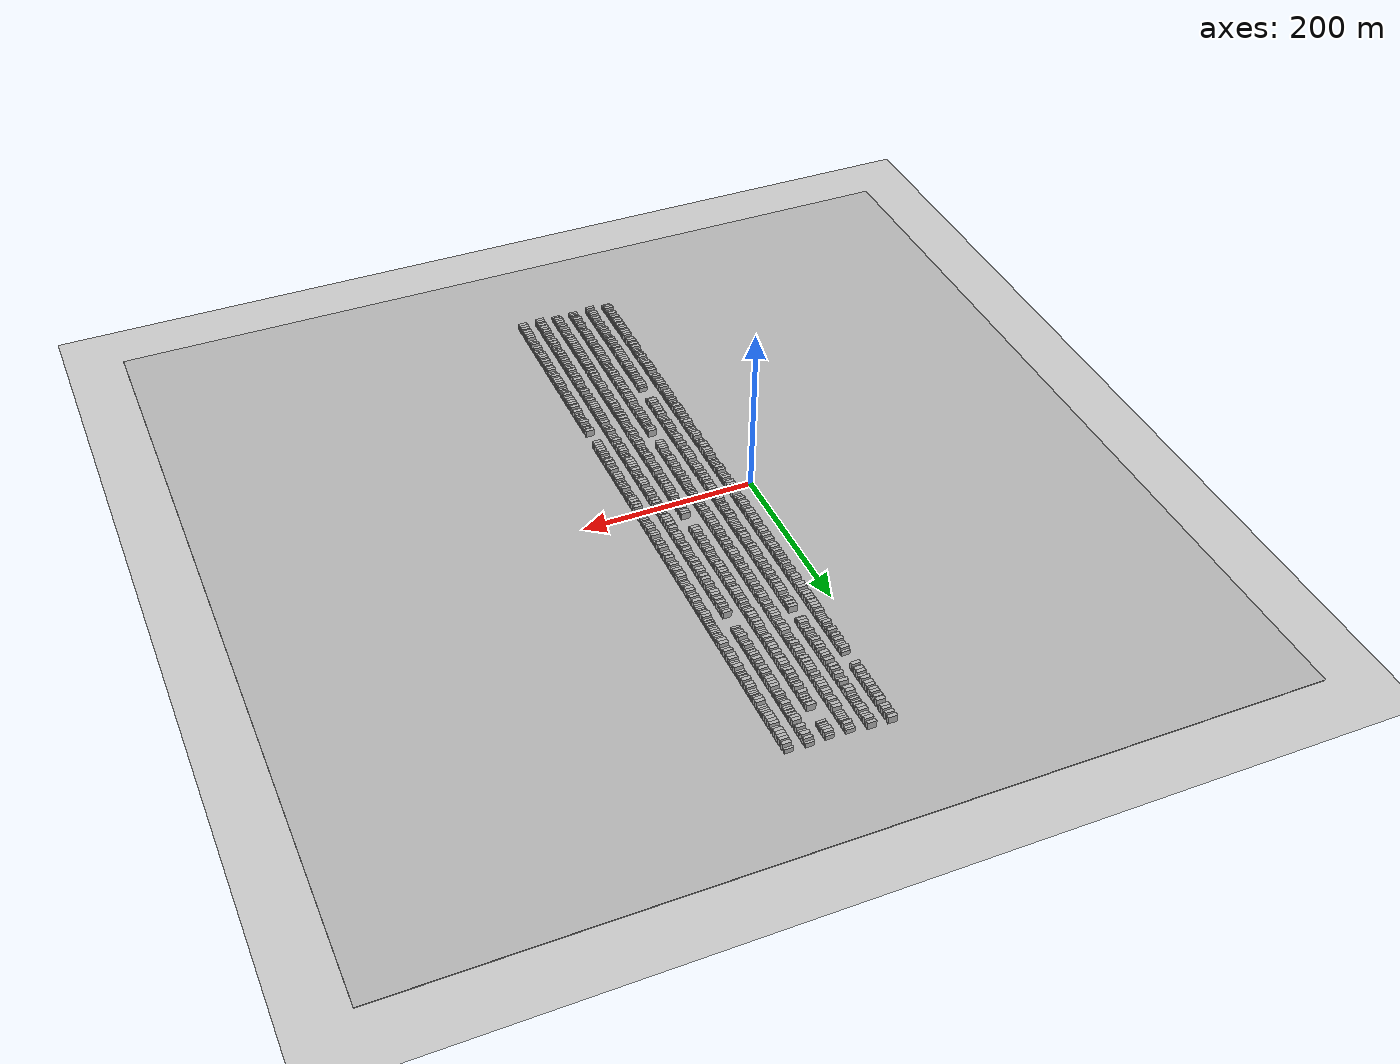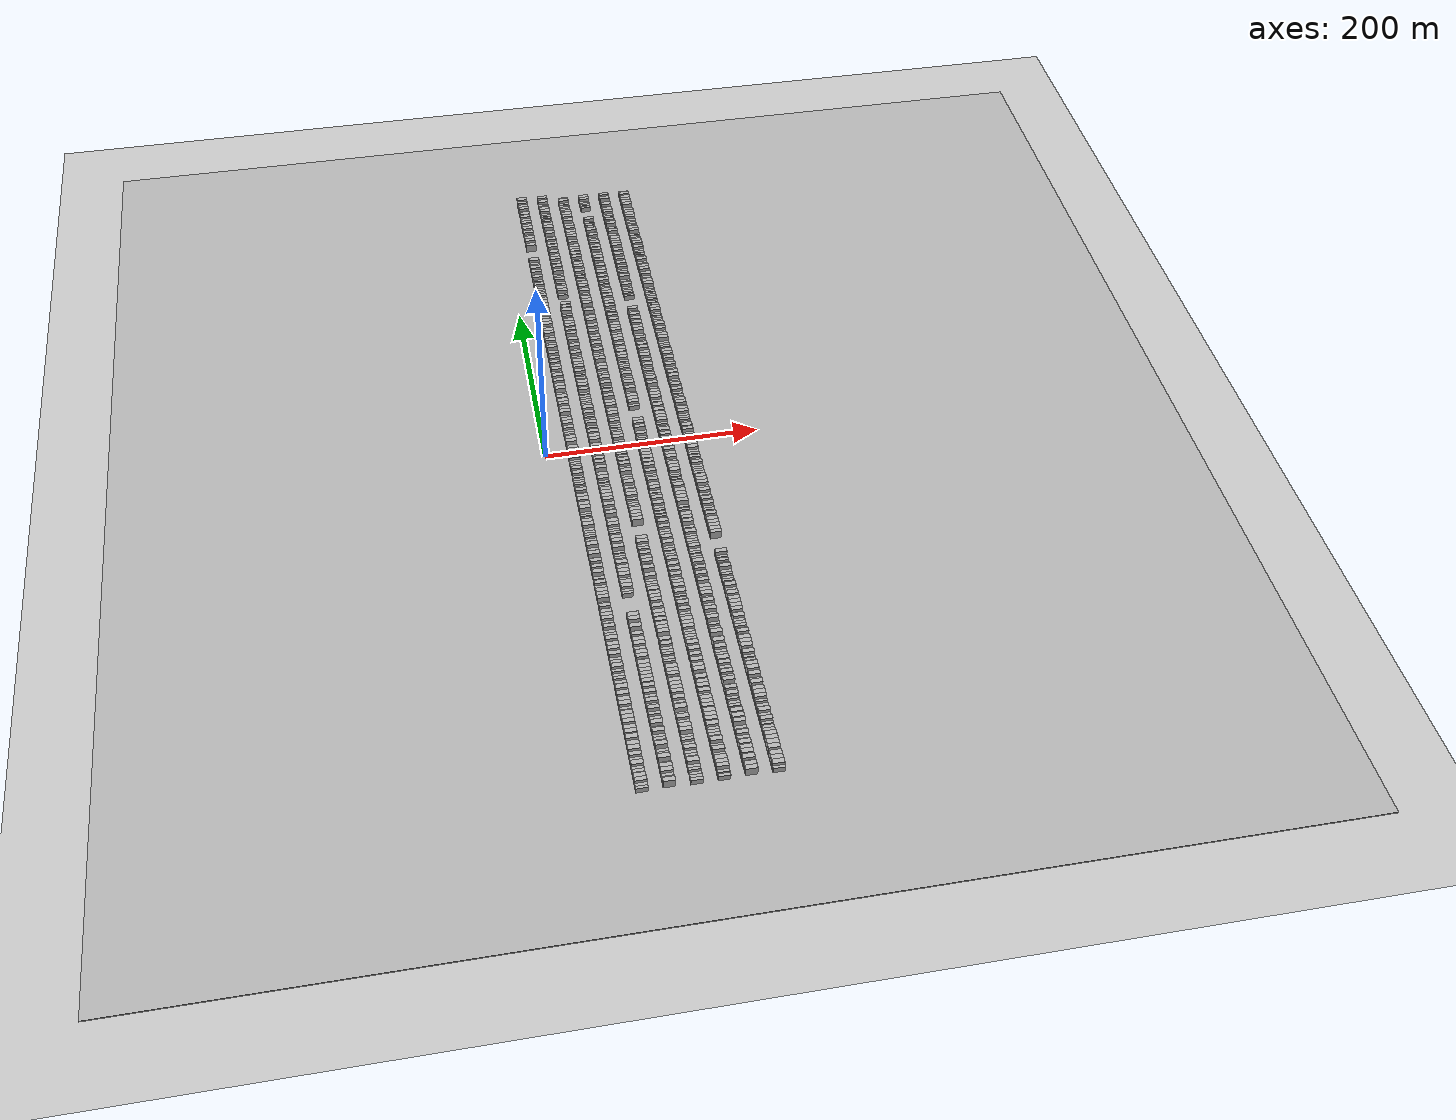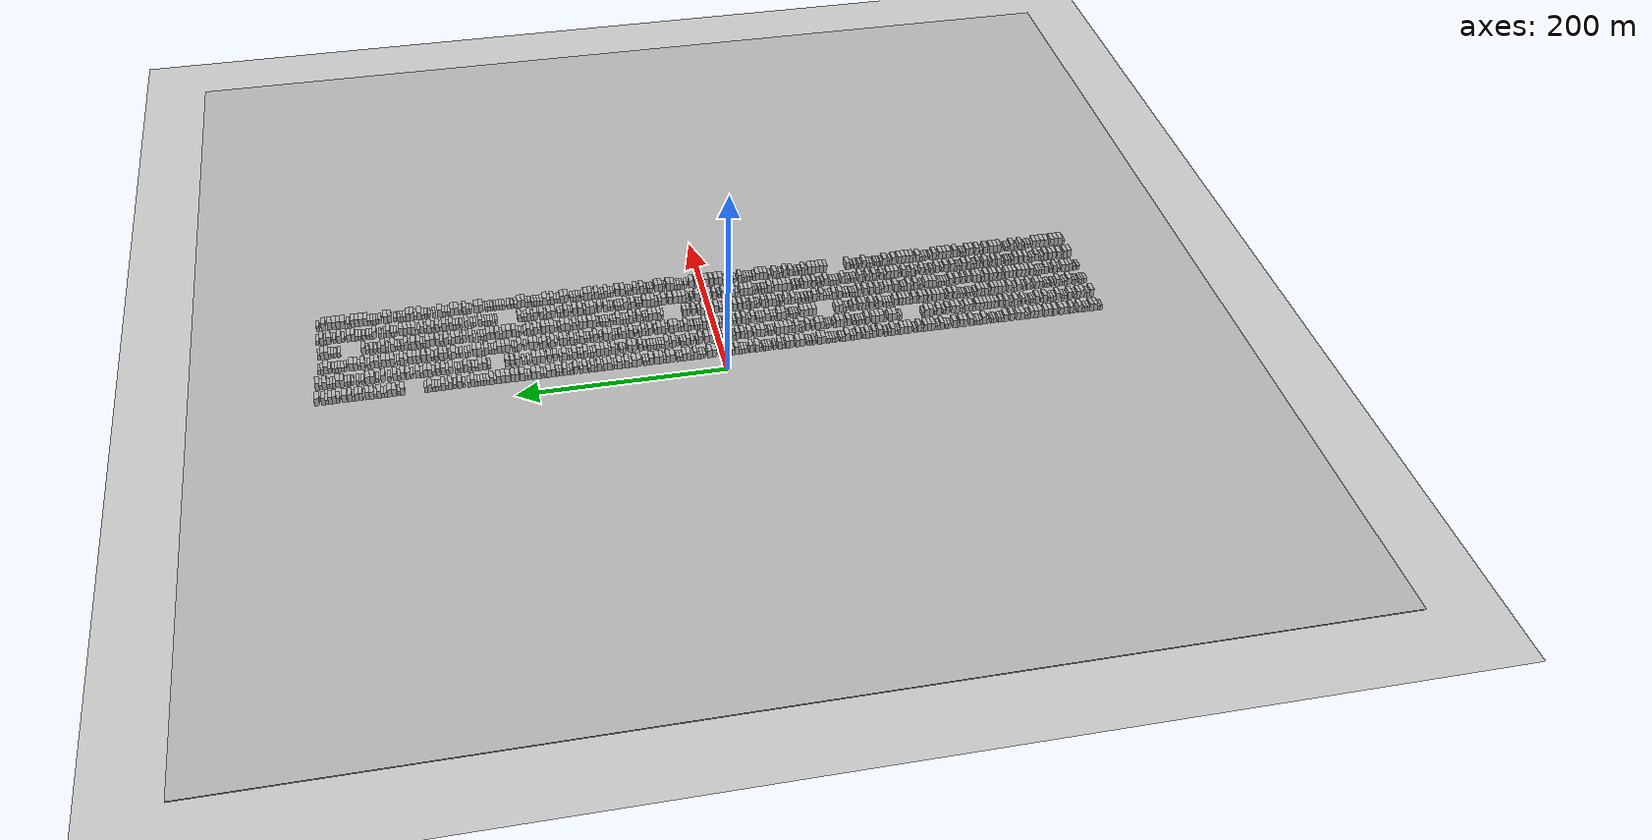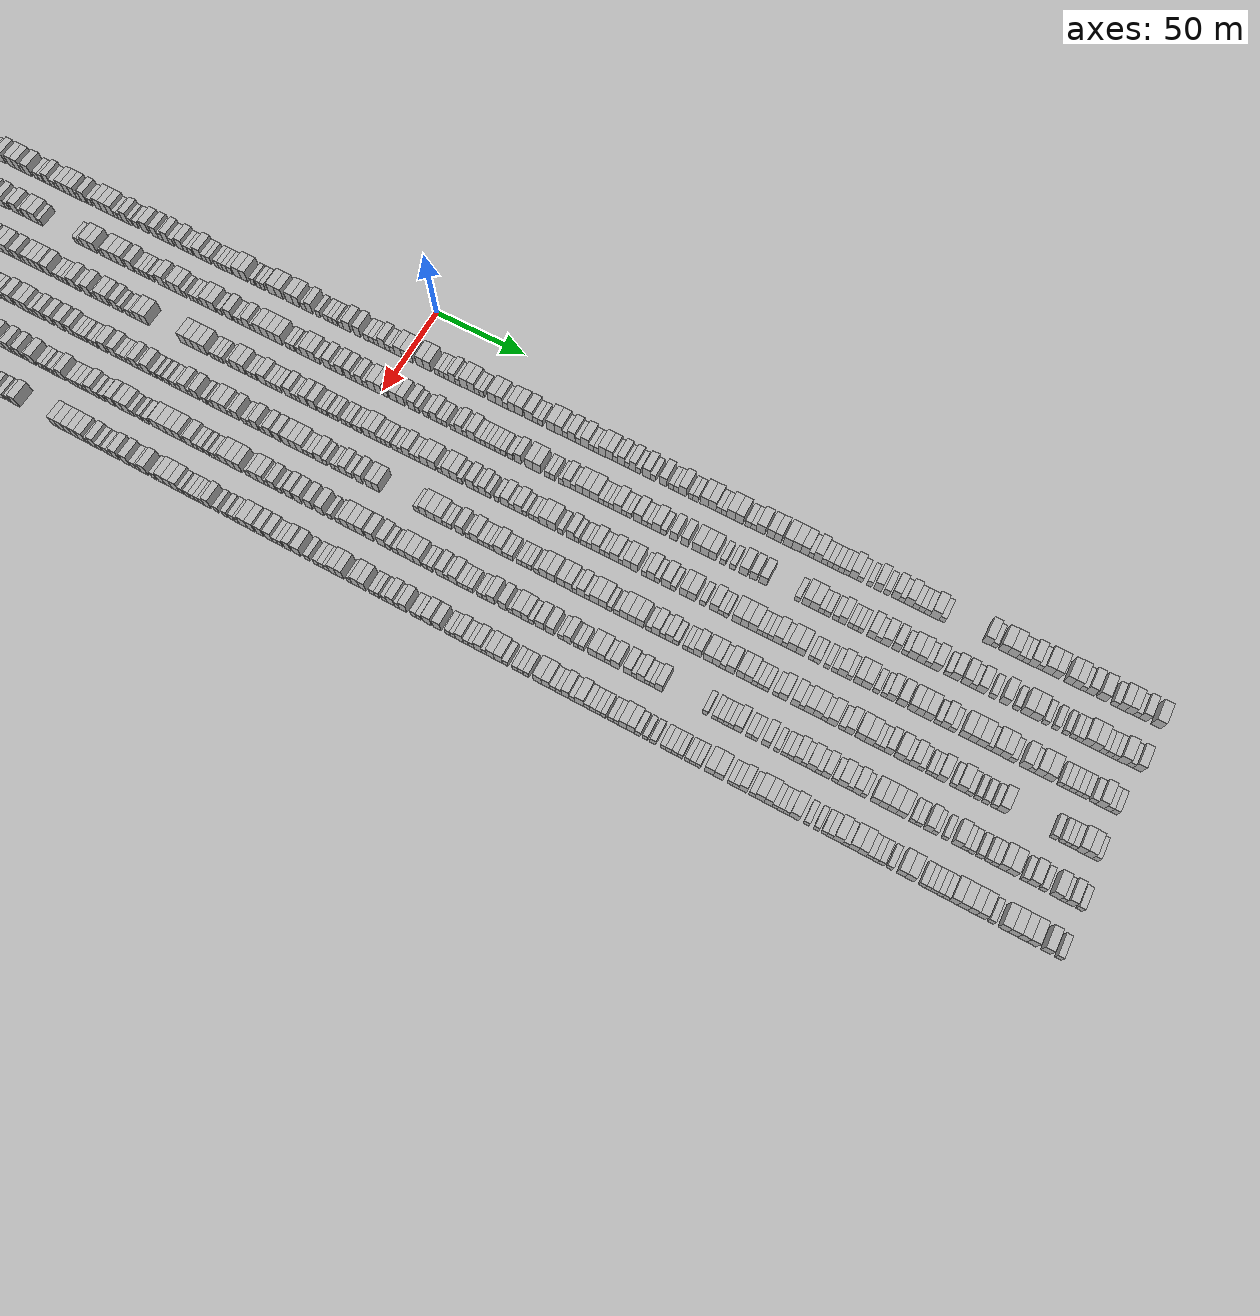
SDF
<?xml version="1.0" encoding="utf-8"?>

<sdf version="1.6">

   <world name="default">

      <gui fullscreen="0">

         <camera name="user_camera">

            <pose>-15 0 4.57585 0 0 0</pose>

            <view_controller>orbit</view_controller>

         </camera>

      </gui>

      <scene>

         <sky>

           <clouds>

             <speed>12</speed>

           </clouds>

         </sky>

         <ambient>0.4 0.4 0.4 1</ambient>

         <background>0.7 0.7 0.7 1</background>

         <shadows>1</shadows>

      </scene>

      <gravity>0 0 -9.8066</gravity>

      <magnetic_field>6e-06 2.3e-05 -4.2e-05</magnetic_field>

      <physics default="0" name="default_physics" type="ode">

         <ode>

            <solver>

               <type>quick</type>

               <iters>10</iters>

               <sor>1.0</sor>

               <use_dynamic_moi_rescaling>0</use_dynamic_moi_rescaling>

            </solver>

            <constraints>

               <cfm>0</cfm>

               <erp>0.2</erp>

               <contact_max_correcting_vel>100</contact_max_correcting_vel>

               <contact_surface_layer>0.001</contact_surface_layer>

            </constraints>

         </ode>

         <max_step_size>0.004</max_step_size>

         <real_time_factor>1</real_time_factor>

         <real_time_update_rate>250</real_time_update_rate>

      </physics>

      <light name="sun" type="directional">

         <cast_shadows>1</cast_shadows>

         <pose>0 0 10 0 0 0</pose>

         <diffuse>0.8 0.8 0.8 1</diffuse>

         <specular>0.2 0.2 0.2 1</specular>

         <attenuation>

            <range>1000</range>

            <constant>0.9</constant>

            <linear>0.01</linear>

            <quadratic>0.001</quadratic>

         </attenuation>

         <direction>-0.5 0.1 -0.9</direction>

      </light>

      <include>

         <name>ground_plane_1</name>

         <uri>model://HANNAS_ground_plane</uri>

         <pose>0 0 0  0 0 0</pose>

      </include>

      <include>

         <name>ground_plane_2</name>

         <uri>model://HANNAS_ground_plane</uri>

         <pose>100 0 0  0 0 0</pose>

      </include>

      <model name="building_1">

         <static>1</static>

         <pose frame="">25.0000 -378.7506 0 0.000000 0.000000 0.000000</pose>

         <link name="link">

            <pose frame="">0 0 3.00 0 0 0</pose>

            <collision name="collision">

               <geometry>

                  <box>

                     <size>10.0000 2.4988 6.0000</size>

                  </box>

               </geometry>

               <max_contacts>10</max_contacts>

               <surface>

                  <contact>

                     <ode/>

                  </contact>

                  <bounce/>

                  <friction>

                     <torsional>

                        <ode/>

                     </torsional>

                     <ode/>

                  </friction>

               </surface>

            </collision>

            <visual name="visual">

               <cast_shadows>0</cast_shadows>

               <geometry>

                  <box>

                     <size>10.0000 2.4988 6.0000</size>

                  </box>

               </geometry>

               <material>

                  <script>

                     <uri>model://HANNAS_wall/materials/scripts</uri>

                     <uri>model://HANNAS_wall/materials/textures</uri>

                     <name>vrc/HANNAS_wall</name>

                  </script>

               </material>

            </visual>

            <self_collide>0</self_collide>

            <enable_wind>0</enable_wind>

            <kinematic>0</kinematic>

         </link>

      </model>

      <model name="building_2">

         <static>1</static>

         <pose frame="">25.0000 -376.0691 0 0.000000 0.000000 0.000000</pose>

         <link name="link">

            <pose frame="">0 0 3.00 0 0 0</pose>

            <collision name="collision">

               <geometry>

                  <box>

                     <size>10.0000 2.8642 6.0000</size>

                  </box>

               </geometry>

               <max_contacts>10</max_contacts>

               <surface>

                  <contact>

                     <ode/>

                  </contact>

                  <bounce/>

                  <friction>

                     <torsional>

                        <ode/>

                     </torsional>

                     <ode/>

                  </friction>

               </surface>

            </collision>

            <visual name="visual">

               <cast_shadows>0</cast_shadows>

               <geometry>

                  <box>

                     <size>10.0000 2.8642 6.0000</size>

                  </box>

               </geometry>

               <material>

                  <script>

                     <uri>model://HANNAS_wall/materials/scripts</uri>

                     <uri>model://HANNAS_wall/materials/textures</uri>

                     <name>vrc/HANNAS_wall</name>

                  </script>

               </material>

            </visual>

            <self_collide>0</self_collide>

            <enable_wind>0</enable_wind>

            <kinematic>0</kinematic>

         </link>

      </model>

      <model name="building_3">

         <static>1</static>

         <pose frame="">25.0000 -372.7572 0 0.000000 0.000000 0.000000</pose>

         <link name="link">

            <pose frame="">0 0 4.50 0 0 0</pose>

            <collision name="collision">

               <geometry>

                  <box>

                     <size>10.0000 3.7595 9.0000</size>

                  </box>

               </geometry>

               <max_contacts>10</max_contacts>

               <surface>

                  <contact>

                     <ode/>

                  </contact>

                  <bounce/>

                  <friction>

                     <torsional>

                        <ode/>

                     </torsional>

                     <ode/>

                  </friction>

               </surface>

            </collision>

            <visual name="visual">

               <cast_shadows>0</cast_shadows>

               <geometry>

                  <box>

                     <size>10.0000 3.7595 9.0000</size>

                  </box>

               </geometry>

               <material>

                  <script>

                     <uri>model://HANNAS_wall/materials/scripts</uri>

                     <uri>model://HANNAS_wall/materials/textures</uri>

                     <name>vrc/HANNAS_wall</name>

                  </script>

               </material>

            </visual>

            <self_collide>0</self_collide>

            <enable_wind>0</enable_wind>

            <kinematic>0</kinematic>

         </link>

      </model>

      <model name="building_4">

         <static>1</static>

         <pose frame="">25.0000 -368.9137 0 0.000000 0.000000 0.000000</pose>

         <link name="link">

            <pose frame="">0 0 4.50 0 0 0</pose>

            <collision name="collision">

               <geometry>

                  <box>

                     <size>10.0000 3.9275 9.0000</size>

                  </box>

               </geometry>

               <max_contacts>10</max_contacts>

               <surface>

                  <contact>

                     <ode/>

                  </contact>

                  <bounce/>

                  <friction>

                     <torsional>

                        <ode/>

                     </torsional>

                     <ode/>

                  </friction>

               </surface>

            </collision>

            <visual name="visual">

               <cast_shadows>0</cast_shadows>

               <geometry>

                  <box>

                     <size>10.0000 3.9275 9.0000</size>

                  </box>

               </geometry>

               <material>

                  <script>

                     <uri>model://HANNAS_wall/materials/scripts</uri>

                     <uri>model://HANNAS_wall/materials/textures</uri>

                     <name>vrc/HANNAS_wall</name>

                  </script>

               </material>

            </visual>

            <self_collide>0</self_collide>

            <enable_wind>0</enable_wind>

            <kinematic>0</kinematic>

         </link>

      </model>

      <model name="building_5">

         <static>1</static>

         <pose frame="">25.0000 -365.6097 0 0.000000 0.000000 0.000000</pose>

         <link name="link">

            <pose frame="">0 0 3.00 0 0 0</pose>

            <collision name="collision">

               <geometry>

                  <box>

                     <size>10.0000 2.6805 6.0000</size>

                  </box>

               </geometry>

               <max_contacts>10</max_contacts>

               <surface>

                  <contact>

                     <ode/>

                  </contact>

                  <bounce/>

                  <friction>

                     <torsional>

                        <ode/>

                     </torsional>

                     <ode/>

                  </friction>

               </surface>

            </collision>

            <visual name="visual">

               <cast_shadows>0</cast_shadows>

               <geometry>

                  <box>

                     <size>10.0000 2.6805 6.0000</size>

                  </box>

               </geometry>

               <material>

                  <script>

                     <uri>model://HANNAS_wall/materials/scripts</uri>

                     <uri>model://HANNAS_wall/materials/textures</uri>

                     <name>vrc/HANNAS_wall</name>

                  </script>

               </material>

            </visual>

            <self_collide>0</self_collide>

            <enable_wind>0</enable_wind>

            <kinematic>0</kinematic>

         </link>

      </model>

      <model name="building_6">

         <static>1</static>

         <pose frame="">25.0000 -362.8159 0 0.000000 0.000000 0.000000</pose>

         <link name="link">

            <pose frame="">0 0 3.00 0 0 0</pose>

            <collision name="collision">

               <geometry>

                  <box>

                     <size>10.0000 2.9070 6.0000</size>

                  </box>

               </geometry>

               <max_contacts>10</max_contacts>

               <surface>

                  <contact>

                     <ode/>

                  </contact>

                  <bounce/>

                  <friction>

                     <torsional>

                        <ode/>

                     </torsional>

                     <ode/>

                  </friction>

               </surface>

            </collision>

            <visual name="visual">

               <cast_shadows>0</cast_shadows>

               <geometry>

                  <box>

                     <size>10.0000 2.9070 6.0000</size>

                  </box>

               </geometry>

               <material>

                  <script>

                     <uri>model://HANNAS_wall/materials/scripts</uri>

                     <uri>model://HANNAS_wall/materials/textures</uri>

                     <name>vrc/HANNAS_wall</name>

                  </script>

               </material>

            </visual>

            <self_collide>0</self_collide>

            <enable_wind>0</enable_wind>

            <kinematic>0</kinematic>

         </link>

      </model>

      <model name="building_7">

         <static>1</static>

         <pose frame="">25.0000 -360.1054 0 0.000000 0.000000 0.000000</pose>

         <link name="link">

            <pose frame="">0 0 3.00 0 0 0</pose>

            <collision name="collision">

               <geometry>

                  <box>

                     <size>10.0000 2.5140 6.0000</size>

                  </box>

               </geometry>

               <max_contacts>10</max_contacts>

               <surface>

                  <contact>

                     <ode/>

                  </contact>

                  <bounce/>

                  <friction>

                     <torsional>

                        <ode/>

                     </torsional>

                     <ode/>

                  </friction>

               </surface>

            </collision>

            <visual name="visual">

               <cast_shadows>0</cast_shadows>

               <geometry>

                  <box>

                     <size>10.0000 2.5140 6.0000</size>

                  </box>

               </geometry>

               <material>

                  <script>

                     <uri>model://HANNAS_wall/materials/scripts</uri>

                     <uri>model://HANNAS_wall/materials/textures</uri>

                     <name>vrc/HANNAS_wall</name>

                  </script>

               </material>

            </visual>

            <self_collide>0</self_collide>

            <enable_wind>0</enable_wind>

            <kinematic>0</kinematic>

         </link>

      </model>

      <model name="building_8">

         <static>1</static>

         <pose frame="">25.0000 -356.7440 0 0.000000 0.000000 0.000000</pose>

         <link name="link">

            <pose frame="">0 0 4.50 0 0 0</pose>

            <collision name="collision">

               <geometry>

                  <box>

                     <size>10.0000 4.2089 9.0000</size>

                  </box>

               </geometry>

               <max_contacts>10</max_contacts>

               <surface>

                  <contact>

                     <ode/>

                  </contact>

                  <bounce/>

                  <friction>

                     <torsional>

                        <ode/>

                     </torsional>

                     <ode/>

                  </friction>

               </surface>

            </collision>

            <visual name="visual">

               <cast_shadows>0</cast_shadows>

               <geometry>

                  <box>

                     <size>10.0000 4.2089 9.0000</size>

                  </box>

               </geometry>

               <material>

                  <script>

                     <uri>model://HANNAS_wall/materials/scripts</uri>

                     <uri>model://HANNAS_wall/materials/textures</uri>

                     <name>vrc/HANNAS_wall</name>

                  </script>

               </material>

            </visual>

            <self_collide>0</self_collide>

            <enable_wind>0</enable_wind>

            <kinematic>0</kinematic>

         </link>

      </model>

      <model name="building_9">

         <static>1</static>

         <pose frame="">25.0000 -351.3504 0 0.000000 0.000000 0.000000</pose>

         <link name="link">

            <pose frame="">0 0 3.00 0 0 0</pose>

            <collision name="collision">

               <geometry>

                  <box>

                     <size>10.0000 2.5784 6.0000</size>

                  </box>

               </geometry>

               <max_contacts>10</max_contacts>

               <surface>

                  <contact>

                     <ode/>

                  </contact>

                  <bounce/>

                  <friction>

                     <torsional>

                        <ode/>

                     </torsional>

                     <ode/>

                  </friction>

               </surface>

            </collision>

            <visual name="visual">

               <cast_shadows>0</cast_shadows>

               <geometry>

                  <box>

                     <size>10.0000 2.5784 6.0000</size>

                  </box>

               </geometry>

               <material>

                  <script>

                     <uri>model://HANNAS_wall/materials/scripts</uri>

                     <uri>model://HANNAS_wall/materials/textures</uri>

                     <name>vrc/HANNAS_wall</name>

                  </script>

               </material>

            </visual>

            <self_collide>0</self_collide>

            <enable_wind>0</enable_wind>

            <kinematic>0</kinematic>

         </link>

      </model>

      <model name="building_10">

         <static>1</static>

         <pose frame="">25.0000 -348.1930 0 0.000000 0.000000 0.000000</pose>

         <link name="link">

            <pose frame="">0 0 4.50 0 0 0</pose>

            <collision name="collision">

               <geometry>

                  <box>

                     <size>10.0000 3.7363 9.0000</size>

                  </box>

               </geometry>

               <max_contacts>10</max_contacts>

               <surface>

                  <contact>

                     <ode/>

                  </contact>

                  <bounce/>

                  <friction>

                     <torsional>

                        <ode/>

                     </torsional>

                     <ode/>

                  </friction>

               </surface>

            </collision>

            <visual name="visual">

               <cast_shadows>0</cast_shadows>

               <geometry>

                  <box>

                     <size>10.0000 3.7363 9.0000</size>

                  </box>

               </geometry>

               <material>

                  <script>

                     <uri>model://HANNAS_wall/materials/scripts</uri>

                     <uri>model://HANNAS_wall/materials/textures</uri>

                     <name>vrc/HANNAS_wall</name>

                  </script>

               </material>

            </visual>

            <self_collide>0</self_collide>

            <enable_wind>0</enable_wind>

            <kinematic>0</kinematic>

         </link>

      </model>

      <model name="building_11">

         <static>1</static>

         <pose frame="">25.0000 -342.1361 0 0.000000 0.000000 0.000000</pose>

         <link name="link">

            <pose frame="">0 0 4.50 0 0 0</pose>

            <collision name="collision">

               <geometry>

                  <box>

                     <size>10.0000 4.3775 9.0000</size>

                  </box>

               </geometry>

               <max_contacts>10</max_contacts>

               <surface>

                  <contact>

                     <ode/>

                  </contact>

                  <bounce/>

                  <friction>

                     <torsional>

                        <ode/>

                     </torsional>

                     <ode/>

                  </friction>

               </surface>

            </collision>

            <visual name="visual">

               <cast_shadows>0</cast_shadows>

               <geometry>

                  <box>

                     <size>10.0000 4.3775 9.0000</size>

                  </box>

               </geometry>

               <material>

                  <script>

                     <uri>model://HANNAS_wall/materials/scripts</uri>

                     <uri>model://HANNAS_wall/materials/textures</uri>

                     <name>vrc/HANNAS_wall</name>

                  </script>

               </material>

            </visual>

            <self_collide>0</self_collide>

            <enable_wind>0</enable_wind>

            <kinematic>0</kinematic>

         </link>

      </model>

      <model name="building_12">

         <static>1</static>

         <pose frame="">25.0000 -337.7600 0 0.000000 0.000000 0.000000</pose>

         <link name="link">

            <pose frame="">0 0 4.50 0 0 0</pose>

            <collision name="collision">

               <geometry>

                  <box>

                     <size>10.0000 4.3747 9.0000</size>

                  </box>

               </geometry>

               <max_contacts>10</max_contacts>

               <surface>

                  <contact>

                     <ode/>

                  </contact>

                  <bounce/>

                  <friction>

                     <torsional>

                        <ode/>

                     </torsional>

                     <ode/>

                  </friction>

               </surface>

            </collision>

            <visual name="visual">

               <cast_shadows>0</cast_shadows>

               <geometry>

                  <box>

                     <size>10.0000 4.3747 9.0000</size>

                  </box>

               </geometry>

               <material>

                  <script>

                     <uri>model://HANNAS_wall/materials/scripts</uri>

                     <uri>model://HANNAS_wall/materials/textures</uri>

                     <name>vrc/HANNAS_wall</name>

                  </script>

               </material>

            </visual>

            <self_collide>0</self_collide>

            <enable_wind>0</enable_wind>

            <kinematic>0</kinematic>

         </link>

      </model>

      <model name="building_13">

         <static>1</static>

         <pose frame="">25.0000 -331.3357 0 0.000000 0.000000 0.000000</pose>

         <link name="link">

            <pose frame="">0 0 4.50 0 0 0</pose>

            <collision name="collision">

               <geometry>

                  <box>

                     <size>10.0000 4.4739 9.0000</size>

                  </box>

               </geometry>

               <max_contacts>10</max_contacts>

               <surface>

                  <contact>

                     <ode/>

                  </contact>

                  <bounce/>

                  <friction>

                     <torsional>

                        <ode/>

                     </torsional>

                     <ode/>

                  </friction>

               </surface>

            </collision>

            <visual name="visual">

               <cast_shadows>0</cast_shadows>

               <geometry>

                  <box>

                     <size>10.0000 4.4739 9.0000</size>

                  </box>

               </geometry>

               <material>

                  <script>

                     <uri>model://HANNAS_wall/materials/scripts</uri>

                     <uri>model://HANNAS_wall/materials/textures</uri>

                     <name>vrc/HANNAS_wall</name>

                  </script>

               </material>

            </visual>

            <self_collide>0</self_collide>

            <enable_wind>0</enable_wind>

            <kinematic>0</kinematic>

         </link>

      </model>

      <model name="building_14">

         <static>1</static>

         <pose frame="">25.0000 -326.0021 0 0.000000 0.000000 0.000000</pose>

         <link name="link">

            <pose frame="">0 0 4.50 0 0 0</pose>

            <collision name="collision">

               <geometry>

                  <box>

                     <size>10.0000 4.1932 9.0000</size>

                  </box>

               </geometry>

               <max_contacts>10</max_contacts>

               <surface>

                  <contact>

                     <ode/>

                  </contact>

                  <bounce/>

                  <friction>

                     <torsional>

                        <ode/>

                     </torsional>

                     <ode/>

                  </friction>

               </surface>

            </collision>

            <visual name="visual">

               <cast_shadows>0</cast_shadows>

               <geometry>

                  <box>

                     <size>10.0000 4.1932 9.0000</size>

                  </box>

               </geometry>

               <material>

                  <script>

                     <uri>model://HANNAS_wall/materials/scripts</uri>

                     <uri>model://HANNAS_wall/materials/textures</uri>

                     <name>vrc/HANNAS_wall</name>

                  </script>

               </material>

            </visual>

            <self_collide>0</self_collide>

            <enable_wind>0</enable_wind>

            <kinematic>0</kinematic>

         </link>

      </model>

      <model name="building_15">

         <static>1</static>

         <pose frame="">25.0000 -321.9527 0 0.000000 0.000000 0.000000</pose>

         <link name="link">

            <pose frame="">0 0 4.50 0 0 0</pose>

            <collision name="collision">

               <geometry>

                  <box>

                     <size>10.0000 3.9056 9.0000</size>

                  </box>

               </geometry>

               <max_contacts>10</max_contacts>

               <surface>

                  <contact>

                     <ode/>

                  </contact>

                  <bounce/>

                  <friction>

                     <torsional>

                        <ode/>

                     </torsional>

                     <ode/>

                  </friction>

               </surface>

            </collision>

            <visual name="visual">

               <cast_shadows>0</cast_shadows>

               <geometry>

                  <box>

                     <size>10.0000 3.9056 9.0000</size>

                  </box>

               </geometry>

               <material>

                  <script>

                     <uri>model://HANNAS_wall/materials/scripts</uri>

                     <uri>model://HANNAS_wall/materials/textures</uri>

                     <name>vrc/HANNAS_wall</name>

                  </script>

               </material>

            </visual>

            <self_collide>0</self_collide>

            <enable_wind>0</enable_wind>

            <kinematic>0</kinematic>

         </link>

      </model>

      <model name="building_16">

         <static>1</static>

         <pose frame="">25.0000 -315.9032 0 0.000000 0.000000 0.000000</pose>

         <link name="link">

            <pose frame="">0 0 4.50 0 0 0</pose>

            <collision name="collision">

               <geometry>

                  <box>

                     <size>10.0000 4.1933 9.0000</size>

                  </box>

               </geometry>

               <max_contacts>10</max_contacts>

               <surface>

                  <contact>

                     <ode/>

                  </contact>

                  <bounce/>

                  <friction>

                     <torsional>

                        <ode/>

                     </torsional>

                     <ode/>

                  </friction>

               </surface>

            </collision>

            <visual name="visual">

               <cast_shadows>0</cast_shadows>

               <geometry>

                  <box>

                     <size>10.0000 4.1933 9.0000</size>

                  </box>

               </geometry>

               <material>

                  <script>

                     <uri>model://HANNAS_wall/materials/scripts</uri>

                     <uri>model://HANNAS_wall/materials/textures</uri>

                     <name>vrc/HANNAS_wall</name>

                  </script>

               </material>

            </visual>

            <self_collide>0</self_collide>

            <enable_wind>0</enable_wind>

            <kinematic>0</kinematic>

         </link>

      </model>

      <model name="building_17">

         <static>1</static>

         <pose frame="">25.0000 -311.7271 0 0.000000 0.000000 0.000000</pose>

         <link name="link">

            <pose frame="">0 0 4.50 0 0 0</pose>

            <collision name="collision">

               <geometry>

                  <box>

                     <size>10.0000 4.1589 9.0000</size>

                  </box>

               </geometry>

               <max_contacts>10</max_contacts>

               <surface>

                  <contact>

                     <ode/>

                  </contact>

                  <bounce/>

                  <friction>

                     <torsional>

                        <ode/>

                     </torsional>

                     <ode/>

                  </friction>

               </surface>

            </collision>

            <visual name="visual">

               <cast_shadows>0</cast_shadows>

               <geometry>

                  <box>

                     <size>10.0000 4.1589 9.0000</size>

                  </box>

               </geometry>

               <material>

                  <script>

                     <uri>model://HANNAS_wall/materials/scripts</uri>

                     <uri>model://HANNAS_wall/materials/textures</uri>

                     <name>vrc/HANNAS_wall</name>

                  </script>

               </material>

            </visual>

            <self_collide>0</self_collide>

            <enable_wind>0</enable_wind>

            <kinematic>0</kinematic>

         </link>

      </model>

      <model name="building_18">

         <static>1</static>

         <pose frame="">25.0000 -307.6560 0 0.000000 0.000000 0.000000</pose>

         <link name="link">

            <pose frame="">0 0 4.50 0 0 0</pose>

            <collision name="collision">

               <geometry>

                  <box>

                     <size>10.0000 3.9833 9.0000</size>

                  </box>

               </geometry>

               <max_contacts>10</max_contacts>

               <surface>

                  <contact>

                     <ode/>

                  </contact>

                  <bounce/>

                  <friction>

                     <torsional>

                        <ode/>

                     </torsional>

                     <ode/>

                  </friction>

               </surface>

            </collision>

            <visual name="visual">

               <cast_shadows>0</cast_shadows>

               <geometry>

                  <box>

                     <size>10.0000 3.9833 9.0000</size>

                  </box>

               </geometry>

               <material>

                  <script>

                     <uri>model://HANNAS_wall/materials/scripts</uri>

                     <uri>model://HANNAS_wall/materials/textures</uri>

                     <name>vrc/HANNAS_wall</name>

                  </script>

               </material>

            </visual>

            <self_collide>0</self_collide>

            <enable_wind>0</enable_wind>

            <kinematic>0</kinematic>

         </link>

      </model>

      <model name="building_19">

         <static>1</static>

         <pose frame="">25.0000 -304.2458 0 0.000000 0.000000 0.000000</pose>

         <link name="link">

            <pose frame="">0 0 3.00 0 0 0</pose>

            <collision name="collision">

               <geometry>

                  <box>

                     <size>10.0000 2.8371 6.0000</size>

                  </box>

               </geometry>

               <max_contacts>10</max_contacts>

               <surface>

                  <contact>

                     <ode/>

                  </contact>

                  <bounce/>

                  <friction>

                     <torsional>

                        <ode/>

                     </torsional>

                     <ode/>

                  </friction>

               </surface>

            </collision>

            <visual name="visual">

               <cast_shadows>0</cast_shadows>

               <geometry>

                  <box>

                     <size>10.0000 2.8371 6.0000</size>

                  </box>

               </geometry>

               <material>

                  <script>

                     <uri>model://HANNAS_wall/materials/scripts</uri>

                     <uri>model://HANNAS_wall/materials/textures</uri>

                     <name>vrc/HANNAS_wall</name>

                  </script>

               </material>

            </visual>

            <self_collide>0</self_collide>

            <enable_wind>0</enable_wind>

            <kinematic>0</kinematic>

         </link>

      </model>

      <model name="building_20">

         <static>1</static>

         <pose frame="">25.0000 -301.4425 0 0.000000 0.000000 0.000000</pose>

         <link name="link">

            <pose frame="">0 0 3.00 0 0 0</pose>

            <collision name="collision">

               <geometry>

                  <box>

                     <size>10.0000 2.7695 6.0000</size>

                  </box>

               </geometry>

               <max_contacts>10</max_contacts>

               <surface>

                  <contact>

                     <ode/>

                  </contact>

                  <bounce/>

                  <friction>

                     <torsional>

                        <ode/>

                     </torsional>

                     <ode/>

                  </friction>

               </surface>

            </collision>

            <visual name="visual">

               <cast_shadows>0</cast_shadows>

               <geometry>

                  <box>

                     <size>10.0000 2.7695 6.0000</size>

                  </box>

               </geometry>

               <material>

                  <script>

                     <uri>model://HANNAS_wall/materials/scripts</uri>

                     <uri>model://HANNAS_wall/materials/textures</uri>

                     <name>vrc/HANNAS_wall</name>

                  </script>

               </material>

            </visual>

            <self_collide>0</self_collide>

            <enable_wind>0</enable_wind>

            <kinematic>0</kinematic>

         </link>

      </model>

      <model name="building_21">

         <static>1</static>

         <pose frame="">25.0000 -297.8768 0 0.000000 0.000000 0.000000</pose>

         <link name="link">

            <pose frame="">0 0 4.50 0 0 0</pose>

            <collision name="collision">

               <geometry>

                  <box>

                     <size>10.0000 4.3620 9.0000</size>

                  </box>

               </geometry>

               <max_contacts>10</max_contacts>

               <surface>

                  <contact>

                     <ode/>

                  </contact>

                  <bounce/>

                  <friction>

                     <torsional>

                        <ode/>

                     </torsional>

                     <ode/>

                  </friction>

               </surface>

            </collision>

            <visual name="visual">

               <cast_shadows>0</cast_shadows>

               <geometry>

                  <box>

                     <size>10.0000 4.3620 9.0000</size>

                  </box>

               </geometry>

               <material>

                  <script>

                     <uri>model://HANNAS_wall/materials/scripts</uri>

                     <uri>model://HANNAS_wall/materials/textures</uri>

                     <name>vrc/HANNAS_wall</name>

                  </script>

               </material>

            </visual>

            <self_collide>0</self_collide>

            <enable_wind>0</enable_wind>

            <kinematic>0</kinematic>

         </link>

      </model>

      <model name="building_22">

         <static>1</static>

         <pose frame="">25.0000 -293.6143 0 0.000000 0.000000 0.000000</pose>

         <link name="link">

            <pose frame="">0 0 4.50 0 0 0</pose>

            <collision name="collision">

               <geometry>

                  <box>

                     <size>10.0000 4.1630 9.0000</size>

                  </box>

               </geometry>

               <max_contacts>10</max_contacts>

               <surface>

                  <contact>

                     <ode/>

                  </contact>

                  <bounce/>

                  <friction>

                     <torsional>

                        <ode/>

                     </torsional>

                     <ode/>

                  </friction>

               </surface>

            </collision>

            <visual name="visual">

               <cast_shadows>0</cast_shadows>

               <geometry>

                  <box>

                     <size>10.0000 4.1630 9.0000</size>

                  </box>

               </geometry>

               <material>

                  <script>

                     <uri>model://HANNAS_wall/materials/scripts</uri>

                     <uri>model://HANNAS_wall/materials/textures</uri>

                     <name>vrc/HANNAS_wall</name>

                  </script>

               </material>

            </visual>

            <self_collide>0</self_collide>

            <enable_wind>0</enable_wind>

            <kinematic>0</kinematic>

         </link>

      </model>

      <model name="building_23">

         <static>1</static>

         <pose frame="">25.0000 -287.3309 0 0.000000 0.000000 0.000000</pose>

         <link name="link">

            <pose frame="">0 0 4.50 0 0 0</pose>

            <collision name="collision">

               <geometry>

                  <box>

                     <size>10.0000 4.4039 9.0000</size>

                  </box>

               </geometry>

               <max_contacts>10</max_contacts>

               <surface>

                  <contact>

                     <ode/>

                  </contact>

                  <bounce/>

                  <friction>

                     <torsional>

                        <ode/>

                     </torsional>

                     <ode/>

                  </friction>

               </surface>

            </collision>

            <visual name="visual">

               <cast_shadows>0</cast_shadows>

               <geometry>

                  <box>

                     <size>10.0000 4.4039 9.0000</size>

                  </box>

               </geometry>

               <material>

                  <script>

                     <uri>model://HANNAS_wall/materials/scripts</uri>

                     <uri>model://HANNAS_wall/materials/textures</uri>

                     <name>vrc/HANNAS_wall</name>

                  </script>

               </material>

            </visual>

            <self_collide>0</self_collide>

            <enable_wind>0</enable_wind>

            <kinematic>0</kinematic>

         </link>

      </model>

      <model name="building_24">

         <static>1</static>

         <pose frame="">25.0000 -280.9043 0 0.000000 0.000000 0.000000</pose>

         <link name="link">

            <pose frame="">0 0 4.50 0 0 0</pose>

            <collision name="collision">

               <geometry>

                  <box>

                     <size>10.0000 4.4493 9.0000</size>

                  </box>

               </geometry>

               <max_contacts>10</max_contacts>

               <surface>

                  <contact>

                     <ode/>

                  </contact>

                  <bounce/>

                  <friction>

                     <torsional>

                        <ode/>

                     </torsional>

                     <ode/>

                  </friction>

               </surface>

            </collision>

            <visual name="visual">

               <cast_shadows>0</cast_shadows>

               <geometry>

                  <box>

                     <size>10.0000 4.4493 9.0000</size>

                  </box>

               </geometry>

               <material>

                  <script>

                     <uri>model://HANNAS_wall/materials/scripts</uri>

                     <uri>model://HANNAS_wall/materials/textures</uri>

                     <name>vrc/HANNAS_wall</name>

                  </script>

               </material>

            </visual>

            <self_collide>0</self_collide>

            <enable_wind>0</enable_wind>

            <kinematic>0</kinematic>

         </link>

      </model>

      <model name="building_25">

         <static>1</static>

         <pose frame="">25.0000 -277.3716 0 0.000000 0.000000 0.000000</pose>

         <link name="link">

            <pose frame="">0 0 3.00 0 0 0</pose>

            <collision name="collision">

               <geometry>

                  <box>

                     <size>10.0000 2.6160 6.0000</size>

                  </box>

               </geometry>

               <max_contacts>10</max_contacts>

               <surface>

                  <contact>

                     <ode/>

                  </contact>

                  <bounce/>

                  <friction>

                     <torsional>

                        <ode/>

                     </torsional>

                     <ode/>

                  </friction>

               </surface>

            </collision>

            <visual name="visual">

               <cast_shadows>0</cast_shadows>

               <geometry>

                  <box>

                     <size>10.0000 2.6160 6.0000</size>

                  </box>

               </geometry>

               <material>

                  <script>

                     <uri>model://HANNAS_wall/materials/scripts</uri>

                     <uri>model://HANNAS_wall/materials/textures</uri>

                     <name>vrc/HANNAS_wall</name>

                  </script>

               </material>

            </visual>

            <self_collide>0</self_collide>

            <enable_wind>0</enable_wind>

            <kinematic>0</kinematic>

         </link>

      </model>

      <model name="building_26">

         <static>1</static>

         <pose frame="">25.0000 -274.5871 0 0.000000 0.000000 0.000000</pose>

         <link name="link">

            <pose frame="">0 0 3.00 0 0 0</pose>

            <collision name="collision">

               <geometry>

                  <box>

                     <size>10.0000 2.9530 6.0000</size>

                  </box>

               </geometry>

               <max_contacts>10</max_contacts>

               <surface>

                  <contact>

                     <ode/>

                  </contact>

                  <bounce/>

                  <friction>

                     <torsional>

                        <ode/>

                     </torsional>

                     <ode/>

                  </friction>

               </surface>

            </collision>

            <visual name="visual">

               <cast_shadows>0</cast_shadows>

               <geometry>

                  <box>

                     <size>10.0000 2.9530 6.0000</size>

                  </box>

               </geometry>

               <material>

                  <script>

                     <uri>model://HANNAS_wall/materials/scripts</uri>

                     <uri>model://HANNAS_wall/materials/textures</uri>

                     <name>vrc/HANNAS_wall</name>

                  </script>

               </material>

            </visual>

            <self_collide>0</self_collide>

            <enable_wind>0</enable_wind>

            <kinematic>0</kinematic>

         </link>

      </model>

      <model name="building_27">

         <static>1</static>

         <pose frame="">25.0000 -269.7358 0 0.000000 0.000000 0.000000</pose>

         <link name="link">

            <pose frame="">0 0 3.00 0 0 0</pose>

            <collision name="collision">

               <geometry>

                  <box>

                     <size>10.0000 2.7497 6.0000</size>

                  </box>

               </geometry>

               <max_contacts>10</max_contacts>

               <surface>

                  <contact>

                     <ode/>

                  </contact>

                  <bounce/>

                  <friction>

                     <torsional>

                        <ode/>

                     </torsional>

                     <ode/>

                  </friction>

               </surface>

            </collision>

            <visual name="visual">

               <cast_shadows>0</cast_shadows>

               <geometry>

                  <box>

                     <size>10.0000 2.7497 6.0000</size>

                  </box>

               </geometry>

               <material>

                  <script>

                     <uri>model://HANNAS_wall/materials/scripts</uri>

                     <uri>model://HANNAS_wall/materials/textures</uri>

                     <name>vrc/HANNAS_wall</name>

                  </script>

               </material>

            </visual>

            <self_collide>0</self_collide>

            <enable_wind>0</enable_wind>

            <kinematic>0</kinematic>

         </link>

      </model>

      <model name="building_28">

         <static>1</static>

         <pose frame="">25.0000 -267.0497 0 0.000000 0.000000 0.000000</pose>

         <link name="link">

            <pose frame="">0 0 3.00 0 0 0</pose>

            <collision name="collision">

               <geometry>

                  <box>

                     <size>10.0000 2.6225 6.0000</size>

                  </box>

               </geometry>

               <max_contacts>10</max_contacts>

               <surface>

                  <contact>

                     <ode/>

                  </contact>

                  <bounce/>

                  <friction>

                     <torsional>

                        <ode/>

                     </torsional>

                     <ode/>

                  </friction>

               </surface>

            </collision>

            <visual name="visual">

               <cast_shadows>0</cast_shadows>

               <geometry>

                  <box>

                     <size>10.0000 2.6225 6.0000</size>

                  </box>

               </geometry>

               <material>

                  <script>

                     <uri>model://HANNAS_wall/materials/scripts</uri>

                     <uri>model://HANNAS_wall/materials/textures</uri>

                     <name>vrc/HANNAS_wall</name>

                  </script>

               </material>

            </visual>

            <self_collide>0</self_collide>

            <enable_wind>0</enable_wind>

            <kinematic>0</kinematic>

         </link>

      </model>

      <model name="building_29">

         <static>1</static>

         <pose frame="">25.0000 -262.3259 0 0.000000 0.000000 0.000000</pose>

         <link name="link">

            <pose frame="">0 0 3.00 0 0 0</pose>

            <collision name="collision">

               <geometry>

                  <box>

                     <size>10.0000 2.8250 6.0000</size>

                  </box>

               </geometry>

               <max_contacts>10</max_contacts>

               <surface>

                  <contact>

                     <ode/>

                  </contact>

                  <bounce/>

                  <friction>

                     <torsional>

                        <ode/>

                     </torsional>

                     <ode/>

                  </friction>

               </surface>

            </collision>

            <visual name="visual">

               <cast_shadows>0</cast_shadows>

               <geometry>

                  <box>

                     <size>10.0000 2.8250 6.0000</size>

                  </box>

               </geometry>

               <material>

                  <script>

                     <uri>model://HANNAS_wall/materials/scripts</uri>

                     <uri>model://HANNAS_wall/materials/textures</uri>

                     <name>vrc/HANNAS_wall</name>

                  </script>

               </material>

            </visual>

            <self_collide>0</self_collide>

            <enable_wind>0</enable_wind>

            <kinematic>0</kinematic>

         </link>

      </model>

      <model name="building_30">

         <static>1</static>

         <pose frame="">25.0000 -258.8280 0 0.000000 0.000000 0.000000</pose>

         <link name="link">

            <pose frame="">0 0 4.50 0 0 0</pose>

            <collision name="collision">

               <geometry>

                  <box>

                     <size>10.0000 4.1708 9.0000</size>

                  </box>

               </geometry>

               <max_contacts>10</max_contacts>

               <surface>

                  <contact>

                     <ode/>

                  </contact>

                  <bounce/>

                  <friction>

                     <torsional>

                        <ode/>

                     </torsional>

                     <ode/>

                  </friction>

               </surface>

            </collision>

            <visual name="visual">

               <cast_shadows>0</cast_shadows>

               <geometry>

                  <box>

                     <size>10.0000 4.1708 9.0000</size>

                  </box>

               </geometry>

               <material>

                  <script>

                     <uri>model://HANNAS_wall/materials/scripts</uri>

                     <uri>model://HANNAS_wall/materials/textures</uri>

                     <name>vrc/HANNAS_wall</name>

                  </script>

               </material>

            </visual>

            <self_collide>0</self_collide>

            <enable_wind>0</enable_wind>

            <kinematic>0</kinematic>

         </link>

      </model>

      <model name="building_31">

         <static>1</static>

         <pose frame="">25.0000 -255.5040 0 0.000000 0.000000 0.000000</pose>

         <link name="link">

            <pose frame="">0 0 3.00 0 0 0</pose>

            <collision name="collision">

               <geometry>

                  <box>

                     <size>10.0000 2.4774 6.0000</size>

                  </box>

               </geometry>

               <max_contacts>10</max_contacts>

               <surface>

                  <contact>

                     <ode/>

                  </contact>

                  <bounce/>

                  <friction>

                     <torsional>

                        <ode/>

                     </torsional>

                     <ode/>

                  </friction>

               </surface>

            </collision>

            <visual name="visual">

               <cast_shadows>0</cast_shadows>

               <geometry>

                  <box>

                     <size>10.0000 2.4774 6.0000</size>

                  </box>

               </geometry>

               <material>

                  <script>

                     <uri>model://HANNAS_wall/materials/scripts</uri>

                     <uri>model://HANNAS_wall/materials/textures</uri>

                     <name>vrc/HANNAS_wall</name>

                  </script>

               </material>

            </visual>

            <self_collide>0</self_collide>

            <enable_wind>0</enable_wind>

            <kinematic>0</kinematic>

         </link>

      </model>

      <model name="building_32">

         <static>1</static>

         <pose frame="">25.0000 -252.7962 0 0.000000 0.000000 0.000000</pose>

         <link name="link">

            <pose frame="">0 0 3.00 0 0 0</pose>

            <collision name="collision">

               <geometry>

                  <box>

                     <size>10.0000 2.9381 6.0000</size>

                  </box>

               </geometry>

               <max_contacts>10</max_contacts>

               <surface>

                  <contact>

                     <ode/>

                  </contact>

                  <bounce/>

                  <friction>

                     <torsional>

                        <ode/>

                     </torsional>

                     <ode/>

                  </friction>

               </surface>

            </collision>

            <visual name="visual">

               <cast_shadows>0</cast_shadows>

               <geometry>

                  <box>

                     <size>10.0000 2.9381 6.0000</size>

                  </box>

               </geometry>

               <material>

                  <script>

                     <uri>model://HANNAS_wall/materials/scripts</uri>

                     <uri>model://HANNAS_wall/materials/textures</uri>

                     <name>vrc/HANNAS_wall</name>

                  </script>

               </material>

            </visual>

            <self_collide>0</self_collide>

            <enable_wind>0</enable_wind>

            <kinematic>0</kinematic>

         </link>

      </model>

      <model name="building_33">

         <static>1</static>

         <pose frame="">25.0000 -250.0667 0 0.000000 0.000000 0.000000</pose>

         <link name="link">

            <pose frame="">0 0 3.00 0 0 0</pose>

            <collision name="collision">

               <geometry>

                  <box>

                     <size>10.0000 2.5209 6.0000</size>

                  </box>

               </geometry>

               <max_contacts>10</max_contacts>

               <surface>

                  <contact>

                     <ode/>

                  </contact>

                  <bounce/>

                  <friction>

                     <torsional>

                        <ode/>

                     </torsional>

                     <ode/>

                  </friction>

               </surface>

            </collision>

            <visual name="visual">

               <cast_shadows>0</cast_shadows>

               <geometry>

                  <box>

                     <size>10.0000 2.5209 6.0000</size>

                  </box>

               </geometry>

               <material>

                  <script>

                     <uri>model://HANNAS_wall/materials/scripts</uri>

                     <uri>model://HANNAS_wall/materials/textures</uri>

                     <name>vrc/HANNAS_wall</name>

                  </script>

               </material>

            </visual>

            <self_collide>0</self_collide>

            <enable_wind>0</enable_wind>

            <kinematic>0</kinematic>

         </link>

      </model>

      <model name="building_34">

         <static>1</static>

         <pose frame="">25.0000 -245.7755 0 0.000000 0.000000 0.000000</pose>

         <link name="link">

            <pose frame="">0 0 4.50 0 0 0</pose>

            <collision name="collision">

               <geometry>

                  <box>

                     <size>10.0000 4.0617 9.0000</size>

                  </box>

               </geometry>

               <max_contacts>10</max_contacts>

               <surface>

                  <contact>

                     <ode/>

                  </contact>

                  <bounce/>

                  <friction>

                     <torsional>

                        <ode/>

                     </torsional>

                     <ode/>

                  </friction>

               </surface>

            </collision>

            <visual name="visual">

               <cast_shadows>0</cast_shadows>

               <geometry>

                  <box>

                     <size>10.0000 4.0617 9.0000</size>

                  </box>

               </geometry>

               <material>

                  <script>

                     <uri>model://HANNAS_wall/materials/scripts</uri>

                     <uri>model://HANNAS_wall/materials/textures</uri>

                     <name>vrc/HANNAS_wall</name>

                  </script>

               </material>

            </visual>

            <self_collide>0</self_collide>

            <enable_wind>0</enable_wind>

            <kinematic>0</kinematic>

         </link>

      </model>

      <model name="building_35">

         <static>1</static>

         <pose frame="">25.0000 -239.7997 0 0.000000 0.000000 0.000000</pose>

         <link name="link">

            <pose frame="">0 0 4.50 0 0 0</pose>

            <collision name="collision">

               <geometry>

                  <box>

                     <size>10.0000 3.8898 9.0000</size>

                  </box>

               </geometry>

               <max_contacts>10</max_contacts>

               <surface>

                  <contact>

                     <ode/>

                  </contact>

                  <bounce/>

                  <friction>

                     <torsional>

                        <ode/>

                     </torsional>

                     <ode/>

                  </friction>

               </surface>

            </collision>

            <visual name="visual">

               <cast_shadows>0</cast_shadows>

               <geometry>

                  <box>

                     <size>10.0000 3.8898 9.0000</size>

                  </box>

               </geometry>

               <material>

                  <script>

                     <uri>model://HANNAS_wall/materials/scripts</uri>

                     <uri>model://HANNAS_wall/materials/textures</uri>

                     <name>vrc/HANNAS_wall</name>

                  </script>

               </material>

            </visual>

            <self_collide>0</self_collide>

            <enable_wind>0</enable_wind>

            <kinematic>0</kinematic>

         </link>

      </model>

      <model name="building_36">

         <static>1</static>

         <pose frame="">25.0000 -235.8265 0 0.000000 0.000000 0.000000</pose>

         <link name="link">

            <pose frame="">0 0 4.50 0 0 0</pose>

            <collision name="collision">

               <geometry>

                  <box>

                     <size>10.0000 4.0566 9.0000</size>

                  </box>

               </geometry>

               <max_contacts>10</max_contacts>

               <surface>

                  <contact>

                     <ode/>

                  </contact>

                  <bounce/>

                  <friction>

                     <torsional>

                        <ode/>

                     </torsional>

                     <ode/>

                  </friction>

               </surface>

            </collision>

            <visual name="visual">

               <cast_shadows>0</cast_shadows>

               <geometry>

                  <box>

                     <size>10.0000 4.0566 9.0000</size>

                  </box>

               </geometry>

               <material>

                  <script>

                     <uri>model://HANNAS_wall/materials/scripts</uri>

                     <uri>model://HANNAS_wall/materials/textures</uri>

                     <name>vrc/HANNAS_wall</name>

                  </script>

               </material>

            </visual>

            <self_collide>0</self_collide>

            <enable_wind>0</enable_wind>

            <kinematic>0</kinematic>

         </link>

      </model>

      <model name="building_37">

         <static>1</static>

         <pose frame="">25.0000 -232.5403 0 0.000000 0.000000 0.000000</pose>

         <link name="link">

            <pose frame="">0 0 3.00 0 0 0</pose>

            <collision name="collision">

               <geometry>

                  <box>

                     <size>10.0000 2.5158 6.0000</size>

                  </box>

               </geometry>

               <max_contacts>10</max_contacts>

               <surface>

                  <contact>

                     <ode/>

                  </contact>

                  <bounce/>

                  <friction>

                     <torsional>

                        <ode/>

                     </torsional>

                     <ode/>

                  </friction>

               </surface>

            </collision>

            <visual name="visual">

               <cast_shadows>0</cast_shadows>

               <geometry>

                  <box>

                     <size>10.0000 2.5158 6.0000</size>

                  </box>

               </geometry>

               <material>

                  <script>

                     <uri>model://HANNAS_wall/materials/scripts</uri>

                     <uri>model://HANNAS_wall/materials/textures</uri>

                     <name>vrc/HANNAS_wall</name>

                  </script>

               </material>

            </visual>

            <self_collide>0</self_collide>

            <enable_wind>0</enable_wind>

            <kinematic>0</kinematic>

         </link>

      </model>

      <model name="building_38">

         <static>1</static>

         <pose frame="">25.0000 -229.0712 0 0.000000 0.000000 0.000000</pose>

         <link name="link">

            <pose frame="">0 0 4.50 0 0 0</pose>

            <collision name="collision">

               <geometry>

                  <box>

                     <size>10.0000 4.4224 9.0000</size>

                  </box>

               </geometry>

               <max_contacts>10</max_contacts>

               <surface>

                  <contact>

                     <ode/>

                  </contact>

                  <bounce/>

                  <friction>

                     <torsional>

                        <ode/>

                     </torsional>

                     <ode/>

                  </friction>

               </surface>

            </collision>

            <visual name="visual">

               <cast_shadows>0</cast_shadows>

               <geometry>

                  <box>

                     <size>10.0000 4.4224 9.0000</size>

                  </box>

               </geometry>

               <material>

                  <script>

                     <uri>model://HANNAS_wall/materials/scripts</uri>

                     <uri>model://HANNAS_wall/materials/textures</uri>

                     <name>vrc/HANNAS_wall</name>

                  </script>

               </material>

            </visual>

            <self_collide>0</self_collide>

            <enable_wind>0</enable_wind>

            <kinematic>0</kinematic>

         </link>

      </model>

      <model name="building_39">

         <static>1</static>

         <pose frame="">25.0000 -223.4115 0 0.000000 0.000000 0.000000</pose>

         <link name="link">

            <pose frame="">0 0 3.00 0 0 0</pose>

            <collision name="collision">

               <geometry>

                  <box>

                     <size>10.0000 2.8970 6.0000</size>

                  </box>

               </geometry>

               <max_contacts>10</max_contacts>

               <surface>

                  <contact>

                     <ode/>

                  </contact>

                  <bounce/>

                  <friction>

                     <torsional>

                        <ode/>

                     </torsional>

                     <ode/>

                  </friction>

               </surface>

            </collision>

            <visual name="visual">

               <cast_shadows>0</cast_shadows>

               <geometry>

                  <box>

                     <size>10.0000 2.8970 6.0000</size>

                  </box>

               </geometry>

               <material>

                  <script>

                     <uri>model://HANNAS_wall/materials/scripts</uri>

                     <uri>model://HANNAS_wall/materials/textures</uri>

                     <name>vrc/HANNAS_wall</name>

                  </script>

               </material>

            </visual>

            <self_collide>0</self_collide>

            <enable_wind>0</enable_wind>

            <kinematic>0</kinematic>

         </link>

      </model>

      <model name="building_40">

         <static>1</static>

         <pose frame="">25.0000 -220.5135 0 0.000000 0.000000 0.000000</pose>

         <link name="link">

            <pose frame="">0 0 3.00 0 0 0</pose>

            <collision name="collision">

               <geometry>

                  <box>

                     <size>10.0000 2.8990 6.0000</size>

                  </box>

               </geometry>

               <max_contacts>10</max_contacts>

               <surface>

                  <contact>

                     <ode/>

                  </contact>

                  <bounce/>

                  <friction>

                     <torsional>

                        <ode/>

                     </torsional>

                     <ode/>

                  </friction>

               </surface>

            </collision>

            <visual name="visual">

               <cast_shadows>0</cast_shadows>

               <geometry>

                  <box>

                     <size>10.0000 2.8990 6.0000</size>

                  </box>

               </geometry>

               <material>

                  <script>

                     <uri>model://HANNAS_wall/materials/scripts</uri>

                     <uri>model://HANNAS_wall/materials/textures</uri>

                     <name>vrc/HANNAS_wall</name>

                  </script>

               </material>

            </visual>

            <self_collide>0</self_collide>

            <enable_wind>0</enable_wind>

            <kinematic>0</kinematic>

         </link>

      </model>

      <model name="building_41">

         <static>1</static>

         <pose frame="">25.0000 -216.2388 0 0.000000 0.000000 0.000000</pose>

         <link name="link">

            <pose frame="">0 0 4.50 0 0 0</pose>

            <collision name="collision">

               <geometry>

                  <box>

                     <size>10.0000 3.6503 9.0000</size>

                  </box>

               </geometry>

               <max_contacts>10</max_contacts>

               <surface>

                  <contact>

                     <ode/>

                  </contact>

                  <bounce/>

                  <friction>

                     <torsional>

                        <ode/>

                     </torsional>

                     <ode/>

                  </friction>

               </surface>

            </collision>

            <visual name="visual">

               <cast_shadows>0</cast_shadows>

               <geometry>

                  <box>

                     <size>10.0000 3.6503 9.0000</size>

                  </box>

               </geometry>

               <material>

                  <script>

                     <uri>model://HANNAS_wall/materials/scripts</uri>

                     <uri>model://HANNAS_wall/materials/textures</uri>

                     <name>vrc/HANNAS_wall</name>

                  </script>

               </material>

            </visual>

            <self_collide>0</self_collide>

            <enable_wind>0</enable_wind>

            <kinematic>0</kinematic>

         </link>

      </model>

      <model name="building_42">

         <static>1</static>

         <pose frame="">25.0000 -212.9397 0 0.000000 0.000000 0.000000</pose>

         <link name="link">

            <pose frame="">0 0 3.00 0 0 0</pose>

            <collision name="collision">

               <geometry>

                  <box>

                     <size>10.0000 2.9478 6.0000</size>

                  </box>

               </geometry>

               <max_contacts>10</max_contacts>

               <surface>

                  <contact>

                     <ode/>

                  </contact>

                  <bounce/>

                  <friction>

                     <torsional>

                        <ode/>

                     </torsional>

                     <ode/>

                  </friction>

               </surface>

            </collision>

            <visual name="visual">

               <cast_shadows>0</cast_shadows>

               <geometry>

                  <box>

                     <size>10.0000 2.9478 6.0000</size>

                  </box>

               </geometry>

               <material>

                  <script>

                     <uri>model://HANNAS_wall/materials/scripts</uri>

                     <uri>model://HANNAS_wall/materials/textures</uri>

                     <name>vrc/HANNAS_wall</name>

                  </script>

               </material>

            </visual>

            <self_collide>0</self_collide>

            <enable_wind>0</enable_wind>

            <kinematic>0</kinematic>

         </link>

      </model>

      <model name="building_43">

         <static>1</static>

         <pose frame="">25.0000 -210.2617 0 0.000000 0.000000 0.000000</pose>

         <link name="link">

            <pose frame="">0 0 3.00 0 0 0</pose>

            <collision name="collision">

               <geometry>

                  <box>

                     <size>10.0000 2.4082 6.0000</size>

                  </box>

               </geometry>

               <max_contacts>10</max_contacts>

               <surface>

                  <contact>

                     <ode/>

                  </contact>

                  <bounce/>

                  <friction>

                     <torsional>

                        <ode/>

                     </torsional>

                     <ode/>

                  </friction>

               </surface>

            </collision>

            <visual name="visual">

               <cast_shadows>0</cast_shadows>

               <geometry>

                  <box>

                     <size>10.0000 2.4082 6.0000</size>

                  </box>

               </geometry>

               <material>

                  <script>

                     <uri>model://HANNAS_wall/materials/scripts</uri>

                     <uri>model://HANNAS_wall/materials/textures</uri>

                     <name>vrc/HANNAS_wall</name>

                  </script>

               </material>

            </visual>

            <self_collide>0</self_collide>

            <enable_wind>0</enable_wind>

            <kinematic>0</kinematic>

         </link>

      </model>

      <model name="building_44">

         <static>1</static>

         <pose frame="">25.0000 -207.2394 0 0.000000 0.000000 0.000000</pose>

         <link name="link">

            <pose frame="">0 0 4.50 0 0 0</pose>

            <collision name="collision">

               <geometry>

                  <box>

                     <size>10.0000 3.6364 9.0000</size>

                  </box>

               </geometry>

               <max_contacts>10</max_contacts>

               <surface>

                  <contact>

                     <ode/>

                  </contact>

                  <bounce/>

                  <friction>

                     <torsional>

                        <ode/>

                     </torsional>

                     <ode/>

                  </friction>

               </surface>

            </collision>

            <visual name="visual">

               <cast_shadows>0</cast_shadows>

               <geometry>

                  <box>

                     <size>10.0000 3.6364 9.0000</size>

                  </box>

               </geometry>

               <material>

                  <script>

                     <uri>model://HANNAS_wall/materials/scripts</uri>

                     <uri>model://HANNAS_wall/materials/textures</uri>

                     <name>vrc/HANNAS_wall</name>

                  </script>

               </material>

            </visual>

            <self_collide>0</self_collide>

            <enable_wind>0</enable_wind>

            <kinematic>0</kinematic>

         </link>

      </model>

      <model name="building_45">

         <static>1</static>

         <pose frame="">25.0000 -203.5100 0 0.000000 0.000000 0.000000</pose>

         <link name="link">

            <pose frame="">0 0 4.50 0 0 0</pose>

            <collision name="collision">

               <geometry>

                  <box>

                     <size>10.0000 3.8225 9.0000</size>

                  </box>

               </geometry>

               <max_contacts>10</max_contacts>

               <surface>

                  <contact>

                     <ode/>

                  </contact>

                  <bounce/>

                  <friction>

                     <torsional>

                        <ode/>

                     </torsional>

                     <ode/>

                  </friction>

               </surface>

            </collision>

            <visual name="visual">

               <cast_shadows>0</cast_shadows>

               <geometry>

                  <box>

                     <size>10.0000 3.8225 9.0000</size>

                  </box>

               </geometry>

               <material>

                  <script>

                     <uri>model://HANNAS_wall/materials/scripts</uri>

                     <uri>model://HANNAS_wall/materials/textures</uri>

                     <name>vrc/HANNAS_wall</name>

                  </script>

               </material>

            </visual>

            <self_collide>0</self_collide>

            <enable_wind>0</enable_wind>

            <kinematic>0</kinematic>

         </link>

      </model>

      <model name="building_46">

         <static>1</static>

         <pose frame="">25.0000 -199.7730 0 0.000000 0.000000 0.000000</pose>

         <link name="link">

            <pose frame="">0 0 4.50 0 0 0</pose>

            <collision name="collision">

               <geometry>

                  <box>

                     <size>10.0000 3.6515 9.0000</size>

                  </box>

               </geometry>

               <max_contacts>10</max_contacts>

               <surface>

                  <contact>

                     <ode/>

                  </contact>

                  <bounce/>

                  <friction>

                     <torsional>

                        <ode/>

                     </torsional>

                     <ode/>

                  </friction>

               </surface>

            </collision>

            <visual name="visual">

               <cast_shadows>0</cast_shadows>

               <geometry>

                  <box>

                     <size>10.0000 3.6515 9.0000</size>

                  </box>

               </geometry>

               <material>

                  <script>

                     <uri>model://HANNAS_wall/materials/scripts</uri>

                     <uri>model://HANNAS_wall/materials/textures</uri>

                     <name>vrc/HANNAS_wall</name>

                  </script>

               </material>

            </visual>

            <self_collide>0</self_collide>

            <enable_wind>0</enable_wind>

            <kinematic>0</kinematic>

         </link>

      </model>

      <model name="building_47">

         <static>1</static>

         <pose frame="">25.0000 -196.5905 0 0.000000 0.000000 0.000000</pose>

         <link name="link">

            <pose frame="">0 0 3.00 0 0 0</pose>

            <collision name="collision">

               <geometry>

                  <box>

                     <size>10.0000 2.7136 6.0000</size>

                  </box>

               </geometry>

               <max_contacts>10</max_contacts>

               <surface>

                  <contact>

                     <ode/>

                  </contact>

                  <bounce/>

                  <friction>

                     <torsional>

                        <ode/>

                     </torsional>

                     <ode/>

                  </friction>

               </surface>

            </collision>

            <visual name="visual">

               <cast_shadows>0</cast_shadows>

               <geometry>

                  <box>

                     <size>10.0000 2.7136 6.0000</size>

                  </box>

               </geometry>

               <material>

                  <script>

                     <uri>model://HANNAS_wall/materials/scripts</uri>

                     <uri>model://HANNAS_wall/materials/textures</uri>

                     <name>vrc/HANNAS_wall</name>

                  </script>

               </material>

            </visual>

            <self_collide>0</self_collide>

            <enable_wind>0</enable_wind>

            <kinematic>0</kinematic>

         </link>

      </model>

      <model name="building_48">

         <static>1</static>

         <pose frame="">25.0000 -193.3687 0 0.000000 0.000000 0.000000</pose>

         <link name="link">

            <pose frame="">0 0 4.50 0 0 0</pose>

            <collision name="collision">

               <geometry>

                  <box>

                     <size>10.0000 3.7300 9.0000</size>

                  </box>

               </geometry>

               <max_contacts>10</max_contacts>

               <surface>

                  <contact>

                     <ode/>

                  </contact>

                  <bounce/>

                  <friction>

                     <torsional>

                        <ode/>

                     </torsional>

                     <ode/>

                  </friction>

               </surface>

            </collision>

            <visual name="visual">

               <cast_shadows>0</cast_shadows>

               <geometry>

                  <box>

                     <size>10.0000 3.7300 9.0000</size>

                  </box>

               </geometry>

               <material>

                  <script>

                     <uri>model://HANNAS_wall/materials/scripts</uri>

                     <uri>model://HANNAS_wall/materials/textures</uri>

                     <name>vrc/HANNAS_wall</name>

                  </script>

               </material>

            </visual>

            <self_collide>0</self_collide>

            <enable_wind>0</enable_wind>

            <kinematic>0</kinematic>

         </link>

      </model>

      <model name="building_49">

         <static>1</static>

         <pose frame="">25.0000 -189.1203 0 0.000000 0.000000 0.000000</pose>

         <link name="link">

            <pose frame="">0 0 3.00 0 0 0</pose>

            <collision name="collision">

               <geometry>

                  <box>

                     <size>10.0000 2.7668 6.0000</size>

                  </box>

               </geometry>

               <max_contacts>10</max_contacts>

               <surface>

                  <contact>

                     <ode/>

                  </contact>

                  <bounce/>

                  <friction>

                     <torsional>

                        <ode/>

                     </torsional>

                     <ode/>

                  </friction>

               </surface>

            </collision>

            <visual name="visual">

               <cast_shadows>0</cast_shadows>

               <geometry>

                  <box>

                     <size>10.0000 2.7668 6.0000</size>

                  </box>

               </geometry>

               <material>

                  <script>

                     <uri>model://HANNAS_wall/materials/scripts</uri>

                     <uri>model://HANNAS_wall/materials/textures</uri>

                     <name>vrc/HANNAS_wall</name>

                  </script>

               </material>

            </visual>

            <self_collide>0</self_collide>

            <enable_wind>0</enable_wind>

            <kinematic>0</kinematic>

         </link>

      </model>

      <model name="building_50">

         <static>1</static>

         <pose frame="">25.0000 -183.8111 0 0.000000 0.000000 0.000000</pose>

         <link name="link">

            <pose frame="">0 0 4.50 0 0 0</pose>

            <collision name="collision">

               <geometry>

                  <box>

                     <size>10.0000 3.8515 9.0000</size>

                  </box>

               </geometry>

               <max_contacts>10</max_contacts>

               <surface>

                  <contact>

                     <ode/>

                  </contact>

                  <bounce/>

                  <friction>

                     <torsional>

                        <ode/>

                     </torsional>

                     <ode/>

                  </friction>

               </surface>

            </collision>

            <visual name="visual">

               <cast_shadows>0</cast_shadows>

               <geometry>

                  <box>

                     <size>10.0000 3.8515 9.0000</size>

                  </box>

               </geometry>

               <material>

                  <script>

                     <uri>model://HANNAS_wall/materials/scripts</uri>

                     <uri>model://HANNAS_wall/materials/textures</uri>

                     <name>vrc/HANNAS_wall</name>

                  </script>

               </material>

            </visual>

            <self_collide>0</self_collide>

            <enable_wind>0</enable_wind>

            <kinematic>0</kinematic>

         </link>

      </model>

      <model name="building_51">

         <static>1</static>

         <pose frame="">25.0000 -180.0474 0 0.000000 0.000000 0.000000</pose>

         <link name="link">

            <pose frame="">0 0 4.50 0 0 0</pose>

            <collision name="collision">

               <geometry>

                  <box>

                     <size>10.0000 3.6759 9.0000</size>

                  </box>

               </geometry>

               <max_contacts>10</max_contacts>

               <surface>

                  <contact>

                     <ode/>

                  </contact>

                  <bounce/>

                  <friction>

                     <torsional>

                        <ode/>

                     </torsional>

                     <ode/>

                  </friction>

               </surface>

            </collision>

            <visual name="visual">

               <cast_shadows>0</cast_shadows>

               <geometry>

                  <box>

                     <size>10.0000 3.6759 9.0000</size>

                  </box>

               </geometry>

               <material>

                  <script>

                     <uri>model://HANNAS_wall/materials/scripts</uri>

                     <uri>model://HANNAS_wall/materials/textures</uri>

                     <name>vrc/HANNAS_wall</name>

                  </script>

               </material>

            </visual>

            <self_collide>0</self_collide>

            <enable_wind>0</enable_wind>

            <kinematic>0</kinematic>

         </link>

      </model>

      <model name="building_52">

         <static>1</static>

         <pose frame="">25.0000 -176.1603 0 0.000000 0.000000 0.000000</pose>

         <link name="link">

            <pose frame="">0 0 4.50 0 0 0</pose>

            <collision name="collision">

               <geometry>

                  <box>

                     <size>10.0000 4.0983 9.0000</size>

                  </box>

               </geometry>

               <max_contacts>10</max_contacts>

               <surface>

                  <contact>

                     <ode/>

                  </contact>

                  <bounce/>

                  <friction>

                     <torsional>

                        <ode/>

                     </torsional>

                     <ode/>

                  </friction>

               </surface>

            </collision>

            <visual name="visual">

               <cast_shadows>0</cast_shadows>

               <geometry>

                  <box>

                     <size>10.0000 4.0983 9.0000</size>

                  </box>

               </geometry>

               <material>

                  <script>

                     <uri>model://HANNAS_wall/materials/scripts</uri>

                     <uri>model://HANNAS_wall/materials/textures</uri>

                     <name>vrc/HANNAS_wall</name>

                  </script>

               </material>

            </visual>

            <self_collide>0</self_collide>

            <enable_wind>0</enable_wind>

            <kinematic>0</kinematic>

         </link>

      </model>

      <model name="building_53">

         <static>1</static>

         <pose frame="">25.0000 -172.9098 0 0.000000 0.000000 0.000000</pose>

         <link name="link">

            <pose frame="">0 0 3.00 0 0 0</pose>

            <collision name="collision">

               <geometry>

                  <box>

                     <size>10.0000 2.4027 6.0000</size>

                  </box>

               </geometry>

               <max_contacts>10</max_contacts>

               <surface>

                  <contact>

                     <ode/>

                  </contact>

                  <bounce/>

                  <friction>

                     <torsional>

                        <ode/>

                     </torsional>

                     <ode/>

                  </friction>

               </surface>

            </collision>

            <visual name="visual">

               <cast_shadows>0</cast_shadows>

               <geometry>

                  <box>

                     <size>10.0000 2.4027 6.0000</size>

                  </box>

               </geometry>

               <material>

                  <script>

                     <uri>model://HANNAS_wall/materials/scripts</uri>

                     <uri>model://HANNAS_wall/materials/textures</uri>

                     <name>vrc/HANNAS_wall</name>

                  </script>

               </material>

            </visual>

            <self_collide>0</self_collide>

            <enable_wind>0</enable_wind>

            <kinematic>0</kinematic>

         </link>

      </model>

      <model name="building_54">

         <static>1</static>

         <pose frame="">25.0000 -170.3144 0 0.000000 0.000000 0.000000</pose>

         <link name="link">

            <pose frame="">0 0 3.00 0 0 0</pose>

            <collision name="collision">

               <geometry>

                  <box>

                     <size>10.0000 2.7881 6.0000</size>

                  </box>

               </geometry>

               <max_contacts>10</max_contacts>

               <surface>

                  <contact>

                     <ode/>

                  </contact>

                  <bounce/>

                  <friction>

                     <torsional>

                        <ode/>

                     </torsional>

                     <ode/>

                  </friction>

               </surface>

            </collision>

            <visual name="visual">

               <cast_shadows>0</cast_shadows>

               <geometry>

                  <box>

                     <size>10.0000 2.7881 6.0000</size>

                  </box>

               </geometry>

               <material>

                  <script>

                     <uri>model://HANNAS_wall/materials/scripts</uri>

                     <uri>model://HANNAS_wall/materials/textures</uri>

                     <name>vrc/HANNAS_wall</name>

                  </script>

               </material>

            </visual>

            <self_collide>0</self_collide>

            <enable_wind>0</enable_wind>

            <kinematic>0</kinematic>

         </link>

      </model>

      <model name="building_55">

         <static>1</static>

         <pose frame="">25.0000 -166.9987 0 0.000000 0.000000 0.000000</pose>

         <link name="link">

            <pose frame="">0 0 4.50 0 0 0</pose>

            <collision name="collision">

               <geometry>

                  <box>

                     <size>10.0000 3.8433 9.0000</size>

                  </box>

               </geometry>

               <max_contacts>10</max_contacts>

               <surface>

                  <contact>

                     <ode/>

                  </contact>

                  <bounce/>

                  <friction>

                     <torsional>

                        <ode/>

                     </torsional>

                     <ode/>

                  </friction>

               </surface>

            </collision>

            <visual name="visual">

               <cast_shadows>0</cast_shadows>

               <geometry>

                  <box>

                     <size>10.0000 3.8433 9.0000</size>

                  </box>

               </geometry>

               <material>

                  <script>

                     <uri>model://HANNAS_wall/materials/scripts</uri>

                     <uri>model://HANNAS_wall/materials/textures</uri>

                     <name>vrc/HANNAS_wall</name>

                  </script>

               </material>

            </visual>

            <self_collide>0</self_collide>

            <enable_wind>0</enable_wind>

            <kinematic>0</kinematic>

         </link>

      </model>

      <model name="building_56">

         <static>1</static>

         <pose frame="">25.0000 -163.7902 0 0.000000 0.000000 0.000000</pose>

         <link name="link">

            <pose frame="">0 0 3.00 0 0 0</pose>

            <collision name="collision">

               <geometry>

                  <box>

                     <size>10.0000 2.5736 6.0000</size>

                  </box>

               </geometry>

               <max_contacts>10</max_contacts>

               <surface>

                  <contact>

                     <ode/>

                  </contact>

                  <bounce/>

                  <friction>

                     <torsional>

                        <ode/>

                     </torsional>

                     <ode/>

                  </friction>

               </surface>

            </collision>

            <visual name="visual">

               <cast_shadows>0</cast_shadows>

               <geometry>

                  <box>

                     <size>10.0000 2.5736 6.0000</size>

                  </box>

               </geometry>

               <material>

                  <script>

                     <uri>model://HANNAS_wall/materials/scripts</uri>

                     <uri>model://HANNAS_wall/materials/textures</uri>

                     <name>vrc/HANNAS_wall</name>

                  </script>

               </material>

            </visual>

            <self_collide>0</self_collide>

            <enable_wind>0</enable_wind>

            <kinematic>0</kinematic>

         </link>

      </model>

      <model name="building_57">

         <static>1</static>

         <pose frame="">25.0000 -160.0595 0 0.000000 0.000000 0.000000</pose>

         <link name="link">

            <pose frame="">0 0 3.00 0 0 0</pose>

            <collision name="collision">

               <geometry>

                  <box>

                     <size>10.0000 2.8880 6.0000</size>

                  </box>

               </geometry>

               <max_contacts>10</max_contacts>

               <surface>

                  <contact>

                     <ode/>

                  </contact>

                  <bounce/>

                  <friction>

                     <torsional>

                        <ode/>

                     </torsional>

                     <ode/>

                  </friction>

               </surface>

            </collision>

            <visual name="visual">

               <cast_shadows>0</cast_shadows>

               <geometry>

                  <box>

                     <size>10.0000 2.8880 6.0000</size>

                  </box>

               </geometry>

               <material>

                  <script>

                     <uri>model://HANNAS_wall/materials/scripts</uri>

                     <uri>model://HANNAS_wall/materials/textures</uri>

                     <name>vrc/HANNAS_wall</name>

                  </script>

               </material>

            </visual>

            <self_collide>0</self_collide>

            <enable_wind>0</enable_wind>

            <kinematic>0</kinematic>

         </link>

      </model>

      <model name="building_58">

         <static>1</static>

         <pose frame="">25.0000 -154.4444 0 0.000000 0.000000 0.000000</pose>

         <link name="link">

            <pose frame="">0 0 4.50 0 0 0</pose>

            <collision name="collision">

               <geometry>

                  <box>

                     <size>10.0000 4.3421 9.0000</size>

                  </box>

               </geometry>

               <max_contacts>10</max_contacts>

               <surface>

                  <contact>

                     <ode/>

                  </contact>

                  <bounce/>

                  <friction>

                     <torsional>

                        <ode/>

                     </torsional>

                     <ode/>

                  </friction>

               </surface>

            </collision>

            <visual name="visual">

               <cast_shadows>0</cast_shadows>

               <geometry>

                  <box>

                     <size>10.0000 4.3421 9.0000</size>

                  </box>

               </geometry>

               <material>

                  <script>

                     <uri>model://HANNAS_wall/materials/scripts</uri>

                     <uri>model://HANNAS_wall/materials/textures</uri>

                     <name>vrc/HANNAS_wall</name>

                  </script>

               </material>

            </visual>

            <self_collide>0</self_collide>

            <enable_wind>0</enable_wind>

            <kinematic>0</kinematic>

         </link>

      </model>

      <model name="building_59">

         <static>1</static>

         <pose frame="">25.0000 -148.3748 0 0.000000 0.000000 0.000000</pose>

         <link name="link">

            <pose frame="">0 0 4.50 0 0 0</pose>

            <collision name="collision">

               <geometry>

                  <box>

                     <size>10.0000 3.7971 9.0000</size>

                  </box>

               </geometry>

               <max_contacts>10</max_contacts>

               <surface>

                  <contact>

                     <ode/>

                  </contact>

                  <bounce/>

                  <friction>

                     <torsional>

                        <ode/>

                     </torsional>

                     <ode/>

                  </friction>

               </surface>

            </collision>

            <visual name="visual">

               <cast_shadows>0</cast_shadows>

               <geometry>

                  <box>

                     <size>10.0000 3.7971 9.0000</size>

                  </box>

               </geometry>

               <material>

                  <script>

                     <uri>model://HANNAS_wall/materials/scripts</uri>

                     <uri>model://HANNAS_wall/materials/textures</uri>

                     <name>vrc/HANNAS_wall</name>

                  </script>

               </material>

            </visual>

            <self_collide>0</self_collide>

            <enable_wind>0</enable_wind>

            <kinematic>0</kinematic>

         </link>

      </model>

      <model name="building_60">

         <static>1</static>

         <pose frame="">25.0000 -145.0004 0 0.000000 0.000000 0.000000</pose>

         <link name="link">

            <pose frame="">0 0 3.00 0 0 0</pose>

            <collision name="collision">

               <geometry>

                  <box>

                     <size>10.0000 2.9517 6.0000</size>

                  </box>

               </geometry>

               <max_contacts>10</max_contacts>

               <surface>

                  <contact>

                     <ode/>

                  </contact>

                  <bounce/>

                  <friction>

                     <torsional>

                        <ode/>

                     </torsional>

                     <ode/>

                  </friction>

               </surface>

            </collision>

            <visual name="visual">

               <cast_shadows>0</cast_shadows>

               <geometry>

                  <box>

                     <size>10.0000 2.9517 6.0000</size>

                  </box>

               </geometry>

               <material>

                  <script>

                     <uri>model://HANNAS_wall/materials/scripts</uri>

                     <uri>model://HANNAS_wall/materials/textures</uri>

                     <name>vrc/HANNAS_wall</name>

                  </script>

               </material>

            </visual>

            <self_collide>0</self_collide>

            <enable_wind>0</enable_wind>

            <kinematic>0</kinematic>

         </link>

      </model>

      <model name="building_61">

         <static>1</static>

         <pose frame="">25.0000 -141.5828 0 0.000000 0.000000 0.000000</pose>

         <link name="link">

            <pose frame="">0 0 4.50 0 0 0</pose>

            <collision name="collision">

               <geometry>

                  <box>

                     <size>10.0000 3.8834 9.0000</size>

                  </box>

               </geometry>

               <max_contacts>10</max_contacts>

               <surface>

                  <contact>

                     <ode/>

                  </contact>

                  <bounce/>

                  <friction>

                     <torsional>

                        <ode/>

                     </torsional>

                     <ode/>

                  </friction>

               </surface>

            </collision>

            <visual name="visual">

               <cast_shadows>0</cast_shadows>

               <geometry>

                  <box>

                     <size>10.0000 3.8834 9.0000</size>

                  </box>

               </geometry>

               <material>

                  <script>

                     <uri>model://HANNAS_wall/materials/scripts</uri>

                     <uri>model://HANNAS_wall/materials/textures</uri>

                     <name>vrc/HANNAS_wall</name>

                  </script>

               </material>

            </visual>

            <self_collide>0</self_collide>

            <enable_wind>0</enable_wind>

            <kinematic>0</kinematic>

         </link>

      </model>

      <model name="building_62">

         <static>1</static>

         <pose frame="">25.0000 -138.1856 0 0.000000 0.000000 0.000000</pose>

         <link name="link">

            <pose frame="">0 0 3.00 0 0 0</pose>

            <collision name="collision">

               <geometry>

                  <box>

                     <size>10.0000 2.9110 6.0000</size>

                  </box>

               </geometry>

               <max_contacts>10</max_contacts>

               <surface>

                  <contact>

                     <ode/>

                  </contact>

                  <bounce/>

                  <friction>

                     <torsional>

                        <ode/>

                     </torsional>

                     <ode/>

                  </friction>

               </surface>

            </collision>

            <visual name="visual">

               <cast_shadows>0</cast_shadows>

               <geometry>

                  <box>

                     <size>10.0000 2.9110 6.0000</size>

                  </box>

               </geometry>

               <material>

                  <script>

                     <uri>model://HANNAS_wall/materials/scripts</uri>

                     <uri>model://HANNAS_wall/materials/textures</uri>

                     <name>vrc/HANNAS_wall</name>

                  </script>

               </material>

            </visual>

            <self_collide>0</self_collide>

            <enable_wind>0</enable_wind>

            <kinematic>0</kinematic>

         </link>

      </model>

      <model name="building_63">

         <static>1</static>

         <pose frame="">25.0000 -132.7019 0 0.000000 0.000000 0.000000</pose>

         <link name="link">

            <pose frame="">0 0 4.50 0 0 0</pose>

            <collision name="collision">

               <geometry>

                  <box>

                     <size>10.0000 4.0563 9.0000</size>

                  </box>

               </geometry>

               <max_contacts>10</max_contacts>

               <surface>

                  <contact>

                     <ode/>

                  </contact>

                  <bounce/>

                  <friction>

                     <torsional>

                        <ode/>

                     </torsional>

                     <ode/>

                  </friction>

               </surface>

            </collision>

            <visual name="visual">

               <cast_shadows>0</cast_shadows>

               <geometry>

                  <box>

                     <size>10.0000 4.0563 9.0000</size>

                  </box>

               </geometry>

               <material>

                  <script>

                     <uri>model://HANNAS_wall/materials/scripts</uri>

                     <uri>model://HANNAS_wall/materials/textures</uri>

                     <name>vrc/HANNAS_wall</name>

                  </script>

               </material>

            </visual>

            <self_collide>0</self_collide>

            <enable_wind>0</enable_wind>

            <kinematic>0</kinematic>

         </link>

      </model>

      <model name="building_64">

         <static>1</static>

         <pose frame="">25.0000 -129.3370 0 0.000000 0.000000 0.000000</pose>

         <link name="link">

            <pose frame="">0 0 3.00 0 0 0</pose>

            <collision name="collision">

               <geometry>

                  <box>

                     <size>10.0000 2.6736 6.0000</size>

                  </box>

               </geometry>

               <max_contacts>10</max_contacts>

               <surface>

                  <contact>

                     <ode/>

                  </contact>

                  <bounce/>

                  <friction>

                     <torsional>

                        <ode/>

                     </torsional>

                     <ode/>

                  </friction>

               </surface>

            </collision>

            <visual name="visual">

               <cast_shadows>0</cast_shadows>

               <geometry>

                  <box>

                     <size>10.0000 2.6736 6.0000</size>

                  </box>

               </geometry>

               <material>

                  <script>

                     <uri>model://HANNAS_wall/materials/scripts</uri>

                     <uri>model://HANNAS_wall/materials/textures</uri>

                     <name>vrc/HANNAS_wall</name>

                  </script>

               </material>

            </visual>

            <self_collide>0</self_collide>

            <enable_wind>0</enable_wind>

            <kinematic>0</kinematic>

         </link>

      </model>

      <model name="building_65">

         <static>1</static>

         <pose frame="">25.0000 -126.5021 0 0.000000 0.000000 0.000000</pose>

         <link name="link">

            <pose frame="">0 0 3.00 0 0 0</pose>

            <collision name="collision">

               <geometry>

                  <box>

                     <size>10.0000 2.9961 6.0000</size>

                  </box>

               </geometry>

               <max_contacts>10</max_contacts>

               <surface>

                  <contact>

                     <ode/>

                  </contact>

                  <bounce/>

                  <friction>

                     <torsional>

                        <ode/>

                     </torsional>

                     <ode/>

                  </friction>

               </surface>

            </collision>

            <visual name="visual">

               <cast_shadows>0</cast_shadows>

               <geometry>

                  <box>

                     <size>10.0000 2.9961 6.0000</size>

                  </box>

               </geometry>

               <material>

                  <script>

                     <uri>model://HANNAS_wall/materials/scripts</uri>

                     <uri>model://HANNAS_wall/materials/textures</uri>

                     <name>vrc/HANNAS_wall</name>

                  </script>

               </material>

            </visual>

            <self_collide>0</self_collide>

            <enable_wind>0</enable_wind>

            <kinematic>0</kinematic>

         </link>

      </model>

      <model name="building_66">

         <static>1</static>

         <pose frame="">25.0000 -121.7640 0 0.000000 0.000000 0.000000</pose>

         <link name="link">

            <pose frame="">0 0 4.50 0 0 0</pose>

            <collision name="collision">

               <geometry>

                  <box>

                     <size>10.0000 4.4802 9.0000</size>

                  </box>

               </geometry>

               <max_contacts>10</max_contacts>

               <surface>

                  <contact>

                     <ode/>

                  </contact>

                  <bounce/>

                  <friction>

                     <torsional>

                        <ode/>

                     </torsional>

                     <ode/>

                  </friction>

               </surface>

            </collision>

            <visual name="visual">

               <cast_shadows>0</cast_shadows>

               <geometry>

                  <box>

                     <size>10.0000 4.4802 9.0000</size>

                  </box>

               </geometry>

               <material>

                  <script>

                     <uri>model://HANNAS_wall/materials/scripts</uri>

                     <uri>model://HANNAS_wall/materials/textures</uri>

                     <name>vrc/HANNAS_wall</name>

                  </script>

               </material>

            </visual>

            <self_collide>0</self_collide>

            <enable_wind>0</enable_wind>

            <kinematic>0</kinematic>

         </link>

      </model>

      <model name="building_67">

         <static>1</static>

         <pose frame="">25.0000 -118.0590 0 0.000000 0.000000 0.000000</pose>

         <link name="link">

            <pose frame="">0 0 3.00 0 0 0</pose>

            <collision name="collision">

               <geometry>

                  <box>

                     <size>10.0000 2.9297 6.0000</size>

                  </box>

               </geometry>

               <max_contacts>10</max_contacts>

               <surface>

                  <contact>

                     <ode/>

                  </contact>

                  <bounce/>

                  <friction>

                     <torsional>

                        <ode/>

                     </torsional>

                     <ode/>

                  </friction>

               </surface>

            </collision>

            <visual name="visual">

               <cast_shadows>0</cast_shadows>

               <geometry>

                  <box>

                     <size>10.0000 2.9297 6.0000</size>

                  </box>

               </geometry>

               <material>

                  <script>

                     <uri>model://HANNAS_wall/materials/scripts</uri>

                     <uri>model://HANNAS_wall/materials/textures</uri>

                     <name>vrc/HANNAS_wall</name>

                  </script>

               </material>

            </visual>

            <self_collide>0</self_collide>

            <enable_wind>0</enable_wind>

            <kinematic>0</kinematic>

         </link>

      </model>

      <model name="building_68">

         <static>1</static>

         <pose frame="">25.0000 -115.2878 0 0.000000 0.000000 0.000000</pose>

         <link name="link">

            <pose frame="">0 0 3.00 0 0 0</pose>

            <collision name="collision">

               <geometry>

                  <box>

                     <size>10.0000 2.6127 6.0000</size>

                  </box>

               </geometry>

               <max_contacts>10</max_contacts>

               <surface>

                  <contact>

                     <ode/>

                  </contact>

                  <bounce/>

                  <friction>

                     <torsional>

                        <ode/>

                     </torsional>

                     <ode/>

                  </friction>

               </surface>

            </collision>

            <visual name="visual">

               <cast_shadows>0</cast_shadows>

               <geometry>

                  <box>

                     <size>10.0000 2.6127 6.0000</size>

                  </box>

               </geometry>

               <material>

                  <script>

                     <uri>model://HANNAS_wall/materials/scripts</uri>

                     <uri>model://HANNAS_wall/materials/textures</uri>

                     <name>vrc/HANNAS_wall</name>

                  </script>

               </material>

            </visual>

            <self_collide>0</self_collide>

            <enable_wind>0</enable_wind>

            <kinematic>0</kinematic>

         </link>

      </model>

      <model name="building_69">

         <static>1</static>

         <pose frame="">25.0000 -110.7406 0 0.000000 0.000000 0.000000</pose>

         <link name="link">

            <pose frame="">0 0 3.00 0 0 0</pose>

            <collision name="collision">

               <geometry>

                  <box>

                     <size>10.0000 2.4817 6.0000</size>

                  </box>

               </geometry>

               <max_contacts>10</max_contacts>

               <surface>

                  <contact>

                     <ode/>

                  </contact>

                  <bounce/>

                  <friction>

                     <torsional>

                        <ode/>

                     </torsional>

                     <ode/>

                  </friction>

               </surface>

            </collision>

            <visual name="visual">

               <cast_shadows>0</cast_shadows>

               <geometry>

                  <box>

                     <size>10.0000 2.4817 6.0000</size>

                  </box>

               </geometry>

               <material>

                  <script>

                     <uri>model://HANNAS_wall/materials/scripts</uri>

                     <uri>model://HANNAS_wall/materials/textures</uri>

                     <name>vrc/HANNAS_wall</name>

                  </script>

               </material>

            </visual>

            <self_collide>0</self_collide>

            <enable_wind>0</enable_wind>

            <kinematic>0</kinematic>

         </link>

      </model>

      <model name="building_70">

         <static>1</static>

         <pose frame="">25.0000 -108.1851 0 0.000000 0.000000 0.000000</pose>

         <link name="link">

            <pose frame="">0 0 3.00 0 0 0</pose>

            <collision name="collision">

               <geometry>

                  <box>

                     <size>10.0000 2.6293 6.0000</size>

                  </box>

               </geometry>

               <max_contacts>10</max_contacts>

               <surface>

                  <contact>

                     <ode/>

                  </contact>

                  <bounce/>

                  <friction>

                     <torsional>

                        <ode/>

                     </torsional>

                     <ode/>

                  </friction>

               </surface>

            </collision>

            <visual name="visual">

               <cast_shadows>0</cast_shadows>

               <geometry>

                  <box>

                     <size>10.0000 2.6293 6.0000</size>

                  </box>

               </geometry>

               <material>

                  <script>

                     <uri>model://HANNAS_wall/materials/scripts</uri>

                     <uri>model://HANNAS_wall/materials/textures</uri>

                     <name>vrc/HANNAS_wall</name>

                  </script>

               </material>

            </visual>

            <self_collide>0</self_collide>

            <enable_wind>0</enable_wind>

            <kinematic>0</kinematic>

         </link>

      </model>

      <model name="building_71">

         <static>1</static>

         <pose frame="">25.0000 -105.5221 0 0.000000 0.000000 0.000000</pose>

         <link name="link">

            <pose frame="">0 0 3.00 0 0 0</pose>

            <collision name="collision">

               <geometry>

                  <box>

                     <size>10.0000 2.6967 6.0000</size>

                  </box>

               </geometry>

               <max_contacts>10</max_contacts>

               <surface>

                  <contact>

                     <ode/>

                  </contact>

                  <bounce/>

                  <friction>

                     <torsional>

                        <ode/>

                     </torsional>

                     <ode/>

                  </friction>

               </surface>

            </collision>

            <visual name="visual">

               <cast_shadows>0</cast_shadows>

               <geometry>

                  <box>

                     <size>10.0000 2.6967 6.0000</size>

                  </box>

               </geometry>

               <material>

                  <script>

                     <uri>model://HANNAS_wall/materials/scripts</uri>

                     <uri>model://HANNAS_wall/materials/textures</uri>

                     <name>vrc/HANNAS_wall</name>

                  </script>

               </material>

            </visual>

            <self_collide>0</self_collide>

            <enable_wind>0</enable_wind>

            <kinematic>0</kinematic>

         </link>

      </model>

      <model name="building_72">

         <static>1</static>

         <pose frame="">25.0000 -102.6790 0 0.000000 0.000000 0.000000</pose>

         <link name="link">

            <pose frame="">0 0 3.00 0 0 0</pose>

            <collision name="collision">

               <geometry>

                  <box>

                     <size>10.0000 2.9895 6.0000</size>

                  </box>

               </geometry>

               <max_contacts>10</max_contacts>

               <surface>

                  <contact>

                     <ode/>

                  </contact>

                  <bounce/>

                  <friction>

                     <torsional>

                        <ode/>

                     </torsional>

                     <ode/>

                  </friction>

               </surface>

            </collision>

            <visual name="visual">

               <cast_shadows>0</cast_shadows>

               <geometry>

                  <box>

                     <size>10.0000 2.9895 6.0000</size>

                  </box>

               </geometry>

               <material>

                  <script>

                     <uri>model://HANNAS_wall/materials/scripts</uri>

                     <uri>model://HANNAS_wall/materials/textures</uri>

                     <name>vrc/HANNAS_wall</name>

                  </script>

               </material>

            </visual>

            <self_collide>0</self_collide>

            <enable_wind>0</enable_wind>

            <kinematic>0</kinematic>

         </link>

      </model>

      <model name="building_73">

         <static>1</static>

         <pose frame="">25.0000 -98.0142 0 0.000000 0.000000 0.000000</pose>

         <link name="link">

            <pose frame="">0 0 4.50 0 0 0</pose>

            <collision name="collision">

               <geometry>

                  <box>

                     <size>10.0000 4.3402 9.0000</size>

                  </box>

               </geometry>

               <max_contacts>10</max_contacts>

               <surface>

                  <contact>

                     <ode/>

                  </contact>

                  <bounce/>

                  <friction>

                     <torsional>

                        <ode/>

                     </torsional>

                     <ode/>

                  </friction>

               </surface>

            </collision>

            <visual name="visual">

               <cast_shadows>0</cast_shadows>

               <geometry>

                  <box>

                     <size>10.0000 4.3402 9.0000</size>

                  </box>

               </geometry>

               <material>

                  <script>

                     <uri>model://HANNAS_wall/materials/scripts</uri>

                     <uri>model://HANNAS_wall/materials/textures</uri>

                     <name>vrc/HANNAS_wall</name>

                  </script>

               </material>

            </visual>

            <self_collide>0</self_collide>

            <enable_wind>0</enable_wind>

            <kinematic>0</kinematic>

         </link>

      </model>

      <model name="building_74">

         <static>1</static>

         <pose frame="">25.0000 -93.9351 0 0.000000 0.000000 0.000000</pose>

         <link name="link">

            <pose frame="">0 0 4.50 0 0 0</pose>

            <collision name="collision">

               <geometry>

                  <box>

                     <size>10.0000 3.8180 9.0000</size>

                  </box>

               </geometry>

               <max_contacts>10</max_contacts>

               <surface>

                  <contact>

                     <ode/>

                  </contact>

                  <bounce/>

                  <friction>

                     <torsional>

                        <ode/>

                     </torsional>

                     <ode/>

                  </friction>

               </surface>

            </collision>

            <visual name="visual">

               <cast_shadows>0</cast_shadows>

               <geometry>

                  <box>

                     <size>10.0000 3.8180 9.0000</size>

                  </box>

               </geometry>

               <material>

                  <script>

                     <uri>model://HANNAS_wall/materials/scripts</uri>

                     <uri>model://HANNAS_wall/materials/textures</uri>

                     <name>vrc/HANNAS_wall</name>

                  </script>

               </material>

            </visual>

            <self_collide>0</self_collide>

            <enable_wind>0</enable_wind>

            <kinematic>0</kinematic>

         </link>

      </model>

      <model name="building_75">

         <static>1</static>

         <pose frame="">25.0000 -88.7041 0 0.000000 0.000000 0.000000</pose>

         <link name="link">

            <pose frame="">0 0 3.00 0 0 0</pose>

            <collision name="collision">

               <geometry>

                  <box>

                     <size>10.0000 2.6441 6.0000</size>

                  </box>

               </geometry>

               <max_contacts>10</max_contacts>

               <surface>

                  <contact>

                     <ode/>

                  </contact>

                  <bounce/>

                  <friction>

                     <torsional>

                        <ode/>

                     </torsional>

                     <ode/>

                  </friction>

               </surface>

            </collision>

            <visual name="visual">

               <cast_shadows>0</cast_shadows>

               <geometry>

                  <box>

                     <size>10.0000 2.6441 6.0000</size>

                  </box>

               </geometry>

               <material>

                  <script>

                     <uri>model://HANNAS_wall/materials/scripts</uri>

                     <uri>model://HANNAS_wall/materials/textures</uri>

                     <name>vrc/HANNAS_wall</name>

                  </script>

               </material>

            </visual>

            <self_collide>0</self_collide>

            <enable_wind>0</enable_wind>

            <kinematic>0</kinematic>

         </link>

      </model>

      <model name="building_76">

         <static>1</static>

         <pose frame="">25.0000 -85.1526 0 0.000000 0.000000 0.000000</pose>

         <link name="link">

            <pose frame="">0 0 3.00 0 0 0</pose>

            <collision name="collision">

               <geometry>

                  <box>

                     <size>10.0000 2.4589 6.0000</size>

                  </box>

               </geometry>

               <max_contacts>10</max_contacts>

               <surface>

                  <contact>

                     <ode/>

                  </contact>

                  <bounce/>

                  <friction>

                     <torsional>

                        <ode/>

                     </torsional>

                     <ode/>

                  </friction>

               </surface>

            </collision>

            <visual name="visual">

               <cast_shadows>0</cast_shadows>

               <geometry>

                  <box>

                     <size>10.0000 2.4589 6.0000</size>

                  </box>

               </geometry>

               <material>

                  <script>

                     <uri>model://HANNAS_wall/materials/scripts</uri>

                     <uri>model://HANNAS_wall/materials/textures</uri>

                     <name>vrc/HANNAS_wall</name>

                  </script>

               </material>

            </visual>

            <self_collide>0</self_collide>

            <enable_wind>0</enable_wind>

            <kinematic>0</kinematic>

         </link>

      </model>

      <model name="building_77">

         <static>1</static>

         <pose frame="">25.0000 -82.6330 0 0.000000 0.000000 0.000000</pose>

         <link name="link">

            <pose frame="">0 0 3.00 0 0 0</pose>

            <collision name="collision">

               <geometry>

                  <box>

                     <size>10.0000 2.5803 6.0000</size>

                  </box>

               </geometry>

               <max_contacts>10</max_contacts>

               <surface>

                  <contact>

                     <ode/>

                  </contact>

                  <bounce/>

                  <friction>

                     <torsional>

                        <ode/>

                     </torsional>

                     <ode/>

                  </friction>

               </surface>

            </collision>

            <visual name="visual">

               <cast_shadows>0</cast_shadows>

               <geometry>

                  <box>

                     <size>10.0000 2.5803 6.0000</size>

                  </box>

               </geometry>

               <material>

                  <script>

                     <uri>model://HANNAS_wall/materials/scripts</uri>

                     <uri>model://HANNAS_wall/materials/textures</uri>

                     <name>vrc/HANNAS_wall</name>

                  </script>

               </material>

            </visual>

            <self_collide>0</self_collide>

            <enable_wind>0</enable_wind>

            <kinematic>0</kinematic>

         </link>

      </model>

      <model name="building_78">

         <static>1</static>

         <pose frame="">25.0000 -77.0944 0 0.000000 0.000000 0.000000</pose>

         <link name="link">

            <pose frame="">0 0 4.50 0 0 0</pose>

            <collision name="collision">

               <geometry>

                  <box>

                     <size>10.0000 4.4970 9.0000</size>

                  </box>

               </geometry>

               <max_contacts>10</max_contacts>

               <surface>

                  <contact>

                     <ode/>

                  </contact>

                  <bounce/>

                  <friction>

                     <torsional>

                        <ode/>

                     </torsional>

                     <ode/>

                  </friction>

               </surface>

            </collision>

            <visual name="visual">

               <cast_shadows>0</cast_shadows>

               <geometry>

                  <box>

                     <size>10.0000 4.4970 9.0000</size>

                  </box>

               </geometry>

               <material>

                  <script>

                     <uri>model://HANNAS_wall/materials/scripts</uri>

                     <uri>model://HANNAS_wall/materials/textures</uri>

                     <name>vrc/HANNAS_wall</name>

                  </script>

               </material>

            </visual>

            <self_collide>0</self_collide>

            <enable_wind>0</enable_wind>

            <kinematic>0</kinematic>

         </link>

      </model>

      <model name="building_79">

         <static>1</static>

         <pose frame="">25.0000 -72.7961 0 0.000000 0.000000 0.000000</pose>

         <link name="link">

            <pose frame="">0 0 4.50 0 0 0</pose>

            <collision name="collision">

               <geometry>

                  <box>

                     <size>10.0000 4.0996 9.0000</size>

                  </box>

               </geometry>

               <max_contacts>10</max_contacts>

               <surface>

                  <contact>

                     <ode/>

                  </contact>

                  <bounce/>

                  <friction>

                     <torsional>

                        <ode/>

                     </torsional>

                     <ode/>

                  </friction>

               </surface>

            </collision>

            <visual name="visual">

               <cast_shadows>0</cast_shadows>

               <geometry>

                  <box>

                     <size>10.0000 4.0996 9.0000</size>

                  </box>

               </geometry>

               <material>

                  <script>

                     <uri>model://HANNAS_wall/materials/scripts</uri>

                     <uri>model://HANNAS_wall/materials/textures</uri>

                     <name>vrc/HANNAS_wall</name>

                  </script>

               </material>

            </visual>

            <self_collide>0</self_collide>

            <enable_wind>0</enable_wind>

            <kinematic>0</kinematic>

         </link>

      </model>

      <model name="building_80">

         <static>1</static>

         <pose frame="">25.0000 -66.5996 0 0.000000 0.000000 0.000000</pose>

         <link name="link">

            <pose frame="">0 0 4.50 0 0 0</pose>

            <collision name="collision">

               <geometry>

                  <box>

                     <size>10.0000 4.2934 9.0000</size>

                  </box>

               </geometry>

               <max_contacts>10</max_contacts>

               <surface>

                  <contact>

                     <ode/>

                  </contact>

                  <bounce/>

                  <friction>

                     <torsional>

                        <ode/>

                     </torsional>

                     <ode/>

                  </friction>

               </surface>

            </collision>

            <visual name="visual">

               <cast_shadows>0</cast_shadows>

               <geometry>

                  <box>

                     <size>10.0000 4.2934 9.0000</size>

                  </box>

               </geometry>

               <material>

                  <script>

                     <uri>model://HANNAS_wall/materials/scripts</uri>

                     <uri>model://HANNAS_wall/materials/textures</uri>

                     <name>vrc/HANNAS_wall</name>

                  </script>

               </material>

            </visual>

            <self_collide>0</self_collide>

            <enable_wind>0</enable_wind>

            <kinematic>0</kinematic>

         </link>

      </model>

      <model name="building_81">

         <static>1</static>

         <pose frame="">25.0000 -62.6284 0 0.000000 0.000000 0.000000</pose>

         <link name="link">

            <pose frame="">0 0 4.50 0 0 0</pose>

            <collision name="collision">

               <geometry>

                  <box>

                     <size>10.0000 3.6488 9.0000</size>

                  </box>

               </geometry>

               <max_contacts>10</max_contacts>

               <surface>

                  <contact>

                     <ode/>

                  </contact>

                  <bounce/>

                  <friction>

                     <torsional>

                        <ode/>

                     </torsional>

                     <ode/>

                  </friction>

               </surface>

            </collision>

            <visual name="visual">

               <cast_shadows>0</cast_shadows>

               <geometry>

                  <box>

                     <size>10.0000 3.6488 9.0000</size>

                  </box>

               </geometry>

               <material>

                  <script>

                     <uri>model://HANNAS_wall/materials/scripts</uri>

                     <uri>model://HANNAS_wall/materials/textures</uri>

                     <name>vrc/HANNAS_wall</name>

                  </script>

               </material>

            </visual>

            <self_collide>0</self_collide>

            <enable_wind>0</enable_wind>

            <kinematic>0</kinematic>

         </link>

      </model>

      <model name="building_82">

         <static>1</static>

         <pose frame="">25.0000 -58.3617 0 0.000000 0.000000 0.000000</pose>

         <link name="link">

            <pose frame="">0 0 3.00 0 0 0</pose>

            <collision name="collision">

               <geometry>

                  <box>

                     <size>10.0000 2.8846 6.0000</size>

                  </box>

               </geometry>

               <max_contacts>10</max_contacts>

               <surface>

                  <contact>

                     <ode/>

                  </contact>

                  <bounce/>

                  <friction>

                     <torsional>

                        <ode/>

                     </torsional>

                     <ode/>

                  </friction>

               </surface>

            </collision>

            <visual name="visual">

               <cast_shadows>0</cast_shadows>

               <geometry>

                  <box>

                     <size>10.0000 2.8846 6.0000</size>

                  </box>

               </geometry>

               <material>

                  <script>

                     <uri>model://HANNAS_wall/materials/scripts</uri>

                     <uri>model://HANNAS_wall/materials/textures</uri>

                     <name>vrc/HANNAS_wall</name>

                  </script>

               </material>

            </visual>

            <self_collide>0</self_collide>

            <enable_wind>0</enable_wind>

            <kinematic>0</kinematic>

         </link>

      </model>

      <model name="building_83">

         <static>1</static>

         <pose frame="">25.0000 -55.0521 0 0.000000 0.000000 0.000000</pose>

         <link name="link">

            <pose frame="">0 0 4.50 0 0 0</pose>

            <collision name="collision">

               <geometry>

                  <box>

                     <size>10.0000 3.7347 9.0000</size>

                  </box>

               </geometry>

               <max_contacts>10</max_contacts>

               <surface>

                  <contact>

                     <ode/>

                  </contact>

                  <bounce/>

                  <friction>

                     <torsional>

                        <ode/>

                     </torsional>

                     <ode/>

                  </friction>

               </surface>

            </collision>

            <visual name="visual">

               <cast_shadows>0</cast_shadows>

               <geometry>

                  <box>

                     <size>10.0000 3.7347 9.0000</size>

                  </box>

               </geometry>

               <material>

                  <script>

                     <uri>model://HANNAS_wall/materials/scripts</uri>

                     <uri>model://HANNAS_wall/materials/textures</uri>

                     <name>vrc/HANNAS_wall</name>

                  </script>

               </material>

            </visual>

            <self_collide>0</self_collide>

            <enable_wind>0</enable_wind>

            <kinematic>0</kinematic>

         </link>

      </model>

      <model name="building_84">

         <static>1</static>

         <pose frame="">25.0000 -49.8856 0 0.000000 0.000000 0.000000</pose>

         <link name="link">

            <pose frame="">0 0 3.00 0 0 0</pose>

            <collision name="collision">

               <geometry>

                  <box>

                     <size>10.0000 2.5983 6.0000</size>

                  </box>

               </geometry>

               <max_contacts>10</max_contacts>

               <surface>

                  <contact>

                     <ode/>

                  </contact>

                  <bounce/>

                  <friction>

                     <torsional>

                        <ode/>

                     </torsional>

                     <ode/>

                  </friction>

               </surface>

            </collision>

            <visual name="visual">

               <cast_shadows>0</cast_shadows>

               <geometry>

                  <box>

                     <size>10.0000 2.5983 6.0000</size>

                  </box>

               </geometry>

               <material>

                  <script>

                     <uri>model://HANNAS_wall/materials/scripts</uri>

                     <uri>model://HANNAS_wall/materials/textures</uri>

                     <name>vrc/HANNAS_wall</name>

                  </script>

               </material>

            </visual>

            <self_collide>0</self_collide>

            <enable_wind>0</enable_wind>

            <kinematic>0</kinematic>

         </link>

      </model>

      <model name="building_85">

         <static>1</static>

         <pose frame="">25.0000 -45.2124 0 0.000000 0.000000 0.000000</pose>

         <link name="link">

            <pose frame="">0 0 3.00 0 0 0</pose>

            <collision name="collision">

               <geometry>

                  <box>

                     <size>10.0000 2.7481 6.0000</size>

                  </box>

               </geometry>

               <max_contacts>10</max_contacts>

               <surface>

                  <contact>

                     <ode/>

                  </contact>

                  <bounce/>

                  <friction>

                     <torsional>

                        <ode/>

                     </torsional>

                     <ode/>

                  </friction>

               </surface>

            </collision>

            <visual name="visual">

               <cast_shadows>0</cast_shadows>

               <geometry>

                  <box>

                     <size>10.0000 2.7481 6.0000</size>

                  </box>

               </geometry>

               <material>

                  <script>

                     <uri>model://HANNAS_wall/materials/scripts</uri>

                     <uri>model://HANNAS_wall/materials/textures</uri>

                     <name>vrc/HANNAS_wall</name>

                  </script>

               </material>

            </visual>

            <self_collide>0</self_collide>

            <enable_wind>0</enable_wind>

            <kinematic>0</kinematic>

         </link>

      </model>

      <model name="building_86">

         <static>1</static>

         <pose frame="">25.0000 -42.5337 0 0.000000 0.000000 0.000000</pose>

         <link name="link">

            <pose frame="">0 0 3.00 0 0 0</pose>

            <collision name="collision">

               <geometry>

                  <box>

                     <size>10.0000 2.6094 6.0000</size>

                  </box>

               </geometry>

               <max_contacts>10</max_contacts>

               <surface>

                  <contact>

                     <ode/>

                  </contact>

                  <bounce/>

                  <friction>

                     <torsional>

                        <ode/>

                     </torsional>

                     <ode/>

                  </friction>

               </surface>

            </collision>

            <visual name="visual">

               <cast_shadows>0</cast_shadows>

               <geometry>

                  <box>

                     <size>10.0000 2.6094 6.0000</size>

                  </box>

               </geometry>

               <material>

                  <script>

                     <uri>model://HANNAS_wall/materials/scripts</uri>

                     <uri>model://HANNAS_wall/materials/textures</uri>

                     <name>vrc/HANNAS_wall</name>

                  </script>

               </material>

            </visual>

            <self_collide>0</self_collide>

            <enable_wind>0</enable_wind>

            <kinematic>0</kinematic>

         </link>

      </model>

      <model name="building_87">

         <static>1</static>

         <pose frame="">25.0000 -39.9571 0 0.000000 0.000000 0.000000</pose>

         <link name="link">

            <pose frame="">0 0 3.00 0 0 0</pose>

            <collision name="collision">

               <geometry>

                  <box>

                     <size>10.0000 2.5437 6.0000</size>

                  </box>

               </geometry>

               <max_contacts>10</max_contacts>

               <surface>

                  <contact>

                     <ode/>

                  </contact>

                  <bounce/>

                  <friction>

                     <torsional>

                        <ode/>

                     </torsional>

                     <ode/>

                  </friction>

               </surface>

            </collision>

            <visual name="visual">

               <cast_shadows>0</cast_shadows>

               <geometry>

                  <box>

                     <size>10.0000 2.5437 6.0000</size>

                  </box>

               </geometry>

               <material>

                  <script>

                     <uri>model://HANNAS_wall/materials/scripts</uri>

                     <uri>model://HANNAS_wall/materials/textures</uri>

                     <name>vrc/HANNAS_wall</name>

                  </script>

               </material>

            </visual>

            <self_collide>0</self_collide>

            <enable_wind>0</enable_wind>

            <kinematic>0</kinematic>

         </link>

      </model>

      <model name="building_88">

         <static>1</static>

         <pose frame="">25.0000 -36.4156 0 0.000000 0.000000 0.000000</pose>

         <link name="link">

            <pose frame="">0 0 3.00 0 0 0</pose>

            <collision name="collision">

               <geometry>

                  <box>

                     <size>10.0000 2.5394 6.0000</size>

                  </box>

               </geometry>

               <max_contacts>10</max_contacts>

               <surface>

                  <contact>

                     <ode/>

                  </contact>

                  <bounce/>

                  <friction>

                     <torsional>

                        <ode/>

                     </torsional>

                     <ode/>

                  </friction>

               </surface>

            </collision>

            <visual name="visual">

               <cast_shadows>0</cast_shadows>

               <geometry>

                  <box>

                     <size>10.0000 2.5394 6.0000</size>

                  </box>

               </geometry>

               <material>

                  <script>

                     <uri>model://HANNAS_wall/materials/scripts</uri>

                     <uri>model://HANNAS_wall/materials/textures</uri>

                     <name>vrc/HANNAS_wall</name>

                  </script>

               </material>

            </visual>

            <self_collide>0</self_collide>

            <enable_wind>0</enable_wind>

            <kinematic>0</kinematic>

         </link>

      </model>

      <model name="building_89">

         <static>1</static>

         <pose frame="">25.0000 -33.0353 0 0.000000 0.000000 0.000000</pose>

         <link name="link">

            <pose frame="">0 0 4.50 0 0 0</pose>

            <collision name="collision">

               <geometry>

                  <box>

                     <size>10.0000 4.2212 9.0000</size>

                  </box>

               </geometry>

               <max_contacts>10</max_contacts>

               <surface>

                  <contact>

                     <ode/>

                  </contact>

                  <bounce/>

                  <friction>

                     <torsional>

                        <ode/>

                     </torsional>

                     <ode/>

                  </friction>

               </surface>

            </collision>

            <visual name="visual">

               <cast_shadows>0</cast_shadows>

               <geometry>

                  <box>

                     <size>10.0000 4.2212 9.0000</size>

                  </box>

               </geometry>

               <material>

                  <script>

                     <uri>model://HANNAS_wall/materials/scripts</uri>

                     <uri>model://HANNAS_wall/materials/textures</uri>

                     <name>vrc/HANNAS_wall</name>

                  </script>

               </material>

            </visual>

            <self_collide>0</self_collide>

            <enable_wind>0</enable_wind>

            <kinematic>0</kinematic>

         </link>

      </model>

      <model name="building_90">

         <static>1</static>

         <pose frame="">25.0000 -27.0696 0 0.000000 0.000000 0.000000</pose>

         <link name="link">

            <pose frame="">0 0 4.50 0 0 0</pose>

            <collision name="collision">

               <geometry>

                  <box>

                     <size>10.0000 3.7103 9.0000</size>

                  </box>

               </geometry>

               <max_contacts>10</max_contacts>

               <surface>

                  <contact>

                     <ode/>

                  </contact>

                  <bounce/>

                  <friction>

                     <torsional>

                        <ode/>

                     </torsional>

                     <ode/>

                  </friction>

               </surface>

            </collision>

            <visual name="visual">

               <cast_shadows>0</cast_shadows>

               <geometry>

                  <box>

                     <size>10.0000 3.7103 9.0000</size>

                  </box>

               </geometry>

               <material>

                  <script>

                     <uri>model://HANNAS_wall/materials/scripts</uri>

                     <uri>model://HANNAS_wall/materials/textures</uri>

                     <name>vrc/HANNAS_wall</name>

                  </script>

               </material>

            </visual>

            <self_collide>0</self_collide>

            <enable_wind>0</enable_wind>

            <kinematic>0</kinematic>

         </link>

      </model>

      <model name="building_91">

         <static>1</static>

         <pose frame="">25.0000 -21.7910 0 0.000000 0.000000 0.000000</pose>

         <link name="link">

            <pose frame="">0 0 3.00 0 0 0</pose>

            <collision name="collision">

               <geometry>

                  <box>

                     <size>10.0000 2.8470 6.0000</size>

                  </box>

               </geometry>

               <max_contacts>10</max_contacts>

               <surface>

                  <contact>

                     <ode/>

                  </contact>

                  <bounce/>

                  <friction>

                     <torsional>

                        <ode/>

                     </torsional>

                     <ode/>

                  </friction>

               </surface>

            </collision>

            <visual name="visual">

               <cast_shadows>0</cast_shadows>

               <geometry>

                  <box>

                     <size>10.0000 2.8470 6.0000</size>

                  </box>

               </geometry>

               <material>

                  <script>

                     <uri>model://HANNAS_wall/materials/scripts</uri>

                     <uri>model://HANNAS_wall/materials/textures</uri>

                     <name>vrc/HANNAS_wall</name>

                  </script>

               </material>

            </visual>

            <self_collide>0</self_collide>

            <enable_wind>0</enable_wind>

            <kinematic>0</kinematic>

         </link>

      </model>

      <model name="building_92">

         <static>1</static>

         <pose frame="">25.0000 -18.8812 0 0.000000 0.000000 0.000000</pose>

         <link name="link">

            <pose frame="">0 0 3.00 0 0 0</pose>

            <collision name="collision">

               <geometry>

                  <box>

                     <size>10.0000 2.9727 6.0000</size>

                  </box>

               </geometry>

               <max_contacts>10</max_contacts>

               <surface>

                  <contact>

                     <ode/>

                  </contact>

                  <bounce/>

                  <friction>

                     <torsional>

                        <ode/>

                     </torsional>

                     <ode/>

                  </friction>

               </surface>

            </collision>

            <visual name="visual">

               <cast_shadows>0</cast_shadows>

               <geometry>

                  <box>

                     <size>10.0000 2.9727 6.0000</size>

                  </box>

               </geometry>

               <material>

                  <script>

                     <uri>model://HANNAS_wall/materials/scripts</uri>

                     <uri>model://HANNAS_wall/materials/textures</uri>

                     <name>vrc/HANNAS_wall</name>

                  </script>

               </material>

            </visual>

            <self_collide>0</self_collide>

            <enable_wind>0</enable_wind>

            <kinematic>0</kinematic>

         </link>

      </model>

      <model name="building_93">

         <static>1</static>

         <pose frame="">25.0000 -16.1226 0 0.000000 0.000000 0.000000</pose>

         <link name="link">

            <pose frame="">0 0 3.00 0 0 0</pose>

            <collision name="collision">

               <geometry>

                  <box>

                     <size>10.0000 2.5445 6.0000</size>

                  </box>

               </geometry>

               <max_contacts>10</max_contacts>

               <surface>

                  <contact>

                     <ode/>

                  </contact>

                  <bounce/>

                  <friction>

                     <torsional>

                        <ode/>

                     </torsional>

                     <ode/>

                  </friction>

               </surface>

            </collision>

            <visual name="visual">

               <cast_shadows>0</cast_shadows>

               <geometry>

                  <box>

                     <size>10.0000 2.5445 6.0000</size>

                  </box>

               </geometry>

               <material>

                  <script>

                     <uri>model://HANNAS_wall/materials/scripts</uri>

                     <uri>model://HANNAS_wall/materials/textures</uri>

                     <name>vrc/HANNAS_wall</name>

                  </script>

               </material>

            </visual>

            <self_collide>0</self_collide>

            <enable_wind>0</enable_wind>

            <kinematic>0</kinematic>

         </link>

      </model>

      <model name="building_94">

         <static>1</static>

         <pose frame="">25.0000 -12.9218 0 0.000000 0.000000 0.000000</pose>

         <link name="link">

            <pose frame="">0 0 4.50 0 0 0</pose>

            <collision name="collision">

               <geometry>

                  <box>

                     <size>10.0000 3.8570 9.0000</size>

                  </box>

               </geometry>

               <max_contacts>10</max_contacts>

               <surface>

                  <contact>

                     <ode/>

                  </contact>

                  <bounce/>

                  <friction>

                     <torsional>

                        <ode/>

                     </torsional>

                     <ode/>

                  </friction>

               </surface>

            </collision>

            <visual name="visual">

               <cast_shadows>0</cast_shadows>

               <geometry>

                  <box>

                     <size>10.0000 3.8570 9.0000</size>

                  </box>

               </geometry>

               <material>

                  <script>

                     <uri>model://HANNAS_wall/materials/scripts</uri>

                     <uri>model://HANNAS_wall/materials/textures</uri>

                     <name>vrc/HANNAS_wall</name>

                  </script>

               </material>

            </visual>

            <self_collide>0</self_collide>

            <enable_wind>0</enable_wind>

            <kinematic>0</kinematic>

         </link>

      </model>

      <model name="building_95">

         <static>1</static>

         <pose frame="">25.0000 -9.5925 0 0.000000 0.000000 0.000000</pose>

         <link name="link">

            <pose frame="">0 0 3.00 0 0 0</pose>

            <collision name="collision">

               <geometry>

                  <box>

                     <size>10.0000 2.8017 6.0000</size>

                  </box>

               </geometry>

               <max_contacts>10</max_contacts>

               <surface>

                  <contact>

                     <ode/>

                  </contact>

                  <bounce/>

                  <friction>

                     <torsional>

                        <ode/>

                     </torsional>

                     <ode/>

                  </friction>

               </surface>

            </collision>

            <visual name="visual">

               <cast_shadows>0</cast_shadows>

               <geometry>

                  <box>

                     <size>10.0000 2.8017 6.0000</size>

                  </box>

               </geometry>

               <material>

                  <script>

                     <uri>model://HANNAS_wall/materials/scripts</uri>

                     <uri>model://HANNAS_wall/materials/textures</uri>

                     <name>vrc/HANNAS_wall</name>

                  </script>

               </material>

            </visual>

            <self_collide>0</self_collide>

            <enable_wind>0</enable_wind>

            <kinematic>0</kinematic>

         </link>

      </model>

      <model name="building_96">

         <static>1</static>

         <pose frame="">25.0000 -6.8809 0 0.000000 0.000000 0.000000</pose>

         <link name="link">

            <pose frame="">0 0 3.00 0 0 0</pose>

            <collision name="collision">

               <geometry>

                  <box>

                     <size>10.0000 2.6215 6.0000</size>

                  </box>

               </geometry>

               <max_contacts>10</max_contacts>

               <surface>

                  <contact>

                     <ode/>

                  </contact>

                  <bounce/>

                  <friction>

                     <torsional>

                        <ode/>

                     </torsional>

                     <ode/>

                  </friction>

               </surface>

            </collision>

            <visual name="visual">

               <cast_shadows>0</cast_shadows>

               <geometry>

                  <box>

                     <size>10.0000 2.6215 6.0000</size>

                  </box>

               </geometry>

               <material>

                  <script>

                     <uri>model://HANNAS_wall/materials/scripts</uri>

                     <uri>model://HANNAS_wall/materials/textures</uri>

                     <name>vrc/HANNAS_wall</name>

                  </script>

               </material>

            </visual>

            <self_collide>0</self_collide>

            <enable_wind>0</enable_wind>

            <kinematic>0</kinematic>

         </link>

      </model>

      <model name="building_97">

         <static>1</static>

         <pose frame="">25.0000 -3.5418 0 0.000000 0.000000 0.000000</pose>

         <link name="link">

            <pose frame="">0 0 4.50 0 0 0</pose>

            <collision name="collision">

               <geometry>

                  <box>

                     <size>10.0000 4.0567 9.0000</size>

                  </box>

               </geometry>

               <max_contacts>10</max_contacts>

               <surface>

                  <contact>

                     <ode/>

                  </contact>

                  <bounce/>

                  <friction>

                     <torsional>

                        <ode/>

                     </torsional>

                     <ode/>

                  </friction>

               </surface>

            </collision>

            <visual name="visual">

               <cast_shadows>0</cast_shadows>

               <geometry>

                  <box>

                     <size>10.0000 4.0567 9.0000</size>

                  </box>

               </geometry>

               <material>

                  <script>

                     <uri>model://HANNAS_wall/materials/scripts</uri>

                     <uri>model://HANNAS_wall/materials/textures</uri>

                     <name>vrc/HANNAS_wall</name>

                  </script>

               </material>

            </visual>

            <self_collide>0</self_collide>

            <enable_wind>0</enable_wind>

            <kinematic>0</kinematic>

         </link>

      </model>

      <model name="building_98">

         <static>1</static>

         <pose frame="">25.0000 0.4291 0 0.000000 0.000000 0.000000</pose>

         <link name="link">

            <pose frame="">0 0 4.50 0 0 0</pose>

            <collision name="collision">

               <geometry>

                  <box>

                     <size>10.0000 3.8851 9.0000</size>

                  </box>

               </geometry>

               <max_contacts>10</max_contacts>

               <surface>

                  <contact>

                     <ode/>

                  </contact>

                  <bounce/>

                  <friction>

                     <torsional>

                        <ode/>

                     </torsional>

                     <ode/>

                  </friction>

               </surface>

            </collision>

            <visual name="visual">

               <cast_shadows>0</cast_shadows>

               <geometry>

                  <box>

                     <size>10.0000 3.8851 9.0000</size>

                  </box>

               </geometry>

               <material>

                  <script>

                     <uri>model://HANNAS_wall/materials/scripts</uri>

                     <uri>model://HANNAS_wall/materials/textures</uri>

                     <name>vrc/HANNAS_wall</name>

                  </script>

               </material>

            </visual>

            <self_collide>0</self_collide>

            <enable_wind>0</enable_wind>

            <kinematic>0</kinematic>

         </link>

      </model>

      <model name="building_99">

         <static>1</static>

         <pose frame="">25.0000 3.5961 0 0.000000 0.000000 0.000000</pose>

         <link name="link">

            <pose frame="">0 0 3.00 0 0 0</pose>

            <collision name="collision">

               <geometry>

                  <box>

                     <size>10.0000 2.4489 6.0000</size>

                  </box>

               </geometry>

               <max_contacts>10</max_contacts>

               <surface>

                  <contact>

                     <ode/>

                  </contact>

                  <bounce/>

                  <friction>

                     <torsional>

                        <ode/>

                     </torsional>

                     <ode/>

                  </friction>

               </surface>

            </collision>

            <visual name="visual">

               <cast_shadows>0</cast_shadows>

               <geometry>

                  <box>

                     <size>10.0000 2.4489 6.0000</size>

                  </box>

               </geometry>

               <material>

                  <script>

                     <uri>model://HANNAS_wall/materials/scripts</uri>

                     <uri>model://HANNAS_wall/materials/textures</uri>

                     <name>vrc/HANNAS_wall</name>

                  </script>

               </material>

            </visual>

            <self_collide>0</self_collide>

            <enable_wind>0</enable_wind>

            <kinematic>0</kinematic>

         </link>

      </model>

      <model name="building_100">

         <static>1</static>

         <pose frame="">25.0000 8.8799 0 0.000000 0.000000 0.000000</pose>

         <link name="link">

            <pose frame="">0 0 4.50 0 0 0</pose>

            <collision name="collision">

               <geometry>

                  <box>

                     <size>10.0000 4.1187 9.0000</size>

                  </box>

               </geometry>

               <max_contacts>10</max_contacts>

               <surface>

                  <contact>

                     <ode/>

                  </contact>

                  <bounce/>

                  <friction>

                     <torsional>

                        <ode/>

                     </torsional>

                     <ode/>

                  </friction>

               </surface>

            </collision>

            <visual name="visual">

               <cast_shadows>0</cast_shadows>

               <geometry>

                  <box>

                     <size>10.0000 4.1187 9.0000</size>

                  </box>

               </geometry>

               <material>

                  <script>

                     <uri>model://HANNAS_wall/materials/scripts</uri>

                     <uri>model://HANNAS_wall/materials/textures</uri>

                     <name>vrc/HANNAS_wall</name>

                  </script>

               </material>

            </visual>

            <self_collide>0</self_collide>

            <enable_wind>0</enable_wind>

            <kinematic>0</kinematic>

         </link>

      </model>

      <model name="building_101">

         <static>1</static>

         <pose frame="">25.0000 13.0749 0 0.000000 0.000000 0.000000</pose>

         <link name="link">

            <pose frame="">0 0 4.50 0 0 0</pose>

            <collision name="collision">

               <geometry>

                  <box>

                     <size>10.0000 4.2711 9.0000</size>

                  </box>

               </geometry>

               <max_contacts>10</max_contacts>

               <surface>

                  <contact>

                     <ode/>

                  </contact>

                  <bounce/>

                  <friction>

                     <torsional>

                        <ode/>

                     </torsional>

                     <ode/>

                  </friction>

               </surface>

            </collision>

            <visual name="visual">

               <cast_shadows>0</cast_shadows>

               <geometry>

                  <box>

                     <size>10.0000 4.2711 9.0000</size>

                  </box>

               </geometry>

               <material>

                  <script>

                     <uri>model://HANNAS_wall/materials/scripts</uri>

                     <uri>model://HANNAS_wall/materials/textures</uri>

                     <name>vrc/HANNAS_wall</name>

                  </script>

               </material>

            </visual>

            <self_collide>0</self_collide>

            <enable_wind>0</enable_wind>

            <kinematic>0</kinematic>

         </link>

      </model>

      <model name="building_102">

         <static>1</static>

         <pose frame="">25.0000 18.4972 0 0.000000 0.000000 0.000000</pose>

         <link name="link">

            <pose frame="">0 0 3.00 0 0 0</pose>

            <collision name="collision">

               <geometry>

                  <box>

                     <size>10.0000 2.5736 6.0000</size>

                  </box>

               </geometry>

               <max_contacts>10</max_contacts>

               <surface>

                  <contact>

                     <ode/>

                  </contact>

                  <bounce/>

                  <friction>

                     <torsional>

                        <ode/>

                     </torsional>

                     <ode/>

                  </friction>

               </surface>

            </collision>

            <visual name="visual">

               <cast_shadows>0</cast_shadows>

               <geometry>

                  <box>

                     <size>10.0000 2.5736 6.0000</size>

                  </box>

               </geometry>

               <material>

                  <script>

                     <uri>model://HANNAS_wall/materials/scripts</uri>

                     <uri>model://HANNAS_wall/materials/textures</uri>

                     <name>vrc/HANNAS_wall</name>

                  </script>

               </material>

            </visual>

            <self_collide>0</self_collide>

            <enable_wind>0</enable_wind>

            <kinematic>0</kinematic>

         </link>

      </model>

      <model name="building_103">

         <static>1</static>

         <pose frame="">25.0000 21.2080 0 0.000000 0.000000 0.000000</pose>

         <link name="link">

            <pose frame="">0 0 3.00 0 0 0</pose>

            <collision name="collision">

               <geometry>

                  <box>

                     <size>10.0000 2.8479 6.0000</size>

                  </box>

               </geometry>

               <max_contacts>10</max_contacts>

               <surface>

                  <contact>

                     <ode/>

                  </contact>

                  <bounce/>

                  <friction>

                     <torsional>

                        <ode/>

                     </torsional>

                     <ode/>

                  </friction>

               </surface>

            </collision>

            <visual name="visual">

               <cast_shadows>0</cast_shadows>

               <geometry>

                  <box>

                     <size>10.0000 2.8479 6.0000</size>

                  </box>

               </geometry>

               <material>

                  <script>

                     <uri>model://HANNAS_wall/materials/scripts</uri>

                     <uri>model://HANNAS_wall/materials/textures</uri>

                     <name>vrc/HANNAS_wall</name>

                  </script>

               </material>

            </visual>

            <self_collide>0</self_collide>

            <enable_wind>0</enable_wind>

            <kinematic>0</kinematic>

         </link>

      </model>

      <model name="building_104">

         <static>1</static>

         <pose frame="">25.0000 23.9316 0 0.000000 0.000000 0.000000</pose>

         <link name="link">

            <pose frame="">0 0 3.00 0 0 0</pose>

            <collision name="collision">

               <geometry>

                  <box>

                     <size>10.0000 2.5992 6.0000</size>

                  </box>

               </geometry>

               <max_contacts>10</max_contacts>

               <surface>

                  <contact>

                     <ode/>

                  </contact>

                  <bounce/>

                  <friction>

                     <torsional>

                        <ode/>

                     </torsional>

                     <ode/>

                  </friction>

               </surface>

            </collision>

            <visual name="visual">

               <cast_shadows>0</cast_shadows>

               <geometry>

                  <box>

                     <size>10.0000 2.5992 6.0000</size>

                  </box>

               </geometry>

               <material>

                  <script>

                     <uri>model://HANNAS_wall/materials/scripts</uri>

                     <uri>model://HANNAS_wall/materials/textures</uri>

                     <name>vrc/HANNAS_wall</name>

                  </script>

               </material>

            </visual>

            <self_collide>0</self_collide>

            <enable_wind>0</enable_wind>

            <kinematic>0</kinematic>

         </link>

      </model>

      <model name="building_105">

         <static>1</static>

         <pose frame="">25.0000 27.0450 0 0.000000 0.000000 0.000000</pose>

         <link name="link">

            <pose frame="">0 0 4.50 0 0 0</pose>

            <collision name="collision">

               <geometry>

                  <box>

                     <size>10.0000 3.6277 9.0000</size>

                  </box>

               </geometry>

               <max_contacts>10</max_contacts>

               <surface>

                  <contact>

                     <ode/>

                  </contact>

                  <bounce/>

                  <friction>

                     <torsional>

                        <ode/>

                     </torsional>

                     <ode/>

                  </friction>

               </surface>

            </collision>

            <visual name="visual">

               <cast_shadows>0</cast_shadows>

               <geometry>

                  <box>

                     <size>10.0000 3.6277 9.0000</size>

                  </box>

               </geometry>

               <material>

                  <script>

                     <uri>model://HANNAS_wall/materials/scripts</uri>

                     <uri>model://HANNAS_wall/materials/textures</uri>

                     <name>vrc/HANNAS_wall</name>

                  </script>

               </material>

            </visual>

            <self_collide>0</self_collide>

            <enable_wind>0</enable_wind>

            <kinematic>0</kinematic>

         </link>

      </model>

      <model name="building_106">

         <static>1</static>

         <pose frame="">25.0000 30.1839 0 0.000000 0.000000 0.000000</pose>

         <link name="link">

            <pose frame="">0 0 3.00 0 0 0</pose>

            <collision name="collision">

               <geometry>

                  <box>

                     <size>10.0000 2.6501 6.0000</size>

                  </box>

               </geometry>

               <max_contacts>10</max_contacts>

               <surface>

                  <contact>

                     <ode/>

                  </contact>

                  <bounce/>

                  <friction>

                     <torsional>

                        <ode/>

                     </torsional>

                     <ode/>

                  </friction>

               </surface>

            </collision>

            <visual name="visual">

               <cast_shadows>0</cast_shadows>

               <geometry>

                  <box>

                     <size>10.0000 2.6501 6.0000</size>

                  </box>

               </geometry>

               <material>

                  <script>

                     <uri>model://HANNAS_wall/materials/scripts</uri>

                     <uri>model://HANNAS_wall/materials/textures</uri>

                     <name>vrc/HANNAS_wall</name>

                  </script>

               </material>

            </visual>

            <self_collide>0</self_collide>

            <enable_wind>0</enable_wind>

            <kinematic>0</kinematic>

         </link>

      </model>

      <model name="building_107">

         <static>1</static>

         <pose frame="">25.0000 33.6156 0 0.000000 0.000000 0.000000</pose>

         <link name="link">

            <pose frame="">0 0 4.50 0 0 0</pose>

            <collision name="collision">

               <geometry>

                  <box>

                     <size>10.0000 4.2131 9.0000</size>

                  </box>

               </geometry>

               <max_contacts>10</max_contacts>

               <surface>

                  <contact>

                     <ode/>

                  </contact>

                  <bounce/>

                  <friction>

                     <torsional>

                        <ode/>

                     </torsional>

                     <ode/>

                  </friction>

               </surface>

            </collision>

            <visual name="visual">

               <cast_shadows>0</cast_shadows>

               <geometry>

                  <box>

                     <size>10.0000 4.2131 9.0000</size>

                  </box>

               </geometry>

               <material>

                  <script>

                     <uri>model://HANNAS_wall/materials/scripts</uri>

                     <uri>model://HANNAS_wall/materials/textures</uri>

                     <name>vrc/HANNAS_wall</name>

                  </script>

               </material>

            </visual>

            <self_collide>0</self_collide>

            <enable_wind>0</enable_wind>

            <kinematic>0</kinematic>

         </link>

      </model>

      <model name="building_108">

         <static>1</static>

         <pose frame="">25.0000 37.6829 0 0.000000 0.000000 0.000000</pose>

         <link name="link">

            <pose frame="">0 0 4.50 0 0 0</pose>

            <collision name="collision">

               <geometry>

                  <box>

                     <size>10.0000 3.9215 9.0000</size>

                  </box>

               </geometry>

               <max_contacts>10</max_contacts>

               <surface>

                  <contact>

                     <ode/>

                  </contact>

                  <bounce/>

                  <friction>

                     <torsional>

                        <ode/>

                     </torsional>

                     <ode/>

                  </friction>

               </surface>

            </collision>

            <visual name="visual">

               <cast_shadows>0</cast_shadows>

               <geometry>

                  <box>

                     <size>10.0000 3.9215 9.0000</size>

                  </box>

               </geometry>

               <material>

                  <script>

                     <uri>model://HANNAS_wall/materials/scripts</uri>

                     <uri>model://HANNAS_wall/materials/textures</uri>

                     <name>vrc/HANNAS_wall</name>

                  </script>

               </material>

            </visual>

            <self_collide>0</self_collide>

            <enable_wind>0</enable_wind>

            <kinematic>0</kinematic>

         </link>

      </model>

      <model name="building_109">

         <static>1</static>

         <pose frame="">25.0000 40.9921 0 0.000000 0.000000 0.000000</pose>

         <link name="link">

            <pose frame="">0 0 3.00 0 0 0</pose>

            <collision name="collision">

               <geometry>

                  <box>

                     <size>10.0000 2.6969 6.0000</size>

                  </box>

               </geometry>

               <max_contacts>10</max_contacts>

               <surface>

                  <contact>

                     <ode/>

                  </contact>

                  <bounce/>

                  <friction>

                     <torsional>

                        <ode/>

                     </torsional>

                     <ode/>

                  </friction>

               </surface>

            </collision>

            <visual name="visual">

               <cast_shadows>0</cast_shadows>

               <geometry>

                  <box>

                     <size>10.0000 2.6969 6.0000</size>

                  </box>

               </geometry>

               <material>

                  <script>

                     <uri>model://HANNAS_wall/materials/scripts</uri>

                     <uri>model://HANNAS_wall/materials/textures</uri>

                     <name>vrc/HANNAS_wall</name>

                  </script>

               </material>

            </visual>

            <self_collide>0</self_collide>

            <enable_wind>0</enable_wind>

            <kinematic>0</kinematic>

         </link>

      </model>

      <model name="building_110">

         <static>1</static>

         <pose frame="">25.0000 43.7052 0 0.000000 0.000000 0.000000</pose>

         <link name="link">

            <pose frame="">0 0 3.00 0 0 0</pose>

            <collision name="collision">

               <geometry>

                  <box>

                     <size>10.0000 2.7293 6.0000</size>

                  </box>

               </geometry>

               <max_contacts>10</max_contacts>

               <surface>

                  <contact>

                     <ode/>

                  </contact>

                  <bounce/>

                  <friction>

                     <torsional>

                        <ode/>

                     </torsional>

                     <ode/>

                  </friction>

               </surface>

            </collision>

            <visual name="visual">

               <cast_shadows>0</cast_shadows>

               <geometry>

                  <box>

                     <size>10.0000 2.7293 6.0000</size>

                  </box>

               </geometry>

               <material>

                  <script>

                     <uri>model://HANNAS_wall/materials/scripts</uri>

                     <uri>model://HANNAS_wall/materials/textures</uri>

                     <name>vrc/HANNAS_wall</name>

                  </script>

               </material>

            </visual>

            <self_collide>0</self_collide>

            <enable_wind>0</enable_wind>

            <kinematic>0</kinematic>

         </link>

      </model>

      <model name="building_111">

         <static>1</static>

         <pose frame="">25.0000 49.2758 0 0.000000 0.000000 0.000000</pose>

         <link name="link">

            <pose frame="">0 0 4.50 0 0 0</pose>

            <collision name="collision">

               <geometry>

                  <box>

                     <size>10.0000 4.4118 9.0000</size>

                  </box>

               </geometry>

               <max_contacts>10</max_contacts>

               <surface>

                  <contact>

                     <ode/>

                  </contact>

                  <bounce/>

                  <friction>

                     <torsional>

                        <ode/>

                     </torsional>

                     <ode/>

                  </friction>

               </surface>

            </collision>

            <visual name="visual">

               <cast_shadows>0</cast_shadows>

               <geometry>

                  <box>

                     <size>10.0000 4.4118 9.0000</size>

                  </box>

               </geometry>

               <material>

                  <script>

                     <uri>model://HANNAS_wall/materials/scripts</uri>

                     <uri>model://HANNAS_wall/materials/textures</uri>

                     <name>vrc/HANNAS_wall</name>

                  </script>

               </material>

            </visual>

            <self_collide>0</self_collide>

            <enable_wind>0</enable_wind>

            <kinematic>0</kinematic>

         </link>

      </model>

      <model name="building_112">

         <static>1</static>

         <pose frame="">25.0000 53.4001 0 0.000000 0.000000 0.000000</pose>

         <link name="link">

            <pose frame="">0 0 4.50 0 0 0</pose>

            <collision name="collision">

               <geometry>

                  <box>

                     <size>10.0000 3.8367 9.0000</size>

                  </box>

               </geometry>

               <max_contacts>10</max_contacts>

               <surface>

                  <contact>

                     <ode/>

                  </contact>

                  <bounce/>

                  <friction>

                     <torsional>

                        <ode/>

                     </torsional>

                     <ode/>

                  </friction>

               </surface>

            </collision>

            <visual name="visual">

               <cast_shadows>0</cast_shadows>

               <geometry>

                  <box>

                     <size>10.0000 3.8367 9.0000</size>

                  </box>

               </geometry>

               <material>

                  <script>

                     <uri>model://HANNAS_wall/materials/scripts</uri>

                     <uri>model://HANNAS_wall/materials/textures</uri>

                     <name>vrc/HANNAS_wall</name>

                  </script>

               </material>

            </visual>

            <self_collide>0</self_collide>

            <enable_wind>0</enable_wind>

            <kinematic>0</kinematic>

         </link>

      </model>

      <model name="building_113">

         <static>1</static>

         <pose frame="">25.0000 56.7736 0 0.000000 0.000000 0.000000</pose>

         <link name="link">

            <pose frame="">0 0 3.00 0 0 0</pose>

            <collision name="collision">

               <geometry>

                  <box>

                     <size>10.0000 2.9103 6.0000</size>

                  </box>

               </geometry>

               <max_contacts>10</max_contacts>

               <surface>

                  <contact>

                     <ode/>

                  </contact>

                  <bounce/>

                  <friction>

                     <torsional>

                        <ode/>

                     </torsional>

                     <ode/>

                  </friction>

               </surface>

            </collision>

            <visual name="visual">

               <cast_shadows>0</cast_shadows>

               <geometry>

                  <box>

                     <size>10.0000 2.9103 6.0000</size>

                  </box>

               </geometry>

               <material>

                  <script>

                     <uri>model://HANNAS_wall/materials/scripts</uri>

                     <uri>model://HANNAS_wall/materials/textures</uri>

                     <name>vrc/HANNAS_wall</name>

                  </script>

               </material>

            </visual>

            <self_collide>0</self_collide>

            <enable_wind>0</enable_wind>

            <kinematic>0</kinematic>

         </link>

      </model>

      <model name="building_114">

         <static>1</static>

         <pose frame="">25.0000 60.0603 0 0.000000 0.000000 0.000000</pose>

         <link name="link">

            <pose frame="">0 0 4.50 0 0 0</pose>

            <collision name="collision">

               <geometry>

                  <box>

                     <size>10.0000 3.6632 9.0000</size>

                  </box>

               </geometry>

               <max_contacts>10</max_contacts>

               <surface>

                  <contact>

                     <ode/>

                  </contact>

                  <bounce/>

                  <friction>

                     <torsional>

                        <ode/>

                     </torsional>

                     <ode/>

                  </friction>

               </surface>

            </collision>

            <visual name="visual">

               <cast_shadows>0</cast_shadows>

               <geometry>

                  <box>

                     <size>10.0000 3.6632 9.0000</size>

                  </box>

               </geometry>

               <material>

                  <script>

                     <uri>model://HANNAS_wall/materials/scripts</uri>

                     <uri>model://HANNAS_wall/materials/textures</uri>

                     <name>vrc/HANNAS_wall</name>

                  </script>

               </material>

            </visual>

            <self_collide>0</self_collide>

            <enable_wind>0</enable_wind>

            <kinematic>0</kinematic>

         </link>

      </model>

      <model name="building_115">

         <static>1</static>

         <pose frame="">25.0000 64.1115 0 0.000000 0.000000 0.000000</pose>

         <link name="link">

            <pose frame="">0 0 4.50 0 0 0</pose>

            <collision name="collision">

               <geometry>

                  <box>

                     <size>10.0000 4.4391 9.0000</size>

                  </box>

               </geometry>

               <max_contacts>10</max_contacts>

               <surface>

                  <contact>

                     <ode/>

                  </contact>

                  <bounce/>

                  <friction>

                     <torsional>

                        <ode/>

                     </torsional>

                     <ode/>

                  </friction>

               </surface>

            </collision>

            <visual name="visual">

               <cast_shadows>0</cast_shadows>

               <geometry>

                  <box>

                     <size>10.0000 4.4391 9.0000</size>

                  </box>

               </geometry>

               <material>

                  <script>

                     <uri>model://HANNAS_wall/materials/scripts</uri>

                     <uri>model://HANNAS_wall/materials/textures</uri>

                     <name>vrc/HANNAS_wall</name>

                  </script>

               </material>

            </visual>

            <self_collide>0</self_collide>

            <enable_wind>0</enable_wind>

            <kinematic>0</kinematic>

         </link>

      </model>

      <model name="building_116">

         <static>1</static>

         <pose frame="">25.0000 69.5688 0 0.000000 0.000000 0.000000</pose>

         <link name="link">

            <pose frame="">0 0 4.50 0 0 0</pose>

            <collision name="collision">

               <geometry>

                  <box>

                     <size>10.0000 4.4756 9.0000</size>

                  </box>

               </geometry>

               <max_contacts>10</max_contacts>

               <surface>

                  <contact>

                     <ode/>

                  </contact>

                  <bounce/>

                  <friction>

                     <torsional>

                        <ode/>

                     </torsional>

                     <ode/>

                  </friction>

               </surface>

            </collision>

            <visual name="visual">

               <cast_shadows>0</cast_shadows>

               <geometry>

                  <box>

                     <size>10.0000 4.4756 9.0000</size>

                  </box>

               </geometry>

               <material>

                  <script>

                     <uri>model://HANNAS_wall/materials/scripts</uri>

                     <uri>model://HANNAS_wall/materials/textures</uri>

                     <name>vrc/HANNAS_wall</name>

                  </script>

               </material>

            </visual>

            <self_collide>0</self_collide>

            <enable_wind>0</enable_wind>

            <kinematic>0</kinematic>

         </link>

      </model>

      <model name="building_117">

         <static>1</static>

         <pose frame="">25.0000 73.2288 0 0.000000 0.000000 0.000000</pose>

         <link name="link">

            <pose frame="">0 0 3.00 0 0 0</pose>

            <collision name="collision">

               <geometry>

                  <box>

                     <size>10.0000 2.8444 6.0000</size>

                  </box>

               </geometry>

               <max_contacts>10</max_contacts>

               <surface>

                  <contact>

                     <ode/>

                  </contact>

                  <bounce/>

                  <friction>

                     <torsional>

                        <ode/>

                     </torsional>

                     <ode/>

                  </friction>

               </surface>

            </collision>

            <visual name="visual">

               <cast_shadows>0</cast_shadows>

               <geometry>

                  <box>

                     <size>10.0000 2.8444 6.0000</size>

                  </box>

               </geometry>

               <material>

                  <script>

                     <uri>model://HANNAS_wall/materials/scripts</uri>

                     <uri>model://HANNAS_wall/materials/textures</uri>

                     <name>vrc/HANNAS_wall</name>

                  </script>

               </material>

            </visual>

            <self_collide>0</self_collide>

            <enable_wind>0</enable_wind>

            <kinematic>0</kinematic>

         </link>

      </model>

      <model name="building_118">

         <static>1</static>

         <pose frame="">25.0000 75.9660 0 0.000000 0.000000 0.000000</pose>

         <link name="link">

            <pose frame="">0 0 3.00 0 0 0</pose>

            <collision name="collision">

               <geometry>

                  <box>

                     <size>10.0000 2.6300 6.0000</size>

                  </box>

               </geometry>

               <max_contacts>10</max_contacts>

               <surface>

                  <contact>

                     <ode/>

                  </contact>

                  <bounce/>

                  <friction>

                     <torsional>

                        <ode/>

                     </torsional>

                     <ode/>

                  </friction>

               </surface>

            </collision>

            <visual name="visual">

               <cast_shadows>0</cast_shadows>

               <geometry>

                  <box>

                     <size>10.0000 2.6300 6.0000</size>

                  </box>

               </geometry>

               <material>

                  <script>

                     <uri>model://HANNAS_wall/materials/scripts</uri>

                     <uri>model://HANNAS_wall/materials/textures</uri>

                     <name>vrc/HANNAS_wall</name>

                  </script>

               </material>

            </visual>

            <self_collide>0</self_collide>

            <enable_wind>0</enable_wind>

            <kinematic>0</kinematic>

         </link>

      </model>

      <model name="building_119">

         <static>1</static>

         <pose frame="">25.0000 81.4776 0 0.000000 0.000000 0.000000</pose>

         <link name="link">

            <pose frame="">0 0 4.50 0 0 0</pose>

            <collision name="collision">

               <geometry>

                  <box>

                     <size>10.0000 4.3931 9.0000</size>

                  </box>

               </geometry>

               <max_contacts>10</max_contacts>

               <surface>

                  <contact>

                     <ode/>

                  </contact>

                  <bounce/>

                  <friction>

                     <torsional>

                        <ode/>

                     </torsional>

                     <ode/>

                  </friction>

               </surface>

            </collision>

            <visual name="visual">

               <cast_shadows>0</cast_shadows>

               <geometry>

                  <box>

                     <size>10.0000 4.3931 9.0000</size>

                  </box>

               </geometry>

               <material>

                  <script>

                     <uri>model://HANNAS_wall/materials/scripts</uri>

                     <uri>model://HANNAS_wall/materials/textures</uri>

                     <name>vrc/HANNAS_wall</name>

                  </script>

               </material>

            </visual>

            <self_collide>0</self_collide>

            <enable_wind>0</enable_wind>

            <kinematic>0</kinematic>

         </link>

      </model>

      <model name="building_120">

         <static>1</static>

         <pose frame="">25.0000 85.7953 0 0.000000 0.000000 0.000000</pose>

         <link name="link">

            <pose frame="">0 0 4.50 0 0 0</pose>

            <collision name="collision">

               <geometry>

                  <box>

                     <size>10.0000 4.2424 9.0000</size>

                  </box>

               </geometry>

               <max_contacts>10</max_contacts>

               <surface>

                  <contact>

                     <ode/>

                  </contact>

                  <bounce/>

                  <friction>

                     <torsional>

                        <ode/>

                     </torsional>

                     <ode/>

                  </friction>

               </surface>

            </collision>

            <visual name="visual">

               <cast_shadows>0</cast_shadows>

               <geometry>

                  <box>

                     <size>10.0000 4.2424 9.0000</size>

                  </box>

               </geometry>

               <material>

                  <script>

                     <uri>model://HANNAS_wall/materials/scripts</uri>

                     <uri>model://HANNAS_wall/materials/textures</uri>

                     <name>vrc/HANNAS_wall</name>

                  </script>

               </material>

            </visual>

            <self_collide>0</self_collide>

            <enable_wind>0</enable_wind>

            <kinematic>0</kinematic>

         </link>

      </model>

      <model name="building_121">

         <static>1</static>

         <pose frame="">25.0000 89.3578 0 0.000000 0.000000 0.000000</pose>

         <link name="link">

            <pose frame="">0 0 3.00 0 0 0</pose>

            <collision name="collision">

               <geometry>

                  <box>

                     <size>10.0000 2.8826 6.0000</size>

                  </box>

               </geometry>

               <max_contacts>10</max_contacts>

               <surface>

                  <contact>

                     <ode/>

                  </contact>

                  <bounce/>

                  <friction>

                     <torsional>

                        <ode/>

                     </torsional>

                     <ode/>

                  </friction>

               </surface>

            </collision>

            <visual name="visual">

               <cast_shadows>0</cast_shadows>

               <geometry>

                  <box>

                     <size>10.0000 2.8826 6.0000</size>

                  </box>

               </geometry>

               <material>

                  <script>

                     <uri>model://HANNAS_wall/materials/scripts</uri>

                     <uri>model://HANNAS_wall/materials/textures</uri>

                     <name>vrc/HANNAS_wall</name>

                  </script>

               </material>

            </visual>

            <self_collide>0</self_collide>

            <enable_wind>0</enable_wind>

            <kinematic>0</kinematic>

         </link>

      </model>

      <model name="building_122">

         <static>1</static>

         <pose frame="">25.0000 92.8302 0 0.000000 0.000000 0.000000</pose>

         <link name="link">

            <pose frame="">0 0 4.50 0 0 0</pose>

            <collision name="collision">

               <geometry>

                  <box>

                     <size>10.0000 4.0624 9.0000</size>

                  </box>

               </geometry>

               <max_contacts>10</max_contacts>

               <surface>

                  <contact>

                     <ode/>

                  </contact>

                  <bounce/>

                  <friction>

                     <torsional>

                        <ode/>

                     </torsional>

                     <ode/>

                  </friction>

               </surface>

            </collision>

            <visual name="visual">

               <cast_shadows>0</cast_shadows>

               <geometry>

                  <box>

                     <size>10.0000 4.0624 9.0000</size>

                  </box>

               </geometry>

               <material>

                  <script>

                     <uri>model://HANNAS_wall/materials/scripts</uri>

                     <uri>model://HANNAS_wall/materials/textures</uri>

                     <name>vrc/HANNAS_wall</name>

                  </script>

               </material>

            </visual>

            <self_collide>0</self_collide>

            <enable_wind>0</enable_wind>

            <kinematic>0</kinematic>

         </link>

      </model>

      <model name="building_123">

         <static>1</static>

         <pose frame="">25.0000 96.3478 0 0.000000 0.000000 0.000000</pose>

         <link name="link">

            <pose frame="">0 0 3.00 0 0 0</pose>

            <collision name="collision">

               <geometry>

                  <box>

                     <size>10.0000 2.9729 6.0000</size>

                  </box>

               </geometry>

               <max_contacts>10</max_contacts>

               <surface>

                  <contact>

                     <ode/>

                  </contact>

                  <bounce/>

                  <friction>

                     <torsional>

                        <ode/>

                     </torsional>

                     <ode/>

                  </friction>

               </surface>

            </collision>

            <visual name="visual">

               <cast_shadows>0</cast_shadows>

               <geometry>

                  <box>

                     <size>10.0000 2.9729 6.0000</size>

                  </box>

               </geometry>

               <material>

                  <script>

                     <uri>model://HANNAS_wall/materials/scripts</uri>

                     <uri>model://HANNAS_wall/materials/textures</uri>

                     <name>vrc/HANNAS_wall</name>

                  </script>

               </material>

            </visual>

            <self_collide>0</self_collide>

            <enable_wind>0</enable_wind>

            <kinematic>0</kinematic>

         </link>

      </model>

      <model name="building_124">

         <static>1</static>

         <pose frame="">25.0000 100.0367 0 0.000000 0.000000 0.000000</pose>

         <link name="link">

            <pose frame="">0 0 4.50 0 0 0</pose>

            <collision name="collision">

               <geometry>

                  <box>

                     <size>10.0000 4.4048 9.0000</size>

                  </box>

               </geometry>

               <max_contacts>10</max_contacts>

               <surface>

                  <contact>

                     <ode/>

                  </contact>

                  <bounce/>

                  <friction>

                     <torsional>

                        <ode/>

                     </torsional>

                     <ode/>

                  </friction>

               </surface>

            </collision>

            <visual name="visual">

               <cast_shadows>0</cast_shadows>

               <geometry>

                  <box>

                     <size>10.0000 4.4048 9.0000</size>

                  </box>

               </geometry>

               <material>

                  <script>

                     <uri>model://HANNAS_wall/materials/scripts</uri>

                     <uri>model://HANNAS_wall/materials/textures</uri>

                     <name>vrc/HANNAS_wall</name>

                  </script>

               </material>

            </visual>

            <self_collide>0</self_collide>

            <enable_wind>0</enable_wind>

            <kinematic>0</kinematic>

         </link>

      </model>

      <model name="building_125">

         <static>1</static>

         <pose frame="">25.0000 103.6063 0 0.000000 0.000000 0.000000</pose>

         <link name="link">

            <pose frame="">0 0 3.00 0 0 0</pose>

            <collision name="collision">

               <geometry>

                  <box>

                     <size>10.0000 2.7344 6.0000</size>

                  </box>

               </geometry>

               <max_contacts>10</max_contacts>

               <surface>

                  <contact>

                     <ode/>

                  </contact>

                  <bounce/>

                  <friction>

                     <torsional>

                        <ode/>

                     </torsional>

                     <ode/>

                  </friction>

               </surface>

            </collision>

            <visual name="visual">

               <cast_shadows>0</cast_shadows>

               <geometry>

                  <box>

                     <size>10.0000 2.7344 6.0000</size>

                  </box>

               </geometry>

               <material>

                  <script>

                     <uri>model://HANNAS_wall/materials/scripts</uri>

                     <uri>model://HANNAS_wall/materials/textures</uri>

                     <name>vrc/HANNAS_wall</name>

                  </script>

               </material>

            </visual>

            <self_collide>0</self_collide>

            <enable_wind>0</enable_wind>

            <kinematic>0</kinematic>

         </link>

      </model>

      <model name="building_126">

         <static>1</static>

         <pose frame="">25.0000 106.2059 0 0.000000 0.000000 0.000000</pose>

         <link name="link">

            <pose frame="">0 0 3.00 0 0 0</pose>

            <collision name="collision">

               <geometry>

                  <box>

                     <size>10.0000 2.4646 6.0000</size>

                  </box>

               </geometry>

               <max_contacts>10</max_contacts>

               <surface>

                  <contact>

                     <ode/>

                  </contact>

                  <bounce/>

                  <friction>

                     <torsional>

                        <ode/>

                     </torsional>

                     <ode/>

                  </friction>

               </surface>

            </collision>

            <visual name="visual">

               <cast_shadows>0</cast_shadows>

               <geometry>

                  <box>

                     <size>10.0000 2.4646 6.0000</size>

                  </box>

               </geometry>

               <material>

                  <script>

                     <uri>model://HANNAS_wall/materials/scripts</uri>

                     <uri>model://HANNAS_wall/materials/textures</uri>

                     <name>vrc/HANNAS_wall</name>

                  </script>

               </material>

            </visual>

            <self_collide>0</self_collide>

            <enable_wind>0</enable_wind>

            <kinematic>0</kinematic>

         </link>

      </model>

      <model name="building_127">

         <static>1</static>

         <pose frame="">25.0000 109.4207 0 0.000000 0.000000 0.000000</pose>

         <link name="link">

            <pose frame="">0 0 4.50 0 0 0</pose>

            <collision name="collision">

               <geometry>

                  <box>

                     <size>10.0000 3.9651 9.0000</size>

                  </box>

               </geometry>

               <max_contacts>10</max_contacts>

               <surface>

                  <contact>

                     <ode/>

                  </contact>

                  <bounce/>

                  <friction>

                     <torsional>

                        <ode/>

                     </torsional>

                     <ode/>

                  </friction>

               </surface>

            </collision>

            <visual name="visual">

               <cast_shadows>0</cast_shadows>

               <geometry>

                  <box>

                     <size>10.0000 3.9651 9.0000</size>

                  </box>

               </geometry>

               <material>

                  <script>

                     <uri>model://HANNAS_wall/materials/scripts</uri>

                     <uri>model://HANNAS_wall/materials/textures</uri>

                     <name>vrc/HANNAS_wall</name>

                  </script>

               </material>

            </visual>

            <self_collide>0</self_collide>

            <enable_wind>0</enable_wind>

            <kinematic>0</kinematic>

         </link>

      </model>

      <model name="building_128">

         <static>1</static>

         <pose frame="">25.0000 113.2568 0 0.000000 0.000000 0.000000</pose>

         <link name="link">

            <pose frame="">0 0 4.50 0 0 0</pose>

            <collision name="collision">

               <geometry>

                  <box>

                     <size>10.0000 3.7070 9.0000</size>

                  </box>

               </geometry>

               <max_contacts>10</max_contacts>

               <surface>

                  <contact>

                     <ode/>

                  </contact>

                  <bounce/>

                  <friction>

                     <torsional>

                        <ode/>

                     </torsional>

                     <ode/>

                  </friction>

               </surface>

            </collision>

            <visual name="visual">

               <cast_shadows>0</cast_shadows>

               <geometry>

                  <box>

                     <size>10.0000 3.7070 9.0000</size>

                  </box>

               </geometry>

               <material>

                  <script>

                     <uri>model://HANNAS_wall/materials/scripts</uri>

                     <uri>model://HANNAS_wall/materials/textures</uri>

                     <name>vrc/HANNAS_wall</name>

                  </script>

               </material>

            </visual>

            <self_collide>0</self_collide>

            <enable_wind>0</enable_wind>

            <kinematic>0</kinematic>

         </link>

      </model>

      <model name="building_129">

         <static>1</static>

         <pose frame="">25.0000 116.3476 0 0.000000 0.000000 0.000000</pose>

         <link name="link">

            <pose frame="">0 0 3.00 0 0 0</pose>

            <collision name="collision">

               <geometry>

                  <box>

                     <size>10.0000 2.4745 6.0000</size>

                  </box>

               </geometry>

               <max_contacts>10</max_contacts>

               <surface>

                  <contact>

                     <ode/>

                  </contact>

                  <bounce/>

                  <friction>

                     <torsional>

                        <ode/>

                     </torsional>

                     <ode/>

                  </friction>

               </surface>

            </collision>

            <visual name="visual">

               <cast_shadows>0</cast_shadows>

               <geometry>

                  <box>

                     <size>10.0000 2.4745 6.0000</size>

                  </box>

               </geometry>

               <material>

                  <script>

                     <uri>model://HANNAS_wall/materials/scripts</uri>

                     <uri>model://HANNAS_wall/materials/textures</uri>

                     <name>vrc/HANNAS_wall</name>

                  </script>

               </material>

            </visual>

            <self_collide>0</self_collide>

            <enable_wind>0</enable_wind>

            <kinematic>0</kinematic>

         </link>

      </model>

      <model name="building_130">

         <static>1</static>

         <pose frame="">25.0000 119.4244 0 0.000000 0.000000 0.000000</pose>

         <link name="link">

            <pose frame="">0 0 4.50 0 0 0</pose>

            <collision name="collision">

               <geometry>

                  <box>

                     <size>10.0000 3.6791 9.0000</size>

                  </box>

               </geometry>

               <max_contacts>10</max_contacts>

               <surface>

                  <contact>

                     <ode/>

                  </contact>

                  <bounce/>

                  <friction>

                     <torsional>

                        <ode/>

                     </torsional>

                     <ode/>

                  </friction>

               </surface>

            </collision>

            <visual name="visual">

               <cast_shadows>0</cast_shadows>

               <geometry>

                  <box>

                     <size>10.0000 3.6791 9.0000</size>

                  </box>

               </geometry>

               <material>

                  <script>

                     <uri>model://HANNAS_wall/materials/scripts</uri>

                     <uri>model://HANNAS_wall/materials/textures</uri>

                     <name>vrc/HANNAS_wall</name>

                  </script>

               </material>

            </visual>

            <self_collide>0</self_collide>

            <enable_wind>0</enable_wind>

            <kinematic>0</kinematic>

         </link>

      </model>

      <model name="building_131">

         <static>1</static>

         <pose frame="">25.0000 122.4677 0 0.000000 0.000000 0.000000</pose>

         <link name="link">

            <pose frame="">0 0 3.00 0 0 0</pose>

            <collision name="collision">

               <geometry>

                  <box>

                     <size>10.0000 2.4076 6.0000</size>

                  </box>

               </geometry>

               <max_contacts>10</max_contacts>

               <surface>

                  <contact>

                     <ode/>

                  </contact>

                  <bounce/>

                  <friction>

                     <torsional>

                        <ode/>

                     </torsional>

                     <ode/>

                  </friction>

               </surface>

            </collision>

            <visual name="visual">

               <cast_shadows>0</cast_shadows>

               <geometry>

                  <box>

                     <size>10.0000 2.4076 6.0000</size>

                  </box>

               </geometry>

               <material>

                  <script>

                     <uri>model://HANNAS_wall/materials/scripts</uri>

                     <uri>model://HANNAS_wall/materials/textures</uri>

                     <name>vrc/HANNAS_wall</name>

                  </script>

               </material>

            </visual>

            <self_collide>0</self_collide>

            <enable_wind>0</enable_wind>

            <kinematic>0</kinematic>

         </link>

      </model>

      <model name="building_132">

         <static>1</static>

         <pose frame="">25.0000 125.4758 0 0.000000 0.000000 0.000000</pose>

         <link name="link">

            <pose frame="">0 0 4.50 0 0 0</pose>

            <collision name="collision">

               <geometry>

                  <box>

                     <size>10.0000 3.6086 9.0000</size>

                  </box>

               </geometry>

               <max_contacts>10</max_contacts>

               <surface>

                  <contact>

                     <ode/>

                  </contact>

                  <bounce/>

                  <friction>

                     <torsional>

                        <ode/>

                     </torsional>

                     <ode/>

                  </friction>

               </surface>

            </collision>

            <visual name="visual">

               <cast_shadows>0</cast_shadows>

               <geometry>

                  <box>

                     <size>10.0000 3.6086 9.0000</size>

                  </box>

               </geometry>

               <material>

                  <script>

                     <uri>model://HANNAS_wall/materials/scripts</uri>

                     <uri>model://HANNAS_wall/materials/textures</uri>

                     <name>vrc/HANNAS_wall</name>

                  </script>

               </material>

            </visual>

            <self_collide>0</self_collide>

            <enable_wind>0</enable_wind>

            <kinematic>0</kinematic>

         </link>

      </model>

      <model name="building_133">

         <static>1</static>

         <pose frame="">25.0000 128.5664 0 0.000000 0.000000 0.000000</pose>

         <link name="link">

            <pose frame="">0 0 3.00 0 0 0</pose>

            <collision name="collision">

               <geometry>

                  <box>

                     <size>10.0000 2.5726 6.0000</size>

                  </box>

               </geometry>

               <max_contacts>10</max_contacts>

               <surface>

                  <contact>

                     <ode/>

                  </contact>

                  <bounce/>

                  <friction>

                     <torsional>

                        <ode/>

                     </torsional>

                     <ode/>

                  </friction>

               </surface>

            </collision>

            <visual name="visual">

               <cast_shadows>0</cast_shadows>

               <geometry>

                  <box>

                     <size>10.0000 2.5726 6.0000</size>

                  </box>

               </geometry>

               <material>

                  <script>

                     <uri>model://HANNAS_wall/materials/scripts</uri>

                     <uri>model://HANNAS_wall/materials/textures</uri>

                     <name>vrc/HANNAS_wall</name>

                  </script>

               </material>

            </visual>

            <self_collide>0</self_collide>

            <enable_wind>0</enable_wind>

            <kinematic>0</kinematic>

         </link>

      </model>

      <model name="building_134">

         <static>1</static>

         <pose frame="">25.0000 132.8520 0 0.000000 0.000000 0.000000</pose>

         <link name="link">

            <pose frame="">0 0 4.50 0 0 0</pose>

            <collision name="collision">

               <geometry>

                  <box>

                     <size>10.0000 3.9986 9.0000</size>

                  </box>

               </geometry>

               <max_contacts>10</max_contacts>

               <surface>

                  <contact>

                     <ode/>

                  </contact>

                  <bounce/>

                  <friction>

                     <torsional>

                        <ode/>

                     </torsional>

                     <ode/>

                  </friction>

               </surface>

            </collision>

            <visual name="visual">

               <cast_shadows>0</cast_shadows>

               <geometry>

                  <box>

                     <size>10.0000 3.9986 9.0000</size>

                  </box>

               </geometry>

               <material>

                  <script>

                     <uri>model://HANNAS_wall/materials/scripts</uri>

                     <uri>model://HANNAS_wall/materials/textures</uri>

                     <name>vrc/HANNAS_wall</name>

                  </script>

               </material>

            </visual>

            <self_collide>0</self_collide>

            <enable_wind>0</enable_wind>

            <kinematic>0</kinematic>

         </link>

      </model>

      <model name="building_135">

         <static>1</static>

         <pose frame="">25.0000 136.2824 0 0.000000 0.000000 0.000000</pose>

         <link name="link">

            <pose frame="">0 0 3.00 0 0 0</pose>

            <collision name="collision">

               <geometry>

                  <box>

                     <size>10.0000 2.8621 6.0000</size>

                  </box>

               </geometry>

               <max_contacts>10</max_contacts>

               <surface>

                  <contact>

                     <ode/>

                  </contact>

                  <bounce/>

                  <friction>

                     <torsional>

                        <ode/>

                     </torsional>

                     <ode/>

                  </friction>

               </surface>

            </collision>

            <visual name="visual">

               <cast_shadows>0</cast_shadows>

               <geometry>

                  <box>

                     <size>10.0000 2.8621 6.0000</size>

                  </box>

               </geometry>

               <material>

                  <script>

                     <uri>model://HANNAS_wall/materials/scripts</uri>

                     <uri>model://HANNAS_wall/materials/textures</uri>

                     <name>vrc/HANNAS_wall</name>

                  </script>

               </material>

            </visual>

            <self_collide>0</self_collide>

            <enable_wind>0</enable_wind>

            <kinematic>0</kinematic>

         </link>

      </model>

      <model name="building_136">

         <static>1</static>

         <pose frame="">25.0000 141.6259 0 0.000000 0.000000 0.000000</pose>

         <link name="link">

            <pose frame="">0 0 4.50 0 0 0</pose>

            <collision name="collision">

               <geometry>

                  <box>

                     <size>10.0000 3.8249 9.0000</size>

                  </box>

               </geometry>

               <max_contacts>10</max_contacts>

               <surface>

                  <contact>

                     <ode/>

                  </contact>

                  <bounce/>

                  <friction>

                     <torsional>

                        <ode/>

                     </torsional>

                     <ode/>

                  </friction>

               </surface>

            </collision>

            <visual name="visual">

               <cast_shadows>0</cast_shadows>

               <geometry>

                  <box>

                     <size>10.0000 3.8249 9.0000</size>

                  </box>

               </geometry>

               <material>

                  <script>

                     <uri>model://HANNAS_wall/materials/scripts</uri>

                     <uri>model://HANNAS_wall/materials/textures</uri>

                     <name>vrc/HANNAS_wall</name>

                  </script>

               </material>

            </visual>

            <self_collide>0</self_collide>

            <enable_wind>0</enable_wind>

            <kinematic>0</kinematic>

         </link>

      </model>

      <model name="building_137">

         <static>1</static>

         <pose frame="">25.0000 145.8185 0 0.000000 0.000000 0.000000</pose>

         <link name="link">

            <pose frame="">0 0 3.00 0 0 0</pose>

            <collision name="collision">

               <geometry>

                  <box>

                     <size>10.0000 2.5603 6.0000</size>

                  </box>

               </geometry>

               <max_contacts>10</max_contacts>

               <surface>

                  <contact>

                     <ode/>

                  </contact>

                  <bounce/>

                  <friction>

                     <torsional>

                        <ode/>

                     </torsional>

                     <ode/>

                  </friction>

               </surface>

            </collision>

            <visual name="visual">

               <cast_shadows>0</cast_shadows>

               <geometry>

                  <box>

                     <size>10.0000 2.5603 6.0000</size>

                  </box>

               </geometry>

               <material>

                  <script>

                     <uri>model://HANNAS_wall/materials/scripts</uri>

                     <uri>model://HANNAS_wall/materials/textures</uri>

                     <name>vrc/HANNAS_wall</name>

                  </script>

               </material>

            </visual>

            <self_collide>0</self_collide>

            <enable_wind>0</enable_wind>

            <kinematic>0</kinematic>

         </link>

      </model>

      <model name="building_138">

         <static>1</static>

         <pose frame="">25.0000 148.4455 0 0.000000 0.000000 0.000000</pose>

         <link name="link">

            <pose frame="">0 0 3.00 0 0 0</pose>

            <collision name="collision">

               <geometry>

                  <box>

                     <size>10.0000 2.6937 6.0000</size>

                  </box>

               </geometry>

               <max_contacts>10</max_contacts>

               <surface>

                  <contact>

                     <ode/>

                  </contact>

                  <bounce/>

                  <friction>

                     <torsional>

                        <ode/>

                     </torsional>

                     <ode/>

                  </friction>

               </surface>

            </collision>

            <visual name="visual">

               <cast_shadows>0</cast_shadows>

               <geometry>

                  <box>

                     <size>10.0000 2.6937 6.0000</size>

                  </box>

               </geometry>

               <material>

                  <script>

                     <uri>model://HANNAS_wall/materials/scripts</uri>

                     <uri>model://HANNAS_wall/materials/textures</uri>

                     <name>vrc/HANNAS_wall</name>

                  </script>

               </material>

            </visual>

            <self_collide>0</self_collide>

            <enable_wind>0</enable_wind>

            <kinematic>0</kinematic>

         </link>

      </model>

      <model name="building_139">

         <static>1</static>

         <pose frame="">25.0000 151.8034 0 0.000000 0.000000 0.000000</pose>

         <link name="link">

            <pose frame="">0 0 4.50 0 0 0</pose>

            <collision name="collision">

               <geometry>

                  <box>

                     <size>10.0000 4.0221 9.0000</size>

                  </box>

               </geometry>

               <max_contacts>10</max_contacts>

               <surface>

                  <contact>

                     <ode/>

                  </contact>

                  <bounce/>

                  <friction>

                     <torsional>

                        <ode/>

                     </torsional>

                     <ode/>

                  </friction>

               </surface>

            </collision>

            <visual name="visual">

               <cast_shadows>0</cast_shadows>

               <geometry>

                  <box>

                     <size>10.0000 4.0221 9.0000</size>

                  </box>

               </geometry>

               <material>

                  <script>

                     <uri>model://HANNAS_wall/materials/scripts</uri>

                     <uri>model://HANNAS_wall/materials/textures</uri>

                     <name>vrc/HANNAS_wall</name>

                  </script>

               </material>

            </visual>

            <self_collide>0</self_collide>

            <enable_wind>0</enable_wind>

            <kinematic>0</kinematic>

         </link>

      </model>

      <model name="building_140">

         <static>1</static>

         <pose frame="">25.0000 156.0294 0 0.000000 0.000000 0.000000</pose>

         <link name="link">

            <pose frame="">0 0 3.00 0 0 0</pose>

            <collision name="collision">

               <geometry>

                  <box>

                     <size>10.0000 2.4299 6.0000</size>

                  </box>

               </geometry>

               <max_contacts>10</max_contacts>

               <surface>

                  <contact>

                     <ode/>

                  </contact>

                  <bounce/>

                  <friction>

                     <torsional>

                        <ode/>

                     </torsional>

                     <ode/>

                  </friction>

               </surface>

            </collision>

            <visual name="visual">

               <cast_shadows>0</cast_shadows>

               <geometry>

                  <box>

                     <size>10.0000 2.4299 6.0000</size>

                  </box>

               </geometry>

               <material>

                  <script>

                     <uri>model://HANNAS_wall/materials/scripts</uri>

                     <uri>model://HANNAS_wall/materials/textures</uri>

                     <name>vrc/HANNAS_wall</name>

                  </script>

               </material>

            </visual>

            <self_collide>0</self_collide>

            <enable_wind>0</enable_wind>

            <kinematic>0</kinematic>

         </link>

      </model>

      <model name="building_141">

         <static>1</static>

         <pose frame="">25.0000 158.6218 0 0.000000 0.000000 0.000000</pose>

         <link name="link">

            <pose frame="">0 0 3.00 0 0 0</pose>

            <collision name="collision">

               <geometry>

                  <box>

                     <size>10.0000 2.7549 6.0000</size>

                  </box>

               </geometry>

               <max_contacts>10</max_contacts>

               <surface>

                  <contact>

                     <ode/>

                  </contact>

                  <bounce/>

                  <friction>

                     <torsional>

                        <ode/>

                     </torsional>

                     <ode/>

                  </friction>

               </surface>

            </collision>

            <visual name="visual">

               <cast_shadows>0</cast_shadows>

               <geometry>

                  <box>

                     <size>10.0000 2.7549 6.0000</size>

                  </box>

               </geometry>

               <material>

                  <script>

                     <uri>model://HANNAS_wall/materials/scripts</uri>

                     <uri>model://HANNAS_wall/materials/textures</uri>

                     <name>vrc/HANNAS_wall</name>

                  </script>

               </material>

            </visual>

            <self_collide>0</self_collide>

            <enable_wind>0</enable_wind>

            <kinematic>0</kinematic>

         </link>

      </model>

      <model name="building_142">

         <static>1</static>

         <pose frame="">25.0000 163.0457 0 0.000000 0.000000 0.000000</pose>

         <link name="link">

            <pose frame="">0 0 4.50 0 0 0</pose>

            <collision name="collision">

               <geometry>

                  <box>

                     <size>10.0000 4.0930 9.0000</size>

                  </box>

               </geometry>

               <max_contacts>10</max_contacts>

               <surface>

                  <contact>

                     <ode/>

                  </contact>

                  <bounce/>

                  <friction>

                     <torsional>

                        <ode/>

                     </torsional>

                     <ode/>

                  </friction>

               </surface>

            </collision>

            <visual name="visual">

               <cast_shadows>0</cast_shadows>

               <geometry>

                  <box>

                     <size>10.0000 4.0930 9.0000</size>

                  </box>

               </geometry>

               <material>

                  <script>

                     <uri>model://HANNAS_wall/materials/scripts</uri>

                     <uri>model://HANNAS_wall/materials/textures</uri>

                     <name>vrc/HANNAS_wall</name>

                  </script>

               </material>

            </visual>

            <self_collide>0</self_collide>

            <enable_wind>0</enable_wind>

            <kinematic>0</kinematic>

         </link>

      </model>

      <model name="building_143">

         <static>1</static>

         <pose frame="">25.0000 167.1226 0 0.000000 0.000000 0.000000</pose>

         <link name="link">

            <pose frame="">0 0 4.50 0 0 0</pose>

            <collision name="collision">

               <geometry>

                  <box>

                     <size>10.0000 4.0608 9.0000</size>

                  </box>

               </geometry>

               <max_contacts>10</max_contacts>

               <surface>

                  <contact>

                     <ode/>

                  </contact>

                  <bounce/>

                  <friction>

                     <torsional>

                        <ode/>

                     </torsional>

                     <ode/>

                  </friction>

               </surface>

            </collision>

            <visual name="visual">

               <cast_shadows>0</cast_shadows>

               <geometry>

                  <box>

                     <size>10.0000 4.0608 9.0000</size>

                  </box>

               </geometry>

               <material>

                  <script>

                     <uri>model://HANNAS_wall/materials/scripts</uri>

                     <uri>model://HANNAS_wall/materials/textures</uri>

                     <name>vrc/HANNAS_wall</name>

                  </script>

               </material>

            </visual>

            <self_collide>0</self_collide>

            <enable_wind>0</enable_wind>

            <kinematic>0</kinematic>

         </link>

      </model>

      <model name="building_144">

         <static>1</static>

         <pose frame="">25.0000 170.5080 0 0.000000 0.000000 0.000000</pose>

         <link name="link">

            <pose frame="">0 0 3.00 0 0 0</pose>

            <collision name="collision">

               <geometry>

                  <box>

                     <size>10.0000 2.7100 6.0000</size>

                  </box>

               </geometry>

               <max_contacts>10</max_contacts>

               <surface>

                  <contact>

                     <ode/>

                  </contact>

                  <bounce/>

                  <friction>

                     <torsional>

                        <ode/>

                     </torsional>

                     <ode/>

                  </friction>

               </surface>

            </collision>

            <visual name="visual">

               <cast_shadows>0</cast_shadows>

               <geometry>

                  <box>

                     <size>10.0000 2.7100 6.0000</size>

                  </box>

               </geometry>

               <material>

                  <script>

                     <uri>model://HANNAS_wall/materials/scripts</uri>

                     <uri>model://HANNAS_wall/materials/textures</uri>

                     <name>vrc/HANNAS_wall</name>

                  </script>

               </material>

            </visual>

            <self_collide>0</self_collide>

            <enable_wind>0</enable_wind>

            <kinematic>0</kinematic>

         </link>

      </model>

      <model name="building_145">

         <static>1</static>

         <pose frame="">25.0000 173.2279 0 0.000000 0.000000 0.000000</pose>

         <link name="link">

            <pose frame="">0 0 3.00 0 0 0</pose>

            <collision name="collision">

               <geometry>

                  <box>

                     <size>10.0000 2.7298 6.0000</size>

                  </box>

               </geometry>

               <max_contacts>10</max_contacts>

               <surface>

                  <contact>

                     <ode/>

                  </contact>

                  <bounce/>

                  <friction>

                     <torsional>

                        <ode/>

                     </torsional>

                     <ode/>

                  </friction>

               </surface>

            </collision>

            <visual name="visual">

               <cast_shadows>0</cast_shadows>

               <geometry>

                  <box>

                     <size>10.0000 2.7298 6.0000</size>

                  </box>

               </geometry>

               <material>

                  <script>

                     <uri>model://HANNAS_wall/materials/scripts</uri>

                     <uri>model://HANNAS_wall/materials/textures</uri>

                     <name>vrc/HANNAS_wall</name>

                  </script>

               </material>

            </visual>

            <self_collide>0</self_collide>

            <enable_wind>0</enable_wind>

            <kinematic>0</kinematic>

         </link>

      </model>

      <model name="building_146">

         <static>1</static>

         <pose frame="">25.0000 176.8034 0 0.000000 0.000000 0.000000</pose>

         <link name="link">

            <pose frame="">0 0 4.50 0 0 0</pose>

            <collision name="collision">

               <geometry>

                  <box>

                     <size>10.0000 4.4211 9.0000</size>

                  </box>

               </geometry>

               <max_contacts>10</max_contacts>

               <surface>

                  <contact>

                     <ode/>

                  </contact>

                  <bounce/>

                  <friction>

                     <torsional>

                        <ode/>

                     </torsional>

                     <ode/>

                  </friction>

               </surface>

            </collision>

            <visual name="visual">

               <cast_shadows>0</cast_shadows>

               <geometry>

                  <box>

                     <size>10.0000 4.4211 9.0000</size>

                  </box>

               </geometry>

               <material>

                  <script>

                     <uri>model://HANNAS_wall/materials/scripts</uri>

                     <uri>model://HANNAS_wall/materials/textures</uri>

                     <name>vrc/HANNAS_wall</name>

                  </script>

               </material>

            </visual>

            <self_collide>0</self_collide>

            <enable_wind>0</enable_wind>

            <kinematic>0</kinematic>

         </link>

      </model>

      <model name="building_147">

         <static>1</static>

         <pose frame="">25.0000 181.0889 0 0.000000 0.000000 0.000000</pose>

         <link name="link">

            <pose frame="">0 0 4.50 0 0 0</pose>

            <collision name="collision">

               <geometry>

                  <box>

                     <size>10.0000 4.1500 9.0000</size>

                  </box>

               </geometry>

               <max_contacts>10</max_contacts>

               <surface>

                  <contact>

                     <ode/>

                  </contact>

                  <bounce/>

                  <friction>

                     <torsional>

                        <ode/>

                     </torsional>

                     <ode/>

                  </friction>

               </surface>

            </collision>

            <visual name="visual">

               <cast_shadows>0</cast_shadows>

               <geometry>

                  <box>

                     <size>10.0000 4.1500 9.0000</size>

                  </box>

               </geometry>

               <material>

                  <script>

                     <uri>model://HANNAS_wall/materials/scripts</uri>

                     <uri>model://HANNAS_wall/materials/textures</uri>

                     <name>vrc/HANNAS_wall</name>

                  </script>

               </material>

            </visual>

            <self_collide>0</self_collide>

            <enable_wind>0</enable_wind>

            <kinematic>0</kinematic>

         </link>

      </model>

      <model name="building_148">

         <static>1</static>

         <pose frame="">25.0000 185.6309 0 0.000000 0.000000 0.000000</pose>

         <link name="link">

            <pose frame="">0 0 3.00 0 0 0</pose>

            <collision name="collision">

               <geometry>

                  <box>

                     <size>10.0000 2.9339 6.0000</size>

                  </box>

               </geometry>

               <max_contacts>10</max_contacts>

               <surface>

                  <contact>

                     <ode/>

                  </contact>

                  <bounce/>

                  <friction>

                     <torsional>

                        <ode/>

                     </torsional>

                     <ode/>

                  </friction>

               </surface>

            </collision>

            <visual name="visual">

               <cast_shadows>0</cast_shadows>

               <geometry>

                  <box>

                     <size>10.0000 2.9339 6.0000</size>

                  </box>

               </geometry>

               <material>

                  <script>

                     <uri>model://HANNAS_wall/materials/scripts</uri>

                     <uri>model://HANNAS_wall/materials/textures</uri>

                     <name>vrc/HANNAS_wall</name>

                  </script>

               </material>

            </visual>

            <self_collide>0</self_collide>

            <enable_wind>0</enable_wind>

            <kinematic>0</kinematic>

         </link>

      </model>

      <model name="building_149">

         <static>1</static>

         <pose frame="">25.0000 188.4482 0 0.000000 0.000000 0.000000</pose>

         <link name="link">

            <pose frame="">0 0 3.00 0 0 0</pose>

            <collision name="collision">

               <geometry>

                  <box>

                     <size>10.0000 2.7007 6.0000</size>

                  </box>

               </geometry>

               <max_contacts>10</max_contacts>

               <surface>

                  <contact>

                     <ode/>

                  </contact>

                  <bounce/>

                  <friction>

                     <torsional>

                        <ode/>

                     </torsional>

                     <ode/>

                  </friction>

               </surface>

            </collision>

            <visual name="visual">

               <cast_shadows>0</cast_shadows>

               <geometry>

                  <box>

                     <size>10.0000 2.7007 6.0000</size>

                  </box>

               </geometry>

               <material>

                  <script>

                     <uri>model://HANNAS_wall/materials/scripts</uri>

                     <uri>model://HANNAS_wall/materials/textures</uri>

                     <name>vrc/HANNAS_wall</name>

                  </script>

               </material>

            </visual>

            <self_collide>0</self_collide>

            <enable_wind>0</enable_wind>

            <kinematic>0</kinematic>

         </link>

      </model>

      <model name="building_150">

         <static>1</static>

         <pose frame="">25.0000 192.0358 0 0.000000 0.000000 0.000000</pose>

         <link name="link">

            <pose frame="">0 0 4.50 0 0 0</pose>

            <collision name="collision">

               <geometry>

                  <box>

                     <size>10.0000 4.4746 9.0000</size>

                  </box>

               </geometry>

               <max_contacts>10</max_contacts>

               <surface>

                  <contact>

                     <ode/>

                  </contact>

                  <bounce/>

                  <friction>

                     <torsional>

                        <ode/>

                     </torsional>

                     <ode/>

                  </friction>

               </surface>

            </collision>

            <visual name="visual">

               <cast_shadows>0</cast_shadows>

               <geometry>

                  <box>

                     <size>10.0000 4.4746 9.0000</size>

                  </box>

               </geometry>

               <material>

                  <script>

                     <uri>model://HANNAS_wall/materials/scripts</uri>

                     <uri>model://HANNAS_wall/materials/textures</uri>

                     <name>vrc/HANNAS_wall</name>

                  </script>

               </material>

            </visual>

            <self_collide>0</self_collide>

            <enable_wind>0</enable_wind>

            <kinematic>0</kinematic>

         </link>

      </model>

      <model name="building_151">

         <static>1</static>

         <pose frame="">25.0000 197.1104 0 0.000000 0.000000 0.000000</pose>

         <link name="link">

            <pose frame="">0 0 4.50 0 0 0</pose>

            <collision name="collision">

               <geometry>

                  <box>

                     <size>10.0000 3.6745 9.0000</size>

                  </box>

               </geometry>

               <max_contacts>10</max_contacts>

               <surface>

                  <contact>

                     <ode/>

                  </contact>

                  <bounce/>

                  <friction>

                     <torsional>

                        <ode/>

                     </torsional>

                     <ode/>

                  </friction>

               </surface>

            </collision>

            <visual name="visual">

               <cast_shadows>0</cast_shadows>

               <geometry>

                  <box>

                     <size>10.0000 3.6745 9.0000</size>

                  </box>

               </geometry>

               <material>

                  <script>

                     <uri>model://HANNAS_wall/materials/scripts</uri>

                     <uri>model://HANNAS_wall/materials/textures</uri>

                     <name>vrc/HANNAS_wall</name>

                  </script>

               </material>

            </visual>

            <self_collide>0</self_collide>

            <enable_wind>0</enable_wind>

            <kinematic>0</kinematic>

         </link>

      </model>

      <model name="building_152">

         <static>1</static>

         <pose frame="">25.0000 200.7689 0 0.000000 0.000000 0.000000</pose>

         <link name="link">

            <pose frame="">0 0 4.50 0 0 0</pose>

            <collision name="collision">

               <geometry>

                  <box>

                     <size>10.0000 3.6424 9.0000</size>

                  </box>

               </geometry>

               <max_contacts>10</max_contacts>

               <surface>

                  <contact>

                     <ode/>

                  </contact>

                  <bounce/>

                  <friction>

                     <torsional>

                        <ode/>

                     </torsional>

                     <ode/>

                  </friction>

               </surface>

            </collision>

            <visual name="visual">

               <cast_shadows>0</cast_shadows>

               <geometry>

                  <box>

                     <size>10.0000 3.6424 9.0000</size>

                  </box>

               </geometry>

               <material>

                  <script>

                     <uri>model://HANNAS_wall/materials/scripts</uri>

                     <uri>model://HANNAS_wall/materials/textures</uri>

                     <name>vrc/HANNAS_wall</name>

                  </script>

               </material>

            </visual>

            <self_collide>0</self_collide>

            <enable_wind>0</enable_wind>

            <kinematic>0</kinematic>

         </link>

      </model>

      <model name="building_153">

         <static>1</static>

         <pose frame="">25.0000 205.7672 0 0.000000 0.000000 0.000000</pose>

         <link name="link">

            <pose frame="">0 0 4.50 0 0 0</pose>

            <collision name="collision">

               <geometry>

                  <box>

                     <size>10.0000 4.3543 9.0000</size>

                  </box>

               </geometry>

               <max_contacts>10</max_contacts>

               <surface>

                  <contact>

                     <ode/>

                  </contact>

                  <bounce/>

                  <friction>

                     <torsional>

                        <ode/>

                     </torsional>

                     <ode/>

                  </friction>

               </surface>

            </collision>

            <visual name="visual">

               <cast_shadows>0</cast_shadows>

               <geometry>

                  <box>

                     <size>10.0000 4.3543 9.0000</size>

                  </box>

               </geometry>

               <material>

                  <script>

                     <uri>model://HANNAS_wall/materials/scripts</uri>

                     <uri>model://HANNAS_wall/materials/textures</uri>

                     <name>vrc/HANNAS_wall</name>

                  </script>

               </material>

            </visual>

            <self_collide>0</self_collide>

            <enable_wind>0</enable_wind>

            <kinematic>0</kinematic>

         </link>

      </model>

      <model name="building_154">

         <static>1</static>

         <pose frame="">25.0000 210.1198 0 0.000000 0.000000 0.000000</pose>

         <link name="link">

            <pose frame="">0 0 4.50 0 0 0</pose>

            <collision name="collision">

               <geometry>

                  <box>

                     <size>10.0000 4.3509 9.0000</size>

                  </box>

               </geometry>

               <max_contacts>10</max_contacts>

               <surface>

                  <contact>

                     <ode/>

                  </contact>

                  <bounce/>

                  <friction>

                     <torsional>

                        <ode/>

                     </torsional>

                     <ode/>

                  </friction>

               </surface>

            </collision>

            <visual name="visual">

               <cast_shadows>0</cast_shadows>

               <geometry>

                  <box>

                     <size>10.0000 4.3509 9.0000</size>

                  </box>

               </geometry>

               <material>

                  <script>

                     <uri>model://HANNAS_wall/materials/scripts</uri>

                     <uri>model://HANNAS_wall/materials/textures</uri>

                     <name>vrc/HANNAS_wall</name>

                  </script>

               </material>

            </visual>

            <self_collide>0</self_collide>

            <enable_wind>0</enable_wind>

            <kinematic>0</kinematic>

         </link>

      </model>

      <model name="building_155">

         <static>1</static>

         <pose frame="">25.0000 214.3186 0 0.000000 0.000000 0.000000</pose>

         <link name="link">

            <pose frame="">0 0 4.50 0 0 0</pose>

            <collision name="collision">

               <geometry>

                  <box>

                     <size>10.0000 4.0467 9.0000</size>

                  </box>

               </geometry>

               <max_contacts>10</max_contacts>

               <surface>

                  <contact>

                     <ode/>

                  </contact>

                  <bounce/>

                  <friction>

                     <torsional>

                        <ode/>

                     </torsional>

                     <ode/>

                  </friction>

               </surface>

            </collision>

            <visual name="visual">

               <cast_shadows>0</cast_shadows>

               <geometry>

                  <box>

                     <size>10.0000 4.0467 9.0000</size>

                  </box>

               </geometry>

               <material>

                  <script>

                     <uri>model://HANNAS_wall/materials/scripts</uri>

                     <uri>model://HANNAS_wall/materials/textures</uri>

                     <name>vrc/HANNAS_wall</name>

                  </script>

               </material>

            </visual>

            <self_collide>0</self_collide>

            <enable_wind>0</enable_wind>

            <kinematic>0</kinematic>

         </link>

      </model>

      <model name="building_156">

         <static>1</static>

         <pose frame="">25.0000 217.5642 0 0.000000 0.000000 0.000000</pose>

         <link name="link">

            <pose frame="">0 0 3.00 0 0 0</pose>

            <collision name="collision">

               <geometry>

                  <box>

                     <size>10.0000 2.4446 6.0000</size>

                  </box>

               </geometry>

               <max_contacts>10</max_contacts>

               <surface>

                  <contact>

                     <ode/>

                  </contact>

                  <bounce/>

                  <friction>

                     <torsional>

                        <ode/>

                     </torsional>

                     <ode/>

                  </friction>

               </surface>

            </collision>

            <visual name="visual">

               <cast_shadows>0</cast_shadows>

               <geometry>

                  <box>

                     <size>10.0000 2.4446 6.0000</size>

                  </box>

               </geometry>

               <material>

                  <script>

                     <uri>model://HANNAS_wall/materials/scripts</uri>

                     <uri>model://HANNAS_wall/materials/textures</uri>

                     <name>vrc/HANNAS_wall</name>

                  </script>

               </material>

            </visual>

            <self_collide>0</self_collide>

            <enable_wind>0</enable_wind>

            <kinematic>0</kinematic>

         </link>

      </model>

      <model name="building_157">

         <static>1</static>

         <pose frame="">25.0000 220.7858 0 0.000000 0.000000 0.000000</pose>

         <link name="link">

            <pose frame="">0 0 4.50 0 0 0</pose>

            <collision name="collision">

               <geometry>

                  <box>

                     <size>10.0000 3.9986 9.0000</size>

                  </box>

               </geometry>

               <max_contacts>10</max_contacts>

               <surface>

                  <contact>

                     <ode/>

                  </contact>

                  <bounce/>

                  <friction>

                     <torsional>

                        <ode/>

                     </torsional>

                     <ode/>

                  </friction>

               </surface>

            </collision>

            <visual name="visual">

               <cast_shadows>0</cast_shadows>

               <geometry>

                  <box>

                     <size>10.0000 3.9986 9.0000</size>

                  </box>

               </geometry>

               <material>

                  <script>

                     <uri>model://HANNAS_wall/materials/scripts</uri>

                     <uri>model://HANNAS_wall/materials/textures</uri>

                     <name>vrc/HANNAS_wall</name>

                  </script>

               </material>

            </visual>

            <self_collide>0</self_collide>

            <enable_wind>0</enable_wind>

            <kinematic>0</kinematic>

         </link>

      </model>

      <model name="building_158">

         <static>1</static>

         <pose frame="">25.0000 224.2589 0 0.000000 0.000000 0.000000</pose>

         <link name="link">

            <pose frame="">0 0 3.00 0 0 0</pose>

            <collision name="collision">

               <geometry>

                  <box>

                     <size>10.0000 2.9476 6.0000</size>

                  </box>

               </geometry>

               <max_contacts>10</max_contacts>

               <surface>

                  <contact>

                     <ode/>

                  </contact>

                  <bounce/>

                  <friction>

                     <torsional>

                        <ode/>

                     </torsional>

                     <ode/>

                  </friction>

               </surface>

            </collision>

            <visual name="visual">

               <cast_shadows>0</cast_shadows>

               <geometry>

                  <box>

                     <size>10.0000 2.9476 6.0000</size>

                  </box>

               </geometry>

               <material>

                  <script>

                     <uri>model://HANNAS_wall/materials/scripts</uri>

                     <uri>model://HANNAS_wall/materials/textures</uri>

                     <name>vrc/HANNAS_wall</name>

                  </script>

               </material>

            </visual>

            <self_collide>0</self_collide>

            <enable_wind>0</enable_wind>

            <kinematic>0</kinematic>

         </link>

      </model>

      <model name="building_159">

         <static>1</static>

         <pose frame="">25.0000 227.0540 0 0.000000 0.000000 0.000000</pose>

         <link name="link">

            <pose frame="">0 0 3.00 0 0 0</pose>

            <collision name="collision">

               <geometry>

                  <box>

                     <size>10.0000 2.6426 6.0000</size>

                  </box>

               </geometry>

               <max_contacts>10</max_contacts>

               <surface>

                  <contact>

                     <ode/>

                  </contact>

                  <bounce/>

                  <friction>

                     <torsional>

                        <ode/>

                     </torsional>

                     <ode/>

                  </friction>

               </surface>

            </collision>

            <visual name="visual">

               <cast_shadows>0</cast_shadows>

               <geometry>

                  <box>

                     <size>10.0000 2.6426 6.0000</size>

                  </box>

               </geometry>

               <material>

                  <script>

                     <uri>model://HANNAS_wall/materials/scripts</uri>

                     <uri>model://HANNAS_wall/materials/textures</uri>

                     <name>vrc/HANNAS_wall</name>

                  </script>

               </material>

            </visual>

            <self_collide>0</self_collide>

            <enable_wind>0</enable_wind>

            <kinematic>0</kinematic>

         </link>

      </model>

      <model name="building_160">

         <static>1</static>

         <pose frame="">25.0000 229.8056 0 0.000000 0.000000 0.000000</pose>

         <link name="link">

            <pose frame="">0 0 3.00 0 0 0</pose>

            <collision name="collision">

               <geometry>

                  <box>

                     <size>10.0000 2.8607 6.0000</size>

                  </box>

               </geometry>

               <max_contacts>10</max_contacts>

               <surface>

                  <contact>

                     <ode/>

                  </contact>

                  <bounce/>

                  <friction>

                     <torsional>

                        <ode/>

                     </torsional>

                     <ode/>

                  </friction>

               </surface>

            </collision>

            <visual name="visual">

               <cast_shadows>0</cast_shadows>

               <geometry>

                  <box>

                     <size>10.0000 2.8607 6.0000</size>

                  </box>

               </geometry>

               <material>

                  <script>

                     <uri>model://HANNAS_wall/materials/scripts</uri>

                     <uri>model://HANNAS_wall/materials/textures</uri>

                     <name>vrc/HANNAS_wall</name>

                  </script>

               </material>

            </visual>

            <self_collide>0</self_collide>

            <enable_wind>0</enable_wind>

            <kinematic>0</kinematic>

         </link>

      </model>

      <model name="building_161">

         <static>1</static>

         <pose frame="">25.0000 232.6420 0 0.000000 0.000000 0.000000</pose>

         <link name="link">

            <pose frame="">0 0 3.00 0 0 0</pose>

            <collision name="collision">

               <geometry>

                  <box>

                     <size>10.0000 2.8120 6.0000</size>

                  </box>

               </geometry>

               <max_contacts>10</max_contacts>

               <surface>

                  <contact>

                     <ode/>

                  </contact>

                  <bounce/>

                  <friction>

                     <torsional>

                        <ode/>

                     </torsional>

                     <ode/>

                  </friction>

               </surface>

            </collision>

            <visual name="visual">

               <cast_shadows>0</cast_shadows>

               <geometry>

                  <box>

                     <size>10.0000 2.8120 6.0000</size>

                  </box>

               </geometry>

               <material>

                  <script>

                     <uri>model://HANNAS_wall/materials/scripts</uri>

                     <uri>model://HANNAS_wall/materials/textures</uri>

                     <name>vrc/HANNAS_wall</name>

                  </script>

               </material>

            </visual>

            <self_collide>0</self_collide>

            <enable_wind>0</enable_wind>

            <kinematic>0</kinematic>

         </link>

      </model>

      <model name="building_162">

         <static>1</static>

         <pose frame="">25.0000 235.3977 0 0.000000 0.000000 0.000000</pose>

         <link name="link">

            <pose frame="">0 0 3.00 0 0 0</pose>

            <collision name="collision">

               <geometry>

                  <box>

                     <size>10.0000 2.6994 6.0000</size>

                  </box>

               </geometry>

               <max_contacts>10</max_contacts>

               <surface>

                  <contact>

                     <ode/>

                  </contact>

                  <bounce/>

                  <friction>

                     <torsional>

                        <ode/>

                     </torsional>

                     <ode/>

                  </friction>

               </surface>

            </collision>

            <visual name="visual">

               <cast_shadows>0</cast_shadows>

               <geometry>

                  <box>

                     <size>10.0000 2.6994 6.0000</size>

                  </box>

               </geometry>

               <material>

                  <script>

                     <uri>model://HANNAS_wall/materials/scripts</uri>

                     <uri>model://HANNAS_wall/materials/textures</uri>

                     <name>vrc/HANNAS_wall</name>

                  </script>

               </material>

            </visual>

            <self_collide>0</self_collide>

            <enable_wind>0</enable_wind>

            <kinematic>0</kinematic>

         </link>

      </model>

      <model name="building_163">

         <static>1</static>

         <pose frame="">25.0000 238.6356 0 0.000000 0.000000 0.000000</pose>

         <link name="link">

            <pose frame="">0 0 4.50 0 0 0</pose>

            <collision name="collision">

               <geometry>

                  <box>

                     <size>10.0000 3.7764 9.0000</size>

                  </box>

               </geometry>

               <max_contacts>10</max_contacts>

               <surface>

                  <contact>

                     <ode/>

                  </contact>

                  <bounce/>

                  <friction>

                     <torsional>

                        <ode/>

                     </torsional>

                     <ode/>

                  </friction>

               </surface>

            </collision>

            <visual name="visual">

               <cast_shadows>0</cast_shadows>

               <geometry>

                  <box>

                     <size>10.0000 3.7764 9.0000</size>

                  </box>

               </geometry>

               <material>

                  <script>

                     <uri>model://HANNAS_wall/materials/scripts</uri>

                     <uri>model://HANNAS_wall/materials/textures</uri>

                     <name>vrc/HANNAS_wall</name>

                  </script>

               </material>

            </visual>

            <self_collide>0</self_collide>

            <enable_wind>0</enable_wind>

            <kinematic>0</kinematic>

         </link>

      </model>

      <model name="building_164">

         <static>1</static>

         <pose frame="">25.0000 241.9211 0 0.000000 0.000000 0.000000</pose>

         <link name="link">

            <pose frame="">0 0 3.00 0 0 0</pose>

            <collision name="collision">

               <geometry>

                  <box>

                     <size>10.0000 2.7945 6.0000</size>

                  </box>

               </geometry>

               <max_contacts>10</max_contacts>

               <surface>

                  <contact>

                     <ode/>

                  </contact>

                  <bounce/>

                  <friction>

                     <torsional>

                        <ode/>

                     </torsional>

                     <ode/>

                  </friction>

               </surface>

            </collision>

            <visual name="visual">

               <cast_shadows>0</cast_shadows>

               <geometry>

                  <box>

                     <size>10.0000 2.7945 6.0000</size>

                  </box>

               </geometry>

               <material>

                  <script>

                     <uri>model://HANNAS_wall/materials/scripts</uri>

                     <uri>model://HANNAS_wall/materials/textures</uri>

                     <name>vrc/HANNAS_wall</name>

                  </script>

               </material>

            </visual>

            <self_collide>0</self_collide>

            <enable_wind>0</enable_wind>

            <kinematic>0</kinematic>

         </link>

      </model>

      <model name="building_165">

         <static>1</static>

         <pose frame="">25.0000 246.5468 0 0.000000 0.000000 0.000000</pose>

         <link name="link">

            <pose frame="">0 0 3.00 0 0 0</pose>

            <collision name="collision">

               <geometry>

                  <box>

                     <size>10.0000 2.4569 6.0000</size>

                  </box>

               </geometry>

               <max_contacts>10</max_contacts>

               <surface>

                  <contact>

                     <ode/>

                  </contact>

                  <bounce/>

                  <friction>

                     <torsional>

                        <ode/>

                     </torsional>

                     <ode/>

                  </friction>

               </surface>

            </collision>

            <visual name="visual">

               <cast_shadows>0</cast_shadows>

               <geometry>

                  <box>

                     <size>10.0000 2.4569 6.0000</size>

                  </box>

               </geometry>

               <material>

                  <script>

                     <uri>model://HANNAS_wall/materials/scripts</uri>

                     <uri>model://HANNAS_wall/materials/textures</uri>

                     <name>vrc/HANNAS_wall</name>

                  </script>

               </material>

            </visual>

            <self_collide>0</self_collide>

            <enable_wind>0</enable_wind>

            <kinematic>0</kinematic>

         </link>

      </model>

      <model name="building_166">

         <static>1</static>

         <pose frame="">25.0000 250.7014 0 0.000000 0.000000 0.000000</pose>

         <link name="link">

            <pose frame="">0 0 4.50 0 0 0</pose>

            <collision name="collision">

               <geometry>

                  <box>

                     <size>10.0000 3.8524 9.0000</size>

                  </box>

               </geometry>

               <max_contacts>10</max_contacts>

               <surface>

                  <contact>

                     <ode/>

                  </contact>

                  <bounce/>

                  <friction>

                     <torsional>

                        <ode/>

                     </torsional>

                     <ode/>

                  </friction>

               </surface>

            </collision>

            <visual name="visual">

               <cast_shadows>0</cast_shadows>

               <geometry>

                  <box>

                     <size>10.0000 3.8524 9.0000</size>

                  </box>

               </geometry>

               <material>

                  <script>

                     <uri>model://HANNAS_wall/materials/scripts</uri>

                     <uri>model://HANNAS_wall/materials/textures</uri>

                     <name>vrc/HANNAS_wall</name>

                  </script>

               </material>

            </visual>

            <self_collide>0</self_collide>

            <enable_wind>0</enable_wind>

            <kinematic>0</kinematic>

         </link>

      </model>

      <model name="building_167">

         <static>1</static>

         <pose frame="">25.0000 255.0374 0 0.000000 0.000000 0.000000</pose>

         <link name="link">

            <pose frame="">0 0 3.00 0 0 0</pose>

            <collision name="collision">

               <geometry>

                  <box>

                     <size>10.0000 2.8195 6.0000</size>

                  </box>

               </geometry>

               <max_contacts>10</max_contacts>

               <surface>

                  <contact>

                     <ode/>

                  </contact>

                  <bounce/>

                  <friction>

                     <torsional>

                        <ode/>

                     </torsional>

                     <ode/>

                  </friction>

               </surface>

            </collision>

            <visual name="visual">

               <cast_shadows>0</cast_shadows>

               <geometry>

                  <box>

                     <size>10.0000 2.8195 6.0000</size>

                  </box>

               </geometry>

               <material>

                  <script>

                     <uri>model://HANNAS_wall/materials/scripts</uri>

                     <uri>model://HANNAS_wall/materials/textures</uri>

                     <name>vrc/HANNAS_wall</name>

                  </script>

               </material>

            </visual>

            <self_collide>0</self_collide>

            <enable_wind>0</enable_wind>

            <kinematic>0</kinematic>

         </link>

      </model>

      <model name="building_168">

         <static>1</static>

         <pose frame="">25.0000 259.2920 0 0.000000 0.000000 0.000000</pose>

         <link name="link">

            <pose frame="">0 0 4.50 0 0 0</pose>

            <collision name="collision">

               <geometry>

                  <box>

                     <size>10.0000 3.6897 9.0000</size>

                  </box>

               </geometry>

               <max_contacts>10</max_contacts>

               <surface>

                  <contact>

                     <ode/>

                  </contact>

                  <bounce/>

                  <friction>

                     <torsional>

                        <ode/>

                     </torsional>

                     <ode/>

                  </friction>

               </surface>

            </collision>

            <visual name="visual">

               <cast_shadows>0</cast_shadows>

               <geometry>

                  <box>

                     <size>10.0000 3.6897 9.0000</size>

                  </box>

               </geometry>

               <material>

                  <script>

                     <uri>model://HANNAS_wall/materials/scripts</uri>

                     <uri>model://HANNAS_wall/materials/textures</uri>

                     <name>vrc/HANNAS_wall</name>

                  </script>

               </material>

            </visual>

            <self_collide>0</self_collide>

            <enable_wind>0</enable_wind>

            <kinematic>0</kinematic>

         </link>

      </model>

      <model name="building_169">

         <static>1</static>

         <pose frame="">25.0000 262.4542 0 0.000000 0.000000 0.000000</pose>

         <link name="link">

            <pose frame="">0 0 3.00 0 0 0</pose>

            <collision name="collision">

               <geometry>

                  <box>

                     <size>10.0000 2.6346 6.0000</size>

                  </box>

               </geometry>

               <max_contacts>10</max_contacts>

               <surface>

                  <contact>

                     <ode/>

                  </contact>

                  <bounce/>

                  <friction>

                     <torsional>

                        <ode/>

                     </torsional>

                     <ode/>

                  </friction>

               </surface>

            </collision>

            <visual name="visual">

               <cast_shadows>0</cast_shadows>

               <geometry>

                  <box>

                     <size>10.0000 2.6346 6.0000</size>

                  </box>

               </geometry>

               <material>

                  <script>

                     <uri>model://HANNAS_wall/materials/scripts</uri>

                     <uri>model://HANNAS_wall/materials/textures</uri>

                     <name>vrc/HANNAS_wall</name>

                  </script>

               </material>

            </visual>

            <self_collide>0</self_collide>

            <enable_wind>0</enable_wind>

            <kinematic>0</kinematic>

         </link>

      </model>

      <model name="building_170">

         <static>1</static>

         <pose frame="">25.0000 265.8490 0 0.000000 0.000000 0.000000</pose>

         <link name="link">

            <pose frame="">0 0 4.50 0 0 0</pose>

            <collision name="collision">

               <geometry>

                  <box>

                     <size>10.0000 4.1551 9.0000</size>

                  </box>

               </geometry>

               <max_contacts>10</max_contacts>

               <surface>

                  <contact>

                     <ode/>

                  </contact>

                  <bounce/>

                  <friction>

                     <torsional>

                        <ode/>

                     </torsional>

                     <ode/>

                  </friction>

               </surface>

            </collision>

            <visual name="visual">

               <cast_shadows>0</cast_shadows>

               <geometry>

                  <box>

                     <size>10.0000 4.1551 9.0000</size>

                  </box>

               </geometry>

               <material>

                  <script>

                     <uri>model://HANNAS_wall/materials/scripts</uri>

                     <uri>model://HANNAS_wall/materials/textures</uri>

                     <name>vrc/HANNAS_wall</name>

                  </script>

               </material>

            </visual>

            <self_collide>0</self_collide>

            <enable_wind>0</enable_wind>

            <kinematic>0</kinematic>

         </link>

      </model>

      <model name="building_171">

         <static>1</static>

         <pose frame="">25.0000 269.3422 0 0.000000 0.000000 0.000000</pose>

         <link name="link">

            <pose frame="">0 0 3.00 0 0 0</pose>

            <collision name="collision">

               <geometry>

                  <box>

                     <size>10.0000 2.8313 6.0000</size>

                  </box>

               </geometry>

               <max_contacts>10</max_contacts>

               <surface>

                  <contact>

                     <ode/>

                  </contact>

                  <bounce/>

                  <friction>

                     <torsional>

                        <ode/>

                     </torsional>

                     <ode/>

                  </friction>

               </surface>

            </collision>

            <visual name="visual">

               <cast_shadows>0</cast_shadows>

               <geometry>

                  <box>

                     <size>10.0000 2.8313 6.0000</size>

                  </box>

               </geometry>

               <material>

                  <script>

                     <uri>model://HANNAS_wall/materials/scripts</uri>

                     <uri>model://HANNAS_wall/materials/textures</uri>

                     <name>vrc/HANNAS_wall</name>

                  </script>

               </material>

            </visual>

            <self_collide>0</self_collide>

            <enable_wind>0</enable_wind>

            <kinematic>0</kinematic>

         </link>

      </model>

      <model name="building_172">

         <static>1</static>

         <pose frame="">25.0000 272.1511 0 0.000000 0.000000 0.000000</pose>

         <link name="link">

            <pose frame="">0 0 3.00 0 0 0</pose>

            <collision name="collision">

               <geometry>

                  <box>

                     <size>10.0000 2.7865 6.0000</size>

                  </box>

               </geometry>

               <max_contacts>10</max_contacts>

               <surface>

                  <contact>

                     <ode/>

                  </contact>

                  <bounce/>

                  <friction>

                     <torsional>

                        <ode/>

                     </torsional>

                     <ode/>

                  </friction>

               </surface>

            </collision>

            <visual name="visual">

               <cast_shadows>0</cast_shadows>

               <geometry>

                  <box>

                     <size>10.0000 2.7865 6.0000</size>

                  </box>

               </geometry>

               <material>

                  <script>

                     <uri>model://HANNAS_wall/materials/scripts</uri>

                     <uri>model://HANNAS_wall/materials/textures</uri>

                     <name>vrc/HANNAS_wall</name>

                  </script>

               </material>

            </visual>

            <self_collide>0</self_collide>

            <enable_wind>0</enable_wind>

            <kinematic>0</kinematic>

         </link>

      </model>

      <model name="building_173">

         <static>1</static>

         <pose frame="">25.0000 274.9294 0 0.000000 0.000000 0.000000</pose>

         <link name="link">

            <pose frame="">0 0 3.00 0 0 0</pose>

            <collision name="collision">

               <geometry>

                  <box>

                     <size>10.0000 2.7701 6.0000</size>

                  </box>

               </geometry>

               <max_contacts>10</max_contacts>

               <surface>

                  <contact>

                     <ode/>

                  </contact>

                  <bounce/>

                  <friction>

                     <torsional>

                        <ode/>

                     </torsional>

                     <ode/>

                  </friction>

               </surface>

            </collision>

            <visual name="visual">

               <cast_shadows>0</cast_shadows>

               <geometry>

                  <box>

                     <size>10.0000 2.7701 6.0000</size>

                  </box>

               </geometry>

               <material>

                  <script>

                     <uri>model://HANNAS_wall/materials/scripts</uri>

                     <uri>model://HANNAS_wall/materials/textures</uri>

                     <name>vrc/HANNAS_wall</name>

                  </script>

               </material>

            </visual>

            <self_collide>0</self_collide>

            <enable_wind>0</enable_wind>

            <kinematic>0</kinematic>

         </link>

      </model>

      <model name="building_174">

         <static>1</static>

         <pose frame="">25.0000 278.4952 0 0.000000 0.000000 0.000000</pose>

         <link name="link">

            <pose frame="">0 0 4.50 0 0 0</pose>

            <collision name="collision">

               <geometry>

                  <box>

                     <size>10.0000 4.3614 9.0000</size>

                  </box>

               </geometry>

               <max_contacts>10</max_contacts>

               <surface>

                  <contact>

                     <ode/>

                  </contact>

                  <bounce/>

                  <friction>

                     <torsional>

                        <ode/>

                     </torsional>

                     <ode/>

                  </friction>

               </surface>

            </collision>

            <visual name="visual">

               <cast_shadows>0</cast_shadows>

               <geometry>

                  <box>

                     <size>10.0000 4.3614 9.0000</size>

                  </box>

               </geometry>

               <material>

                  <script>

                     <uri>model://HANNAS_wall/materials/scripts</uri>

                     <uri>model://HANNAS_wall/materials/textures</uri>

                     <name>vrc/HANNAS_wall</name>

                  </script>

               </material>

            </visual>

            <self_collide>0</self_collide>

            <enable_wind>0</enable_wind>

            <kinematic>0</kinematic>

         </link>

      </model>

      <model name="building_175">

         <static>1</static>

         <pose frame="">25.0000 282.0387 0 0.000000 0.000000 0.000000</pose>

         <link name="link">

            <pose frame="">0 0 3.00 0 0 0</pose>

            <collision name="collision">

               <geometry>

                  <box>

                     <size>10.0000 2.7257 6.0000</size>

                  </box>

               </geometry>

               <max_contacts>10</max_contacts>

               <surface>

                  <contact>

                     <ode/>

                  </contact>

                  <bounce/>

                  <friction>

                     <torsional>

                        <ode/>

                     </torsional>

                     <ode/>

                  </friction>

               </surface>

            </collision>

            <visual name="visual">

               <cast_shadows>0</cast_shadows>

               <geometry>

                  <box>

                     <size>10.0000 2.7257 6.0000</size>

                  </box>

               </geometry>

               <material>

                  <script>

                     <uri>model://HANNAS_wall/materials/scripts</uri>

                     <uri>model://HANNAS_wall/materials/textures</uri>

                     <name>vrc/HANNAS_wall</name>

                  </script>

               </material>

            </visual>

            <self_collide>0</self_collide>

            <enable_wind>0</enable_wind>

            <kinematic>0</kinematic>

         </link>

      </model>

      <model name="building_176">

         <static>1</static>

         <pose frame="">25.0000 303.5661 0 0.000000 0.000000 0.000000</pose>

         <link name="link">

            <pose frame="">0 0 4.50 0 0 0</pose>

            <collision name="collision">

               <geometry>

                  <box>

                     <size>10.0000 4.1097 9.0000</size>

                  </box>

               </geometry>

               <max_contacts>10</max_contacts>

               <surface>

                  <contact>

                     <ode/>

                  </contact>

                  <bounce/>

                  <friction>

                     <torsional>

                        <ode/>

                     </torsional>

                     <ode/>

                  </friction>

               </surface>

            </collision>

            <visual name="visual">

               <cast_shadows>0</cast_shadows>

               <geometry>

                  <box>

                     <size>10.0000 4.1097 9.0000</size>

                  </box>

               </geometry>

               <material>

                  <script>

                     <uri>model://HANNAS_wall/materials/scripts</uri>

                     <uri>model://HANNAS_wall/materials/textures</uri>

                     <name>vrc/HANNAS_wall</name>

                  </script>

               </material>

            </visual>

            <self_collide>0</self_collide>

            <enable_wind>0</enable_wind>

            <kinematic>0</kinematic>

         </link>

      </model>

      <model name="building_177">

         <static>1</static>

         <pose frame="">25.0000 306.8743 0 0.000000 0.000000 0.000000</pose>

         <link name="link">

            <pose frame="">0 0 3.00 0 0 0</pose>

            <collision name="collision">

               <geometry>

                  <box>

                     <size>10.0000 2.5068 6.0000</size>

                  </box>

               </geometry>

               <max_contacts>10</max_contacts>

               <surface>

                  <contact>

                     <ode/>

                  </contact>

                  <bounce/>

                  <friction>

                     <torsional>

                        <ode/>

                     </torsional>

                     <ode/>

                  </friction>

               </surface>

            </collision>

            <visual name="visual">

               <cast_shadows>0</cast_shadows>

               <geometry>

                  <box>

                     <size>10.0000 2.5068 6.0000</size>

                  </box>

               </geometry>

               <material>

                  <script>

                     <uri>model://HANNAS_wall/materials/scripts</uri>

                     <uri>model://HANNAS_wall/materials/textures</uri>

                     <name>vrc/HANNAS_wall</name>

                  </script>

               </material>

            </visual>

            <self_collide>0</self_collide>

            <enable_wind>0</enable_wind>

            <kinematic>0</kinematic>

         </link>

      </model>

      <model name="building_178">

         <static>1</static>

         <pose frame="">25.0000 311.2769 0 0.000000 0.000000 0.000000</pose>

         <link name="link">

            <pose frame="">0 0 4.50 0 0 0</pose>

            <collision name="collision">

               <geometry>

                  <box>

                     <size>10.0000 4.2982 9.0000</size>

                  </box>

               </geometry>

               <max_contacts>10</max_contacts>

               <surface>

                  <contact>

                     <ode/>

                  </contact>

                  <bounce/>

                  <friction>

                     <torsional>

                        <ode/>

                     </torsional>

                     <ode/>

                  </friction>

               </surface>

            </collision>

            <visual name="visual">

               <cast_shadows>0</cast_shadows>

               <geometry>

                  <box>

                     <size>10.0000 4.2982 9.0000</size>

                  </box>

               </geometry>

               <material>

                  <script>

                     <uri>model://HANNAS_wall/materials/scripts</uri>

                     <uri>model://HANNAS_wall/materials/textures</uri>

                     <name>vrc/HANNAS_wall</name>

                  </script>

               </material>

            </visual>

            <self_collide>0</self_collide>

            <enable_wind>0</enable_wind>

            <kinematic>0</kinematic>

         </link>

      </model>

      <model name="building_179">

         <static>1</static>

         <pose frame="">25.0000 315.5444 0 0.000000 0.000000 0.000000</pose>

         <link name="link">

            <pose frame="">0 0 4.50 0 0 0</pose>

            <collision name="collision">

               <geometry>

                  <box>

                     <size>10.0000 4.2368 9.0000</size>

                  </box>

               </geometry>

               <max_contacts>10</max_contacts>

               <surface>

                  <contact>

                     <ode/>

                  </contact>

                  <bounce/>

                  <friction>

                     <torsional>

                        <ode/>

                     </torsional>

                     <ode/>

                  </friction>

               </surface>

            </collision>

            <visual name="visual">

               <cast_shadows>0</cast_shadows>

               <geometry>

                  <box>

                     <size>10.0000 4.2368 9.0000</size>

                  </box>

               </geometry>

               <material>

                  <script>

                     <uri>model://HANNAS_wall/materials/scripts</uri>

                     <uri>model://HANNAS_wall/materials/textures</uri>

                     <name>vrc/HANNAS_wall</name>

                  </script>

               </material>

            </visual>

            <self_collide>0</self_collide>

            <enable_wind>0</enable_wind>

            <kinematic>0</kinematic>

         </link>

      </model>

      <model name="building_180">

         <static>1</static>

         <pose frame="">25.0000 319.1204 0 0.000000 0.000000 0.000000</pose>

         <link name="link">

            <pose frame="">0 0 3.00 0 0 0</pose>

            <collision name="collision">

               <geometry>

                  <box>

                     <size>10.0000 2.9154 6.0000</size>

                  </box>

               </geometry>

               <max_contacts>10</max_contacts>

               <surface>

                  <contact>

                     <ode/>

                  </contact>

                  <bounce/>

                  <friction>

                     <torsional>

                        <ode/>

                     </torsional>

                     <ode/>

                  </friction>

               </surface>

            </collision>

            <visual name="visual">

               <cast_shadows>0</cast_shadows>

               <geometry>

                  <box>

                     <size>10.0000 2.9154 6.0000</size>

                  </box>

               </geometry>

               <material>

                  <script>

                     <uri>model://HANNAS_wall/materials/scripts</uri>

                     <uri>model://HANNAS_wall/materials/textures</uri>

                     <name>vrc/HANNAS_wall</name>

                  </script>

               </material>

            </visual>

            <self_collide>0</self_collide>

            <enable_wind>0</enable_wind>

            <kinematic>0</kinematic>

         </link>

      </model>

      <model name="building_181">

         <static>1</static>

         <pose frame="">25.0000 321.8906 0 0.000000 0.000000 0.000000</pose>

         <link name="link">

            <pose frame="">0 0 3.00 0 0 0</pose>

            <collision name="collision">

               <geometry>

                  <box>

                     <size>10.0000 2.6249 6.0000</size>

                  </box>

               </geometry>

               <max_contacts>10</max_contacts>

               <surface>

                  <contact>

                     <ode/>

                  </contact>

                  <bounce/>

                  <friction>

                     <torsional>

                        <ode/>

                     </torsional>

                     <ode/>

                  </friction>

               </surface>

            </collision>

            <visual name="visual">

               <cast_shadows>0</cast_shadows>

               <geometry>

                  <box>

                     <size>10.0000 2.6249 6.0000</size>

                  </box>

               </geometry>

               <material>

                  <script>

                     <uri>model://HANNAS_wall/materials/scripts</uri>

                     <uri>model://HANNAS_wall/materials/textures</uri>

                     <name>vrc/HANNAS_wall</name>

                  </script>

               </material>

            </visual>

            <self_collide>0</self_collide>

            <enable_wind>0</enable_wind>

            <kinematic>0</kinematic>

         </link>

      </model>

      <model name="building_182">

         <static>1</static>

         <pose frame="">25.0000 325.1886 0 0.000000 0.000000 0.000000</pose>

         <link name="link">

            <pose frame="">0 0 4.50 0 0 0</pose>

            <collision name="collision">

               <geometry>

                  <box>

                     <size>10.0000 3.9711 9.0000</size>

                  </box>

               </geometry>

               <max_contacts>10</max_contacts>

               <surface>

                  <contact>

                     <ode/>

                  </contact>

                  <bounce/>

                  <friction>

                     <torsional>

                        <ode/>

                     </torsional>

                     <ode/>

                  </friction>

               </surface>

            </collision>

            <visual name="visual">

               <cast_shadows>0</cast_shadows>

               <geometry>

                  <box>

                     <size>10.0000 3.9711 9.0000</size>

                  </box>

               </geometry>

               <material>

                  <script>

                     <uri>model://HANNAS_wall/materials/scripts</uri>

                     <uri>model://HANNAS_wall/materials/textures</uri>

                     <name>vrc/HANNAS_wall</name>

                  </script>

               </material>

            </visual>

            <self_collide>0</self_collide>

            <enable_wind>0</enable_wind>

            <kinematic>0</kinematic>

         </link>

      </model>

      <model name="building_183">

         <static>1</static>

         <pose frame="">25.0000 328.4750 0 0.000000 0.000000 0.000000</pose>

         <link name="link">

            <pose frame="">0 0 3.00 0 0 0</pose>

            <collision name="collision">

               <geometry>

                  <box>

                     <size>10.0000 2.6016 6.0000</size>

                  </box>

               </geometry>

               <max_contacts>10</max_contacts>

               <surface>

                  <contact>

                     <ode/>

                  </contact>

                  <bounce/>

                  <friction>

                     <torsional>

                        <ode/>

                     </torsional>

                     <ode/>

                  </friction>

               </surface>

            </collision>

            <visual name="visual">

               <cast_shadows>0</cast_shadows>

               <geometry>

                  <box>

                     <size>10.0000 2.6016 6.0000</size>

                  </box>

               </geometry>

               <material>

                  <script>

                     <uri>model://HANNAS_wall/materials/scripts</uri>

                     <uri>model://HANNAS_wall/materials/textures</uri>

                     <name>vrc/HANNAS_wall</name>

                  </script>

               </material>

            </visual>

            <self_collide>0</self_collide>

            <enable_wind>0</enable_wind>

            <kinematic>0</kinematic>

         </link>

      </model>

      <model name="building_184">

         <static>1</static>

         <pose frame="">25.0000 331.9792 0 0.000000 0.000000 0.000000</pose>

         <link name="link">

            <pose frame="">0 0 4.50 0 0 0</pose>

            <collision name="collision">

               <geometry>

                  <box>

                     <size>10.0000 4.4068 9.0000</size>

                  </box>

               </geometry>

               <max_contacts>10</max_contacts>

               <surface>

                  <contact>

                     <ode/>

                  </contact>

                  <bounce/>

                  <friction>

                     <torsional>

                        <ode/>

                     </torsional>

                     <ode/>

                  </friction>

               </surface>

            </collision>

            <visual name="visual">

               <cast_shadows>0</cast_shadows>

               <geometry>

                  <box>

                     <size>10.0000 4.4068 9.0000</size>

                  </box>

               </geometry>

               <material>

                  <script>

                     <uri>model://HANNAS_wall/materials/scripts</uri>

                     <uri>model://HANNAS_wall/materials/textures</uri>

                     <name>vrc/HANNAS_wall</name>

                  </script>

               </material>

            </visual>

            <self_collide>0</self_collide>

            <enable_wind>0</enable_wind>

            <kinematic>0</kinematic>

         </link>

      </model>

      <model name="building_185">

         <static>1</static>

         <pose frame="">25.0000 336.0166 0 0.000000 0.000000 0.000000</pose>

         <link name="link">

            <pose frame="">0 0 4.50 0 0 0</pose>

            <collision name="collision">

               <geometry>

                  <box>

                     <size>10.0000 3.6681 9.0000</size>

                  </box>

               </geometry>

               <max_contacts>10</max_contacts>

               <surface>

                  <contact>

                     <ode/>

                  </contact>

                  <bounce/>

                  <friction>

                     <torsional>

                        <ode/>

                     </torsional>

                     <ode/>

                  </friction>

               </surface>

            </collision>

            <visual name="visual">

               <cast_shadows>0</cast_shadows>

               <geometry>

                  <box>

                     <size>10.0000 3.6681 9.0000</size>

                  </box>

               </geometry>

               <material>

                  <script>

                     <uri>model://HANNAS_wall/materials/scripts</uri>

                     <uri>model://HANNAS_wall/materials/textures</uri>

                     <name>vrc/HANNAS_wall</name>

                  </script>

               </material>

            </visual>

            <self_collide>0</self_collide>

            <enable_wind>0</enable_wind>

            <kinematic>0</kinematic>

         </link>

      </model>

      <model name="building_186">

         <static>1</static>

         <pose frame="">25.0000 341.7189 0 0.000000 0.000000 0.000000</pose>

         <link name="link">

            <pose frame="">0 0 4.50 0 0 0</pose>

            <collision name="collision">

               <geometry>

                  <box>

                     <size>10.0000 3.7366 9.0000</size>

                  </box>

               </geometry>

               <max_contacts>10</max_contacts>

               <surface>

                  <contact>

                     <ode/>

                  </contact>

                  <bounce/>

                  <friction>

                     <torsional>

                        <ode/>

                     </torsional>

                     <ode/>

                  </friction>

               </surface>

            </collision>

            <visual name="visual">

               <cast_shadows>0</cast_shadows>

               <geometry>

                  <box>

                     <size>10.0000 3.7366 9.0000</size>

                  </box>

               </geometry>

               <material>

                  <script>

                     <uri>model://HANNAS_wall/materials/scripts</uri>

                     <uri>model://HANNAS_wall/materials/textures</uri>

                     <name>vrc/HANNAS_wall</name>

                  </script>

               </material>

            </visual>

            <self_collide>0</self_collide>

            <enable_wind>0</enable_wind>

            <kinematic>0</kinematic>

         </link>

      </model>

      <model name="building_187">

         <static>1</static>

         <pose frame="">25.0000 345.4388 0 0.000000 0.000000 0.000000</pose>

         <link name="link">

            <pose frame="">0 0 4.50 0 0 0</pose>

            <collision name="collision">

               <geometry>

                  <box>

                     <size>10.0000 3.7031 9.0000</size>

                  </box>

               </geometry>

               <max_contacts>10</max_contacts>

               <surface>

                  <contact>

                     <ode/>

                  </contact>

                  <bounce/>

                  <friction>

                     <torsional>

                        <ode/>

                     </torsional>

                     <ode/>

                  </friction>

               </surface>

            </collision>

            <visual name="visual">

               <cast_shadows>0</cast_shadows>

               <geometry>

                  <box>

                     <size>10.0000 3.7031 9.0000</size>

                  </box>

               </geometry>

               <material>

                  <script>

                     <uri>model://HANNAS_wall/materials/scripts</uri>

                     <uri>model://HANNAS_wall/materials/textures</uri>

                     <name>vrc/HANNAS_wall</name>

                  </script>

               </material>

            </visual>

            <self_collide>0</self_collide>

            <enable_wind>0</enable_wind>

            <kinematic>0</kinematic>

         </link>

      </model>

      <model name="building_188">

         <static>1</static>

         <pose frame="">25.0000 348.5798 0 0.000000 0.000000 0.000000</pose>

         <link name="link">

            <pose frame="">0 0 3.00 0 0 0</pose>

            <collision name="collision">

               <geometry>

                  <box>

                     <size>10.0000 2.5790 6.0000</size>

                  </box>

               </geometry>

               <max_contacts>10</max_contacts>

               <surface>

                  <contact>

                     <ode/>

                  </contact>

                  <bounce/>

                  <friction>

                     <torsional>

                        <ode/>

                     </torsional>

                     <ode/>

                  </friction>

               </surface>

            </collision>

            <visual name="visual">

               <cast_shadows>0</cast_shadows>

               <geometry>

                  <box>

                     <size>10.0000 2.5790 6.0000</size>

                  </box>

               </geometry>

               <material>

                  <script>

                     <uri>model://HANNAS_wall/materials/scripts</uri>

                     <uri>model://HANNAS_wall/materials/textures</uri>

                     <name>vrc/HANNAS_wall</name>

                  </script>

               </material>

            </visual>

            <self_collide>0</self_collide>

            <enable_wind>0</enable_wind>

            <kinematic>0</kinematic>

         </link>

      </model>

      <model name="building_189">

         <static>1</static>

         <pose frame="">25.0000 351.8512 0 0.000000 0.000000 0.000000</pose>

         <link name="link">

            <pose frame="">0 0 4.50 0 0 0</pose>

            <collision name="collision">

               <geometry>

                  <box>

                     <size>10.0000 3.9637 9.0000</size>

                  </box>

               </geometry>

               <max_contacts>10</max_contacts>

               <surface>

                  <contact>

                     <ode/>

                  </contact>

                  <bounce/>

                  <friction>

                     <torsional>

                        <ode/>

                     </torsional>

                     <ode/>

                  </friction>

               </surface>

            </collision>

            <visual name="visual">

               <cast_shadows>0</cast_shadows>

               <geometry>

                  <box>

                     <size>10.0000 3.9637 9.0000</size>

                  </box>

               </geometry>

               <material>

                  <script>

                     <uri>model://HANNAS_wall/materials/scripts</uri>

                     <uri>model://HANNAS_wall/materials/textures</uri>

                     <name>vrc/HANNAS_wall</name>

                  </script>

               </material>

            </visual>

            <self_collide>0</self_collide>

            <enable_wind>0</enable_wind>

            <kinematic>0</kinematic>

         </link>

      </model>

      <model name="building_190">

         <static>1</static>

         <pose frame="">25.0000 357.0790 0 0.000000 0.000000 0.000000</pose>

         <link name="link">

            <pose frame="">0 0 4.50 0 0 0</pose>

            <collision name="collision">

               <geometry>

                  <box>

                     <size>10.0000 4.4919 9.0000</size>

                  </box>

               </geometry>

               <max_contacts>10</max_contacts>

               <surface>

                  <contact>

                     <ode/>

                  </contact>

                  <bounce/>

                  <friction>

                     <torsional>

                        <ode/>

                     </torsional>

                     <ode/>

                  </friction>

               </surface>

            </collision>

            <visual name="visual">

               <cast_shadows>0</cast_shadows>

               <geometry>

                  <box>

                     <size>10.0000 4.4919 9.0000</size>

                  </box>

               </geometry>

               <material>

                  <script>

                     <uri>model://HANNAS_wall/materials/scripts</uri>

                     <uri>model://HANNAS_wall/materials/textures</uri>

                     <name>vrc/HANNAS_wall</name>

                  </script>

               </material>

            </visual>

            <self_collide>0</self_collide>

            <enable_wind>0</enable_wind>

            <kinematic>0</kinematic>

         </link>

      </model>

      <model name="building_191">

         <static>1</static>

         <pose frame="">25.0000 362.8228 0 0.000000 0.000000 0.000000</pose>

         <link name="link">

            <pose frame="">0 0 3.00 0 0 0</pose>

            <collision name="collision">

               <geometry>

                  <box>

                     <size>10.0000 2.9957 6.0000</size>

                  </box>

               </geometry>

               <max_contacts>10</max_contacts>

               <surface>

                  <contact>

                     <ode/>

                  </contact>

                  <bounce/>

                  <friction>

                     <torsional>

                        <ode/>

                     </torsional>

                     <ode/>

                  </friction>

               </surface>

            </collision>

            <visual name="visual">

               <cast_shadows>0</cast_shadows>

               <geometry>

                  <box>

                     <size>10.0000 2.9957 6.0000</size>

                  </box>

               </geometry>

               <material>

                  <script>

                     <uri>model://HANNAS_wall/materials/scripts</uri>

                     <uri>model://HANNAS_wall/materials/textures</uri>

                     <name>vrc/HANNAS_wall</name>

                  </script>

               </material>

            </visual>

            <self_collide>0</self_collide>

            <enable_wind>0</enable_wind>

            <kinematic>0</kinematic>

         </link>

      </model>

      <model name="building_192">

         <static>1</static>

         <pose frame="">25.0000 366.1703 0 0.000000 0.000000 0.000000</pose>

         <link name="link">

            <pose frame="">0 0 4.50 0 0 0</pose>

            <collision name="collision">

               <geometry>

                  <box>

                     <size>10.0000 3.6993 9.0000</size>

                  </box>

               </geometry>

               <max_contacts>10</max_contacts>

               <surface>

                  <contact>

                     <ode/>

                  </contact>

                  <bounce/>

                  <friction>

                     <torsional>

                        <ode/>

                     </torsional>

                     <ode/>

                  </friction>

               </surface>

            </collision>

            <visual name="visual">

               <cast_shadows>0</cast_shadows>

               <geometry>

                  <box>

                     <size>10.0000 3.6993 9.0000</size>

                  </box>

               </geometry>

               <material>

                  <script>

                     <uri>model://HANNAS_wall/materials/scripts</uri>

                     <uri>model://HANNAS_wall/materials/textures</uri>

                     <name>vrc/HANNAS_wall</name>

                  </script>

               </material>

            </visual>

            <self_collide>0</self_collide>

            <enable_wind>0</enable_wind>

            <kinematic>0</kinematic>

         </link>

      </model>

      <model name="building_193">

         <static>1</static>

         <pose frame="">25.0000 369.8741 0 0.000000 0.000000 0.000000</pose>

         <link name="link">

            <pose frame="">0 0 4.50 0 0 0</pose>

            <collision name="collision">

               <geometry>

                  <box>

                     <size>10.0000 3.7083 9.0000</size>

                  </box>

               </geometry>

               <max_contacts>10</max_contacts>

               <surface>

                  <contact>

                     <ode/>

                  </contact>

                  <bounce/>

                  <friction>

                     <torsional>

                        <ode/>

                     </torsional>

                     <ode/>

                  </friction>

               </surface>

            </collision>

            <visual name="visual">

               <cast_shadows>0</cast_shadows>

               <geometry>

                  <box>

                     <size>10.0000 3.7083 9.0000</size>

                  </box>

               </geometry>

               <material>

                  <script>

                     <uri>model://HANNAS_wall/materials/scripts</uri>

                     <uri>model://HANNAS_wall/materials/textures</uri>

                     <name>vrc/HANNAS_wall</name>

                  </script>

               </material>

            </visual>

            <self_collide>0</self_collide>

            <enable_wind>0</enable_wind>

            <kinematic>0</kinematic>

         </link>

      </model>

      <model name="building_194">

         <static>1</static>

         <pose frame="">25.0000 373.0044 0 0.000000 0.000000 0.000000</pose>

         <link name="link">

            <pose frame="">0 0 3.00 0 0 0</pose>

            <collision name="collision">

               <geometry>

                  <box>

                     <size>10.0000 2.5522 6.0000</size>

                  </box>

               </geometry>

               <max_contacts>10</max_contacts>

               <surface>

                  <contact>

                     <ode/>

                  </contact>

                  <bounce/>

                  <friction>

                     <torsional>

                        <ode/>

                     </torsional>

                     <ode/>

                  </friction>

               </surface>

            </collision>

            <visual name="visual">

               <cast_shadows>0</cast_shadows>

               <geometry>

                  <box>

                     <size>10.0000 2.5522 6.0000</size>

                  </box>

               </geometry>

               <material>

                  <script>

                     <uri>model://HANNAS_wall/materials/scripts</uri>

                     <uri>model://HANNAS_wall/materials/textures</uri>

                     <name>vrc/HANNAS_wall</name>

                  </script>

               </material>

            </visual>

            <self_collide>0</self_collide>

            <enable_wind>0</enable_wind>

            <kinematic>0</kinematic>

         </link>

      </model>

      <model name="building_195">

         <static>1</static>

         <pose frame="">25.0000 376.0838 0 0.000000 0.000000 0.000000</pose>

         <link name="link">

            <pose frame="">0 0 4.50 0 0 0</pose>

            <collision name="collision">

               <geometry>

                  <box>

                     <size>10.0000 3.6067 9.0000</size>

                  </box>

               </geometry>

               <max_contacts>10</max_contacts>

               <surface>

                  <contact>

                     <ode/>

                  </contact>

                  <bounce/>

                  <friction>

                     <torsional>

                        <ode/>

                     </torsional>

                     <ode/>

                  </friction>

               </surface>

            </collision>

            <visual name="visual">

               <cast_shadows>0</cast_shadows>

               <geometry>

                  <box>

                     <size>10.0000 3.6067 9.0000</size>

                  </box>

               </geometry>

               <material>

                  <script>

                     <uri>model://HANNAS_wall/materials/scripts</uri>

                     <uri>model://HANNAS_wall/materials/textures</uri>

                     <name>vrc/HANNAS_wall</name>

                  </script>

               </material>

            </visual>

            <self_collide>0</self_collide>

            <enable_wind>0</enable_wind>

            <kinematic>0</kinematic>

         </link>

      </model>

      <model name="building_196">

         <static>1</static>

         <pose frame="">25.0000 382.1126 0 0.000000 0.000000 0.000000</pose>

         <link name="link">

            <pose frame="">0 0 4.50 0 0 0</pose>

            <collision name="collision">

               <geometry>

                  <box>

                     <size>10.0000 4.4509 9.0000</size>

                  </box>

               </geometry>

               <max_contacts>10</max_contacts>

               <surface>

                  <contact>

                     <ode/>

                  </contact>

                  <bounce/>

                  <friction>

                     <torsional>

                        <ode/>

                     </torsional>

                     <ode/>

                  </friction>

               </surface>

            </collision>

            <visual name="visual">

               <cast_shadows>0</cast_shadows>

               <geometry>

                  <box>

                     <size>10.0000 4.4509 9.0000</size>

                  </box>

               </geometry>

               <material>

                  <script>

                     <uri>model://HANNAS_wall/materials/scripts</uri>

                     <uri>model://HANNAS_wall/materials/textures</uri>

                     <name>vrc/HANNAS_wall</name>

                  </script>

               </material>

            </visual>

            <self_collide>0</self_collide>

            <enable_wind>0</enable_wind>

            <kinematic>0</kinematic>

         </link>

      </model>

      <model name="building_197">

         <static>1</static>

         <pose frame="">47.0000 -376.9465 0 0.000000 0.000000 0.000000</pose>

         <link name="link">

            <pose frame="">0 0 4.50 0 0 0</pose>

            <collision name="collision">

               <geometry>

                  <box>

                     <size>10.0000 4.1071 9.0000</size>

                  </box>

               </geometry>

               <max_contacts>10</max_contacts>

               <surface>

                  <contact>

                     <ode/>

                  </contact>

                  <bounce/>

                  <friction>

                     <torsional>

                        <ode/>

                     </torsional>

                     <ode/>

                  </friction>

               </surface>

            </collision>

            <visual name="visual">

               <cast_shadows>0</cast_shadows>

               <geometry>

                  <box>

                     <size>10.0000 4.1071 9.0000</size>

                  </box>

               </geometry>

               <material>

                  <script>

                     <uri>model://HANNAS_wall/materials/scripts</uri>

                     <uri>model://HANNAS_wall/materials/textures</uri>

                     <name>vrc/HANNAS_wall</name>

                  </script>

               </material>

            </visual>

            <self_collide>0</self_collide>

            <enable_wind>0</enable_wind>

            <kinematic>0</kinematic>

         </link>

      </model>

      <model name="building_198">

         <static>1</static>

         <pose frame="">47.0000 -373.4383 0 0.000000 0.000000 0.000000</pose>

         <link name="link">

            <pose frame="">0 0 3.00 0 0 0</pose>

            <collision name="collision">

               <geometry>

                  <box>

                     <size>10.0000 2.9092 6.0000</size>

                  </box>

               </geometry>

               <max_contacts>10</max_contacts>

               <surface>

                  <contact>

                     <ode/>

                  </contact>

                  <bounce/>

                  <friction>

                     <torsional>

                        <ode/>

                     </torsional>

                     <ode/>

                  </friction>

               </surface>

            </collision>

            <visual name="visual">

               <cast_shadows>0</cast_shadows>

               <geometry>

                  <box>

                     <size>10.0000 2.9092 6.0000</size>

                  </box>

               </geometry>

               <material>

                  <script>

                     <uri>model://HANNAS_wall/materials/scripts</uri>

                     <uri>model://HANNAS_wall/materials/textures</uri>

                     <name>vrc/HANNAS_wall</name>

                  </script>

               </material>

            </visual>

            <self_collide>0</self_collide>

            <enable_wind>0</enable_wind>

            <kinematic>0</kinematic>

         </link>

      </model>

      <model name="building_199">

         <static>1</static>

         <pose frame="">47.0000 -370.6077 0 0.000000 0.000000 0.000000</pose>

         <link name="link">

            <pose frame="">0 0 3.00 0 0 0</pose>

            <collision name="collision">

               <geometry>

                  <box>

                     <size>10.0000 2.7521 6.0000</size>

                  </box>

               </geometry>

               <max_contacts>10</max_contacts>

               <surface>

                  <contact>

                     <ode/>

                  </contact>

                  <bounce/>

                  <friction>

                     <torsional>

                        <ode/>

                     </torsional>

                     <ode/>

                  </friction>

               </surface>

            </collision>

            <visual name="visual">

               <cast_shadows>0</cast_shadows>

               <geometry>

                  <box>

                     <size>10.0000 2.7521 6.0000</size>

                  </box>

               </geometry>

               <material>

                  <script>

                     <uri>model://HANNAS_wall/materials/scripts</uri>

                     <uri>model://HANNAS_wall/materials/textures</uri>

                     <name>vrc/HANNAS_wall</name>

                  </script>

               </material>

            </visual>

            <self_collide>0</self_collide>

            <enable_wind>0</enable_wind>

            <kinematic>0</kinematic>

         </link>

      </model>

      <model name="building_200">

         <static>1</static>

         <pose frame="">47.0000 -367.1835 0 0.000000 0.000000 0.000000</pose>

         <link name="link">

            <pose frame="">0 0 4.50 0 0 0</pose>

            <collision name="collision">

               <geometry>

                  <box>

                     <size>10.0000 4.0964 9.0000</size>

                  </box>

               </geometry>

               <max_contacts>10</max_contacts>

               <surface>

                  <contact>

                     <ode/>

                  </contact>

                  <bounce/>

                  <friction>

                     <torsional>

                        <ode/>

                     </torsional>

                     <ode/>

                  </friction>

               </surface>

            </collision>

            <visual name="visual">

               <cast_shadows>0</cast_shadows>

               <geometry>

                  <box>

                     <size>10.0000 4.0964 9.0000</size>

                  </box>

               </geometry>

               <material>

                  <script>

                     <uri>model://HANNAS_wall/materials/scripts</uri>

                     <uri>model://HANNAS_wall/materials/textures</uri>

                     <name>vrc/HANNAS_wall</name>

                  </script>

               </material>

            </visual>

            <self_collide>0</self_collide>

            <enable_wind>0</enable_wind>

            <kinematic>0</kinematic>

         </link>

      </model>

      <model name="building_201">

         <static>1</static>

         <pose frame="">47.0000 -363.1983 0 0.000000 0.000000 0.000000</pose>

         <link name="link">

            <pose frame="">0 0 4.50 0 0 0</pose>

            <collision name="collision">

               <geometry>

                  <box>

                     <size>10.0000 3.8740 9.0000</size>

                  </box>

               </geometry>

               <max_contacts>10</max_contacts>

               <surface>

                  <contact>

                     <ode/>

                  </contact>

                  <bounce/>

                  <friction>

                     <torsional>

                        <ode/>

                     </torsional>

                     <ode/>

                  </friction>

               </surface>

            </collision>

            <visual name="visual">

               <cast_shadows>0</cast_shadows>

               <geometry>

                  <box>

                     <size>10.0000 3.8740 9.0000</size>

                  </box>

               </geometry>

               <material>

                  <script>

                     <uri>model://HANNAS_wall/materials/scripts</uri>

                     <uri>model://HANNAS_wall/materials/textures</uri>

                     <name>vrc/HANNAS_wall</name>

                  </script>

               </material>

            </visual>

            <self_collide>0</self_collide>

            <enable_wind>0</enable_wind>

            <kinematic>0</kinematic>

         </link>

      </model>

      <model name="building_202">

         <static>1</static>

         <pose frame="">47.0000 -359.8632 0 0.000000 0.000000 0.000000</pose>

         <link name="link">

            <pose frame="">0 0 3.00 0 0 0</pose>

            <collision name="collision">

               <geometry>

                  <box>

                     <size>10.0000 2.7963 6.0000</size>

                  </box>

               </geometry>

               <max_contacts>10</max_contacts>

               <surface>

                  <contact>

                     <ode/>

                  </contact>

                  <bounce/>

                  <friction>

                     <torsional>

                        <ode/>

                     </torsional>

                     <ode/>

                  </friction>

               </surface>

            </collision>

            <visual name="visual">

               <cast_shadows>0</cast_shadows>

               <geometry>

                  <box>

                     <size>10.0000 2.7963 6.0000</size>

                  </box>

               </geometry>

               <material>

                  <script>

                     <uri>model://HANNAS_wall/materials/scripts</uri>

                     <uri>model://HANNAS_wall/materials/textures</uri>

                     <name>vrc/HANNAS_wall</name>

                  </script>

               </material>

            </visual>

            <self_collide>0</self_collide>

            <enable_wind>0</enable_wind>

            <kinematic>0</kinematic>

         </link>

      </model>

      <model name="building_203">

         <static>1</static>

         <pose frame="">47.0000 -354.3341 0 0.000000 0.000000 0.000000</pose>

         <link name="link">

            <pose frame="">0 0 4.50 0 0 0</pose>

            <collision name="collision">

               <geometry>

                  <box>

                     <size>10.0000 4.2619 9.0000</size>

                  </box>

               </geometry>

               <max_contacts>10</max_contacts>

               <surface>

                  <contact>

                     <ode/>

                  </contact>

                  <bounce/>

                  <friction>

                     <torsional>

                        <ode/>

                     </torsional>

                     <ode/>

                  </friction>

               </surface>

            </collision>

            <visual name="visual">

               <cast_shadows>0</cast_shadows>

               <geometry>

                  <box>

                     <size>10.0000 4.2619 9.0000</size>

                  </box>

               </geometry>

               <material>

                  <script>

                     <uri>model://HANNAS_wall/materials/scripts</uri>

                     <uri>model://HANNAS_wall/materials/textures</uri>

                     <name>vrc/HANNAS_wall</name>

                  </script>

               </material>

            </visual>

            <self_collide>0</self_collide>

            <enable_wind>0</enable_wind>

            <kinematic>0</kinematic>

         </link>

      </model>

      <model name="building_204">

         <static>1</static>

         <pose frame="">47.0000 -349.9338 0 0.000000 0.000000 0.000000</pose>

         <link name="link">

            <pose frame="">0 0 3.00 0 0 0</pose>

            <collision name="collision">

               <geometry>

                  <box>

                     <size>10.0000 2.5387 6.0000</size>

                  </box>

               </geometry>

               <max_contacts>10</max_contacts>

               <surface>

                  <contact>

                     <ode/>

                  </contact>

                  <bounce/>

                  <friction>

                     <torsional>

                        <ode/>

                     </torsional>

                     <ode/>

                  </friction>

               </surface>

            </collision>

            <visual name="visual">

               <cast_shadows>0</cast_shadows>

               <geometry>

                  <box>

                     <size>10.0000 2.5387 6.0000</size>

                  </box>

               </geometry>

               <material>

                  <script>

                     <uri>model://HANNAS_wall/materials/scripts</uri>

                     <uri>model://HANNAS_wall/materials/textures</uri>

                     <name>vrc/HANNAS_wall</name>

                  </script>

               </material>

            </visual>

            <self_collide>0</self_collide>

            <enable_wind>0</enable_wind>

            <kinematic>0</kinematic>

         </link>

      </model>

      <model name="building_205">

         <static>1</static>

         <pose frame="">47.0000 -347.2795 0 0.000000 0.000000 0.000000</pose>

         <link name="link">

            <pose frame="">0 0 3.00 0 0 0</pose>

            <collision name="collision">

               <geometry>

                  <box>

                     <size>10.0000 2.7699 6.0000</size>

                  </box>

               </geometry>

               <max_contacts>10</max_contacts>

               <surface>

                  <contact>

                     <ode/>

                  </contact>

                  <bounce/>

                  <friction>

                     <torsional>

                        <ode/>

                     </torsional>

                     <ode/>

                  </friction>

               </surface>

            </collision>

            <visual name="visual">

               <cast_shadows>0</cast_shadows>

               <geometry>

                  <box>

                     <size>10.0000 2.7699 6.0000</size>

                  </box>

               </geometry>

               <material>

                  <script>

                     <uri>model://HANNAS_wall/materials/scripts</uri>

                     <uri>model://HANNAS_wall/materials/textures</uri>

                     <name>vrc/HANNAS_wall</name>

                  </script>

               </material>

            </visual>

            <self_collide>0</self_collide>

            <enable_wind>0</enable_wind>

            <kinematic>0</kinematic>

         </link>

      </model>

      <model name="building_206">

         <static>1</static>

         <pose frame="">47.0000 -341.8503 0 0.000000 0.000000 0.000000</pose>

         <link name="link">

            <pose frame="">0 0 4.50 0 0 0</pose>

            <collision name="collision">

               <geometry>

                  <box>

                     <size>10.0000 4.0884 9.0000</size>

                  </box>

               </geometry>

               <max_contacts>10</max_contacts>

               <surface>

                  <contact>

                     <ode/>

                  </contact>

                  <bounce/>

                  <friction>

                     <torsional>

                        <ode/>

                     </torsional>

                     <ode/>

                  </friction>

               </surface>

            </collision>

            <visual name="visual">

               <cast_shadows>0</cast_shadows>

               <geometry>

                  <box>

                     <size>10.0000 4.0884 9.0000</size>

                  </box>

               </geometry>

               <material>

                  <script>

                     <uri>model://HANNAS_wall/materials/scripts</uri>

                     <uri>model://HANNAS_wall/materials/textures</uri>

                     <name>vrc/HANNAS_wall</name>

                  </script>

               </material>

            </visual>

            <self_collide>0</self_collide>

            <enable_wind>0</enable_wind>

            <kinematic>0</kinematic>

         </link>

      </model>

      <model name="building_207">

         <static>1</static>

         <pose frame="">47.0000 -338.3465 0 0.000000 0.000000 0.000000</pose>

         <link name="link">

            <pose frame="">0 0 3.00 0 0 0</pose>

            <collision name="collision">

               <geometry>

                  <box>

                     <size>10.0000 2.9193 6.0000</size>

                  </box>

               </geometry>

               <max_contacts>10</max_contacts>

               <surface>

                  <contact>

                     <ode/>

                  </contact>

                  <bounce/>

                  <friction>

                     <torsional>

                        <ode/>

                     </torsional>

                     <ode/>

                  </friction>

               </surface>

            </collision>

            <visual name="visual">

               <cast_shadows>0</cast_shadows>

               <geometry>

                  <box>

                     <size>10.0000 2.9193 6.0000</size>

                  </box>

               </geometry>

               <material>

                  <script>

                     <uri>model://HANNAS_wall/materials/scripts</uri>

                     <uri>model://HANNAS_wall/materials/textures</uri>

                     <name>vrc/HANNAS_wall</name>

                  </script>

               </material>

            </visual>

            <self_collide>0</self_collide>

            <enable_wind>0</enable_wind>

            <kinematic>0</kinematic>

         </link>

      </model>

      <model name="building_208">

         <static>1</static>

         <pose frame="">47.0000 -335.4579 0 0.000000 0.000000 0.000000</pose>

         <link name="link">

            <pose frame="">0 0 3.00 0 0 0</pose>

            <collision name="collision">

               <geometry>

                  <box>

                     <size>10.0000 2.8579 6.0000</size>

                  </box>

               </geometry>

               <max_contacts>10</max_contacts>

               <surface>

                  <contact>

                     <ode/>

                  </contact>

                  <bounce/>

                  <friction>

                     <torsional>

                        <ode/>

                     </torsional>

                     <ode/>

                  </friction>

               </surface>

            </collision>

            <visual name="visual">

               <cast_shadows>0</cast_shadows>

               <geometry>

                  <box>

                     <size>10.0000 2.8579 6.0000</size>

                  </box>

               </geometry>

               <material>

                  <script>

                     <uri>model://HANNAS_wall/materials/scripts</uri>

                     <uri>model://HANNAS_wall/materials/textures</uri>

                     <name>vrc/HANNAS_wall</name>

                  </script>

               </material>

            </visual>

            <self_collide>0</self_collide>

            <enable_wind>0</enable_wind>

            <kinematic>0</kinematic>

         </link>

      </model>

      <model name="building_209">

         <static>1</static>

         <pose frame="">47.0000 -332.7772 0 0.000000 0.000000 0.000000</pose>

         <link name="link">

            <pose frame="">0 0 3.00 0 0 0</pose>

            <collision name="collision">

               <geometry>

                  <box>

                     <size>10.0000 2.5034 6.0000</size>

                  </box>

               </geometry>

               <max_contacts>10</max_contacts>

               <surface>

                  <contact>

                     <ode/>

                  </contact>

                  <bounce/>

                  <friction>

                     <torsional>

                        <ode/>

                     </torsional>

                     <ode/>

                  </friction>

               </surface>

            </collision>

            <visual name="visual">

               <cast_shadows>0</cast_shadows>

               <geometry>

                  <box>

                     <size>10.0000 2.5034 6.0000</size>

                  </box>

               </geometry>

               <material>

                  <script>

                     <uri>model://HANNAS_wall/materials/scripts</uri>

                     <uri>model://HANNAS_wall/materials/textures</uri>

                     <name>vrc/HANNAS_wall</name>

                  </script>

               </material>

            </visual>

            <self_collide>0</self_collide>

            <enable_wind>0</enable_wind>

            <kinematic>0</kinematic>

         </link>

      </model>

      <model name="building_210">

         <static>1</static>

         <pose frame="">47.0000 -328.5659 0 0.000000 0.000000 0.000000</pose>

         <link name="link">

            <pose frame="">0 0 4.50 0 0 0</pose>

            <collision name="collision">

               <geometry>

                  <box>

                     <size>10.0000 3.9193 9.0000</size>

                  </box>

               </geometry>

               <max_contacts>10</max_contacts>

               <surface>

                  <contact>

                     <ode/>

                  </contact>

                  <bounce/>

                  <friction>

                     <torsional>

                        <ode/>

                     </torsional>

                     <ode/>

                  </friction>

               </surface>

            </collision>

            <visual name="visual">

               <cast_shadows>0</cast_shadows>

               <geometry>

                  <box>

                     <size>10.0000 3.9193 9.0000</size>

                  </box>

               </geometry>

               <material>

                  <script>

                     <uri>model://HANNAS_wall/materials/scripts</uri>

                     <uri>model://HANNAS_wall/materials/textures</uri>

                     <name>vrc/HANNAS_wall</name>

                  </script>

               </material>

            </visual>

            <self_collide>0</self_collide>

            <enable_wind>0</enable_wind>

            <kinematic>0</kinematic>

         </link>

      </model>

      <model name="building_211">

         <static>1</static>

         <pose frame="">47.0000 -325.1185 0 0.000000 0.000000 0.000000</pose>

         <link name="link">

            <pose frame="">0 0 3.00 0 0 0</pose>

            <collision name="collision">

               <geometry>

                  <box>

                     <size>10.0000 2.9755 6.0000</size>

                  </box>

               </geometry>

               <max_contacts>10</max_contacts>

               <surface>

                  <contact>

                     <ode/>

                  </contact>

                  <bounce/>

                  <friction>

                     <torsional>

                        <ode/>

                     </torsional>

                     <ode/>

                  </friction>

               </surface>

            </collision>

            <visual name="visual">

               <cast_shadows>0</cast_shadows>

               <geometry>

                  <box>

                     <size>10.0000 2.9755 6.0000</size>

                  </box>

               </geometry>

               <material>

                  <script>

                     <uri>model://HANNAS_wall/materials/scripts</uri>

                     <uri>model://HANNAS_wall/materials/textures</uri>

                     <name>vrc/HANNAS_wall</name>

                  </script>

               </material>

            </visual>

            <self_collide>0</self_collide>

            <enable_wind>0</enable_wind>

            <kinematic>0</kinematic>

         </link>

      </model>

      <model name="building_212">

         <static>1</static>

         <pose frame="">47.0000 -320.6080 0 0.000000 0.000000 0.000000</pose>

         <link name="link">

            <pose frame="">0 0 4.50 0 0 0</pose>

            <collision name="collision">

               <geometry>

                  <box>

                     <size>10.0000 4.0455 9.0000</size>

                  </box>

               </geometry>

               <max_contacts>10</max_contacts>

               <surface>

                  <contact>

                     <ode/>

                  </contact>

                  <bounce/>

                  <friction>

                     <torsional>

                        <ode/>

                     </torsional>

                     <ode/>

                  </friction>

               </surface>

            </collision>

            <visual name="visual">

               <cast_shadows>0</cast_shadows>

               <geometry>

                  <box>

                     <size>10.0000 4.0455 9.0000</size>

                  </box>

               </geometry>

               <material>

                  <script>

                     <uri>model://HANNAS_wall/materials/scripts</uri>

                     <uri>model://HANNAS_wall/materials/textures</uri>

                     <name>vrc/HANNAS_wall</name>

                  </script>

               </material>

            </visual>

            <self_collide>0</self_collide>

            <enable_wind>0</enable_wind>

            <kinematic>0</kinematic>

         </link>

      </model>

      <model name="building_213">

         <static>1</static>

         <pose frame="">47.0000 -317.3814 0 0.000000 0.000000 0.000000</pose>

         <link name="link">

            <pose frame="">0 0 3.00 0 0 0</pose>

            <collision name="collision">

               <geometry>

                  <box>

                     <size>10.0000 2.4077 6.0000</size>

                  </box>

               </geometry>

               <max_contacts>10</max_contacts>

               <surface>

                  <contact>

                     <ode/>

                  </contact>

                  <bounce/>

                  <friction>

                     <torsional>

                        <ode/>

                     </torsional>

                     <ode/>

                  </friction>

               </surface>

            </collision>

            <visual name="visual">

               <cast_shadows>0</cast_shadows>

               <geometry>

                  <box>

                     <size>10.0000 2.4077 6.0000</size>

                  </box>

               </geometry>

               <material>

                  <script>

                     <uri>model://HANNAS_wall/materials/scripts</uri>

                     <uri>model://HANNAS_wall/materials/textures</uri>

                     <name>vrc/HANNAS_wall</name>

                  </script>

               </material>

            </visual>

            <self_collide>0</self_collide>

            <enable_wind>0</enable_wind>

            <kinematic>0</kinematic>

         </link>

      </model>

      <model name="building_214">

         <static>1</static>

         <pose frame="">47.0000 -314.8545 0 0.000000 0.000000 0.000000</pose>

         <link name="link">

            <pose frame="">0 0 3.00 0 0 0</pose>

            <collision name="collision">

               <geometry>

                  <box>

                     <size>10.0000 2.6461 6.0000</size>

                  </box>

               </geometry>

               <max_contacts>10</max_contacts>

               <surface>

                  <contact>

                     <ode/>

                  </contact>

                  <bounce/>

                  <friction>

                     <torsional>

                        <ode/>

                     </torsional>

                     <ode/>

                  </friction>

               </surface>

            </collision>

            <visual name="visual">

               <cast_shadows>0</cast_shadows>

               <geometry>

                  <box>

                     <size>10.0000 2.6461 6.0000</size>

                  </box>

               </geometry>

               <material>

                  <script>

                     <uri>model://HANNAS_wall/materials/scripts</uri>

                     <uri>model://HANNAS_wall/materials/textures</uri>

                     <name>vrc/HANNAS_wall</name>

                  </script>

               </material>

            </visual>

            <self_collide>0</self_collide>

            <enable_wind>0</enable_wind>

            <kinematic>0</kinematic>

         </link>

      </model>

      <model name="building_215">

         <static>1</static>

         <pose frame="">47.0000 -310.1650 0 0.000000 0.000000 0.000000</pose>

         <link name="link">

            <pose frame="">0 0 3.00 0 0 0</pose>

            <collision name="collision">

               <geometry>

                  <box>

                     <size>10.0000 2.7330 6.0000</size>

                  </box>

               </geometry>

               <max_contacts>10</max_contacts>

               <surface>

                  <contact>

                     <ode/>

                  </contact>

                  <bounce/>

                  <friction>

                     <torsional>

                        <ode/>

                     </torsional>

                     <ode/>

                  </friction>

               </surface>

            </collision>

            <visual name="visual">

               <cast_shadows>0</cast_shadows>

               <geometry>

                  <box>

                     <size>10.0000 2.7330 6.0000</size>

                  </box>

               </geometry>

               <material>

                  <script>

                     <uri>model://HANNAS_wall/materials/scripts</uri>

                     <uri>model://HANNAS_wall/materials/textures</uri>

                     <name>vrc/HANNAS_wall</name>

                  </script>

               </material>

            </visual>

            <self_collide>0</self_collide>

            <enable_wind>0</enable_wind>

            <kinematic>0</kinematic>

         </link>

      </model>

      <model name="building_216">

         <static>1</static>

         <pose frame="">47.0000 -305.9631 0 0.000000 0.000000 0.000000</pose>

         <link name="link">

            <pose frame="">0 0 4.50 0 0 0</pose>

            <collision name="collision">

               <geometry>

                  <box>

                     <size>10.0000 3.6708 9.0000</size>

                  </box>

               </geometry>

               <max_contacts>10</max_contacts>

               <surface>

                  <contact>

                     <ode/>

                  </contact>

                  <bounce/>

                  <friction>

                     <torsional>

                        <ode/>

                     </torsional>

                     <ode/>

                  </friction>

               </surface>

            </collision>

            <visual name="visual">

               <cast_shadows>0</cast_shadows>

               <geometry>

                  <box>

                     <size>10.0000 3.6708 9.0000</size>

                  </box>

               </geometry>

               <material>

                  <script>

                     <uri>model://HANNAS_wall/materials/scripts</uri>

                     <uri>model://HANNAS_wall/materials/textures</uri>

                     <name>vrc/HANNAS_wall</name>

                  </script>

               </material>

            </visual>

            <self_collide>0</self_collide>

            <enable_wind>0</enable_wind>

            <kinematic>0</kinematic>

         </link>

      </model>

      <model name="building_217">

         <static>1</static>

         <pose frame="">47.0000 -301.7513 0 0.000000 0.000000 0.000000</pose>

         <link name="link">

            <pose frame="">0 0 3.00 0 0 0</pose>

            <collision name="collision">

               <geometry>

                  <box>

                     <size>10.0000 2.7527 6.0000</size>

                  </box>

               </geometry>

               <max_contacts>10</max_contacts>

               <surface>

                  <contact>

                     <ode/>

                  </contact>

                  <bounce/>

                  <friction>

                     <torsional>

                        <ode/>

                     </torsional>

                     <ode/>

                  </friction>

               </surface>

            </collision>

            <visual name="visual">

               <cast_shadows>0</cast_shadows>

               <geometry>

                  <box>

                     <size>10.0000 2.7527 6.0000</size>

                  </box>

               </geometry>

               <material>

                  <script>

                     <uri>model://HANNAS_wall/materials/scripts</uri>

                     <uri>model://HANNAS_wall/materials/textures</uri>

                     <name>vrc/HANNAS_wall</name>

                  </script>

               </material>

            </visual>

            <self_collide>0</self_collide>

            <enable_wind>0</enable_wind>

            <kinematic>0</kinematic>

         </link>

      </model>

      <model name="building_218">

         <static>1</static>

         <pose frame="">47.0000 -298.3846 0 0.000000 0.000000 0.000000</pose>

         <link name="link">

            <pose frame="">0 0 4.50 0 0 0</pose>

            <collision name="collision">

               <geometry>

                  <box>

                     <size>10.0000 3.9806 9.0000</size>

                  </box>

               </geometry>

               <max_contacts>10</max_contacts>

               <surface>

                  <contact>

                     <ode/>

                  </contact>

                  <bounce/>

                  <friction>

                     <torsional>

                        <ode/>

                     </torsional>

                     <ode/>

                  </friction>

               </surface>

            </collision>

            <visual name="visual">

               <cast_shadows>0</cast_shadows>

               <geometry>

                  <box>

                     <size>10.0000 3.9806 9.0000</size>

                  </box>

               </geometry>

               <material>

                  <script>

                     <uri>model://HANNAS_wall/materials/scripts</uri>

                     <uri>model://HANNAS_wall/materials/textures</uri>

                     <name>vrc/HANNAS_wall</name>

                  </script>

               </material>

            </visual>

            <self_collide>0</self_collide>

            <enable_wind>0</enable_wind>

            <kinematic>0</kinematic>

         </link>

      </model>

      <model name="building_219">

         <static>1</static>

         <pose frame="">47.0000 -295.1189 0 0.000000 0.000000 0.000000</pose>

         <link name="link">

            <pose frame="">0 0 3.00 0 0 0</pose>

            <collision name="collision">

               <geometry>

                  <box>

                     <size>10.0000 2.5508 6.0000</size>

                  </box>

               </geometry>

               <max_contacts>10</max_contacts>

               <surface>

                  <contact>

                     <ode/>

                  </contact>

                  <bounce/>

                  <friction>

                     <torsional>

                        <ode/>

                     </torsional>

                     <ode/>

                  </friction>

               </surface>

            </collision>

            <visual name="visual">

               <cast_shadows>0</cast_shadows>

               <geometry>

                  <box>

                     <size>10.0000 2.5508 6.0000</size>

                  </box>

               </geometry>

               <material>

                  <script>

                     <uri>model://HANNAS_wall/materials/scripts</uri>

                     <uri>model://HANNAS_wall/materials/textures</uri>

                     <name>vrc/HANNAS_wall</name>

                  </script>

               </material>

            </visual>

            <self_collide>0</self_collide>

            <enable_wind>0</enable_wind>

            <kinematic>0</kinematic>

         </link>

      </model>

      <model name="building_220">

         <static>1</static>

         <pose frame="">47.0000 -292.5177 0 0.000000 0.000000 0.000000</pose>

         <link name="link">

            <pose frame="">0 0 3.00 0 0 0</pose>

            <collision name="collision">

               <geometry>

                  <box>

                     <size>10.0000 2.6516 6.0000</size>

                  </box>

               </geometry>

               <max_contacts>10</max_contacts>

               <surface>

                  <contact>

                     <ode/>

                  </contact>

                  <bounce/>

                  <friction>

                     <torsional>

                        <ode/>

                     </torsional>

                     <ode/>

                  </friction>

               </surface>

            </collision>

            <visual name="visual">

               <cast_shadows>0</cast_shadows>

               <geometry>

                  <box>

                     <size>10.0000 2.6516 6.0000</size>

                  </box>

               </geometry>

               <material>

                  <script>

                     <uri>model://HANNAS_wall/materials/scripts</uri>

                     <uri>model://HANNAS_wall/materials/textures</uri>

                     <name>vrc/HANNAS_wall</name>

                  </script>

               </material>

            </visual>

            <self_collide>0</self_collide>

            <enable_wind>0</enable_wind>

            <kinematic>0</kinematic>

         </link>

      </model>

      <model name="building_221">

         <static>1</static>

         <pose frame="">47.0000 -289.2177 0 0.000000 0.000000 0.000000</pose>

         <link name="link">

            <pose frame="">0 0 4.50 0 0 0</pose>

            <collision name="collision">

               <geometry>

                  <box>

                     <size>10.0000 3.9484 9.0000</size>

                  </box>

               </geometry>

               <max_contacts>10</max_contacts>

               <surface>

                  <contact>

                     <ode/>

                  </contact>

                  <bounce/>

                  <friction>

                     <torsional>

                        <ode/>

                     </torsional>

                     <ode/>

                  </friction>

               </surface>

            </collision>

            <visual name="visual">

               <cast_shadows>0</cast_shadows>

               <geometry>

                  <box>

                     <size>10.0000 3.9484 9.0000</size>

                  </box>

               </geometry>

               <material>

                  <script>

                     <uri>model://HANNAS_wall/materials/scripts</uri>

                     <uri>model://HANNAS_wall/materials/textures</uri>

                     <name>vrc/HANNAS_wall</name>

                  </script>

               </material>

            </visual>

            <self_collide>0</self_collide>

            <enable_wind>0</enable_wind>

            <kinematic>0</kinematic>

         </link>

      </model>

      <model name="building_222">

         <static>1</static>

         <pose frame="">47.0000 -283.2785 0 0.000000 0.000000 0.000000</pose>

         <link name="link">

            <pose frame="">0 0 4.50 0 0 0</pose>

            <collision name="collision">

               <geometry>

                  <box>

                     <size>10.0000 3.9299 9.0000</size>

                  </box>

               </geometry>

               <max_contacts>10</max_contacts>

               <surface>

                  <contact>

                     <ode/>

                  </contact>

                  <bounce/>

                  <friction>

                     <torsional>

                        <ode/>

                     </torsional>

                     <ode/>

                  </friction>

               </surface>

            </collision>

            <visual name="visual">

               <cast_shadows>0</cast_shadows>

               <geometry>

                  <box>

                     <size>10.0000 3.9299 9.0000</size>

                  </box>

               </geometry>

               <material>

                  <script>

                     <uri>model://HANNAS_wall/materials/scripts</uri>

                     <uri>model://HANNAS_wall/materials/textures</uri>

                     <name>vrc/HANNAS_wall</name>

                  </script>

               </material>

            </visual>

            <self_collide>0</self_collide>

            <enable_wind>0</enable_wind>

            <kinematic>0</kinematic>

         </link>

      </model>

      <model name="building_223">

         <static>1</static>

         <pose frame="">47.0000 -278.4022 0 0.000000 0.000000 0.000000</pose>

         <link name="link">

            <pose frame="">0 0 4.50 0 0 0</pose>

            <collision name="collision">

               <geometry>

                  <box>

                     <size>10.0000 3.8228 9.0000</size>

                  </box>

               </geometry>

               <max_contacts>10</max_contacts>

               <surface>

                  <contact>

                     <ode/>

                  </contact>

                  <bounce/>

                  <friction>

                     <torsional>

                        <ode/>

                     </torsional>

                     <ode/>

                  </friction>

               </surface>

            </collision>

            <visual name="visual">

               <cast_shadows>0</cast_shadows>

               <geometry>

                  <box>

                     <size>10.0000 3.8228 9.0000</size>

                  </box>

               </geometry>

               <material>

                  <script>

                     <uri>model://HANNAS_wall/materials/scripts</uri>

                     <uri>model://HANNAS_wall/materials/textures</uri>

                     <name>vrc/HANNAS_wall</name>

                  </script>

               </material>

            </visual>

            <self_collide>0</self_collide>

            <enable_wind>0</enable_wind>

            <kinematic>0</kinematic>

         </link>

      </model>

      <model name="building_224">

         <static>1</static>

         <pose frame="">47.0000 -274.6658 0 0.000000 0.000000 0.000000</pose>

         <link name="link">

            <pose frame="">0 0 4.50 0 0 0</pose>

            <collision name="collision">

               <geometry>

                  <box>

                     <size>10.0000 3.6499 9.0000</size>

                  </box>

               </geometry>

               <max_contacts>10</max_contacts>

               <surface>

                  <contact>

                     <ode/>

                  </contact>

                  <bounce/>

                  <friction>

                     <torsional>

                        <ode/>

                     </torsional>

                     <ode/>

                  </friction>

               </surface>

            </collision>

            <visual name="visual">

               <cast_shadows>0</cast_shadows>

               <geometry>

                  <box>

                     <size>10.0000 3.6499 9.0000</size>

                  </box>

               </geometry>

               <material>

                  <script>

                     <uri>model://HANNAS_wall/materials/scripts</uri>

                     <uri>model://HANNAS_wall/materials/textures</uri>

                     <name>vrc/HANNAS_wall</name>

                  </script>

               </material>

            </visual>

            <self_collide>0</self_collide>

            <enable_wind>0</enable_wind>

            <kinematic>0</kinematic>

         </link>

      </model>

      <model name="building_225">

         <static>1</static>

         <pose frame="">47.0000 -270.9950 0 0.000000 0.000000 0.000000</pose>

         <link name="link">

            <pose frame="">0 0 4.50 0 0 0</pose>

            <collision name="collision">

               <geometry>

                  <box>

                     <size>10.0000 3.6918 9.0000</size>

                  </box>

               </geometry>

               <max_contacts>10</max_contacts>

               <surface>

                  <contact>

                     <ode/>

                  </contact>

                  <bounce/>

                  <friction>

                     <torsional>

                        <ode/>

                     </torsional>

                     <ode/>

                  </friction>

               </surface>

            </collision>

            <visual name="visual">

               <cast_shadows>0</cast_shadows>

               <geometry>

                  <box>

                     <size>10.0000 3.6918 9.0000</size>

                  </box>

               </geometry>

               <material>

                  <script>

                     <uri>model://HANNAS_wall/materials/scripts</uri>

                     <uri>model://HANNAS_wall/materials/textures</uri>

                     <name>vrc/HANNAS_wall</name>

                  </script>

               </material>

            </visual>

            <self_collide>0</self_collide>

            <enable_wind>0</enable_wind>

            <kinematic>0</kinematic>

         </link>

      </model>

      <model name="building_226">

         <static>1</static>

         <pose frame="">47.0000 -267.3469 0 0.000000 0.000000 0.000000</pose>

         <link name="link">

            <pose frame="">0 0 4.50 0 0 0</pose>

            <collision name="collision">

               <geometry>

                  <box>

                     <size>10.0000 3.6044 9.0000</size>

                  </box>

               </geometry>

               <max_contacts>10</max_contacts>

               <surface>

                  <contact>

                     <ode/>

                  </contact>

                  <bounce/>

                  <friction>

                     <torsional>

                        <ode/>

                     </torsional>

                     <ode/>

                  </friction>

               </surface>

            </collision>

            <visual name="visual">

               <cast_shadows>0</cast_shadows>

               <geometry>

                  <box>

                     <size>10.0000 3.6044 9.0000</size>

                  </box>

               </geometry>

               <material>

                  <script>

                     <uri>model://HANNAS_wall/materials/scripts</uri>

                     <uri>model://HANNAS_wall/materials/textures</uri>

                     <name>vrc/HANNAS_wall</name>

                  </script>

               </material>

            </visual>

            <self_collide>0</self_collide>

            <enable_wind>0</enable_wind>

            <kinematic>0</kinematic>

         </link>

      </model>

      <model name="building_227">

         <static>1</static>

         <pose frame="">47.0000 -263.4674 0 0.000000 0.000000 0.000000</pose>

         <link name="link">

            <pose frame="">0 0 4.50 0 0 0</pose>

            <collision name="collision">

               <geometry>

                  <box>

                     <size>10.0000 4.1545 9.0000</size>

                  </box>

               </geometry>

               <max_contacts>10</max_contacts>

               <surface>

                  <contact>

                     <ode/>

                  </contact>

                  <bounce/>

                  <friction>

                     <torsional>

                        <ode/>

                     </torsional>

                     <ode/>

                  </friction>

               </surface>

            </collision>

            <visual name="visual">

               <cast_shadows>0</cast_shadows>

               <geometry>

                  <box>

                     <size>10.0000 4.1545 9.0000</size>

                  </box>

               </geometry>

               <material>

                  <script>

                     <uri>model://HANNAS_wall/materials/scripts</uri>

                     <uri>model://HANNAS_wall/materials/textures</uri>

                     <name>vrc/HANNAS_wall</name>

                  </script>

               </material>

            </visual>

            <self_collide>0</self_collide>

            <enable_wind>0</enable_wind>

            <kinematic>0</kinematic>

         </link>

      </model>

      <model name="building_228">

         <static>1</static>

         <pose frame="">47.0000 -259.2918 0 0.000000 0.000000 0.000000</pose>

         <link name="link">

            <pose frame="">0 0 4.50 0 0 0</pose>

            <collision name="collision">

               <geometry>

                  <box>

                     <size>10.0000 4.1968 9.0000</size>

                  </box>

               </geometry>

               <max_contacts>10</max_contacts>

               <surface>

                  <contact>

                     <ode/>

                  </contact>

                  <bounce/>

                  <friction>

                     <torsional>

                        <ode/>

                     </torsional>

                     <ode/>

                  </friction>

               </surface>

            </collision>

            <visual name="visual">

               <cast_shadows>0</cast_shadows>

               <geometry>

                  <box>

                     <size>10.0000 4.1968 9.0000</size>

                  </box>

               </geometry>

               <material>

                  <script>

                     <uri>model://HANNAS_wall/materials/scripts</uri>

                     <uri>model://HANNAS_wall/materials/textures</uri>

                     <name>vrc/HANNAS_wall</name>

                  </script>

               </material>

            </visual>

            <self_collide>0</self_collide>

            <enable_wind>0</enable_wind>

            <kinematic>0</kinematic>

         </link>

      </model>

      <model name="building_229">

         <static>1</static>

         <pose frame="">47.0000 -255.7187 0 0.000000 0.000000 0.000000</pose>

         <link name="link">

            <pose frame="">0 0 3.00 0 0 0</pose>

            <collision name="collision">

               <geometry>

                  <box>

                     <size>10.0000 2.9493 6.0000</size>

                  </box>

               </geometry>

               <max_contacts>10</max_contacts>

               <surface>

                  <contact>

                     <ode/>

                  </contact>

                  <bounce/>

                  <friction>

                     <torsional>

                        <ode/>

                     </torsional>

                     <ode/>

                  </friction>

               </surface>

            </collision>

            <visual name="visual">

               <cast_shadows>0</cast_shadows>

               <geometry>

                  <box>

                     <size>10.0000 2.9493 6.0000</size>

                  </box>

               </geometry>

               <material>

                  <script>

                     <uri>model://HANNAS_wall/materials/scripts</uri>

                     <uri>model://HANNAS_wall/materials/textures</uri>

                     <name>vrc/HANNAS_wall</name>

                  </script>

               </material>

            </visual>

            <self_collide>0</self_collide>

            <enable_wind>0</enable_wind>

            <kinematic>0</kinematic>

         </link>

      </model>

      <model name="building_230">

         <static>1</static>

         <pose frame="">47.0000 -252.2417 0 0.000000 0.000000 0.000000</pose>

         <link name="link">

            <pose frame="">0 0 4.50 0 0 0</pose>

            <collision name="collision">

               <geometry>

                  <box>

                     <size>10.0000 4.0048 9.0000</size>

                  </box>

               </geometry>

               <max_contacts>10</max_contacts>

               <surface>

                  <contact>

                     <ode/>

                  </contact>

                  <bounce/>

                  <friction>

                     <torsional>

                        <ode/>

                     </torsional>

                     <ode/>

                  </friction>

               </surface>

            </collision>

            <visual name="visual">

               <cast_shadows>0</cast_shadows>

               <geometry>

                  <box>

                     <size>10.0000 4.0048 9.0000</size>

                  </box>

               </geometry>

               <material>

                  <script>

                     <uri>model://HANNAS_wall/materials/scripts</uri>

                     <uri>model://HANNAS_wall/materials/textures</uri>

                     <name>vrc/HANNAS_wall</name>

                  </script>

               </material>

            </visual>

            <self_collide>0</self_collide>

            <enable_wind>0</enable_wind>

            <kinematic>0</kinematic>

         </link>

      </model>

      <model name="building_231">

         <static>1</static>

         <pose frame="">47.0000 -248.1757 0 0.000000 0.000000 0.000000</pose>

         <link name="link">

            <pose frame="">0 0 4.50 0 0 0</pose>

            <collision name="collision">

               <geometry>

                  <box>

                     <size>10.0000 4.1272 9.0000</size>

                  </box>

               </geometry>

               <max_contacts>10</max_contacts>

               <surface>

                  <contact>

                     <ode/>

                  </contact>

                  <bounce/>

                  <friction>

                     <torsional>

                        <ode/>

                     </torsional>

                     <ode/>

                  </friction>

               </surface>

            </collision>

            <visual name="visual">

               <cast_shadows>0</cast_shadows>

               <geometry>

                  <box>

                     <size>10.0000 4.1272 9.0000</size>

                  </box>

               </geometry>

               <material>

                  <script>

                     <uri>model://HANNAS_wall/materials/scripts</uri>

                     <uri>model://HANNAS_wall/materials/textures</uri>

                     <name>vrc/HANNAS_wall</name>

                  </script>

               </material>

            </visual>

            <self_collide>0</self_collide>

            <enable_wind>0</enable_wind>

            <kinematic>0</kinematic>

         </link>

      </model>

      <model name="building_232">

         <static>1</static>

         <pose frame="">47.0000 -244.8613 0 0.000000 0.000000 0.000000</pose>

         <link name="link">

            <pose frame="">0 0 3.00 0 0 0</pose>

            <collision name="collision">

               <geometry>

                  <box>

                     <size>10.0000 2.5017 6.0000</size>

                  </box>

               </geometry>

               <max_contacts>10</max_contacts>

               <surface>

                  <contact>

                     <ode/>

                  </contact>

                  <bounce/>

                  <friction>

                     <torsional>

                        <ode/>

                     </torsional>

                     <ode/>

                  </friction>

               </surface>

            </collision>

            <visual name="visual">

               <cast_shadows>0</cast_shadows>

               <geometry>

                  <box>

                     <size>10.0000 2.5017 6.0000</size>

                  </box>

               </geometry>

               <material>

                  <script>

                     <uri>model://HANNAS_wall/materials/scripts</uri>

                     <uri>model://HANNAS_wall/materials/textures</uri>

                     <name>vrc/HANNAS_wall</name>

                  </script>

               </material>

            </visual>

            <self_collide>0</self_collide>

            <enable_wind>0</enable_wind>

            <kinematic>0</kinematic>

         </link>

      </model>

      <model name="building_233">

         <static>1</static>

         <pose frame="">47.0000 -242.1208 0 0.000000 0.000000 0.000000</pose>

         <link name="link">

            <pose frame="">0 0 3.00 0 0 0</pose>

            <collision name="collision">

               <geometry>

                  <box>

                     <size>10.0000 2.9793 6.0000</size>

                  </box>

               </geometry>

               <max_contacts>10</max_contacts>

               <surface>

                  <contact>

                     <ode/>

                  </contact>

                  <bounce/>

                  <friction>

                     <torsional>

                        <ode/>

                     </torsional>

                     <ode/>

                  </friction>

               </surface>

            </collision>

            <visual name="visual">

               <cast_shadows>0</cast_shadows>

               <geometry>

                  <box>

                     <size>10.0000 2.9793 6.0000</size>

                  </box>

               </geometry>

               <material>

                  <script>

                     <uri>model://HANNAS_wall/materials/scripts</uri>

                     <uri>model://HANNAS_wall/materials/textures</uri>

                     <name>vrc/HANNAS_wall</name>

                  </script>

               </material>

            </visual>

            <self_collide>0</self_collide>

            <enable_wind>0</enable_wind>

            <kinematic>0</kinematic>

         </link>

      </model>

      <model name="building_234">

         <static>1</static>

         <pose frame="">47.0000 -238.4997 0 0.000000 0.000000 0.000000</pose>

         <link name="link">

            <pose frame="">0 0 4.50 0 0 0</pose>

            <collision name="collision">

               <geometry>

                  <box>

                     <size>10.0000 4.2629 9.0000</size>

                  </box>

               </geometry>

               <max_contacts>10</max_contacts>

               <surface>

                  <contact>

                     <ode/>

                  </contact>

                  <bounce/>

                  <friction>

                     <torsional>

                        <ode/>

                     </torsional>

                     <ode/>

                  </friction>

               </surface>

            </collision>

            <visual name="visual">

               <cast_shadows>0</cast_shadows>

               <geometry>

                  <box>

                     <size>10.0000 4.2629 9.0000</size>

                  </box>

               </geometry>

               <material>

                  <script>

                     <uri>model://HANNAS_wall/materials/scripts</uri>

                     <uri>model://HANNAS_wall/materials/textures</uri>

                     <name>vrc/HANNAS_wall</name>

                  </script>

               </material>

            </visual>

            <self_collide>0</self_collide>

            <enable_wind>0</enable_wind>

            <kinematic>0</kinematic>

         </link>

      </model>

      <model name="building_235">

         <static>1</static>

         <pose frame="">47.0000 -234.3214 0 0.000000 0.000000 0.000000</pose>

         <link name="link">

            <pose frame="">0 0 4.50 0 0 0</pose>

            <collision name="collision">

               <geometry>

                  <box>

                     <size>10.0000 4.0937 9.0000</size>

                  </box>

               </geometry>

               <max_contacts>10</max_contacts>

               <surface>

                  <contact>

                     <ode/>

                  </contact>

                  <bounce/>

                  <friction>

                     <torsional>

                        <ode/>

                     </torsional>

                     <ode/>

                  </friction>

               </surface>

            </collision>

            <visual name="visual">

               <cast_shadows>0</cast_shadows>

               <geometry>

                  <box>

                     <size>10.0000 4.0937 9.0000</size>

                  </box>

               </geometry>

               <material>

                  <script>

                     <uri>model://HANNAS_wall/materials/scripts</uri>

                     <uri>model://HANNAS_wall/materials/textures</uri>

                     <name>vrc/HANNAS_wall</name>

                  </script>

               </material>

            </visual>

            <self_collide>0</self_collide>

            <enable_wind>0</enable_wind>

            <kinematic>0</kinematic>

         </link>

      </model>

      <model name="building_236">

         <static>1</static>

         <pose frame="">47.0000 -228.3665 0 0.000000 0.000000 0.000000</pose>

         <link name="link">

            <pose frame="">0 0 4.50 0 0 0</pose>

            <collision name="collision">

               <geometry>

                  <box>

                     <size>10.0000 3.8160 9.0000</size>

                  </box>

               </geometry>

               <max_contacts>10</max_contacts>

               <surface>

                  <contact>

                     <ode/>

                  </contact>

                  <bounce/>

                  <friction>

                     <torsional>

                        <ode/>

                     </torsional>

                     <ode/>

                  </friction>

               </surface>

            </collision>

            <visual name="visual">

               <cast_shadows>0</cast_shadows>

               <geometry>

                  <box>

                     <size>10.0000 3.8160 9.0000</size>

                  </box>

               </geometry>

               <material>

                  <script>

                     <uri>model://HANNAS_wall/materials/scripts</uri>

                     <uri>model://HANNAS_wall/materials/textures</uri>

                     <name>vrc/HANNAS_wall</name>

                  </script>

               </material>

            </visual>

            <self_collide>0</self_collide>

            <enable_wind>0</enable_wind>

            <kinematic>0</kinematic>

         </link>

      </model>

      <model name="building_237">

         <static>1</static>

         <pose frame="">47.0000 -225.1185 0 0.000000 0.000000 0.000000</pose>

         <link name="link">

            <pose frame="">0 0 3.00 0 0 0</pose>

            <collision name="collision">

               <geometry>

                  <box>

                     <size>10.0000 2.6800 6.0000</size>

                  </box>

               </geometry>

               <max_contacts>10</max_contacts>

               <surface>

                  <contact>

                     <ode/>

                  </contact>

                  <bounce/>

                  <friction>

                     <torsional>

                        <ode/>

                     </torsional>

                     <ode/>

                  </friction>

               </surface>

            </collision>

            <visual name="visual">

               <cast_shadows>0</cast_shadows>

               <geometry>

                  <box>

                     <size>10.0000 2.6800 6.0000</size>

                  </box>

               </geometry>

               <material>

                  <script>

                     <uri>model://HANNAS_wall/materials/scripts</uri>

                     <uri>model://HANNAS_wall/materials/textures</uri>

                     <name>vrc/HANNAS_wall</name>

                  </script>

               </material>

            </visual>

            <self_collide>0</self_collide>

            <enable_wind>0</enable_wind>

            <kinematic>0</kinematic>

         </link>

      </model>

      <model name="building_238">

         <static>1</static>

         <pose frame="">47.0000 -219.5553 0 0.000000 0.000000 0.000000</pose>

         <link name="link">

            <pose frame="">0 0 4.50 0 0 0</pose>

            <collision name="collision">

               <geometry>

                  <box>

                     <size>10.0000 4.4463 9.0000</size>

                  </box>

               </geometry>

               <max_contacts>10</max_contacts>

               <surface>

                  <contact>

                     <ode/>

                  </contact>

                  <bounce/>

                  <friction>

                     <torsional>

                        <ode/>

                     </torsional>

                     <ode/>

                  </friction>

               </surface>

            </collision>

            <visual name="visual">

               <cast_shadows>0</cast_shadows>

               <geometry>

                  <box>

                     <size>10.0000 4.4463 9.0000</size>

                  </box>

               </geometry>

               <material>

                  <script>

                     <uri>model://HANNAS_wall/materials/scripts</uri>

                     <uri>model://HANNAS_wall/materials/textures</uri>

                     <name>vrc/HANNAS_wall</name>

                  </script>

               </material>

            </visual>

            <self_collide>0</self_collide>

            <enable_wind>0</enable_wind>

            <kinematic>0</kinematic>

         </link>

      </model>

      <model name="building_239">

         <static>1</static>

         <pose frame="">47.0000 -216.0750 0 0.000000 0.000000 0.000000</pose>

         <link name="link">

            <pose frame="">0 0 3.00 0 0 0</pose>

            <collision name="collision">

               <geometry>

                  <box>

                     <size>10.0000 2.5144 6.0000</size>

                  </box>

               </geometry>

               <max_contacts>10</max_contacts>

               <surface>

                  <contact>

                     <ode/>

                  </contact>

                  <bounce/>

                  <friction>

                     <torsional>

                        <ode/>

                     </torsional>

                     <ode/>

                  </friction>

               </surface>

            </collision>

            <visual name="visual">

               <cast_shadows>0</cast_shadows>

               <geometry>

                  <box>

                     <size>10.0000 2.5144 6.0000</size>

                  </box>

               </geometry>

               <material>

                  <script>

                     <uri>model://HANNAS_wall/materials/scripts</uri>

                     <uri>model://HANNAS_wall/materials/textures</uri>

                     <name>vrc/HANNAS_wall</name>

                  </script>

               </material>

            </visual>

            <self_collide>0</self_collide>

            <enable_wind>0</enable_wind>

            <kinematic>0</kinematic>

         </link>

      </model>

      <model name="building_240">

         <static>1</static>

         <pose frame="">47.0000 -211.7207 0 0.000000 0.000000 0.000000</pose>

         <link name="link">

            <pose frame="">0 0 4.50 0 0 0</pose>

            <collision name="collision">

               <geometry>

                  <box>

                     <size>10.0000 4.1941 9.0000</size>

                  </box>

               </geometry>

               <max_contacts>10</max_contacts>

               <surface>

                  <contact>

                     <ode/>

                  </contact>

                  <bounce/>

                  <friction>

                     <torsional>

                        <ode/>

                     </torsional>

                     <ode/>

                  </friction>

               </surface>

            </collision>

            <visual name="visual">

               <cast_shadows>0</cast_shadows>

               <geometry>

                  <box>

                     <size>10.0000 4.1941 9.0000</size>

                  </box>

               </geometry>

               <material>

                  <script>

                     <uri>model://HANNAS_wall/materials/scripts</uri>

                     <uri>model://HANNAS_wall/materials/textures</uri>

                     <name>vrc/HANNAS_wall</name>

                  </script>

               </material>

            </visual>

            <self_collide>0</self_collide>

            <enable_wind>0</enable_wind>

            <kinematic>0</kinematic>

         </link>

      </model>

      <model name="building_241">

         <static>1</static>

         <pose frame="">47.0000 -207.3967 0 0.000000 0.000000 0.000000</pose>

         <link name="link">

            <pose frame="">0 0 4.50 0 0 0</pose>

            <collision name="collision">

               <geometry>

                  <box>

                     <size>10.0000 4.4540 9.0000</size>

                  </box>

               </geometry>

               <max_contacts>10</max_contacts>

               <surface>

                  <contact>

                     <ode/>

                  </contact>

                  <bounce/>

                  <friction>

                     <torsional>

                        <ode/>

                     </torsional>

                     <ode/>

                  </friction>

               </surface>

            </collision>

            <visual name="visual">

               <cast_shadows>0</cast_shadows>

               <geometry>

                  <box>

                     <size>10.0000 4.4540 9.0000</size>

                  </box>

               </geometry>

               <material>

                  <script>

                     <uri>model://HANNAS_wall/materials/scripts</uri>

                     <uri>model://HANNAS_wall/materials/textures</uri>

                     <name>vrc/HANNAS_wall</name>

                  </script>

               </material>

            </visual>

            <self_collide>0</self_collide>

            <enable_wind>0</enable_wind>

            <kinematic>0</kinematic>

         </link>

      </model>

      <model name="building_242">

         <static>1</static>

         <pose frame="">47.0000 -203.9042 0 0.000000 0.000000 0.000000</pose>

         <link name="link">

            <pose frame="">0 0 3.00 0 0 0</pose>

            <collision name="collision">

               <geometry>

                  <box>

                     <size>10.0000 2.5310 6.0000</size>

                  </box>

               </geometry>

               <max_contacts>10</max_contacts>

               <surface>

                  <contact>

                     <ode/>

                  </contact>

                  <bounce/>

                  <friction>

                     <torsional>

                        <ode/>

                     </torsional>

                     <ode/>

                  </friction>

               </surface>

            </collision>

            <visual name="visual">

               <cast_shadows>0</cast_shadows>

               <geometry>

                  <box>

                     <size>10.0000 2.5310 6.0000</size>

                  </box>

               </geometry>

               <material>

                  <script>

                     <uri>model://HANNAS_wall/materials/scripts</uri>

                     <uri>model://HANNAS_wall/materials/textures</uri>

                     <name>vrc/HANNAS_wall</name>

                  </script>

               </material>

            </visual>

            <self_collide>0</self_collide>

            <enable_wind>0</enable_wind>

            <kinematic>0</kinematic>

         </link>

      </model>

      <model name="building_243">

         <static>1</static>

         <pose frame="">47.0000 -180.8949 0 0.000000 0.000000 0.000000</pose>

         <link name="link">

            <pose frame="">0 0 3.00 0 0 0</pose>

            <collision name="collision">

               <geometry>

                  <box>

                     <size>10.0000 2.4959 6.0000</size>

                  </box>

               </geometry>

               <max_contacts>10</max_contacts>

               <surface>

                  <contact>

                     <ode/>

                  </contact>

                  <bounce/>

                  <friction>

                     <torsional>

                        <ode/>

                     </torsional>

                     <ode/>

                  </friction>

               </surface>

            </collision>

            <visual name="visual">

               <cast_shadows>0</cast_shadows>

               <geometry>

                  <box>

                     <size>10.0000 2.4959 6.0000</size>

                  </box>

               </geometry>

               <material>

                  <script>

                     <uri>model://HANNAS_wall/materials/scripts</uri>

                     <uri>model://HANNAS_wall/materials/textures</uri>

                     <name>vrc/HANNAS_wall</name>

                  </script>

               </material>

            </visual>

            <self_collide>0</self_collide>

            <enable_wind>0</enable_wind>

            <kinematic>0</kinematic>

         </link>

      </model>

      <model name="building_244">

         <static>1</static>

         <pose frame="">47.0000 -178.2388 0 0.000000 0.000000 0.000000</pose>

         <link name="link">

            <pose frame="">0 0 3.00 0 0 0</pose>

            <collision name="collision">

               <geometry>

                  <box>

                     <size>10.0000 2.8164 6.0000</size>

                  </box>

               </geometry>

               <max_contacts>10</max_contacts>

               <surface>

                  <contact>

                     <ode/>

                  </contact>

                  <bounce/>

                  <friction>

                     <torsional>

                        <ode/>

                     </torsional>

                     <ode/>

                  </friction>

               </surface>

            </collision>

            <visual name="visual">

               <cast_shadows>0</cast_shadows>

               <geometry>

                  <box>

                     <size>10.0000 2.8164 6.0000</size>

                  </box>

               </geometry>

               <material>

                  <script>

                     <uri>model://HANNAS_wall/materials/scripts</uri>

                     <uri>model://HANNAS_wall/materials/textures</uri>

                     <name>vrc/HANNAS_wall</name>

                  </script>

               </material>

            </visual>

            <self_collide>0</self_collide>

            <enable_wind>0</enable_wind>

            <kinematic>0</kinematic>

         </link>

      </model>

      <model name="building_245">

         <static>1</static>

         <pose frame="">47.0000 -174.6098 0 0.000000 0.000000 0.000000</pose>

         <link name="link">

            <pose frame="">0 0 4.50 0 0 0</pose>

            <collision name="collision">

               <geometry>

                  <box>

                     <size>10.0000 4.4416 9.0000</size>

                  </box>

               </geometry>

               <max_contacts>10</max_contacts>

               <surface>

                  <contact>

                     <ode/>

                  </contact>

                  <bounce/>

                  <friction>

                     <torsional>

                        <ode/>

                     </torsional>

                     <ode/>

                  </friction>

               </surface>

            </collision>

            <visual name="visual">

               <cast_shadows>0</cast_shadows>

               <geometry>

                  <box>

                     <size>10.0000 4.4416 9.0000</size>

                  </box>

               </geometry>

               <material>

                  <script>

                     <uri>model://HANNAS_wall/materials/scripts</uri>

                     <uri>model://HANNAS_wall/materials/textures</uri>

                     <name>vrc/HANNAS_wall</name>

                  </script>

               </material>

            </visual>

            <self_collide>0</self_collide>

            <enable_wind>0</enable_wind>

            <kinematic>0</kinematic>

         </link>

      </model>

      <model name="building_246">

         <static>1</static>

         <pose frame="">47.0000 -170.3214 0 0.000000 0.000000 0.000000</pose>

         <link name="link">

            <pose frame="">0 0 4.50 0 0 0</pose>

            <collision name="collision">

               <geometry>

                  <box>

                     <size>10.0000 4.1352 9.0000</size>

                  </box>

               </geometry>

               <max_contacts>10</max_contacts>

               <surface>

                  <contact>

                     <ode/>

                  </contact>

                  <bounce/>

                  <friction>

                     <torsional>

                        <ode/>

                     </torsional>

                     <ode/>

                  </friction>

               </surface>

            </collision>

            <visual name="visual">

               <cast_shadows>0</cast_shadows>

               <geometry>

                  <box>

                     <size>10.0000 4.1352 9.0000</size>

                  </box>

               </geometry>

               <material>

                  <script>

                     <uri>model://HANNAS_wall/materials/scripts</uri>

                     <uri>model://HANNAS_wall/materials/textures</uri>

                     <name>vrc/HANNAS_wall</name>

                  </script>

               </material>

            </visual>

            <self_collide>0</self_collide>

            <enable_wind>0</enable_wind>

            <kinematic>0</kinematic>

         </link>

      </model>

      <model name="building_247">

         <static>1</static>

         <pose frame="">47.0000 -165.0050 0 0.000000 0.000000 0.000000</pose>

         <link name="link">

            <pose frame="">0 0 3.00 0 0 0</pose>

            <collision name="collision">

               <geometry>

                  <box>

                     <size>10.0000 2.4976 6.0000</size>

                  </box>

               </geometry>

               <max_contacts>10</max_contacts>

               <surface>

                  <contact>

                     <ode/>

                  </contact>

                  <bounce/>

                  <friction>

                     <torsional>

                        <ode/>

                     </torsional>

                     <ode/>

                  </friction>

               </surface>

            </collision>

            <visual name="visual">

               <cast_shadows>0</cast_shadows>

               <geometry>

                  <box>

                     <size>10.0000 2.4976 6.0000</size>

                  </box>

               </geometry>

               <material>

                  <script>

                     <uri>model://HANNAS_wall/materials/scripts</uri>

                     <uri>model://HANNAS_wall/materials/textures</uri>

                     <name>vrc/HANNAS_wall</name>

                  </script>

               </material>

            </visual>

            <self_collide>0</self_collide>

            <enable_wind>0</enable_wind>

            <kinematic>0</kinematic>

         </link>

      </model>

      <model name="building_248">

         <static>1</static>

         <pose frame="">47.0000 -161.5801 0 0.000000 0.000000 0.000000</pose>

         <link name="link">

            <pose frame="">0 0 4.50 0 0 0</pose>

            <collision name="collision">

               <geometry>

                  <box>

                     <size>10.0000 4.3521 9.0000</size>

                  </box>

               </geometry>

               <max_contacts>10</max_contacts>

               <surface>

                  <contact>

                     <ode/>

                  </contact>

                  <bounce/>

                  <friction>

                     <torsional>

                        <ode/>

                     </torsional>

                     <ode/>

                  </friction>

               </surface>

            </collision>

            <visual name="visual">

               <cast_shadows>0</cast_shadows>

               <geometry>

                  <box>

                     <size>10.0000 4.3521 9.0000</size>

                  </box>

               </geometry>

               <material>

                  <script>

                     <uri>model://HANNAS_wall/materials/scripts</uri>

                     <uri>model://HANNAS_wall/materials/textures</uri>

                     <name>vrc/HANNAS_wall</name>

                  </script>

               </material>

            </visual>

            <self_collide>0</self_collide>

            <enable_wind>0</enable_wind>

            <kinematic>0</kinematic>

         </link>

      </model>

      <model name="building_249">

         <static>1</static>

         <pose frame="">47.0000 -157.3063 0 0.000000 0.000000 0.000000</pose>

         <link name="link">

            <pose frame="">0 0 4.50 0 0 0</pose>

            <collision name="collision">

               <geometry>

                  <box>

                     <size>10.0000 4.1955 9.0000</size>

                  </box>

               </geometry>

               <max_contacts>10</max_contacts>

               <surface>

                  <contact>

                     <ode/>

                  </contact>

                  <bounce/>

                  <friction>

                     <torsional>

                        <ode/>

                     </torsional>

                     <ode/>

                  </friction>

               </surface>

            </collision>

            <visual name="visual">

               <cast_shadows>0</cast_shadows>

               <geometry>

                  <box>

                     <size>10.0000 4.1955 9.0000</size>

                  </box>

               </geometry>

               <material>

                  <script>

                     <uri>model://HANNAS_wall/materials/scripts</uri>

                     <uri>model://HANNAS_wall/materials/textures</uri>

                     <name>vrc/HANNAS_wall</name>

                  </script>

               </material>

            </visual>

            <self_collide>0</self_collide>

            <enable_wind>0</enable_wind>

            <kinematic>0</kinematic>

         </link>

      </model>

      <model name="building_250">

         <static>1</static>

         <pose frame="">47.0000 -153.3231 0 0.000000 0.000000 0.000000</pose>

         <link name="link">

            <pose frame="">0 0 4.50 0 0 0</pose>

            <collision name="collision">

               <geometry>

                  <box>

                     <size>10.0000 3.7708 9.0000</size>

                  </box>

               </geometry>

               <max_contacts>10</max_contacts>

               <surface>

                  <contact>

                     <ode/>

                  </contact>

                  <bounce/>

                  <friction>

                     <torsional>

                        <ode/>

                     </torsional>

                     <ode/>

                  </friction>

               </surface>

            </collision>

            <visual name="visual">

               <cast_shadows>0</cast_shadows>

               <geometry>

                  <box>

                     <size>10.0000 3.7708 9.0000</size>

                  </box>

               </geometry>

               <material>

                  <script>

                     <uri>model://HANNAS_wall/materials/scripts</uri>

                     <uri>model://HANNAS_wall/materials/textures</uri>

                     <name>vrc/HANNAS_wall</name>

                  </script>

               </material>

            </visual>

            <self_collide>0</self_collide>

            <enable_wind>0</enable_wind>

            <kinematic>0</kinematic>

         </link>

      </model>

      <model name="building_251">

         <static>1</static>

         <pose frame="">47.0000 -147.3132 0 0.000000 0.000000 0.000000</pose>

         <link name="link">

            <pose frame="">0 0 4.50 0 0 0</pose>

            <collision name="collision">

               <geometry>

                  <box>

                     <size>10.0000 4.2491 9.0000</size>

                  </box>

               </geometry>

               <max_contacts>10</max_contacts>

               <surface>

                  <contact>

                     <ode/>

                  </contact>

                  <bounce/>

                  <friction>

                     <torsional>

                        <ode/>

                     </torsional>

                     <ode/>

                  </friction>

               </surface>

            </collision>

            <visual name="visual">

               <cast_shadows>0</cast_shadows>

               <geometry>

                  <box>

                     <size>10.0000 4.2491 9.0000</size>

                  </box>

               </geometry>

               <material>

                  <script>

                     <uri>model://HANNAS_wall/materials/scripts</uri>

                     <uri>model://HANNAS_wall/materials/textures</uri>

                     <name>vrc/HANNAS_wall</name>

                  </script>

               </material>

            </visual>

            <self_collide>0</self_collide>

            <enable_wind>0</enable_wind>

            <kinematic>0</kinematic>

         </link>

      </model>

      <model name="building_252">

         <static>1</static>

         <pose frame="">47.0000 -142.7363 0 0.000000 0.000000 0.000000</pose>

         <link name="link">

            <pose frame="">0 0 3.00 0 0 0</pose>

            <collision name="collision">

               <geometry>

                  <box>

                     <size>10.0000 2.9046 6.0000</size>

                  </box>

               </geometry>

               <max_contacts>10</max_contacts>

               <surface>

                  <contact>

                     <ode/>

                  </contact>

                  <bounce/>

                  <friction>

                     <torsional>

                        <ode/>

                     </torsional>

                     <ode/>

                  </friction>

               </surface>

            </collision>

            <visual name="visual">

               <cast_shadows>0</cast_shadows>

               <geometry>

                  <box>

                     <size>10.0000 2.9046 6.0000</size>

                  </box>

               </geometry>

               <material>

                  <script>

                     <uri>model://HANNAS_wall/materials/scripts</uri>

                     <uri>model://HANNAS_wall/materials/textures</uri>

                     <name>vrc/HANNAS_wall</name>

                  </script>

               </material>

            </visual>

            <self_collide>0</self_collide>

            <enable_wind>0</enable_wind>

            <kinematic>0</kinematic>

         </link>

      </model>

      <model name="building_253">

         <static>1</static>

         <pose frame="">47.0000 -139.9884 0 0.000000 0.000000 0.000000</pose>

         <link name="link">

            <pose frame="">0 0 3.00 0 0 0</pose>

            <collision name="collision">

               <geometry>

                  <box>

                     <size>10.0000 2.5911 6.0000</size>

                  </box>

               </geometry>

               <max_contacts>10</max_contacts>

               <surface>

                  <contact>

                     <ode/>

                  </contact>

                  <bounce/>

                  <friction>

                     <torsional>

                        <ode/>

                     </torsional>

                     <ode/>

                  </friction>

               </surface>

            </collision>

            <visual name="visual">

               <cast_shadows>0</cast_shadows>

               <geometry>

                  <box>

                     <size>10.0000 2.5911 6.0000</size>

                  </box>

               </geometry>

               <material>

                  <script>

                     <uri>model://HANNAS_wall/materials/scripts</uri>

                     <uri>model://HANNAS_wall/materials/textures</uri>

                     <name>vrc/HANNAS_wall</name>

                  </script>

               </material>

            </visual>

            <self_collide>0</self_collide>

            <enable_wind>0</enable_wind>

            <kinematic>0</kinematic>

         </link>

      </model>

      <model name="building_254">

         <static>1</static>

         <pose frame="">47.0000 -137.4428 0 0.000000 0.000000 0.000000</pose>

         <link name="link">

            <pose frame="">0 0 3.00 0 0 0</pose>

            <collision name="collision">

               <geometry>

                  <box>

                     <size>10.0000 2.5000 6.0000</size>

                  </box>

               </geometry>

               <max_contacts>10</max_contacts>

               <surface>

                  <contact>

                     <ode/>

                  </contact>

                  <bounce/>

                  <friction>

                     <torsional>

                        <ode/>

                     </torsional>

                     <ode/>

                  </friction>

               </surface>

            </collision>

            <visual name="visual">

               <cast_shadows>0</cast_shadows>

               <geometry>

                  <box>

                     <size>10.0000 2.5000 6.0000</size>

                  </box>

               </geometry>

               <material>

                  <script>

                     <uri>model://HANNAS_wall/materials/scripts</uri>

                     <uri>model://HANNAS_wall/materials/textures</uri>

                     <name>vrc/HANNAS_wall</name>

                  </script>

               </material>

            </visual>

            <self_collide>0</self_collide>

            <enable_wind>0</enable_wind>

            <kinematic>0</kinematic>

         </link>

      </model>

      <model name="building_255">

         <static>1</static>

         <pose frame="">47.0000 -133.9005 0 0.000000 0.000000 0.000000</pose>

         <link name="link">

            <pose frame="">0 0 3.00 0 0 0</pose>

            <collision name="collision">

               <geometry>

                  <box>

                     <size>10.0000 2.5846 6.0000</size>

                  </box>

               </geometry>

               <max_contacts>10</max_contacts>

               <surface>

                  <contact>

                     <ode/>

                  </contact>

                  <bounce/>

                  <friction>

                     <torsional>

                        <ode/>

                     </torsional>

                     <ode/>

                  </friction>

               </surface>

            </collision>

            <visual name="visual">

               <cast_shadows>0</cast_shadows>

               <geometry>

                  <box>

                     <size>10.0000 2.5846 6.0000</size>

                  </box>

               </geometry>

               <material>

                  <script>

                     <uri>model://HANNAS_wall/materials/scripts</uri>

                     <uri>model://HANNAS_wall/materials/textures</uri>

                     <name>vrc/HANNAS_wall</name>

                  </script>

               </material>

            </visual>

            <self_collide>0</self_collide>

            <enable_wind>0</enable_wind>

            <kinematic>0</kinematic>

         </link>

      </model>

      <model name="building_256">

         <static>1</static>

         <pose frame="">47.0000 -128.4847 0 0.000000 0.000000 0.000000</pose>

         <link name="link">

            <pose frame="">0 0 4.50 0 0 0</pose>

            <collision name="collision">

               <geometry>

                  <box>

                     <size>10.0000 4.2471 9.0000</size>

                  </box>

               </geometry>

               <max_contacts>10</max_contacts>

               <surface>

                  <contact>

                     <ode/>

                  </contact>

                  <bounce/>

                  <friction>

                     <torsional>

                        <ode/>

                     </torsional>

                     <ode/>

                  </friction>

               </surface>

            </collision>

            <visual name="visual">

               <cast_shadows>0</cast_shadows>

               <geometry>

                  <box>

                     <size>10.0000 4.2471 9.0000</size>

                  </box>

               </geometry>

               <material>

                  <script>

                     <uri>model://HANNAS_wall/materials/scripts</uri>

                     <uri>model://HANNAS_wall/materials/textures</uri>

                     <name>vrc/HANNAS_wall</name>

                  </script>

               </material>

            </visual>

            <self_collide>0</self_collide>

            <enable_wind>0</enable_wind>

            <kinematic>0</kinematic>

         </link>

      </model>

      <model name="building_257">

         <static>1</static>

         <pose frame="">47.0000 -125.0440 0 0.000000 0.000000 0.000000</pose>

         <link name="link">

            <pose frame="">0 0 3.00 0 0 0</pose>

            <collision name="collision">

               <geometry>

                  <box>

                     <size>10.0000 2.6342 6.0000</size>

                  </box>

               </geometry>

               <max_contacts>10</max_contacts>

               <surface>

                  <contact>

                     <ode/>

                  </contact>

                  <bounce/>

                  <friction>

                     <torsional>

                        <ode/>

                     </torsional>

                     <ode/>

                  </friction>

               </surface>

            </collision>

            <visual name="visual">

               <cast_shadows>0</cast_shadows>

               <geometry>

                  <box>

                     <size>10.0000 2.6342 6.0000</size>

                  </box>

               </geometry>

               <material>

                  <script>

                     <uri>model://HANNAS_wall/materials/scripts</uri>

                     <uri>model://HANNAS_wall/materials/textures</uri>

                     <name>vrc/HANNAS_wall</name>

                  </script>

               </material>

            </visual>

            <self_collide>0</self_collide>

            <enable_wind>0</enable_wind>

            <kinematic>0</kinematic>

         </link>

      </model>

      <model name="building_258">

         <static>1</static>

         <pose frame="">47.0000 -121.6155 0 0.000000 0.000000 0.000000</pose>

         <link name="link">

            <pose frame="">0 0 4.50 0 0 0</pose>

            <collision name="collision">

               <geometry>

                  <box>

                     <size>10.0000 4.2228 9.0000</size>

                  </box>

               </geometry>

               <max_contacts>10</max_contacts>

               <surface>

                  <contact>

                     <ode/>

                  </contact>

                  <bounce/>

                  <friction>

                     <torsional>

                        <ode/>

                     </torsional>

                     <ode/>

                  </friction>

               </surface>

            </collision>

            <visual name="visual">

               <cast_shadows>0</cast_shadows>

               <geometry>

                  <box>

                     <size>10.0000 4.2228 9.0000</size>

                  </box>

               </geometry>

               <material>

                  <script>

                     <uri>model://HANNAS_wall/materials/scripts</uri>

                     <uri>model://HANNAS_wall/materials/textures</uri>

                     <name>vrc/HANNAS_wall</name>

                  </script>

               </material>

            </visual>

            <self_collide>0</self_collide>

            <enable_wind>0</enable_wind>

            <kinematic>0</kinematic>

         </link>

      </model>

      <model name="building_259">

         <static>1</static>

         <pose frame="">47.0000 -117.6067 0 0.000000 0.000000 0.000000</pose>

         <link name="link">

            <pose frame="">0 0 4.50 0 0 0</pose>

            <collision name="collision">

               <geometry>

                  <box>

                     <size>10.0000 3.7948 9.0000</size>

                  </box>

               </geometry>

               <max_contacts>10</max_contacts>

               <surface>

                  <contact>

                     <ode/>

                  </contact>

                  <bounce/>

                  <friction>

                     <torsional>

                        <ode/>

                     </torsional>

                     <ode/>

                  </friction>

               </surface>

            </collision>

            <visual name="visual">

               <cast_shadows>0</cast_shadows>

               <geometry>

                  <box>

                     <size>10.0000 3.7948 9.0000</size>

                  </box>

               </geometry>

               <material>

                  <script>

                     <uri>model://HANNAS_wall/materials/scripts</uri>

                     <uri>model://HANNAS_wall/materials/textures</uri>

                     <name>vrc/HANNAS_wall</name>

                  </script>

               </material>

            </visual>

            <self_collide>0</self_collide>

            <enable_wind>0</enable_wind>

            <kinematic>0</kinematic>

         </link>

      </model>

      <model name="building_260">

         <static>1</static>

         <pose frame="">47.0000 -114.4599 0 0.000000 0.000000 0.000000</pose>

         <link name="link">

            <pose frame="">0 0 3.00 0 0 0</pose>

            <collision name="collision">

               <geometry>

                  <box>

                     <size>10.0000 2.4990 6.0000</size>

                  </box>

               </geometry>

               <max_contacts>10</max_contacts>

               <surface>

                  <contact>

                     <ode/>

                  </contact>

                  <bounce/>

                  <friction>

                     <torsional>

                        <ode/>

                     </torsional>

                     <ode/>

                  </friction>

               </surface>

            </collision>

            <visual name="visual">

               <cast_shadows>0</cast_shadows>

               <geometry>

                  <box>

                     <size>10.0000 2.4990 6.0000</size>

                  </box>

               </geometry>

               <material>

                  <script>

                     <uri>model://HANNAS_wall/materials/scripts</uri>

                     <uri>model://HANNAS_wall/materials/textures</uri>

                     <name>vrc/HANNAS_wall</name>

                  </script>

               </material>

            </visual>

            <self_collide>0</self_collide>

            <enable_wind>0</enable_wind>

            <kinematic>0</kinematic>

         </link>

      </model>

      <model name="building_261">

         <static>1</static>

         <pose frame="">47.0000 -109.8763 0 0.000000 0.000000 0.000000</pose>

         <link name="link">

            <pose frame="">0 0 3.00 0 0 0</pose>

            <collision name="collision">

               <geometry>

                  <box>

                     <size>10.0000 2.6680 6.0000</size>

                  </box>

               </geometry>

               <max_contacts>10</max_contacts>

               <surface>

                  <contact>

                     <ode/>

                  </contact>

                  <bounce/>

                  <friction>

                     <torsional>

                        <ode/>

                     </torsional>

                     <ode/>

                  </friction>

               </surface>

            </collision>

            <visual name="visual">

               <cast_shadows>0</cast_shadows>

               <geometry>

                  <box>

                     <size>10.0000 2.6680 6.0000</size>

                  </box>

               </geometry>

               <material>

                  <script>

                     <uri>model://HANNAS_wall/materials/scripts</uri>

                     <uri>model://HANNAS_wall/materials/textures</uri>

                     <name>vrc/HANNAS_wall</name>

                  </script>

               </material>

            </visual>

            <self_collide>0</self_collide>

            <enable_wind>0</enable_wind>

            <kinematic>0</kinematic>

         </link>

      </model>

      <model name="building_262">

         <static>1</static>

         <pose frame="">47.0000 -107.3343 0 0.000000 0.000000 0.000000</pose>

         <link name="link">

            <pose frame="">0 0 3.00 0 0 0</pose>

            <collision name="collision">

               <geometry>

                  <box>

                     <size>10.0000 2.4160 6.0000</size>

                  </box>

               </geometry>

               <max_contacts>10</max_contacts>

               <surface>

                  <contact>

                     <ode/>

                  </contact>

                  <bounce/>

                  <friction>

                     <torsional>

                        <ode/>

                     </torsional>

                     <ode/>

                  </friction>

               </surface>

            </collision>

            <visual name="visual">

               <cast_shadows>0</cast_shadows>

               <geometry>

                  <box>

                     <size>10.0000 2.4160 6.0000</size>

                  </box>

               </geometry>

               <material>

                  <script>

                     <uri>model://HANNAS_wall/materials/scripts</uri>

                     <uri>model://HANNAS_wall/materials/textures</uri>

                     <name>vrc/HANNAS_wall</name>

                  </script>

               </material>

            </visual>

            <self_collide>0</self_collide>

            <enable_wind>0</enable_wind>

            <kinematic>0</kinematic>

         </link>

      </model>

      <model name="building_263">

         <static>1</static>

         <pose frame="">47.0000 -104.8967 0 0.000000 0.000000 0.000000</pose>

         <link name="link">

            <pose frame="">0 0 3.00 0 0 0</pose>

            <collision name="collision">

               <geometry>

                  <box>

                     <size>10.0000 2.4593 6.0000</size>

                  </box>

               </geometry>

               <max_contacts>10</max_contacts>

               <surface>

                  <contact>

                     <ode/>

                  </contact>

                  <bounce/>

                  <friction>

                     <torsional>

                        <ode/>

                     </torsional>

                     <ode/>

                  </friction>

               </surface>

            </collision>

            <visual name="visual">

               <cast_shadows>0</cast_shadows>

               <geometry>

                  <box>

                     <size>10.0000 2.4593 6.0000</size>

                  </box>

               </geometry>

               <material>

                  <script>

                     <uri>model://HANNAS_wall/materials/scripts</uri>

                     <uri>model://HANNAS_wall/materials/textures</uri>

                     <name>vrc/HANNAS_wall</name>

                  </script>

               </material>

            </visual>

            <self_collide>0</self_collide>

            <enable_wind>0</enable_wind>

            <kinematic>0</kinematic>

         </link>

      </model>

      <model name="building_264">

         <static>1</static>

         <pose frame="">47.0000 -101.7194 0 0.000000 0.000000 0.000000</pose>

         <link name="link">

            <pose frame="">0 0 4.50 0 0 0</pose>

            <collision name="collision">

               <geometry>

                  <box>

                     <size>10.0000 3.8954 9.0000</size>

                  </box>

               </geometry>

               <max_contacts>10</max_contacts>

               <surface>

                  <contact>

                     <ode/>

                  </contact>

                  <bounce/>

                  <friction>

                     <torsional>

                        <ode/>

                     </torsional>

                     <ode/>

                  </friction>

               </surface>

            </collision>

            <visual name="visual">

               <cast_shadows>0</cast_shadows>

               <geometry>

                  <box>

                     <size>10.0000 3.8954 9.0000</size>

                  </box>

               </geometry>

               <material>

                  <script>

                     <uri>model://HANNAS_wall/materials/scripts</uri>

                     <uri>model://HANNAS_wall/materials/textures</uri>

                     <name>vrc/HANNAS_wall</name>

                  </script>

               </material>

            </visual>

            <self_collide>0</self_collide>

            <enable_wind>0</enable_wind>

            <kinematic>0</kinematic>

         </link>

      </model>

      <model name="building_265">

         <static>1</static>

         <pose frame="">47.0000 -97.5864 0 0.000000 0.000000 0.000000</pose>

         <link name="link">

            <pose frame="">0 0 4.50 0 0 0</pose>

            <collision name="collision">

               <geometry>

                  <box>

                     <size>10.0000 4.3707 9.0000</size>

                  </box>

               </geometry>

               <max_contacts>10</max_contacts>

               <surface>

                  <contact>

                     <ode/>

                  </contact>

                  <bounce/>

                  <friction>

                     <torsional>

                        <ode/>

                     </torsional>

                     <ode/>

                  </friction>

               </surface>

            </collision>

            <visual name="visual">

               <cast_shadows>0</cast_shadows>

               <geometry>

                  <box>

                     <size>10.0000 4.3707 9.0000</size>

                  </box>

               </geometry>

               <material>

                  <script>

                     <uri>model://HANNAS_wall/materials/scripts</uri>

                     <uri>model://HANNAS_wall/materials/textures</uri>

                     <name>vrc/HANNAS_wall</name>

                  </script>

               </material>

            </visual>

            <self_collide>0</self_collide>

            <enable_wind>0</enable_wind>

            <kinematic>0</kinematic>

         </link>

      </model>

      <model name="building_266">

         <static>1</static>

         <pose frame="">47.0000 -93.0725 0 0.000000 0.000000 0.000000</pose>

         <link name="link">

            <pose frame="">0 0 3.00 0 0 0</pose>

            <collision name="collision">

               <geometry>

                  <box>

                     <size>10.0000 2.6570 6.0000</size>

                  </box>

               </geometry>

               <max_contacts>10</max_contacts>

               <surface>

                  <contact>

                     <ode/>

                  </contact>

                  <bounce/>

                  <friction>

                     <torsional>

                        <ode/>

                     </torsional>

                     <ode/>

                  </friction>

               </surface>

            </collision>

            <visual name="visual">

               <cast_shadows>0</cast_shadows>

               <geometry>

                  <box>

                     <size>10.0000 2.6570 6.0000</size>

                  </box>

               </geometry>

               <material>

                  <script>

                     <uri>model://HANNAS_wall/materials/scripts</uri>

                     <uri>model://HANNAS_wall/materials/textures</uri>

                     <name>vrc/HANNAS_wall</name>

                  </script>

               </material>

            </visual>

            <self_collide>0</self_collide>

            <enable_wind>0</enable_wind>

            <kinematic>0</kinematic>

         </link>

      </model>

      <model name="building_267">

         <static>1</static>

         <pose frame="">47.0000 -87.6723 0 0.000000 0.000000 0.000000</pose>

         <link name="link">

            <pose frame="">0 0 4.50 0 0 0</pose>

            <collision name="collision">

               <geometry>

                  <box>

                     <size>10.0000 4.1433 9.0000</size>

                  </box>

               </geometry>

               <max_contacts>10</max_contacts>

               <surface>

                  <contact>

                     <ode/>

                  </contact>

                  <bounce/>

                  <friction>

                     <torsional>

                        <ode/>

                     </torsional>

                     <ode/>

                  </friction>

               </surface>

            </collision>

            <visual name="visual">

               <cast_shadows>0</cast_shadows>

               <geometry>

                  <box>

                     <size>10.0000 4.1433 9.0000</size>

                  </box>

               </geometry>

               <material>

                  <script>

                     <uri>model://HANNAS_wall/materials/scripts</uri>

                     <uri>model://HANNAS_wall/materials/textures</uri>

                     <name>vrc/HANNAS_wall</name>

                  </script>

               </material>

            </visual>

            <self_collide>0</self_collide>

            <enable_wind>0</enable_wind>

            <kinematic>0</kinematic>

         </link>

      </model>

      <model name="building_268">

         <static>1</static>

         <pose frame="">47.0000 -83.2576 0 0.000000 0.000000 0.000000</pose>

         <link name="link">

            <pose frame="">0 0 3.00 0 0 0</pose>

            <collision name="collision">

               <geometry>

                  <box>

                     <size>10.0000 2.6862 6.0000</size>

                  </box>

               </geometry>

               <max_contacts>10</max_contacts>

               <surface>

                  <contact>

                     <ode/>

                  </contact>

                  <bounce/>

                  <friction>

                     <torsional>

                        <ode/>

                     </torsional>

                     <ode/>

                  </friction>

               </surface>

            </collision>

            <visual name="visual">

               <cast_shadows>0</cast_shadows>

               <geometry>

                  <box>

                     <size>10.0000 2.6862 6.0000</size>

                  </box>

               </geometry>

               <material>

                  <script>

                     <uri>model://HANNAS_wall/materials/scripts</uri>

                     <uri>model://HANNAS_wall/materials/textures</uri>

                     <name>vrc/HANNAS_wall</name>

                  </script>

               </material>

            </visual>

            <self_collide>0</self_collide>

            <enable_wind>0</enable_wind>

            <kinematic>0</kinematic>

         </link>

      </model>

      <model name="building_269">

         <static>1</static>

         <pose frame="">47.0000 -80.5300 0 0.000000 0.000000 0.000000</pose>

         <link name="link">

            <pose frame="">0 0 3.00 0 0 0</pose>

            <collision name="collision">

               <geometry>

                  <box>

                     <size>10.0000 2.7689 6.0000</size>

                  </box>

               </geometry>

               <max_contacts>10</max_contacts>

               <surface>

                  <contact>

                     <ode/>

                  </contact>

                  <bounce/>

                  <friction>

                     <torsional>

                        <ode/>

                     </torsional>

                     <ode/>

                  </friction>

               </surface>

            </collision>

            <visual name="visual">

               <cast_shadows>0</cast_shadows>

               <geometry>

                  <box>

                     <size>10.0000 2.7689 6.0000</size>

                  </box>

               </geometry>

               <material>

                  <script>

                     <uri>model://HANNAS_wall/materials/scripts</uri>

                     <uri>model://HANNAS_wall/materials/textures</uri>

                     <name>vrc/HANNAS_wall</name>

                  </script>

               </material>

            </visual>

            <self_collide>0</self_collide>

            <enable_wind>0</enable_wind>

            <kinematic>0</kinematic>

         </link>

      </model>

      <model name="building_270">

         <static>1</static>

         <pose frame="">47.0000 -77.0597 0 0.000000 0.000000 0.000000</pose>

         <link name="link">

            <pose frame="">0 0 4.50 0 0 0</pose>

            <collision name="collision">

               <geometry>

                  <box>

                     <size>10.0000 4.1718 9.0000</size>

                  </box>

               </geometry>

               <max_contacts>10</max_contacts>

               <surface>

                  <contact>

                     <ode/>

                  </contact>

                  <bounce/>

                  <friction>

                     <torsional>

                        <ode/>

                     </torsional>

                     <ode/>

                  </friction>

               </surface>

            </collision>

            <visual name="visual">

               <cast_shadows>0</cast_shadows>

               <geometry>

                  <box>

                     <size>10.0000 4.1718 9.0000</size>

                  </box>

               </geometry>

               <material>

                  <script>

                     <uri>model://HANNAS_wall/materials/scripts</uri>

                     <uri>model://HANNAS_wall/materials/textures</uri>

                     <name>vrc/HANNAS_wall</name>

                  </script>

               </material>

            </visual>

            <self_collide>0</self_collide>

            <enable_wind>0</enable_wind>

            <kinematic>0</kinematic>

         </link>

      </model>

      <model name="building_271">

         <static>1</static>

         <pose frame="">47.0000 -73.5952 0 0.000000 0.000000 0.000000</pose>

         <link name="link">

            <pose frame="">0 0 3.00 0 0 0</pose>

            <collision name="collision">

               <geometry>

                  <box>

                     <size>10.0000 2.7572 6.0000</size>

                  </box>

               </geometry>

               <max_contacts>10</max_contacts>

               <surface>

                  <contact>

                     <ode/>

                  </contact>

                  <bounce/>

                  <friction>

                     <torsional>

                        <ode/>

                     </torsional>

                     <ode/>

                  </friction>

               </surface>

            </collision>

            <visual name="visual">

               <cast_shadows>0</cast_shadows>

               <geometry>

                  <box>

                     <size>10.0000 2.7572 6.0000</size>

                  </box>

               </geometry>

               <material>

                  <script>

                     <uri>model://HANNAS_wall/materials/scripts</uri>

                     <uri>model://HANNAS_wall/materials/textures</uri>

                     <name>vrc/HANNAS_wall</name>

                  </script>

               </material>

            </visual>

            <self_collide>0</self_collide>

            <enable_wind>0</enable_wind>

            <kinematic>0</kinematic>

         </link>

      </model>

      <model name="building_272">

         <static>1</static>

         <pose frame="">47.0000 -70.3222 0 0.000000 0.000000 0.000000</pose>

         <link name="link">

            <pose frame="">0 0 4.50 0 0 0</pose>

            <collision name="collision">

               <geometry>

                  <box>

                     <size>10.0000 3.7888 9.0000</size>

                  </box>

               </geometry>

               <max_contacts>10</max_contacts>

               <surface>

                  <contact>

                     <ode/>

                  </contact>

                  <bounce/>

                  <friction>

                     <torsional>

                        <ode/>

                     </torsional>

                     <ode/>

                  </friction>

               </surface>

            </collision>

            <visual name="visual">

               <cast_shadows>0</cast_shadows>

               <geometry>

                  <box>

                     <size>10.0000 3.7888 9.0000</size>

                  </box>

               </geometry>

               <material>

                  <script>

                     <uri>model://HANNAS_wall/materials/scripts</uri>

                     <uri>model://HANNAS_wall/materials/textures</uri>

                     <name>vrc/HANNAS_wall</name>

                  </script>

               </material>

            </visual>

            <self_collide>0</self_collide>

            <enable_wind>0</enable_wind>

            <kinematic>0</kinematic>

         </link>

      </model>

      <model name="building_273">

         <static>1</static>

         <pose frame="">47.0000 -66.3033 0 0.000000 0.000000 0.000000</pose>

         <link name="link">

            <pose frame="">0 0 4.50 0 0 0</pose>

            <collision name="collision">

               <geometry>

                  <box>

                     <size>10.0000 4.2489 9.0000</size>

                  </box>

               </geometry>

               <max_contacts>10</max_contacts>

               <surface>

                  <contact>

                     <ode/>

                  </contact>

                  <bounce/>

                  <friction>

                     <torsional>

                        <ode/>

                     </torsional>

                     <ode/>

                  </friction>

               </surface>

            </collision>

            <visual name="visual">

               <cast_shadows>0</cast_shadows>

               <geometry>

                  <box>

                     <size>10.0000 4.2489 9.0000</size>

                  </box>

               </geometry>

               <material>

                  <script>

                     <uri>model://HANNAS_wall/materials/scripts</uri>

                     <uri>model://HANNAS_wall/materials/textures</uri>

                     <name>vrc/HANNAS_wall</name>

                  </script>

               </material>

            </visual>

            <self_collide>0</self_collide>

            <enable_wind>0</enable_wind>

            <kinematic>0</kinematic>

         </link>

      </model>

      <model name="building_274">

         <static>1</static>

         <pose frame="">47.0000 -62.0894 0 0.000000 0.000000 0.000000</pose>

         <link name="link">

            <pose frame="">0 0 4.50 0 0 0</pose>

            <collision name="collision">

               <geometry>

                  <box>

                     <size>10.0000 4.1789 9.0000</size>

                  </box>

               </geometry>

               <max_contacts>10</max_contacts>

               <surface>

                  <contact>

                     <ode/>

                  </contact>

                  <bounce/>

                  <friction>

                     <torsional>

                        <ode/>

                     </torsional>

                     <ode/>

                  </friction>

               </surface>

            </collision>

            <visual name="visual">

               <cast_shadows>0</cast_shadows>

               <geometry>

                  <box>

                     <size>10.0000 4.1789 9.0000</size>

                  </box>

               </geometry>

               <material>

                  <script>

                     <uri>model://HANNAS_wall/materials/scripts</uri>

                     <uri>model://HANNAS_wall/materials/textures</uri>

                     <name>vrc/HANNAS_wall</name>

                  </script>

               </material>

            </visual>

            <self_collide>0</self_collide>

            <enable_wind>0</enable_wind>

            <kinematic>0</kinematic>

         </link>

      </model>

      <model name="building_275">

         <static>1</static>

         <pose frame="">47.0000 -58.0496 0 0.000000 0.000000 0.000000</pose>

         <link name="link">

            <pose frame="">0 0 4.50 0 0 0</pose>

            <collision name="collision">

               <geometry>

                  <box>

                     <size>10.0000 3.9008 9.0000</size>

                  </box>

               </geometry>

               <max_contacts>10</max_contacts>

               <surface>

                  <contact>

                     <ode/>

                  </contact>

                  <bounce/>

                  <friction>

                     <torsional>

                        <ode/>

                     </torsional>

                     <ode/>

                  </friction>

               </surface>

            </collision>

            <visual name="visual">

               <cast_shadows>0</cast_shadows>

               <geometry>

                  <box>

                     <size>10.0000 3.9008 9.0000</size>

                  </box>

               </geometry>

               <material>

                  <script>

                     <uri>model://HANNAS_wall/materials/scripts</uri>

                     <uri>model://HANNAS_wall/materials/textures</uri>

                     <name>vrc/HANNAS_wall</name>

                  </script>

               </material>

            </visual>

            <self_collide>0</self_collide>

            <enable_wind>0</enable_wind>

            <kinematic>0</kinematic>

         </link>

      </model>

      <model name="building_276">

         <static>1</static>

         <pose frame="">47.0000 -52.7423 0 0.000000 0.000000 0.000000</pose>

         <link name="link">

            <pose frame="">0 0 3.00 0 0 0</pose>

            <collision name="collision">

               <geometry>

                  <box>

                     <size>10.0000 2.7137 6.0000</size>

                  </box>

               </geometry>

               <max_contacts>10</max_contacts>

               <surface>

                  <contact>

                     <ode/>

                  </contact>

                  <bounce/>

                  <friction>

                     <torsional>

                        <ode/>

                     </torsional>

                     <ode/>

                  </friction>

               </surface>

            </collision>

            <visual name="visual">

               <cast_shadows>0</cast_shadows>

               <geometry>

                  <box>

                     <size>10.0000 2.7137 6.0000</size>

                  </box>

               </geometry>

               <material>

                  <script>

                     <uri>model://HANNAS_wall/materials/scripts</uri>

                     <uri>model://HANNAS_wall/materials/textures</uri>

                     <name>vrc/HANNAS_wall</name>

                  </script>

               </material>

            </visual>

            <self_collide>0</self_collide>

            <enable_wind>0</enable_wind>

            <kinematic>0</kinematic>

         </link>

      </model>

      <model name="building_277">

         <static>1</static>

         <pose frame="">47.0000 -50.1216 0 0.000000 0.000000 0.000000</pose>

         <link name="link">

            <pose frame="">0 0 3.00 0 0 0</pose>

            <collision name="collision">

               <geometry>

                  <box>

                     <size>10.0000 2.5278 6.0000</size>

                  </box>

               </geometry>

               <max_contacts>10</max_contacts>

               <surface>

                  <contact>

                     <ode/>

                  </contact>

                  <bounce/>

                  <friction>

                     <torsional>

                        <ode/>

                     </torsional>

                     <ode/>

                  </friction>

               </surface>

            </collision>

            <visual name="visual">

               <cast_shadows>0</cast_shadows>

               <geometry>

                  <box>

                     <size>10.0000 2.5278 6.0000</size>

                  </box>

               </geometry>

               <material>

                  <script>

                     <uri>model://HANNAS_wall/materials/scripts</uri>

                     <uri>model://HANNAS_wall/materials/textures</uri>

                     <name>vrc/HANNAS_wall</name>

                  </script>

               </material>

            </visual>

            <self_collide>0</self_collide>

            <enable_wind>0</enable_wind>

            <kinematic>0</kinematic>

         </link>

      </model>

      <model name="building_278">

         <static>1</static>

         <pose frame="">47.0000 -46.4789 0 0.000000 0.000000 0.000000</pose>

         <link name="link">

            <pose frame="">0 0 3.00 0 0 0</pose>

            <collision name="collision">

               <geometry>

                  <box>

                     <size>10.0000 2.7578 6.0000</size>

                  </box>

               </geometry>

               <max_contacts>10</max_contacts>

               <surface>

                  <contact>

                     <ode/>

                  </contact>

                  <bounce/>

                  <friction>

                     <torsional>

                        <ode/>

                     </torsional>

                     <ode/>

                  </friction>

               </surface>

            </collision>

            <visual name="visual">

               <cast_shadows>0</cast_shadows>

               <geometry>

                  <box>

                     <size>10.0000 2.7578 6.0000</size>

                  </box>

               </geometry>

               <material>

                  <script>

                     <uri>model://HANNAS_wall/materials/scripts</uri>

                     <uri>model://HANNAS_wall/materials/textures</uri>

                     <name>vrc/HANNAS_wall</name>

                  </script>

               </material>

            </visual>

            <self_collide>0</self_collide>

            <enable_wind>0</enable_wind>

            <kinematic>0</kinematic>

         </link>

      </model>

      <model name="building_279">

         <static>1</static>

         <pose frame="">47.0000 -42.9915 0 0.000000 0.000000 0.000000</pose>

         <link name="link">

            <pose frame="">0 0 4.50 0 0 0</pose>

            <collision name="collision">

               <geometry>

                  <box>

                     <size>10.0000 4.2170 9.0000</size>

                  </box>

               </geometry>

               <max_contacts>10</max_contacts>

               <surface>

                  <contact>

                     <ode/>

                  </contact>

                  <bounce/>

                  <friction>

                     <torsional>

                        <ode/>

                     </torsional>

                     <ode/>

                  </friction>

               </surface>

            </collision>

            <visual name="visual">

               <cast_shadows>0</cast_shadows>

               <geometry>

                  <box>

                     <size>10.0000 4.2170 9.0000</size>

                  </box>

               </geometry>

               <material>

                  <script>

                     <uri>model://HANNAS_wall/materials/scripts</uri>

                     <uri>model://HANNAS_wall/materials/textures</uri>

                     <name>vrc/HANNAS_wall</name>

                  </script>

               </material>

            </visual>

            <self_collide>0</self_collide>

            <enable_wind>0</enable_wind>

            <kinematic>0</kinematic>

         </link>

      </model>

      <model name="building_280">

         <static>1</static>

         <pose frame="">47.0000 -38.9167 0 0.000000 0.000000 0.000000</pose>

         <link name="link">

            <pose frame="">0 0 4.50 0 0 0</pose>

            <collision name="collision">

               <geometry>

                  <box>

                     <size>10.0000 3.9326 9.0000</size>

                  </box>

               </geometry>

               <max_contacts>10</max_contacts>

               <surface>

                  <contact>

                     <ode/>

                  </contact>

                  <bounce/>

                  <friction>

                     <torsional>

                        <ode/>

                     </torsional>

                     <ode/>

                  </friction>

               </surface>

            </collision>

            <visual name="visual">

               <cast_shadows>0</cast_shadows>

               <geometry>

                  <box>

                     <size>10.0000 3.9326 9.0000</size>

                  </box>

               </geometry>

               <material>

                  <script>

                     <uri>model://HANNAS_wall/materials/scripts</uri>

                     <uri>model://HANNAS_wall/materials/textures</uri>

                     <name>vrc/HANNAS_wall</name>

                  </script>

               </material>

            </visual>

            <self_collide>0</self_collide>

            <enable_wind>0</enable_wind>

            <kinematic>0</kinematic>

         </link>

      </model>

      <model name="building_281">

         <static>1</static>

         <pose frame="">47.0000 -35.4870 0 0.000000 0.000000 0.000000</pose>

         <link name="link">

            <pose frame="">0 0 3.00 0 0 0</pose>

            <collision name="collision">

               <geometry>

                  <box>

                     <size>10.0000 2.9268 6.0000</size>

                  </box>

               </geometry>

               <max_contacts>10</max_contacts>

               <surface>

                  <contact>

                     <ode/>

                  </contact>

                  <bounce/>

                  <friction>

                     <torsional>

                        <ode/>

                     </torsional>

                     <ode/>

                  </friction>

               </surface>

            </collision>

            <visual name="visual">

               <cast_shadows>0</cast_shadows>

               <geometry>

                  <box>

                     <size>10.0000 2.9268 6.0000</size>

                  </box>

               </geometry>

               <material>

                  <script>

                     <uri>model://HANNAS_wall/materials/scripts</uri>

                     <uri>model://HANNAS_wall/materials/textures</uri>

                     <name>vrc/HANNAS_wall</name>

                  </script>

               </material>

            </visual>

            <self_collide>0</self_collide>

            <enable_wind>0</enable_wind>

            <kinematic>0</kinematic>

         </link>

      </model>

      <model name="building_282">

         <static>1</static>

         <pose frame="">47.0000 -29.9730 0 0.000000 0.000000 0.000000</pose>

         <link name="link">

            <pose frame="">0 0 4.50 0 0 0</pose>

            <collision name="collision">

               <geometry>

                  <box>

                     <size>10.0000 4.1010 9.0000</size>

                  </box>

               </geometry>

               <max_contacts>10</max_contacts>

               <surface>

                  <contact>

                     <ode/>

                  </contact>

                  <bounce/>

                  <friction>

                     <torsional>

                        <ode/>

                     </torsional>

                     <ode/>

                  </friction>

               </surface>

            </collision>

            <visual name="visual">

               <cast_shadows>0</cast_shadows>

               <geometry>

                  <box>

                     <size>10.0000 4.1010 9.0000</size>

                  </box>

               </geometry>

               <material>

                  <script>

                     <uri>model://HANNAS_wall/materials/scripts</uri>

                     <uri>model://HANNAS_wall/materials/textures</uri>

                     <name>vrc/HANNAS_wall</name>

                  </script>

               </material>

            </visual>

            <self_collide>0</self_collide>

            <enable_wind>0</enable_wind>

            <kinematic>0</kinematic>

         </link>

      </model>

      <model name="building_283">

         <static>1</static>

         <pose frame="">47.0000 -26.4834 0 0.000000 0.000000 0.000000</pose>

         <link name="link">

            <pose frame="">0 0 3.00 0 0 0</pose>

            <collision name="collision">

               <geometry>

                  <box>

                     <size>10.0000 2.8782 6.0000</size>

                  </box>

               </geometry>

               <max_contacts>10</max_contacts>

               <surface>

                  <contact>

                     <ode/>

                  </contact>

                  <bounce/>

                  <friction>

                     <torsional>

                        <ode/>

                     </torsional>

                     <ode/>

                  </friction>

               </surface>

            </collision>

            <visual name="visual">

               <cast_shadows>0</cast_shadows>

               <geometry>

                  <box>

                     <size>10.0000 2.8782 6.0000</size>

                  </box>

               </geometry>

               <material>

                  <script>

                     <uri>model://HANNAS_wall/materials/scripts</uri>

                     <uri>model://HANNAS_wall/materials/textures</uri>

                     <name>vrc/HANNAS_wall</name>

                  </script>

               </material>

            </visual>

            <self_collide>0</self_collide>

            <enable_wind>0</enable_wind>

            <kinematic>0</kinematic>

         </link>

      </model>

      <model name="building_284">

         <static>1</static>

         <pose frame="">47.0000 -22.9939 0 0.000000 0.000000 0.000000</pose>

         <link name="link">

            <pose frame="">0 0 4.50 0 0 0</pose>

            <collision name="collision">

               <geometry>

                  <box>

                     <size>10.0000 4.1009 9.0000</size>

                  </box>

               </geometry>

               <max_contacts>10</max_contacts>

               <surface>

                  <contact>

                     <ode/>

                  </contact>

                  <bounce/>

                  <friction>

                     <torsional>

                        <ode/>

                     </torsional>

                     <ode/>

                  </friction>

               </surface>

            </collision>

            <visual name="visual">

               <cast_shadows>0</cast_shadows>

               <geometry>

                  <box>

                     <size>10.0000 4.1009 9.0000</size>

                  </box>

               </geometry>

               <material>

                  <script>

                     <uri>model://HANNAS_wall/materials/scripts</uri>

                     <uri>model://HANNAS_wall/materials/textures</uri>

                     <name>vrc/HANNAS_wall</name>

                  </script>

               </material>

            </visual>

            <self_collide>0</self_collide>

            <enable_wind>0</enable_wind>

            <kinematic>0</kinematic>

         </link>

      </model>

      <model name="building_285">

         <static>1</static>

         <pose frame="">47.0000 -18.0878 0 0.000000 0.000000 0.000000</pose>

         <link name="link">

            <pose frame="">0 0 4.50 0 0 0</pose>

            <collision name="collision">

               <geometry>

                  <box>

                     <size>10.0000 3.7114 9.0000</size>

                  </box>

               </geometry>

               <max_contacts>10</max_contacts>

               <surface>

                  <contact>

                     <ode/>

                  </contact>

                  <bounce/>

                  <friction>

                     <torsional>

                        <ode/>

                     </torsional>

                     <ode/>

                  </friction>

               </surface>

            </collision>

            <visual name="visual">

               <cast_shadows>0</cast_shadows>

               <geometry>

                  <box>

                     <size>10.0000 3.7114 9.0000</size>

                  </box>

               </geometry>

               <material>

                  <script>

                     <uri>model://HANNAS_wall/materials/scripts</uri>

                     <uri>model://HANNAS_wall/materials/textures</uri>

                     <name>vrc/HANNAS_wall</name>

                  </script>

               </material>

            </visual>

            <self_collide>0</self_collide>

            <enable_wind>0</enable_wind>

            <kinematic>0</kinematic>

         </link>

      </model>

      <model name="building_286">

         <static>1</static>

         <pose frame="">47.0000 -14.9373 0 0.000000 0.000000 0.000000</pose>

         <link name="link">

            <pose frame="">0 0 3.00 0 0 0</pose>

            <collision name="collision">

               <geometry>

                  <box>

                     <size>10.0000 2.5896 6.0000</size>

                  </box>

               </geometry>

               <max_contacts>10</max_contacts>

               <surface>

                  <contact>

                     <ode/>

                  </contact>

                  <bounce/>

                  <friction>

                     <torsional>

                        <ode/>

                     </torsional>

                     <ode/>

                  </friction>

               </surface>

            </collision>

            <visual name="visual">

               <cast_shadows>0</cast_shadows>

               <geometry>

                  <box>

                     <size>10.0000 2.5896 6.0000</size>

                  </box>

               </geometry>

               <material>

                  <script>

                     <uri>model://HANNAS_wall/materials/scripts</uri>

                     <uri>model://HANNAS_wall/materials/textures</uri>

                     <name>vrc/HANNAS_wall</name>

                  </script>

               </material>

            </visual>

            <self_collide>0</self_collide>

            <enable_wind>0</enable_wind>

            <kinematic>0</kinematic>

         </link>

      </model>

      <model name="building_287">

         <static>1</static>

         <pose frame="">47.0000 -11.7111 0 0.000000 0.000000 0.000000</pose>

         <link name="link">

            <pose frame="">0 0 4.50 0 0 0</pose>

            <collision name="collision">

               <geometry>

                  <box>

                     <size>10.0000 3.8627 9.0000</size>

                  </box>

               </geometry>

               <max_contacts>10</max_contacts>

               <surface>

                  <contact>

                     <ode/>

                  </contact>

                  <bounce/>

                  <friction>

                     <torsional>

                        <ode/>

                     </torsional>

                     <ode/>

                  </friction>

               </surface>

            </collision>

            <visual name="visual">

               <cast_shadows>0</cast_shadows>

               <geometry>

                  <box>

                     <size>10.0000 3.8627 9.0000</size>

                  </box>

               </geometry>

               <material>

                  <script>

                     <uri>model://HANNAS_wall/materials/scripts</uri>

                     <uri>model://HANNAS_wall/materials/textures</uri>

                     <name>vrc/HANNAS_wall</name>

                  </script>

               </material>

            </visual>

            <self_collide>0</self_collide>

            <enable_wind>0</enable_wind>

            <kinematic>0</kinematic>

         </link>

      </model>

      <model name="building_288">

         <static>1</static>

         <pose frame="">47.0000 -8.3710 0 0.000000 0.000000 0.000000</pose>

         <link name="link">

            <pose frame="">0 0 3.00 0 0 0</pose>

            <collision name="collision">

               <geometry>

                  <box>

                     <size>10.0000 2.8175 6.0000</size>

                  </box>

               </geometry>

               <max_contacts>10</max_contacts>

               <surface>

                  <contact>

                     <ode/>

                  </contact>

                  <bounce/>

                  <friction>

                     <torsional>

                        <ode/>

                     </torsional>

                     <ode/>

                  </friction>

               </surface>

            </collision>

            <visual name="visual">

               <cast_shadows>0</cast_shadows>

               <geometry>

                  <box>

                     <size>10.0000 2.8175 6.0000</size>

                  </box>

               </geometry>

               <material>

                  <script>

                     <uri>model://HANNAS_wall/materials/scripts</uri>

                     <uri>model://HANNAS_wall/materials/textures</uri>

                     <name>vrc/HANNAS_wall</name>

                  </script>

               </material>

            </visual>

            <self_collide>0</self_collide>

            <enable_wind>0</enable_wind>

            <kinematic>0</kinematic>

         </link>

      </model>

      <model name="building_289">

         <static>1</static>

         <pose frame="">47.0000 -4.8083 0 0.000000 0.000000 0.000000</pose>

         <link name="link">

            <pose frame="">0 0 4.50 0 0 0</pose>

            <collision name="collision">

               <geometry>

                  <box>

                     <size>10.0000 4.3078 9.0000</size>

                  </box>

               </geometry>

               <max_contacts>10</max_contacts>

               <surface>

                  <contact>

                     <ode/>

                  </contact>

                  <bounce/>

                  <friction>

                     <torsional>

                        <ode/>

                     </torsional>

                     <ode/>

                  </friction>

               </surface>

            </collision>

            <visual name="visual">

               <cast_shadows>0</cast_shadows>

               <geometry>

                  <box>

                     <size>10.0000 4.3078 9.0000</size>

                  </box>

               </geometry>

               <material>

                  <script>

                     <uri>model://HANNAS_wall/materials/scripts</uri>

                     <uri>model://HANNAS_wall/materials/textures</uri>

                     <name>vrc/HANNAS_wall</name>

                  </script>

               </material>

            </visual>

            <self_collide>0</self_collide>

            <enable_wind>0</enable_wind>

            <kinematic>0</kinematic>

         </link>

      </model>

      <model name="building_290">

         <static>1</static>

         <pose frame="">47.0000 -0.7795 0 0.000000 0.000000 0.000000</pose>

         <link name="link">

            <pose frame="">0 0 4.50 0 0 0</pose>

            <collision name="collision">

               <geometry>

                  <box>

                     <size>10.0000 3.7499 9.0000</size>

                  </box>

               </geometry>

               <max_contacts>10</max_contacts>

               <surface>

                  <contact>

                     <ode/>

                  </contact>

                  <bounce/>

                  <friction>

                     <torsional>

                        <ode/>

                     </torsional>

                     <ode/>

                  </friction>

               </surface>

            </collision>

            <visual name="visual">

               <cast_shadows>0</cast_shadows>

               <geometry>

                  <box>

                     <size>10.0000 3.7499 9.0000</size>

                  </box>

               </geometry>

               <material>

                  <script>

                     <uri>model://HANNAS_wall/materials/scripts</uri>

                     <uri>model://HANNAS_wall/materials/textures</uri>

                     <name>vrc/HANNAS_wall</name>

                  </script>

               </material>

            </visual>

            <self_collide>0</self_collide>

            <enable_wind>0</enable_wind>

            <kinematic>0</kinematic>

         </link>

      </model>

      <model name="building_291">

         <static>1</static>

         <pose frame="">47.0000 3.3373 0 0.000000 0.000000 0.000000</pose>

         <link name="link">

            <pose frame="">0 0 3.00 0 0 0</pose>

            <collision name="collision">

               <geometry>

                  <box>

                     <size>10.0000 2.4838 6.0000</size>

                  </box>

               </geometry>

               <max_contacts>10</max_contacts>

               <surface>

                  <contact>

                     <ode/>

                  </contact>

                  <bounce/>

                  <friction>

                     <torsional>

                        <ode/>

                     </torsional>

                     <ode/>

                  </friction>

               </surface>

            </collision>

            <visual name="visual">

               <cast_shadows>0</cast_shadows>

               <geometry>

                  <box>

                     <size>10.0000 2.4838 6.0000</size>

                  </box>

               </geometry>

               <material>

                  <script>

                     <uri>model://HANNAS_wall/materials/scripts</uri>

                     <uri>model://HANNAS_wall/materials/textures</uri>

                     <name>vrc/HANNAS_wall</name>

                  </script>

               </material>

            </visual>

            <self_collide>0</self_collide>

            <enable_wind>0</enable_wind>

            <kinematic>0</kinematic>

         </link>

      </model>

      <model name="building_292">

         <static>1</static>

         <pose frame="">47.0000 7.6718 0 0.000000 0.000000 0.000000</pose>

         <link name="link">

            <pose frame="">0 0 4.50 0 0 0</pose>

            <collision name="collision">

               <geometry>

                  <box>

                     <size>10.0000 4.1853 9.0000</size>

                  </box>

               </geometry>

               <max_contacts>10</max_contacts>

               <surface>

                  <contact>

                     <ode/>

                  </contact>

                  <bounce/>

                  <friction>

                     <torsional>

                        <ode/>

                     </torsional>

                     <ode/>

                  </friction>

               </surface>

            </collision>

            <visual name="visual">

               <cast_shadows>0</cast_shadows>

               <geometry>

                  <box>

                     <size>10.0000 4.1853 9.0000</size>

                  </box>

               </geometry>

               <material>

                  <script>

                     <uri>model://HANNAS_wall/materials/scripts</uri>

                     <uri>model://HANNAS_wall/materials/textures</uri>

                     <name>vrc/HANNAS_wall</name>

                  </script>

               </material>

            </visual>

            <self_collide>0</self_collide>

            <enable_wind>0</enable_wind>

            <kinematic>0</kinematic>

         </link>

      </model>

      <model name="building_293">

         <static>1</static>

         <pose frame="">47.0000 11.8834 0 0.000000 0.000000 0.000000</pose>

         <link name="link">

            <pose frame="">0 0 4.50 0 0 0</pose>

            <collision name="collision">

               <geometry>

                  <box>

                     <size>10.0000 4.2378 9.0000</size>

                  </box>

               </geometry>

               <max_contacts>10</max_contacts>

               <surface>

                  <contact>

                     <ode/>

                  </contact>

                  <bounce/>

                  <friction>

                     <torsional>

                        <ode/>

                     </torsional>

                     <ode/>

                  </friction>

               </surface>

            </collision>

            <visual name="visual">

               <cast_shadows>0</cast_shadows>

               <geometry>

                  <box>

                     <size>10.0000 4.2378 9.0000</size>

                  </box>

               </geometry>

               <material>

                  <script>

                     <uri>model://HANNAS_wall/materials/scripts</uri>

                     <uri>model://HANNAS_wall/materials/textures</uri>

                     <name>vrc/HANNAS_wall</name>

                  </script>

               </material>

            </visual>

            <self_collide>0</self_collide>

            <enable_wind>0</enable_wind>

            <kinematic>0</kinematic>

         </link>

      </model>

      <model name="building_294">

         <static>1</static>

         <pose frame="">47.0000 17.9451 0 0.000000 0.000000 0.000000</pose>

         <link name="link">

            <pose frame="">0 0 4.50 0 0 0</pose>

            <collision name="collision">

               <geometry>

                  <box>

                     <size>10.0000 3.8855 9.0000</size>

                  </box>

               </geometry>

               <max_contacts>10</max_contacts>

               <surface>

                  <contact>

                     <ode/>

                  </contact>

                  <bounce/>

                  <friction>

                     <torsional>

                        <ode/>

                     </torsional>

                     <ode/>

                  </friction>

               </surface>

            </collision>

            <visual name="visual">

               <cast_shadows>0</cast_shadows>

               <geometry>

                  <box>

                     <size>10.0000 3.8855 9.0000</size>

                  </box>

               </geometry>

               <material>

                  <script>

                     <uri>model://HANNAS_wall/materials/scripts</uri>

                     <uri>model://HANNAS_wall/materials/textures</uri>

                     <name>vrc/HANNAS_wall</name>

                  </script>

               </material>

            </visual>

            <self_collide>0</self_collide>

            <enable_wind>0</enable_wind>

            <kinematic>0</kinematic>

         </link>

      </model>

      <model name="building_295">

         <static>1</static>

         <pose frame="">47.0000 21.1310 0 0.000000 0.000000 0.000000</pose>

         <link name="link">

            <pose frame="">0 0 3.00 0 0 0</pose>

            <collision name="collision">

               <geometry>

                  <box>

                     <size>10.0000 2.4863 6.0000</size>

                  </box>

               </geometry>

               <max_contacts>10</max_contacts>

               <surface>

                  <contact>

                     <ode/>

                  </contact>

                  <bounce/>

                  <friction>

                     <torsional>

                        <ode/>

                     </torsional>

                     <ode/>

                  </friction>

               </surface>

            </collision>

            <visual name="visual">

               <cast_shadows>0</cast_shadows>

               <geometry>

                  <box>

                     <size>10.0000 2.4863 6.0000</size>

                  </box>

               </geometry>

               <material>

                  <script>

                     <uri>model://HANNAS_wall/materials/scripts</uri>

                     <uri>model://HANNAS_wall/materials/textures</uri>

                     <name>vrc/HANNAS_wall</name>

                  </script>

               </material>

            </visual>

            <self_collide>0</self_collide>

            <enable_wind>0</enable_wind>

            <kinematic>0</kinematic>

         </link>

      </model>

      <model name="building_296">

         <static>1</static>

         <pose frame="">47.0000 25.8357 0 0.000000 0.000000 0.000000</pose>

         <link name="link">

            <pose frame="">0 0 3.00 0 0 0</pose>

            <collision name="collision">

               <geometry>

                  <box>

                     <size>10.0000 2.9231 6.0000</size>

                  </box>

               </geometry>

               <max_contacts>10</max_contacts>

               <surface>

                  <contact>

                     <ode/>

                  </contact>

                  <bounce/>

                  <friction>

                     <torsional>

                        <ode/>

                     </torsional>

                     <ode/>

                  </friction>

               </surface>

            </collision>

            <visual name="visual">

               <cast_shadows>0</cast_shadows>

               <geometry>

                  <box>

                     <size>10.0000 2.9231 6.0000</size>

                  </box>

               </geometry>

               <material>

                  <script>

                     <uri>model://HANNAS_wall/materials/scripts</uri>

                     <uri>model://HANNAS_wall/materials/textures</uri>

                     <name>vrc/HANNAS_wall</name>

                  </script>

               </material>

            </visual>

            <self_collide>0</self_collide>

            <enable_wind>0</enable_wind>

            <kinematic>0</kinematic>

         </link>

      </model>

      <model name="building_297">

         <static>1</static>

         <pose frame="">47.0000 30.1630 0 0.000000 0.000000 0.000000</pose>

         <link name="link">

            <pose frame="">0 0 4.50 0 0 0</pose>

            <collision name="collision">

               <geometry>

                  <box>

                     <size>10.0000 3.7315 9.0000</size>

                  </box>

               </geometry>

               <max_contacts>10</max_contacts>

               <surface>

                  <contact>

                     <ode/>

                  </contact>

                  <bounce/>

                  <friction>

                     <torsional>

                        <ode/>

                     </torsional>

                     <ode/>

                  </friction>

               </surface>

            </collision>

            <visual name="visual">

               <cast_shadows>0</cast_shadows>

               <geometry>

                  <box>

                     <size>10.0000 3.7315 9.0000</size>

                  </box>

               </geometry>

               <material>

                  <script>

                     <uri>model://HANNAS_wall/materials/scripts</uri>

                     <uri>model://HANNAS_wall/materials/textures</uri>

                     <name>vrc/HANNAS_wall</name>

                  </script>

               </material>

            </visual>

            <self_collide>0</self_collide>

            <enable_wind>0</enable_wind>

            <kinematic>0</kinematic>

         </link>

      </model>

      <model name="building_298">

         <static>1</static>

         <pose frame="">47.0000 33.4005 0 0.000000 0.000000 0.000000</pose>

         <link name="link">

            <pose frame="">0 0 3.00 0 0 0</pose>

            <collision name="collision">

               <geometry>

                  <box>

                     <size>10.0000 2.7434 6.0000</size>

                  </box>

               </geometry>

               <max_contacts>10</max_contacts>

               <surface>

                  <contact>

                     <ode/>

                  </contact>

                  <bounce/>

                  <friction>

                     <torsional>

                        <ode/>

                     </torsional>

                     <ode/>

                  </friction>

               </surface>

            </collision>

            <visual name="visual">

               <cast_shadows>0</cast_shadows>

               <geometry>

                  <box>

                     <size>10.0000 2.7434 6.0000</size>

                  </box>

               </geometry>

               <material>

                  <script>

                     <uri>model://HANNAS_wall/materials/scripts</uri>

                     <uri>model://HANNAS_wall/materials/textures</uri>

                     <name>vrc/HANNAS_wall</name>

                  </script>

               </material>

            </visual>

            <self_collide>0</self_collide>

            <enable_wind>0</enable_wind>

            <kinematic>0</kinematic>

         </link>

      </model>

      <model name="building_299">

         <static>1</static>

         <pose frame="">47.0000 36.1211 0 0.000000 0.000000 0.000000</pose>

         <link name="link">

            <pose frame="">0 0 3.00 0 0 0</pose>

            <collision name="collision">

               <geometry>

                  <box>

                     <size>10.0000 2.6978 6.0000</size>

                  </box>

               </geometry>

               <max_contacts>10</max_contacts>

               <surface>

                  <contact>

                     <ode/>

                  </contact>

                  <bounce/>

                  <friction>

                     <torsional>

                        <ode/>

                     </torsional>

                     <ode/>

                  </friction>

               </surface>

            </collision>

            <visual name="visual">

               <cast_shadows>0</cast_shadows>

               <geometry>

                  <box>

                     <size>10.0000 2.6978 6.0000</size>

                  </box>

               </geometry>

               <material>

                  <script>

                     <uri>model://HANNAS_wall/materials/scripts</uri>

                     <uri>model://HANNAS_wall/materials/textures</uri>

                     <name>vrc/HANNAS_wall</name>

                  </script>

               </material>

            </visual>

            <self_collide>0</self_collide>

            <enable_wind>0</enable_wind>

            <kinematic>0</kinematic>

         </link>

      </model>

      <model name="building_300">

         <static>1</static>

         <pose frame="">47.0000 40.8157 0 0.000000 0.000000 0.000000</pose>

         <link name="link">

            <pose frame="">0 0 3.00 0 0 0</pose>

            <collision name="collision">

               <geometry>

                  <box>

                     <size>10.0000 2.6915 6.0000</size>

                  </box>

               </geometry>

               <max_contacts>10</max_contacts>

               <surface>

                  <contact>

                     <ode/>

                  </contact>

                  <bounce/>

                  <friction>

                     <torsional>

                        <ode/>

                     </torsional>

                     <ode/>

                  </friction>

               </surface>

            </collision>

            <visual name="visual">

               <cast_shadows>0</cast_shadows>

               <geometry>

                  <box>

                     <size>10.0000 2.6915 6.0000</size>

                  </box>

               </geometry>

               <material>

                  <script>

                     <uri>model://HANNAS_wall/materials/scripts</uri>

                     <uri>model://HANNAS_wall/materials/textures</uri>

                     <name>vrc/HANNAS_wall</name>

                  </script>

               </material>

            </visual>

            <self_collide>0</self_collide>

            <enable_wind>0</enable_wind>

            <kinematic>0</kinematic>

         </link>

      </model>

      <model name="building_301">

         <static>1</static>

         <pose frame="">47.0000 44.1690 0 0.000000 0.000000 0.000000</pose>

         <link name="link">

            <pose frame="">0 0 4.50 0 0 0</pose>

            <collision name="collision">

               <geometry>

                  <box>

                     <size>10.0000 4.0151 9.0000</size>

                  </box>

               </geometry>

               <max_contacts>10</max_contacts>

               <surface>

                  <contact>

                     <ode/>

                  </contact>

                  <bounce/>

                  <friction>

                     <torsional>

                        <ode/>

                     </torsional>

                     <ode/>

                  </friction>

               </surface>

            </collision>

            <visual name="visual">

               <cast_shadows>0</cast_shadows>

               <geometry>

                  <box>

                     <size>10.0000 4.0151 9.0000</size>

                  </box>

               </geometry>

               <material>

                  <script>

                     <uri>model://HANNAS_wall/materials/scripts</uri>

                     <uri>model://HANNAS_wall/materials/textures</uri>

                     <name>vrc/HANNAS_wall</name>

                  </script>

               </material>

            </visual>

            <self_collide>0</self_collide>

            <enable_wind>0</enable_wind>

            <kinematic>0</kinematic>

         </link>

      </model>

      <model name="building_302">

         <static>1</static>

         <pose frame="">47.0000 47.4665 0 0.000000 0.000000 0.000000</pose>

         <link name="link">

            <pose frame="">0 0 3.00 0 0 0</pose>

            <collision name="collision">

               <geometry>

                  <box>

                     <size>10.0000 2.5798 6.0000</size>

                  </box>

               </geometry>

               <max_contacts>10</max_contacts>

               <surface>

                  <contact>

                     <ode/>

                  </contact>

                  <bounce/>

                  <friction>

                     <torsional>

                        <ode/>

                     </torsional>

                     <ode/>

                  </friction>

               </surface>

            </collision>

            <visual name="visual">

               <cast_shadows>0</cast_shadows>

               <geometry>

                  <box>

                     <size>10.0000 2.5798 6.0000</size>

                  </box>

               </geometry>

               <material>

                  <script>

                     <uri>model://HANNAS_wall/materials/scripts</uri>

                     <uri>model://HANNAS_wall/materials/textures</uri>

                     <name>vrc/HANNAS_wall</name>

                  </script>

               </material>

            </visual>

            <self_collide>0</self_collide>

            <enable_wind>0</enable_wind>

            <kinematic>0</kinematic>

         </link>

      </model>

      <model name="building_303">

         <static>1</static>

         <pose frame="">47.0000 50.9024 0 0.000000 0.000000 0.000000</pose>

         <link name="link">

            <pose frame="">0 0 4.50 0 0 0</pose>

            <collision name="collision">

               <geometry>

                  <box>

                     <size>10.0000 4.2921 9.0000</size>

                  </box>

               </geometry>

               <max_contacts>10</max_contacts>

               <surface>

                  <contact>

                     <ode/>

                  </contact>

                  <bounce/>

                  <friction>

                     <torsional>

                        <ode/>

                     </torsional>

                     <ode/>

                  </friction>

               </surface>

            </collision>

            <visual name="visual">

               <cast_shadows>0</cast_shadows>

               <geometry>

                  <box>

                     <size>10.0000 4.2921 9.0000</size>

                  </box>

               </geometry>

               <material>

                  <script>

                     <uri>model://HANNAS_wall/materials/scripts</uri>

                     <uri>model://HANNAS_wall/materials/textures</uri>

                     <name>vrc/HANNAS_wall</name>

                  </script>

               </material>

            </visual>

            <self_collide>0</self_collide>

            <enable_wind>0</enable_wind>

            <kinematic>0</kinematic>

         </link>

      </model>

      <model name="building_304">

         <static>1</static>

         <pose frame="">47.0000 54.5028 0 0.000000 0.000000 0.000000</pose>

         <link name="link">

            <pose frame="">0 0 3.00 0 0 0</pose>

            <collision name="collision">

               <geometry>

                  <box>

                     <size>10.0000 2.9087 6.0000</size>

                  </box>

               </geometry>

               <max_contacts>10</max_contacts>

               <surface>

                  <contact>

                     <ode/>

                  </contact>

                  <bounce/>

                  <friction>

                     <torsional>

                        <ode/>

                     </torsional>

                     <ode/>

                  </friction>

               </surface>

            </collision>

            <visual name="visual">

               <cast_shadows>0</cast_shadows>

               <geometry>

                  <box>

                     <size>10.0000 2.9087 6.0000</size>

                  </box>

               </geometry>

               <material>

                  <script>

                     <uri>model://HANNAS_wall/materials/scripts</uri>

                     <uri>model://HANNAS_wall/materials/textures</uri>

                     <name>vrc/HANNAS_wall</name>

                  </script>

               </material>

            </visual>

            <self_collide>0</self_collide>

            <enable_wind>0</enable_wind>

            <kinematic>0</kinematic>

         </link>

      </model>

      <model name="building_305">

         <static>1</static>

         <pose frame="">47.0000 57.2980 0 0.000000 0.000000 0.000000</pose>

         <link name="link">

            <pose frame="">0 0 3.00 0 0 0</pose>

            <collision name="collision">

               <geometry>

                  <box>

                     <size>10.0000 2.6816 6.0000</size>

                  </box>

               </geometry>

               <max_contacts>10</max_contacts>

               <surface>

                  <contact>

                     <ode/>

                  </contact>

                  <bounce/>

                  <friction>

                     <torsional>

                        <ode/>

                     </torsional>

                     <ode/>

                  </friction>

               </surface>

            </collision>

            <visual name="visual">

               <cast_shadows>0</cast_shadows>

               <geometry>

                  <box>

                     <size>10.0000 2.6816 6.0000</size>

                  </box>

               </geometry>

               <material>

                  <script>

                     <uri>model://HANNAS_wall/materials/scripts</uri>

                     <uri>model://HANNAS_wall/materials/textures</uri>

                     <name>vrc/HANNAS_wall</name>

                  </script>

               </material>

            </visual>

            <self_collide>0</self_collide>

            <enable_wind>0</enable_wind>

            <kinematic>0</kinematic>

         </link>

      </model>

      <model name="building_306">

         <static>1</static>

         <pose frame="">47.0000 59.8510 0 0.000000 0.000000 0.000000</pose>

         <link name="link">

            <pose frame="">0 0 3.00 0 0 0</pose>

            <collision name="collision">

               <geometry>

                  <box>

                     <size>10.0000 2.4244 6.0000</size>

                  </box>

               </geometry>

               <max_contacts>10</max_contacts>

               <surface>

                  <contact>

                     <ode/>

                  </contact>

                  <bounce/>

                  <friction>

                     <torsional>

                        <ode/>

                     </torsional>

                     <ode/>

                  </friction>

               </surface>

            </collision>

            <visual name="visual">

               <cast_shadows>0</cast_shadows>

               <geometry>

                  <box>

                     <size>10.0000 2.4244 6.0000</size>

                  </box>

               </geometry>

               <material>

                  <script>

                     <uri>model://HANNAS_wall/materials/scripts</uri>

                     <uri>model://HANNAS_wall/materials/textures</uri>

                     <name>vrc/HANNAS_wall</name>

                  </script>

               </material>

            </visual>

            <self_collide>0</self_collide>

            <enable_wind>0</enable_wind>

            <kinematic>0</kinematic>

         </link>

      </model>

      <model name="building_307">

         <static>1</static>

         <pose frame="">47.0000 62.5628 0 0.000000 0.000000 0.000000</pose>

         <link name="link">

            <pose frame="">0 0 3.00 0 0 0</pose>

            <collision name="collision">

               <geometry>

                  <box>

                     <size>10.0000 2.9994 6.0000</size>

                  </box>

               </geometry>

               <max_contacts>10</max_contacts>

               <surface>

                  <contact>

                     <ode/>

                  </contact>

                  <bounce/>

                  <friction>

                     <torsional>

                        <ode/>

                     </torsional>

                     <ode/>

                  </friction>

               </surface>

            </collision>

            <visual name="visual">

               <cast_shadows>0</cast_shadows>

               <geometry>

                  <box>

                     <size>10.0000 2.9994 6.0000</size>

                  </box>

               </geometry>

               <material>

                  <script>

                     <uri>model://HANNAS_wall/materials/scripts</uri>

                     <uri>model://HANNAS_wall/materials/textures</uri>

                     <name>vrc/HANNAS_wall</name>

                  </script>

               </material>

            </visual>

            <self_collide>0</self_collide>

            <enable_wind>0</enable_wind>

            <kinematic>0</kinematic>

         </link>

      </model>

      <model name="building_308">

         <static>1</static>

         <pose frame="">47.0000 65.4623 0 0.000000 0.000000 0.000000</pose>

         <link name="link">

            <pose frame="">0 0 3.00 0 0 0</pose>

            <collision name="collision">

               <geometry>

                  <box>

                     <size>10.0000 2.7996 6.0000</size>

                  </box>

               </geometry>

               <max_contacts>10</max_contacts>

               <surface>

                  <contact>

                     <ode/>

                  </contact>

                  <bounce/>

                  <friction>

                     <torsional>

                        <ode/>

                     </torsional>

                     <ode/>

                  </friction>

               </surface>

            </collision>

            <visual name="visual">

               <cast_shadows>0</cast_shadows>

               <geometry>

                  <box>

                     <size>10.0000 2.7996 6.0000</size>

                  </box>

               </geometry>

               <material>

                  <script>

                     <uri>model://HANNAS_wall/materials/scripts</uri>

                     <uri>model://HANNAS_wall/materials/textures</uri>

                     <name>vrc/HANNAS_wall</name>

                  </script>

               </material>

            </visual>

            <self_collide>0</self_collide>

            <enable_wind>0</enable_wind>

            <kinematic>0</kinematic>

         </link>

      </model>

      <model name="building_309">

         <static>1</static>

         <pose frame="">47.0000 68.3121 0 0.000000 0.000000 0.000000</pose>

         <link name="link">

            <pose frame="">0 0 3.00 0 0 0</pose>

            <collision name="collision">

               <geometry>

                  <box>

                     <size>10.0000 2.9001 6.0000</size>

                  </box>

               </geometry>

               <max_contacts>10</max_contacts>

               <surface>

                  <contact>

                     <ode/>

                  </contact>

                  <bounce/>

                  <friction>

                     <torsional>

                        <ode/>

                     </torsional>

                     <ode/>

                  </friction>

               </surface>

            </collision>

            <visual name="visual">

               <cast_shadows>0</cast_shadows>

               <geometry>

                  <box>

                     <size>10.0000 2.9001 6.0000</size>

                  </box>

               </geometry>

               <material>

                  <script>

                     <uri>model://HANNAS_wall/materials/scripts</uri>

                     <uri>model://HANNAS_wall/materials/textures</uri>

                     <name>vrc/HANNAS_wall</name>

                  </script>

               </material>

            </visual>

            <self_collide>0</self_collide>

            <enable_wind>0</enable_wind>

            <kinematic>0</kinematic>

         </link>

      </model>

      <model name="building_310">

         <static>1</static>

         <pose frame="">47.0000 72.1836 0 0.000000 0.000000 0.000000</pose>

         <link name="link">

            <pose frame="">0 0 3.00 0 0 0</pose>

            <collision name="collision">

               <geometry>

                  <box>

                     <size>10.0000 2.8429 6.0000</size>

                  </box>

               </geometry>

               <max_contacts>10</max_contacts>

               <surface>

                  <contact>

                     <ode/>

                  </contact>

                  <bounce/>

                  <friction>

                     <torsional>

                        <ode/>

                     </torsional>

                     <ode/>

                  </friction>

               </surface>

            </collision>

            <visual name="visual">

               <cast_shadows>0</cast_shadows>

               <geometry>

                  <box>

                     <size>10.0000 2.8429 6.0000</size>

                  </box>

               </geometry>

               <material>

                  <script>

                     <uri>model://HANNAS_wall/materials/scripts</uri>

                     <uri>model://HANNAS_wall/materials/textures</uri>

                     <name>vrc/HANNAS_wall</name>

                  </script>

               </material>

            </visual>

            <self_collide>0</self_collide>

            <enable_wind>0</enable_wind>

            <kinematic>0</kinematic>

         </link>

      </model>

      <model name="building_311">

         <static>1</static>

         <pose frame="">47.0000 76.4564 0 0.000000 0.000000 0.000000</pose>

         <link name="link">

            <pose frame="">0 0 4.50 0 0 0</pose>

            <collision name="collision">

               <geometry>

                  <box>

                     <size>10.0000 3.7026 9.0000</size>

                  </box>

               </geometry>

               <max_contacts>10</max_contacts>

               <surface>

                  <contact>

                     <ode/>

                  </contact>

                  <bounce/>

                  <friction>

                     <torsional>

                        <ode/>

                     </torsional>

                     <ode/>

                  </friction>

               </surface>

            </collision>

            <visual name="visual">

               <cast_shadows>0</cast_shadows>

               <geometry>

                  <box>

                     <size>10.0000 3.7026 9.0000</size>

                  </box>

               </geometry>

               <material>

                  <script>

                     <uri>model://HANNAS_wall/materials/scripts</uri>

                     <uri>model://HANNAS_wall/materials/textures</uri>

                     <name>vrc/HANNAS_wall</name>

                  </script>

               </material>

            </visual>

            <self_collide>0</self_collide>

            <enable_wind>0</enable_wind>

            <kinematic>0</kinematic>

         </link>

      </model>

      <model name="building_312">

         <static>1</static>

         <pose frame="">47.0000 82.3826 0 0.000000 0.000000 0.000000</pose>

         <link name="link">

            <pose frame="">0 0 4.50 0 0 0</pose>

            <collision name="collision">

               <geometry>

                  <box>

                     <size>10.0000 4.1498 9.0000</size>

                  </box>

               </geometry>

               <max_contacts>10</max_contacts>

               <surface>

                  <contact>

                     <ode/>

                  </contact>

                  <bounce/>

                  <friction>

                     <torsional>

                        <ode/>

                     </torsional>

                     <ode/>

                  </friction>

               </surface>

            </collision>

            <visual name="visual">

               <cast_shadows>0</cast_shadows>

               <geometry>

                  <box>

                     <size>10.0000 4.1498 9.0000</size>

                  </box>

               </geometry>

               <material>

                  <script>

                     <uri>model://HANNAS_wall/materials/scripts</uri>

                     <uri>model://HANNAS_wall/materials/textures</uri>

                     <name>vrc/HANNAS_wall</name>

                  </script>

               </material>

            </visual>

            <self_collide>0</self_collide>

            <enable_wind>0</enable_wind>

            <kinematic>0</kinematic>

         </link>

      </model>

      <model name="building_313">

         <static>1</static>

         <pose frame="">47.0000 86.5964 0 0.000000 0.000000 0.000000</pose>

         <link name="link">

            <pose frame="">0 0 4.50 0 0 0</pose>

            <collision name="collision">

               <geometry>

                  <box>

                     <size>10.0000 4.2777 9.0000</size>

                  </box>

               </geometry>

               <max_contacts>10</max_contacts>

               <surface>

                  <contact>

                     <ode/>

                  </contact>

                  <bounce/>

                  <friction>

                     <torsional>

                        <ode/>

                     </torsional>

                     <ode/>

                  </friction>

               </surface>

            </collision>

            <visual name="visual">

               <cast_shadows>0</cast_shadows>

               <geometry>

                  <box>

                     <size>10.0000 4.2777 9.0000</size>

                  </box>

               </geometry>

               <material>

                  <script>

                     <uri>model://HANNAS_wall/materials/scripts</uri>

                     <uri>model://HANNAS_wall/materials/textures</uri>

                     <name>vrc/HANNAS_wall</name>

                  </script>

               </material>

            </visual>

            <self_collide>0</self_collide>

            <enable_wind>0</enable_wind>

            <kinematic>0</kinematic>

         </link>

      </model>

      <model name="building_314">

         <static>1</static>

         <pose frame="">47.0000 92.0678 0 0.000000 0.000000 0.000000</pose>

         <link name="link">

            <pose frame="">0 0 3.00 0 0 0</pose>

            <collision name="collision">

               <geometry>

                  <box>

                     <size>10.0000 2.6651 6.0000</size>

                  </box>

               </geometry>

               <max_contacts>10</max_contacts>

               <surface>

                  <contact>

                     <ode/>

                  </contact>

                  <bounce/>

                  <friction>

                     <torsional>

                        <ode/>

                     </torsional>

                     <ode/>

                  </friction>

               </surface>

            </collision>

            <visual name="visual">

               <cast_shadows>0</cast_shadows>

               <geometry>

                  <box>

                     <size>10.0000 2.6651 6.0000</size>

                  </box>

               </geometry>

               <material>

                  <script>

                     <uri>model://HANNAS_wall/materials/scripts</uri>

                     <uri>model://HANNAS_wall/materials/textures</uri>

                     <name>vrc/HANNAS_wall</name>

                  </script>

               </material>

            </visual>

            <self_collide>0</self_collide>

            <enable_wind>0</enable_wind>

            <kinematic>0</kinematic>

         </link>

      </model>

      <model name="building_315">

         <static>1</static>

         <pose frame="">47.0000 94.8676 0 0.000000 0.000000 0.000000</pose>

         <link name="link">

            <pose frame="">0 0 3.00 0 0 0</pose>

            <collision name="collision">

               <geometry>

                  <box>

                     <size>10.0000 2.9346 6.0000</size>

                  </box>

               </geometry>

               <max_contacts>10</max_contacts>

               <surface>

                  <contact>

                     <ode/>

                  </contact>

                  <bounce/>

                  <friction>

                     <torsional>

                        <ode/>

                     </torsional>

                     <ode/>

                  </friction>

               </surface>

            </collision>

            <visual name="visual">

               <cast_shadows>0</cast_shadows>

               <geometry>

                  <box>

                     <size>10.0000 2.9346 6.0000</size>

                  </box>

               </geometry>

               <material>

                  <script>

                     <uri>model://HANNAS_wall/materials/scripts</uri>

                     <uri>model://HANNAS_wall/materials/textures</uri>

                     <name>vrc/HANNAS_wall</name>

                  </script>

               </material>

            </visual>

            <self_collide>0</self_collide>

            <enable_wind>0</enable_wind>

            <kinematic>0</kinematic>

         </link>

      </model>

      <model name="building_316">

         <static>1</static>

         <pose frame="">47.0000 99.5500 0 0.000000 0.000000 0.000000</pose>

         <link name="link">

            <pose frame="">0 0 3.00 0 0 0</pose>

            <collision name="collision">

               <geometry>

                  <box>

                     <size>10.0000 2.4302 6.0000</size>

                  </box>

               </geometry>

               <max_contacts>10</max_contacts>

               <surface>

                  <contact>

                     <ode/>

                  </contact>

                  <bounce/>

                  <friction>

                     <torsional>

                        <ode/>

                     </torsional>

                     <ode/>

                  </friction>

               </surface>

            </collision>

            <visual name="visual">

               <cast_shadows>0</cast_shadows>

               <geometry>

                  <box>

                     <size>10.0000 2.4302 6.0000</size>

                  </box>

               </geometry>

               <material>

                  <script>

                     <uri>model://HANNAS_wall/materials/scripts</uri>

                     <uri>model://HANNAS_wall/materials/textures</uri>

                     <name>vrc/HANNAS_wall</name>

                  </script>

               </material>

            </visual>

            <self_collide>0</self_collide>

            <enable_wind>0</enable_wind>

            <kinematic>0</kinematic>

         </link>

      </model>

      <model name="building_317">

         <static>1</static>

         <pose frame="">47.0000 102.7217 0 0.000000 0.000000 0.000000</pose>

         <link name="link">

            <pose frame="">0 0 4.50 0 0 0</pose>

            <collision name="collision">

               <geometry>

                  <box>

                     <size>10.0000 3.9132 9.0000</size>

                  </box>

               </geometry>

               <max_contacts>10</max_contacts>

               <surface>

                  <contact>

                     <ode/>

                  </contact>

                  <bounce/>

                  <friction>

                     <torsional>

                        <ode/>

                     </torsional>

                     <ode/>

                  </friction>

               </surface>

            </collision>

            <visual name="visual">

               <cast_shadows>0</cast_shadows>

               <geometry>

                  <box>

                     <size>10.0000 3.9132 9.0000</size>

                  </box>

               </geometry>

               <material>

                  <script>

                     <uri>model://HANNAS_wall/materials/scripts</uri>

                     <uri>model://HANNAS_wall/materials/textures</uri>

                     <name>vrc/HANNAS_wall</name>

                  </script>

               </material>

            </visual>

            <self_collide>0</self_collide>

            <enable_wind>0</enable_wind>

            <kinematic>0</kinematic>

         </link>

      </model>

      <model name="building_318">

         <static>1</static>

         <pose frame="">47.0000 105.9974 0 0.000000 0.000000 0.000000</pose>

         <link name="link">

            <pose frame="">0 0 3.00 0 0 0</pose>

            <collision name="collision">

               <geometry>

                  <box>

                     <size>10.0000 2.6382 6.0000</size>

                  </box>

               </geometry>

               <max_contacts>10</max_contacts>

               <surface>

                  <contact>

                     <ode/>

                  </contact>

                  <bounce/>

                  <friction>

                     <torsional>

                        <ode/>

                     </torsional>

                     <ode/>

                  </friction>

               </surface>

            </collision>

            <visual name="visual">

               <cast_shadows>0</cast_shadows>

               <geometry>

                  <box>

                     <size>10.0000 2.6382 6.0000</size>

                  </box>

               </geometry>

               <material>

                  <script>

                     <uri>model://HANNAS_wall/materials/scripts</uri>

                     <uri>model://HANNAS_wall/materials/textures</uri>

                     <name>vrc/HANNAS_wall</name>

                  </script>

               </material>

            </visual>

            <self_collide>0</self_collide>

            <enable_wind>0</enable_wind>

            <kinematic>0</kinematic>

         </link>

      </model>

      <model name="building_319">

         <static>1</static>

         <pose frame="">47.0000 109.2314 0 0.000000 0.000000 0.000000</pose>

         <link name="link">

            <pose frame="">0 0 4.50 0 0 0</pose>

            <collision name="collision">

               <geometry>

                  <box>

                     <size>10.0000 3.8297 9.0000</size>

                  </box>

               </geometry>

               <max_contacts>10</max_contacts>

               <surface>

                  <contact>

                     <ode/>

                  </contact>

                  <bounce/>

                  <friction>

                     <torsional>

                        <ode/>

                     </torsional>

                     <ode/>

                  </friction>

               </surface>

            </collision>

            <visual name="visual">

               <cast_shadows>0</cast_shadows>

               <geometry>

                  <box>

                     <size>10.0000 3.8297 9.0000</size>

                  </box>

               </geometry>

               <material>

                  <script>

                     <uri>model://HANNAS_wall/materials/scripts</uri>

                     <uri>model://HANNAS_wall/materials/textures</uri>

                     <name>vrc/HANNAS_wall</name>

                  </script>

               </material>

            </visual>

            <self_collide>0</self_collide>

            <enable_wind>0</enable_wind>

            <kinematic>0</kinematic>

         </link>

      </model>

      <model name="building_320">

         <static>1</static>

         <pose frame="">47.0000 112.9903 0 0.000000 0.000000 0.000000</pose>

         <link name="link">

            <pose frame="">0 0 4.50 0 0 0</pose>

            <collision name="collision">

               <geometry>

                  <box>

                     <size>10.0000 3.6881 9.0000</size>

                  </box>

               </geometry>

               <max_contacts>10</max_contacts>

               <surface>

                  <contact>

                     <ode/>

                  </contact>

                  <bounce/>

                  <friction>

                     <torsional>

                        <ode/>

                     </torsional>

                     <ode/>

                  </friction>

               </surface>

            </collision>

            <visual name="visual">

               <cast_shadows>0</cast_shadows>

               <geometry>

                  <box>

                     <size>10.0000 3.6881 9.0000</size>

                  </box>

               </geometry>

               <material>

                  <script>

                     <uri>model://HANNAS_wall/materials/scripts</uri>

                     <uri>model://HANNAS_wall/materials/textures</uri>

                     <name>vrc/HANNAS_wall</name>

                  </script>

               </material>

            </visual>

            <self_collide>0</self_collide>

            <enable_wind>0</enable_wind>

            <kinematic>0</kinematic>

         </link>

      </model>

      <model name="building_321">

         <static>1</static>

         <pose frame="">47.0000 117.0647 0 0.000000 0.000000 0.000000</pose>

         <link name="link">

            <pose frame="">0 0 4.50 0 0 0</pose>

            <collision name="collision">

               <geometry>

                  <box>

                     <size>10.0000 4.4606 9.0000</size>

                  </box>

               </geometry>

               <max_contacts>10</max_contacts>

               <surface>

                  <contact>

                     <ode/>

                  </contact>

                  <bounce/>

                  <friction>

                     <torsional>

                        <ode/>

                     </torsional>

                     <ode/>

                  </friction>

               </surface>

            </collision>

            <visual name="visual">

               <cast_shadows>0</cast_shadows>

               <geometry>

                  <box>

                     <size>10.0000 4.4606 9.0000</size>

                  </box>

               </geometry>

               <material>

                  <script>

                     <uri>model://HANNAS_wall/materials/scripts</uri>

                     <uri>model://HANNAS_wall/materials/textures</uri>

                     <name>vrc/HANNAS_wall</name>

                  </script>

               </material>

            </visual>

            <self_collide>0</self_collide>

            <enable_wind>0</enable_wind>

            <kinematic>0</kinematic>

         </link>

      </model>

      <model name="building_322">

         <static>1</static>

         <pose frame="">47.0000 120.6767 0 0.000000 0.000000 0.000000</pose>

         <link name="link">

            <pose frame="">0 0 3.00 0 0 0</pose>

            <collision name="collision">

               <geometry>

                  <box>

                     <size>10.0000 2.7635 6.0000</size>

                  </box>

               </geometry>

               <max_contacts>10</max_contacts>

               <surface>

                  <contact>

                     <ode/>

                  </contact>

                  <bounce/>

                  <friction>

                     <torsional>

                        <ode/>

                     </torsional>

                     <ode/>

                  </friction>

               </surface>

            </collision>

            <visual name="visual">

               <cast_shadows>0</cast_shadows>

               <geometry>

                  <box>

                     <size>10.0000 2.7635 6.0000</size>

                  </box>

               </geometry>

               <material>

                  <script>

                     <uri>model://HANNAS_wall/materials/scripts</uri>

                     <uri>model://HANNAS_wall/materials/textures</uri>

                     <name>vrc/HANNAS_wall</name>

                  </script>

               </material>

            </visual>

            <self_collide>0</self_collide>

            <enable_wind>0</enable_wind>

            <kinematic>0</kinematic>

         </link>

      </model>

      <model name="building_323">

         <static>1</static>

         <pose frame="">47.0000 123.3315 0 0.000000 0.000000 0.000000</pose>

         <link name="link">

            <pose frame="">0 0 3.00 0 0 0</pose>

            <collision name="collision">

               <geometry>

                  <box>

                     <size>10.0000 2.5463 6.0000</size>

                  </box>

               </geometry>

               <max_contacts>10</max_contacts>

               <surface>

                  <contact>

                     <ode/>

                  </contact>

                  <bounce/>

                  <friction>

                     <torsional>

                        <ode/>

                     </torsional>

                     <ode/>

                  </friction>

               </surface>

            </collision>

            <visual name="visual">

               <cast_shadows>0</cast_shadows>

               <geometry>

                  <box>

                     <size>10.0000 2.5463 6.0000</size>

                  </box>

               </geometry>

               <material>

                  <script>

                     <uri>model://HANNAS_wall/materials/scripts</uri>

                     <uri>model://HANNAS_wall/materials/textures</uri>

                     <name>vrc/HANNAS_wall</name>

                  </script>

               </material>

            </visual>

            <self_collide>0</self_collide>

            <enable_wind>0</enable_wind>

            <kinematic>0</kinematic>

         </link>

      </model>

      <model name="building_324">

         <static>1</static>

         <pose frame="">47.0000 125.9152 0 0.000000 0.000000 0.000000</pose>

         <link name="link">

            <pose frame="">0 0 3.00 0 0 0</pose>

            <collision name="collision">

               <geometry>

                  <box>

                     <size>10.0000 2.6211 6.0000</size>

                  </box>

               </geometry>

               <max_contacts>10</max_contacts>

               <surface>

                  <contact>

                     <ode/>

                  </contact>

                  <bounce/>

                  <friction>

                     <torsional>

                        <ode/>

                     </torsional>

                     <ode/>

                  </friction>

               </surface>

            </collision>

            <visual name="visual">

               <cast_shadows>0</cast_shadows>

               <geometry>

                  <box>

                     <size>10.0000 2.6211 6.0000</size>

                  </box>

               </geometry>

               <material>

                  <script>

                     <uri>model://HANNAS_wall/materials/scripts</uri>

                     <uri>model://HANNAS_wall/materials/textures</uri>

                     <name>vrc/HANNAS_wall</name>

                  </script>

               </material>

            </visual>

            <self_collide>0</self_collide>

            <enable_wind>0</enable_wind>

            <kinematic>0</kinematic>

         </link>

      </model>

      <model name="building_325">

         <static>1</static>

         <pose frame="">47.0000 129.3603 0 0.000000 0.000000 0.000000</pose>

         <link name="link">

            <pose frame="">0 0 4.50 0 0 0</pose>

            <collision name="collision">

               <geometry>

                  <box>

                     <size>10.0000 4.2690 9.0000</size>

                  </box>

               </geometry>

               <max_contacts>10</max_contacts>

               <surface>

                  <contact>

                     <ode/>

                  </contact>

                  <bounce/>

                  <friction>

                     <torsional>

                        <ode/>

                     </torsional>

                     <ode/>

                  </friction>

               </surface>

            </collision>

            <visual name="visual">

               <cast_shadows>0</cast_shadows>

               <geometry>

                  <box>

                     <size>10.0000 4.2690 9.0000</size>

                  </box>

               </geometry>

               <material>

                  <script>

                     <uri>model://HANNAS_wall/materials/scripts</uri>

                     <uri>model://HANNAS_wall/materials/textures</uri>

                     <name>vrc/HANNAS_wall</name>

                  </script>

               </material>

            </visual>

            <self_collide>0</self_collide>

            <enable_wind>0</enable_wind>

            <kinematic>0</kinematic>

         </link>

      </model>

      <model name="building_326">

         <static>1</static>

         <pose frame="">47.0000 132.9080 0 0.000000 0.000000 0.000000</pose>

         <link name="link">

            <pose frame="">0 0 3.00 0 0 0</pose>

            <collision name="collision">

               <geometry>

                  <box>

                     <size>10.0000 2.8264 6.0000</size>

                  </box>

               </geometry>

               <max_contacts>10</max_contacts>

               <surface>

                  <contact>

                     <ode/>

                  </contact>

                  <bounce/>

                  <friction>

                     <torsional>

                        <ode/>

                     </torsional>

                     <ode/>

                  </friction>

               </surface>

            </collision>

            <visual name="visual">

               <cast_shadows>0</cast_shadows>

               <geometry>

                  <box>

                     <size>10.0000 2.8264 6.0000</size>

                  </box>

               </geometry>

               <material>

                  <script>

                     <uri>model://HANNAS_wall/materials/scripts</uri>

                     <uri>model://HANNAS_wall/materials/textures</uri>

                     <name>vrc/HANNAS_wall</name>

                  </script>

               </material>

            </visual>

            <self_collide>0</self_collide>

            <enable_wind>0</enable_wind>

            <kinematic>0</kinematic>

         </link>

      </model>

      <model name="building_327">

         <static>1</static>

         <pose frame="">47.0000 135.5254 0 0.000000 0.000000 0.000000</pose>

         <link name="link">

            <pose frame="">0 0 3.00 0 0 0</pose>

            <collision name="collision">

               <geometry>

                  <box>

                     <size>10.0000 2.4085 6.0000</size>

                  </box>

               </geometry>

               <max_contacts>10</max_contacts>

               <surface>

                  <contact>

                     <ode/>

                  </contact>

                  <bounce/>

                  <friction>

                     <torsional>

                        <ode/>

                     </torsional>

                     <ode/>

                  </friction>

               </surface>

            </collision>

            <visual name="visual">

               <cast_shadows>0</cast_shadows>

               <geometry>

                  <box>

                     <size>10.0000 2.4085 6.0000</size>

                  </box>

               </geometry>

               <material>

                  <script>

                     <uri>model://HANNAS_wall/materials/scripts</uri>

                     <uri>model://HANNAS_wall/materials/textures</uri>

                     <name>vrc/HANNAS_wall</name>

                  </script>

               </material>

            </visual>

            <self_collide>0</self_collide>

            <enable_wind>0</enable_wind>

            <kinematic>0</kinematic>

         </link>

      </model>

      <model name="building_328">

         <static>1</static>

         <pose frame="">47.0000 139.9162 0 0.000000 0.000000 0.000000</pose>

         <link name="link">

            <pose frame="">0 0 4.50 0 0 0</pose>

            <collision name="collision">

               <geometry>

                  <box>

                     <size>10.0000 4.3731 9.0000</size>

                  </box>

               </geometry>

               <max_contacts>10</max_contacts>

               <surface>

                  <contact>

                     <ode/>

                  </contact>

                  <bounce/>

                  <friction>

                     <torsional>

                        <ode/>

                     </torsional>

                     <ode/>

                  </friction>

               </surface>

            </collision>

            <visual name="visual">

               <cast_shadows>0</cast_shadows>

               <geometry>

                  <box>

                     <size>10.0000 4.3731 9.0000</size>

                  </box>

               </geometry>

               <material>

                  <script>

                     <uri>model://HANNAS_wall/materials/scripts</uri>

                     <uri>model://HANNAS_wall/materials/textures</uri>

                     <name>vrc/HANNAS_wall</name>

                  </script>

               </material>

            </visual>

            <self_collide>0</self_collide>

            <enable_wind>0</enable_wind>

            <kinematic>0</kinematic>

         </link>

      </model>

      <model name="building_329">

         <static>1</static>

         <pose frame="">47.0000 143.4748 0 0.000000 0.000000 0.000000</pose>

         <link name="link">

            <pose frame="">0 0 3.00 0 0 0</pose>

            <collision name="collision">

               <geometry>

                  <box>

                     <size>10.0000 2.7442 6.0000</size>

                  </box>

               </geometry>

               <max_contacts>10</max_contacts>

               <surface>

                  <contact>

                     <ode/>

                  </contact>

                  <bounce/>

                  <friction>

                     <torsional>

                        <ode/>

                     </torsional>

                     <ode/>

                  </friction>

               </surface>

            </collision>

            <visual name="visual">

               <cast_shadows>0</cast_shadows>

               <geometry>

                  <box>

                     <size>10.0000 2.7442 6.0000</size>

                  </box>

               </geometry>

               <material>

                  <script>

                     <uri>model://HANNAS_wall/materials/scripts</uri>

                     <uri>model://HANNAS_wall/materials/textures</uri>

                     <name>vrc/HANNAS_wall</name>

                  </script>

               </material>

            </visual>

            <self_collide>0</self_collide>

            <enable_wind>0</enable_wind>

            <kinematic>0</kinematic>

         </link>

      </model>

      <model name="building_330">

         <static>1</static>

         <pose frame="">47.0000 146.1099 0 0.000000 0.000000 0.000000</pose>

         <link name="link">

            <pose frame="">0 0 3.00 0 0 0</pose>

            <collision name="collision">

               <geometry>

                  <box>

                     <size>10.0000 2.5260 6.0000</size>

                  </box>

               </geometry>

               <max_contacts>10</max_contacts>

               <surface>

                  <contact>

                     <ode/>

                  </contact>

                  <bounce/>

                  <friction>

                     <torsional>

                        <ode/>

                     </torsional>

                     <ode/>

                  </friction>

               </surface>

            </collision>

            <visual name="visual">

               <cast_shadows>0</cast_shadows>

               <geometry>

                  <box>

                     <size>10.0000 2.5260 6.0000</size>

                  </box>

               </geometry>

               <material>

                  <script>

                     <uri>model://HANNAS_wall/materials/scripts</uri>

                     <uri>model://HANNAS_wall/materials/textures</uri>

                     <name>vrc/HANNAS_wall</name>

                  </script>

               </material>

            </visual>

            <self_collide>0</self_collide>

            <enable_wind>0</enable_wind>

            <kinematic>0</kinematic>

         </link>

      </model>

      <model name="building_331">

         <static>1</static>

         <pose frame="">47.0000 149.5868 0 0.000000 0.000000 0.000000</pose>

         <link name="link">

            <pose frame="">0 0 4.50 0 0 0</pose>

            <collision name="collision">

               <geometry>

                  <box>

                     <size>10.0000 4.4278 9.0000</size>

                  </box>

               </geometry>

               <max_contacts>10</max_contacts>

               <surface>

                  <contact>

                     <ode/>

                  </contact>

                  <bounce/>

                  <friction>

                     <torsional>

                        <ode/>

                     </torsional>

                     <ode/>

                  </friction>

               </surface>

            </collision>

            <visual name="visual">

               <cast_shadows>0</cast_shadows>

               <geometry>

                  <box>

                     <size>10.0000 4.4278 9.0000</size>

                  </box>

               </geometry>

               <material>

                  <script>

                     <uri>model://HANNAS_wall/materials/scripts</uri>

                     <uri>model://HANNAS_wall/materials/textures</uri>

                     <name>vrc/HANNAS_wall</name>

                  </script>

               </material>

            </visual>

            <self_collide>0</self_collide>

            <enable_wind>0</enable_wind>

            <kinematic>0</kinematic>

         </link>

      </model>

      <model name="building_332">

         <static>1</static>

         <pose frame="">47.0000 153.2362 0 0.000000 0.000000 0.000000</pose>

         <link name="link">

            <pose frame="">0 0 3.00 0 0 0</pose>

            <collision name="collision">

               <geometry>

                  <box>

                     <size>10.0000 2.8711 6.0000</size>

                  </box>

               </geometry>

               <max_contacts>10</max_contacts>

               <surface>

                  <contact>

                     <ode/>

                  </contact>

                  <bounce/>

                  <friction>

                     <torsional>

                        <ode/>

                     </torsional>

                     <ode/>

                  </friction>

               </surface>

            </collision>

            <visual name="visual">

               <cast_shadows>0</cast_shadows>

               <geometry>

                  <box>

                     <size>10.0000 2.8711 6.0000</size>

                  </box>

               </geometry>

               <material>

                  <script>

                     <uri>model://HANNAS_wall/materials/scripts</uri>

                     <uri>model://HANNAS_wall/materials/textures</uri>

                     <name>vrc/HANNAS_wall</name>

                  </script>

               </material>

            </visual>

            <self_collide>0</self_collide>

            <enable_wind>0</enable_wind>

            <kinematic>0</kinematic>

         </link>

      </model>

      <model name="building_333">

         <static>1</static>

         <pose frame="">47.0000 158.5173 0 0.000000 0.000000 0.000000</pose>

         <link name="link">

            <pose frame="">0 0 4.50 0 0 0</pose>

            <collision name="collision">

               <geometry>

                  <box>

                     <size>10.0000 3.6910 9.0000</size>

                  </box>

               </geometry>

               <max_contacts>10</max_contacts>

               <surface>

                  <contact>

                     <ode/>

                  </contact>

                  <bounce/>

                  <friction>

                     <torsional>

                        <ode/>

                     </torsional>

                     <ode/>

                  </friction>

               </surface>

            </collision>

            <visual name="visual">

               <cast_shadows>0</cast_shadows>

               <geometry>

                  <box>

                     <size>10.0000 3.6910 9.0000</size>

                  </box>

               </geometry>

               <material>

                  <script>

                     <uri>model://HANNAS_wall/materials/scripts</uri>

                     <uri>model://HANNAS_wall/materials/textures</uri>

                     <name>vrc/HANNAS_wall</name>

                  </script>

               </material>

            </visual>

            <self_collide>0</self_collide>

            <enable_wind>0</enable_wind>

            <kinematic>0</kinematic>

         </link>

      </model>

      <model name="building_334">

         <static>1</static>

         <pose frame="">47.0000 164.2312 0 0.000000 0.000000 0.000000</pose>

         <link name="link">

            <pose frame="">0 0 4.50 0 0 0</pose>

            <collision name="collision">

               <geometry>

                  <box>

                     <size>10.0000 3.7367 9.0000</size>

                  </box>

               </geometry>

               <max_contacts>10</max_contacts>

               <surface>

                  <contact>

                     <ode/>

                  </contact>

                  <bounce/>

                  <friction>

                     <torsional>

                        <ode/>

                     </torsional>

                     <ode/>

                  </friction>

               </surface>

            </collision>

            <visual name="visual">

               <cast_shadows>0</cast_shadows>

               <geometry>

                  <box>

                     <size>10.0000 3.7367 9.0000</size>

                  </box>

               </geometry>

               <material>

                  <script>

                     <uri>model://HANNAS_wall/materials/scripts</uri>

                     <uri>model://HANNAS_wall/materials/textures</uri>

                     <name>vrc/HANNAS_wall</name>

                  </script>

               </material>

            </visual>

            <self_collide>0</self_collide>

            <enable_wind>0</enable_wind>

            <kinematic>0</kinematic>

         </link>

      </model>

      <model name="building_335">

         <static>1</static>

         <pose frame="">47.0000 170.1548 0 0.000000 0.000000 0.000000</pose>

         <link name="link">

            <pose frame="">0 0 4.50 0 0 0</pose>

            <collision name="collision">

               <geometry>

                  <box>

                     <size>10.0000 4.1105 9.0000</size>

                  </box>

               </geometry>

               <max_contacts>10</max_contacts>

               <surface>

                  <contact>

                     <ode/>

                  </contact>

                  <bounce/>

                  <friction>

                     <torsional>

                        <ode/>

                     </torsional>

                     <ode/>

                  </friction>

               </surface>

            </collision>

            <visual name="visual">

               <cast_shadows>0</cast_shadows>

               <geometry>

                  <box>

                     <size>10.0000 4.1105 9.0000</size>

                  </box>

               </geometry>

               <material>

                  <script>

                     <uri>model://HANNAS_wall/materials/scripts</uri>

                     <uri>model://HANNAS_wall/materials/textures</uri>

                     <name>vrc/HANNAS_wall</name>

                  </script>

               </material>

            </visual>

            <self_collide>0</self_collide>

            <enable_wind>0</enable_wind>

            <kinematic>0</kinematic>

         </link>

      </model>

      <model name="building_336">

         <static>1</static>

         <pose frame="">47.0000 174.3052 0 0.000000 0.000000 0.000000</pose>

         <link name="link">

            <pose frame="">0 0 4.50 0 0 0</pose>

            <collision name="collision">

               <geometry>

                  <box>

                     <size>10.0000 4.1903 9.0000</size>

                  </box>

               </geometry>

               <max_contacts>10</max_contacts>

               <surface>

                  <contact>

                     <ode/>

                  </contact>

                  <bounce/>

                  <friction>

                     <torsional>

                        <ode/>

                     </torsional>

                     <ode/>

                  </friction>

               </surface>

            </collision>

            <visual name="visual">

               <cast_shadows>0</cast_shadows>

               <geometry>

                  <box>

                     <size>10.0000 4.1903 9.0000</size>

                  </box>

               </geometry>

               <material>

                  <script>

                     <uri>model://HANNAS_wall/materials/scripts</uri>

                     <uri>model://HANNAS_wall/materials/textures</uri>

                     <name>vrc/HANNAS_wall</name>

                  </script>

               </material>

            </visual>

            <self_collide>0</self_collide>

            <enable_wind>0</enable_wind>

            <kinematic>0</kinematic>

         </link>

      </model>

      <model name="building_337">

         <static>1</static>

         <pose frame="">47.0000 178.3533 0 0.000000 0.000000 0.000000</pose>

         <link name="link">

            <pose frame="">0 0 4.50 0 0 0</pose>

            <collision name="collision">

               <geometry>

                  <box>

                     <size>10.0000 3.9059 9.0000</size>

                  </box>

               </geometry>

               <max_contacts>10</max_contacts>

               <surface>

                  <contact>

                     <ode/>

                  </contact>

                  <bounce/>

                  <friction>

                     <torsional>

                        <ode/>

                     </torsional>

                     <ode/>

                  </friction>

               </surface>

            </collision>

            <visual name="visual">

               <cast_shadows>0</cast_shadows>

               <geometry>

                  <box>

                     <size>10.0000 3.9059 9.0000</size>

                  </box>

               </geometry>

               <material>

                  <script>

                     <uri>model://HANNAS_wall/materials/scripts</uri>

                     <uri>model://HANNAS_wall/materials/textures</uri>

                     <name>vrc/HANNAS_wall</name>

                  </script>

               </material>

            </visual>

            <self_collide>0</self_collide>

            <enable_wind>0</enable_wind>

            <kinematic>0</kinematic>

         </link>

      </model>

      <model name="building_338">

         <static>1</static>

         <pose frame="">47.0000 183.7246 0 0.000000 0.000000 0.000000</pose>

         <link name="link">

            <pose frame="">0 0 3.00 0 0 0</pose>

            <collision name="collision">

               <geometry>

                  <box>

                     <size>10.0000 2.8368 6.0000</size>

                  </box>

               </geometry>

               <max_contacts>10</max_contacts>

               <surface>

                  <contact>

                     <ode/>

                  </contact>

                  <bounce/>

                  <friction>

                     <torsional>

                        <ode/>

                     </torsional>

                     <ode/>

                  </friction>

               </surface>

            </collision>

            <visual name="visual">

               <cast_shadows>0</cast_shadows>

               <geometry>

                  <box>

                     <size>10.0000 2.8368 6.0000</size>

                  </box>

               </geometry>

               <material>

                  <script>

                     <uri>model://HANNAS_wall/materials/scripts</uri>

                     <uri>model://HANNAS_wall/materials/textures</uri>

                     <name>vrc/HANNAS_wall</name>

                  </script>

               </material>

            </visual>

            <self_collide>0</self_collide>

            <enable_wind>0</enable_wind>

            <kinematic>0</kinematic>

         </link>

      </model>

      <model name="building_339">

         <static>1</static>

         <pose frame="">47.0000 188.5526 0 0.000000 0.000000 0.000000</pose>

         <link name="link">

            <pose frame="">0 0 3.00 0 0 0</pose>

            <collision name="collision">

               <geometry>

                  <box>

                     <size>10.0000 2.8192 6.0000</size>

                  </box>

               </geometry>

               <max_contacts>10</max_contacts>

               <surface>

                  <contact>

                     <ode/>

                  </contact>

                  <bounce/>

                  <friction>

                     <torsional>

                        <ode/>

                     </torsional>

                     <ode/>

                  </friction>

               </surface>

            </collision>

            <visual name="visual">

               <cast_shadows>0</cast_shadows>

               <geometry>

                  <box>

                     <size>10.0000 2.8192 6.0000</size>

                  </box>

               </geometry>

               <material>

                  <script>

                     <uri>model://HANNAS_wall/materials/scripts</uri>

                     <uri>model://HANNAS_wall/materials/textures</uri>

                     <name>vrc/HANNAS_wall</name>

                  </script>

               </material>

            </visual>

            <self_collide>0</self_collide>

            <enable_wind>0</enable_wind>

            <kinematic>0</kinematic>

         </link>

      </model>

      <model name="building_340">

         <static>1</static>

         <pose frame="">47.0000 194.1076 0 0.000000 0.000000 0.000000</pose>

         <link name="link">

            <pose frame="">0 0 4.50 0 0 0</pose>

            <collision name="collision">

               <geometry>

                  <box>

                     <size>10.0000 4.2909 9.0000</size>

                  </box>

               </geometry>

               <max_contacts>10</max_contacts>

               <surface>

                  <contact>

                     <ode/>

                  </contact>

                  <bounce/>

                  <friction>

                     <torsional>

                        <ode/>

                     </torsional>

                     <ode/>

                  </friction>

               </surface>

            </collision>

            <visual name="visual">

               <cast_shadows>0</cast_shadows>

               <geometry>

                  <box>

                     <size>10.0000 4.2909 9.0000</size>

                  </box>

               </geometry>

               <material>

                  <script>

                     <uri>model://HANNAS_wall/materials/scripts</uri>

                     <uri>model://HANNAS_wall/materials/textures</uri>

                     <name>vrc/HANNAS_wall</name>

                  </script>

               </material>

            </visual>

            <self_collide>0</self_collide>

            <enable_wind>0</enable_wind>

            <kinematic>0</kinematic>

         </link>

      </model>

      <model name="building_341">

         <static>1</static>

         <pose frame="">47.0000 199.1031 0 0.000000 0.000000 0.000000</pose>

         <link name="link">

            <pose frame="">0 0 4.50 0 0 0</pose>

            <collision name="collision">

               <geometry>

                  <box>

                     <size>10.0000 3.7001 9.0000</size>

                  </box>

               </geometry>

               <max_contacts>10</max_contacts>

               <surface>

                  <contact>

                     <ode/>

                  </contact>

                  <bounce/>

                  <friction>

                     <torsional>

                        <ode/>

                     </torsional>

                     <ode/>

                  </friction>

               </surface>

            </collision>

            <visual name="visual">

               <cast_shadows>0</cast_shadows>

               <geometry>

                  <box>

                     <size>10.0000 3.7001 9.0000</size>

                  </box>

               </geometry>

               <material>

                  <script>

                     <uri>model://HANNAS_wall/materials/scripts</uri>

                     <uri>model://HANNAS_wall/materials/textures</uri>

                     <name>vrc/HANNAS_wall</name>

                  </script>

               </material>

            </visual>

            <self_collide>0</self_collide>

            <enable_wind>0</enable_wind>

            <kinematic>0</kinematic>

         </link>

      </model>

      <model name="building_342">

         <static>1</static>

         <pose frame="">47.0000 203.9325 0 0.000000 0.000000 0.000000</pose>

         <link name="link">

            <pose frame="">0 0 4.50 0 0 0</pose>

            <collision name="collision">

               <geometry>

                  <box>

                     <size>10.0000 3.9587 9.0000</size>

                  </box>

               </geometry>

               <max_contacts>10</max_contacts>

               <surface>

                  <contact>

                     <ode/>

                  </contact>

                  <bounce/>

                  <friction>

                     <torsional>

                        <ode/>

                     </torsional>

                     <ode/>

                  </friction>

               </surface>

            </collision>

            <visual name="visual">

               <cast_shadows>0</cast_shadows>

               <geometry>

                  <box>

                     <size>10.0000 3.9587 9.0000</size>

                  </box>

               </geometry>

               <material>

                  <script>

                     <uri>model://HANNAS_wall/materials/scripts</uri>

                     <uri>model://HANNAS_wall/materials/textures</uri>

                     <name>vrc/HANNAS_wall</name>

                  </script>

               </material>

            </visual>

            <self_collide>0</self_collide>

            <enable_wind>0</enable_wind>

            <kinematic>0</kinematic>

         </link>

      </model>

      <model name="building_343">

         <static>1</static>

         <pose frame="">47.0000 221.0221 0 0.000000 0.000000 0.000000</pose>

         <link name="link">

            <pose frame="">0 0 3.00 0 0 0</pose>

            <collision name="collision">

               <geometry>

                  <box>

                     <size>10.0000 2.7402 6.0000</size>

                  </box>

               </geometry>

               <max_contacts>10</max_contacts>

               <surface>

                  <contact>

                     <ode/>

                  </contact>

                  <bounce/>

                  <friction>

                     <torsional>

                        <ode/>

                     </torsional>

                     <ode/>

                  </friction>

               </surface>

            </collision>

            <visual name="visual">

               <cast_shadows>0</cast_shadows>

               <geometry>

                  <box>

                     <size>10.0000 2.7402 6.0000</size>

                  </box>

               </geometry>

               <material>

                  <script>

                     <uri>model://HANNAS_wall/materials/scripts</uri>

                     <uri>model://HANNAS_wall/materials/textures</uri>

                     <name>vrc/HANNAS_wall</name>

                  </script>

               </material>

            </visual>

            <self_collide>0</self_collide>

            <enable_wind>0</enable_wind>

            <kinematic>0</kinematic>

         </link>

      </model>

      <model name="building_344">

         <static>1</static>

         <pose frame="">47.0000 225.3161 0 0.000000 0.000000 0.000000</pose>

         <link name="link">

            <pose frame="">0 0 4.50 0 0 0</pose>

            <collision name="collision">

               <geometry>

                  <box>

                     <size>10.0000 3.8478 9.0000</size>

                  </box>

               </geometry>

               <max_contacts>10</max_contacts>

               <surface>

                  <contact>

                     <ode/>

                  </contact>

                  <bounce/>

                  <friction>

                     <torsional>

                        <ode/>

                     </torsional>

                     <ode/>

                  </friction>

               </surface>

            </collision>

            <visual name="visual">

               <cast_shadows>0</cast_shadows>

               <geometry>

                  <box>

                     <size>10.0000 3.8478 9.0000</size>

                  </box>

               </geometry>

               <material>

                  <script>

                     <uri>model://HANNAS_wall/materials/scripts</uri>

                     <uri>model://HANNAS_wall/materials/textures</uri>

                     <name>vrc/HANNAS_wall</name>

                  </script>

               </material>

            </visual>

            <self_collide>0</self_collide>

            <enable_wind>0</enable_wind>

            <kinematic>0</kinematic>

         </link>

      </model>

      <model name="building_345">

         <static>1</static>

         <pose frame="">47.0000 229.3897 0 0.000000 0.000000 0.000000</pose>

         <link name="link">

            <pose frame="">0 0 4.50 0 0 0</pose>

            <collision name="collision">

               <geometry>

                  <box>

                     <size>10.0000 4.2993 9.0000</size>

                  </box>

               </geometry>

               <max_contacts>10</max_contacts>

               <surface>

                  <contact>

                     <ode/>

                  </contact>

                  <bounce/>

                  <friction>

                     <torsional>

                        <ode/>

                     </torsional>

                     <ode/>

                  </friction>

               </surface>

            </collision>

            <visual name="visual">

               <cast_shadows>0</cast_shadows>

               <geometry>

                  <box>

                     <size>10.0000 4.2993 9.0000</size>

                  </box>

               </geometry>

               <material>

                  <script>

                     <uri>model://HANNAS_wall/materials/scripts</uri>

                     <uri>model://HANNAS_wall/materials/textures</uri>

                     <name>vrc/HANNAS_wall</name>

                  </script>

               </material>

            </visual>

            <self_collide>0</self_collide>

            <enable_wind>0</enable_wind>

            <kinematic>0</kinematic>

         </link>

      </model>

      <model name="building_346">

         <static>1</static>

         <pose frame="">47.0000 232.9323 0 0.000000 0.000000 0.000000</pose>

         <link name="link">

            <pose frame="">0 0 3.00 0 0 0</pose>

            <collision name="collision">

               <geometry>

                  <box>

                     <size>10.0000 2.7858 6.0000</size>

                  </box>

               </geometry>

               <max_contacts>10</max_contacts>

               <surface>

                  <contact>

                     <ode/>

                  </contact>

                  <bounce/>

                  <friction>

                     <torsional>

                        <ode/>

                     </torsional>

                     <ode/>

                  </friction>

               </surface>

            </collision>

            <visual name="visual">

               <cast_shadows>0</cast_shadows>

               <geometry>

                  <box>

                     <size>10.0000 2.7858 6.0000</size>

                  </box>

               </geometry>

               <material>

                  <script>

                     <uri>model://HANNAS_wall/materials/scripts</uri>

                     <uri>model://HANNAS_wall/materials/textures</uri>

                     <name>vrc/HANNAS_wall</name>

                  </script>

               </material>

            </visual>

            <self_collide>0</self_collide>

            <enable_wind>0</enable_wind>

            <kinematic>0</kinematic>

         </link>

      </model>

      <model name="building_347">

         <static>1</static>

         <pose frame="">47.0000 235.8226 0 0.000000 0.000000 0.000000</pose>

         <link name="link">

            <pose frame="">0 0 3.00 0 0 0</pose>

            <collision name="collision">

               <geometry>

                  <box>

                     <size>10.0000 2.9950 6.0000</size>

                  </box>

               </geometry>

               <max_contacts>10</max_contacts>

               <surface>

                  <contact>

                     <ode/>

                  </contact>

                  <bounce/>

                  <friction>

                     <torsional>

                        <ode/>

                     </torsional>

                     <ode/>

                  </friction>

               </surface>

            </collision>

            <visual name="visual">

               <cast_shadows>0</cast_shadows>

               <geometry>

                  <box>

                     <size>10.0000 2.9950 6.0000</size>

                  </box>

               </geometry>

               <material>

                  <script>

                     <uri>model://HANNAS_wall/materials/scripts</uri>

                     <uri>model://HANNAS_wall/materials/textures</uri>

                     <name>vrc/HANNAS_wall</name>

                  </script>

               </material>

            </visual>

            <self_collide>0</self_collide>

            <enable_wind>0</enable_wind>

            <kinematic>0</kinematic>

         </link>

      </model>

      <model name="building_348">

         <static>1</static>

         <pose frame="">47.0000 239.7921 0 0.000000 0.000000 0.000000</pose>

         <link name="link">

            <pose frame="">0 0 3.00 0 0 0</pose>

            <collision name="collision">

               <geometry>

                  <box>

                     <size>10.0000 2.9439 6.0000</size>

                  </box>

               </geometry>

               <max_contacts>10</max_contacts>

               <surface>

                  <contact>

                     <ode/>

                  </contact>

                  <bounce/>

                  <friction>

                     <torsional>

                        <ode/>

                     </torsional>

                     <ode/>

                  </friction>

               </surface>

            </collision>

            <visual name="visual">

               <cast_shadows>0</cast_shadows>

               <geometry>

                  <box>

                     <size>10.0000 2.9439 6.0000</size>

                  </box>

               </geometry>

               <material>

                  <script>

                     <uri>model://HANNAS_wall/materials/scripts</uri>

                     <uri>model://HANNAS_wall/materials/textures</uri>

                     <name>vrc/HANNAS_wall</name>

                  </script>

               </material>

            </visual>

            <self_collide>0</self_collide>

            <enable_wind>0</enable_wind>

            <kinematic>0</kinematic>

         </link>

      </model>

      <model name="building_349">

         <static>1</static>

         <pose frame="">47.0000 243.0824 0 0.000000 0.000000 0.000000</pose>

         <link name="link">

            <pose frame="">0 0 4.50 0 0 0</pose>

            <collision name="collision">

               <geometry>

                  <box>

                     <size>10.0000 3.6366 9.0000</size>

                  </box>

               </geometry>

               <max_contacts>10</max_contacts>

               <surface>

                  <contact>

                     <ode/>

                  </contact>

                  <bounce/>

                  <friction>

                     <torsional>

                        <ode/>

                     </torsional>

                     <ode/>

                  </friction>

               </surface>

            </collision>

            <visual name="visual">

               <cast_shadows>0</cast_shadows>

               <geometry>

                  <box>

                     <size>10.0000 3.6366 9.0000</size>

                  </box>

               </geometry>

               <material>

                  <script>

                     <uri>model://HANNAS_wall/materials/scripts</uri>

                     <uri>model://HANNAS_wall/materials/textures</uri>

                     <name>vrc/HANNAS_wall</name>

                  </script>

               </material>

            </visual>

            <self_collide>0</self_collide>

            <enable_wind>0</enable_wind>

            <kinematic>0</kinematic>

         </link>

      </model>

      <model name="building_350">

         <static>1</static>

         <pose frame="">47.0000 247.1725 0 0.000000 0.000000 0.000000</pose>

         <link name="link">

            <pose frame="">0 0 3.00 0 0 0</pose>

            <collision name="collision">

               <geometry>

                  <box>

                     <size>10.0000 2.5435 6.0000</size>

                  </box>

               </geometry>

               <max_contacts>10</max_contacts>

               <surface>

                  <contact>

                     <ode/>

                  </contact>

                  <bounce/>

                  <friction>

                     <torsional>

                        <ode/>

                     </torsional>

                     <ode/>

                  </friction>

               </surface>

            </collision>

            <visual name="visual">

               <cast_shadows>0</cast_shadows>

               <geometry>

                  <box>

                     <size>10.0000 2.5435 6.0000</size>

                  </box>

               </geometry>

               <material>

                  <script>

                     <uri>model://HANNAS_wall/materials/scripts</uri>

                     <uri>model://HANNAS_wall/materials/textures</uri>

                     <name>vrc/HANNAS_wall</name>

                  </script>

               </material>

            </visual>

            <self_collide>0</self_collide>

            <enable_wind>0</enable_wind>

            <kinematic>0</kinematic>

         </link>

      </model>

      <model name="building_351">

         <static>1</static>

         <pose frame="">47.0000 249.6537 0 0.000000 0.000000 0.000000</pose>

         <link name="link">

            <pose frame="">0 0 3.00 0 0 0</pose>

            <collision name="collision">

               <geometry>

                  <box>

                     <size>10.0000 2.4189 6.0000</size>

                  </box>

               </geometry>

               <max_contacts>10</max_contacts>

               <surface>

                  <contact>

                     <ode/>

                  </contact>

                  <bounce/>

                  <friction>

                     <torsional>

                        <ode/>

                     </torsional>

                     <ode/>

                  </friction>

               </surface>

            </collision>

            <visual name="visual">

               <cast_shadows>0</cast_shadows>

               <geometry>

                  <box>

                     <size>10.0000 2.4189 6.0000</size>

                  </box>

               </geometry>

               <material>

                  <script>

                     <uri>model://HANNAS_wall/materials/scripts</uri>

                     <uri>model://HANNAS_wall/materials/textures</uri>

                     <name>vrc/HANNAS_wall</name>

                  </script>

               </material>

            </visual>

            <self_collide>0</self_collide>

            <enable_wind>0</enable_wind>

            <kinematic>0</kinematic>

         </link>

      </model>

      <model name="building_352">

         <static>1</static>

         <pose frame="">47.0000 252.0635 0 0.000000 0.000000 0.000000</pose>

         <link name="link">

            <pose frame="">0 0 3.00 0 0 0</pose>

            <collision name="collision">

               <geometry>

                  <box>

                     <size>10.0000 2.4008 6.0000</size>

                  </box>

               </geometry>

               <max_contacts>10</max_contacts>

               <surface>

                  <contact>

                     <ode/>

                  </contact>

                  <bounce/>

                  <friction>

                     <torsional>

                        <ode/>

                     </torsional>

                     <ode/>

                  </friction>

               </surface>

            </collision>

            <visual name="visual">

               <cast_shadows>0</cast_shadows>

               <geometry>

                  <box>

                     <size>10.0000 2.4008 6.0000</size>

                  </box>

               </geometry>

               <material>

                  <script>

                     <uri>model://HANNAS_wall/materials/scripts</uri>

                     <uri>model://HANNAS_wall/materials/textures</uri>

                     <name>vrc/HANNAS_wall</name>

                  </script>

               </material>

            </visual>

            <self_collide>0</self_collide>

            <enable_wind>0</enable_wind>

            <kinematic>0</kinematic>

         </link>

      </model>

      <model name="building_353">

         <static>1</static>

         <pose frame="">47.0000 257.2167 0 0.000000 0.000000 0.000000</pose>

         <link name="link">

            <pose frame="">0 0 4.50 0 0 0</pose>

            <collision name="collision">

               <geometry>

                  <box>

                     <size>10.0000 3.9056 9.0000</size>

                  </box>

               </geometry>

               <max_contacts>10</max_contacts>

               <surface>

                  <contact>

                     <ode/>

                  </contact>

                  <bounce/>

                  <friction>

                     <torsional>

                        <ode/>

                     </torsional>

                     <ode/>

                  </friction>

               </surface>

            </collision>

            <visual name="visual">

               <cast_shadows>0</cast_shadows>

               <geometry>

                  <box>

                     <size>10.0000 3.9056 9.0000</size>

                  </box>

               </geometry>

               <material>

                  <script>

                     <uri>model://HANNAS_wall/materials/scripts</uri>

                     <uri>model://HANNAS_wall/materials/textures</uri>

                     <name>vrc/HANNAS_wall</name>

                  </script>

               </material>

            </visual>

            <self_collide>0</self_collide>

            <enable_wind>0</enable_wind>

            <kinematic>0</kinematic>

         </link>

      </model>

      <model name="building_354">

         <static>1</static>

         <pose frame="">47.0000 260.5837 0 0.000000 0.000000 0.000000</pose>

         <link name="link">

            <pose frame="">0 0 3.00 0 0 0</pose>

            <collision name="collision">

               <geometry>

                  <box>

                     <size>10.0000 2.8284 6.0000</size>

                  </box>

               </geometry>

               <max_contacts>10</max_contacts>

               <surface>

                  <contact>

                     <ode/>

                  </contact>

                  <bounce/>

                  <friction>

                     <torsional>

                        <ode/>

                     </torsional>

                     <ode/>

                  </friction>

               </surface>

            </collision>

            <visual name="visual">

               <cast_shadows>0</cast_shadows>

               <geometry>

                  <box>

                     <size>10.0000 2.8284 6.0000</size>

                  </box>

               </geometry>

               <material>

                  <script>

                     <uri>model://HANNAS_wall/materials/scripts</uri>

                     <uri>model://HANNAS_wall/materials/textures</uri>

                     <name>vrc/HANNAS_wall</name>

                  </script>

               </material>

            </visual>

            <self_collide>0</self_collide>

            <enable_wind>0</enable_wind>

            <kinematic>0</kinematic>

         </link>

      </model>

      <model name="building_355">

         <static>1</static>

         <pose frame="">47.0000 264.1910 0 0.000000 0.000000 0.000000</pose>

         <link name="link">

            <pose frame="">0 0 4.50 0 0 0</pose>

            <collision name="collision">

               <geometry>

                  <box>

                     <size>10.0000 4.3862 9.0000</size>

                  </box>

               </geometry>

               <max_contacts>10</max_contacts>

               <surface>

                  <contact>

                     <ode/>

                  </contact>

                  <bounce/>

                  <friction>

                     <torsional>

                        <ode/>

                     </torsional>

                     <ode/>

                  </friction>

               </surface>

            </collision>

            <visual name="visual">

               <cast_shadows>0</cast_shadows>

               <geometry>

                  <box>

                     <size>10.0000 4.3862 9.0000</size>

                  </box>

               </geometry>

               <material>

                  <script>

                     <uri>model://HANNAS_wall/materials/scripts</uri>

                     <uri>model://HANNAS_wall/materials/textures</uri>

                     <name>vrc/HANNAS_wall</name>

                  </script>

               </material>

            </visual>

            <self_collide>0</self_collide>

            <enable_wind>0</enable_wind>

            <kinematic>0</kinematic>

         </link>

      </model>

      <model name="building_356">

         <static>1</static>

         <pose frame="">47.0000 269.1926 0 0.000000 0.000000 0.000000</pose>

         <link name="link">

            <pose frame="">0 0 4.50 0 0 0</pose>

            <collision name="collision">

               <geometry>

                  <box>

                     <size>10.0000 3.6171 9.0000</size>

                  </box>

               </geometry>

               <max_contacts>10</max_contacts>

               <surface>

                  <contact>

                     <ode/>

                  </contact>

                  <bounce/>

                  <friction>

                     <torsional>

                        <ode/>

                     </torsional>

                     <ode/>

                  </friction>

               </surface>

            </collision>

            <visual name="visual">

               <cast_shadows>0</cast_shadows>

               <geometry>

                  <box>

                     <size>10.0000 3.6171 9.0000</size>

                  </box>

               </geometry>

               <material>

                  <script>

                     <uri>model://HANNAS_wall/materials/scripts</uri>

                     <uri>model://HANNAS_wall/materials/textures</uri>

                     <name>vrc/HANNAS_wall</name>

                  </script>

               </material>

            </visual>

            <self_collide>0</self_collide>

            <enable_wind>0</enable_wind>

            <kinematic>0</kinematic>

         </link>

      </model>

      <model name="building_357">

         <static>1</static>

         <pose frame="">47.0000 273.4347 0 0.000000 0.000000 0.000000</pose>

         <link name="link">

            <pose frame="">0 0 3.00 0 0 0</pose>

            <collision name="collision">

               <geometry>

                  <box>

                     <size>10.0000 2.8671 6.0000</size>

                  </box>

               </geometry>

               <max_contacts>10</max_contacts>

               <surface>

                  <contact>

                     <ode/>

                  </contact>

                  <bounce/>

                  <friction>

                     <torsional>

                        <ode/>

                     </torsional>

                     <ode/>

                  </friction>

               </surface>

            </collision>

            <visual name="visual">

               <cast_shadows>0</cast_shadows>

               <geometry>

                  <box>

                     <size>10.0000 2.8671 6.0000</size>

                  </box>

               </geometry>

               <material>

                  <script>

                     <uri>model://HANNAS_wall/materials/scripts</uri>

                     <uri>model://HANNAS_wall/materials/textures</uri>

                     <name>vrc/HANNAS_wall</name>

                  </script>

               </material>

            </visual>

            <self_collide>0</self_collide>

            <enable_wind>0</enable_wind>

            <kinematic>0</kinematic>

         </link>

      </model>

      <model name="building_358">

         <static>1</static>

         <pose frame="">47.0000 276.9937 0 0.000000 0.000000 0.000000</pose>

         <link name="link">

            <pose frame="">0 0 4.50 0 0 0</pose>

            <collision name="collision">

               <geometry>

                  <box>

                     <size>10.0000 4.2508 9.0000</size>

                  </box>

               </geometry>

               <max_contacts>10</max_contacts>

               <surface>

                  <contact>

                     <ode/>

                  </contact>

                  <bounce/>

                  <friction>

                     <torsional>

                        <ode/>

                     </torsional>

                     <ode/>

                  </friction>

               </surface>

            </collision>

            <visual name="visual">

               <cast_shadows>0</cast_shadows>

               <geometry>

                  <box>

                     <size>10.0000 4.2508 9.0000</size>

                  </box>

               </geometry>

               <material>

                  <script>

                     <uri>model://HANNAS_wall/materials/scripts</uri>

                     <uri>model://HANNAS_wall/materials/textures</uri>

                     <name>vrc/HANNAS_wall</name>

                  </script>

               </material>

            </visual>

            <self_collide>0</self_collide>

            <enable_wind>0</enable_wind>

            <kinematic>0</kinematic>

         </link>

      </model>

      <model name="building_359">

         <static>1</static>

         <pose frame="">47.0000 281.0443 0 0.000000 0.000000 0.000000</pose>

         <link name="link">

            <pose frame="">0 0 4.50 0 0 0</pose>

            <collision name="collision">

               <geometry>

                  <box>

                     <size>10.0000 3.8504 9.0000</size>

                  </box>

               </geometry>

               <max_contacts>10</max_contacts>

               <surface>

                  <contact>

                     <ode/>

                  </contact>

                  <bounce/>

                  <friction>

                     <torsional>

                        <ode/>

                     </torsional>

                     <ode/>

                  </friction>

               </surface>

            </collision>

            <visual name="visual">

               <cast_shadows>0</cast_shadows>

               <geometry>

                  <box>

                     <size>10.0000 3.8504 9.0000</size>

                  </box>

               </geometry>

               <material>

                  <script>

                     <uri>model://HANNAS_wall/materials/scripts</uri>

                     <uri>model://HANNAS_wall/materials/textures</uri>

                     <name>vrc/HANNAS_wall</name>

                  </script>

               </material>

            </visual>

            <self_collide>0</self_collide>

            <enable_wind>0</enable_wind>

            <kinematic>0</kinematic>

         </link>

      </model>

      <model name="building_360">

         <static>1</static>

         <pose frame="">47.0000 284.4471 0 0.000000 0.000000 0.000000</pose>

         <link name="link">

            <pose frame="">0 0 3.00 0 0 0</pose>

            <collision name="collision">

               <geometry>

                  <box>

                     <size>10.0000 2.9553 6.0000</size>

                  </box>

               </geometry>

               <max_contacts>10</max_contacts>

               <surface>

                  <contact>

                     <ode/>

                  </contact>

                  <bounce/>

                  <friction>

                     <torsional>

                        <ode/>

                     </torsional>

                     <ode/>

                  </friction>

               </surface>

            </collision>

            <visual name="visual">

               <cast_shadows>0</cast_shadows>

               <geometry>

                  <box>

                     <size>10.0000 2.9553 6.0000</size>

                  </box>

               </geometry>

               <material>

                  <script>

                     <uri>model://HANNAS_wall/materials/scripts</uri>

                     <uri>model://HANNAS_wall/materials/textures</uri>

                     <name>vrc/HANNAS_wall</name>

                  </script>

               </material>

            </visual>

            <self_collide>0</self_collide>

            <enable_wind>0</enable_wind>

            <kinematic>0</kinematic>

         </link>

      </model>

      <model name="building_361">

         <static>1</static>

         <pose frame="">47.0000 288.0548 0 0.000000 0.000000 0.000000</pose>

         <link name="link">

            <pose frame="">0 0 4.50 0 0 0</pose>

            <collision name="collision">

               <geometry>

                  <box>

                     <size>10.0000 4.2600 9.0000</size>

                  </box>

               </geometry>

               <max_contacts>10</max_contacts>

               <surface>

                  <contact>

                     <ode/>

                  </contact>

                  <bounce/>

                  <friction>

                     <torsional>

                        <ode/>

                     </torsional>

                     <ode/>

                  </friction>

               </surface>

            </collision>

            <visual name="visual">

               <cast_shadows>0</cast_shadows>

               <geometry>

                  <box>

                     <size>10.0000 4.2600 9.0000</size>

                  </box>

               </geometry>

               <material>

                  <script>

                     <uri>model://HANNAS_wall/materials/scripts</uri>

                     <uri>model://HANNAS_wall/materials/textures</uri>

                     <name>vrc/HANNAS_wall</name>

                  </script>

               </material>

            </visual>

            <self_collide>0</self_collide>

            <enable_wind>0</enable_wind>

            <kinematic>0</kinematic>

         </link>

      </model>

      <model name="building_362">

         <static>1</static>

         <pose frame="">47.0000 293.6644 0 0.000000 0.000000 0.000000</pose>

         <link name="link">

            <pose frame="">0 0 3.00 0 0 0</pose>

            <collision name="collision">

               <geometry>

                  <box>

                     <size>10.0000 2.9591 6.0000</size>

                  </box>

               </geometry>

               <max_contacts>10</max_contacts>

               <surface>

                  <contact>

                     <ode/>

                  </contact>

                  <bounce/>

                  <friction>

                     <torsional>

                        <ode/>

                     </torsional>

                     <ode/>

                  </friction>

               </surface>

            </collision>

            <visual name="visual">

               <cast_shadows>0</cast_shadows>

               <geometry>

                  <box>

                     <size>10.0000 2.9591 6.0000</size>

                  </box>

               </geometry>

               <material>

                  <script>

                     <uri>model://HANNAS_wall/materials/scripts</uri>

                     <uri>model://HANNAS_wall/materials/textures</uri>

                     <name>vrc/HANNAS_wall</name>

                  </script>

               </material>

            </visual>

            <self_collide>0</self_collide>

            <enable_wind>0</enable_wind>

            <kinematic>0</kinematic>

         </link>

      </model>

      <model name="building_363">

         <static>1</static>

         <pose frame="">47.0000 297.2146 0 0.000000 0.000000 0.000000</pose>

         <link name="link">

            <pose frame="">0 0 4.50 0 0 0</pose>

            <collision name="collision">

               <geometry>

                  <box>

                     <size>10.0000 4.1412 9.0000</size>

                  </box>

               </geometry>

               <max_contacts>10</max_contacts>

               <surface>

                  <contact>

                     <ode/>

                  </contact>

                  <bounce/>

                  <friction>

                     <torsional>

                        <ode/>

                     </torsional>

                     <ode/>

                  </friction>

               </surface>

            </collision>

            <visual name="visual">

               <cast_shadows>0</cast_shadows>

               <geometry>

                  <box>

                     <size>10.0000 4.1412 9.0000</size>

                  </box>

               </geometry>

               <material>

                  <script>

                     <uri>model://HANNAS_wall/materials/scripts</uri>

                     <uri>model://HANNAS_wall/materials/textures</uri>

                     <name>vrc/HANNAS_wall</name>

                  </script>

               </material>

            </visual>

            <self_collide>0</self_collide>

            <enable_wind>0</enable_wind>

            <kinematic>0</kinematic>

         </link>

      </model>

      <model name="building_364">

         <static>1</static>

         <pose frame="">47.0000 302.2692 0 0.000000 0.000000 0.000000</pose>

         <link name="link">

            <pose frame="">0 0 4.50 0 0 0</pose>

            <collision name="collision">

               <geometry>

                  <box>

                     <size>10.0000 3.9680 9.0000</size>

                  </box>

               </geometry>

               <max_contacts>10</max_contacts>

               <surface>

                  <contact>

                     <ode/>

                  </contact>

                  <bounce/>

                  <friction>

                     <torsional>

                        <ode/>

                     </torsional>

                     <ode/>

                  </friction>

               </surface>

            </collision>

            <visual name="visual">

               <cast_shadows>0</cast_shadows>

               <geometry>

                  <box>

                     <size>10.0000 3.9680 9.0000</size>

                  </box>

               </geometry>

               <material>

                  <script>

                     <uri>model://HANNAS_wall/materials/scripts</uri>

                     <uri>model://HANNAS_wall/materials/textures</uri>

                     <name>vrc/HANNAS_wall</name>

                  </script>

               </material>

            </visual>

            <self_collide>0</self_collide>

            <enable_wind>0</enable_wind>

            <kinematic>0</kinematic>

         </link>

      </model>

      <model name="building_365">

         <static>1</static>

         <pose frame="">47.0000 305.7345 0 0.000000 0.000000 0.000000</pose>

         <link name="link">

            <pose frame="">0 0 3.00 0 0 0</pose>

            <collision name="collision">

               <geometry>

                  <box>

                     <size>10.0000 2.9626 6.0000</size>

                  </box>

               </geometry>

               <max_contacts>10</max_contacts>

               <surface>

                  <contact>

                     <ode/>

                  </contact>

                  <bounce/>

                  <friction>

                     <torsional>

                        <ode/>

                     </torsional>

                     <ode/>

                  </friction>

               </surface>

            </collision>

            <visual name="visual">

               <cast_shadows>0</cast_shadows>

               <geometry>

                  <box>

                     <size>10.0000 2.9626 6.0000</size>

                  </box>

               </geometry>

               <material>

                  <script>

                     <uri>model://HANNAS_wall/materials/scripts</uri>

                     <uri>model://HANNAS_wall/materials/textures</uri>

                     <name>vrc/HANNAS_wall</name>

                  </script>

               </material>

            </visual>

            <self_collide>0</self_collide>

            <enable_wind>0</enable_wind>

            <kinematic>0</kinematic>

         </link>

      </model>

      <model name="building_366">

         <static>1</static>

         <pose frame="">47.0000 309.3019 0 0.000000 0.000000 0.000000</pose>

         <link name="link">

            <pose frame="">0 0 4.50 0 0 0</pose>

            <collision name="collision">

               <geometry>

                  <box>

                     <size>10.0000 4.1722 9.0000</size>

                  </box>

               </geometry>

               <max_contacts>10</max_contacts>

               <surface>

                  <contact>

                     <ode/>

                  </contact>

                  <bounce/>

                  <friction>

                     <torsional>

                        <ode/>

                     </torsional>

                     <ode/>

                  </friction>

               </surface>

            </collision>

            <visual name="visual">

               <cast_shadows>0</cast_shadows>

               <geometry>

                  <box>

                     <size>10.0000 4.1722 9.0000</size>

                  </box>

               </geometry>

               <material>

                  <script>

                     <uri>model://HANNAS_wall/materials/scripts</uri>

                     <uri>model://HANNAS_wall/materials/textures</uri>

                     <name>vrc/HANNAS_wall</name>

                  </script>

               </material>

            </visual>

            <self_collide>0</self_collide>

            <enable_wind>0</enable_wind>

            <kinematic>0</kinematic>

         </link>

      </model>

      <model name="building_367">

         <static>1</static>

         <pose frame="">47.0000 314.8306 0 0.000000 0.000000 0.000000</pose>

         <link name="link">

            <pose frame="">0 0 3.00 0 0 0</pose>

            <collision name="collision">

               <geometry>

                  <box>

                     <size>10.0000 2.8851 6.0000</size>

                  </box>

               </geometry>

               <max_contacts>10</max_contacts>

               <surface>

                  <contact>

                     <ode/>

                  </contact>

                  <bounce/>

                  <friction>

                     <torsional>

                        <ode/>

                     </torsional>

                     <ode/>

                  </friction>

               </surface>

            </collision>

            <visual name="visual">

               <cast_shadows>0</cast_shadows>

               <geometry>

                  <box>

                     <size>10.0000 2.8851 6.0000</size>

                  </box>

               </geometry>

               <material>

                  <script>

                     <uri>model://HANNAS_wall/materials/scripts</uri>

                     <uri>model://HANNAS_wall/materials/textures</uri>

                     <name>vrc/HANNAS_wall</name>

                  </script>

               </material>

            </visual>

            <self_collide>0</self_collide>

            <enable_wind>0</enable_wind>

            <kinematic>0</kinematic>

         </link>

      </model>

      <model name="building_368">

         <static>1</static>

         <pose frame="">47.0000 320.3421 0 0.000000 0.000000 0.000000</pose>

         <link name="link">

            <pose frame="">0 0 4.50 0 0 0</pose>

            <collision name="collision">

               <geometry>

                  <box>

                     <size>10.0000 4.1379 9.0000</size>

                  </box>

               </geometry>

               <max_contacts>10</max_contacts>

               <surface>

                  <contact>

                     <ode/>

                  </contact>

                  <bounce/>

                  <friction>

                     <torsional>

                        <ode/>

                     </torsional>

                     <ode/>

                  </friction>

               </surface>

            </collision>

            <visual name="visual">

               <cast_shadows>0</cast_shadows>

               <geometry>

                  <box>

                     <size>10.0000 4.1379 9.0000</size>

                  </box>

               </geometry>

               <material>

                  <script>

                     <uri>model://HANNAS_wall/materials/scripts</uri>

                     <uri>model://HANNAS_wall/materials/textures</uri>

                     <name>vrc/HANNAS_wall</name>

                  </script>

               </material>

            </visual>

            <self_collide>0</self_collide>

            <enable_wind>0</enable_wind>

            <kinematic>0</kinematic>

         </link>

      </model>

      <model name="building_369">

         <static>1</static>

         <pose frame="">47.0000 325.7837 0 0.000000 0.000000 0.000000</pose>

         <link name="link">

            <pose frame="">0 0 3.00 0 0 0</pose>

            <collision name="collision">

               <geometry>

                  <box>

                     <size>10.0000 2.7454 6.0000</size>

                  </box>

               </geometry>

               <max_contacts>10</max_contacts>

               <surface>

                  <contact>

                     <ode/>

                  </contact>

                  <bounce/>

                  <friction>

                     <torsional>

                        <ode/>

                     </torsional>

                     <ode/>

                  </friction>

               </surface>

            </collision>

            <visual name="visual">

               <cast_shadows>0</cast_shadows>

               <geometry>

                  <box>

                     <size>10.0000 2.7454 6.0000</size>

                  </box>

               </geometry>

               <material>

                  <script>

                     <uri>model://HANNAS_wall/materials/scripts</uri>

                     <uri>model://HANNAS_wall/materials/textures</uri>

                     <name>vrc/HANNAS_wall</name>

                  </script>

               </material>

            </visual>

            <self_collide>0</self_collide>

            <enable_wind>0</enable_wind>

            <kinematic>0</kinematic>

         </link>

      </model>

      <model name="building_370">

         <static>1</static>

         <pose frame="">47.0000 330.3551 0 0.000000 0.000000 0.000000</pose>

         <link name="link">

            <pose frame="">0 0 4.50 0 0 0</pose>

            <collision name="collision">

               <geometry>

                  <box>

                     <size>10.0000 4.3973 9.0000</size>

                  </box>

               </geometry>

               <max_contacts>10</max_contacts>

               <surface>

                  <contact>

                     <ode/>

                  </contact>

                  <bounce/>

                  <friction>

                     <torsional>

                        <ode/>

                     </torsional>

                     <ode/>

                  </friction>

               </surface>

            </collision>

            <visual name="visual">

               <cast_shadows>0</cast_shadows>

               <geometry>

                  <box>

                     <size>10.0000 4.3973 9.0000</size>

                  </box>

               </geometry>

               <material>

                  <script>

                     <uri>model://HANNAS_wall/materials/scripts</uri>

                     <uri>model://HANNAS_wall/materials/textures</uri>

                     <name>vrc/HANNAS_wall</name>

                  </script>

               </material>

            </visual>

            <self_collide>0</self_collide>

            <enable_wind>0</enable_wind>

            <kinematic>0</kinematic>

         </link>

      </model>

      <model name="building_371">

         <static>1</static>

         <pose frame="">47.0000 334.7604 0 0.000000 0.000000 0.000000</pose>

         <link name="link">

            <pose frame="">0 0 4.50 0 0 0</pose>

            <collision name="collision">

               <geometry>

                  <box>

                     <size>10.0000 4.4133 9.0000</size>

                  </box>

               </geometry>

               <max_contacts>10</max_contacts>

               <surface>

                  <contact>

                     <ode/>

                  </contact>

                  <bounce/>

                  <friction>

                     <torsional>

                        <ode/>

                     </torsional>

                     <ode/>

                  </friction>

               </surface>

            </collision>

            <visual name="visual">

               <cast_shadows>0</cast_shadows>

               <geometry>

                  <box>

                     <size>10.0000 4.4133 9.0000</size>

                  </box>

               </geometry>

               <material>

                  <script>

                     <uri>model://HANNAS_wall/materials/scripts</uri>

                     <uri>model://HANNAS_wall/materials/textures</uri>

                     <name>vrc/HANNAS_wall</name>

                  </script>

               </material>

            </visual>

            <self_collide>0</self_collide>

            <enable_wind>0</enable_wind>

            <kinematic>0</kinematic>

         </link>

      </model>

      <model name="building_372">

         <static>1</static>

         <pose frame="">47.0000 339.3058 0 0.000000 0.000000 0.000000</pose>

         <link name="link">

            <pose frame="">0 0 3.00 0 0 0</pose>

            <collision name="collision">

               <geometry>

                  <box>

                     <size>10.0000 2.6775 6.0000</size>

                  </box>

               </geometry>

               <max_contacts>10</max_contacts>

               <surface>

                  <contact>

                     <ode/>

                  </contact>

                  <bounce/>

                  <friction>

                     <torsional>

                        <ode/>

                     </torsional>

                     <ode/>

                  </friction>

               </surface>

            </collision>

            <visual name="visual">

               <cast_shadows>0</cast_shadows>

               <geometry>

                  <box>

                     <size>10.0000 2.6775 6.0000</size>

                  </box>

               </geometry>

               <material>

                  <script>

                     <uri>model://HANNAS_wall/materials/scripts</uri>

                     <uri>model://HANNAS_wall/materials/textures</uri>

                     <name>vrc/HANNAS_wall</name>

                  </script>

               </material>

            </visual>

            <self_collide>0</self_collide>

            <enable_wind>0</enable_wind>

            <kinematic>0</kinematic>

         </link>

      </model>

      <model name="building_373">

         <static>1</static>

         <pose frame="">47.0000 344.0290 0 0.000000 0.000000 0.000000</pose>

         <link name="link">

            <pose frame="">0 0 3.00 0 0 0</pose>

            <collision name="collision">

               <geometry>

                  <box>

                     <size>10.0000 2.7689 6.0000</size>

                  </box>

               </geometry>

               <max_contacts>10</max_contacts>

               <surface>

                  <contact>

                     <ode/>

                  </contact>

                  <bounce/>

                  <friction>

                     <torsional>

                        <ode/>

                     </torsional>

                     <ode/>

                  </friction>

               </surface>

            </collision>

            <visual name="visual">

               <cast_shadows>0</cast_shadows>

               <geometry>

                  <box>

                     <size>10.0000 2.7689 6.0000</size>

                  </box>

               </geometry>

               <material>

                  <script>

                     <uri>model://HANNAS_wall/materials/scripts</uri>

                     <uri>model://HANNAS_wall/materials/textures</uri>

                     <name>vrc/HANNAS_wall</name>

                  </script>

               </material>

            </visual>

            <self_collide>0</self_collide>

            <enable_wind>0</enable_wind>

            <kinematic>0</kinematic>

         </link>

      </model>

      <model name="building_374">

         <static>1</static>

         <pose frame="">47.0000 348.6358 0 0.000000 0.000000 0.000000</pose>

         <link name="link">

            <pose frame="">0 0 3.00 0 0 0</pose>

            <collision name="collision">

               <geometry>

                  <box>

                     <size>10.0000 2.4446 6.0000</size>

                  </box>

               </geometry>

               <max_contacts>10</max_contacts>

               <surface>

                  <contact>

                     <ode/>

                  </contact>

                  <bounce/>

                  <friction>

                     <torsional>

                        <ode/>

                     </torsional>

                     <ode/>

                  </friction>

               </surface>

            </collision>

            <visual name="visual">

               <cast_shadows>0</cast_shadows>

               <geometry>

                  <box>

                     <size>10.0000 2.4446 6.0000</size>

                  </box>

               </geometry>

               <material>

                  <script>

                     <uri>model://HANNAS_wall/materials/scripts</uri>

                     <uri>model://HANNAS_wall/materials/textures</uri>

                     <name>vrc/HANNAS_wall</name>

                  </script>

               </material>

            </visual>

            <self_collide>0</self_collide>

            <enable_wind>0</enable_wind>

            <kinematic>0</kinematic>

         </link>

      </model>

      <model name="building_375">

         <static>1</static>

         <pose frame="">47.0000 352.1549 0 0.000000 0.000000 0.000000</pose>

         <link name="link">

            <pose frame="">0 0 3.00 0 0 0</pose>

            <collision name="collision">

               <geometry>

                  <box>

                     <size>10.0000 2.5936 6.0000</size>

                  </box>

               </geometry>

               <max_contacts>10</max_contacts>

               <surface>

                  <contact>

                     <ode/>

                  </contact>

                  <bounce/>

                  <friction>

                     <torsional>

                        <ode/>

                     </torsional>

                     <ode/>

                  </friction>

               </surface>

            </collision>

            <visual name="visual">

               <cast_shadows>0</cast_shadows>

               <geometry>

                  <box>

                     <size>10.0000 2.5936 6.0000</size>

                  </box>

               </geometry>

               <material>

                  <script>

                     <uri>model://HANNAS_wall/materials/scripts</uri>

                     <uri>model://HANNAS_wall/materials/textures</uri>

                     <name>vrc/HANNAS_wall</name>

                  </script>

               </material>

            </visual>

            <self_collide>0</self_collide>

            <enable_wind>0</enable_wind>

            <kinematic>0</kinematic>

         </link>

      </model>

      <model name="building_376">

         <static>1</static>

         <pose frame="">47.0000 354.8512 0 0.000000 0.000000 0.000000</pose>

         <link name="link">

            <pose frame="">0 0 3.00 0 0 0</pose>

            <collision name="collision">

               <geometry>

                  <box>

                     <size>10.0000 2.7989 6.0000</size>

                  </box>

               </geometry>

               <max_contacts>10</max_contacts>

               <surface>

                  <contact>

                     <ode/>

                  </contact>

                  <bounce/>

                  <friction>

                     <torsional>

                        <ode/>

                     </torsional>

                     <ode/>

                  </friction>

               </surface>

            </collision>

            <visual name="visual">

               <cast_shadows>0</cast_shadows>

               <geometry>

                  <box>

                     <size>10.0000 2.7989 6.0000</size>

                  </box>

               </geometry>

               <material>

                  <script>

                     <uri>model://HANNAS_wall/materials/scripts</uri>

                     <uri>model://HANNAS_wall/materials/textures</uri>

                     <name>vrc/HANNAS_wall</name>

                  </script>

               </material>

            </visual>

            <self_collide>0</self_collide>

            <enable_wind>0</enable_wind>

            <kinematic>0</kinematic>

         </link>

      </model>

      <model name="building_377">

         <static>1</static>

         <pose frame="">47.0000 358.2914 0 0.000000 0.000000 0.000000</pose>

         <link name="link">

            <pose frame="">0 0 4.50 0 0 0</pose>

            <collision name="collision">

               <geometry>

                  <box>

                     <size>10.0000 4.0816 9.0000</size>

                  </box>

               </geometry>

               <max_contacts>10</max_contacts>

               <surface>

                  <contact>

                     <ode/>

                  </contact>

                  <bounce/>

                  <friction>

                     <torsional>

                        <ode/>

                     </torsional>

                     <ode/>

                  </friction>

               </surface>

            </collision>

            <visual name="visual">

               <cast_shadows>0</cast_shadows>

               <geometry>

                  <box>

                     <size>10.0000 4.0816 9.0000</size>

                  </box>

               </geometry>

               <material>

                  <script>

                     <uri>model://HANNAS_wall/materials/scripts</uri>

                     <uri>model://HANNAS_wall/materials/textures</uri>

                     <name>vrc/HANNAS_wall</name>

                  </script>

               </material>

            </visual>

            <self_collide>0</self_collide>

            <enable_wind>0</enable_wind>

            <kinematic>0</kinematic>

         </link>

      </model>

      <model name="building_378">

         <static>1</static>

         <pose frame="">47.0000 362.3248 0 0.000000 0.000000 0.000000</pose>

         <link name="link">

            <pose frame="">0 0 4.50 0 0 0</pose>

            <collision name="collision">

               <geometry>

                  <box>

                     <size>10.0000 3.9851 9.0000</size>

                  </box>

               </geometry>

               <max_contacts>10</max_contacts>

               <surface>

                  <contact>

                     <ode/>

                  </contact>

                  <bounce/>

                  <friction>

                     <torsional>

                        <ode/>

                     </torsional>

                     <ode/>

                  </friction>

               </surface>

            </collision>

            <visual name="visual">

               <cast_shadows>0</cast_shadows>

               <geometry>

                  <box>

                     <size>10.0000 3.9851 9.0000</size>

                  </box>

               </geometry>

               <material>

                  <script>

                     <uri>model://HANNAS_wall/materials/scripts</uri>

                     <uri>model://HANNAS_wall/materials/textures</uri>

                     <name>vrc/HANNAS_wall</name>

                  </script>

               </material>

            </visual>

            <self_collide>0</self_collide>

            <enable_wind>0</enable_wind>

            <kinematic>0</kinematic>

         </link>

      </model>

      <model name="building_379">

         <static>1</static>

         <pose frame="">47.0000 365.7512 0 0.000000 0.000000 0.000000</pose>

         <link name="link">

            <pose frame="">0 0 3.00 0 0 0</pose>

            <collision name="collision">

               <geometry>

                  <box>

                     <size>10.0000 2.8679 6.0000</size>

                  </box>

               </geometry>

               <max_contacts>10</max_contacts>

               <surface>

                  <contact>

                     <ode/>

                  </contact>

                  <bounce/>

                  <friction>

                     <torsional>

                        <ode/>

                     </torsional>

                     <ode/>

                  </friction>

               </surface>

            </collision>

            <visual name="visual">

               <cast_shadows>0</cast_shadows>

               <geometry>

                  <box>

                     <size>10.0000 2.8679 6.0000</size>

                  </box>

               </geometry>

               <material>

                  <script>

                     <uri>model://HANNAS_wall/materials/scripts</uri>

                     <uri>model://HANNAS_wall/materials/textures</uri>

                     <name>vrc/HANNAS_wall</name>

                  </script>

               </material>

            </visual>

            <self_collide>0</self_collide>

            <enable_wind>0</enable_wind>

            <kinematic>0</kinematic>

         </link>

      </model>

      <model name="building_380">

         <static>1</static>

         <pose frame="">47.0000 368.6133 0 0.000000 0.000000 0.000000</pose>

         <link name="link">

            <pose frame="">0 0 3.00 0 0 0</pose>

            <collision name="collision">

               <geometry>

                  <box>

                     <size>10.0000 2.8563 6.0000</size>

                  </box>

               </geometry>

               <max_contacts>10</max_contacts>

               <surface>

                  <contact>

                     <ode/>

                  </contact>

                  <bounce/>

                  <friction>

                     <torsional>

                        <ode/>

                     </torsional>

                     <ode/>

                  </friction>

               </surface>

            </collision>

            <visual name="visual">

               <cast_shadows>0</cast_shadows>

               <geometry>

                  <box>

                     <size>10.0000 2.8563 6.0000</size>

                  </box>

               </geometry>

               <material>

                  <script>

                     <uri>model://HANNAS_wall/materials/scripts</uri>

                     <uri>model://HANNAS_wall/materials/textures</uri>

                     <name>vrc/HANNAS_wall</name>

                  </script>

               </material>

            </visual>

            <self_collide>0</self_collide>

            <enable_wind>0</enable_wind>

            <kinematic>0</kinematic>

         </link>

      </model>

      <model name="building_381">

         <static>1</static>

         <pose frame="">47.0000 371.2460 0 0.000000 0.000000 0.000000</pose>

         <link name="link">

            <pose frame="">0 0 3.00 0 0 0</pose>

            <collision name="collision">

               <geometry>

                  <box>

                     <size>10.0000 2.4090 6.0000</size>

                  </box>

               </geometry>

               <max_contacts>10</max_contacts>

               <surface>

                  <contact>

                     <ode/>

                  </contact>

                  <bounce/>

                  <friction>

                     <torsional>

                        <ode/>

                     </torsional>

                     <ode/>

                  </friction>

               </surface>

            </collision>

            <visual name="visual">

               <cast_shadows>0</cast_shadows>

               <geometry>

                  <box>

                     <size>10.0000 2.4090 6.0000</size>

                  </box>

               </geometry>

               <material>

                  <script>

                     <uri>model://HANNAS_wall/materials/scripts</uri>

                     <uri>model://HANNAS_wall/materials/textures</uri>

                     <name>vrc/HANNAS_wall</name>

                  </script>

               </material>

            </visual>

            <self_collide>0</self_collide>

            <enable_wind>0</enable_wind>

            <kinematic>0</kinematic>

         </link>

      </model>

      <model name="building_382">

         <static>1</static>

         <pose frame="">47.0000 374.6171 0 0.000000 0.000000 0.000000</pose>

         <link name="link">

            <pose frame="">0 0 4.50 0 0 0</pose>

            <collision name="collision">

               <geometry>

                  <box>

                     <size>10.0000 4.3332 9.0000</size>

                  </box>

               </geometry>

               <max_contacts>10</max_contacts>

               <surface>

                  <contact>

                     <ode/>

                  </contact>

                  <bounce/>

                  <friction>

                     <torsional>

                        <ode/>

                     </torsional>

                     <ode/>

                  </friction>

               </surface>

            </collision>

            <visual name="visual">

               <cast_shadows>0</cast_shadows>

               <geometry>

                  <box>

                     <size>10.0000 4.3332 9.0000</size>

                  </box>

               </geometry>

               <material>

                  <script>

                     <uri>model://HANNAS_wall/materials/scripts</uri>

                     <uri>model://HANNAS_wall/materials/textures</uri>

                     <name>vrc/HANNAS_wall</name>

                  </script>

               </material>

            </visual>

            <self_collide>0</self_collide>

            <enable_wind>0</enable_wind>

            <kinematic>0</kinematic>

         </link>

      </model>

      <model name="building_383">

         <static>1</static>

         <pose frame="">47.0000 378.1491 0 0.000000 0.000000 0.000000</pose>

         <link name="link">

            <pose frame="">0 0 3.00 0 0 0</pose>

            <collision name="collision">

               <geometry>

                  <box>

                     <size>10.0000 2.7309 6.0000</size>

                  </box>

               </geometry>

               <max_contacts>10</max_contacts>

               <surface>

                  <contact>

                     <ode/>

                  </contact>

                  <bounce/>

                  <friction>

                     <torsional>

                        <ode/>

                     </torsional>

                     <ode/>

                  </friction>

               </surface>

            </collision>

            <visual name="visual">

               <cast_shadows>0</cast_shadows>

               <geometry>

                  <box>

                     <size>10.0000 2.7309 6.0000</size>

                  </box>

               </geometry>

               <material>

                  <script>

                     <uri>model://HANNAS_wall/materials/scripts</uri>

                     <uri>model://HANNAS_wall/materials/textures</uri>

                     <name>vrc/HANNAS_wall</name>

                  </script>

               </material>

            </visual>

            <self_collide>0</self_collide>

            <enable_wind>0</enable_wind>

            <kinematic>0</kinematic>

         </link>

      </model>

      <model name="building_384">

         <static>1</static>

         <pose frame="">47.0000 381.3581 0 0.000000 0.000000 0.000000</pose>

         <link name="link">

            <pose frame="">0 0 4.50 0 0 0</pose>

            <collision name="collision">

               <geometry>

                  <box>

                     <size>10.0000 3.6871 9.0000</size>

                  </box>

               </geometry>

               <max_contacts>10</max_contacts>

               <surface>

                  <contact>

                     <ode/>

                  </contact>

                  <bounce/>

                  <friction>

                     <torsional>

                        <ode/>

                     </torsional>

                     <ode/>

                  </friction>

               </surface>

            </collision>

            <visual name="visual">

               <cast_shadows>0</cast_shadows>

               <geometry>

                  <box>

                     <size>10.0000 3.6871 9.0000</size>

                  </box>

               </geometry>

               <material>

                  <script>

                     <uri>model://HANNAS_wall/materials/scripts</uri>

                     <uri>model://HANNAS_wall/materials/textures</uri>

                     <name>vrc/HANNAS_wall</name>

                  </script>

               </material>

            </visual>

            <self_collide>0</self_collide>

            <enable_wind>0</enable_wind>

            <kinematic>0</kinematic>

         </link>

      </model>

      <model name="building_385">

         <static>1</static>

         <pose frame="">69.0000 -378.5088 0 0.000000 0.000000 0.000000</pose>

         <link name="link">

            <pose frame="">0 0 3.00 0 0 0</pose>

            <collision name="collision">

               <geometry>

                  <box>

                     <size>10.0000 2.9825 6.0000</size>

                  </box>

               </geometry>

               <max_contacts>10</max_contacts>

               <surface>

                  <contact>

                     <ode/>

                  </contact>

                  <bounce/>

                  <friction>

                     <torsional>

                        <ode/>

                     </torsional>

                     <ode/>

                  </friction>

               </surface>

            </collision>

            <visual name="visual">

               <cast_shadows>0</cast_shadows>

               <geometry>

                  <box>

                     <size>10.0000 2.9825 6.0000</size>

                  </box>

               </geometry>

               <material>

                  <script>

                     <uri>model://HANNAS_wall/materials/scripts</uri>

                     <uri>model://HANNAS_wall/materials/textures</uri>

                     <name>vrc/HANNAS_wall</name>

                  </script>

               </material>

            </visual>

            <self_collide>0</self_collide>

            <enable_wind>0</enable_wind>

            <kinematic>0</kinematic>

         </link>

      </model>

      <model name="building_386">

         <static>1</static>

         <pose frame="">69.0000 -375.7345 0 0.000000 0.000000 0.000000</pose>

         <link name="link">

            <pose frame="">0 0 3.00 0 0 0</pose>

            <collision name="collision">

               <geometry>

                  <box>

                     <size>10.0000 2.5660 6.0000</size>

                  </box>

               </geometry>

               <max_contacts>10</max_contacts>

               <surface>

                  <contact>

                     <ode/>

                  </contact>

                  <bounce/>

                  <friction>

                     <torsional>

                        <ode/>

                     </torsional>

                     <ode/>

                  </friction>

               </surface>

            </collision>

            <visual name="visual">

               <cast_shadows>0</cast_shadows>

               <geometry>

                  <box>

                     <size>10.0000 2.5660 6.0000</size>

                  </box>

               </geometry>

               <material>

                  <script>

                     <uri>model://HANNAS_wall/materials/scripts</uri>

                     <uri>model://HANNAS_wall/materials/textures</uri>

                     <name>vrc/HANNAS_wall</name>

                  </script>

               </material>

            </visual>

            <self_collide>0</self_collide>

            <enable_wind>0</enable_wind>

            <kinematic>0</kinematic>

         </link>

      </model>

      <model name="building_387">

         <static>1</static>

         <pose frame="">69.0000 -373.1812 0 0.000000 0.000000 0.000000</pose>

         <link name="link">

            <pose frame="">0 0 3.00 0 0 0</pose>

            <collision name="collision">

               <geometry>

                  <box>

                     <size>10.0000 2.5406 6.0000</size>

                  </box>

               </geometry>

               <max_contacts>10</max_contacts>

               <surface>

                  <contact>

                     <ode/>

                  </contact>

                  <bounce/>

                  <friction>

                     <torsional>

                        <ode/>

                     </torsional>

                     <ode/>

                  </friction>

               </surface>

            </collision>

            <visual name="visual">

               <cast_shadows>0</cast_shadows>

               <geometry>

                  <box>

                     <size>10.0000 2.5406 6.0000</size>

                  </box>

               </geometry>

               <material>

                  <script>

                     <uri>model://HANNAS_wall/materials/scripts</uri>

                     <uri>model://HANNAS_wall/materials/textures</uri>

                     <name>vrc/HANNAS_wall</name>

                  </script>

               </material>

            </visual>

            <self_collide>0</self_collide>

            <enable_wind>0</enable_wind>

            <kinematic>0</kinematic>

         </link>

      </model>

      <model name="building_388">

         <static>1</static>

         <pose frame="">69.0000 -368.6692 0 0.000000 0.000000 0.000000</pose>

         <link name="link">

            <pose frame="">0 0 3.00 0 0 0</pose>

            <collision name="collision">

               <geometry>

                  <box>

                     <size>10.0000 2.4834 6.0000</size>

                  </box>

               </geometry>

               <max_contacts>10</max_contacts>

               <surface>

                  <contact>

                     <ode/>

                  </contact>

                  <bounce/>

                  <friction>

                     <torsional>

                        <ode/>

                     </torsional>

                     <ode/>

                  </friction>

               </surface>

            </collision>

            <visual name="visual">

               <cast_shadows>0</cast_shadows>

               <geometry>

                  <box>

                     <size>10.0000 2.4834 6.0000</size>

                  </box>

               </geometry>

               <material>

                  <script>

                     <uri>model://HANNAS_wall/materials/scripts</uri>

                     <uri>model://HANNAS_wall/materials/textures</uri>

                     <name>vrc/HANNAS_wall</name>

                  </script>

               </material>

            </visual>

            <self_collide>0</self_collide>

            <enable_wind>0</enable_wind>

            <kinematic>0</kinematic>

         </link>

      </model>

      <model name="building_389">

         <static>1</static>

         <pose frame="">69.0000 -366.1146 0 0.000000 0.000000 0.000000</pose>

         <link name="link">

            <pose frame="">0 0 3.00 0 0 0</pose>

            <collision name="collision">

               <geometry>

                  <box>

                     <size>10.0000 2.6259 6.0000</size>

                  </box>

               </geometry>

               <max_contacts>10</max_contacts>

               <surface>

                  <contact>

                     <ode/>

                  </contact>

                  <bounce/>

                  <friction>

                     <torsional>

                        <ode/>

                     </torsional>

                     <ode/>

                  </friction>

               </surface>

            </collision>

            <visual name="visual">

               <cast_shadows>0</cast_shadows>

               <geometry>

                  <box>

                     <size>10.0000 2.6259 6.0000</size>

                  </box>

               </geometry>

               <material>

                  <script>

                     <uri>model://HANNAS_wall/materials/scripts</uri>

                     <uri>model://HANNAS_wall/materials/textures</uri>

                     <name>vrc/HANNAS_wall</name>

                  </script>

               </material>

            </visual>

            <self_collide>0</self_collide>

            <enable_wind>0</enable_wind>

            <kinematic>0</kinematic>

         </link>

      </model>

      <model name="building_390">

         <static>1</static>

         <pose frame="">69.0000 -361.5766 0 0.000000 0.000000 0.000000</pose>

         <link name="link">

            <pose frame="">0 0 4.50 0 0 0</pose>

            <collision name="collision">

               <geometry>

                  <box>

                     <size>10.0000 4.4500 9.0000</size>

                  </box>

               </geometry>

               <max_contacts>10</max_contacts>

               <surface>

                  <contact>

                     <ode/>

                  </contact>

                  <bounce/>

                  <friction>

                     <torsional>

                        <ode/>

                     </torsional>

                     <ode/>

                  </friction>

               </surface>

            </collision>

            <visual name="visual">

               <cast_shadows>0</cast_shadows>

               <geometry>

                  <box>

                     <size>10.0000 4.4500 9.0000</size>

                  </box>

               </geometry>

               <material>

                  <script>

                     <uri>model://HANNAS_wall/materials/scripts</uri>

                     <uri>model://HANNAS_wall/materials/textures</uri>

                     <name>vrc/HANNAS_wall</name>

                  </script>

               </material>

            </visual>

            <self_collide>0</self_collide>

            <enable_wind>0</enable_wind>

            <kinematic>0</kinematic>

         </link>

      </model>

      <model name="building_391">

         <static>1</static>

         <pose frame="">69.0000 -357.9261 0 0.000000 0.000000 0.000000</pose>

         <link name="link">

            <pose frame="">0 0 3.00 0 0 0</pose>

            <collision name="collision">

               <geometry>

                  <box>

                     <size>10.0000 2.8510 6.0000</size>

                  </box>

               </geometry>

               <max_contacts>10</max_contacts>

               <surface>

                  <contact>

                     <ode/>

                  </contact>

                  <bounce/>

                  <friction>

                     <torsional>

                        <ode/>

                     </torsional>

                     <ode/>

                  </friction>

               </surface>

            </collision>

            <visual name="visual">

               <cast_shadows>0</cast_shadows>

               <geometry>

                  <box>

                     <size>10.0000 2.8510 6.0000</size>

                  </box>

               </geometry>

               <material>

                  <script>

                     <uri>model://HANNAS_wall/materials/scripts</uri>

                     <uri>model://HANNAS_wall/materials/textures</uri>

                     <name>vrc/HANNAS_wall</name>

                  </script>

               </material>

            </visual>

            <self_collide>0</self_collide>

            <enable_wind>0</enable_wind>

            <kinematic>0</kinematic>

         </link>

      </model>

      <model name="building_392">

         <static>1</static>

         <pose frame="">69.0000 -355.2915 0 0.000000 0.000000 0.000000</pose>

         <link name="link">

            <pose frame="">0 0 3.00 0 0 0</pose>

            <collision name="collision">

               <geometry>

                  <box>

                     <size>10.0000 2.4182 6.0000</size>

                  </box>

               </geometry>

               <max_contacts>10</max_contacts>

               <surface>

                  <contact>

                     <ode/>

                  </contact>

                  <bounce/>

                  <friction>

                     <torsional>

                        <ode/>

                     </torsional>

                     <ode/>

                  </friction>

               </surface>

            </collision>

            <visual name="visual">

               <cast_shadows>0</cast_shadows>

               <geometry>

                  <box>

                     <size>10.0000 2.4182 6.0000</size>

                  </box>

               </geometry>

               <material>

                  <script>

                     <uri>model://HANNAS_wall/materials/scripts</uri>

                     <uri>model://HANNAS_wall/materials/textures</uri>

                     <name>vrc/HANNAS_wall</name>

                  </script>

               </material>

            </visual>

            <self_collide>0</self_collide>

            <enable_wind>0</enable_wind>

            <kinematic>0</kinematic>

         </link>

      </model>

      <model name="building_393">

         <static>1</static>

         <pose frame="">69.0000 -352.6338 0 0.000000 0.000000 0.000000</pose>

         <link name="link">

            <pose frame="">0 0 3.00 0 0 0</pose>

            <collision name="collision">

               <geometry>

                  <box>

                     <size>10.0000 2.8971 6.0000</size>

                  </box>

               </geometry>

               <max_contacts>10</max_contacts>

               <surface>

                  <contact>

                     <ode/>

                  </contact>

                  <bounce/>

                  <friction>

                     <torsional>

                        <ode/>

                     </torsional>

                     <ode/>

                  </friction>

               </surface>

            </collision>

            <visual name="visual">

               <cast_shadows>0</cast_shadows>

               <geometry>

                  <box>

                     <size>10.0000 2.8971 6.0000</size>

                  </box>

               </geometry>

               <material>

                  <script>

                     <uri>model://HANNAS_wall/materials/scripts</uri>

                     <uri>model://HANNAS_wall/materials/textures</uri>

                     <name>vrc/HANNAS_wall</name>

                  </script>

               </material>

            </visual>

            <self_collide>0</self_collide>

            <enable_wind>0</enable_wind>

            <kinematic>0</kinematic>

         </link>

      </model>

      <model name="building_394">

         <static>1</static>

         <pose frame="">69.0000 -349.3109 0 0.000000 0.000000 0.000000</pose>

         <link name="link">

            <pose frame="">0 0 4.50 0 0 0</pose>

            <collision name="collision">

               <geometry>

                  <box>

                     <size>10.0000 3.7487 9.0000</size>

                  </box>

               </geometry>

               <max_contacts>10</max_contacts>

               <surface>

                  <contact>

                     <ode/>

                  </contact>

                  <bounce/>

                  <friction>

                     <torsional>

                        <ode/>

                     </torsional>

                     <ode/>

                  </friction>

               </surface>

            </collision>

            <visual name="visual">

               <cast_shadows>0</cast_shadows>

               <geometry>

                  <box>

                     <size>10.0000 3.7487 9.0000</size>

                  </box>

               </geometry>

               <material>

                  <script>

                     <uri>model://HANNAS_wall/materials/scripts</uri>

                     <uri>model://HANNAS_wall/materials/textures</uri>

                     <name>vrc/HANNAS_wall</name>

                  </script>

               </material>

            </visual>

            <self_collide>0</self_collide>

            <enable_wind>0</enable_wind>

            <kinematic>0</kinematic>

         </link>

      </model>

      <model name="building_395">

         <static>1</static>

         <pose frame="">69.0000 -344.1572 0 0.000000 0.000000 0.000000</pose>

         <link name="link">

            <pose frame="">0 0 3.00 0 0 0</pose>

            <collision name="collision">

               <geometry>

                  <box>

                     <size>10.0000 2.5586 6.0000</size>

                  </box>

               </geometry>

               <max_contacts>10</max_contacts>

               <surface>

                  <contact>

                     <ode/>

                  </contact>

                  <bounce/>

                  <friction>

                     <torsional>

                        <ode/>

                     </torsional>

                     <ode/>

                  </friction>

               </surface>

            </collision>

            <visual name="visual">

               <cast_shadows>0</cast_shadows>

               <geometry>

                  <box>

                     <size>10.0000 2.5586 6.0000</size>

                  </box>

               </geometry>

               <material>

                  <script>

                     <uri>model://HANNAS_wall/materials/scripts</uri>

                     <uri>model://HANNAS_wall/materials/textures</uri>

                     <name>vrc/HANNAS_wall</name>

                  </script>

               </material>

            </visual>

            <self_collide>0</self_collide>

            <enable_wind>0</enable_wind>

            <kinematic>0</kinematic>

         </link>

      </model>

      <model name="building_396">

         <static>1</static>

         <pose frame="">69.0000 -339.4456 0 0.000000 0.000000 0.000000</pose>

         <link name="link">

            <pose frame="">0 0 3.00 0 0 0</pose>

            <collision name="collision">

               <geometry>

                  <box>

                     <size>10.0000 2.8646 6.0000</size>

                  </box>

               </geometry>

               <max_contacts>10</max_contacts>

               <surface>

                  <contact>

                     <ode/>

                  </contact>

                  <bounce/>

                  <friction>

                     <torsional>

                        <ode/>

                     </torsional>

                     <ode/>

                  </friction>

               </surface>

            </collision>

            <visual name="visual">

               <cast_shadows>0</cast_shadows>

               <geometry>

                  <box>

                     <size>10.0000 2.8646 6.0000</size>

                  </box>

               </geometry>

               <material>

                  <script>

                     <uri>model://HANNAS_wall/materials/scripts</uri>

                     <uri>model://HANNAS_wall/materials/textures</uri>

                     <name>vrc/HANNAS_wall</name>

                  </script>

               </material>

            </visual>

            <self_collide>0</self_collide>

            <enable_wind>0</enable_wind>

            <kinematic>0</kinematic>

         </link>

      </model>

      <model name="building_397">

         <static>1</static>

         <pose frame="">69.0000 -336.8030 0 0.000000 0.000000 0.000000</pose>

         <link name="link">

            <pose frame="">0 0 3.00 0 0 0</pose>

            <collision name="collision">

               <geometry>

                  <box>

                     <size>10.0000 2.4206 6.0000</size>

                  </box>

               </geometry>

               <max_contacts>10</max_contacts>

               <surface>

                  <contact>

                     <ode/>

                  </contact>

                  <bounce/>

                  <friction>

                     <torsional>

                        <ode/>

                     </torsional>

                     <ode/>

                  </friction>

               </surface>

            </collision>

            <visual name="visual">

               <cast_shadows>0</cast_shadows>

               <geometry>

                  <box>

                     <size>10.0000 2.4206 6.0000</size>

                  </box>

               </geometry>

               <material>

                  <script>

                     <uri>model://HANNAS_wall/materials/scripts</uri>

                     <uri>model://HANNAS_wall/materials/textures</uri>

                     <name>vrc/HANNAS_wall</name>

                  </script>

               </material>

            </visual>

            <self_collide>0</self_collide>

            <enable_wind>0</enable_wind>

            <kinematic>0</kinematic>

         </link>

      </model>

      <model name="building_398">

         <static>1</static>

         <pose frame="">69.0000 -331.7585 0 0.000000 0.000000 0.000000</pose>

         <link name="link">

            <pose frame="">0 0 4.50 0 0 0</pose>

            <collision name="collision">

               <geometry>

                  <box>

                     <size>10.0000 3.6685 9.0000</size>

                  </box>

               </geometry>

               <max_contacts>10</max_contacts>

               <surface>

                  <contact>

                     <ode/>

                  </contact>

                  <bounce/>

                  <friction>

                     <torsional>

                        <ode/>

                     </torsional>

                     <ode/>

                  </friction>

               </surface>

            </collision>

            <visual name="visual">

               <cast_shadows>0</cast_shadows>

               <geometry>

                  <box>

                     <size>10.0000 3.6685 9.0000</size>

                  </box>

               </geometry>

               <material>

                  <script>

                     <uri>model://HANNAS_wall/materials/scripts</uri>

                     <uri>model://HANNAS_wall/materials/textures</uri>

                     <name>vrc/HANNAS_wall</name>

                  </script>

               </material>

            </visual>

            <self_collide>0</self_collide>

            <enable_wind>0</enable_wind>

            <kinematic>0</kinematic>

         </link>

      </model>

      <model name="building_399">

         <static>1</static>

         <pose frame="">69.0000 -327.7860 0 0.000000 0.000000 0.000000</pose>

         <link name="link">

            <pose frame="">0 0 4.50 0 0 0</pose>

            <collision name="collision">

               <geometry>

                  <box>

                     <size>10.0000 4.2766 9.0000</size>

                  </box>

               </geometry>

               <max_contacts>10</max_contacts>

               <surface>

                  <contact>

                     <ode/>

                  </contact>

                  <bounce/>

                  <friction>

                     <torsional>

                        <ode/>

                     </torsional>

                     <ode/>

                  </friction>

               </surface>

            </collision>

            <visual name="visual">

               <cast_shadows>0</cast_shadows>

               <geometry>

                  <box>

                     <size>10.0000 4.2766 9.0000</size>

                  </box>

               </geometry>

               <material>

                  <script>

                     <uri>model://HANNAS_wall/materials/scripts</uri>

                     <uri>model://HANNAS_wall/materials/textures</uri>

                     <name>vrc/HANNAS_wall</name>

                  </script>

               </material>

            </visual>

            <self_collide>0</self_collide>

            <enable_wind>0</enable_wind>

            <kinematic>0</kinematic>

         </link>

      </model>

      <model name="building_400">

         <static>1</static>

         <pose frame="">69.0000 -322.2932 0 0.000000 0.000000 0.000000</pose>

         <link name="link">

            <pose frame="">0 0 3.00 0 0 0</pose>

            <collision name="collision">

               <geometry>

                  <box>

                     <size>10.0000 2.7091 6.0000</size>

                  </box>

               </geometry>

               <max_contacts>10</max_contacts>

               <surface>

                  <contact>

                     <ode/>

                  </contact>

                  <bounce/>

                  <friction>

                     <torsional>

                        <ode/>

                     </torsional>

                     <ode/>

                  </friction>

               </surface>

            </collision>

            <visual name="visual">

               <cast_shadows>0</cast_shadows>

               <geometry>

                  <box>

                     <size>10.0000 2.7091 6.0000</size>

                  </box>

               </geometry>

               <material>

                  <script>

                     <uri>model://HANNAS_wall/materials/scripts</uri>

                     <uri>model://HANNAS_wall/materials/textures</uri>

                     <name>vrc/HANNAS_wall</name>

                  </script>

               </material>

            </visual>

            <self_collide>0</self_collide>

            <enable_wind>0</enable_wind>

            <kinematic>0</kinematic>

         </link>

      </model>

      <model name="building_401">

         <static>1</static>

         <pose frame="">69.0000 -318.9396 0 0.000000 0.000000 0.000000</pose>

         <link name="link">

            <pose frame="">0 0 4.50 0 0 0</pose>

            <collision name="collision">

               <geometry>

                  <box>

                     <size>10.0000 3.9980 9.0000</size>

                  </box>

               </geometry>

               <max_contacts>10</max_contacts>

               <surface>

                  <contact>

                     <ode/>

                  </contact>

                  <bounce/>

                  <friction>

                     <torsional>

                        <ode/>

                     </torsional>

                     <ode/>

                  </friction>

               </surface>

            </collision>

            <visual name="visual">

               <cast_shadows>0</cast_shadows>

               <geometry>

                  <box>

                     <size>10.0000 3.9980 9.0000</size>

                  </box>

               </geometry>

               <material>

                  <script>

                     <uri>model://HANNAS_wall/materials/scripts</uri>

                     <uri>model://HANNAS_wall/materials/textures</uri>

                     <name>vrc/HANNAS_wall</name>

                  </script>

               </material>

            </visual>

            <self_collide>0</self_collide>

            <enable_wind>0</enable_wind>

            <kinematic>0</kinematic>

         </link>

      </model>

      <model name="building_402">

         <static>1</static>

         <pose frame="">69.0000 -314.5224 0 0.000000 0.000000 0.000000</pose>

         <link name="link">

            <pose frame="">0 0 3.00 0 0 0</pose>

            <collision name="collision">

               <geometry>

                  <box>

                     <size>10.0000 2.8365 6.0000</size>

                  </box>

               </geometry>

               <max_contacts>10</max_contacts>

               <surface>

                  <contact>

                     <ode/>

                  </contact>

                  <bounce/>

                  <friction>

                     <torsional>

                        <ode/>

                     </torsional>

                     <ode/>

                  </friction>

               </surface>

            </collision>

            <visual name="visual">

               <cast_shadows>0</cast_shadows>

               <geometry>

                  <box>

                     <size>10.0000 2.8365 6.0000</size>

                  </box>

               </geometry>

               <material>

                  <script>

                     <uri>model://HANNAS_wall/materials/scripts</uri>

                     <uri>model://HANNAS_wall/materials/textures</uri>

                     <name>vrc/HANNAS_wall</name>

                  </script>

               </material>

            </visual>

            <self_collide>0</self_collide>

            <enable_wind>0</enable_wind>

            <kinematic>0</kinematic>

         </link>

      </model>

      <model name="building_403">

         <static>1</static>

         <pose frame="">69.0000 -308.9110 0 0.000000 0.000000 0.000000</pose>

         <link name="link">

            <pose frame="">0 0 4.50 0 0 0</pose>

            <collision name="collision">

               <geometry>

                  <box>

                     <size>10.0000 4.3864 9.0000</size>

                  </box>

               </geometry>

               <max_contacts>10</max_contacts>

               <surface>

                  <contact>

                     <ode/>

                  </contact>

                  <bounce/>

                  <friction>

                     <torsional>

                        <ode/>

                     </torsional>

                     <ode/>

                  </friction>

               </surface>

            </collision>

            <visual name="visual">

               <cast_shadows>0</cast_shadows>

               <geometry>

                  <box>

                     <size>10.0000 4.3864 9.0000</size>

                  </box>

               </geometry>

               <material>

                  <script>

                     <uri>model://HANNAS_wall/materials/scripts</uri>

                     <uri>model://HANNAS_wall/materials/textures</uri>

                     <name>vrc/HANNAS_wall</name>

                  </script>

               </material>

            </visual>

            <self_collide>0</self_collide>

            <enable_wind>0</enable_wind>

            <kinematic>0</kinematic>

         </link>

      </model>

      <model name="building_404">

         <static>1</static>

         <pose frame="">69.0000 -305.2318 0 0.000000 0.000000 0.000000</pose>

         <link name="link">

            <pose frame="">0 0 3.00 0 0 0</pose>

            <collision name="collision">

               <geometry>

                  <box>

                     <size>10.0000 2.9718 6.0000</size>

                  </box>

               </geometry>

               <max_contacts>10</max_contacts>

               <surface>

                  <contact>

                     <ode/>

                  </contact>

                  <bounce/>

                  <friction>

                     <torsional>

                        <ode/>

                     </torsional>

                     <ode/>

                  </friction>

               </surface>

            </collision>

            <visual name="visual">

               <cast_shadows>0</cast_shadows>

               <geometry>

                  <box>

                     <size>10.0000 2.9718 6.0000</size>

                  </box>

               </geometry>

               <material>

                  <script>

                     <uri>model://HANNAS_wall/materials/scripts</uri>

                     <uri>model://HANNAS_wall/materials/textures</uri>

                     <name>vrc/HANNAS_wall</name>

                  </script>

               </material>

            </visual>

            <self_collide>0</self_collide>

            <enable_wind>0</enable_wind>

            <kinematic>0</kinematic>

         </link>

      </model>

      <model name="building_405">

         <static>1</static>

         <pose frame="">69.0000 -302.4672 0 0.000000 0.000000 0.000000</pose>

         <link name="link">

            <pose frame="">0 0 3.00 0 0 0</pose>

            <collision name="collision">

               <geometry>

                  <box>

                     <size>10.0000 2.5575 6.0000</size>

                  </box>

               </geometry>

               <max_contacts>10</max_contacts>

               <surface>

                  <contact>

                     <ode/>

                  </contact>

                  <bounce/>

                  <friction>

                     <torsional>

                        <ode/>

                     </torsional>

                     <ode/>

                  </friction>

               </surface>

            </collision>

            <visual name="visual">

               <cast_shadows>0</cast_shadows>

               <geometry>

                  <box>

                     <size>10.0000 2.5575 6.0000</size>

                  </box>

               </geometry>

               <material>

                  <script>

                     <uri>model://HANNAS_wall/materials/scripts</uri>

                     <uri>model://HANNAS_wall/materials/textures</uri>

                     <name>vrc/HANNAS_wall</name>

                  </script>

               </material>

            </visual>

            <self_collide>0</self_collide>

            <enable_wind>0</enable_wind>

            <kinematic>0</kinematic>

         </link>

      </model>

      <model name="building_406">

         <static>1</static>

         <pose frame="">69.0000 -299.1199 0 0.000000 0.000000 0.000000</pose>

         <link name="link">

            <pose frame="">0 0 4.50 0 0 0</pose>

            <collision name="collision">

               <geometry>

                  <box>

                     <size>10.0000 4.1370 9.0000</size>

                  </box>

               </geometry>

               <max_contacts>10</max_contacts>

               <surface>

                  <contact>

                     <ode/>

                  </contact>

                  <bounce/>

                  <friction>

                     <torsional>

                        <ode/>

                     </torsional>

                     <ode/>

                  </friction>

               </surface>

            </collision>

            <visual name="visual">

               <cast_shadows>0</cast_shadows>

               <geometry>

                  <box>

                     <size>10.0000 4.1370 9.0000</size>

                  </box>

               </geometry>

               <material>

                  <script>

                     <uri>model://HANNAS_wall/materials/scripts</uri>

                     <uri>model://HANNAS_wall/materials/textures</uri>

                     <name>vrc/HANNAS_wall</name>

                  </script>

               </material>

            </visual>

            <self_collide>0</self_collide>

            <enable_wind>0</enable_wind>

            <kinematic>0</kinematic>

         </link>

      </model>

      <model name="building_407">

         <static>1</static>

         <pose frame="">69.0000 -293.1517 0 0.000000 0.000000 0.000000</pose>

         <link name="link">

            <pose frame="">0 0 4.50 0 0 0</pose>

            <collision name="collision">

               <geometry>

                  <box>

                     <size>10.0000 3.7994 9.0000</size>

                  </box>

               </geometry>

               <max_contacts>10</max_contacts>

               <surface>

                  <contact>

                     <ode/>

                  </contact>

                  <bounce/>

                  <friction>

                     <torsional>

                        <ode/>

                     </torsional>

                     <ode/>

                  </friction>

               </surface>

            </collision>

            <visual name="visual">

               <cast_shadows>0</cast_shadows>

               <geometry>

                  <box>

                     <size>10.0000 3.7994 9.0000</size>

                  </box>

               </geometry>

               <material>

                  <script>

                     <uri>model://HANNAS_wall/materials/scripts</uri>

                     <uri>model://HANNAS_wall/materials/textures</uri>

                     <name>vrc/HANNAS_wall</name>

                  </script>

               </material>

            </visual>

            <self_collide>0</self_collide>

            <enable_wind>0</enable_wind>

            <kinematic>0</kinematic>

         </link>

      </model>

      <model name="building_408">

         <static>1</static>

         <pose frame="">69.0000 -289.3399 0 0.000000 0.000000 0.000000</pose>

         <link name="link">

            <pose frame="">0 0 4.50 0 0 0</pose>

            <collision name="collision">

               <geometry>

                  <box>

                     <size>10.0000 3.8242 9.0000</size>

                  </box>

               </geometry>

               <max_contacts>10</max_contacts>

               <surface>

                  <contact>

                     <ode/>

                  </contact>

                  <bounce/>

                  <friction>

                     <torsional>

                        <ode/>

                     </torsional>

                     <ode/>

                  </friction>

               </surface>

            </collision>

            <visual name="visual">

               <cast_shadows>0</cast_shadows>

               <geometry>

                  <box>

                     <size>10.0000 3.8242 9.0000</size>

                  </box>

               </geometry>

               <material>

                  <script>

                     <uri>model://HANNAS_wall/materials/scripts</uri>

                     <uri>model://HANNAS_wall/materials/textures</uri>

                     <name>vrc/HANNAS_wall</name>

                  </script>

               </material>

            </visual>

            <self_collide>0</self_collide>

            <enable_wind>0</enable_wind>

            <kinematic>0</kinematic>

         </link>

      </model>

      <model name="building_409">

         <static>1</static>

         <pose frame="">69.0000 -285.4715 0 0.000000 0.000000 0.000000</pose>

         <link name="link">

            <pose frame="">0 0 4.50 0 0 0</pose>

            <collision name="collision">

               <geometry>

                  <box>

                     <size>10.0000 3.9126 9.0000</size>

                  </box>

               </geometry>

               <max_contacts>10</max_contacts>

               <surface>

                  <contact>

                     <ode/>

                  </contact>

                  <bounce/>

                  <friction>

                     <torsional>

                        <ode/>

                     </torsional>

                     <ode/>

                  </friction>

               </surface>

            </collision>

            <visual name="visual">

               <cast_shadows>0</cast_shadows>

               <geometry>

                  <box>

                     <size>10.0000 3.9126 9.0000</size>

                  </box>

               </geometry>

               <material>

                  <script>

                     <uri>model://HANNAS_wall/materials/scripts</uri>

                     <uri>model://HANNAS_wall/materials/textures</uri>

                     <name>vrc/HANNAS_wall</name>

                  </script>

               </material>

            </visual>

            <self_collide>0</self_collide>

            <enable_wind>0</enable_wind>

            <kinematic>0</kinematic>

         </link>

      </model>

      <model name="building_410">

         <static>1</static>

         <pose frame="">69.0000 -281.5743 0 0.000000 0.000000 0.000000</pose>

         <link name="link">

            <pose frame="">0 0 4.50 0 0 0</pose>

            <collision name="collision">

               <geometry>

                  <box>

                     <size>10.0000 3.8816 9.0000</size>

                  </box>

               </geometry>

               <max_contacts>10</max_contacts>

               <surface>

                  <contact>

                     <ode/>

                  </contact>

                  <bounce/>

                  <friction>

                     <torsional>

                        <ode/>

                     </torsional>

                     <ode/>

                  </friction>

               </surface>

            </collision>

            <visual name="visual">

               <cast_shadows>0</cast_shadows>

               <geometry>

                  <box>

                     <size>10.0000 3.8816 9.0000</size>

                  </box>

               </geometry>

               <material>

                  <script>

                     <uri>model://HANNAS_wall/materials/scripts</uri>

                     <uri>model://HANNAS_wall/materials/textures</uri>

                     <name>vrc/HANNAS_wall</name>

                  </script>

               </material>

            </visual>

            <self_collide>0</self_collide>

            <enable_wind>0</enable_wind>

            <kinematic>0</kinematic>

         </link>

      </model>

      <model name="building_411">

         <static>1</static>

         <pose frame="">69.0000 -278.2540 0 0.000000 0.000000 0.000000</pose>

         <link name="link">

            <pose frame="">0 0 3.00 0 0 0</pose>

            <collision name="collision">

               <geometry>

                  <box>

                     <size>10.0000 2.7591 6.0000</size>

                  </box>

               </geometry>

               <max_contacts>10</max_contacts>

               <surface>

                  <contact>

                     <ode/>

                  </contact>

                  <bounce/>

                  <friction>

                     <torsional>

                        <ode/>

                     </torsional>

                     <ode/>

                  </friction>

               </surface>

            </collision>

            <visual name="visual">

               <cast_shadows>0</cast_shadows>

               <geometry>

                  <box>

                     <size>10.0000 2.7591 6.0000</size>

                  </box>

               </geometry>

               <material>

                  <script>

                     <uri>model://HANNAS_wall/materials/scripts</uri>

                     <uri>model://HANNAS_wall/materials/textures</uri>

                     <name>vrc/HANNAS_wall</name>

                  </script>

               </material>

            </visual>

            <self_collide>0</self_collide>

            <enable_wind>0</enable_wind>

            <kinematic>0</kinematic>

         </link>

      </model>

      <model name="building_412">

         <static>1</static>

         <pose frame="">69.0000 -275.0421 0 0.000000 0.000000 0.000000</pose>

         <link name="link">

            <pose frame="">0 0 4.50 0 0 0</pose>

            <collision name="collision">

               <geometry>

                  <box>

                     <size>10.0000 3.6648 9.0000</size>

                  </box>

               </geometry>

               <max_contacts>10</max_contacts>

               <surface>

                  <contact>

                     <ode/>

                  </contact>

                  <bounce/>

                  <friction>

                     <torsional>

                        <ode/>

                     </torsional>

                     <ode/>

                  </friction>

               </surface>

            </collision>

            <visual name="visual">

               <cast_shadows>0</cast_shadows>

               <geometry>

                  <box>

                     <size>10.0000 3.6648 9.0000</size>

                  </box>

               </geometry>

               <material>

                  <script>

                     <uri>model://HANNAS_wall/materials/scripts</uri>

                     <uri>model://HANNAS_wall/materials/textures</uri>

                     <name>vrc/HANNAS_wall</name>

                  </script>

               </material>

            </visual>

            <self_collide>0</self_collide>

            <enable_wind>0</enable_wind>

            <kinematic>0</kinematic>

         </link>

      </model>

      <model name="building_413">

         <static>1</static>

         <pose frame="">69.0000 -271.3926 0 0.000000 0.000000 0.000000</pose>

         <link name="link">

            <pose frame="">0 0 4.50 0 0 0</pose>

            <collision name="collision">

               <geometry>

                  <box>

                     <size>10.0000 3.6341 9.0000</size>

                  </box>

               </geometry>

               <max_contacts>10</max_contacts>

               <surface>

                  <contact>

                     <ode/>

                  </contact>

                  <bounce/>

                  <friction>

                     <torsional>

                        <ode/>

                     </torsional>

                     <ode/>

                  </friction>

               </surface>

            </collision>

            <visual name="visual">

               <cast_shadows>0</cast_shadows>

               <geometry>

                  <box>

                     <size>10.0000 3.6341 9.0000</size>

                  </box>

               </geometry>

               <material>

                  <script>

                     <uri>model://HANNAS_wall/materials/scripts</uri>

                     <uri>model://HANNAS_wall/materials/textures</uri>

                     <name>vrc/HANNAS_wall</name>

                  </script>

               </material>

            </visual>

            <self_collide>0</self_collide>

            <enable_wind>0</enable_wind>

            <kinematic>0</kinematic>

         </link>

      </model>

      <model name="building_414">

         <static>1</static>

         <pose frame="">69.0000 -267.4771 0 0.000000 0.000000 0.000000</pose>

         <link name="link">

            <pose frame="">0 0 4.50 0 0 0</pose>

            <collision name="collision">

               <geometry>

                  <box>

                     <size>10.0000 4.1970 9.0000</size>

                  </box>

               </geometry>

               <max_contacts>10</max_contacts>

               <surface>

                  <contact>

                     <ode/>

                  </contact>

                  <bounce/>

                  <friction>

                     <torsional>

                        <ode/>

                     </torsional>

                     <ode/>

                  </friction>

               </surface>

            </collision>

            <visual name="visual">

               <cast_shadows>0</cast_shadows>

               <geometry>

                  <box>

                     <size>10.0000 4.1970 9.0000</size>

                  </box>

               </geometry>

               <material>

                  <script>

                     <uri>model://HANNAS_wall/materials/scripts</uri>

                     <uri>model://HANNAS_wall/materials/textures</uri>

                     <name>vrc/HANNAS_wall</name>

                  </script>

               </material>

            </visual>

            <self_collide>0</self_collide>

            <enable_wind>0</enable_wind>

            <kinematic>0</kinematic>

         </link>

      </model>

      <model name="building_415">

         <static>1</static>

         <pose frame="">69.0000 -264.0015 0 0.000000 0.000000 0.000000</pose>

         <link name="link">

            <pose frame="">0 0 3.00 0 0 0</pose>

            <collision name="collision">

               <geometry>

                  <box>

                     <size>10.0000 2.7542 6.0000</size>

                  </box>

               </geometry>

               <max_contacts>10</max_contacts>

               <surface>

                  <contact>

                     <ode/>

                  </contact>

                  <bounce/>

                  <friction>

                     <torsional>

                        <ode/>

                     </torsional>

                     <ode/>

                  </friction>

               </surface>

            </collision>

            <visual name="visual">

               <cast_shadows>0</cast_shadows>

               <geometry>

                  <box>

                     <size>10.0000 2.7542 6.0000</size>

                  </box>

               </geometry>

               <material>

                  <script>

                     <uri>model://HANNAS_wall/materials/scripts</uri>

                     <uri>model://HANNAS_wall/materials/textures</uri>

                     <name>vrc/HANNAS_wall</name>

                  </script>

               </material>

            </visual>

            <self_collide>0</self_collide>

            <enable_wind>0</enable_wind>

            <kinematic>0</kinematic>

         </link>

      </model>

      <model name="building_416">

         <static>1</static>

         <pose frame="">69.0000 -259.3648 0 0.000000 0.000000 0.000000</pose>

         <link name="link">

            <pose frame="">0 0 3.00 0 0 0</pose>

            <collision name="collision">

               <geometry>

                  <box>

                     <size>10.0000 2.5191 6.0000</size>

                  </box>

               </geometry>

               <max_contacts>10</max_contacts>

               <surface>

                  <contact>

                     <ode/>

                  </contact>

                  <bounce/>

                  <friction>

                     <torsional>

                        <ode/>

                     </torsional>

                     <ode/>

                  </friction>

               </surface>

            </collision>

            <visual name="visual">

               <cast_shadows>0</cast_shadows>

               <geometry>

                  <box>

                     <size>10.0000 2.5191 6.0000</size>

                  </box>

               </geometry>

               <material>

                  <script>

                     <uri>model://HANNAS_wall/materials/scripts</uri>

                     <uri>model://HANNAS_wall/materials/textures</uri>

                     <name>vrc/HANNAS_wall</name>

                  </script>

               </material>

            </visual>

            <self_collide>0</self_collide>

            <enable_wind>0</enable_wind>

            <kinematic>0</kinematic>

         </link>

      </model>

      <model name="building_417">

         <static>1</static>

         <pose frame="">69.0000 -256.6692 0 0.000000 0.000000 0.000000</pose>

         <link name="link">

            <pose frame="">0 0 3.00 0 0 0</pose>

            <collision name="collision">

               <geometry>

                  <box>

                     <size>10.0000 2.8722 6.0000</size>

                  </box>

               </geometry>

               <max_contacts>10</max_contacts>

               <surface>

                  <contact>

                     <ode/>

                  </contact>

                  <bounce/>

                  <friction>

                     <torsional>

                        <ode/>

                     </torsional>

                     <ode/>

                  </friction>

               </surface>

            </collision>

            <visual name="visual">

               <cast_shadows>0</cast_shadows>

               <geometry>

                  <box>

                     <size>10.0000 2.8722 6.0000</size>

                  </box>

               </geometry>

               <material>

                  <script>

                     <uri>model://HANNAS_wall/materials/scripts</uri>

                     <uri>model://HANNAS_wall/materials/textures</uri>

                     <name>vrc/HANNAS_wall</name>

                  </script>

               </material>

            </visual>

            <self_collide>0</self_collide>

            <enable_wind>0</enable_wind>

            <kinematic>0</kinematic>

         </link>

      </model>

      <model name="building_418">

         <static>1</static>

         <pose frame="">69.0000 -251.9150 0 0.000000 0.000000 0.000000</pose>

         <link name="link">

            <pose frame="">0 0 3.00 0 0 0</pose>

            <collision name="collision">

               <geometry>

                  <box>

                     <size>10.0000 2.6360 6.0000</size>

                  </box>

               </geometry>

               <max_contacts>10</max_contacts>

               <surface>

                  <contact>

                     <ode/>

                  </contact>

                  <bounce/>

                  <friction>

                     <torsional>

                        <ode/>

                     </torsional>

                     <ode/>

                  </friction>

               </surface>

            </collision>

            <visual name="visual">

               <cast_shadows>0</cast_shadows>

               <geometry>

                  <box>

                     <size>10.0000 2.6360 6.0000</size>

                  </box>

               </geometry>

               <material>

                  <script>

                     <uri>model://HANNAS_wall/materials/scripts</uri>

                     <uri>model://HANNAS_wall/materials/textures</uri>

                     <name>vrc/HANNAS_wall</name>

                  </script>

               </material>

            </visual>

            <self_collide>0</self_collide>

            <enable_wind>0</enable_wind>

            <kinematic>0</kinematic>

         </link>

      </model>

      <model name="building_419">

         <static>1</static>

         <pose frame="">69.0000 -249.2531 0 0.000000 0.000000 0.000000</pose>

         <link name="link">

            <pose frame="">0 0 3.00 0 0 0</pose>

            <collision name="collision">

               <geometry>

                  <box>

                     <size>10.0000 2.6879 6.0000</size>

                  </box>

               </geometry>

               <max_contacts>10</max_contacts>

               <surface>

                  <contact>

                     <ode/>

                  </contact>

                  <bounce/>

                  <friction>

                     <torsional>

                        <ode/>

                     </torsional>

                     <ode/>

                  </friction>

               </surface>

            </collision>

            <visual name="visual">

               <cast_shadows>0</cast_shadows>

               <geometry>

                  <box>

                     <size>10.0000 2.6879 6.0000</size>

                  </box>

               </geometry>

               <material>

                  <script>

                     <uri>model://HANNAS_wall/materials/scripts</uri>

                     <uri>model://HANNAS_wall/materials/textures</uri>

                     <name>vrc/HANNAS_wall</name>

                  </script>

               </material>

            </visual>

            <self_collide>0</self_collide>

            <enable_wind>0</enable_wind>

            <kinematic>0</kinematic>

         </link>

      </model>

      <model name="building_420">

         <static>1</static>

         <pose frame="">69.0000 -246.4506 0 0.000000 0.000000 0.000000</pose>

         <link name="link">

            <pose frame="">0 0 3.00 0 0 0</pose>

            <collision name="collision">

               <geometry>

                  <box>

                     <size>10.0000 2.9171 6.0000</size>

                  </box>

               </geometry>

               <max_contacts>10</max_contacts>

               <surface>

                  <contact>

                     <ode/>

                  </contact>

                  <bounce/>

                  <friction>

                     <torsional>

                        <ode/>

                     </torsional>

                     <ode/>

                  </friction>

               </surface>

            </collision>

            <visual name="visual">

               <cast_shadows>0</cast_shadows>

               <geometry>

                  <box>

                     <size>10.0000 2.9171 6.0000</size>

                  </box>

               </geometry>

               <material>

                  <script>

                     <uri>model://HANNAS_wall/materials/scripts</uri>

                     <uri>model://HANNAS_wall/materials/textures</uri>

                     <name>vrc/HANNAS_wall</name>

                  </script>

               </material>

            </visual>

            <self_collide>0</self_collide>

            <enable_wind>0</enable_wind>

            <kinematic>0</kinematic>

         </link>

      </model>

      <model name="building_421">

         <static>1</static>

         <pose frame="">69.0000 -242.9317 0 0.000000 0.000000 0.000000</pose>

         <link name="link">

            <pose frame="">0 0 4.50 0 0 0</pose>

            <collision name="collision">

               <geometry>

                  <box>

                     <size>10.0000 4.1208 9.0000</size>

                  </box>

               </geometry>

               <max_contacts>10</max_contacts>

               <surface>

                  <contact>

                     <ode/>

                  </contact>

                  <bounce/>

                  <friction>

                     <torsional>

                        <ode/>

                     </torsional>

                     <ode/>

                  </friction>

               </surface>

            </collision>

            <visual name="visual">

               <cast_shadows>0</cast_shadows>

               <geometry>

                  <box>

                     <size>10.0000 4.1208 9.0000</size>

                  </box>

               </geometry>

               <material>

                  <script>

                     <uri>model://HANNAS_wall/materials/scripts</uri>

                     <uri>model://HANNAS_wall/materials/textures</uri>

                     <name>vrc/HANNAS_wall</name>

                  </script>

               </material>

            </visual>

            <self_collide>0</self_collide>

            <enable_wind>0</enable_wind>

            <kinematic>0</kinematic>

         </link>

      </model>

      <model name="building_422">

         <static>1</static>

         <pose frame="">69.0000 -237.8289 0 0.000000 0.000000 0.000000</pose>

         <link name="link">

            <pose frame="">0 0 4.50 0 0 0</pose>

            <collision name="collision">

               <geometry>

                  <box>

                     <size>10.0000 4.0847 9.0000</size>

                  </box>

               </geometry>

               <max_contacts>10</max_contacts>

               <surface>

                  <contact>

                     <ode/>

                  </contact>

                  <bounce/>

                  <friction>

                     <torsional>

                        <ode/>

                     </torsional>

                     <ode/>

                  </friction>

               </surface>

            </collision>

            <visual name="visual">

               <cast_shadows>0</cast_shadows>

               <geometry>

                  <box>

                     <size>10.0000 4.0847 9.0000</size>

                  </box>

               </geometry>

               <material>

                  <script>

                     <uri>model://HANNAS_wall/materials/scripts</uri>

                     <uri>model://HANNAS_wall/materials/textures</uri>

                     <name>vrc/HANNAS_wall</name>

                  </script>

               </material>

            </visual>

            <self_collide>0</self_collide>

            <enable_wind>0</enable_wind>

            <kinematic>0</kinematic>

         </link>

      </model>

      <model name="building_423">

         <static>1</static>

         <pose frame="">69.0000 -234.5602 0 0.000000 0.000000 0.000000</pose>

         <link name="link">

            <pose frame="">0 0 3.00 0 0 0</pose>

            <collision name="collision">

               <geometry>

                  <box>

                     <size>10.0000 2.4527 6.0000</size>

                  </box>

               </geometry>

               <max_contacts>10</max_contacts>

               <surface>

                  <contact>

                     <ode/>

                  </contact>

                  <bounce/>

                  <friction>

                     <torsional>

                        <ode/>

                     </torsional>

                     <ode/>

                  </friction>

               </surface>

            </collision>

            <visual name="visual">

               <cast_shadows>0</cast_shadows>

               <geometry>

                  <box>

                     <size>10.0000 2.4527 6.0000</size>

                  </box>

               </geometry>

               <material>

                  <script>

                     <uri>model://HANNAS_wall/materials/scripts</uri>

                     <uri>model://HANNAS_wall/materials/textures</uri>

                     <name>vrc/HANNAS_wall</name>

                  </script>

               </material>

            </visual>

            <self_collide>0</self_collide>

            <enable_wind>0</enable_wind>

            <kinematic>0</kinematic>

         </link>

      </model>

      <model name="building_424">

         <static>1</static>

         <pose frame="">69.0000 -229.2137 0 0.000000 0.000000 0.000000</pose>

         <link name="link">

            <pose frame="">0 0 4.50 0 0 0</pose>

            <collision name="collision">

               <geometry>

                  <box>

                     <size>10.0000 4.2404 9.0000</size>

                  </box>

               </geometry>

               <max_contacts>10</max_contacts>

               <surface>

                  <contact>

                     <ode/>

                  </contact>

                  <bounce/>

                  <friction>

                     <torsional>

                        <ode/>

                     </torsional>

                     <ode/>

                  </friction>

               </surface>

            </collision>

            <visual name="visual">

               <cast_shadows>0</cast_shadows>

               <geometry>

                  <box>

                     <size>10.0000 4.2404 9.0000</size>

                  </box>

               </geometry>

               <material>

                  <script>

                     <uri>model://HANNAS_wall/materials/scripts</uri>

                     <uri>model://HANNAS_wall/materials/textures</uri>

                     <name>vrc/HANNAS_wall</name>

                  </script>

               </material>

            </visual>

            <self_collide>0</self_collide>

            <enable_wind>0</enable_wind>

            <kinematic>0</kinematic>

         </link>

      </model>

      <model name="building_425">

         <static>1</static>

         <pose frame="">69.0000 -225.2039 0 0.000000 0.000000 0.000000</pose>

         <link name="link">

            <pose frame="">0 0 4.50 0 0 0</pose>

            <collision name="collision">

               <geometry>

                  <box>

                     <size>10.0000 3.7790 9.0000</size>

                  </box>

               </geometry>

               <max_contacts>10</max_contacts>

               <surface>

                  <contact>

                     <ode/>

                  </contact>

                  <bounce/>

                  <friction>

                     <torsional>

                        <ode/>

                     </torsional>

                     <ode/>

                  </friction>

               </surface>

            </collision>

            <visual name="visual">

               <cast_shadows>0</cast_shadows>

               <geometry>

                  <box>

                     <size>10.0000 3.7790 9.0000</size>

                  </box>

               </geometry>

               <material>

                  <script>

                     <uri>model://HANNAS_wall/materials/scripts</uri>

                     <uri>model://HANNAS_wall/materials/textures</uri>

                     <name>vrc/HANNAS_wall</name>

                  </script>

               </material>

            </visual>

            <self_collide>0</self_collide>

            <enable_wind>0</enable_wind>

            <kinematic>0</kinematic>

         </link>

      </model>

      <model name="building_426">

         <static>1</static>

         <pose frame="">69.0000 -221.4460 0 0.000000 0.000000 0.000000</pose>

         <link name="link">

            <pose frame="">0 0 4.50 0 0 0</pose>

            <collision name="collision">

               <geometry>

                  <box>

                     <size>10.0000 3.7368 9.0000</size>

                  </box>

               </geometry>

               <max_contacts>10</max_contacts>

               <surface>

                  <contact>

                     <ode/>

                  </contact>

                  <bounce/>

                  <friction>

                     <torsional>

                        <ode/>

                     </torsional>

                     <ode/>

                  </friction>

               </surface>

            </collision>

            <visual name="visual">

               <cast_shadows>0</cast_shadows>

               <geometry>

                  <box>

                     <size>10.0000 3.7368 9.0000</size>

                  </box>

               </geometry>

               <material>

                  <script>

                     <uri>model://HANNAS_wall/materials/scripts</uri>

                     <uri>model://HANNAS_wall/materials/textures</uri>

                     <name>vrc/HANNAS_wall</name>

                  </script>

               </material>

            </visual>

            <self_collide>0</self_collide>

            <enable_wind>0</enable_wind>

            <kinematic>0</kinematic>

         </link>

      </model>

      <model name="building_427">

         <static>1</static>

         <pose frame="">69.0000 -216.6434 0 0.000000 0.000000 0.000000</pose>

         <link name="link">

            <pose frame="">0 0 4.50 0 0 0</pose>

            <collision name="collision">

               <geometry>

                  <box>

                     <size>10.0000 3.8683 9.0000</size>

                  </box>

               </geometry>

               <max_contacts>10</max_contacts>

               <surface>

                  <contact>

                     <ode/>

                  </contact>

                  <bounce/>

                  <friction>

                     <torsional>

                        <ode/>

                     </torsional>

                     <ode/>

                  </friction>

               </surface>

            </collision>

            <visual name="visual">

               <cast_shadows>0</cast_shadows>

               <geometry>

                  <box>

                     <size>10.0000 3.8683 9.0000</size>

                  </box>

               </geometry>

               <material>

                  <script>

                     <uri>model://HANNAS_wall/materials/scripts</uri>

                     <uri>model://HANNAS_wall/materials/textures</uri>

                     <name>vrc/HANNAS_wall</name>

                  </script>

               </material>

            </visual>

            <self_collide>0</self_collide>

            <enable_wind>0</enable_wind>

            <kinematic>0</kinematic>

         </link>

      </model>

      <model name="building_428">

         <static>1</static>

         <pose frame="">69.0000 -211.8865 0 0.000000 0.000000 0.000000</pose>

         <link name="link">

            <pose frame="">0 0 4.50 0 0 0</pose>

            <collision name="collision">

               <geometry>

                  <box>

                     <size>10.0000 3.6456 9.0000</size>

                  </box>

               </geometry>

               <max_contacts>10</max_contacts>

               <surface>

                  <contact>

                     <ode/>

                  </contact>

                  <bounce/>

                  <friction>

                     <torsional>

                        <ode/>

                     </torsional>

                     <ode/>

                  </friction>

               </surface>

            </collision>

            <visual name="visual">

               <cast_shadows>0</cast_shadows>

               <geometry>

                  <box>

                     <size>10.0000 3.6456 9.0000</size>

                  </box>

               </geometry>

               <material>

                  <script>

                     <uri>model://HANNAS_wall/materials/scripts</uri>

                     <uri>model://HANNAS_wall/materials/textures</uri>

                     <name>vrc/HANNAS_wall</name>

                  </script>

               </material>

            </visual>

            <self_collide>0</self_collide>

            <enable_wind>0</enable_wind>

            <kinematic>0</kinematic>

         </link>

      </model>

      <model name="building_429">

         <static>1</static>

         <pose frame="">69.0000 -207.8870 0 0.000000 0.000000 0.000000</pose>

         <link name="link">

            <pose frame="">0 0 4.50 0 0 0</pose>

            <collision name="collision">

               <geometry>

                  <box>

                     <size>10.0000 4.3533 9.0000</size>

                  </box>

               </geometry>

               <max_contacts>10</max_contacts>

               <surface>

                  <contact>

                     <ode/>

                  </contact>

                  <bounce/>

                  <friction>

                     <torsional>

                        <ode/>

                     </torsional>

                     <ode/>

                  </friction>

               </surface>

            </collision>

            <visual name="visual">

               <cast_shadows>0</cast_shadows>

               <geometry>

                  <box>

                     <size>10.0000 4.3533 9.0000</size>

                  </box>

               </geometry>

               <material>

                  <script>

                     <uri>model://HANNAS_wall/materials/scripts</uri>

                     <uri>model://HANNAS_wall/materials/textures</uri>

                     <name>vrc/HANNAS_wall</name>

                  </script>

               </material>

            </visual>

            <self_collide>0</self_collide>

            <enable_wind>0</enable_wind>

            <kinematic>0</kinematic>

         </link>

      </model>

      <model name="building_430">

         <static>1</static>

         <pose frame="">69.0000 -204.4922 0 0.000000 0.000000 0.000000</pose>

         <link name="link">

            <pose frame="">0 0 3.00 0 0 0</pose>

            <collision name="collision">

               <geometry>

                  <box>

                     <size>10.0000 2.4363 6.0000</size>

                  </box>

               </geometry>

               <max_contacts>10</max_contacts>

               <surface>

                  <contact>

                     <ode/>

                  </contact>

                  <bounce/>

                  <friction>

                     <torsional>

                        <ode/>

                     </torsional>

                     <ode/>

                  </friction>

               </surface>

            </collision>

            <visual name="visual">

               <cast_shadows>0</cast_shadows>

               <geometry>

                  <box>

                     <size>10.0000 2.4363 6.0000</size>

                  </box>

               </geometry>

               <material>

                  <script>

                     <uri>model://HANNAS_wall/materials/scripts</uri>

                     <uri>model://HANNAS_wall/materials/textures</uri>

                     <name>vrc/HANNAS_wall</name>

                  </script>

               </material>

            </visual>

            <self_collide>0</self_collide>

            <enable_wind>0</enable_wind>

            <kinematic>0</kinematic>

         </link>

      </model>

      <model name="building_431">

         <static>1</static>

         <pose frame="">69.0000 -201.0792 0 0.000000 0.000000 0.000000</pose>

         <link name="link">

            <pose frame="">0 0 4.50 0 0 0</pose>

            <collision name="collision">

               <geometry>

                  <box>

                     <size>10.0000 4.3899 9.0000</size>

                  </box>

               </geometry>

               <max_contacts>10</max_contacts>

               <surface>

                  <contact>

                     <ode/>

                  </contact>

                  <bounce/>

                  <friction>

                     <torsional>

                        <ode/>

                     </torsional>

                     <ode/>

                  </friction>

               </surface>

            </collision>

            <visual name="visual">

               <cast_shadows>0</cast_shadows>

               <geometry>

                  <box>

                     <size>10.0000 4.3899 9.0000</size>

                  </box>

               </geometry>

               <material>

                  <script>

                     <uri>model://HANNAS_wall/materials/scripts</uri>

                     <uri>model://HANNAS_wall/materials/textures</uri>

                     <name>vrc/HANNAS_wall</name>

                  </script>

               </material>

            </visual>

            <self_collide>0</self_collide>

            <enable_wind>0</enable_wind>

            <kinematic>0</kinematic>

         </link>

      </model>

      <model name="building_432">

         <static>1</static>

         <pose frame="">69.0000 -197.5562 0 0.000000 0.000000 0.000000</pose>

         <link name="link">

            <pose frame="">0 0 3.00 0 0 0</pose>

            <collision name="collision">

               <geometry>

                  <box>

                     <size>10.0000 2.6560 6.0000</size>

                  </box>

               </geometry>

               <max_contacts>10</max_contacts>

               <surface>

                  <contact>

                     <ode/>

                  </contact>

                  <bounce/>

                  <friction>

                     <torsional>

                        <ode/>

                     </torsional>

                     <ode/>

                  </friction>

               </surface>

            </collision>

            <visual name="visual">

               <cast_shadows>0</cast_shadows>

               <geometry>

                  <box>

                     <size>10.0000 2.6560 6.0000</size>

                  </box>

               </geometry>

               <material>

                  <script>

                     <uri>model://HANNAS_wall/materials/scripts</uri>

                     <uri>model://HANNAS_wall/materials/textures</uri>

                     <name>vrc/HANNAS_wall</name>

                  </script>

               </material>

            </visual>

            <self_collide>0</self_collide>

            <enable_wind>0</enable_wind>

            <kinematic>0</kinematic>

         </link>

      </model>

      <model name="building_433">

         <static>1</static>

         <pose frame="">69.0000 -194.3208 0 0.000000 0.000000 0.000000</pose>

         <link name="link">

            <pose frame="">0 0 4.50 0 0 0</pose>

            <collision name="collision">

               <geometry>

                  <box>

                     <size>10.0000 3.8149 9.0000</size>

                  </box>

               </geometry>

               <max_contacts>10</max_contacts>

               <surface>

                  <contact>

                     <ode/>

                  </contact>

                  <bounce/>

                  <friction>

                     <torsional>

                        <ode/>

                     </torsional>

                     <ode/>

                  </friction>

               </surface>

            </collision>

            <visual name="visual">

               <cast_shadows>0</cast_shadows>

               <geometry>

                  <box>

                     <size>10.0000 3.8149 9.0000</size>

                  </box>

               </geometry>

               <material>

                  <script>

                     <uri>model://HANNAS_wall/materials/scripts</uri>

                     <uri>model://HANNAS_wall/materials/textures</uri>

                     <name>vrc/HANNAS_wall</name>

                  </script>

               </material>

            </visual>

            <self_collide>0</self_collide>

            <enable_wind>0</enable_wind>

            <kinematic>0</kinematic>

         </link>

      </model>

      <model name="building_434">

         <static>1</static>

         <pose frame="">69.0000 -190.5449 0 0.000000 0.000000 0.000000</pose>

         <link name="link">

            <pose frame="">0 0 4.50 0 0 0</pose>

            <collision name="collision">

               <geometry>

                  <box>

                     <size>10.0000 3.7369 9.0000</size>

                  </box>

               </geometry>

               <max_contacts>10</max_contacts>

               <surface>

                  <contact>

                     <ode/>

                  </contact>

                  <bounce/>

                  <friction>

                     <torsional>

                        <ode/>

                     </torsional>

                     <ode/>

                  </friction>

               </surface>

            </collision>

            <visual name="visual">

               <cast_shadows>0</cast_shadows>

               <geometry>

                  <box>

                     <size>10.0000 3.7369 9.0000</size>

                  </box>

               </geometry>

               <material>

                  <script>

                     <uri>model://HANNAS_wall/materials/scripts</uri>

                     <uri>model://HANNAS_wall/materials/textures</uri>

                     <name>vrc/HANNAS_wall</name>

                  </script>

               </material>

            </visual>

            <self_collide>0</self_collide>

            <enable_wind>0</enable_wind>

            <kinematic>0</kinematic>

         </link>

      </model>

      <model name="building_435">

         <static>1</static>

         <pose frame="">69.0000 -186.8688 0 0.000000 0.000000 0.000000</pose>

         <link name="link">

            <pose frame="">0 0 4.50 0 0 0</pose>

            <collision name="collision">

               <geometry>

                  <box>

                     <size>10.0000 3.6154 9.0000</size>

                  </box>

               </geometry>

               <max_contacts>10</max_contacts>

               <surface>

                  <contact>

                     <ode/>

                  </contact>

                  <bounce/>

                  <friction>

                     <torsional>

                        <ode/>

                     </torsional>

                     <ode/>

                  </friction>

               </surface>

            </collision>

            <visual name="visual">

               <cast_shadows>0</cast_shadows>

               <geometry>

                  <box>

                     <size>10.0000 3.6154 9.0000</size>

                  </box>

               </geometry>

               <material>

                  <script>

                     <uri>model://HANNAS_wall/materials/scripts</uri>

                     <uri>model://HANNAS_wall/materials/textures</uri>

                     <name>vrc/HANNAS_wall</name>

                  </script>

               </material>

            </visual>

            <self_collide>0</self_collide>

            <enable_wind>0</enable_wind>

            <kinematic>0</kinematic>

         </link>

      </model>

      <model name="building_436">

         <static>1</static>

         <pose frame="">69.0000 -181.9605 0 0.000000 0.000000 0.000000</pose>

         <link name="link">

            <pose frame="">0 0 4.50 0 0 0</pose>

            <collision name="collision">

               <geometry>

                  <box>

                     <size>10.0000 4.2012 9.0000</size>

                  </box>

               </geometry>

               <max_contacts>10</max_contacts>

               <surface>

                  <contact>

                     <ode/>

                  </contact>

                  <bounce/>

                  <friction>

                     <torsional>

                        <ode/>

                     </torsional>

                     <ode/>

                  </friction>

               </surface>

            </collision>

            <visual name="visual">

               <cast_shadows>0</cast_shadows>

               <geometry>

                  <box>

                     <size>10.0000 4.2012 9.0000</size>

                  </box>

               </geometry>

               <material>

                  <script>

                     <uri>model://HANNAS_wall/materials/scripts</uri>

                     <uri>model://HANNAS_wall/materials/textures</uri>

                     <name>vrc/HANNAS_wall</name>

                  </script>

               </material>

            </visual>

            <self_collide>0</self_collide>

            <enable_wind>0</enable_wind>

            <kinematic>0</kinematic>

         </link>

      </model>

      <model name="building_437">

         <static>1</static>

         <pose frame="">69.0000 -176.4046 0 0.000000 0.000000 0.000000</pose>

         <link name="link">

            <pose frame="">0 0 3.00 0 0 0</pose>

            <collision name="collision">

               <geometry>

                  <box>

                     <size>10.0000 2.9106 6.0000</size>

                  </box>

               </geometry>

               <max_contacts>10</max_contacts>

               <surface>

                  <contact>

                     <ode/>

                  </contact>

                  <bounce/>

                  <friction>

                     <torsional>

                        <ode/>

                     </torsional>

                     <ode/>

                  </friction>

               </surface>

            </collision>

            <visual name="visual">

               <cast_shadows>0</cast_shadows>

               <geometry>

                  <box>

                     <size>10.0000 2.9106 6.0000</size>

                  </box>

               </geometry>

               <material>

                  <script>

                     <uri>model://HANNAS_wall/materials/scripts</uri>

                     <uri>model://HANNAS_wall/materials/textures</uri>

                     <name>vrc/HANNAS_wall</name>

                  </script>

               </material>

            </visual>

            <self_collide>0</self_collide>

            <enable_wind>0</enable_wind>

            <kinematic>0</kinematic>

         </link>

      </model>

      <model name="building_438">

         <static>1</static>

         <pose frame="">69.0000 -173.5458 0 0.000000 0.000000 0.000000</pose>

         <link name="link">

            <pose frame="">0 0 3.00 0 0 0</pose>

            <collision name="collision">

               <geometry>

                  <box>

                     <size>10.0000 2.8070 6.0000</size>

                  </box>

               </geometry>

               <max_contacts>10</max_contacts>

               <surface>

                  <contact>

                     <ode/>

                  </contact>

                  <bounce/>

                  <friction>

                     <torsional>

                        <ode/>

                     </torsional>

                     <ode/>

                  </friction>

               </surface>

            </collision>

            <visual name="visual">

               <cast_shadows>0</cast_shadows>

               <geometry>

                  <box>

                     <size>10.0000 2.8070 6.0000</size>

                  </box>

               </geometry>

               <material>

                  <script>

                     <uri>model://HANNAS_wall/materials/scripts</uri>

                     <uri>model://HANNAS_wall/materials/textures</uri>

                     <name>vrc/HANNAS_wall</name>

                  </script>

               </material>

            </visual>

            <self_collide>0</self_collide>

            <enable_wind>0</enable_wind>

            <kinematic>0</kinematic>

         </link>

      </model>

      <model name="building_439">

         <static>1</static>

         <pose frame="">69.0000 -170.7017 0 0.000000 0.000000 0.000000</pose>

         <link name="link">

            <pose frame="">0 0 3.00 0 0 0</pose>

            <collision name="collision">

               <geometry>

                  <box>

                     <size>10.0000 2.8811 6.0000</size>

                  </box>

               </geometry>

               <max_contacts>10</max_contacts>

               <surface>

                  <contact>

                     <ode/>

                  </contact>

                  <bounce/>

                  <friction>

                     <torsional>

                        <ode/>

                     </torsional>

                     <ode/>

                  </friction>

               </surface>

            </collision>

            <visual name="visual">

               <cast_shadows>0</cast_shadows>

               <geometry>

                  <box>

                     <size>10.0000 2.8811 6.0000</size>

                  </box>

               </geometry>

               <material>

                  <script>

                     <uri>model://HANNAS_wall/materials/scripts</uri>

                     <uri>model://HANNAS_wall/materials/textures</uri>

                     <name>vrc/HANNAS_wall</name>

                  </script>

               </material>

            </visual>

            <self_collide>0</self_collide>

            <enable_wind>0</enable_wind>

            <kinematic>0</kinematic>

         </link>

      </model>

      <model name="building_440">

         <static>1</static>

         <pose frame="">69.0000 -166.1869 0 0.000000 0.000000 0.000000</pose>

         <link name="link">

            <pose frame="">0 0 4.50 0 0 0</pose>

            <collision name="collision">

               <geometry>

                  <box>

                     <size>10.0000 4.1485 9.0000</size>

                  </box>

               </geometry>

               <max_contacts>10</max_contacts>

               <surface>

                  <contact>

                     <ode/>

                  </contact>

                  <bounce/>

                  <friction>

                     <torsional>

                        <ode/>

                     </torsional>

                     <ode/>

                  </friction>

               </surface>

            </collision>

            <visual name="visual">

               <cast_shadows>0</cast_shadows>

               <geometry>

                  <box>

                     <size>10.0000 4.1485 9.0000</size>

                  </box>

               </geometry>

               <material>

                  <script>

                     <uri>model://HANNAS_wall/materials/scripts</uri>

                     <uri>model://HANNAS_wall/materials/textures</uri>

                     <name>vrc/HANNAS_wall</name>

                  </script>

               </material>

            </visual>

            <self_collide>0</self_collide>

            <enable_wind>0</enable_wind>

            <kinematic>0</kinematic>

         </link>

      </model>

      <model name="building_441">

         <static>1</static>

         <pose frame="">69.0000 -162.7842 0 0.000000 0.000000 0.000000</pose>

         <link name="link">

            <pose frame="">0 0 3.00 0 0 0</pose>

            <collision name="collision">

               <geometry>

                  <box>

                     <size>10.0000 2.6570 6.0000</size>

                  </box>

               </geometry>

               <max_contacts>10</max_contacts>

               <surface>

                  <contact>

                     <ode/>

                  </contact>

                  <bounce/>

                  <friction>

                     <torsional>

                        <ode/>

                     </torsional>

                     <ode/>

                  </friction>

               </surface>

            </collision>

            <visual name="visual">

               <cast_shadows>0</cast_shadows>

               <geometry>

                  <box>

                     <size>10.0000 2.6570 6.0000</size>

                  </box>

               </geometry>

               <material>

                  <script>

                     <uri>model://HANNAS_wall/materials/scripts</uri>

                     <uri>model://HANNAS_wall/materials/textures</uri>

                     <name>vrc/HANNAS_wall</name>

                  </script>

               </material>

            </visual>

            <self_collide>0</self_collide>

            <enable_wind>0</enable_wind>

            <kinematic>0</kinematic>

         </link>

      </model>

      <model name="building_442">

         <static>1</static>

         <pose frame="">69.0000 -157.3036 0 0.000000 0.000000 0.000000</pose>

         <link name="link">

            <pose frame="">0 0 4.50 0 0 0</pose>

            <collision name="collision">

               <geometry>

                  <box>

                     <size>10.0000 4.3043 9.0000</size>

                  </box>

               </geometry>

               <max_contacts>10</max_contacts>

               <surface>

                  <contact>

                     <ode/>

                  </contact>

                  <bounce/>

                  <friction>

                     <torsional>

                        <ode/>

                     </torsional>

                     <ode/>

                  </friction>

               </surface>

            </collision>

            <visual name="visual">

               <cast_shadows>0</cast_shadows>

               <geometry>

                  <box>

                     <size>10.0000 4.3043 9.0000</size>

                  </box>

               </geometry>

               <material>

                  <script>

                     <uri>model://HANNAS_wall/materials/scripts</uri>

                     <uri>model://HANNAS_wall/materials/textures</uri>

                     <name>vrc/HANNAS_wall</name>

                  </script>

               </material>

            </visual>

            <self_collide>0</self_collide>

            <enable_wind>0</enable_wind>

            <kinematic>0</kinematic>

         </link>

      </model>

      <model name="building_443">

         <static>1</static>

         <pose frame="">69.0000 -152.8219 0 0.000000 0.000000 0.000000</pose>

         <link name="link">

            <pose frame="">0 0 3.00 0 0 0</pose>

            <collision name="collision">

               <geometry>

                  <box>

                     <size>10.0000 2.6592 6.0000</size>

                  </box>

               </geometry>

               <max_contacts>10</max_contacts>

               <surface>

                  <contact>

                     <ode/>

                  </contact>

                  <bounce/>

                  <friction>

                     <torsional>

                        <ode/>

                     </torsional>

                     <ode/>

                  </friction>

               </surface>

            </collision>

            <visual name="visual">

               <cast_shadows>0</cast_shadows>

               <geometry>

                  <box>

                     <size>10.0000 2.6592 6.0000</size>

                  </box>

               </geometry>

               <material>

                  <script>

                     <uri>model://HANNAS_wall/materials/scripts</uri>

                     <uri>model://HANNAS_wall/materials/textures</uri>

                     <name>vrc/HANNAS_wall</name>

                  </script>

               </material>

            </visual>

            <self_collide>0</self_collide>

            <enable_wind>0</enable_wind>

            <kinematic>0</kinematic>

         </link>

      </model>

      <model name="building_444">

         <static>1</static>

         <pose frame="">69.0000 -149.5443 0 0.000000 0.000000 0.000000</pose>

         <link name="link">

            <pose frame="">0 0 4.50 0 0 0</pose>

            <collision name="collision">

               <geometry>

                  <box>

                     <size>10.0000 3.8961 9.0000</size>

                  </box>

               </geometry>

               <max_contacts>10</max_contacts>

               <surface>

                  <contact>

                     <ode/>

                  </contact>

                  <bounce/>

                  <friction>

                     <torsional>

                        <ode/>

                     </torsional>

                     <ode/>

                  </friction>

               </surface>

            </collision>

            <visual name="visual">

               <cast_shadows>0</cast_shadows>

               <geometry>

                  <box>

                     <size>10.0000 3.8961 9.0000</size>

                  </box>

               </geometry>

               <material>

                  <script>

                     <uri>model://HANNAS_wall/materials/scripts</uri>

                     <uri>model://HANNAS_wall/materials/textures</uri>

                     <name>vrc/HANNAS_wall</name>

                  </script>

               </material>

            </visual>

            <self_collide>0</self_collide>

            <enable_wind>0</enable_wind>

            <kinematic>0</kinematic>

         </link>

      </model>

      <model name="building_445">

         <static>1</static>

         <pose frame="">69.0000 -145.7775 0 0.000000 0.000000 0.000000</pose>

         <link name="link">

            <pose frame="">0 0 4.50 0 0 0</pose>

            <collision name="collision">

               <geometry>

                  <box>

                     <size>10.0000 3.6374 9.0000</size>

                  </box>

               </geometry>

               <max_contacts>10</max_contacts>

               <surface>

                  <contact>

                     <ode/>

                  </contact>

                  <bounce/>

                  <friction>

                     <torsional>

                        <ode/>

                     </torsional>

                     <ode/>

                  </friction>

               </surface>

            </collision>

            <visual name="visual">

               <cast_shadows>0</cast_shadows>

               <geometry>

                  <box>

                     <size>10.0000 3.6374 9.0000</size>

                  </box>

               </geometry>

               <material>

                  <script>

                     <uri>model://HANNAS_wall/materials/scripts</uri>

                     <uri>model://HANNAS_wall/materials/textures</uri>

                     <name>vrc/HANNAS_wall</name>

                  </script>

               </material>

            </visual>

            <self_collide>0</self_collide>

            <enable_wind>0</enable_wind>

            <kinematic>0</kinematic>

         </link>

      </model>

      <model name="building_446">

         <static>1</static>

         <pose frame="">69.0000 -140.1317 0 0.000000 0.000000 0.000000</pose>

         <link name="link">

            <pose frame="">0 0 4.50 0 0 0</pose>

            <collision name="collision">

               <geometry>

                  <box>

                     <size>10.0000 3.6543 9.0000</size>

                  </box>

               </geometry>

               <max_contacts>10</max_contacts>

               <surface>

                  <contact>

                     <ode/>

                  </contact>

                  <bounce/>

                  <friction>

                     <torsional>

                        <ode/>

                     </torsional>

                     <ode/>

                  </friction>

               </surface>

            </collision>

            <visual name="visual">

               <cast_shadows>0</cast_shadows>

               <geometry>

                  <box>

                     <size>10.0000 3.6543 9.0000</size>

                  </box>

               </geometry>

               <material>

                  <script>

                     <uri>model://HANNAS_wall/materials/scripts</uri>

                     <uri>model://HANNAS_wall/materials/textures</uri>

                     <name>vrc/HANNAS_wall</name>

                  </script>

               </material>

            </visual>

            <self_collide>0</self_collide>

            <enable_wind>0</enable_wind>

            <kinematic>0</kinematic>

         </link>

      </model>

      <model name="building_447">

         <static>1</static>

         <pose frame="">69.0000 -137.0834 0 0.000000 0.000000 0.000000</pose>

         <link name="link">

            <pose frame="">0 0 3.00 0 0 0</pose>

            <collision name="collision">

               <geometry>

                  <box>

                     <size>10.0000 2.4422 6.0000</size>

                  </box>

               </geometry>

               <max_contacts>10</max_contacts>

               <surface>

                  <contact>

                     <ode/>

                  </contact>

                  <bounce/>

                  <friction>

                     <torsional>

                        <ode/>

                     </torsional>

                     <ode/>

                  </friction>

               </surface>

            </collision>

            <visual name="visual">

               <cast_shadows>0</cast_shadows>

               <geometry>

                  <box>

                     <size>10.0000 2.4422 6.0000</size>

                  </box>

               </geometry>

               <material>

                  <script>

                     <uri>model://HANNAS_wall/materials/scripts</uri>

                     <uri>model://HANNAS_wall/materials/textures</uri>

                     <name>vrc/HANNAS_wall</name>

                  </script>

               </material>

            </visual>

            <self_collide>0</self_collide>

            <enable_wind>0</enable_wind>

            <kinematic>0</kinematic>

         </link>

      </model>

      <model name="building_448">

         <static>1</static>

         <pose frame="">69.0000 -132.4283 0 0.000000 0.000000 0.000000</pose>

         <link name="link">

            <pose frame="">0 0 3.00 0 0 0</pose>

            <collision name="collision">

               <geometry>

                  <box>

                     <size>10.0000 2.8679 6.0000</size>

                  </box>

               </geometry>

               <max_contacts>10</max_contacts>

               <surface>

                  <contact>

                     <ode/>

                  </contact>

                  <bounce/>

                  <friction>

                     <torsional>

                        <ode/>

                     </torsional>

                     <ode/>

                  </friction>

               </surface>

            </collision>

            <visual name="visual">

               <cast_shadows>0</cast_shadows>

               <geometry>

                  <box>

                     <size>10.0000 2.8679 6.0000</size>

                  </box>

               </geometry>

               <material>

                  <script>

                     <uri>model://HANNAS_wall/materials/scripts</uri>

                     <uri>model://HANNAS_wall/materials/textures</uri>

                     <name>vrc/HANNAS_wall</name>

                  </script>

               </material>

            </visual>

            <self_collide>0</self_collide>

            <enable_wind>0</enable_wind>

            <kinematic>0</kinematic>

         </link>

      </model>

      <model name="building_449">

         <static>1</static>

         <pose frame="">69.0000 -129.5919 0 0.000000 0.000000 0.000000</pose>

         <link name="link">

            <pose frame="">0 0 3.00 0 0 0</pose>

            <collision name="collision">

               <geometry>

                  <box>

                     <size>10.0000 2.8051 6.0000</size>

                  </box>

               </geometry>

               <max_contacts>10</max_contacts>

               <surface>

                  <contact>

                     <ode/>

                  </contact>

                  <bounce/>

                  <friction>

                     <torsional>

                        <ode/>

                     </torsional>

                     <ode/>

                  </friction>

               </surface>

            </collision>

            <visual name="visual">

               <cast_shadows>0</cast_shadows>

               <geometry>

                  <box>

                     <size>10.0000 2.8051 6.0000</size>

                  </box>

               </geometry>

               <material>

                  <script>

                     <uri>model://HANNAS_wall/materials/scripts</uri>

                     <uri>model://HANNAS_wall/materials/textures</uri>

                     <name>vrc/HANNAS_wall</name>

                  </script>

               </material>

            </visual>

            <self_collide>0</self_collide>

            <enable_wind>0</enable_wind>

            <kinematic>0</kinematic>

         </link>

      </model>

      <model name="building_450">

         <static>1</static>

         <pose frame="">69.0000 -126.2103 0 0.000000 0.000000 0.000000</pose>

         <link name="link">

            <pose frame="">0 0 4.50 0 0 0</pose>

            <collision name="collision">

               <geometry>

                  <box>

                     <size>10.0000 3.9581 9.0000</size>

                  </box>

               </geometry>

               <max_contacts>10</max_contacts>

               <surface>

                  <contact>

                     <ode/>

                  </contact>

                  <bounce/>

                  <friction>

                     <torsional>

                        <ode/>

                     </torsional>

                     <ode/>

                  </friction>

               </surface>

            </collision>

            <visual name="visual">

               <cast_shadows>0</cast_shadows>

               <geometry>

                  <box>

                     <size>10.0000 3.9581 9.0000</size>

                  </box>

               </geometry>

               <material>

                  <script>

                     <uri>model://HANNAS_wall/materials/scripts</uri>

                     <uri>model://HANNAS_wall/materials/textures</uri>

                     <name>vrc/HANNAS_wall</name>

                  </script>

               </material>

            </visual>

            <self_collide>0</self_collide>

            <enable_wind>0</enable_wind>

            <kinematic>0</kinematic>

         </link>

      </model>

      <model name="building_451">

         <static>1</static>

         <pose frame="">69.0000 -122.2641 0 0.000000 0.000000 0.000000</pose>

         <link name="link">

            <pose frame="">0 0 4.50 0 0 0</pose>

            <collision name="collision">

               <geometry>

                  <box>

                     <size>10.0000 3.9342 9.0000</size>

                  </box>

               </geometry>

               <max_contacts>10</max_contacts>

               <surface>

                  <contact>

                     <ode/>

                  </contact>

                  <bounce/>

                  <friction>

                     <torsional>

                        <ode/>

                     </torsional>

                     <ode/>

                  </friction>

               </surface>

            </collision>

            <visual name="visual">

               <cast_shadows>0</cast_shadows>

               <geometry>

                  <box>

                     <size>10.0000 3.9342 9.0000</size>

                  </box>

               </geometry>

               <material>

                  <script>

                     <uri>model://HANNAS_wall/materials/scripts</uri>

                     <uri>model://HANNAS_wall/materials/textures</uri>

                     <name>vrc/HANNAS_wall</name>

                  </script>

               </material>

            </visual>

            <self_collide>0</self_collide>

            <enable_wind>0</enable_wind>

            <kinematic>0</kinematic>

         </link>

      </model>

      <model name="building_452">

         <static>1</static>

         <pose frame="">69.0000 -99.2137 0 0.000000 0.000000 0.000000</pose>

         <link name="link">

            <pose frame="">0 0 4.50 0 0 0</pose>

            <collision name="collision">

               <geometry>

                  <box>

                     <size>10.0000 4.0556 9.0000</size>

                  </box>

               </geometry>

               <max_contacts>10</max_contacts>

               <surface>

                  <contact>

                     <ode/>

                  </contact>

                  <bounce/>

                  <friction>

                     <torsional>

                        <ode/>

                     </torsional>

                     <ode/>

                  </friction>

               </surface>

            </collision>

            <visual name="visual">

               <cast_shadows>0</cast_shadows>

               <geometry>

                  <box>

                     <size>10.0000 4.0556 9.0000</size>

                  </box>

               </geometry>

               <material>

                  <script>

                     <uri>model://HANNAS_wall/materials/scripts</uri>

                     <uri>model://HANNAS_wall/materials/textures</uri>

                     <name>vrc/HANNAS_wall</name>

                  </script>

               </material>

            </visual>

            <self_collide>0</self_collide>

            <enable_wind>0</enable_wind>

            <kinematic>0</kinematic>

         </link>

      </model>

      <model name="building_453">

         <static>1</static>

         <pose frame="">69.0000 -95.2722 0 0.000000 0.000000 0.000000</pose>

         <link name="link">

            <pose frame="">0 0 4.50 0 0 0</pose>

            <collision name="collision">

               <geometry>

                  <box>

                     <size>10.0000 3.8274 9.0000</size>

                  </box>

               </geometry>

               <max_contacts>10</max_contacts>

               <surface>

                  <contact>

                     <ode/>

                  </contact>

                  <bounce/>

                  <friction>

                     <torsional>

                        <ode/>

                     </torsional>

                     <ode/>

                  </friction>

               </surface>

            </collision>

            <visual name="visual">

               <cast_shadows>0</cast_shadows>

               <geometry>

                  <box>

                     <size>10.0000 3.8274 9.0000</size>

                  </box>

               </geometry>

               <material>

                  <script>

                     <uri>model://HANNAS_wall/materials/scripts</uri>

                     <uri>model://HANNAS_wall/materials/textures</uri>

                     <name>vrc/HANNAS_wall</name>

                  </script>

               </material>

            </visual>

            <self_collide>0</self_collide>

            <enable_wind>0</enable_wind>

            <kinematic>0</kinematic>

         </link>

      </model>

      <model name="building_454">

         <static>1</static>

         <pose frame="">69.0000 -91.2359 0 0.000000 0.000000 0.000000</pose>

         <link name="link">

            <pose frame="">0 0 4.50 0 0 0</pose>

            <collision name="collision">

               <geometry>

                  <box>

                     <size>10.0000 4.2453 9.0000</size>

                  </box>

               </geometry>

               <max_contacts>10</max_contacts>

               <surface>

                  <contact>

                     <ode/>

                  </contact>

                  <bounce/>

                  <friction>

                     <torsional>

                        <ode/>

                     </torsional>

                     <ode/>

                  </friction>

               </surface>

            </collision>

            <visual name="visual">

               <cast_shadows>0</cast_shadows>

               <geometry>

                  <box>

                     <size>10.0000 4.2453 9.0000</size>

                  </box>

               </geometry>

               <material>

                  <script>

                     <uri>model://HANNAS_wall/materials/scripts</uri>

                     <uri>model://HANNAS_wall/materials/textures</uri>

                     <name>vrc/HANNAS_wall</name>

                  </script>

               </material>

            </visual>

            <self_collide>0</self_collide>

            <enable_wind>0</enable_wind>

            <kinematic>0</kinematic>

         </link>

      </model>

      <model name="building_455">

         <static>1</static>

         <pose frame="">69.0000 -87.1596 0 0.000000 0.000000 0.000000</pose>

         <link name="link">

            <pose frame="">0 0 4.50 0 0 0</pose>

            <collision name="collision">

               <geometry>

                  <box>

                     <size>10.0000 3.9072 9.0000</size>

                  </box>

               </geometry>

               <max_contacts>10</max_contacts>

               <surface>

                  <contact>

                     <ode/>

                  </contact>

                  <bounce/>

                  <friction>

                     <torsional>

                        <ode/>

                     </torsional>

                     <ode/>

                  </friction>

               </surface>

            </collision>

            <visual name="visual">

               <cast_shadows>0</cast_shadows>

               <geometry>

                  <box>

                     <size>10.0000 3.9072 9.0000</size>

                  </box>

               </geometry>

               <material>

                  <script>

                     <uri>model://HANNAS_wall/materials/scripts</uri>

                     <uri>model://HANNAS_wall/materials/textures</uri>

                     <name>vrc/HANNAS_wall</name>

                  </script>

               </material>

            </visual>

            <self_collide>0</self_collide>

            <enable_wind>0</enable_wind>

            <kinematic>0</kinematic>

         </link>

      </model>

      <model name="building_456">

         <static>1</static>

         <pose frame="">69.0000 -81.9155 0 0.000000 0.000000 0.000000</pose>

         <link name="link">

            <pose frame="">0 0 3.00 0 0 0</pose>

            <collision name="collision">

               <geometry>

                  <box>

                     <size>10.0000 2.5811 6.0000</size>

                  </box>

               </geometry>

               <max_contacts>10</max_contacts>

               <surface>

                  <contact>

                     <ode/>

                  </contact>

                  <bounce/>

                  <friction>

                     <torsional>

                        <ode/>

                     </torsional>

                     <ode/>

                  </friction>

               </surface>

            </collision>

            <visual name="visual">

               <cast_shadows>0</cast_shadows>

               <geometry>

                  <box>

                     <size>10.0000 2.5811 6.0000</size>

                  </box>

               </geometry>

               <material>

                  <script>

                     <uri>model://HANNAS_wall/materials/scripts</uri>

                     <uri>model://HANNAS_wall/materials/textures</uri>

                     <name>vrc/HANNAS_wall</name>

                  </script>

               </material>

            </visual>

            <self_collide>0</self_collide>

            <enable_wind>0</enable_wind>

            <kinematic>0</kinematic>

         </link>

      </model>

      <model name="building_457">

         <static>1</static>

         <pose frame="">69.0000 -79.2363 0 0.000000 0.000000 0.000000</pose>

         <link name="link">

            <pose frame="">0 0 3.00 0 0 0</pose>

            <collision name="collision">

               <geometry>

                  <box>

                     <size>10.0000 2.7773 6.0000</size>

                  </box>

               </geometry>

               <max_contacts>10</max_contacts>

               <surface>

                  <contact>

                     <ode/>

                  </contact>

                  <bounce/>

                  <friction>

                     <torsional>

                        <ode/>

                     </torsional>

                     <ode/>

                  </friction>

               </surface>

            </collision>

            <visual name="visual">

               <cast_shadows>0</cast_shadows>

               <geometry>

                  <box>

                     <size>10.0000 2.7773 6.0000</size>

                  </box>

               </geometry>

               <material>

                  <script>

                     <uri>model://HANNAS_wall/materials/scripts</uri>

                     <uri>model://HANNAS_wall/materials/textures</uri>

                     <name>vrc/HANNAS_wall</name>

                  </script>

               </material>

            </visual>

            <self_collide>0</self_collide>

            <enable_wind>0</enable_wind>

            <kinematic>0</kinematic>

         </link>

      </model>

      <model name="building_458">

         <static>1</static>

         <pose frame="">69.0000 -76.6186 0 0.000000 0.000000 0.000000</pose>

         <link name="link">

            <pose frame="">0 0 3.00 0 0 0</pose>

            <collision name="collision">

               <geometry>

                  <box>

                     <size>10.0000 2.4581 6.0000</size>

                  </box>

               </geometry>

               <max_contacts>10</max_contacts>

               <surface>

                  <contact>

                     <ode/>

                  </contact>

                  <bounce/>

                  <friction>

                     <torsional>

                        <ode/>

                     </torsional>

                     <ode/>

                  </friction>

               </surface>

            </collision>

            <visual name="visual">

               <cast_shadows>0</cast_shadows>

               <geometry>

                  <box>

                     <size>10.0000 2.4581 6.0000</size>

                  </box>

               </geometry>

               <material>

                  <script>

                     <uri>model://HANNAS_wall/materials/scripts</uri>

                     <uri>model://HANNAS_wall/materials/textures</uri>

                     <name>vrc/HANNAS_wall</name>

                  </script>

               </material>

            </visual>

            <self_collide>0</self_collide>

            <enable_wind>0</enable_wind>

            <kinematic>0</kinematic>

         </link>

      </model>

      <model name="building_459">

         <static>1</static>

         <pose frame="">69.0000 -72.0159 0 0.000000 0.000000 0.000000</pose>

         <link name="link">

            <pose frame="">0 0 3.00 0 0 0</pose>

            <collision name="collision">

               <geometry>

                  <box>

                     <size>10.0000 2.7472 6.0000</size>

                  </box>

               </geometry>

               <max_contacts>10</max_contacts>

               <surface>

                  <contact>

                     <ode/>

                  </contact>

                  <bounce/>

                  <friction>

                     <torsional>

                        <ode/>

                     </torsional>

                     <ode/>

                  </friction>

               </surface>

            </collision>

            <visual name="visual">

               <cast_shadows>0</cast_shadows>

               <geometry>

                  <box>

                     <size>10.0000 2.7472 6.0000</size>

                  </box>

               </geometry>

               <material>

                  <script>

                     <uri>model://HANNAS_wall/materials/scripts</uri>

                     <uri>model://HANNAS_wall/materials/textures</uri>

                     <name>vrc/HANNAS_wall</name>

                  </script>

               </material>

            </visual>

            <self_collide>0</self_collide>

            <enable_wind>0</enable_wind>

            <kinematic>0</kinematic>

         </link>

      </model>

      <model name="building_460">

         <static>1</static>

         <pose frame="">69.0000 -68.4813 0 0.000000 0.000000 0.000000</pose>

         <link name="link">

            <pose frame="">0 0 4.50 0 0 0</pose>

            <collision name="collision">

               <geometry>

                  <box>

                     <size>10.0000 4.3221 9.0000</size>

                  </box>

               </geometry>

               <max_contacts>10</max_contacts>

               <surface>

                  <contact>

                     <ode/>

                  </contact>

                  <bounce/>

                  <friction>

                     <torsional>

                        <ode/>

                     </torsional>

                     <ode/>

                  </friction>

               </surface>

            </collision>

            <visual name="visual">

               <cast_shadows>0</cast_shadows>

               <geometry>

                  <box>

                     <size>10.0000 4.3221 9.0000</size>

                  </box>

               </geometry>

               <material>

                  <script>

                     <uri>model://HANNAS_wall/materials/scripts</uri>

                     <uri>model://HANNAS_wall/materials/textures</uri>

                     <name>vrc/HANNAS_wall</name>

                  </script>

               </material>

            </visual>

            <self_collide>0</self_collide>

            <enable_wind>0</enable_wind>

            <kinematic>0</kinematic>

         </link>

      </model>

      <model name="building_461">

         <static>1</static>

         <pose frame="">69.0000 -64.4030 0 0.000000 0.000000 0.000000</pose>

         <link name="link">

            <pose frame="">0 0 4.50 0 0 0</pose>

            <collision name="collision">

               <geometry>

                  <box>

                     <size>10.0000 3.8345 9.0000</size>

                  </box>

               </geometry>

               <max_contacts>10</max_contacts>

               <surface>

                  <contact>

                     <ode/>

                  </contact>

                  <bounce/>

                  <friction>

                     <torsional>

                        <ode/>

                     </torsional>

                     <ode/>

                  </friction>

               </surface>

            </collision>

            <visual name="visual">

               <cast_shadows>0</cast_shadows>

               <geometry>

                  <box>

                     <size>10.0000 3.8345 9.0000</size>

                  </box>

               </geometry>

               <material>

                  <script>

                     <uri>model://HANNAS_wall/materials/scripts</uri>

                     <uri>model://HANNAS_wall/materials/textures</uri>

                     <name>vrc/HANNAS_wall</name>

                  </script>

               </material>

            </visual>

            <self_collide>0</self_collide>

            <enable_wind>0</enable_wind>

            <kinematic>0</kinematic>

         </link>

      </model>

      <model name="building_462">

         <static>1</static>

         <pose frame="">69.0000 -60.1333 0 0.000000 0.000000 0.000000</pose>

         <link name="link">

            <pose frame="">0 0 3.00 0 0 0</pose>

            <collision name="collision">

               <geometry>

                  <box>

                     <size>10.0000 2.7047 6.0000</size>

                  </box>

               </geometry>

               <max_contacts>10</max_contacts>

               <surface>

                  <contact>

                     <ode/>

                  </contact>

                  <bounce/>

                  <friction>

                     <torsional>

                        <ode/>

                     </torsional>

                     <ode/>

                  </friction>

               </surface>

            </collision>

            <visual name="visual">

               <cast_shadows>0</cast_shadows>

               <geometry>

                  <box>

                     <size>10.0000 2.7047 6.0000</size>

                  </box>

               </geometry>

               <material>

                  <script>

                     <uri>model://HANNAS_wall/materials/scripts</uri>

                     <uri>model://HANNAS_wall/materials/textures</uri>

                     <name>vrc/HANNAS_wall</name>

                  </script>

               </material>

            </visual>

            <self_collide>0</self_collide>

            <enable_wind>0</enable_wind>

            <kinematic>0</kinematic>

         </link>

      </model>

      <model name="building_463">

         <static>1</static>

         <pose frame="">69.0000 -57.3131 0 0.000000 0.000000 0.000000</pose>

         <link name="link">

            <pose frame="">0 0 3.00 0 0 0</pose>

            <collision name="collision">

               <geometry>

                  <box>

                     <size>10.0000 2.9358 6.0000</size>

                  </box>

               </geometry>

               <max_contacts>10</max_contacts>

               <surface>

                  <contact>

                     <ode/>

                  </contact>

                  <bounce/>

                  <friction>

                     <torsional>

                        <ode/>

                     </torsional>

                     <ode/>

                  </friction>

               </surface>

            </collision>

            <visual name="visual">

               <cast_shadows>0</cast_shadows>

               <geometry>

                  <box>

                     <size>10.0000 2.9358 6.0000</size>

                  </box>

               </geometry>

               <material>

                  <script>

                     <uri>model://HANNAS_wall/materials/scripts</uri>

                     <uri>model://HANNAS_wall/materials/textures</uri>

                     <name>vrc/HANNAS_wall</name>

                  </script>

               </material>

            </visual>

            <self_collide>0</self_collide>

            <enable_wind>0</enable_wind>

            <kinematic>0</kinematic>

         </link>

      </model>

      <model name="building_464">

         <static>1</static>

         <pose frame="">69.0000 -52.6374 0 0.000000 0.000000 0.000000</pose>

         <link name="link">

            <pose frame="">0 0 4.50 0 0 0</pose>

            <collision name="collision">

               <geometry>

                  <box>

                     <size>10.0000 4.4155 9.0000</size>

                  </box>

               </geometry>

               <max_contacts>10</max_contacts>

               <surface>

                  <contact>

                     <ode/>

                  </contact>

                  <bounce/>

                  <friction>

                     <torsional>

                        <ode/>

                     </torsional>

                     <ode/>

                  </friction>

               </surface>

            </collision>

            <visual name="visual">

               <cast_shadows>0</cast_shadows>

               <geometry>

                  <box>

                     <size>10.0000 4.4155 9.0000</size>

                  </box>

               </geometry>

               <material>

                  <script>

                     <uri>model://HANNAS_wall/materials/scripts</uri>

                     <uri>model://HANNAS_wall/materials/textures</uri>

                     <name>vrc/HANNAS_wall</name>

                  </script>

               </material>

            </visual>

            <self_collide>0</self_collide>

            <enable_wind>0</enable_wind>

            <kinematic>0</kinematic>

         </link>

      </model>

      <model name="building_465">

         <static>1</static>

         <pose frame="">69.0000 -48.9625 0 0.000000 0.000000 0.000000</pose>

         <link name="link">

            <pose frame="">0 0 3.00 0 0 0</pose>

            <collision name="collision">

               <geometry>

                  <box>

                     <size>10.0000 2.9344 6.0000</size>

                  </box>

               </geometry>

               <max_contacts>10</max_contacts>

               <surface>

                  <contact>

                     <ode/>

                  </contact>

                  <bounce/>

                  <friction>

                     <torsional>

                        <ode/>

                     </torsional>

                     <ode/>

                  </friction>

               </surface>

            </collision>

            <visual name="visual">

               <cast_shadows>0</cast_shadows>

               <geometry>

                  <box>

                     <size>10.0000 2.9344 6.0000</size>

                  </box>

               </geometry>

               <material>

                  <script>

                     <uri>model://HANNAS_wall/materials/scripts</uri>

                     <uri>model://HANNAS_wall/materials/textures</uri>

                     <name>vrc/HANNAS_wall</name>

                  </script>

               </material>

            </visual>

            <self_collide>0</self_collide>

            <enable_wind>0</enable_wind>

            <kinematic>0</kinematic>

         </link>

      </model>

      <model name="building_466">

         <static>1</static>

         <pose frame="">69.0000 -46.0261 0 0.000000 0.000000 0.000000</pose>

         <link name="link">

            <pose frame="">0 0 3.00 0 0 0</pose>

            <collision name="collision">

               <geometry>

                  <box>

                     <size>10.0000 2.9384 6.0000</size>

                  </box>

               </geometry>

               <max_contacts>10</max_contacts>

               <surface>

                  <contact>

                     <ode/>

                  </contact>

                  <bounce/>

                  <friction>

                     <torsional>

                        <ode/>

                     </torsional>

                     <ode/>

                  </friction>

               </surface>

            </collision>

            <visual name="visual">

               <cast_shadows>0</cast_shadows>

               <geometry>

                  <box>

                     <size>10.0000 2.9384 6.0000</size>

                  </box>

               </geometry>

               <material>

                  <script>

                     <uri>model://HANNAS_wall/materials/scripts</uri>

                     <uri>model://HANNAS_wall/materials/textures</uri>

                     <name>vrc/HANNAS_wall</name>

                  </script>

               </material>

            </visual>

            <self_collide>0</self_collide>

            <enable_wind>0</enable_wind>

            <kinematic>0</kinematic>

         </link>

      </model>

      <model name="building_467">

         <static>1</static>

         <pose frame="">69.0000 -43.1947 0 0.000000 0.000000 0.000000</pose>

         <link name="link">

            <pose frame="">0 0 3.00 0 0 0</pose>

            <collision name="collision">

               <geometry>

                  <box>

                     <size>10.0000 2.7242 6.0000</size>

                  </box>

               </geometry>

               <max_contacts>10</max_contacts>

               <surface>

                  <contact>

                     <ode/>

                  </contact>

                  <bounce/>

                  <friction>

                     <torsional>

                        <ode/>

                     </torsional>

                     <ode/>

                  </friction>

               </surface>

            </collision>

            <visual name="visual">

               <cast_shadows>0</cast_shadows>

               <geometry>

                  <box>

                     <size>10.0000 2.7242 6.0000</size>

                  </box>

               </geometry>

               <material>

                  <script>

                     <uri>model://HANNAS_wall/materials/scripts</uri>

                     <uri>model://HANNAS_wall/materials/textures</uri>

                     <name>vrc/HANNAS_wall</name>

                  </script>

               </material>

            </visual>

            <self_collide>0</self_collide>

            <enable_wind>0</enable_wind>

            <kinematic>0</kinematic>

         </link>

      </model>

      <model name="building_468">

         <static>1</static>

         <pose frame="">69.0000 -37.8730 0 0.000000 0.000000 0.000000</pose>

         <link name="link">

            <pose frame="">0 0 4.50 0 0 0</pose>

            <collision name="collision">

               <geometry>

                  <box>

                     <size>10.0000 3.9193 9.0000</size>

                  </box>

               </geometry>

               <max_contacts>10</max_contacts>

               <surface>

                  <contact>

                     <ode/>

                  </contact>

                  <bounce/>

                  <friction>

                     <torsional>

                        <ode/>

                     </torsional>

                     <ode/>

                  </friction>

               </surface>

            </collision>

            <visual name="visual">

               <cast_shadows>0</cast_shadows>

               <geometry>

                  <box>

                     <size>10.0000 3.9193 9.0000</size>

                  </box>

               </geometry>

               <material>

                  <script>

                     <uri>model://HANNAS_wall/materials/scripts</uri>

                     <uri>model://HANNAS_wall/materials/textures</uri>

                     <name>vrc/HANNAS_wall</name>

                  </script>

               </material>

            </visual>

            <self_collide>0</self_collide>

            <enable_wind>0</enable_wind>

            <kinematic>0</kinematic>

         </link>

      </model>

      <model name="building_469">

         <static>1</static>

         <pose frame="">69.0000 -34.6732 0 0.000000 0.000000 0.000000</pose>

         <link name="link">

            <pose frame="">0 0 3.00 0 0 0</pose>

            <collision name="collision">

               <geometry>

                  <box>

                     <size>10.0000 2.4803 6.0000</size>

                  </box>

               </geometry>

               <max_contacts>10</max_contacts>

               <surface>

                  <contact>

                     <ode/>

                  </contact>

                  <bounce/>

                  <friction>

                     <torsional>

                        <ode/>

                     </torsional>

                     <ode/>

                  </friction>

               </surface>

            </collision>

            <visual name="visual">

               <cast_shadows>0</cast_shadows>

               <geometry>

                  <box>

                     <size>10.0000 2.4803 6.0000</size>

                  </box>

               </geometry>

               <material>

                  <script>

                     <uri>model://HANNAS_wall/materials/scripts</uri>

                     <uri>model://HANNAS_wall/materials/textures</uri>

                     <name>vrc/HANNAS_wall</name>

                  </script>

               </material>

            </visual>

            <self_collide>0</self_collide>

            <enable_wind>0</enable_wind>

            <kinematic>0</kinematic>

         </link>

      </model>

      <model name="building_470">

         <static>1</static>

         <pose frame="">69.0000 -32.1788 0 0.000000 0.000000 0.000000</pose>

         <link name="link">

            <pose frame="">0 0 3.00 0 0 0</pose>

            <collision name="collision">

               <geometry>

                  <box>

                     <size>10.0000 2.5083 6.0000</size>

                  </box>

               </geometry>

               <max_contacts>10</max_contacts>

               <surface>

                  <contact>

                     <ode/>

                  </contact>

                  <bounce/>

                  <friction>

                     <torsional>

                        <ode/>

                     </torsional>

                     <ode/>

                  </friction>

               </surface>

            </collision>

            <visual name="visual">

               <cast_shadows>0</cast_shadows>

               <geometry>

                  <box>

                     <size>10.0000 2.5083 6.0000</size>

                  </box>

               </geometry>

               <material>

                  <script>

                     <uri>model://HANNAS_wall/materials/scripts</uri>

                     <uri>model://HANNAS_wall/materials/textures</uri>

                     <name>vrc/HANNAS_wall</name>

                  </script>

               </material>

            </visual>

            <self_collide>0</self_collide>

            <enable_wind>0</enable_wind>

            <kinematic>0</kinematic>

         </link>

      </model>

      <model name="building_471">

         <static>1</static>

         <pose frame="">69.0000 -28.9477 0 0.000000 0.000000 0.000000</pose>

         <link name="link">

            <pose frame="">0 0 4.50 0 0 0</pose>

            <collision name="collision">

               <geometry>

                  <box>

                     <size>10.0000 3.9540 9.0000</size>

                  </box>

               </geometry>

               <max_contacts>10</max_contacts>

               <surface>

                  <contact>

                     <ode/>

                  </contact>

                  <bounce/>

                  <friction>

                     <torsional>

                        <ode/>

                     </torsional>

                     <ode/>

                  </friction>

               </surface>

            </collision>

            <visual name="visual">

               <cast_shadows>0</cast_shadows>

               <geometry>

                  <box>

                     <size>10.0000 3.9540 9.0000</size>

                  </box>

               </geometry>

               <material>

                  <script>

                     <uri>model://HANNAS_wall/materials/scripts</uri>

                     <uri>model://HANNAS_wall/materials/textures</uri>

                     <name>vrc/HANNAS_wall</name>

                  </script>

               </material>

            </visual>

            <self_collide>0</self_collide>

            <enable_wind>0</enable_wind>

            <kinematic>0</kinematic>

         </link>

      </model>

      <model name="building_472">

         <static>1</static>

         <pose frame="">69.0000 -23.9460 0 0.000000 0.000000 0.000000</pose>

         <link name="link">

            <pose frame="">0 0 4.50 0 0 0</pose>

            <collision name="collision">

               <geometry>

                  <box>

                     <size>10.0000 4.0494 9.0000</size>

                  </box>

               </geometry>

               <max_contacts>10</max_contacts>

               <surface>

                  <contact>

                     <ode/>

                  </contact>

                  <bounce/>

                  <friction>

                     <torsional>

                        <ode/>

                     </torsional>

                     <ode/>

                  </friction>

               </surface>

            </collision>

            <visual name="visual">

               <cast_shadows>0</cast_shadows>

               <geometry>

                  <box>

                     <size>10.0000 4.0494 9.0000</size>

                  </box>

               </geometry>

               <material>

                  <script>

                     <uri>model://HANNAS_wall/materials/scripts</uri>

                     <uri>model://HANNAS_wall/materials/textures</uri>

                     <name>vrc/HANNAS_wall</name>

                  </script>

               </material>

            </visual>

            <self_collide>0</self_collide>

            <enable_wind>0</enable_wind>

            <kinematic>0</kinematic>

         </link>

      </model>

      <model name="building_473">

         <static>1</static>

         <pose frame="">69.0000 -19.5955 0 0.000000 0.000000 0.000000</pose>

         <link name="link">

            <pose frame="">0 0 3.00 0 0 0</pose>

            <collision name="collision">

               <geometry>

                  <box>

                     <size>10.0000 2.6517 6.0000</size>

                  </box>

               </geometry>

               <max_contacts>10</max_contacts>

               <surface>

                  <contact>

                     <ode/>

                  </contact>

                  <bounce/>

                  <friction>

                     <torsional>

                        <ode/>

                     </torsional>

                     <ode/>

                  </friction>

               </surface>

            </collision>

            <visual name="visual">

               <cast_shadows>0</cast_shadows>

               <geometry>

                  <box>

                     <size>10.0000 2.6517 6.0000</size>

                  </box>

               </geometry>

               <material>

                  <script>

                     <uri>model://HANNAS_wall/materials/scripts</uri>

                     <uri>model://HANNAS_wall/materials/textures</uri>

                     <name>vrc/HANNAS_wall</name>

                  </script>

               </material>

            </visual>

            <self_collide>0</self_collide>

            <enable_wind>0</enable_wind>

            <kinematic>0</kinematic>

         </link>

      </model>

      <model name="building_474">

         <static>1</static>

         <pose frame="">69.0000 -16.9631 0 0.000000 0.000000 0.000000</pose>

         <link name="link">

            <pose frame="">0 0 3.00 0 0 0</pose>

            <collision name="collision">

               <geometry>

                  <box>

                     <size>10.0000 2.6130 6.0000</size>

                  </box>

               </geometry>

               <max_contacts>10</max_contacts>

               <surface>

                  <contact>

                     <ode/>

                  </contact>

                  <bounce/>

                  <friction>

                     <torsional>

                        <ode/>

                     </torsional>

                     <ode/>

                  </friction>

               </surface>

            </collision>

            <visual name="visual">

               <cast_shadows>0</cast_shadows>

               <geometry>

                  <box>

                     <size>10.0000 2.6130 6.0000</size>

                  </box>

               </geometry>

               <material>

                  <script>

                     <uri>model://HANNAS_wall/materials/scripts</uri>

                     <uri>model://HANNAS_wall/materials/textures</uri>

                     <name>vrc/HANNAS_wall</name>

                  </script>

               </material>

            </visual>

            <self_collide>0</self_collide>

            <enable_wind>0</enable_wind>

            <kinematic>0</kinematic>

         </link>

      </model>

      <model name="building_475">

         <static>1</static>

         <pose frame="">69.0000 -13.3657 0 0.000000 0.000000 0.000000</pose>

         <link name="link">

            <pose frame="">0 0 3.00 0 0 0</pose>

            <collision name="collision">

               <geometry>

                  <box>

                     <size>10.0000 2.5820 6.0000</size>

                  </box>

               </geometry>

               <max_contacts>10</max_contacts>

               <surface>

                  <contact>

                     <ode/>

                  </contact>

                  <bounce/>

                  <friction>

                     <torsional>

                        <ode/>

                     </torsional>

                     <ode/>

                  </friction>

               </surface>

            </collision>

            <visual name="visual">

               <cast_shadows>0</cast_shadows>

               <geometry>

                  <box>

                     <size>10.0000 2.5820 6.0000</size>

                  </box>

               </geometry>

               <material>

                  <script>

                     <uri>model://HANNAS_wall/materials/scripts</uri>

                     <uri>model://HANNAS_wall/materials/textures</uri>

                     <name>vrc/HANNAS_wall</name>

                  </script>

               </material>

            </visual>

            <self_collide>0</self_collide>

            <enable_wind>0</enable_wind>

            <kinematic>0</kinematic>

         </link>

      </model>

      <model name="building_476">

         <static>1</static>

         <pose frame="">69.0000 -10.8321 0 0.000000 0.000000 0.000000</pose>

         <link name="link">

            <pose frame="">0 0 3.00 0 0 0</pose>

            <collision name="collision">

               <geometry>

                  <box>

                     <size>10.0000 2.4851 6.0000</size>

                  </box>

               </geometry>

               <max_contacts>10</max_contacts>

               <surface>

                  <contact>

                     <ode/>

                  </contact>

                  <bounce/>

                  <friction>

                     <torsional>

                        <ode/>

                     </torsional>

                     <ode/>

                  </friction>

               </surface>

            </collision>

            <visual name="visual">

               <cast_shadows>0</cast_shadows>

               <geometry>

                  <box>

                     <size>10.0000 2.4851 6.0000</size>

                  </box>

               </geometry>

               <material>

                  <script>

                     <uri>model://HANNAS_wall/materials/scripts</uri>

                     <uri>model://HANNAS_wall/materials/textures</uri>

                     <name>vrc/HANNAS_wall</name>

                  </script>

               </material>

            </visual>

            <self_collide>0</self_collide>

            <enable_wind>0</enable_wind>

            <kinematic>0</kinematic>

         </link>

      </model>

      <model name="building_477">

         <static>1</static>

         <pose frame="">69.0000 -6.2587 0 0.000000 0.000000 0.000000</pose>

         <link name="link">

            <pose frame="">0 0 3.00 0 0 0</pose>

            <collision name="collision">

               <geometry>

                  <box>

                     <size>10.0000 2.6616 6.0000</size>

                  </box>

               </geometry>

               <max_contacts>10</max_contacts>

               <surface>

                  <contact>

                     <ode/>

                  </contact>

                  <bounce/>

                  <friction>

                     <torsional>

                        <ode/>

                     </torsional>

                     <ode/>

                  </friction>

               </surface>

            </collision>

            <visual name="visual">

               <cast_shadows>0</cast_shadows>

               <geometry>

                  <box>

                     <size>10.0000 2.6616 6.0000</size>

                  </box>

               </geometry>

               <material>

                  <script>

                     <uri>model://HANNAS_wall/materials/scripts</uri>

                     <uri>model://HANNAS_wall/materials/textures</uri>

                     <name>vrc/HANNAS_wall</name>

                  </script>

               </material>

            </visual>

            <self_collide>0</self_collide>

            <enable_wind>0</enable_wind>

            <kinematic>0</kinematic>

         </link>

      </model>

      <model name="building_478">

         <static>1</static>

         <pose frame="">69.0000 -3.5495 0 0.000000 0.000000 0.000000</pose>

         <link name="link">

            <pose frame="">0 0 3.00 0 0 0</pose>

            <collision name="collision">

               <geometry>

                  <box>

                     <size>10.0000 2.7569 6.0000</size>

                  </box>

               </geometry>

               <max_contacts>10</max_contacts>

               <surface>

                  <contact>

                     <ode/>

                  </contact>

                  <bounce/>

                  <friction>

                     <torsional>

                        <ode/>

                     </torsional>

                     <ode/>

                  </friction>

               </surface>

            </collision>

            <visual name="visual">

               <cast_shadows>0</cast_shadows>

               <geometry>

                  <box>

                     <size>10.0000 2.7569 6.0000</size>

                  </box>

               </geometry>

               <material>

                  <script>

                     <uri>model://HANNAS_wall/materials/scripts</uri>

                     <uri>model://HANNAS_wall/materials/textures</uri>

                     <name>vrc/HANNAS_wall</name>

                  </script>

               </material>

            </visual>

            <self_collide>0</self_collide>

            <enable_wind>0</enable_wind>

            <kinematic>0</kinematic>

         </link>

      </model>

      <model name="building_479">

         <static>1</static>

         <pose frame="">69.0000 0.0624 0 0.000000 0.000000 0.000000</pose>

         <link name="link">

            <pose frame="">0 0 3.00 0 0 0</pose>

            <collision name="collision">

               <geometry>

                  <box>

                     <size>10.0000 2.4668 6.0000</size>

                  </box>

               </geometry>

               <max_contacts>10</max_contacts>

               <surface>

                  <contact>

                     <ode/>

                  </contact>

                  <bounce/>

                  <friction>

                     <torsional>

                        <ode/>

                     </torsional>

                     <ode/>

                  </friction>

               </surface>

            </collision>

            <visual name="visual">

               <cast_shadows>0</cast_shadows>

               <geometry>

                  <box>

                     <size>10.0000 2.4668 6.0000</size>

                  </box>

               </geometry>

               <material>

                  <script>

                     <uri>model://HANNAS_wall/materials/scripts</uri>

                     <uri>model://HANNAS_wall/materials/textures</uri>

                     <name>vrc/HANNAS_wall</name>

                  </script>

               </material>

            </visual>

            <self_collide>0</self_collide>

            <enable_wind>0</enable_wind>

            <kinematic>0</kinematic>

         </link>

      </model>

      <model name="building_480">

         <static>1</static>

         <pose frame="">69.0000 2.5263 0 0.000000 0.000000 0.000000</pose>

         <link name="link">

            <pose frame="">0 0 3.00 0 0 0</pose>

            <collision name="collision">

               <geometry>

                  <box>

                     <size>10.0000 2.4610 6.0000</size>

                  </box>

               </geometry>

               <max_contacts>10</max_contacts>

               <surface>

                  <contact>

                     <ode/>

                  </contact>

                  <bounce/>

                  <friction>

                     <torsional>

                        <ode/>

                     </torsional>

                     <ode/>

                  </friction>

               </surface>

            </collision>

            <visual name="visual">

               <cast_shadows>0</cast_shadows>

               <geometry>

                  <box>

                     <size>10.0000 2.4610 6.0000</size>

                  </box>

               </geometry>

               <material>

                  <script>

                     <uri>model://HANNAS_wall/materials/scripts</uri>

                     <uri>model://HANNAS_wall/materials/textures</uri>

                     <name>vrc/HANNAS_wall</name>

                  </script>

               </material>

            </visual>

            <self_collide>0</self_collide>

            <enable_wind>0</enable_wind>

            <kinematic>0</kinematic>

         </link>

      </model>

      <model name="building_481">

         <static>1</static>

         <pose frame="">69.0000 6.6103 0 0.000000 0.000000 0.000000</pose>

         <link name="link">

            <pose frame="">0 0 4.50 0 0 0</pose>

            <collision name="collision">

               <geometry>

                  <box>

                     <size>10.0000 3.7070 9.0000</size>

                  </box>

               </geometry>

               <max_contacts>10</max_contacts>

               <surface>

                  <contact>

                     <ode/>

                  </contact>

                  <bounce/>

                  <friction>

                     <torsional>

                        <ode/>

                     </torsional>

                     <ode/>

                  </friction>

               </surface>

            </collision>

            <visual name="visual">

               <cast_shadows>0</cast_shadows>

               <geometry>

                  <box>

                     <size>10.0000 3.7070 9.0000</size>

                  </box>

               </geometry>

               <material>

                  <script>

                     <uri>model://HANNAS_wall/materials/scripts</uri>

                     <uri>model://HANNAS_wall/materials/textures</uri>

                     <name>vrc/HANNAS_wall</name>

                  </script>

               </material>

            </visual>

            <self_collide>0</self_collide>

            <enable_wind>0</enable_wind>

            <kinematic>0</kinematic>

         </link>

      </model>

      <model name="building_482">

         <static>1</static>

         <pose frame="">69.0000 10.3157 0 0.000000 0.000000 0.000000</pose>

         <link name="link">

            <pose frame="">0 0 4.50 0 0 0</pose>

            <collision name="collision">

               <geometry>

                  <box>

                     <size>10.0000 3.7038 9.0000</size>

                  </box>

               </geometry>

               <max_contacts>10</max_contacts>

               <surface>

                  <contact>

                     <ode/>

                  </contact>

                  <bounce/>

                  <friction>

                     <torsional>

                        <ode/>

                     </torsional>

                     <ode/>

                  </friction>

               </surface>

            </collision>

            <visual name="visual">

               <cast_shadows>0</cast_shadows>

               <geometry>

                  <box>

                     <size>10.0000 3.7038 9.0000</size>

                  </box>

               </geometry>

               <material>

                  <script>

                     <uri>model://HANNAS_wall/materials/scripts</uri>

                     <uri>model://HANNAS_wall/materials/textures</uri>

                     <name>vrc/HANNAS_wall</name>

                  </script>

               </material>

            </visual>

            <self_collide>0</self_collide>

            <enable_wind>0</enable_wind>

            <kinematic>0</kinematic>

         </link>

      </model>

      <model name="building_483">

         <static>1</static>

         <pose frame="">69.0000 13.4127 0 0.000000 0.000000 0.000000</pose>

         <link name="link">

            <pose frame="">0 0 3.00 0 0 0</pose>

            <collision name="collision">

               <geometry>

                  <box>

                     <size>10.0000 2.4901 6.0000</size>

                  </box>

               </geometry>

               <max_contacts>10</max_contacts>

               <surface>

                  <contact>

                     <ode/>

                  </contact>

                  <bounce/>

                  <friction>

                     <torsional>

                        <ode/>

                     </torsional>

                     <ode/>

                  </friction>

               </surface>

            </collision>

            <visual name="visual">

               <cast_shadows>0</cast_shadows>

               <geometry>

                  <box>

                     <size>10.0000 2.4901 6.0000</size>

                  </box>

               </geometry>

               <material>

                  <script>

                     <uri>model://HANNAS_wall/materials/scripts</uri>

                     <uri>model://HANNAS_wall/materials/textures</uri>

                     <name>vrc/HANNAS_wall</name>

                  </script>

               </material>

            </visual>

            <self_collide>0</self_collide>

            <enable_wind>0</enable_wind>

            <kinematic>0</kinematic>

         </link>

      </model>

      <model name="building_484">

         <static>1</static>

         <pose frame="">69.0000 15.9551 0 0.000000 0.000000 0.000000</pose>

         <link name="link">

            <pose frame="">0 0 3.00 0 0 0</pose>

            <collision name="collision">

               <geometry>

                  <box>

                     <size>10.0000 2.5948 6.0000</size>

                  </box>

               </geometry>

               <max_contacts>10</max_contacts>

               <surface>

                  <contact>

                     <ode/>

                  </contact>

                  <bounce/>

                  <friction>

                     <torsional>

                        <ode/>

                     </torsional>

                     <ode/>

                  </friction>

               </surface>

            </collision>

            <visual name="visual">

               <cast_shadows>0</cast_shadows>

               <geometry>

                  <box>

                     <size>10.0000 2.5948 6.0000</size>

                  </box>

               </geometry>

               <material>

                  <script>

                     <uri>model://HANNAS_wall/materials/scripts</uri>

                     <uri>model://HANNAS_wall/materials/textures</uri>

                     <name>vrc/HANNAS_wall</name>

                  </script>

               </material>

            </visual>

            <self_collide>0</self_collide>

            <enable_wind>0</enable_wind>

            <kinematic>0</kinematic>

         </link>

      </model>

      <model name="building_485">

         <static>1</static>

         <pose frame="">69.0000 18.5147 0 0.000000 0.000000 0.000000</pose>

         <link name="link">

            <pose frame="">0 0 3.00 0 0 0</pose>

            <collision name="collision">

               <geometry>

                  <box>

                     <size>10.0000 2.5243 6.0000</size>

                  </box>

               </geometry>

               <max_contacts>10</max_contacts>

               <surface>

                  <contact>

                     <ode/>

                  </contact>

                  <bounce/>

                  <friction>

                     <torsional>

                        <ode/>

                     </torsional>

                     <ode/>

                  </friction>

               </surface>

            </collision>

            <visual name="visual">

               <cast_shadows>0</cast_shadows>

               <geometry>

                  <box>

                     <size>10.0000 2.5243 6.0000</size>

                  </box>

               </geometry>

               <material>

                  <script>

                     <uri>model://HANNAS_wall/materials/scripts</uri>

                     <uri>model://HANNAS_wall/materials/textures</uri>

                     <name>vrc/HANNAS_wall</name>

                  </script>

               </material>

            </visual>

            <self_collide>0</self_collide>

            <enable_wind>0</enable_wind>

            <kinematic>0</kinematic>

         </link>

      </model>

      <model name="building_486">

         <static>1</static>

         <pose frame="">69.0000 22.2406 0 0.000000 0.000000 0.000000</pose>

         <link name="link">

            <pose frame="">0 0 3.00 0 0 0</pose>

            <collision name="collision">

               <geometry>

                  <box>

                     <size>10.0000 2.9277 6.0000</size>

                  </box>

               </geometry>

               <max_contacts>10</max_contacts>

               <surface>

                  <contact>

                     <ode/>

                  </contact>

                  <bounce/>

                  <friction>

                     <torsional>

                        <ode/>

                     </torsional>

                     <ode/>

                  </friction>

               </surface>

            </collision>

            <visual name="visual">

               <cast_shadows>0</cast_shadows>

               <geometry>

                  <box>

                     <size>10.0000 2.9277 6.0000</size>

                  </box>

               </geometry>

               <material>

                  <script>

                     <uri>model://HANNAS_wall/materials/scripts</uri>

                     <uri>model://HANNAS_wall/materials/textures</uri>

                     <name>vrc/HANNAS_wall</name>

                  </script>

               </material>

            </visual>

            <self_collide>0</self_collide>

            <enable_wind>0</enable_wind>

            <kinematic>0</kinematic>

         </link>

      </model>

      <model name="building_487">

         <static>1</static>

         <pose frame="">69.0000 25.1294 0 0.000000 0.000000 0.000000</pose>

         <link name="link">

            <pose frame="">0 0 3.00 0 0 0</pose>

            <collision name="collision">

               <geometry>

                  <box>

                     <size>10.0000 2.8499 6.0000</size>

                  </box>

               </geometry>

               <max_contacts>10</max_contacts>

               <surface>

                  <contact>

                     <ode/>

                  </contact>

                  <bounce/>

                  <friction>

                     <torsional>

                        <ode/>

                     </torsional>

                     <ode/>

                  </friction>

               </surface>

            </collision>

            <visual name="visual">

               <cast_shadows>0</cast_shadows>

               <geometry>

                  <box>

                     <size>10.0000 2.8499 6.0000</size>

                  </box>

               </geometry>

               <material>

                  <script>

                     <uri>model://HANNAS_wall/materials/scripts</uri>

                     <uri>model://HANNAS_wall/materials/textures</uri>

                     <name>vrc/HANNAS_wall</name>

                  </script>

               </material>

            </visual>

            <self_collide>0</self_collide>

            <enable_wind>0</enable_wind>

            <kinematic>0</kinematic>

         </link>

      </model>

      <model name="building_488">

         <static>1</static>

         <pose frame="">69.0000 28.5386 0 0.000000 0.000000 0.000000</pose>

         <link name="link">

            <pose frame="">0 0 4.50 0 0 0</pose>

            <collision name="collision">

               <geometry>

                  <box>

                     <size>10.0000 3.9685 9.0000</size>

                  </box>

               </geometry>

               <max_contacts>10</max_contacts>

               <surface>

                  <contact>

                     <ode/>

                  </contact>

                  <bounce/>

                  <friction>

                     <torsional>

                        <ode/>

                     </torsional>

                     <ode/>

                  </friction>

               </surface>

            </collision>

            <visual name="visual">

               <cast_shadows>0</cast_shadows>

               <geometry>

                  <box>

                     <size>10.0000 3.9685 9.0000</size>

                  </box>

               </geometry>

               <material>

                  <script>

                     <uri>model://HANNAS_wall/materials/scripts</uri>

                     <uri>model://HANNAS_wall/materials/textures</uri>

                     <name>vrc/HANNAS_wall</name>

                  </script>

               </material>

            </visual>

            <self_collide>0</self_collide>

            <enable_wind>0</enable_wind>

            <kinematic>0</kinematic>

         </link>

      </model>

      <model name="building_489">

         <static>1</static>

         <pose frame="">69.0000 31.9405 0 0.000000 0.000000 0.000000</pose>

         <link name="link">

            <pose frame="">0 0 3.00 0 0 0</pose>

            <collision name="collision">

               <geometry>

                  <box>

                     <size>10.0000 2.8354 6.0000</size>

                  </box>

               </geometry>

               <max_contacts>10</max_contacts>

               <surface>

                  <contact>

                     <ode/>

                  </contact>

                  <bounce/>

                  <friction>

                     <torsional>

                        <ode/>

                     </torsional>

                     <ode/>

                  </friction>

               </surface>

            </collision>

            <visual name="visual">

               <cast_shadows>0</cast_shadows>

               <geometry>

                  <box>

                     <size>10.0000 2.8354 6.0000</size>

                  </box>

               </geometry>

               <material>

                  <script>

                     <uri>model://HANNAS_wall/materials/scripts</uri>

                     <uri>model://HANNAS_wall/materials/textures</uri>

                     <name>vrc/HANNAS_wall</name>

                  </script>

               </material>

            </visual>

            <self_collide>0</self_collide>

            <enable_wind>0</enable_wind>

            <kinematic>0</kinematic>

         </link>

      </model>

      <model name="building_490">

         <static>1</static>

         <pose frame="">69.0000 34.8055 0 0.000000 0.000000 0.000000</pose>

         <link name="link">

            <pose frame="">0 0 3.00 0 0 0</pose>

            <collision name="collision">

               <geometry>

                  <box>

                     <size>10.0000 2.8947 6.0000</size>

                  </box>

               </geometry>

               <max_contacts>10</max_contacts>

               <surface>

                  <contact>

                     <ode/>

                  </contact>

                  <bounce/>

                  <friction>

                     <torsional>

                        <ode/>

                     </torsional>

                     <ode/>

                  </friction>

               </surface>

            </collision>

            <visual name="visual">

               <cast_shadows>0</cast_shadows>

               <geometry>

                  <box>

                     <size>10.0000 2.8947 6.0000</size>

                  </box>

               </geometry>

               <material>

                  <script>

                     <uri>model://HANNAS_wall/materials/scripts</uri>

                     <uri>model://HANNAS_wall/materials/textures</uri>

                     <name>vrc/HANNAS_wall</name>

                  </script>

               </material>

            </visual>

            <self_collide>0</self_collide>

            <enable_wind>0</enable_wind>

            <kinematic>0</kinematic>

         </link>

      </model>

      <model name="building_491">

         <static>1</static>

         <pose frame="">69.0000 38.4256 0 0.000000 0.000000 0.000000</pose>

         <link name="link">

            <pose frame="">0 0 4.50 0 0 0</pose>

            <collision name="collision">

               <geometry>

                  <box>

                     <size>10.0000 4.3454 9.0000</size>

                  </box>

               </geometry>

               <max_contacts>10</max_contacts>

               <surface>

                  <contact>

                     <ode/>

                  </contact>

                  <bounce/>

                  <friction>

                     <torsional>

                        <ode/>

                     </torsional>

                     <ode/>

                  </friction>

               </surface>

            </collision>

            <visual name="visual">

               <cast_shadows>0</cast_shadows>

               <geometry>

                  <box>

                     <size>10.0000 4.3454 9.0000</size>

                  </box>

               </geometry>

               <material>

                  <script>

                     <uri>model://HANNAS_wall/materials/scripts</uri>

                     <uri>model://HANNAS_wall/materials/textures</uri>

                     <name>vrc/HANNAS_wall</name>

                  </script>

               </material>

            </visual>

            <self_collide>0</self_collide>

            <enable_wind>0</enable_wind>

            <kinematic>0</kinematic>

         </link>

      </model>

      <model name="building_492">

         <static>1</static>

         <pose frame="">69.0000 42.7313 0 0.000000 0.000000 0.000000</pose>

         <link name="link">

            <pose frame="">0 0 4.50 0 0 0</pose>

            <collision name="collision">

               <geometry>

                  <box>

                     <size>10.0000 4.2661 9.0000</size>

                  </box>

               </geometry>

               <max_contacts>10</max_contacts>

               <surface>

                  <contact>

                     <ode/>

                  </contact>

                  <bounce/>

                  <friction>

                     <torsional>

                        <ode/>

                     </torsional>

                     <ode/>

                  </friction>

               </surface>

            </collision>

            <visual name="visual">

               <cast_shadows>0</cast_shadows>

               <geometry>

                  <box>

                     <size>10.0000 4.2661 9.0000</size>

                  </box>

               </geometry>

               <material>

                  <script>

                     <uri>model://HANNAS_wall/materials/scripts</uri>

                     <uri>model://HANNAS_wall/materials/textures</uri>

                     <name>vrc/HANNAS_wall</name>

                  </script>

               </material>

            </visual>

            <self_collide>0</self_collide>

            <enable_wind>0</enable_wind>

            <kinematic>0</kinematic>

         </link>

      </model>

      <model name="building_493">

         <static>1</static>

         <pose frame="">69.0000 47.1704 0 0.000000 0.000000 0.000000</pose>

         <link name="link">

            <pose frame="">0 0 3.00 0 0 0</pose>

            <collision name="collision">

               <geometry>

                  <box>

                     <size>10.0000 2.6121 6.0000</size>

                  </box>

               </geometry>

               <max_contacts>10</max_contacts>

               <surface>

                  <contact>

                     <ode/>

                  </contact>

                  <bounce/>

                  <friction>

                     <torsional>

                        <ode/>

                     </torsional>

                     <ode/>

                  </friction>

               </surface>

            </collision>

            <visual name="visual">

               <cast_shadows>0</cast_shadows>

               <geometry>

                  <box>

                     <size>10.0000 2.6121 6.0000</size>

                  </box>

               </geometry>

               <material>

                  <script>

                     <uri>model://HANNAS_wall/materials/scripts</uri>

                     <uri>model://HANNAS_wall/materials/textures</uri>

                     <name>vrc/HANNAS_wall</name>

                  </script>

               </material>

            </visual>

            <self_collide>0</self_collide>

            <enable_wind>0</enable_wind>

            <kinematic>0</kinematic>

         </link>

      </model>

      <model name="building_494">

         <static>1</static>

         <pose frame="">69.0000 50.5144 0 0.000000 0.000000 0.000000</pose>

         <link name="link">

            <pose frame="">0 0 4.50 0 0 0</pose>

            <collision name="collision">

               <geometry>

                  <box>

                     <size>10.0000 4.0758 9.0000</size>

                  </box>

               </geometry>

               <max_contacts>10</max_contacts>

               <surface>

                  <contact>

                     <ode/>

                  </contact>

                  <bounce/>

                  <friction>

                     <torsional>

                        <ode/>

                     </torsional>

                     <ode/>

                  </friction>

               </surface>

            </collision>

            <visual name="visual">

               <cast_shadows>0</cast_shadows>

               <geometry>

                  <box>

                     <size>10.0000 4.0758 9.0000</size>

                  </box>

               </geometry>

               <material>

                  <script>

                     <uri>model://HANNAS_wall/materials/scripts</uri>

                     <uri>model://HANNAS_wall/materials/textures</uri>

                     <name>vrc/HANNAS_wall</name>

                  </script>

               </material>

            </visual>

            <self_collide>0</self_collide>

            <enable_wind>0</enable_wind>

            <kinematic>0</kinematic>

         </link>

      </model>

      <model name="building_495">

         <static>1</static>

         <pose frame="">69.0000 54.5904 0 0.000000 0.000000 0.000000</pose>

         <link name="link">

            <pose frame="">0 0 4.50 0 0 0</pose>

            <collision name="collision">

               <geometry>

                  <box>

                     <size>10.0000 4.0764 9.0000</size>

                  </box>

               </geometry>

               <max_contacts>10</max_contacts>

               <surface>

                  <contact>

                     <ode/>

                  </contact>

                  <bounce/>

                  <friction>

                     <torsional>

                        <ode/>

                     </torsional>

                     <ode/>

                  </friction>

               </surface>

            </collision>

            <visual name="visual">

               <cast_shadows>0</cast_shadows>

               <geometry>

                  <box>

                     <size>10.0000 4.0764 9.0000</size>

                  </box>

               </geometry>

               <material>

                  <script>

                     <uri>model://HANNAS_wall/materials/scripts</uri>

                     <uri>model://HANNAS_wall/materials/textures</uri>

                     <name>vrc/HANNAS_wall</name>

                  </script>

               </material>

            </visual>

            <self_collide>0</self_collide>

            <enable_wind>0</enable_wind>

            <kinematic>0</kinematic>

         </link>

      </model>

      <model name="building_496">

         <static>1</static>

         <pose frame="">69.0000 57.9898 0 0.000000 0.000000 0.000000</pose>

         <link name="link">

            <pose frame="">0 0 3.00 0 0 0</pose>

            <collision name="collision">

               <geometry>

                  <box>

                     <size>10.0000 2.7224 6.0000</size>

                  </box>

               </geometry>

               <max_contacts>10</max_contacts>

               <surface>

                  <contact>

                     <ode/>

                  </contact>

                  <bounce/>

                  <friction>

                     <torsional>

                        <ode/>

                     </torsional>

                     <ode/>

                  </friction>

               </surface>

            </collision>

            <visual name="visual">

               <cast_shadows>0</cast_shadows>

               <geometry>

                  <box>

                     <size>10.0000 2.7224 6.0000</size>

                  </box>

               </geometry>

               <material>

                  <script>

                     <uri>model://HANNAS_wall/materials/scripts</uri>

                     <uri>model://HANNAS_wall/materials/textures</uri>

                     <name>vrc/HANNAS_wall</name>

                  </script>

               </material>

            </visual>

            <self_collide>0</self_collide>

            <enable_wind>0</enable_wind>

            <kinematic>0</kinematic>

         </link>

      </model>

      <model name="building_497">

         <static>1</static>

         <pose frame="">69.0000 63.4007 0 0.000000 0.000000 0.000000</pose>

         <link name="link">

            <pose frame="">0 0 4.50 0 0 0</pose>

            <collision name="collision">

               <geometry>

                  <box>

                     <size>10.0000 4.0993 9.0000</size>

                  </box>

               </geometry>

               <max_contacts>10</max_contacts>

               <surface>

                  <contact>

                     <ode/>

                  </contact>

                  <bounce/>

                  <friction>

                     <torsional>

                        <ode/>

                     </torsional>

                     <ode/>

                  </friction>

               </surface>

            </collision>

            <visual name="visual">

               <cast_shadows>0</cast_shadows>

               <geometry>

                  <box>

                     <size>10.0000 4.0993 9.0000</size>

                  </box>

               </geometry>

               <material>

                  <script>

                     <uri>model://HANNAS_wall/materials/scripts</uri>

                     <uri>model://HANNAS_wall/materials/textures</uri>

                     <name>vrc/HANNAS_wall</name>

                  </script>

               </material>

            </visual>

            <self_collide>0</self_collide>

            <enable_wind>0</enable_wind>

            <kinematic>0</kinematic>

         </link>

      </model>

      <model name="building_498">

         <static>1</static>

         <pose frame="">69.0000 66.8033 0 0.000000 0.000000 0.000000</pose>

         <link name="link">

            <pose frame="">0 0 3.00 0 0 0</pose>

            <collision name="collision">

               <geometry>

                  <box>

                     <size>10.0000 2.7059 6.0000</size>

                  </box>

               </geometry>

               <max_contacts>10</max_contacts>

               <surface>

                  <contact>

                     <ode/>

                  </contact>

                  <bounce/>

                  <friction>

                     <torsional>

                        <ode/>

                     </torsional>

                     <ode/>

                  </friction>

               </surface>

            </collision>

            <visual name="visual">

               <cast_shadows>0</cast_shadows>

               <geometry>

                  <box>

                     <size>10.0000 2.7059 6.0000</size>

                  </box>

               </geometry>

               <material>

                  <script>

                     <uri>model://HANNAS_wall/materials/scripts</uri>

                     <uri>model://HANNAS_wall/materials/textures</uri>

                     <name>vrc/HANNAS_wall</name>

                  </script>

               </material>

            </visual>

            <self_collide>0</self_collide>

            <enable_wind>0</enable_wind>

            <kinematic>0</kinematic>

         </link>

      </model>

      <model name="building_499">

         <static>1</static>

         <pose frame="">69.0000 70.0058 0 0.000000 0.000000 0.000000</pose>

         <link name="link">

            <pose frame="">0 0 4.50 0 0 0</pose>

            <collision name="collision">

               <geometry>

                  <box>

                     <size>10.0000 3.6991 9.0000</size>

                  </box>

               </geometry>

               <max_contacts>10</max_contacts>

               <surface>

                  <contact>

                     <ode/>

                  </contact>

                  <bounce/>

                  <friction>

                     <torsional>

                        <ode/>

                     </torsional>

                     <ode/>

                  </friction>

               </surface>

            </collision>

            <visual name="visual">

               <cast_shadows>0</cast_shadows>

               <geometry>

                  <box>

                     <size>10.0000 3.6991 9.0000</size>

                  </box>

               </geometry>

               <material>

                  <script>

                     <uri>model://HANNAS_wall/materials/scripts</uri>

                     <uri>model://HANNAS_wall/materials/textures</uri>

                     <name>vrc/HANNAS_wall</name>

                  </script>

               </material>

            </visual>

            <self_collide>0</self_collide>

            <enable_wind>0</enable_wind>

            <kinematic>0</kinematic>

         </link>

      </model>

      <model name="building_500">

         <static>1</static>

         <pose frame="">69.0000 73.1774 0 0.000000 0.000000 0.000000</pose>

         <link name="link">

            <pose frame="">0 0 3.00 0 0 0</pose>

            <collision name="collision">

               <geometry>

                  <box>

                     <size>10.0000 2.6441 6.0000</size>

                  </box>

               </geometry>

               <max_contacts>10</max_contacts>

               <surface>

                  <contact>

                     <ode/>

                  </contact>

                  <bounce/>

                  <friction>

                     <torsional>

                        <ode/>

                     </torsional>

                     <ode/>

                  </friction>

               </surface>

            </collision>

            <visual name="visual">

               <cast_shadows>0</cast_shadows>

               <geometry>

                  <box>

                     <size>10.0000 2.6441 6.0000</size>

                  </box>

               </geometry>

               <material>

                  <script>

                     <uri>model://HANNAS_wall/materials/scripts</uri>

                     <uri>model://HANNAS_wall/materials/textures</uri>

                     <name>vrc/HANNAS_wall</name>

                  </script>

               </material>

            </visual>

            <self_collide>0</self_collide>

            <enable_wind>0</enable_wind>

            <kinematic>0</kinematic>

         </link>

      </model>

      <model name="building_501">

         <static>1</static>

         <pose frame="">69.0000 77.7800 0 0.000000 0.000000 0.000000</pose>

         <link name="link">

            <pose frame="">0 0 3.00 0 0 0</pose>

            <collision name="collision">

               <geometry>

                  <box>

                     <size>10.0000 2.5613 6.0000</size>

                  </box>

               </geometry>

               <max_contacts>10</max_contacts>

               <surface>

                  <contact>

                     <ode/>

                  </contact>

                  <bounce/>

                  <friction>

                     <torsional>

                        <ode/>

                     </torsional>

                     <ode/>

                  </friction>

               </surface>

            </collision>

            <visual name="visual">

               <cast_shadows>0</cast_shadows>

               <geometry>

                  <box>

                     <size>10.0000 2.5613 6.0000</size>

                  </box>

               </geometry>

               <material>

                  <script>

                     <uri>model://HANNAS_wall/materials/scripts</uri>

                     <uri>model://HANNAS_wall/materials/textures</uri>

                     <name>vrc/HANNAS_wall</name>

                  </script>

               </material>

            </visual>

            <self_collide>0</self_collide>

            <enable_wind>0</enable_wind>

            <kinematic>0</kinematic>

         </link>

      </model>

      <model name="building_502">

         <static>1</static>

         <pose frame="">69.0000 82.1696 0 0.000000 0.000000 0.000000</pose>

         <link name="link">

            <pose frame="">0 0 4.50 0 0 0</pose>

            <collision name="collision">

               <geometry>

                  <box>

                     <size>10.0000 4.2179 9.0000</size>

                  </box>

               </geometry>

               <max_contacts>10</max_contacts>

               <surface>

                  <contact>

                     <ode/>

                  </contact>

                  <bounce/>

                  <friction>

                     <torsional>

                        <ode/>

                     </torsional>

                     <ode/>

                  </friction>

               </surface>

            </collision>

            <visual name="visual">

               <cast_shadows>0</cast_shadows>

               <geometry>

                  <box>

                     <size>10.0000 4.2179 9.0000</size>

                  </box>

               </geometry>

               <material>

                  <script>

                     <uri>model://HANNAS_wall/materials/scripts</uri>

                     <uri>model://HANNAS_wall/materials/textures</uri>

                     <name>vrc/HANNAS_wall</name>

                  </script>

               </material>

            </visual>

            <self_collide>0</self_collide>

            <enable_wind>0</enable_wind>

            <kinematic>0</kinematic>

         </link>

      </model>

      <model name="building_503">

         <static>1</static>

         <pose frame="">69.0000 85.7732 0 0.000000 0.000000 0.000000</pose>

         <link name="link">

            <pose frame="">0 0 3.00 0 0 0</pose>

            <collision name="collision">

               <geometry>

                  <box>

                     <size>10.0000 2.9894 6.0000</size>

                  </box>

               </geometry>

               <max_contacts>10</max_contacts>

               <surface>

                  <contact>

                     <ode/>

                  </contact>

                  <bounce/>

                  <friction>

                     <torsional>

                        <ode/>

                     </torsional>

                     <ode/>

                  </friction>

               </surface>

            </collision>

            <visual name="visual">

               <cast_shadows>0</cast_shadows>

               <geometry>

                  <box>

                     <size>10.0000 2.9894 6.0000</size>

                  </box>

               </geometry>

               <material>

                  <script>

                     <uri>model://HANNAS_wall/materials/scripts</uri>

                     <uri>model://HANNAS_wall/materials/textures</uri>

                     <name>vrc/HANNAS_wall</name>

                  </script>

               </material>

            </visual>

            <self_collide>0</self_collide>

            <enable_wind>0</enable_wind>

            <kinematic>0</kinematic>

         </link>

      </model>

      <model name="building_504">

         <static>1</static>

         <pose frame="">69.0000 89.3813 0 0.000000 0.000000 0.000000</pose>

         <link name="link">

            <pose frame="">0 0 4.50 0 0 0</pose>

            <collision name="collision">

               <geometry>

                  <box>

                     <size>10.0000 4.2268 9.0000</size>

                  </box>

               </geometry>

               <max_contacts>10</max_contacts>

               <surface>

                  <contact>

                     <ode/>

                  </contact>

                  <bounce/>

                  <friction>

                     <torsional>

                        <ode/>

                     </torsional>

                     <ode/>

                  </friction>

               </surface>

            </collision>

            <visual name="visual">

               <cast_shadows>0</cast_shadows>

               <geometry>

                  <box>

                     <size>10.0000 4.2268 9.0000</size>

                  </box>

               </geometry>

               <material>

                  <script>

                     <uri>model://HANNAS_wall/materials/scripts</uri>

                     <uri>model://HANNAS_wall/materials/textures</uri>

                     <name>vrc/HANNAS_wall</name>

                  </script>

               </material>

            </visual>

            <self_collide>0</self_collide>

            <enable_wind>0</enable_wind>

            <kinematic>0</kinematic>

         </link>

      </model>

      <model name="building_505">

         <static>1</static>

         <pose frame="">69.0000 92.7482 0 0.000000 0.000000 0.000000</pose>

         <link name="link">

            <pose frame="">0 0 3.00 0 0 0</pose>

            <collision name="collision">

               <geometry>

                  <box>

                     <size>10.0000 2.5070 6.0000</size>

                  </box>

               </geometry>

               <max_contacts>10</max_contacts>

               <surface>

                  <contact>

                     <ode/>

                  </contact>

                  <bounce/>

                  <friction>

                     <torsional>

                        <ode/>

                     </torsional>

                     <ode/>

                  </friction>

               </surface>

            </collision>

            <visual name="visual">

               <cast_shadows>0</cast_shadows>

               <geometry>

                  <box>

                     <size>10.0000 2.5070 6.0000</size>

                  </box>

               </geometry>

               <material>

                  <script>

                     <uri>model://HANNAS_wall/materials/scripts</uri>

                     <uri>model://HANNAS_wall/materials/textures</uri>

                     <name>vrc/HANNAS_wall</name>

                  </script>

               </material>

            </visual>

            <self_collide>0</self_collide>

            <enable_wind>0</enable_wind>

            <kinematic>0</kinematic>

         </link>

      </model>

      <model name="building_506">

         <static>1</static>

         <pose frame="">69.0000 96.2442 0 0.000000 0.000000 0.000000</pose>

         <link name="link">

            <pose frame="">0 0 3.00 0 0 0</pose>

            <collision name="collision">

               <geometry>

                  <box>

                     <size>10.0000 2.4849 6.0000</size>

                  </box>

               </geometry>

               <max_contacts>10</max_contacts>

               <surface>

                  <contact>

                     <ode/>

                  </contact>

                  <bounce/>

                  <friction>

                     <torsional>

                        <ode/>

                     </torsional>

                     <ode/>

                  </friction>

               </surface>

            </collision>

            <visual name="visual">

               <cast_shadows>0</cast_shadows>

               <geometry>

                  <box>

                     <size>10.0000 2.4849 6.0000</size>

                  </box>

               </geometry>

               <material>

                  <script>

                     <uri>model://HANNAS_wall/materials/scripts</uri>

                     <uri>model://HANNAS_wall/materials/textures</uri>

                     <name>vrc/HANNAS_wall</name>

                  </script>

               </material>

            </visual>

            <self_collide>0</self_collide>

            <enable_wind>0</enable_wind>

            <kinematic>0</kinematic>

         </link>

      </model>

      <model name="building_507">

         <static>1</static>

         <pose frame="">69.0000 98.9515 0 0.000000 0.000000 0.000000</pose>

         <link name="link">

            <pose frame="">0 0 3.00 0 0 0</pose>

            <collision name="collision">

               <geometry>

                  <box>

                     <size>10.0000 2.9299 6.0000</size>

                  </box>

               </geometry>

               <max_contacts>10</max_contacts>

               <surface>

                  <contact>

                     <ode/>

                  </contact>

                  <bounce/>

                  <friction>

                     <torsional>

                        <ode/>

                     </torsional>

                     <ode/>

                  </friction>

               </surface>

            </collision>

            <visual name="visual">

               <cast_shadows>0</cast_shadows>

               <geometry>

                  <box>

                     <size>10.0000 2.9299 6.0000</size>

                  </box>

               </geometry>

               <material>

                  <script>

                     <uri>model://HANNAS_wall/materials/scripts</uri>

                     <uri>model://HANNAS_wall/materials/textures</uri>

                     <name>vrc/HANNAS_wall</name>

                  </script>

               </material>

            </visual>

            <self_collide>0</self_collide>

            <enable_wind>0</enable_wind>

            <kinematic>0</kinematic>

         </link>

      </model>

      <model name="building_508">

         <static>1</static>

         <pose frame="">69.0000 102.5500 0 0.000000 0.000000 0.000000</pose>

         <link name="link">

            <pose frame="">0 0 4.50 0 0 0</pose>

            <collision name="collision">

               <geometry>

                  <box>

                     <size>10.0000 4.2671 9.0000</size>

                  </box>

               </geometry>

               <max_contacts>10</max_contacts>

               <surface>

                  <contact>

                     <ode/>

                  </contact>

                  <bounce/>

                  <friction>

                     <torsional>

                        <ode/>

                     </torsional>

                     <ode/>

                  </friction>

               </surface>

            </collision>

            <visual name="visual">

               <cast_shadows>0</cast_shadows>

               <geometry>

                  <box>

                     <size>10.0000 4.2671 9.0000</size>

                  </box>

               </geometry>

               <material>

                  <script>

                     <uri>model://HANNAS_wall/materials/scripts</uri>

                     <uri>model://HANNAS_wall/materials/textures</uri>

                     <name>vrc/HANNAS_wall</name>

                  </script>

               </material>

            </visual>

            <self_collide>0</self_collide>

            <enable_wind>0</enable_wind>

            <kinematic>0</kinematic>

         </link>

      </model>

      <model name="building_509">

         <static>1</static>

         <pose frame="">69.0000 106.8796 0 0.000000 0.000000 0.000000</pose>

         <link name="link">

            <pose frame="">0 0 4.50 0 0 0</pose>

            <collision name="collision">

               <geometry>

                  <box>

                     <size>10.0000 4.3920 9.0000</size>

                  </box>

               </geometry>

               <max_contacts>10</max_contacts>

               <surface>

                  <contact>

                     <ode/>

                  </contact>

                  <bounce/>

                  <friction>

                     <torsional>

                        <ode/>

                     </torsional>

                     <ode/>

                  </friction>

               </surface>

            </collision>

            <visual name="visual">

               <cast_shadows>0</cast_shadows>

               <geometry>

                  <box>

                     <size>10.0000 4.3920 9.0000</size>

                  </box>

               </geometry>

               <material>

                  <script>

                     <uri>model://HANNAS_wall/materials/scripts</uri>

                     <uri>model://HANNAS_wall/materials/textures</uri>

                     <name>vrc/HANNAS_wall</name>

                  </script>

               </material>

            </visual>

            <self_collide>0</self_collide>

            <enable_wind>0</enable_wind>

            <kinematic>0</kinematic>

         </link>

      </model>

      <model name="building_510">

         <static>1</static>

         <pose frame="">69.0000 111.5343 0 0.000000 0.000000 0.000000</pose>

         <link name="link">

            <pose frame="">0 0 3.00 0 0 0</pose>

            <collision name="collision">

               <geometry>

                  <box>

                     <size>10.0000 2.9173 6.0000</size>

                  </box>

               </geometry>

               <max_contacts>10</max_contacts>

               <surface>

                  <contact>

                     <ode/>

                  </contact>

                  <bounce/>

                  <friction>

                     <torsional>

                        <ode/>

                     </torsional>

                     <ode/>

                  </friction>

               </surface>

            </collision>

            <visual name="visual">

               <cast_shadows>0</cast_shadows>

               <geometry>

                  <box>

                     <size>10.0000 2.9173 6.0000</size>

                  </box>

               </geometry>

               <material>

                  <script>

                     <uri>model://HANNAS_wall/materials/scripts</uri>

                     <uri>model://HANNAS_wall/materials/textures</uri>

                     <name>vrc/HANNAS_wall</name>

                  </script>

               </material>

            </visual>

            <self_collide>0</self_collide>

            <enable_wind>0</enable_wind>

            <kinematic>0</kinematic>

         </link>

      </model>

      <model name="building_511">

         <static>1</static>

         <pose frame="">69.0000 116.9315 0 0.000000 0.000000 0.000000</pose>

         <link name="link">

            <pose frame="">0 0 4.50 0 0 0</pose>

            <collision name="collision">

               <geometry>

                  <box>

                     <size>10.0000 3.8772 9.0000</size>

                  </box>

               </geometry>

               <max_contacts>10</max_contacts>

               <surface>

                  <contact>

                     <ode/>

                  </contact>

                  <bounce/>

                  <friction>

                     <torsional>

                        <ode/>

                     </torsional>

                     <ode/>

                  </friction>

               </surface>

            </collision>

            <visual name="visual">

               <cast_shadows>0</cast_shadows>

               <geometry>

                  <box>

                     <size>10.0000 3.8772 9.0000</size>

                  </box>

               </geometry>

               <material>

                  <script>

                     <uri>model://HANNAS_wall/materials/scripts</uri>

                     <uri>model://HANNAS_wall/materials/textures</uri>

                     <name>vrc/HANNAS_wall</name>

                  </script>

               </material>

            </visual>

            <self_collide>0</self_collide>

            <enable_wind>0</enable_wind>

            <kinematic>0</kinematic>

         </link>

      </model>

      <model name="building_512">

         <static>1</static>

         <pose frame="">69.0000 120.1072 0 0.000000 0.000000 0.000000</pose>

         <link name="link">

            <pose frame="">0 0 3.00 0 0 0</pose>

            <collision name="collision">

               <geometry>

                  <box>

                     <size>10.0000 2.4742 6.0000</size>

                  </box>

               </geometry>

               <max_contacts>10</max_contacts>

               <surface>

                  <contact>

                     <ode/>

                  </contact>

                  <bounce/>

                  <friction>

                     <torsional>

                        <ode/>

                     </torsional>

                     <ode/>

                  </friction>

               </surface>

            </collision>

            <visual name="visual">

               <cast_shadows>0</cast_shadows>

               <geometry>

                  <box>

                     <size>10.0000 2.4742 6.0000</size>

                  </box>

               </geometry>

               <material>

                  <script>

                     <uri>model://HANNAS_wall/materials/scripts</uri>

                     <uri>model://HANNAS_wall/materials/textures</uri>

                     <name>vrc/HANNAS_wall</name>

                  </script>

               </material>

            </visual>

            <self_collide>0</self_collide>

            <enable_wind>0</enable_wind>

            <kinematic>0</kinematic>

         </link>

      </model>

      <model name="building_513">

         <static>1</static>

         <pose frame="">69.0000 123.8190 0 0.000000 0.000000 0.000000</pose>

         <link name="link">

            <pose frame="">0 0 3.00 0 0 0</pose>

            <collision name="collision">

               <geometry>

                  <box>

                     <size>10.0000 2.9495 6.0000</size>

                  </box>

               </geometry>

               <max_contacts>10</max_contacts>

               <surface>

                  <contact>

                     <ode/>

                  </contact>

                  <bounce/>

                  <friction>

                     <torsional>

                        <ode/>

                     </torsional>

                     <ode/>

                  </friction>

               </surface>

            </collision>

            <visual name="visual">

               <cast_shadows>0</cast_shadows>

               <geometry>

                  <box>

                     <size>10.0000 2.9495 6.0000</size>

                  </box>

               </geometry>

               <material>

                  <script>

                     <uri>model://HANNAS_wall/materials/scripts</uri>

                     <uri>model://HANNAS_wall/materials/textures</uri>

                     <name>vrc/HANNAS_wall</name>

                  </script>

               </material>

            </visual>

            <self_collide>0</self_collide>

            <enable_wind>0</enable_wind>

            <kinematic>0</kinematic>

         </link>

      </model>

      <model name="building_514">

         <static>1</static>

         <pose frame="">69.0000 126.5325 0 0.000000 0.000000 0.000000</pose>

         <link name="link">

            <pose frame="">0 0 3.00 0 0 0</pose>

            <collision name="collision">

               <geometry>

                  <box>

                     <size>10.0000 2.4776 6.0000</size>

                  </box>

               </geometry>

               <max_contacts>10</max_contacts>

               <surface>

                  <contact>

                     <ode/>

                  </contact>

                  <bounce/>

                  <friction>

                     <torsional>

                        <ode/>

                     </torsional>

                     <ode/>

                  </friction>

               </surface>

            </collision>

            <visual name="visual">

               <cast_shadows>0</cast_shadows>

               <geometry>

                  <box>

                     <size>10.0000 2.4776 6.0000</size>

                  </box>

               </geometry>

               <material>

                  <script>

                     <uri>model://HANNAS_wall/materials/scripts</uri>

                     <uri>model://HANNAS_wall/materials/textures</uri>

                     <name>vrc/HANNAS_wall</name>

                  </script>

               </material>

            </visual>

            <self_collide>0</self_collide>

            <enable_wind>0</enable_wind>

            <kinematic>0</kinematic>

         </link>

      </model>

      <model name="building_515">

         <static>1</static>

         <pose frame="">69.0000 129.9258 0 0.000000 0.000000 0.000000</pose>

         <link name="link">

            <pose frame="">0 0 4.50 0 0 0</pose>

            <collision name="collision">

               <geometry>

                  <box>

                     <size>10.0000 4.3089 9.0000</size>

                  </box>

               </geometry>

               <max_contacts>10</max_contacts>

               <surface>

                  <contact>

                     <ode/>

                  </contact>

                  <bounce/>

                  <friction>

                     <torsional>

                        <ode/>

                     </torsional>

                     <ode/>

                  </friction>

               </surface>

            </collision>

            <visual name="visual">

               <cast_shadows>0</cast_shadows>

               <geometry>

                  <box>

                     <size>10.0000 4.3089 9.0000</size>

                  </box>

               </geometry>

               <material>

                  <script>

                     <uri>model://HANNAS_wall/materials/scripts</uri>

                     <uri>model://HANNAS_wall/materials/textures</uri>

                     <name>vrc/HANNAS_wall</name>

                  </script>

               </material>

            </visual>

            <self_collide>0</self_collide>

            <enable_wind>0</enable_wind>

            <kinematic>0</kinematic>

         </link>

      </model>

      <model name="building_516">

         <static>1</static>

         <pose frame="">69.0000 133.3000 0 0.000000 0.000000 0.000000</pose>

         <link name="link">

            <pose frame="">0 0 3.00 0 0 0</pose>

            <collision name="collision">

               <geometry>

                  <box>

                     <size>10.0000 2.4395 6.0000</size>

                  </box>

               </geometry>

               <max_contacts>10</max_contacts>

               <surface>

                  <contact>

                     <ode/>

                  </contact>

                  <bounce/>

                  <friction>

                     <torsional>

                        <ode/>

                     </torsional>

                     <ode/>

                  </friction>

               </surface>

            </collision>

            <visual name="visual">

               <cast_shadows>0</cast_shadows>

               <geometry>

                  <box>

                     <size>10.0000 2.4395 6.0000</size>

                  </box>

               </geometry>

               <material>

                  <script>

                     <uri>model://HANNAS_wall/materials/scripts</uri>

                     <uri>model://HANNAS_wall/materials/textures</uri>

                     <name>vrc/HANNAS_wall</name>

                  </script>

               </material>

            </visual>

            <self_collide>0</self_collide>

            <enable_wind>0</enable_wind>

            <kinematic>0</kinematic>

         </link>

      </model>

      <model name="building_517">

         <static>1</static>

         <pose frame="">69.0000 135.9406 0 0.000000 0.000000 0.000000</pose>

         <link name="link">

            <pose frame="">0 0 3.00 0 0 0</pose>

            <collision name="collision">

               <geometry>

                  <box>

                     <size>10.0000 2.8418 6.0000</size>

                  </box>

               </geometry>

               <max_contacts>10</max_contacts>

               <surface>

                  <contact>

                     <ode/>

                  </contact>

                  <bounce/>

                  <friction>

                     <torsional>

                        <ode/>

                     </torsional>

                     <ode/>

                  </friction>

               </surface>

            </collision>

            <visual name="visual">

               <cast_shadows>0</cast_shadows>

               <geometry>

                  <box>

                     <size>10.0000 2.8418 6.0000</size>

                  </box>

               </geometry>

               <material>

                  <script>

                     <uri>model://HANNAS_wall/materials/scripts</uri>

                     <uri>model://HANNAS_wall/materials/textures</uri>

                     <name>vrc/HANNAS_wall</name>

                  </script>

               </material>

            </visual>

            <self_collide>0</self_collide>

            <enable_wind>0</enable_wind>

            <kinematic>0</kinematic>

         </link>

      </model>

      <model name="building_518">

         <static>1</static>

         <pose frame="">69.0000 139.5350 0 0.000000 0.000000 0.000000</pose>

         <link name="link">

            <pose frame="">0 0 4.50 0 0 0</pose>

            <collision name="collision">

               <geometry>

                  <box>

                     <size>10.0000 4.3471 9.0000</size>

                  </box>

               </geometry>

               <max_contacts>10</max_contacts>

               <surface>

                  <contact>

                     <ode/>

                  </contact>

                  <bounce/>

                  <friction>

                     <torsional>

                        <ode/>

                     </torsional>

                     <ode/>

                  </friction>

               </surface>

            </collision>

            <visual name="visual">

               <cast_shadows>0</cast_shadows>

               <geometry>

                  <box>

                     <size>10.0000 4.3471 9.0000</size>

                  </box>

               </geometry>

               <material>

                  <script>

                     <uri>model://HANNAS_wall/materials/scripts</uri>

                     <uri>model://HANNAS_wall/materials/textures</uri>

                     <name>vrc/HANNAS_wall</name>

                  </script>

               </material>

            </visual>

            <self_collide>0</self_collide>

            <enable_wind>0</enable_wind>

            <kinematic>0</kinematic>

         </link>

      </model>

      <model name="building_519">

         <static>1</static>

         <pose frame="">69.0000 142.9309 0 0.000000 0.000000 0.000000</pose>

         <link name="link">

            <pose frame="">0 0 3.00 0 0 0</pose>

            <collision name="collision">

               <geometry>

                  <box>

                     <size>10.0000 2.4448 6.0000</size>

                  </box>

               </geometry>

               <max_contacts>10</max_contacts>

               <surface>

                  <contact>

                     <ode/>

                  </contact>

                  <bounce/>

                  <friction>

                     <torsional>

                        <ode/>

                     </torsional>

                     <ode/>

                  </friction>

               </surface>

            </collision>

            <visual name="visual">

               <cast_shadows>0</cast_shadows>

               <geometry>

                  <box>

                     <size>10.0000 2.4448 6.0000</size>

                  </box>

               </geometry>

               <material>

                  <script>

                     <uri>model://HANNAS_wall/materials/scripts</uri>

                     <uri>model://HANNAS_wall/materials/textures</uri>

                     <name>vrc/HANNAS_wall</name>

                  </script>

               </material>

            </visual>

            <self_collide>0</self_collide>

            <enable_wind>0</enable_wind>

            <kinematic>0</kinematic>

         </link>

      </model>

      <model name="building_520">

         <static>1</static>

         <pose frame="">69.0000 146.0306 0 0.000000 0.000000 0.000000</pose>

         <link name="link">

            <pose frame="">0 0 4.50 0 0 0</pose>

            <collision name="collision">

               <geometry>

                  <box>

                     <size>10.0000 3.7545 9.0000</size>

                  </box>

               </geometry>

               <max_contacts>10</max_contacts>

               <surface>

                  <contact>

                     <ode/>

                  </contact>

                  <bounce/>

                  <friction>

                     <torsional>

                        <ode/>

                     </torsional>

                     <ode/>

                  </friction>

               </surface>

            </collision>

            <visual name="visual">

               <cast_shadows>0</cast_shadows>

               <geometry>

                  <box>

                     <size>10.0000 3.7545 9.0000</size>

                  </box>

               </geometry>

               <material>

                  <script>

                     <uri>model://HANNAS_wall/materials/scripts</uri>

                     <uri>model://HANNAS_wall/materials/textures</uri>

                     <name>vrc/HANNAS_wall</name>

                  </script>

               </material>

            </visual>

            <self_collide>0</self_collide>

            <enable_wind>0</enable_wind>

            <kinematic>0</kinematic>

         </link>

      </model>

      <model name="building_521">

         <static>1</static>

         <pose frame="">69.0000 149.7682 0 0.000000 0.000000 0.000000</pose>

         <link name="link">

            <pose frame="">0 0 4.50 0 0 0</pose>

            <collision name="collision">

               <geometry>

                  <box>

                     <size>10.0000 3.7207 9.0000</size>

                  </box>

               </geometry>

               <max_contacts>10</max_contacts>

               <surface>

                  <contact>

                     <ode/>

                  </contact>

                  <bounce/>

                  <friction>

                     <torsional>

                        <ode/>

                     </torsional>

                     <ode/>

                  </friction>

               </surface>

            </collision>

            <visual name="visual">

               <cast_shadows>0</cast_shadows>

               <geometry>

                  <box>

                     <size>10.0000 3.7207 9.0000</size>

                  </box>

               </geometry>

               <material>

                  <script>

                     <uri>model://HANNAS_wall/materials/scripts</uri>

                     <uri>model://HANNAS_wall/materials/textures</uri>

                     <name>vrc/HANNAS_wall</name>

                  </script>

               </material>

            </visual>

            <self_collide>0</self_collide>

            <enable_wind>0</enable_wind>

            <kinematic>0</kinematic>

         </link>

      </model>

      <model name="building_522">

         <static>1</static>

         <pose frame="">69.0000 154.9205 0 0.000000 0.000000 0.000000</pose>

         <link name="link">

            <pose frame="">0 0 3.00 0 0 0</pose>

            <collision name="collision">

               <geometry>

                  <box>

                     <size>10.0000 2.5839 6.0000</size>

                  </box>

               </geometry>

               <max_contacts>10</max_contacts>

               <surface>

                  <contact>

                     <ode/>

                  </contact>

                  <bounce/>

                  <friction>

                     <torsional>

                        <ode/>

                     </torsional>

                     <ode/>

                  </friction>

               </surface>

            </collision>

            <visual name="visual">

               <cast_shadows>0</cast_shadows>

               <geometry>

                  <box>

                     <size>10.0000 2.5839 6.0000</size>

                  </box>

               </geometry>

               <material>

                  <script>

                     <uri>model://HANNAS_wall/materials/scripts</uri>

                     <uri>model://HANNAS_wall/materials/textures</uri>

                     <name>vrc/HANNAS_wall</name>

                  </script>

               </material>

            </visual>

            <self_collide>0</self_collide>

            <enable_wind>0</enable_wind>

            <kinematic>0</kinematic>

         </link>

      </model>

      <model name="building_523">

         <static>1</static>

         <pose frame="">69.0000 158.2390 0 0.000000 0.000000 0.000000</pose>

         <link name="link">

            <pose frame="">0 0 4.50 0 0 0</pose>

            <collision name="collision">

               <geometry>

                  <box>

                     <size>10.0000 4.0532 9.0000</size>

                  </box>

               </geometry>

               <max_contacts>10</max_contacts>

               <surface>

                  <contact>

                     <ode/>

                  </contact>

                  <bounce/>

                  <friction>

                     <torsional>

                        <ode/>

                     </torsional>

                     <ode/>

                  </friction>

               </surface>

            </collision>

            <visual name="visual">

               <cast_shadows>0</cast_shadows>

               <geometry>

                  <box>

                     <size>10.0000 4.0532 9.0000</size>

                  </box>

               </geometry>

               <material>

                  <script>

                     <uri>model://HANNAS_wall/materials/scripts</uri>

                     <uri>model://HANNAS_wall/materials/textures</uri>

                     <name>vrc/HANNAS_wall</name>

                  </script>

               </material>

            </visual>

            <self_collide>0</self_collide>

            <enable_wind>0</enable_wind>

            <kinematic>0</kinematic>

         </link>

      </model>

      <model name="building_524">

         <static>1</static>

         <pose frame="">69.0000 161.5576 0 0.000000 0.000000 0.000000</pose>

         <link name="link">

            <pose frame="">0 0 3.00 0 0 0</pose>

            <collision name="collision">

               <geometry>

                  <box>

                     <size>10.0000 2.5841 6.0000</size>

                  </box>

               </geometry>

               <max_contacts>10</max_contacts>

               <surface>

                  <contact>

                     <ode/>

                  </contact>

                  <bounce/>

                  <friction>

                     <torsional>

                        <ode/>

                     </torsional>

                     <ode/>

                  </friction>

               </surface>

            </collision>

            <visual name="visual">

               <cast_shadows>0</cast_shadows>

               <geometry>

                  <box>

                     <size>10.0000 2.5841 6.0000</size>

                  </box>

               </geometry>

               <material>

                  <script>

                     <uri>model://HANNAS_wall/materials/scripts</uri>

                     <uri>model://HANNAS_wall/materials/textures</uri>

                     <name>vrc/HANNAS_wall</name>

                  </script>

               </material>

            </visual>

            <self_collide>0</self_collide>

            <enable_wind>0</enable_wind>

            <kinematic>0</kinematic>

         </link>

      </model>

      <model name="building_525">

         <static>1</static>

         <pose frame="">69.0000 166.0775 0 0.000000 0.000000 0.000000</pose>

         <link name="link">

            <pose frame="">0 0 4.50 0 0 0</pose>

            <collision name="collision">

               <geometry>

                  <box>

                     <size>10.0000 4.4557 9.0000</size>

                  </box>

               </geometry>

               <max_contacts>10</max_contacts>

               <surface>

                  <contact>

                     <ode/>

                  </contact>

                  <bounce/>

                  <friction>

                     <torsional>

                        <ode/>

                     </torsional>

                     <ode/>

                  </friction>

               </surface>

            </collision>

            <visual name="visual">

               <cast_shadows>0</cast_shadows>

               <geometry>

                  <box>

                     <size>10.0000 4.4557 9.0000</size>

                  </box>

               </geometry>

               <material>

                  <script>

                     <uri>model://HANNAS_wall/materials/scripts</uri>

                     <uri>model://HANNAS_wall/materials/textures</uri>

                     <name>vrc/HANNAS_wall</name>

                  </script>

               </material>

            </visual>

            <self_collide>0</self_collide>

            <enable_wind>0</enable_wind>

            <kinematic>0</kinematic>

         </link>

      </model>

      <model name="building_526">

         <static>1</static>

         <pose frame="">69.0000 169.6454 0 0.000000 0.000000 0.000000</pose>

         <link name="link">

            <pose frame="">0 0 3.00 0 0 0</pose>

            <collision name="collision">

               <geometry>

                  <box>

                     <size>10.0000 2.6800 6.0000</size>

                  </box>

               </geometry>

               <max_contacts>10</max_contacts>

               <surface>

                  <contact>

                     <ode/>

                  </contact>

                  <bounce/>

                  <friction>

                     <torsional>

                        <ode/>

                     </torsional>

                     <ode/>

                  </friction>

               </surface>

            </collision>

            <visual name="visual">

               <cast_shadows>0</cast_shadows>

               <geometry>

                  <box>

                     <size>10.0000 2.6800 6.0000</size>

                  </box>

               </geometry>

               <material>

                  <script>

                     <uri>model://HANNAS_wall/materials/scripts</uri>

                     <uri>model://HANNAS_wall/materials/textures</uri>

                     <name>vrc/HANNAS_wall</name>

                  </script>

               </material>

            </visual>

            <self_collide>0</self_collide>

            <enable_wind>0</enable_wind>

            <kinematic>0</kinematic>

         </link>

      </model>

      <model name="building_527">

         <static>1</static>

         <pose frame="">69.0000 174.8185 0 0.000000 0.000000 0.000000</pose>

         <link name="link">

            <pose frame="">0 0 4.50 0 0 0</pose>

            <collision name="collision">

               <geometry>

                  <box>

                     <size>10.0000 3.6661 9.0000</size>

                  </box>

               </geometry>

               <max_contacts>10</max_contacts>

               <surface>

                  <contact>

                     <ode/>

                  </contact>

                  <bounce/>

                  <friction>

                     <torsional>

                        <ode/>

                     </torsional>

                     <ode/>

                  </friction>

               </surface>

            </collision>

            <visual name="visual">

               <cast_shadows>0</cast_shadows>

               <geometry>

                  <box>

                     <size>10.0000 3.6661 9.0000</size>

                  </box>

               </geometry>

               <material>

                  <script>

                     <uri>model://HANNAS_wall/materials/scripts</uri>

                     <uri>model://HANNAS_wall/materials/textures</uri>

                     <name>vrc/HANNAS_wall</name>

                  </script>

               </material>

            </visual>

            <self_collide>0</self_collide>

            <enable_wind>0</enable_wind>

            <kinematic>0</kinematic>

         </link>

      </model>

      <model name="building_528">

         <static>1</static>

         <pose frame="">69.0000 178.8757 0 0.000000 0.000000 0.000000</pose>

         <link name="link">

            <pose frame="">0 0 4.50 0 0 0</pose>

            <collision name="collision">

               <geometry>

                  <box>

                     <size>10.0000 4.4483 9.0000</size>

                  </box>

               </geometry>

               <max_contacts>10</max_contacts>

               <surface>

                  <contact>

                     <ode/>

                  </contact>

                  <bounce/>

                  <friction>

                     <torsional>

                        <ode/>

                     </torsional>

                     <ode/>

                  </friction>

               </surface>

            </collision>

            <visual name="visual">

               <cast_shadows>0</cast_shadows>

               <geometry>

                  <box>

                     <size>10.0000 4.4483 9.0000</size>

                  </box>

               </geometry>

               <material>

                  <script>

                     <uri>model://HANNAS_wall/materials/scripts</uri>

                     <uri>model://HANNAS_wall/materials/textures</uri>

                     <name>vrc/HANNAS_wall</name>

                  </script>

               </material>

            </visual>

            <self_collide>0</self_collide>

            <enable_wind>0</enable_wind>

            <kinematic>0</kinematic>

         </link>

      </model>

      <model name="building_529">

         <static>1</static>

         <pose frame="">69.0000 184.5960 0 0.000000 0.000000 0.000000</pose>

         <link name="link">

            <pose frame="">0 0 3.00 0 0 0</pose>

            <collision name="collision">

               <geometry>

                  <box>

                     <size>10.0000 2.9922 6.0000</size>

                  </box>

               </geometry>

               <max_contacts>10</max_contacts>

               <surface>

                  <contact>

                     <ode/>

                  </contact>

                  <bounce/>

                  <friction>

                     <torsional>

                        <ode/>

                     </torsional>

                     <ode/>

                  </friction>

               </surface>

            </collision>

            <visual name="visual">

               <cast_shadows>0</cast_shadows>

               <geometry>

                  <box>

                     <size>10.0000 2.9922 6.0000</size>

                  </box>

               </geometry>

               <material>

                  <script>

                     <uri>model://HANNAS_wall/materials/scripts</uri>

                     <uri>model://HANNAS_wall/materials/textures</uri>

                     <name>vrc/HANNAS_wall</name>

                  </script>

               </material>

            </visual>

            <self_collide>0</self_collide>

            <enable_wind>0</enable_wind>

            <kinematic>0</kinematic>

         </link>

      </model>

      <model name="building_530">

         <static>1</static>

         <pose frame="">69.0000 190.1883 0 0.000000 0.000000 0.000000</pose>

         <link name="link">

            <pose frame="">0 0 4.50 0 0 0</pose>

            <collision name="collision">

               <geometry>

                  <box>

                     <size>10.0000 4.1923 9.0000</size>

                  </box>

               </geometry>

               <max_contacts>10</max_contacts>

               <surface>

                  <contact>

                     <ode/>

                  </contact>

                  <bounce/>

                  <friction>

                     <torsional>

                        <ode/>

                     </torsional>

                     <ode/>

                  </friction>

               </surface>

            </collision>

            <visual name="visual">

               <cast_shadows>0</cast_shadows>

               <geometry>

                  <box>

                     <size>10.0000 4.1923 9.0000</size>

                  </box>

               </geometry>

               <material>

                  <script>

                     <uri>model://HANNAS_wall/materials/scripts</uri>

                     <uri>model://HANNAS_wall/materials/textures</uri>

                     <name>vrc/HANNAS_wall</name>

                  </script>

               </material>

            </visual>

            <self_collide>0</self_collide>

            <enable_wind>0</enable_wind>

            <kinematic>0</kinematic>

         </link>

      </model>

      <model name="building_531">

         <static>1</static>

         <pose frame="">69.0000 193.5939 0 0.000000 0.000000 0.000000</pose>

         <link name="link">

            <pose frame="">0 0 3.00 0 0 0</pose>

            <collision name="collision">

               <geometry>

                  <box>

                     <size>10.0000 2.6190 6.0000</size>

                  </box>

               </geometry>

               <max_contacts>10</max_contacts>

               <surface>

                  <contact>

                     <ode/>

                  </contact>

                  <bounce/>

                  <friction>

                     <torsional>

                        <ode/>

                     </torsional>

                     <ode/>

                  </friction>

               </surface>

            </collision>

            <visual name="visual">

               <cast_shadows>0</cast_shadows>

               <geometry>

                  <box>

                     <size>10.0000 2.6190 6.0000</size>

                  </box>

               </geometry>

               <material>

                  <script>

                     <uri>model://HANNAS_wall/materials/scripts</uri>

                     <uri>model://HANNAS_wall/materials/textures</uri>

                     <name>vrc/HANNAS_wall</name>

                  </script>

               </material>

            </visual>

            <self_collide>0</self_collide>

            <enable_wind>0</enable_wind>

            <kinematic>0</kinematic>

         </link>

      </model>

      <model name="building_532">

         <static>1</static>

         <pose frame="">69.0000 196.1271 0 0.000000 0.000000 0.000000</pose>

         <link name="link">

            <pose frame="">0 0 3.00 0 0 0</pose>

            <collision name="collision">

               <geometry>

                  <box>

                     <size>10.0000 2.4473 6.0000</size>

                  </box>

               </geometry>

               <max_contacts>10</max_contacts>

               <surface>

                  <contact>

                     <ode/>

                  </contact>

                  <bounce/>

                  <friction>

                     <torsional>

                        <ode/>

                     </torsional>

                     <ode/>

                  </friction>

               </surface>

            </collision>

            <visual name="visual">

               <cast_shadows>0</cast_shadows>

               <geometry>

                  <box>

                     <size>10.0000 2.4473 6.0000</size>

                  </box>

               </geometry>

               <material>

                  <script>

                     <uri>model://HANNAS_wall/materials/scripts</uri>

                     <uri>model://HANNAS_wall/materials/textures</uri>

                     <name>vrc/HANNAS_wall</name>

                  </script>

               </material>

            </visual>

            <self_collide>0</self_collide>

            <enable_wind>0</enable_wind>

            <kinematic>0</kinematic>

         </link>

      </model>

      <model name="building_533">

         <static>1</static>

         <pose frame="">69.0000 201.4960 0 0.000000 0.000000 0.000000</pose>

         <link name="link">

            <pose frame="">0 0 4.50 0 0 0</pose>

            <collision name="collision">

               <geometry>

                  <box>

                     <size>10.0000 4.2906 9.0000</size>

                  </box>

               </geometry>

               <max_contacts>10</max_contacts>

               <surface>

                  <contact>

                     <ode/>

                  </contact>

                  <bounce/>

                  <friction>

                     <torsional>

                        <ode/>

                     </torsional>

                     <ode/>

                  </friction>

               </surface>

            </collision>

            <visual name="visual">

               <cast_shadows>0</cast_shadows>

               <geometry>

                  <box>

                     <size>10.0000 4.2906 9.0000</size>

                  </box>

               </geometry>

               <material>

                  <script>

                     <uri>model://HANNAS_wall/materials/scripts</uri>

                     <uri>model://HANNAS_wall/materials/textures</uri>

                     <name>vrc/HANNAS_wall</name>

                  </script>

               </material>

            </visual>

            <self_collide>0</self_collide>

            <enable_wind>0</enable_wind>

            <kinematic>0</kinematic>

         </link>

      </model>

      <model name="building_534">

         <static>1</static>

         <pose frame="">69.0000 205.4625 0 0.000000 0.000000 0.000000</pose>

         <link name="link">

            <pose frame="">0 0 4.50 0 0 0</pose>

            <collision name="collision">

               <geometry>

                  <box>

                     <size>10.0000 3.6425 9.0000</size>

                  </box>

               </geometry>

               <max_contacts>10</max_contacts>

               <surface>

                  <contact>

                     <ode/>

                  </contact>

                  <bounce/>

                  <friction>

                     <torsional>

                        <ode/>

                     </torsional>

                     <ode/>

                  </friction>

               </surface>

            </collision>

            <visual name="visual">

               <cast_shadows>0</cast_shadows>

               <geometry>

                  <box>

                     <size>10.0000 3.6425 9.0000</size>

                  </box>

               </geometry>

               <material>

                  <script>

                     <uri>model://HANNAS_wall/materials/scripts</uri>

                     <uri>model://HANNAS_wall/materials/textures</uri>

                     <name>vrc/HANNAS_wall</name>

                  </script>

               </material>

            </visual>

            <self_collide>0</self_collide>

            <enable_wind>0</enable_wind>

            <kinematic>0</kinematic>

         </link>

      </model>

      <model name="building_535">

         <static>1</static>

         <pose frame="">69.0000 209.4653 0 0.000000 0.000000 0.000000</pose>

         <link name="link">

            <pose frame="">0 0 4.50 0 0 0</pose>

            <collision name="collision">

               <geometry>

                  <box>

                     <size>10.0000 4.3630 9.0000</size>

                  </box>

               </geometry>

               <max_contacts>10</max_contacts>

               <surface>

                  <contact>

                     <ode/>

                  </contact>

                  <bounce/>

                  <friction>

                     <torsional>

                        <ode/>

                     </torsional>

                     <ode/>

                  </friction>

               </surface>

            </collision>

            <visual name="visual">

               <cast_shadows>0</cast_shadows>

               <geometry>

                  <box>

                     <size>10.0000 4.3630 9.0000</size>

                  </box>

               </geometry>

               <material>

                  <script>

                     <uri>model://HANNAS_wall/materials/scripts</uri>

                     <uri>model://HANNAS_wall/materials/textures</uri>

                     <name>vrc/HANNAS_wall</name>

                  </script>

               </material>

            </visual>

            <self_collide>0</self_collide>

            <enable_wind>0</enable_wind>

            <kinematic>0</kinematic>

         </link>

      </model>

      <model name="building_536">

         <static>1</static>

         <pose frame="">69.0000 213.0562 0 0.000000 0.000000 0.000000</pose>

         <link name="link">

            <pose frame="">0 0 3.00 0 0 0</pose>

            <collision name="collision">

               <geometry>

                  <box>

                     <size>10.0000 2.8187 6.0000</size>

                  </box>

               </geometry>

               <max_contacts>10</max_contacts>

               <surface>

                  <contact>

                     <ode/>

                  </contact>

                  <bounce/>

                  <friction>

                     <torsional>

                        <ode/>

                     </torsional>

                     <ode/>

                  </friction>

               </surface>

            </collision>

            <visual name="visual">

               <cast_shadows>0</cast_shadows>

               <geometry>

                  <box>

                     <size>10.0000 2.8187 6.0000</size>

                  </box>

               </geometry>

               <material>

                  <script>

                     <uri>model://HANNAS_wall/materials/scripts</uri>

                     <uri>model://HANNAS_wall/materials/textures</uri>

                     <name>vrc/HANNAS_wall</name>

                  </script>

               </material>

            </visual>

            <self_collide>0</self_collide>

            <enable_wind>0</enable_wind>

            <kinematic>0</kinematic>

         </link>

      </model>

      <model name="building_537">

         <static>1</static>

         <pose frame="">69.0000 215.6905 0 0.000000 0.000000 0.000000</pose>

         <link name="link">

            <pose frame="">0 0 3.00 0 0 0</pose>

            <collision name="collision">

               <geometry>

                  <box>

                     <size>10.0000 2.4499 6.0000</size>

                  </box>

               </geometry>

               <max_contacts>10</max_contacts>

               <surface>

                  <contact>

                     <ode/>

                  </contact>

                  <bounce/>

                  <friction>

                     <torsional>

                        <ode/>

                     </torsional>

                     <ode/>

                  </friction>

               </surface>

            </collision>

            <visual name="visual">

               <cast_shadows>0</cast_shadows>

               <geometry>

                  <box>

                     <size>10.0000 2.4499 6.0000</size>

                  </box>

               </geometry>

               <material>

                  <script>

                     <uri>model://HANNAS_wall/materials/scripts</uri>

                     <uri>model://HANNAS_wall/materials/textures</uri>

                     <name>vrc/HANNAS_wall</name>

                  </script>

               </material>

            </visual>

            <self_collide>0</self_collide>

            <enable_wind>0</enable_wind>

            <kinematic>0</kinematic>

         </link>

      </model>

      <model name="building_538">

         <static>1</static>

         <pose frame="">69.0000 218.2120 0 0.000000 0.000000 0.000000</pose>

         <link name="link">

            <pose frame="">0 0 3.00 0 0 0</pose>

            <collision name="collision">

               <geometry>

                  <box>

                     <size>10.0000 2.5933 6.0000</size>

                  </box>

               </geometry>

               <max_contacts>10</max_contacts>

               <surface>

                  <contact>

                     <ode/>

                  </contact>

                  <bounce/>

                  <friction>

                     <torsional>

                        <ode/>

                     </torsional>

                     <ode/>

                  </friction>

               </surface>

            </collision>

            <visual name="visual">

               <cast_shadows>0</cast_shadows>

               <geometry>

                  <box>

                     <size>10.0000 2.5933 6.0000</size>

                  </box>

               </geometry>

               <material>

                  <script>

                     <uri>model://HANNAS_wall/materials/scripts</uri>

                     <uri>model://HANNAS_wall/materials/textures</uri>

                     <name>vrc/HANNAS_wall</name>

                  </script>

               </material>

            </visual>

            <self_collide>0</self_collide>

            <enable_wind>0</enable_wind>

            <kinematic>0</kinematic>

         </link>

      </model>

      <model name="building_539">

         <static>1</static>

         <pose frame="">69.0000 221.6501 0 0.000000 0.000000 0.000000</pose>

         <link name="link">

            <pose frame="">0 0 4.50 0 0 0</pose>

            <collision name="collision">

               <geometry>

                  <box>

                     <size>10.0000 4.2829 9.0000</size>

                  </box>

               </geometry>

               <max_contacts>10</max_contacts>

               <surface>

                  <contact>

                     <ode/>

                  </contact>

                  <bounce/>

                  <friction>

                     <torsional>

                        <ode/>

                     </torsional>

                     <ode/>

                  </friction>

               </surface>

            </collision>

            <visual name="visual">

               <cast_shadows>0</cast_shadows>

               <geometry>

                  <box>

                     <size>10.0000 4.2829 9.0000</size>

                  </box>

               </geometry>

               <material>

                  <script>

                     <uri>model://HANNAS_wall/materials/scripts</uri>

                     <uri>model://HANNAS_wall/materials/textures</uri>

                     <name>vrc/HANNAS_wall</name>

                  </script>

               </material>

            </visual>

            <self_collide>0</self_collide>

            <enable_wind>0</enable_wind>

            <kinematic>0</kinematic>

         </link>

      </model>

      <model name="building_540">

         <static>1</static>

         <pose frame="">69.0000 225.1110 0 0.000000 0.000000 0.000000</pose>

         <link name="link">

            <pose frame="">0 0 3.00 0 0 0</pose>

            <collision name="collision">

               <geometry>

                  <box>

                     <size>10.0000 2.6388 6.0000</size>

                  </box>

               </geometry>

               <max_contacts>10</max_contacts>

               <surface>

                  <contact>

                     <ode/>

                  </contact>

                  <bounce/>

                  <friction>

                     <torsional>

                        <ode/>

                     </torsional>

                     <ode/>

                  </friction>

               </surface>

            </collision>

            <visual name="visual">

               <cast_shadows>0</cast_shadows>

               <geometry>

                  <box>

                     <size>10.0000 2.6388 6.0000</size>

                  </box>

               </geometry>

               <material>

                  <script>

                     <uri>model://HANNAS_wall/materials/scripts</uri>

                     <uri>model://HANNAS_wall/materials/textures</uri>

                     <name>vrc/HANNAS_wall</name>

                  </script>

               </material>

            </visual>

            <self_collide>0</self_collide>

            <enable_wind>0</enable_wind>

            <kinematic>0</kinematic>

         </link>

      </model>

      <model name="building_541">

         <static>1</static>

         <pose frame="">69.0000 228.6138 0 0.000000 0.000000 0.000000</pose>

         <link name="link">

            <pose frame="">0 0 4.50 0 0 0</pose>

            <collision name="collision">

               <geometry>

                  <box>

                     <size>10.0000 4.3668 9.0000</size>

                  </box>

               </geometry>

               <max_contacts>10</max_contacts>

               <surface>

                  <contact>

                     <ode/>

                  </contact>

                  <bounce/>

                  <friction>

                     <torsional>

                        <ode/>

                     </torsional>

                     <ode/>

                  </friction>

               </surface>

            </collision>

            <visual name="visual">

               <cast_shadows>0</cast_shadows>

               <geometry>

                  <box>

                     <size>10.0000 4.3668 9.0000</size>

                  </box>

               </geometry>

               <material>

                  <script>

                     <uri>model://HANNAS_wall/materials/scripts</uri>

                     <uri>model://HANNAS_wall/materials/textures</uri>

                     <name>vrc/HANNAS_wall</name>

                  </script>

               </material>

            </visual>

            <self_collide>0</self_collide>

            <enable_wind>0</enable_wind>

            <kinematic>0</kinematic>

         </link>

      </model>

      <model name="building_542">

         <static>1</static>

         <pose frame="">69.0000 232.8520 0 0.000000 0.000000 0.000000</pose>

         <link name="link">

            <pose frame="">0 0 4.50 0 0 0</pose>

            <collision name="collision">

               <geometry>

                  <box>

                     <size>10.0000 4.1095 9.0000</size>

                  </box>

               </geometry>

               <max_contacts>10</max_contacts>

               <surface>

                  <contact>

                     <ode/>

                  </contact>

                  <bounce/>

                  <friction>

                     <torsional>

                        <ode/>

                     </torsional>

                     <ode/>

                  </friction>

               </surface>

            </collision>

            <visual name="visual">

               <cast_shadows>0</cast_shadows>

               <geometry>

                  <box>

                     <size>10.0000 4.1095 9.0000</size>

                  </box>

               </geometry>

               <material>

                  <script>

                     <uri>model://HANNAS_wall/materials/scripts</uri>

                     <uri>model://HANNAS_wall/materials/textures</uri>

                     <name>vrc/HANNAS_wall</name>

                  </script>

               </material>

            </visual>

            <self_collide>0</self_collide>

            <enable_wind>0</enable_wind>

            <kinematic>0</kinematic>

         </link>

      </model>

      <model name="building_543">

         <static>1</static>

         <pose frame="">69.0000 238.1571 0 0.000000 0.000000 0.000000</pose>

         <link name="link">

            <pose frame="">0 0 3.00 0 0 0</pose>

            <collision name="collision">

               <geometry>

                  <box>

                     <size>10.0000 2.5008 6.0000</size>

                  </box>

               </geometry>

               <max_contacts>10</max_contacts>

               <surface>

                  <contact>

                     <ode/>

                  </contact>

                  <bounce/>

                  <friction>

                     <torsional>

                        <ode/>

                     </torsional>

                     <ode/>

                  </friction>

               </surface>

            </collision>

            <visual name="visual">

               <cast_shadows>0</cast_shadows>

               <geometry>

                  <box>

                     <size>10.0000 2.5008 6.0000</size>

                  </box>

               </geometry>

               <material>

                  <script>

                     <uri>model://HANNAS_wall/materials/scripts</uri>

                     <uri>model://HANNAS_wall/materials/textures</uri>

                     <name>vrc/HANNAS_wall</name>

                  </script>

               </material>

            </visual>

            <self_collide>0</self_collide>

            <enable_wind>0</enable_wind>

            <kinematic>0</kinematic>

         </link>

      </model>

      <model name="building_544">

         <static>1</static>

         <pose frame="">69.0000 240.9050 0 0.000000 0.000000 0.000000</pose>

         <link name="link">

            <pose frame="">0 0 3.00 0 0 0</pose>

            <collision name="collision">

               <geometry>

                  <box>

                     <size>10.0000 2.9949 6.0000</size>

                  </box>

               </geometry>

               <max_contacts>10</max_contacts>

               <surface>

                  <contact>

                     <ode/>

                  </contact>

                  <bounce/>

                  <friction>

                     <torsional>

                        <ode/>

                     </torsional>

                     <ode/>

                  </friction>

               </surface>

            </collision>

            <visual name="visual">

               <cast_shadows>0</cast_shadows>

               <geometry>

                  <box>

                     <size>10.0000 2.9949 6.0000</size>

                  </box>

               </geometry>

               <material>

                  <script>

                     <uri>model://HANNAS_wall/materials/scripts</uri>

                     <uri>model://HANNAS_wall/materials/textures</uri>

                     <name>vrc/HANNAS_wall</name>

                  </script>

               </material>

            </visual>

            <self_collide>0</self_collide>

            <enable_wind>0</enable_wind>

            <kinematic>0</kinematic>

         </link>

      </model>

      <model name="building_545">

         <static>1</static>

         <pose frame="">69.0000 245.7674 0 0.000000 0.000000 0.000000</pose>

         <link name="link">

            <pose frame="">0 0 3.00 0 0 0</pose>

            <collision name="collision">

               <geometry>

                  <box>

                     <size>10.0000 2.7300 6.0000</size>

                  </box>

               </geometry>

               <max_contacts>10</max_contacts>

               <surface>

                  <contact>

                     <ode/>

                  </contact>

                  <bounce/>

                  <friction>

                     <torsional>

                        <ode/>

                     </torsional>

                     <ode/>

                  </friction>

               </surface>

            </collision>

            <visual name="visual">

               <cast_shadows>0</cast_shadows>

               <geometry>

                  <box>

                     <size>10.0000 2.7300 6.0000</size>

                  </box>

               </geometry>

               <material>

                  <script>

                     <uri>model://HANNAS_wall/materials/scripts</uri>

                     <uri>model://HANNAS_wall/materials/textures</uri>

                     <name>vrc/HANNAS_wall</name>

                  </script>

               </material>

            </visual>

            <self_collide>0</self_collide>

            <enable_wind>0</enable_wind>

            <kinematic>0</kinematic>

         </link>

      </model>

      <model name="building_546">

         <static>1</static>

         <pose frame="">69.0000 249.4939 0 0.000000 0.000000 0.000000</pose>

         <link name="link">

            <pose frame="">0 0 3.00 0 0 0</pose>

            <collision name="collision">

               <geometry>

                  <box>

                     <size>10.0000 2.7229 6.0000</size>

                  </box>

               </geometry>

               <max_contacts>10</max_contacts>

               <surface>

                  <contact>

                     <ode/>

                  </contact>

                  <bounce/>

                  <friction>

                     <torsional>

                        <ode/>

                     </torsional>

                     <ode/>

                  </friction>

               </surface>

            </collision>

            <visual name="visual">

               <cast_shadows>0</cast_shadows>

               <geometry>

                  <box>

                     <size>10.0000 2.7229 6.0000</size>

                  </box>

               </geometry>

               <material>

                  <script>

                     <uri>model://HANNAS_wall/materials/scripts</uri>

                     <uri>model://HANNAS_wall/materials/textures</uri>

                     <name>vrc/HANNAS_wall</name>

                  </script>

               </material>

            </visual>

            <self_collide>0</self_collide>

            <enable_wind>0</enable_wind>

            <kinematic>0</kinematic>

         </link>

      </model>

      <model name="building_547">

         <static>1</static>

         <pose frame="">69.0000 253.0381 0 0.000000 0.000000 0.000000</pose>

         <link name="link">

            <pose frame="">0 0 4.50 0 0 0</pose>

            <collision name="collision">

               <geometry>

                  <box>

                     <size>10.0000 4.3655 9.0000</size>

                  </box>

               </geometry>

               <max_contacts>10</max_contacts>

               <surface>

                  <contact>

                     <ode/>

                  </contact>

                  <bounce/>

                  <friction>

                     <torsional>

                        <ode/>

                     </torsional>

                     <ode/>

                  </friction>

               </surface>

            </collision>

            <visual name="visual">

               <cast_shadows>0</cast_shadows>

               <geometry>

                  <box>

                     <size>10.0000 4.3655 9.0000</size>

                  </box>

               </geometry>

               <material>

                  <script>

                     <uri>model://HANNAS_wall/materials/scripts</uri>

                     <uri>model://HANNAS_wall/materials/textures</uri>

                     <name>vrc/HANNAS_wall</name>

                  </script>

               </material>

            </visual>

            <self_collide>0</self_collide>

            <enable_wind>0</enable_wind>

            <kinematic>0</kinematic>

         </link>

      </model>

      <model name="building_548">

         <static>1</static>

         <pose frame="">69.0000 256.4671 0 0.000000 0.000000 0.000000</pose>

         <link name="link">

            <pose frame="">0 0 3.00 0 0 0</pose>

            <collision name="collision">

               <geometry>

                  <box>

                     <size>10.0000 2.4925 6.0000</size>

                  </box>

               </geometry>

               <max_contacts>10</max_contacts>

               <surface>

                  <contact>

                     <ode/>

                  </contact>

                  <bounce/>

                  <friction>

                     <torsional>

                        <ode/>

                     </torsional>

                     <ode/>

                  </friction>

               </surface>

            </collision>

            <visual name="visual">

               <cast_shadows>0</cast_shadows>

               <geometry>

                  <box>

                     <size>10.0000 2.4925 6.0000</size>

                  </box>

               </geometry>

               <material>

                  <script>

                     <uri>model://HANNAS_wall/materials/scripts</uri>

                     <uri>model://HANNAS_wall/materials/textures</uri>

                     <name>vrc/HANNAS_wall</name>

                  </script>

               </material>

            </visual>

            <self_collide>0</self_collide>

            <enable_wind>0</enable_wind>

            <kinematic>0</kinematic>

         </link>

      </model>

      <model name="building_549">

         <static>1</static>

         <pose frame="">69.0000 260.5593 0 0.000000 0.000000 0.000000</pose>

         <link name="link">

            <pose frame="">0 0 4.50 0 0 0</pose>

            <collision name="collision">

               <geometry>

                  <box>

                     <size>10.0000 3.6919 9.0000</size>

                  </box>

               </geometry>

               <max_contacts>10</max_contacts>

               <surface>

                  <contact>

                     <ode/>

                  </contact>

                  <bounce/>

                  <friction>

                     <torsional>

                        <ode/>

                     </torsional>

                     <ode/>

                  </friction>

               </surface>

            </collision>

            <visual name="visual">

               <cast_shadows>0</cast_shadows>

               <geometry>

                  <box>

                     <size>10.0000 3.6919 9.0000</size>

                  </box>

               </geometry>

               <material>

                  <script>

                     <uri>model://HANNAS_wall/materials/scripts</uri>

                     <uri>model://HANNAS_wall/materials/textures</uri>

                     <name>vrc/HANNAS_wall</name>

                  </script>

               </material>

            </visual>

            <self_collide>0</self_collide>

            <enable_wind>0</enable_wind>

            <kinematic>0</kinematic>

         </link>

      </model>

      <model name="building_550">

         <static>1</static>

         <pose frame="">69.0000 264.6201 0 0.000000 0.000000 0.000000</pose>

         <link name="link">

            <pose frame="">0 0 4.50 0 0 0</pose>

            <collision name="collision">

               <geometry>

                  <box>

                     <size>10.0000 4.4297 9.0000</size>

                  </box>

               </geometry>

               <max_contacts>10</max_contacts>

               <surface>

                  <contact>

                     <ode/>

                  </contact>

                  <bounce/>

                  <friction>

                     <torsional>

                        <ode/>

                     </torsional>

                     <ode/>

                  </friction>

               </surface>

            </collision>

            <visual name="visual">

               <cast_shadows>0</cast_shadows>

               <geometry>

                  <box>

                     <size>10.0000 4.4297 9.0000</size>

                  </box>

               </geometry>

               <material>

                  <script>

                     <uri>model://HANNAS_wall/materials/scripts</uri>

                     <uri>model://HANNAS_wall/materials/textures</uri>

                     <name>vrc/HANNAS_wall</name>

                  </script>

               </material>

            </visual>

            <self_collide>0</self_collide>

            <enable_wind>0</enable_wind>

            <kinematic>0</kinematic>

         </link>

      </model>

      <model name="building_551">

         <static>1</static>

         <pose frame="">69.0000 269.2971 0 0.000000 0.000000 0.000000</pose>

         <link name="link">

            <pose frame="">0 0 3.00 0 0 0</pose>

            <collision name="collision">

               <geometry>

                  <box>

                     <size>10.0000 2.9244 6.0000</size>

                  </box>

               </geometry>

               <max_contacts>10</max_contacts>

               <surface>

                  <contact>

                     <ode/>

                  </contact>

                  <bounce/>

                  <friction>

                     <torsional>

                        <ode/>

                     </torsional>

                     <ode/>

                  </friction>

               </surface>

            </collision>

            <visual name="visual">

               <cast_shadows>0</cast_shadows>

               <geometry>

                  <box>

                     <size>10.0000 2.9244 6.0000</size>

                  </box>

               </geometry>

               <material>

                  <script>

                     <uri>model://HANNAS_wall/materials/scripts</uri>

                     <uri>model://HANNAS_wall/materials/textures</uri>

                     <name>vrc/HANNAS_wall</name>

                  </script>

               </material>

            </visual>

            <self_collide>0</self_collide>

            <enable_wind>0</enable_wind>

            <kinematic>0</kinematic>

         </link>

      </model>

      <model name="building_552">

         <static>1</static>

         <pose frame="">69.0000 273.0060 0 0.000000 0.000000 0.000000</pose>

         <link name="link">

            <pose frame="">0 0 3.00 0 0 0</pose>

            <collision name="collision">

               <geometry>

                  <box>

                     <size>10.0000 2.4934 6.0000</size>

                  </box>

               </geometry>

               <max_contacts>10</max_contacts>

               <surface>

                  <contact>

                     <ode/>

                  </contact>

                  <bounce/>

                  <friction>

                     <torsional>

                        <ode/>

                     </torsional>

                     <ode/>

                  </friction>

               </surface>

            </collision>

            <visual name="visual">

               <cast_shadows>0</cast_shadows>

               <geometry>

                  <box>

                     <size>10.0000 2.4934 6.0000</size>

                  </box>

               </geometry>

               <material>

                  <script>

                     <uri>model://HANNAS_wall/materials/scripts</uri>

                     <uri>model://HANNAS_wall/materials/textures</uri>

                     <name>vrc/HANNAS_wall</name>

                  </script>

               </material>

            </visual>

            <self_collide>0</self_collide>

            <enable_wind>0</enable_wind>

            <kinematic>0</kinematic>

         </link>

      </model>

      <model name="building_553">

         <static>1</static>

         <pose frame="">69.0000 276.1735 0 0.000000 0.000000 0.000000</pose>

         <link name="link">

            <pose frame="">0 0 4.50 0 0 0</pose>

            <collision name="collision">

               <geometry>

                  <box>

                     <size>10.0000 3.8414 9.0000</size>

                  </box>

               </geometry>

               <max_contacts>10</max_contacts>

               <surface>

                  <contact>

                     <ode/>

                  </contact>

                  <bounce/>

                  <friction>

                     <torsional>

                        <ode/>

                     </torsional>

                     <ode/>

                  </friction>

               </surface>

            </collision>

            <visual name="visual">

               <cast_shadows>0</cast_shadows>

               <geometry>

                  <box>

                     <size>10.0000 3.8414 9.0000</size>

                  </box>

               </geometry>

               <material>

                  <script>

                     <uri>model://HANNAS_wall/materials/scripts</uri>

                     <uri>model://HANNAS_wall/materials/textures</uri>

                     <name>vrc/HANNAS_wall</name>

                  </script>

               </material>

            </visual>

            <self_collide>0</self_collide>

            <enable_wind>0</enable_wind>

            <kinematic>0</kinematic>

         </link>

      </model>

      <model name="building_554">

         <static>1</static>

         <pose frame="">69.0000 281.2427 0 0.000000 0.000000 0.000000</pose>

         <link name="link">

            <pose frame="">0 0 4.50 0 0 0</pose>

            <collision name="collision">

               <geometry>

                  <box>

                     <size>10.0000 4.2971 9.0000</size>

                  </box>

               </geometry>

               <max_contacts>10</max_contacts>

               <surface>

                  <contact>

                     <ode/>

                  </contact>

                  <bounce/>

                  <friction>

                     <torsional>

                        <ode/>

                     </torsional>

                     <ode/>

                  </friction>

               </surface>

            </collision>

            <visual name="visual">

               <cast_shadows>0</cast_shadows>

               <geometry>

                  <box>

                     <size>10.0000 4.2971 9.0000</size>

                  </box>

               </geometry>

               <material>

                  <script>

                     <uri>model://HANNAS_wall/materials/scripts</uri>

                     <uri>model://HANNAS_wall/materials/textures</uri>

                     <name>vrc/HANNAS_wall</name>

                  </script>

               </material>

            </visual>

            <self_collide>0</self_collide>

            <enable_wind>0</enable_wind>

            <kinematic>0</kinematic>

         </link>

      </model>

      <model name="building_555">

         <static>1</static>

         <pose frame="">69.0000 286.2532 0 0.000000 0.000000 0.000000</pose>

         <link name="link">

            <pose frame="">0 0 4.50 0 0 0</pose>

            <collision name="collision">

               <geometry>

                  <box>

                     <size>10.0000 3.7239 9.0000</size>

                  </box>

               </geometry>

               <max_contacts>10</max_contacts>

               <surface>

                  <contact>

                     <ode/>

                  </contact>

                  <bounce/>

                  <friction>

                     <torsional>

                        <ode/>

                     </torsional>

                     <ode/>

                  </friction>

               </surface>

            </collision>

            <visual name="visual">

               <cast_shadows>0</cast_shadows>

               <geometry>

                  <box>

                     <size>10.0000 3.7239 9.0000</size>

                  </box>

               </geometry>

               <material>

                  <script>

                     <uri>model://HANNAS_wall/materials/scripts</uri>

                     <uri>model://HANNAS_wall/materials/textures</uri>

                     <name>vrc/HANNAS_wall</name>

                  </script>

               </material>

            </visual>

            <self_collide>0</self_collide>

            <enable_wind>0</enable_wind>

            <kinematic>0</kinematic>

         </link>

      </model>

      <model name="building_556">

         <static>1</static>

         <pose frame="">69.0000 289.9377 0 0.000000 0.000000 0.000000</pose>

         <link name="link">

            <pose frame="">0 0 4.50 0 0 0</pose>

            <collision name="collision">

               <geometry>

                  <box>

                     <size>10.0000 3.6452 9.0000</size>

                  </box>

               </geometry>

               <max_contacts>10</max_contacts>

               <surface>

                  <contact>

                     <ode/>

                  </contact>

                  <bounce/>

                  <friction>

                     <torsional>

                        <ode/>

                     </torsional>

                     <ode/>

                  </friction>

               </surface>

            </collision>

            <visual name="visual">

               <cast_shadows>0</cast_shadows>

               <geometry>

                  <box>

                     <size>10.0000 3.6452 9.0000</size>

                  </box>

               </geometry>

               <material>

                  <script>

                     <uri>model://HANNAS_wall/materials/scripts</uri>

                     <uri>model://HANNAS_wall/materials/textures</uri>

                     <name>vrc/HANNAS_wall</name>

                  </script>

               </material>

            </visual>

            <self_collide>0</self_collide>

            <enable_wind>0</enable_wind>

            <kinematic>0</kinematic>

         </link>

      </model>

      <model name="building_557">

         <static>1</static>

         <pose frame="">69.0000 293.8184 0 0.000000 0.000000 0.000000</pose>

         <link name="link">

            <pose frame="">0 0 4.50 0 0 0</pose>

            <collision name="collision">

               <geometry>

                  <box>

                     <size>10.0000 4.1161 9.0000</size>

                  </box>

               </geometry>

               <max_contacts>10</max_contacts>

               <surface>

                  <contact>

                     <ode/>

                  </contact>

                  <bounce/>

                  <friction>

                     <torsional>

                        <ode/>

                     </torsional>

                     <ode/>

                  </friction>

               </surface>

            </collision>

            <visual name="visual">

               <cast_shadows>0</cast_shadows>

               <geometry>

                  <box>

                     <size>10.0000 4.1161 9.0000</size>

                  </box>

               </geometry>

               <material>

                  <script>

                     <uri>model://HANNAS_wall/materials/scripts</uri>

                     <uri>model://HANNAS_wall/materials/textures</uri>

                     <name>vrc/HANNAS_wall</name>

                  </script>

               </material>

            </visual>

            <self_collide>0</self_collide>

            <enable_wind>0</enable_wind>

            <kinematic>0</kinematic>

         </link>

      </model>

      <model name="building_558">

         <static>1</static>

         <pose frame="">69.0000 298.3413 0 0.000000 0.000000 0.000000</pose>

         <link name="link">

            <pose frame="">0 0 3.00 0 0 0</pose>

            <collision name="collision">

               <geometry>

                  <box>

                     <size>10.0000 2.9298 6.0000</size>

                  </box>

               </geometry>

               <max_contacts>10</max_contacts>

               <surface>

                  <contact>

                     <ode/>

                  </contact>

                  <bounce/>

                  <friction>

                     <torsional>

                        <ode/>

                     </torsional>

                     <ode/>

                  </friction>

               </surface>

            </collision>

            <visual name="visual">

               <cast_shadows>0</cast_shadows>

               <geometry>

                  <box>

                     <size>10.0000 2.9298 6.0000</size>

                  </box>

               </geometry>

               <material>

                  <script>

                     <uri>model://HANNAS_wall/materials/scripts</uri>

                     <uri>model://HANNAS_wall/materials/textures</uri>

                     <name>vrc/HANNAS_wall</name>

                  </script>

               </material>

            </visual>

            <self_collide>0</self_collide>

            <enable_wind>0</enable_wind>

            <kinematic>0</kinematic>

         </link>

      </model>

      <model name="building_559">

         <static>1</static>

         <pose frame="">69.0000 301.7588 0 0.000000 0.000000 0.000000</pose>

         <link name="link">

            <pose frame="">0 0 4.50 0 0 0</pose>

            <collision name="collision">

               <geometry>

                  <box>

                     <size>10.0000 3.9051 9.0000</size>

                  </box>

               </geometry>

               <max_contacts>10</max_contacts>

               <surface>

                  <contact>

                     <ode/>

                  </contact>

                  <bounce/>

                  <friction>

                     <torsional>

                        <ode/>

                     </torsional>

                     <ode/>

                  </friction>

               </surface>

            </collision>

            <visual name="visual">

               <cast_shadows>0</cast_shadows>

               <geometry>

                  <box>

                     <size>10.0000 3.9051 9.0000</size>

                  </box>

               </geometry>

               <material>

                  <script>

                     <uri>model://HANNAS_wall/materials/scripts</uri>

                     <uri>model://HANNAS_wall/materials/textures</uri>

                     <name>vrc/HANNAS_wall</name>

                  </script>

               </material>

            </visual>

            <self_collide>0</self_collide>

            <enable_wind>0</enable_wind>

            <kinematic>0</kinematic>

         </link>

      </model>

      <model name="building_560">

         <static>1</static>

         <pose frame="">69.0000 305.1915 0 0.000000 0.000000 0.000000</pose>

         <link name="link">

            <pose frame="">0 0 3.00 0 0 0</pose>

            <collision name="collision">

               <geometry>

                  <box>

                     <size>10.0000 2.9604 6.0000</size>

                  </box>

               </geometry>

               <max_contacts>10</max_contacts>

               <surface>

                  <contact>

                     <ode/>

                  </contact>

                  <bounce/>

                  <friction>

                     <torsional>

                        <ode/>

                     </torsional>

                     <ode/>

                  </friction>

               </surface>

            </collision>

            <visual name="visual">

               <cast_shadows>0</cast_shadows>

               <geometry>

                  <box>

                     <size>10.0000 2.9604 6.0000</size>

                  </box>

               </geometry>

               <material>

                  <script>

                     <uri>model://HANNAS_wall/materials/scripts</uri>

                     <uri>model://HANNAS_wall/materials/textures</uri>

                     <name>vrc/HANNAS_wall</name>

                  </script>

               </material>

            </visual>

            <self_collide>0</self_collide>

            <enable_wind>0</enable_wind>

            <kinematic>0</kinematic>

         </link>

      </model>

      <model name="building_561">

         <static>1</static>

         <pose frame="">69.0000 310.7038 0 0.000000 0.000000 0.000000</pose>

         <link name="link">

            <pose frame="">0 0 4.50 0 0 0</pose>

            <collision name="collision">

               <geometry>

                  <box>

                     <size>10.0000 4.0642 9.0000</size>

                  </box>

               </geometry>

               <max_contacts>10</max_contacts>

               <surface>

                  <contact>

                     <ode/>

                  </contact>

                  <bounce/>

                  <friction>

                     <torsional>

                        <ode/>

                     </torsional>

                     <ode/>

                  </friction>

               </surface>

            </collision>

            <visual name="visual">

               <cast_shadows>0</cast_shadows>

               <geometry>

                  <box>

                     <size>10.0000 4.0642 9.0000</size>

                  </box>

               </geometry>

               <material>

                  <script>

                     <uri>model://HANNAS_wall/materials/scripts</uri>

                     <uri>model://HANNAS_wall/materials/textures</uri>

                     <name>vrc/HANNAS_wall</name>

                  </script>

               </material>

            </visual>

            <self_collide>0</self_collide>

            <enable_wind>0</enable_wind>

            <kinematic>0</kinematic>

         </link>

      </model>

      <model name="building_562">

         <static>1</static>

         <pose frame="">69.0000 314.6319 0 0.000000 0.000000 0.000000</pose>

         <link name="link">

            <pose frame="">0 0 4.50 0 0 0</pose>

            <collision name="collision">

               <geometry>

                  <box>

                     <size>10.0000 3.7920 9.0000</size>

                  </box>

               </geometry>

               <max_contacts>10</max_contacts>

               <surface>

                  <contact>

                     <ode/>

                  </contact>

                  <bounce/>

                  <friction>

                     <torsional>

                        <ode/>

                     </torsional>

                     <ode/>

                  </friction>

               </surface>

            </collision>

            <visual name="visual">

               <cast_shadows>0</cast_shadows>

               <geometry>

                  <box>

                     <size>10.0000 3.7920 9.0000</size>

                  </box>

               </geometry>

               <material>

                  <script>

                     <uri>model://HANNAS_wall/materials/scripts</uri>

                     <uri>model://HANNAS_wall/materials/textures</uri>

                     <name>vrc/HANNAS_wall</name>

                  </script>

               </material>

            </visual>

            <self_collide>0</self_collide>

            <enable_wind>0</enable_wind>

            <kinematic>0</kinematic>

         </link>

      </model>

      <model name="building_563">

         <static>1</static>

         <pose frame="">69.0000 318.7192 0 0.000000 0.000000 0.000000</pose>

         <link name="link">

            <pose frame="">0 0 4.50 0 0 0</pose>

            <collision name="collision">

               <geometry>

                  <box>

                     <size>10.0000 4.3826 9.0000</size>

                  </box>

               </geometry>

               <max_contacts>10</max_contacts>

               <surface>

                  <contact>

                     <ode/>

                  </contact>

                  <bounce/>

                  <friction>

                     <torsional>

                        <ode/>

                     </torsional>

                     <ode/>

                  </friction>

               </surface>

            </collision>

            <visual name="visual">

               <cast_shadows>0</cast_shadows>

               <geometry>

                  <box>

                     <size>10.0000 4.3826 9.0000</size>

                  </box>

               </geometry>

               <material>

                  <script>

                     <uri>model://HANNAS_wall/materials/scripts</uri>

                     <uri>model://HANNAS_wall/materials/textures</uri>

                     <name>vrc/HANNAS_wall</name>

                  </script>

               </material>

            </visual>

            <self_collide>0</self_collide>

            <enable_wind>0</enable_wind>

            <kinematic>0</kinematic>

         </link>

      </model>

      <model name="building_564">

         <static>1</static>

         <pose frame="">69.0000 322.1604 0 0.000000 0.000000 0.000000</pose>

         <link name="link">

            <pose frame="">0 0 3.00 0 0 0</pose>

            <collision name="collision">

               <geometry>

                  <box>

                     <size>10.0000 2.4997 6.0000</size>

                  </box>

               </geometry>

               <max_contacts>10</max_contacts>

               <surface>

                  <contact>

                     <ode/>

                  </contact>

                  <bounce/>

                  <friction>

                     <torsional>

                        <ode/>

                     </torsional>

                     <ode/>

                  </friction>

               </surface>

            </collision>

            <visual name="visual">

               <cast_shadows>0</cast_shadows>

               <geometry>

                  <box>

                     <size>10.0000 2.4997 6.0000</size>

                  </box>

               </geometry>

               <material>

                  <script>

                     <uri>model://HANNAS_wall/materials/scripts</uri>

                     <uri>model://HANNAS_wall/materials/textures</uri>

                     <name>vrc/HANNAS_wall</name>

                  </script>

               </material>

            </visual>

            <self_collide>0</self_collide>

            <enable_wind>0</enable_wind>

            <kinematic>0</kinematic>

         </link>

      </model>

      <model name="building_565">

         <static>1</static>

         <pose frame="">69.0000 325.4448 0 0.000000 0.000000 0.000000</pose>

         <link name="link">

            <pose frame="">0 0 4.50 0 0 0</pose>

            <collision name="collision">

               <geometry>

                  <box>

                     <size>10.0000 4.0691 9.0000</size>

                  </box>

               </geometry>

               <max_contacts>10</max_contacts>

               <surface>

                  <contact>

                     <ode/>

                  </contact>

                  <bounce/>

                  <friction>

                     <torsional>

                        <ode/>

                     </torsional>

                     <ode/>

                  </friction>

               </surface>

            </collision>

            <visual name="visual">

               <cast_shadows>0</cast_shadows>

               <geometry>

                  <box>

                     <size>10.0000 4.0691 9.0000</size>

                  </box>

               </geometry>

               <material>

                  <script>

                     <uri>model://HANNAS_wall/materials/scripts</uri>

                     <uri>model://HANNAS_wall/materials/textures</uri>

                     <name>vrc/HANNAS_wall</name>

                  </script>

               </material>

            </visual>

            <self_collide>0</self_collide>

            <enable_wind>0</enable_wind>

            <kinematic>0</kinematic>

         </link>

      </model>

      <model name="building_566">

         <static>1</static>

         <pose frame="">69.0000 329.4046 0 0.000000 0.000000 0.000000</pose>

         <link name="link">

            <pose frame="">0 0 4.50 0 0 0</pose>

            <collision name="collision">

               <geometry>

                  <box>

                     <size>10.0000 3.8504 9.0000</size>

                  </box>

               </geometry>

               <max_contacts>10</max_contacts>

               <surface>

                  <contact>

                     <ode/>

                  </contact>

                  <bounce/>

                  <friction>

                     <torsional>

                        <ode/>

                     </torsional>

                     <ode/>

                  </friction>

               </surface>

            </collision>

            <visual name="visual">

               <cast_shadows>0</cast_shadows>

               <geometry>

                  <box>

                     <size>10.0000 3.8504 9.0000</size>

                  </box>

               </geometry>

               <material>

                  <script>

                     <uri>model://HANNAS_wall/materials/scripts</uri>

                     <uri>model://HANNAS_wall/materials/textures</uri>

                     <name>vrc/HANNAS_wall</name>

                  </script>

               </material>

            </visual>

            <self_collide>0</self_collide>

            <enable_wind>0</enable_wind>

            <kinematic>0</kinematic>

         </link>

      </model>

      <model name="building_567">

         <static>1</static>

         <pose frame="">69.0000 332.8194 0 0.000000 0.000000 0.000000</pose>

         <link name="link">

            <pose frame="">0 0 3.00 0 0 0</pose>

            <collision name="collision">

               <geometry>

                  <box>

                     <size>10.0000 2.9791 6.0000</size>

                  </box>

               </geometry>

               <max_contacts>10</max_contacts>

               <surface>

                  <contact>

                     <ode/>

                  </contact>

                  <bounce/>

                  <friction>

                     <torsional>

                        <ode/>

                     </torsional>

                     <ode/>

                  </friction>

               </surface>

            </collision>

            <visual name="visual">

               <cast_shadows>0</cast_shadows>

               <geometry>

                  <box>

                     <size>10.0000 2.9791 6.0000</size>

                  </box>

               </geometry>

               <material>

                  <script>

                     <uri>model://HANNAS_wall/materials/scripts</uri>

                     <uri>model://HANNAS_wall/materials/textures</uri>

                     <name>vrc/HANNAS_wall</name>

                  </script>

               </material>

            </visual>

            <self_collide>0</self_collide>

            <enable_wind>0</enable_wind>

            <kinematic>0</kinematic>

         </link>

      </model>

      <model name="building_568">

         <static>1</static>

         <pose frame="">69.0000 338.4470 0 0.000000 0.000000 0.000000</pose>

         <link name="link">

            <pose frame="">0 0 4.50 0 0 0</pose>

            <collision name="collision">

               <geometry>

                  <box>

                     <size>10.0000 4.2761 9.0000</size>

                  </box>

               </geometry>

               <max_contacts>10</max_contacts>

               <surface>

                  <contact>

                     <ode/>

                  </contact>

                  <bounce/>

                  <friction>

                     <torsional>

                        <ode/>

                     </torsional>

                     <ode/>

                  </friction>

               </surface>

            </collision>

            <visual name="visual">

               <cast_shadows>0</cast_shadows>

               <geometry>

                  <box>

                     <size>10.0000 4.2761 9.0000</size>

                  </box>

               </geometry>

               <material>

                  <script>

                     <uri>model://HANNAS_wall/materials/scripts</uri>

                     <uri>model://HANNAS_wall/materials/textures</uri>

                     <name>vrc/HANNAS_wall</name>

                  </script>

               </material>

            </visual>

            <self_collide>0</self_collide>

            <enable_wind>0</enable_wind>

            <kinematic>0</kinematic>

         </link>

      </model>

      <model name="building_569">

         <static>1</static>

         <pose frame="">69.0000 341.8434 0 0.000000 0.000000 0.000000</pose>

         <link name="link">

            <pose frame="">0 0 3.00 0 0 0</pose>

            <collision name="collision">

               <geometry>

                  <box>

                     <size>10.0000 2.5168 6.0000</size>

                  </box>

               </geometry>

               <max_contacts>10</max_contacts>

               <surface>

                  <contact>

                     <ode/>

                  </contact>

                  <bounce/>

                  <friction>

                     <torsional>

                        <ode/>

                     </torsional>

                     <ode/>

                  </friction>

               </surface>

            </collision>

            <visual name="visual">

               <cast_shadows>0</cast_shadows>

               <geometry>

                  <box>

                     <size>10.0000 2.5168 6.0000</size>

                  </box>

               </geometry>

               <material>

                  <script>

                     <uri>model://HANNAS_wall/materials/scripts</uri>

                     <uri>model://HANNAS_wall/materials/textures</uri>

                     <name>vrc/HANNAS_wall</name>

                  </script>

               </material>

            </visual>

            <self_collide>0</self_collide>

            <enable_wind>0</enable_wind>

            <kinematic>0</kinematic>

         </link>

      </model>

      <model name="building_570">

         <static>1</static>

         <pose frame="">69.0000 345.1241 0 0.000000 0.000000 0.000000</pose>

         <link name="link">

            <pose frame="">0 0 4.50 0 0 0</pose>

            <collision name="collision">

               <geometry>

                  <box>

                     <size>10.0000 4.0445 9.0000</size>

                  </box>

               </geometry>

               <max_contacts>10</max_contacts>

               <surface>

                  <contact>

                     <ode/>

                  </contact>

                  <bounce/>

                  <friction>

                     <torsional>

                        <ode/>

                     </torsional>

                     <ode/>

                  </friction>

               </surface>

            </collision>

            <visual name="visual">

               <cast_shadows>0</cast_shadows>

               <geometry>

                  <box>

                     <size>10.0000 4.0445 9.0000</size>

                  </box>

               </geometry>

               <material>

                  <script>

                     <uri>model://HANNAS_wall/materials/scripts</uri>

                     <uri>model://HANNAS_wall/materials/textures</uri>

                     <name>vrc/HANNAS_wall</name>

                  </script>

               </material>

            </visual>

            <self_collide>0</self_collide>

            <enable_wind>0</enable_wind>

            <kinematic>0</kinematic>

         </link>

      </model>

      <model name="building_571">

         <static>1</static>

         <pose frame="">69.0000 349.3029 0 0.000000 0.000000 0.000000</pose>

         <link name="link">

            <pose frame="">0 0 4.50 0 0 0</pose>

            <collision name="collision">

               <geometry>

                  <box>

                     <size>10.0000 4.3132 9.0000</size>

                  </box>

               </geometry>

               <max_contacts>10</max_contacts>

               <surface>

                  <contact>

                     <ode/>

                  </contact>

                  <bounce/>

                  <friction>

                     <torsional>

                        <ode/>

                     </torsional>

                     <ode/>

                  </friction>

               </surface>

            </collision>

            <visual name="visual">

               <cast_shadows>0</cast_shadows>

               <geometry>

                  <box>

                     <size>10.0000 4.3132 9.0000</size>

                  </box>

               </geometry>

               <material>

                  <script>

                     <uri>model://HANNAS_wall/materials/scripts</uri>

                     <uri>model://HANNAS_wall/materials/textures</uri>

                     <name>vrc/HANNAS_wall</name>

                  </script>

               </material>

            </visual>

            <self_collide>0</self_collide>

            <enable_wind>0</enable_wind>

            <kinematic>0</kinematic>

         </link>

      </model>

      <model name="building_572">

         <static>1</static>

         <pose frame="">69.0000 354.6754 0 0.000000 0.000000 0.000000</pose>

         <link name="link">

            <pose frame="">0 0 3.00 0 0 0</pose>

            <collision name="collision">

               <geometry>

                  <box>

                     <size>10.0000 2.4318 6.0000</size>

                  </box>

               </geometry>

               <max_contacts>10</max_contacts>

               <surface>

                  <contact>

                     <ode/>

                  </contact>

                  <bounce/>

                  <friction>

                     <torsional>

                        <ode/>

                     </torsional>

                     <ode/>

                  </friction>

               </surface>

            </collision>

            <visual name="visual">

               <cast_shadows>0</cast_shadows>

               <geometry>

                  <box>

                     <size>10.0000 2.4318 6.0000</size>

                  </box>

               </geometry>

               <material>

                  <script>

                     <uri>model://HANNAS_wall/materials/scripts</uri>

                     <uri>model://HANNAS_wall/materials/textures</uri>

                     <name>vrc/HANNAS_wall</name>

                  </script>

               </material>

            </visual>

            <self_collide>0</self_collide>

            <enable_wind>0</enable_wind>

            <kinematic>0</kinematic>

         </link>

      </model>

      <model name="building_573">

         <static>1</static>

         <pose frame="">69.0000 357.3364 0 0.000000 0.000000 0.000000</pose>

         <link name="link">

            <pose frame="">0 0 3.00 0 0 0</pose>

            <collision name="collision">

               <geometry>

                  <box>

                     <size>10.0000 2.8901 6.0000</size>

                  </box>

               </geometry>

               <max_contacts>10</max_contacts>

               <surface>

                  <contact>

                     <ode/>

                  </contact>

                  <bounce/>

                  <friction>

                     <torsional>

                        <ode/>

                     </torsional>

                     <ode/>

                  </friction>

               </surface>

            </collision>

            <visual name="visual">

               <cast_shadows>0</cast_shadows>

               <geometry>

                  <box>

                     <size>10.0000 2.8901 6.0000</size>

                  </box>

               </geometry>

               <material>

                  <script>

                     <uri>model://HANNAS_wall/materials/scripts</uri>

                     <uri>model://HANNAS_wall/materials/textures</uri>

                     <name>vrc/HANNAS_wall</name>

                  </script>

               </material>

            </visual>

            <self_collide>0</self_collide>

            <enable_wind>0</enable_wind>

            <kinematic>0</kinematic>

         </link>

      </model>

      <model name="building_574">

         <static>1</static>

         <pose frame="">69.0000 360.2046 0 0.000000 0.000000 0.000000</pose>

         <link name="link">

            <pose frame="">0 0 3.00 0 0 0</pose>

            <collision name="collision">

               <geometry>

                  <box>

                     <size>10.0000 2.8464 6.0000</size>

                  </box>

               </geometry>

               <max_contacts>10</max_contacts>

               <surface>

                  <contact>

                     <ode/>

                  </contact>

                  <bounce/>

                  <friction>

                     <torsional>

                        <ode/>

                     </torsional>

                     <ode/>

                  </friction>

               </surface>

            </collision>

            <visual name="visual">

               <cast_shadows>0</cast_shadows>

               <geometry>

                  <box>

                     <size>10.0000 2.8464 6.0000</size>

                  </box>

               </geometry>

               <material>

                  <script>

                     <uri>model://HANNAS_wall/materials/scripts</uri>

                     <uri>model://HANNAS_wall/materials/textures</uri>

                     <name>vrc/HANNAS_wall</name>

                  </script>

               </material>

            </visual>

            <self_collide>0</self_collide>

            <enable_wind>0</enable_wind>

            <kinematic>0</kinematic>

         </link>

      </model>

      <model name="building_575">

         <static>1</static>

         <pose frame="">69.0000 362.9967 0 0.000000 0.000000 0.000000</pose>

         <link name="link">

            <pose frame="">0 0 3.00 0 0 0</pose>

            <collision name="collision">

               <geometry>

                  <box>

                     <size>10.0000 2.7377 6.0000</size>

                  </box>

               </geometry>

               <max_contacts>10</max_contacts>

               <surface>

                  <contact>

                     <ode/>

                  </contact>

                  <bounce/>

                  <friction>

                     <torsional>

                        <ode/>

                     </torsional>

                     <ode/>

                  </friction>

               </surface>

            </collision>

            <visual name="visual">

               <cast_shadows>0</cast_shadows>

               <geometry>

                  <box>

                     <size>10.0000 2.7377 6.0000</size>

                  </box>

               </geometry>

               <material>

                  <script>

                     <uri>model://HANNAS_wall/materials/scripts</uri>

                     <uri>model://HANNAS_wall/materials/textures</uri>

                     <name>vrc/HANNAS_wall</name>

                  </script>

               </material>

            </visual>

            <self_collide>0</self_collide>

            <enable_wind>0</enable_wind>

            <kinematic>0</kinematic>

         </link>

      </model>

      <model name="building_576">

         <static>1</static>

         <pose frame="">69.0000 365.6477 0 0.000000 0.000000 0.000000</pose>

         <link name="link">

            <pose frame="">0 0 3.00 0 0 0</pose>

            <collision name="collision">

               <geometry>

                  <box>

                     <size>10.0000 2.5644 6.0000</size>

                  </box>

               </geometry>

               <max_contacts>10</max_contacts>

               <surface>

                  <contact>

                     <ode/>

                  </contact>

                  <bounce/>

                  <friction>

                     <torsional>

                        <ode/>

                     </torsional>

                     <ode/>

                  </friction>

               </surface>

            </collision>

            <visual name="visual">

               <cast_shadows>0</cast_shadows>

               <geometry>

                  <box>

                     <size>10.0000 2.5644 6.0000</size>

                  </box>

               </geometry>

               <material>

                  <script>

                     <uri>model://HANNAS_wall/materials/scripts</uri>

                     <uri>model://HANNAS_wall/materials/textures</uri>

                     <name>vrc/HANNAS_wall</name>

                  </script>

               </material>

            </visual>

            <self_collide>0</self_collide>

            <enable_wind>0</enable_wind>

            <kinematic>0</kinematic>

         </link>

      </model>

      <model name="building_577">

         <static>1</static>

         <pose frame="">69.0000 369.4269 0 0.000000 0.000000 0.000000</pose>

         <link name="link">

            <pose frame="">0 0 3.00 0 0 0</pose>

            <collision name="collision">

               <geometry>

                  <box>

                     <size>10.0000 2.9940 6.0000</size>

                  </box>

               </geometry>

               <max_contacts>10</max_contacts>

               <surface>

                  <contact>

                     <ode/>

                  </contact>

                  <bounce/>

                  <friction>

                     <torsional>

                        <ode/>

                     </torsional>

                     <ode/>

                  </friction>

               </surface>

            </collision>

            <visual name="visual">

               <cast_shadows>0</cast_shadows>

               <geometry>

                  <box>

                     <size>10.0000 2.9940 6.0000</size>

                  </box>

               </geometry>

               <material>

                  <script>

                     <uri>model://HANNAS_wall/materials/scripts</uri>

                     <uri>model://HANNAS_wall/materials/textures</uri>

                     <name>vrc/HANNAS_wall</name>

                  </script>

               </material>

            </visual>

            <self_collide>0</self_collide>

            <enable_wind>0</enable_wind>

            <kinematic>0</kinematic>

         </link>

      </model>

      <model name="building_578">

         <static>1</static>

         <pose frame="">69.0000 372.8920 0 0.000000 0.000000 0.000000</pose>

         <link name="link">

            <pose frame="">0 0 4.50 0 0 0</pose>

            <collision name="collision">

               <geometry>

                  <box>

                     <size>10.0000 3.9363 9.0000</size>

                  </box>

               </geometry>

               <max_contacts>10</max_contacts>

               <surface>

                  <contact>

                     <ode/>

                  </contact>

                  <bounce/>

                  <friction>

                     <torsional>

                        <ode/>

                     </torsional>

                     <ode/>

                  </friction>

               </surface>

            </collision>

            <visual name="visual">

               <cast_shadows>0</cast_shadows>

               <geometry>

                  <box>

                     <size>10.0000 3.9363 9.0000</size>

                  </box>

               </geometry>

               <material>

                  <script>

                     <uri>model://HANNAS_wall/materials/scripts</uri>

                     <uri>model://HANNAS_wall/materials/textures</uri>

                     <name>vrc/HANNAS_wall</name>

                  </script>

               </material>

            </visual>

            <self_collide>0</self_collide>

            <enable_wind>0</enable_wind>

            <kinematic>0</kinematic>

         </link>

      </model>

      <model name="building_579">

         <static>1</static>

         <pose frame="">69.0000 376.3454 0 0.000000 0.000000 0.000000</pose>

         <link name="link">

            <pose frame="">0 0 3.00 0 0 0</pose>

            <collision name="collision">

               <geometry>

                  <box>

                     <size>10.0000 2.9704 6.0000</size>

                  </box>

               </geometry>

               <max_contacts>10</max_contacts>

               <surface>

                  <contact>

                     <ode/>

                  </contact>

                  <bounce/>

                  <friction>

                     <torsional>

                        <ode/>

                     </torsional>

                     <ode/>

                  </friction>

               </surface>

            </collision>

            <visual name="visual">

               <cast_shadows>0</cast_shadows>

               <geometry>

                  <box>

                     <size>10.0000 2.9704 6.0000</size>

                  </box>

               </geometry>

               <material>

                  <script>

                     <uri>model://HANNAS_wall/materials/scripts</uri>

                     <uri>model://HANNAS_wall/materials/textures</uri>

                     <name>vrc/HANNAS_wall</name>

                  </script>

               </material>

            </visual>

            <self_collide>0</self_collide>

            <enable_wind>0</enable_wind>

            <kinematic>0</kinematic>

         </link>

      </model>

      <model name="building_580">

         <static>1</static>

         <pose frame="">69.0000 379.1403 0 0.000000 0.000000 0.000000</pose>

         <link name="link">

            <pose frame="">0 0 3.00 0 0 0</pose>

            <collision name="collision">

               <geometry>

                  <box>

                     <size>10.0000 2.6193 6.0000</size>

                  </box>

               </geometry>

               <max_contacts>10</max_contacts>

               <surface>

                  <contact>

                     <ode/>

                  </contact>

                  <bounce/>

                  <friction>

                     <torsional>

                        <ode/>

                     </torsional>

                     <ode/>

                  </friction>

               </surface>

            </collision>

            <visual name="visual">

               <cast_shadows>0</cast_shadows>

               <geometry>

                  <box>

                     <size>10.0000 2.6193 6.0000</size>

                  </box>

               </geometry>

               <material>

                  <script>

                     <uri>model://HANNAS_wall/materials/scripts</uri>

                     <uri>model://HANNAS_wall/materials/textures</uri>

                     <name>vrc/HANNAS_wall</name>

                  </script>

               </material>

            </visual>

            <self_collide>0</self_collide>

            <enable_wind>0</enable_wind>

            <kinematic>0</kinematic>

         </link>

      </model>

      <model name="building_581">

         <static>1</static>

         <pose frame="">91.0000 -378.5980 0 0.000000 0.000000 0.000000</pose>

         <link name="link">

            <pose frame="">0 0 3.00 0 0 0</pose>

            <collision name="collision">

               <geometry>

                  <box>

                     <size>10.0000 2.8041 6.0000</size>

                  </box>

               </geometry>

               <max_contacts>10</max_contacts>

               <surface>

                  <contact>

                     <ode/>

                  </contact>

                  <bounce/>

                  <friction>

                     <torsional>

                        <ode/>

                     </torsional>

                     <ode/>

                  </friction>

               </surface>

            </collision>

            <visual name="visual">

               <cast_shadows>0</cast_shadows>

               <geometry>

                  <box>

                     <size>10.0000 2.8041 6.0000</size>

                  </box>

               </geometry>

               <material>

                  <script>

                     <uri>model://HANNAS_wall/materials/scripts</uri>

                     <uri>model://HANNAS_wall/materials/textures</uri>

                     <name>vrc/HANNAS_wall</name>

                  </script>

               </material>

            </visual>

            <self_collide>0</self_collide>

            <enable_wind>0</enable_wind>

            <kinematic>0</kinematic>

         </link>

      </model>

      <model name="building_582">

         <static>1</static>

         <pose frame="">91.0000 -374.8581 0 0.000000 0.000000 0.000000</pose>

         <link name="link">

            <pose frame="">0 0 3.00 0 0 0</pose>

            <collision name="collision">

               <geometry>

                  <box>

                     <size>10.0000 2.6757 6.0000</size>

                  </box>

               </geometry>

               <max_contacts>10</max_contacts>

               <surface>

                  <contact>

                     <ode/>

                  </contact>

                  <bounce/>

                  <friction>

                     <torsional>

                        <ode/>

                     </torsional>

                     <ode/>

                  </friction>

               </surface>

            </collision>

            <visual name="visual">

               <cast_shadows>0</cast_shadows>

               <geometry>

                  <box>

                     <size>10.0000 2.6757 6.0000</size>

                  </box>

               </geometry>

               <material>

                  <script>

                     <uri>model://HANNAS_wall/materials/scripts</uri>

                     <uri>model://HANNAS_wall/materials/textures</uri>

                     <name>vrc/HANNAS_wall</name>

                  </script>

               </material>

            </visual>

            <self_collide>0</self_collide>

            <enable_wind>0</enable_wind>

            <kinematic>0</kinematic>

         </link>

      </model>

      <model name="building_583">

         <static>1</static>

         <pose frame="">91.0000 -370.7126 0 0.000000 0.000000 0.000000</pose>

         <link name="link">

            <pose frame="">0 0 4.50 0 0 0</pose>

            <collision name="collision">

               <geometry>

                  <box>

                     <size>10.0000 3.6153 9.0000</size>

                  </box>

               </geometry>

               <max_contacts>10</max_contacts>

               <surface>

                  <contact>

                     <ode/>

                  </contact>

                  <bounce/>

                  <friction>

                     <torsional>

                        <ode/>

                     </torsional>

                     <ode/>

                  </friction>

               </surface>

            </collision>

            <visual name="visual">

               <cast_shadows>0</cast_shadows>

               <geometry>

                  <box>

                     <size>10.0000 3.6153 9.0000</size>

                  </box>

               </geometry>

               <material>

                  <script>

                     <uri>model://HANNAS_wall/materials/scripts</uri>

                     <uri>model://HANNAS_wall/materials/textures</uri>

                     <name>vrc/HANNAS_wall</name>

                  </script>

               </material>

            </visual>

            <self_collide>0</self_collide>

            <enable_wind>0</enable_wind>

            <kinematic>0</kinematic>

         </link>

      </model>

      <model name="building_584">

         <static>1</static>

         <pose frame="">91.0000 -367.1024 0 0.000000 0.000000 0.000000</pose>

         <link name="link">

            <pose frame="">0 0 4.50 0 0 0</pose>

            <collision name="collision">

               <geometry>

                  <box>

                     <size>10.0000 3.6051 9.0000</size>

                  </box>

               </geometry>

               <max_contacts>10</max_contacts>

               <surface>

                  <contact>

                     <ode/>

                  </contact>

                  <bounce/>

                  <friction>

                     <torsional>

                        <ode/>

                     </torsional>

                     <ode/>

                  </friction>

               </surface>

            </collision>

            <visual name="visual">

               <cast_shadows>0</cast_shadows>

               <geometry>

                  <box>

                     <size>10.0000 3.6051 9.0000</size>

                  </box>

               </geometry>

               <material>

                  <script>

                     <uri>model://HANNAS_wall/materials/scripts</uri>

                     <uri>model://HANNAS_wall/materials/textures</uri>

                     <name>vrc/HANNAS_wall</name>

                  </script>

               </material>

            </visual>

            <self_collide>0</self_collide>

            <enable_wind>0</enable_wind>

            <kinematic>0</kinematic>

         </link>

      </model>

      <model name="building_585">

         <static>1</static>

         <pose frame="">91.0000 -363.1893 0 0.000000 0.000000 0.000000</pose>

         <link name="link">

            <pose frame="">0 0 4.50 0 0 0</pose>

            <collision name="collision">

               <geometry>

                  <box>

                     <size>10.0000 4.2212 9.0000</size>

                  </box>

               </geometry>

               <max_contacts>10</max_contacts>

               <surface>

                  <contact>

                     <ode/>

                  </contact>

                  <bounce/>

                  <friction>

                     <torsional>

                        <ode/>

                     </torsional>

                     <ode/>

                  </friction>

               </surface>

            </collision>

            <visual name="visual">

               <cast_shadows>0</cast_shadows>

               <geometry>

                  <box>

                     <size>10.0000 4.2212 9.0000</size>

                  </box>

               </geometry>

               <material>

                  <script>

                     <uri>model://HANNAS_wall/materials/scripts</uri>

                     <uri>model://HANNAS_wall/materials/textures</uri>

                     <name>vrc/HANNAS_wall</name>

                  </script>

               </material>

            </visual>

            <self_collide>0</self_collide>

            <enable_wind>0</enable_wind>

            <kinematic>0</kinematic>

         </link>

      </model>

      <model name="building_586">

         <static>1</static>

         <pose frame="">91.0000 -358.6298 0 0.000000 0.000000 0.000000</pose>

         <link name="link">

            <pose frame="">0 0 3.00 0 0 0</pose>

            <collision name="collision">

               <geometry>

                  <box>

                     <size>10.0000 2.8978 6.0000</size>

                  </box>

               </geometry>

               <max_contacts>10</max_contacts>

               <surface>

                  <contact>

                     <ode/>

                  </contact>

                  <bounce/>

                  <friction>

                     <torsional>

                        <ode/>

                     </torsional>

                     <ode/>

                  </friction>

               </surface>

            </collision>

            <visual name="visual">

               <cast_shadows>0</cast_shadows>

               <geometry>

                  <box>

                     <size>10.0000 2.8978 6.0000</size>

                  </box>

               </geometry>

               <material>

                  <script>

                     <uri>model://HANNAS_wall/materials/scripts</uri>

                     <uri>model://HANNAS_wall/materials/textures</uri>

                     <name>vrc/HANNAS_wall</name>

                  </script>

               </material>

            </visual>

            <self_collide>0</self_collide>

            <enable_wind>0</enable_wind>

            <kinematic>0</kinematic>

         </link>

      </model>

      <model name="building_587">

         <static>1</static>

         <pose frame="">91.0000 -354.2464 0 0.000000 0.000000 0.000000</pose>

         <link name="link">

            <pose frame="">0 0 4.50 0 0 0</pose>

            <collision name="collision">

               <geometry>

                  <box>

                     <size>10.0000 3.8690 9.0000</size>

                  </box>

               </geometry>

               <max_contacts>10</max_contacts>

               <surface>

                  <contact>

                     <ode/>

                  </contact>

                  <bounce/>

                  <friction>

                     <torsional>

                        <ode/>

                     </torsional>

                     <ode/>

                  </friction>

               </surface>

            </collision>

            <visual name="visual">

               <cast_shadows>0</cast_shadows>

               <geometry>

                  <box>

                     <size>10.0000 3.8690 9.0000</size>

                  </box>

               </geometry>

               <material>

                  <script>

                     <uri>model://HANNAS_wall/materials/scripts</uri>

                     <uri>model://HANNAS_wall/materials/textures</uri>

                     <name>vrc/HANNAS_wall</name>

                  </script>

               </material>

            </visual>

            <self_collide>0</self_collide>

            <enable_wind>0</enable_wind>

            <kinematic>0</kinematic>

         </link>

      </model>

      <model name="building_588">

         <static>1</static>

         <pose frame="">91.0000 -349.8208 0 0.000000 0.000000 0.000000</pose>

         <link name="link">

            <pose frame="">0 0 3.00 0 0 0</pose>

            <collision name="collision">

               <geometry>

                  <box>

                     <size>10.0000 2.9821 6.0000</size>

                  </box>

               </geometry>

               <max_contacts>10</max_contacts>

               <surface>

                  <contact>

                     <ode/>

                  </contact>

                  <bounce/>

                  <friction>

                     <torsional>

                        <ode/>

                     </torsional>

                     <ode/>

                  </friction>

               </surface>

            </collision>

            <visual name="visual">

               <cast_shadows>0</cast_shadows>

               <geometry>

                  <box>

                     <size>10.0000 2.9821 6.0000</size>

                  </box>

               </geometry>

               <material>

                  <script>

                     <uri>model://HANNAS_wall/materials/scripts</uri>

                     <uri>model://HANNAS_wall/materials/textures</uri>

                     <name>vrc/HANNAS_wall</name>

                  </script>

               </material>

            </visual>

            <self_collide>0</self_collide>

            <enable_wind>0</enable_wind>

            <kinematic>0</kinematic>

         </link>

      </model>

      <model name="building_589">

         <static>1</static>

         <pose frame="">91.0000 -345.2131 0 0.000000 0.000000 0.000000</pose>

         <link name="link">

            <pose frame="">0 0 4.50 0 0 0</pose>

            <collision name="collision">

               <geometry>

                  <box>

                     <size>10.0000 4.2333 9.0000</size>

                  </box>

               </geometry>

               <max_contacts>10</max_contacts>

               <surface>

                  <contact>

                     <ode/>

                  </contact>

                  <bounce/>

                  <friction>

                     <torsional>

                        <ode/>

                     </torsional>

                     <ode/>

                  </friction>

               </surface>

            </collision>

            <visual name="visual">

               <cast_shadows>0</cast_shadows>

               <geometry>

                  <box>

                     <size>10.0000 4.2333 9.0000</size>

                  </box>

               </geometry>

               <material>

                  <script>

                     <uri>model://HANNAS_wall/materials/scripts</uri>

                     <uri>model://HANNAS_wall/materials/textures</uri>

                     <name>vrc/HANNAS_wall</name>

                  </script>

               </material>

            </visual>

            <self_collide>0</self_collide>

            <enable_wind>0</enable_wind>

            <kinematic>0</kinematic>

         </link>

      </model>

      <model name="building_590">

         <static>1</static>

         <pose frame="">91.0000 -341.6178 0 0.000000 0.000000 0.000000</pose>

         <link name="link">

            <pose frame="">0 0 3.00 0 0 0</pose>

            <collision name="collision">

               <geometry>

                  <box>

                     <size>10.0000 2.9574 6.0000</size>

                  </box>

               </geometry>

               <max_contacts>10</max_contacts>

               <surface>

                  <contact>

                     <ode/>

                  </contact>

                  <bounce/>

                  <friction>

                     <torsional>

                        <ode/>

                     </torsional>

                     <ode/>

                  </friction>

               </surface>

            </collision>

            <visual name="visual">

               <cast_shadows>0</cast_shadows>

               <geometry>

                  <box>

                     <size>10.0000 2.9574 6.0000</size>

                  </box>

               </geometry>

               <material>

                  <script>

                     <uri>model://HANNAS_wall/materials/scripts</uri>

                     <uri>model://HANNAS_wall/materials/textures</uri>

                     <name>vrc/HANNAS_wall</name>

                  </script>

               </material>

            </visual>

            <self_collide>0</self_collide>

            <enable_wind>0</enable_wind>

            <kinematic>0</kinematic>

         </link>

      </model>

      <model name="building_591">

         <static>1</static>

         <pose frame="">91.0000 -338.7669 0 0.000000 0.000000 0.000000</pose>

         <link name="link">

            <pose frame="">0 0 3.00 0 0 0</pose>

            <collision name="collision">

               <geometry>

                  <box>

                     <size>10.0000 2.7444 6.0000</size>

                  </box>

               </geometry>

               <max_contacts>10</max_contacts>

               <surface>

                  <contact>

                     <ode/>

                  </contact>

                  <bounce/>

                  <friction>

                     <torsional>

                        <ode/>

                     </torsional>

                     <ode/>

                  </friction>

               </surface>

            </collision>

            <visual name="visual">

               <cast_shadows>0</cast_shadows>

               <geometry>

                  <box>

                     <size>10.0000 2.7444 6.0000</size>

                  </box>

               </geometry>

               <material>

                  <script>

                     <uri>model://HANNAS_wall/materials/scripts</uri>

                     <uri>model://HANNAS_wall/materials/textures</uri>

                     <name>vrc/HANNAS_wall</name>

                  </script>

               </material>

            </visual>

            <self_collide>0</self_collide>

            <enable_wind>0</enable_wind>

            <kinematic>0</kinematic>

         </link>

      </model>

      <model name="building_592">

         <static>1</static>

         <pose frame="">91.0000 -335.9628 0 0.000000 0.000000 0.000000</pose>

         <link name="link">

            <pose frame="">0 0 3.00 0 0 0</pose>

            <collision name="collision">

               <geometry>

                  <box>

                     <size>10.0000 2.8638 6.0000</size>

                  </box>

               </geometry>

               <max_contacts>10</max_contacts>

               <surface>

                  <contact>

                     <ode/>

                  </contact>

                  <bounce/>

                  <friction>

                     <torsional>

                        <ode/>

                     </torsional>

                     <ode/>

                  </friction>

               </surface>

            </collision>

            <visual name="visual">

               <cast_shadows>0</cast_shadows>

               <geometry>

                  <box>

                     <size>10.0000 2.8638 6.0000</size>

                  </box>

               </geometry>

               <material>

                  <script>

                     <uri>model://HANNAS_wall/materials/scripts</uri>

                     <uri>model://HANNAS_wall/materials/textures</uri>

                     <name>vrc/HANNAS_wall</name>

                  </script>

               </material>

            </visual>

            <self_collide>0</self_collide>

            <enable_wind>0</enable_wind>

            <kinematic>0</kinematic>

         </link>

      </model>

      <model name="building_593">

         <static>1</static>

         <pose frame="">91.0000 -333.1796 0 0.000000 0.000000 0.000000</pose>

         <link name="link">

            <pose frame="">0 0 3.00 0 0 0</pose>

            <collision name="collision">

               <geometry>

                  <box>

                     <size>10.0000 2.7027 6.0000</size>

                  </box>

               </geometry>

               <max_contacts>10</max_contacts>

               <surface>

                  <contact>

                     <ode/>

                  </contact>

                  <bounce/>

                  <friction>

                     <torsional>

                        <ode/>

                     </torsional>

                     <ode/>

                  </friction>

               </surface>

            </collision>

            <visual name="visual">

               <cast_shadows>0</cast_shadows>

               <geometry>

                  <box>

                     <size>10.0000 2.7027 6.0000</size>

                  </box>

               </geometry>

               <material>

                  <script>

                     <uri>model://HANNAS_wall/materials/scripts</uri>

                     <uri>model://HANNAS_wall/materials/textures</uri>

                     <name>vrc/HANNAS_wall</name>

                  </script>

               </material>

            </visual>

            <self_collide>0</self_collide>

            <enable_wind>0</enable_wind>

            <kinematic>0</kinematic>

         </link>

      </model>

      <model name="building_594">

         <static>1</static>

         <pose frame="">91.0000 -329.7532 0 0.000000 0.000000 0.000000</pose>

         <link name="link">

            <pose frame="">0 0 4.50 0 0 0</pose>

            <collision name="collision">

               <geometry>

                  <box>

                     <size>10.0000 4.1500 9.0000</size>

                  </box>

               </geometry>

               <max_contacts>10</max_contacts>

               <surface>

                  <contact>

                     <ode/>

                  </contact>

                  <bounce/>

                  <friction>

                     <torsional>

                        <ode/>

                     </torsional>

                     <ode/>

                  </friction>

               </surface>

            </collision>

            <visual name="visual">

               <cast_shadows>0</cast_shadows>

               <geometry>

                  <box>

                     <size>10.0000 4.1500 9.0000</size>

                  </box>

               </geometry>

               <material>

                  <script>

                     <uri>model://HANNAS_wall/materials/scripts</uri>

                     <uri>model://HANNAS_wall/materials/textures</uri>

                     <name>vrc/HANNAS_wall</name>

                  </script>

               </material>

            </visual>

            <self_collide>0</self_collide>

            <enable_wind>0</enable_wind>

            <kinematic>0</kinematic>

         </link>

      </model>

      <model name="building_595">

         <static>1</static>

         <pose frame="">91.0000 -324.7522 0 0.000000 0.000000 0.000000</pose>

         <link name="link">

            <pose frame="">0 0 4.50 0 0 0</pose>

            <collision name="collision">

               <geometry>

                  <box>

                     <size>10.0000 3.8519 9.0000</size>

                  </box>

               </geometry>

               <max_contacts>10</max_contacts>

               <surface>

                  <contact>

                     <ode/>

                  </contact>

                  <bounce/>

                  <friction>

                     <torsional>

                        <ode/>

                     </torsional>

                     <ode/>

                  </friction>

               </surface>

            </collision>

            <visual name="visual">

               <cast_shadows>0</cast_shadows>

               <geometry>

                  <box>

                     <size>10.0000 3.8519 9.0000</size>

                  </box>

               </geometry>

               <material>

                  <script>

                     <uri>model://HANNAS_wall/materials/scripts</uri>

                     <uri>model://HANNAS_wall/materials/textures</uri>

                     <name>vrc/HANNAS_wall</name>

                  </script>

               </material>

            </visual>

            <self_collide>0</self_collide>

            <enable_wind>0</enable_wind>

            <kinematic>0</kinematic>

         </link>

      </model>

      <model name="building_596">

         <static>1</static>

         <pose frame="">91.0000 -320.7543 0 0.000000 0.000000 0.000000</pose>

         <link name="link">

            <pose frame="">0 0 4.50 0 0 0</pose>

            <collision name="collision">

               <geometry>

                  <box>

                     <size>10.0000 4.1440 9.0000</size>

                  </box>

               </geometry>

               <max_contacts>10</max_contacts>

               <surface>

                  <contact>

                     <ode/>

                  </contact>

                  <bounce/>

                  <friction>

                     <torsional>

                        <ode/>

                     </torsional>

                     <ode/>

                  </friction>

               </surface>

            </collision>

            <visual name="visual">

               <cast_shadows>0</cast_shadows>

               <geometry>

                  <box>

                     <size>10.0000 4.1440 9.0000</size>

                  </box>

               </geometry>

               <material>

                  <script>

                     <uri>model://HANNAS_wall/materials/scripts</uri>

                     <uri>model://HANNAS_wall/materials/textures</uri>

                     <name>vrc/HANNAS_wall</name>

                  </script>

               </material>

            </visual>

            <self_collide>0</self_collide>

            <enable_wind>0</enable_wind>

            <kinematic>0</kinematic>

         </link>

      </model>

      <model name="building_597">

         <static>1</static>

         <pose frame="">91.0000 -316.4510 0 0.000000 0.000000 0.000000</pose>

         <link name="link">

            <pose frame="">0 0 4.50 0 0 0</pose>

            <collision name="collision">

               <geometry>

                  <box>

                     <size>10.0000 4.4625 9.0000</size>

                  </box>

               </geometry>

               <max_contacts>10</max_contacts>

               <surface>

                  <contact>

                     <ode/>

                  </contact>

                  <bounce/>

                  <friction>

                     <torsional>

                        <ode/>

                     </torsional>

                     <ode/>

                  </friction>

               </surface>

            </collision>

            <visual name="visual">

               <cast_shadows>0</cast_shadows>

               <geometry>

                  <box>

                     <size>10.0000 4.4625 9.0000</size>

                  </box>

               </geometry>

               <material>

                  <script>

                     <uri>model://HANNAS_wall/materials/scripts</uri>

                     <uri>model://HANNAS_wall/materials/textures</uri>

                     <name>vrc/HANNAS_wall</name>

                  </script>

               </material>

            </visual>

            <self_collide>0</self_collide>

            <enable_wind>0</enable_wind>

            <kinematic>0</kinematic>

         </link>

      </model>

      <model name="building_598">

         <static>1</static>

         <pose frame="">91.0000 -311.4185 0 0.000000 0.000000 0.000000</pose>

         <link name="link">

            <pose frame="">0 0 4.50 0 0 0</pose>

            <collision name="collision">

               <geometry>

                  <box>

                     <size>10.0000 3.6024 9.0000</size>

                  </box>

               </geometry>

               <max_contacts>10</max_contacts>

               <surface>

                  <contact>

                     <ode/>

                  </contact>

                  <bounce/>

                  <friction>

                     <torsional>

                        <ode/>

                     </torsional>

                     <ode/>

                  </friction>

               </surface>

            </collision>

            <visual name="visual">

               <cast_shadows>0</cast_shadows>

               <geometry>

                  <box>

                     <size>10.0000 3.6024 9.0000</size>

                  </box>

               </geometry>

               <material>

                  <script>

                     <uri>model://HANNAS_wall/materials/scripts</uri>

                     <uri>model://HANNAS_wall/materials/textures</uri>

                     <name>vrc/HANNAS_wall</name>

                  </script>

               </material>

            </visual>

            <self_collide>0</self_collide>

            <enable_wind>0</enable_wind>

            <kinematic>0</kinematic>

         </link>

      </model>

      <model name="building_599">

         <static>1</static>

         <pose frame="">91.0000 -307.6672 0 0.000000 0.000000 0.000000</pose>

         <link name="link">

            <pose frame="">0 0 4.50 0 0 0</pose>

            <collision name="collision">

               <geometry>

                  <box>

                     <size>10.0000 3.9003 9.0000</size>

                  </box>

               </geometry>

               <max_contacts>10</max_contacts>

               <surface>

                  <contact>

                     <ode/>

                  </contact>

                  <bounce/>

                  <friction>

                     <torsional>

                        <ode/>

                     </torsional>

                     <ode/>

                  </friction>

               </surface>

            </collision>

            <visual name="visual">

               <cast_shadows>0</cast_shadows>

               <geometry>

                  <box>

                     <size>10.0000 3.9003 9.0000</size>

                  </box>

               </geometry>

               <material>

                  <script>

                     <uri>model://HANNAS_wall/materials/scripts</uri>

                     <uri>model://HANNAS_wall/materials/textures</uri>

                     <name>vrc/HANNAS_wall</name>

                  </script>

               </material>

            </visual>

            <self_collide>0</self_collide>

            <enable_wind>0</enable_wind>

            <kinematic>0</kinematic>

         </link>

      </model>

      <model name="building_600">

         <static>1</static>

         <pose frame="">91.0000 -303.6880 0 0.000000 0.000000 0.000000</pose>

         <link name="link">

            <pose frame="">0 0 4.50 0 0 0</pose>

            <collision name="collision">

               <geometry>

                  <box>

                     <size>10.0000 4.0580 9.0000</size>

                  </box>

               </geometry>

               <max_contacts>10</max_contacts>

               <surface>

                  <contact>

                     <ode/>

                  </contact>

                  <bounce/>

                  <friction>

                     <torsional>

                        <ode/>

                     </torsional>

                     <ode/>

                  </friction>

               </surface>

            </collision>

            <visual name="visual">

               <cast_shadows>0</cast_shadows>

               <geometry>

                  <box>

                     <size>10.0000 4.0580 9.0000</size>

                  </box>

               </geometry>

               <material>

                  <script>

                     <uri>model://HANNAS_wall/materials/scripts</uri>

                     <uri>model://HANNAS_wall/materials/textures</uri>

                     <name>vrc/HANNAS_wall</name>

                  </script>

               </material>

            </visual>

            <self_collide>0</self_collide>

            <enable_wind>0</enable_wind>

            <kinematic>0</kinematic>

         </link>

      </model>

      <model name="building_601">

         <static>1</static>

         <pose frame="">91.0000 -299.2604 0 0.000000 0.000000 0.000000</pose>

         <link name="link">

            <pose frame="">0 0 3.00 0 0 0</pose>

            <collision name="collision">

               <geometry>

                  <box>

                     <size>10.0000 2.7972 6.0000</size>

                  </box>

               </geometry>

               <max_contacts>10</max_contacts>

               <surface>

                  <contact>

                     <ode/>

                  </contact>

                  <bounce/>

                  <friction>

                     <torsional>

                        <ode/>

                     </torsional>

                     <ode/>

                  </friction>

               </surface>

            </collision>

            <visual name="visual">

               <cast_shadows>0</cast_shadows>

               <geometry>

                  <box>

                     <size>10.0000 2.7972 6.0000</size>

                  </box>

               </geometry>

               <material>

                  <script>

                     <uri>model://HANNAS_wall/materials/scripts</uri>

                     <uri>model://HANNAS_wall/materials/textures</uri>

                     <name>vrc/HANNAS_wall</name>

                  </script>

               </material>

            </visual>

            <self_collide>0</self_collide>

            <enable_wind>0</enable_wind>

            <kinematic>0</kinematic>

         </link>

      </model>

      <model name="building_602">

         <static>1</static>

         <pose frame="">91.0000 -295.8884 0 0.000000 0.000000 0.000000</pose>

         <link name="link">

            <pose frame="">0 0 4.50 0 0 0</pose>

            <collision name="collision">

               <geometry>

                  <box>

                     <size>10.0000 3.9466 9.0000</size>

                  </box>

               </geometry>

               <max_contacts>10</max_contacts>

               <surface>

                  <contact>

                     <ode/>

                  </contact>

                  <bounce/>

                  <friction>

                     <torsional>

                        <ode/>

                     </torsional>

                     <ode/>

                  </friction>

               </surface>

            </collision>

            <visual name="visual">

               <cast_shadows>0</cast_shadows>

               <geometry>

                  <box>

                     <size>10.0000 3.9466 9.0000</size>

                  </box>

               </geometry>

               <material>

                  <script>

                     <uri>model://HANNAS_wall/materials/scripts</uri>

                     <uri>model://HANNAS_wall/materials/textures</uri>

                     <name>vrc/HANNAS_wall</name>

                  </script>

               </material>

            </visual>

            <self_collide>0</self_collide>

            <enable_wind>0</enable_wind>

            <kinematic>0</kinematic>

         </link>

      </model>

      <model name="building_603">

         <static>1</static>

         <pose frame="">91.0000 -290.8686 0 0.000000 0.000000 0.000000</pose>

         <link name="link">

            <pose frame="">0 0 4.50 0 0 0</pose>

            <collision name="collision">

               <geometry>

                  <box>

                     <size>10.0000 4.0931 9.0000</size>

                  </box>

               </geometry>

               <max_contacts>10</max_contacts>

               <surface>

                  <contact>

                     <ode/>

                  </contact>

                  <bounce/>

                  <friction>

                     <torsional>

                        <ode/>

                     </torsional>

                     <ode/>

                  </friction>

               </surface>

            </collision>

            <visual name="visual">

               <cast_shadows>0</cast_shadows>

               <geometry>

                  <box>

                     <size>10.0000 4.0931 9.0000</size>

                  </box>

               </geometry>

               <material>

                  <script>

                     <uri>model://HANNAS_wall/materials/scripts</uri>

                     <uri>model://HANNAS_wall/materials/textures</uri>

                     <name>vrc/HANNAS_wall</name>

                  </script>

               </material>

            </visual>

            <self_collide>0</self_collide>

            <enable_wind>0</enable_wind>

            <kinematic>0</kinematic>

         </link>

      </model>

      <model name="building_604">

         <static>1</static>

         <pose frame="">91.0000 -286.9830 0 0.000000 0.000000 0.000000</pose>

         <link name="link">

            <pose frame="">0 0 4.50 0 0 0</pose>

            <collision name="collision">

               <geometry>

                  <box>

                     <size>10.0000 3.6780 9.0000</size>

                  </box>

               </geometry>

               <max_contacts>10</max_contacts>

               <surface>

                  <contact>

                     <ode/>

                  </contact>

                  <bounce/>

                  <friction>

                     <torsional>

                        <ode/>

                     </torsional>

                     <ode/>

                  </friction>

               </surface>

            </collision>

            <visual name="visual">

               <cast_shadows>0</cast_shadows>

               <geometry>

                  <box>

                     <size>10.0000 3.6780 9.0000</size>

                  </box>

               </geometry>

               <material>

                  <script>

                     <uri>model://HANNAS_wall/materials/scripts</uri>

                     <uri>model://HANNAS_wall/materials/textures</uri>

                     <name>vrc/HANNAS_wall</name>

                  </script>

               </material>

            </visual>

            <self_collide>0</self_collide>

            <enable_wind>0</enable_wind>

            <kinematic>0</kinematic>

         </link>

      </model>

      <model name="building_605">

         <static>1</static>

         <pose frame="">91.0000 -281.9723 0 0.000000 0.000000 0.000000</pose>

         <link name="link">

            <pose frame="">0 0 4.50 0 0 0</pose>

            <collision name="collision">

               <geometry>

                  <box>

                     <size>10.0000 4.3435 9.0000</size>

                  </box>

               </geometry>

               <max_contacts>10</max_contacts>

               <surface>

                  <contact>

                     <ode/>

                  </contact>

                  <bounce/>

                  <friction>

                     <torsional>

                        <ode/>

                     </torsional>

                     <ode/>

                  </friction>

               </surface>

            </collision>

            <visual name="visual">

               <cast_shadows>0</cast_shadows>

               <geometry>

                  <box>

                     <size>10.0000 4.3435 9.0000</size>

                  </box>

               </geometry>

               <material>

                  <script>

                     <uri>model://HANNAS_wall/materials/scripts</uri>

                     <uri>model://HANNAS_wall/materials/textures</uri>

                     <name>vrc/HANNAS_wall</name>

                  </script>

               </material>

            </visual>

            <self_collide>0</self_collide>

            <enable_wind>0</enable_wind>

            <kinematic>0</kinematic>

         </link>

      </model>

      <model name="building_606">

         <static>1</static>

         <pose frame="">91.0000 -278.3579 0 0.000000 0.000000 0.000000</pose>

         <link name="link">

            <pose frame="">0 0 3.00 0 0 0</pose>

            <collision name="collision">

               <geometry>

                  <box>

                     <size>10.0000 2.8852 6.0000</size>

                  </box>

               </geometry>

               <max_contacts>10</max_contacts>

               <surface>

                  <contact>

                     <ode/>

                  </contact>

                  <bounce/>

                  <friction>

                     <torsional>

                        <ode/>

                     </torsional>

                     <ode/>

                  </friction>

               </surface>

            </collision>

            <visual name="visual">

               <cast_shadows>0</cast_shadows>

               <geometry>

                  <box>

                     <size>10.0000 2.8852 6.0000</size>

                  </box>

               </geometry>

               <material>

                  <script>

                     <uri>model://HANNAS_wall/materials/scripts</uri>

                     <uri>model://HANNAS_wall/materials/textures</uri>

                     <name>vrc/HANNAS_wall</name>

                  </script>

               </material>

            </visual>

            <self_collide>0</self_collide>

            <enable_wind>0</enable_wind>

            <kinematic>0</kinematic>

         </link>

      </model>

      <model name="building_607">

         <static>1</static>

         <pose frame="">91.0000 -273.7504 0 0.000000 0.000000 0.000000</pose>

         <link name="link">

            <pose frame="">0 0 4.50 0 0 0</pose>

            <collision name="collision">

               <geometry>

                  <box>

                     <size>10.0000 4.3297 9.0000</size>

                  </box>

               </geometry>

               <max_contacts>10</max_contacts>

               <surface>

                  <contact>

                     <ode/>

                  </contact>

                  <bounce/>

                  <friction>

                     <torsional>

                        <ode/>

                     </torsional>

                     <ode/>

                  </friction>

               </surface>

            </collision>

            <visual name="visual">

               <cast_shadows>0</cast_shadows>

               <geometry>

                  <box>

                     <size>10.0000 4.3297 9.0000</size>

                  </box>

               </geometry>

               <material>

                  <script>

                     <uri>model://HANNAS_wall/materials/scripts</uri>

                     <uri>model://HANNAS_wall/materials/textures</uri>

                     <name>vrc/HANNAS_wall</name>

                  </script>

               </material>

            </visual>

            <self_collide>0</self_collide>

            <enable_wind>0</enable_wind>

            <kinematic>0</kinematic>

         </link>

      </model>

      <model name="building_608">

         <static>1</static>

         <pose frame="">91.0000 -269.7029 0 0.000000 0.000000 0.000000</pose>

         <link name="link">

            <pose frame="">0 0 4.50 0 0 0</pose>

            <collision name="collision">

               <geometry>

                  <box>

                     <size>10.0000 3.7653 9.0000</size>

                  </box>

               </geometry>

               <max_contacts>10</max_contacts>

               <surface>

                  <contact>

                     <ode/>

                  </contact>

                  <bounce/>

                  <friction>

                     <torsional>

                        <ode/>

                     </torsional>

                     <ode/>

                  </friction>

               </surface>

            </collision>

            <visual name="visual">

               <cast_shadows>0</cast_shadows>

               <geometry>

                  <box>

                     <size>10.0000 3.7653 9.0000</size>

                  </box>

               </geometry>

               <material>

                  <script>

                     <uri>model://HANNAS_wall/materials/scripts</uri>

                     <uri>model://HANNAS_wall/materials/textures</uri>

                     <name>vrc/HANNAS_wall</name>

                  </script>

               </material>

            </visual>

            <self_collide>0</self_collide>

            <enable_wind>0</enable_wind>

            <kinematic>0</kinematic>

         </link>

      </model>

      <model name="building_609">

         <static>1</static>

         <pose frame="">91.0000 -263.8033 0 0.000000 0.000000 0.000000</pose>

         <link name="link">

            <pose frame="">0 0 4.50 0 0 0</pose>

            <collision name="collision">

               <geometry>

                  <box>

                     <size>10.0000 4.0340 9.0000</size>

                  </box>

               </geometry>

               <max_contacts>10</max_contacts>

               <surface>

                  <contact>

                     <ode/>

                  </contact>

                  <bounce/>

                  <friction>

                     <torsional>

                        <ode/>

                     </torsional>

                     <ode/>

                  </friction>

               </surface>

            </collision>

            <visual name="visual">

               <cast_shadows>0</cast_shadows>

               <geometry>

                  <box>

                     <size>10.0000 4.0340 9.0000</size>

                  </box>

               </geometry>

               <material>

                  <script>

                     <uri>model://HANNAS_wall/materials/scripts</uri>

                     <uri>model://HANNAS_wall/materials/textures</uri>

                     <name>vrc/HANNAS_wall</name>

                  </script>

               </material>

            </visual>

            <self_collide>0</self_collide>

            <enable_wind>0</enable_wind>

            <kinematic>0</kinematic>

         </link>

      </model>

      <model name="building_610">

         <static>1</static>

         <pose frame="">91.0000 -257.8605 0 0.000000 0.000000 0.000000</pose>

         <link name="link">

            <pose frame="">0 0 4.50 0 0 0</pose>

            <collision name="collision">

               <geometry>

                  <box>

                     <size>10.0000 3.8515 9.0000</size>

                  </box>

               </geometry>

               <max_contacts>10</max_contacts>

               <surface>

                  <contact>

                     <ode/>

                  </contact>

                  <bounce/>

                  <friction>

                     <torsional>

                        <ode/>

                     </torsional>

                     <ode/>

                  </friction>

               </surface>

            </collision>

            <visual name="visual">

               <cast_shadows>0</cast_shadows>

               <geometry>

                  <box>

                     <size>10.0000 3.8515 9.0000</size>

                  </box>

               </geometry>

               <material>

                  <script>

                     <uri>model://HANNAS_wall/materials/scripts</uri>

                     <uri>model://HANNAS_wall/materials/textures</uri>

                     <name>vrc/HANNAS_wall</name>

                  </script>

               </material>

            </visual>

            <self_collide>0</self_collide>

            <enable_wind>0</enable_wind>

            <kinematic>0</kinematic>

         </link>

      </model>

      <model name="building_611">

         <static>1</static>

         <pose frame="">91.0000 -251.7545 0 0.000000 0.000000 0.000000</pose>

         <link name="link">

            <pose frame="">0 0 4.50 0 0 0</pose>

            <collision name="collision">

               <geometry>

                  <box>

                     <size>10.0000 4.3606 9.0000</size>

                  </box>

               </geometry>

               <max_contacts>10</max_contacts>

               <surface>

                  <contact>

                     <ode/>

                  </contact>

                  <bounce/>

                  <friction>

                     <torsional>

                        <ode/>

                     </torsional>

                     <ode/>

                  </friction>

               </surface>

            </collision>

            <visual name="visual">

               <cast_shadows>0</cast_shadows>

               <geometry>

                  <box>

                     <size>10.0000 4.3606 9.0000</size>

                  </box>

               </geometry>

               <material>

                  <script>

                     <uri>model://HANNAS_wall/materials/scripts</uri>

                     <uri>model://HANNAS_wall/materials/textures</uri>

                     <name>vrc/HANNAS_wall</name>

                  </script>

               </material>

            </visual>

            <self_collide>0</self_collide>

            <enable_wind>0</enable_wind>

            <kinematic>0</kinematic>

         </link>

      </model>

      <model name="building_612">

         <static>1</static>

         <pose frame="">91.0000 -245.4160 0 0.000000 0.000000 0.000000</pose>

         <link name="link">

            <pose frame="">0 0 4.50 0 0 0</pose>

            <collision name="collision">

               <geometry>

                  <box>

                     <size>10.0000 4.3164 9.0000</size>

                  </box>

               </geometry>

               <max_contacts>10</max_contacts>

               <surface>

                  <contact>

                     <ode/>

                  </contact>

                  <bounce/>

                  <friction>

                     <torsional>

                        <ode/>

                     </torsional>

                     <ode/>

                  </friction>

               </surface>

            </collision>

            <visual name="visual">

               <cast_shadows>0</cast_shadows>

               <geometry>

                  <box>

                     <size>10.0000 4.3164 9.0000</size>

                  </box>

               </geometry>

               <material>

                  <script>

                     <uri>model://HANNAS_wall/materials/scripts</uri>

                     <uri>model://HANNAS_wall/materials/textures</uri>

                     <name>vrc/HANNAS_wall</name>

                  </script>

               </material>

            </visual>

            <self_collide>0</self_collide>

            <enable_wind>0</enable_wind>

            <kinematic>0</kinematic>

         </link>

      </model>

      <model name="building_613">

         <static>1</static>

         <pose frame="">91.0000 -241.8901 0 0.000000 0.000000 0.000000</pose>

         <link name="link">

            <pose frame="">0 0 3.00 0 0 0</pose>

            <collision name="collision">

               <geometry>

                  <box>

                     <size>10.0000 2.7354 6.0000</size>

                  </box>

               </geometry>

               <max_contacts>10</max_contacts>

               <surface>

                  <contact>

                     <ode/>

                  </contact>

                  <bounce/>

                  <friction>

                     <torsional>

                        <ode/>

                     </torsional>

                     <ode/>

                  </friction>

               </surface>

            </collision>

            <visual name="visual">

               <cast_shadows>0</cast_shadows>

               <geometry>

                  <box>

                     <size>10.0000 2.7354 6.0000</size>

                  </box>

               </geometry>

               <material>

                  <script>

                     <uri>model://HANNAS_wall/materials/scripts</uri>

                     <uri>model://HANNAS_wall/materials/textures</uri>

                     <name>vrc/HANNAS_wall</name>

                  </script>

               </material>

            </visual>

            <self_collide>0</self_collide>

            <enable_wind>0</enable_wind>

            <kinematic>0</kinematic>

         </link>

      </model>

      <model name="building_614">

         <static>1</static>

         <pose frame="">91.0000 -239.2168 0 0.000000 0.000000 0.000000</pose>

         <link name="link">

            <pose frame="">0 0 3.00 0 0 0</pose>

            <collision name="collision">

               <geometry>

                  <box>

                     <size>10.0000 2.6110 6.0000</size>

                  </box>

               </geometry>

               <max_contacts>10</max_contacts>

               <surface>

                  <contact>

                     <ode/>

                  </contact>

                  <bounce/>

                  <friction>

                     <torsional>

                        <ode/>

                     </torsional>

                     <ode/>

                  </friction>

               </surface>

            </collision>

            <visual name="visual">

               <cast_shadows>0</cast_shadows>

               <geometry>

                  <box>

                     <size>10.0000 2.6110 6.0000</size>

                  </box>

               </geometry>

               <material>

                  <script>

                     <uri>model://HANNAS_wall/materials/scripts</uri>

                     <uri>model://HANNAS_wall/materials/textures</uri>

                     <name>vrc/HANNAS_wall</name>

                  </script>

               </material>

            </visual>

            <self_collide>0</self_collide>

            <enable_wind>0</enable_wind>

            <kinematic>0</kinematic>

         </link>

      </model>

      <model name="building_615">

         <static>1</static>

         <pose frame="">91.0000 -236.4375 0 0.000000 0.000000 0.000000</pose>

         <link name="link">

            <pose frame="">0 0 3.00 0 0 0</pose>

            <collision name="collision">

               <geometry>

                  <box>

                     <size>10.0000 2.9477 6.0000</size>

                  </box>

               </geometry>

               <max_contacts>10</max_contacts>

               <surface>

                  <contact>

                     <ode/>

                  </contact>

                  <bounce/>

                  <friction>

                     <torsional>

                        <ode/>

                     </torsional>

                     <ode/>

                  </friction>

               </surface>

            </collision>

            <visual name="visual">

               <cast_shadows>0</cast_shadows>

               <geometry>

                  <box>

                     <size>10.0000 2.9477 6.0000</size>

                  </box>

               </geometry>

               <material>

                  <script>

                     <uri>model://HANNAS_wall/materials/scripts</uri>

                     <uri>model://HANNAS_wall/materials/textures</uri>

                     <name>vrc/HANNAS_wall</name>

                  </script>

               </material>

            </visual>

            <self_collide>0</self_collide>

            <enable_wind>0</enable_wind>

            <kinematic>0</kinematic>

         </link>

      </model>

      <model name="building_616">

         <static>1</static>

         <pose frame="">91.0000 -233.6335 0 0.000000 0.000000 0.000000</pose>

         <link name="link">

            <pose frame="">0 0 3.00 0 0 0</pose>

            <collision name="collision">

               <geometry>

                  <box>

                     <size>10.0000 2.6603 6.0000</size>

                  </box>

               </geometry>

               <max_contacts>10</max_contacts>

               <surface>

                  <contact>

                     <ode/>

                  </contact>

                  <bounce/>

                  <friction>

                     <torsional>

                        <ode/>

                     </torsional>

                     <ode/>

                  </friction>

               </surface>

            </collision>

            <visual name="visual">

               <cast_shadows>0</cast_shadows>

               <geometry>

                  <box>

                     <size>10.0000 2.6603 6.0000</size>

                  </box>

               </geometry>

               <material>

                  <script>

                     <uri>model://HANNAS_wall/materials/scripts</uri>

                     <uri>model://HANNAS_wall/materials/textures</uri>

                     <name>vrc/HANNAS_wall</name>

                  </script>

               </material>

            </visual>

            <self_collide>0</self_collide>

            <enable_wind>0</enable_wind>

            <kinematic>0</kinematic>

         </link>

      </model>

      <model name="building_617">

         <static>1</static>

         <pose frame="">91.0000 -230.9658 0 0.000000 0.000000 0.000000</pose>

         <link name="link">

            <pose frame="">0 0 3.00 0 0 0</pose>

            <collision name="collision">

               <geometry>

                  <box>

                     <size>10.0000 2.6751 6.0000</size>

                  </box>

               </geometry>

               <max_contacts>10</max_contacts>

               <surface>

                  <contact>

                     <ode/>

                  </contact>

                  <bounce/>

                  <friction>

                     <torsional>

                        <ode/>

                     </torsional>

                     <ode/>

                  </friction>

               </surface>

            </collision>

            <visual name="visual">

               <cast_shadows>0</cast_shadows>

               <geometry>

                  <box>

                     <size>10.0000 2.6751 6.0000</size>

                  </box>

               </geometry>

               <material>

                  <script>

                     <uri>model://HANNAS_wall/materials/scripts</uri>

                     <uri>model://HANNAS_wall/materials/textures</uri>

                     <name>vrc/HANNAS_wall</name>

                  </script>

               </material>

            </visual>

            <self_collide>0</self_collide>

            <enable_wind>0</enable_wind>

            <kinematic>0</kinematic>

         </link>

      </model>

      <model name="building_618">

         <static>1</static>

         <pose frame="">91.0000 -227.7370 0 0.000000 0.000000 0.000000</pose>

         <link name="link">

            <pose frame="">0 0 4.50 0 0 0</pose>

            <collision name="collision">

               <geometry>

                  <box>

                     <size>10.0000 3.7826 9.0000</size>

                  </box>

               </geometry>

               <max_contacts>10</max_contacts>

               <surface>

                  <contact>

                     <ode/>

                  </contact>

                  <bounce/>

                  <friction>

                     <torsional>

                        <ode/>

                     </torsional>

                     <ode/>

                  </friction>

               </surface>

            </collision>

            <visual name="visual">

               <cast_shadows>0</cast_shadows>

               <geometry>

                  <box>

                     <size>10.0000 3.7826 9.0000</size>

                  </box>

               </geometry>

               <material>

                  <script>

                     <uri>model://HANNAS_wall/materials/scripts</uri>

                     <uri>model://HANNAS_wall/materials/textures</uri>

                     <name>vrc/HANNAS_wall</name>

                  </script>

               </material>

            </visual>

            <self_collide>0</self_collide>

            <enable_wind>0</enable_wind>

            <kinematic>0</kinematic>

         </link>

      </model>

      <model name="building_619">

         <static>1</static>

         <pose frame="">91.0000 -223.8385 0 0.000000 0.000000 0.000000</pose>

         <link name="link">

            <pose frame="">0 0 4.50 0 0 0</pose>

            <collision name="collision">

               <geometry>

                  <box>

                     <size>10.0000 4.0144 9.0000</size>

                  </box>

               </geometry>

               <max_contacts>10</max_contacts>

               <surface>

                  <contact>

                     <ode/>

                  </contact>

                  <bounce/>

                  <friction>

                     <torsional>

                        <ode/>

                     </torsional>

                     <ode/>

                  </friction>

               </surface>

            </collision>

            <visual name="visual">

               <cast_shadows>0</cast_shadows>

               <geometry>

                  <box>

                     <size>10.0000 4.0144 9.0000</size>

                  </box>

               </geometry>

               <material>

                  <script>

                     <uri>model://HANNAS_wall/materials/scripts</uri>

                     <uri>model://HANNAS_wall/materials/textures</uri>

                     <name>vrc/HANNAS_wall</name>

                  </script>

               </material>

            </visual>

            <self_collide>0</self_collide>

            <enable_wind>0</enable_wind>

            <kinematic>0</kinematic>

         </link>

      </model>

      <model name="building_620">

         <static>1</static>

         <pose frame="">91.0000 -219.7943 0 0.000000 0.000000 0.000000</pose>

         <link name="link">

            <pose frame="">0 0 4.50 0 0 0</pose>

            <collision name="collision">

               <geometry>

                  <box>

                     <size>10.0000 4.0740 9.0000</size>

                  </box>

               </geometry>

               <max_contacts>10</max_contacts>

               <surface>

                  <contact>

                     <ode/>

                  </contact>

                  <bounce/>

                  <friction>

                     <torsional>

                        <ode/>

                     </torsional>

                     <ode/>

                  </friction>

               </surface>

            </collision>

            <visual name="visual">

               <cast_shadows>0</cast_shadows>

               <geometry>

                  <box>

                     <size>10.0000 4.0740 9.0000</size>

                  </box>

               </geometry>

               <material>

                  <script>

                     <uri>model://HANNAS_wall/materials/scripts</uri>

                     <uri>model://HANNAS_wall/materials/textures</uri>

                     <name>vrc/HANNAS_wall</name>

                  </script>

               </material>

            </visual>

            <self_collide>0</self_collide>

            <enable_wind>0</enable_wind>

            <kinematic>0</kinematic>

         </link>

      </model>

      <model name="building_621">

         <static>1</static>

         <pose frame="">91.0000 -214.4376 0 0.000000 0.000000 0.000000</pose>

         <link name="link">

            <pose frame="">0 0 3.00 0 0 0</pose>

            <collision name="collision">

               <geometry>

                  <box>

                     <size>10.0000 2.6394 6.0000</size>

                  </box>

               </geometry>

               <max_contacts>10</max_contacts>

               <surface>

                  <contact>

                     <ode/>

                  </contact>

                  <bounce/>

                  <friction>

                     <torsional>

                        <ode/>

                     </torsional>

                     <ode/>

                  </friction>

               </surface>

            </collision>

            <visual name="visual">

               <cast_shadows>0</cast_shadows>

               <geometry>

                  <box>

                     <size>10.0000 2.6394 6.0000</size>

                  </box>

               </geometry>

               <material>

                  <script>

                     <uri>model://HANNAS_wall/materials/scripts</uri>

                     <uri>model://HANNAS_wall/materials/textures</uri>

                     <name>vrc/HANNAS_wall</name>

                  </script>

               </material>

            </visual>

            <self_collide>0</self_collide>

            <enable_wind>0</enable_wind>

            <kinematic>0</kinematic>

         </link>

      </model>

      <model name="building_622">

         <static>1</static>

         <pose frame="">91.0000 -211.7363 0 0.000000 0.000000 0.000000</pose>

         <link name="link">

            <pose frame="">0 0 3.00 0 0 0</pose>

            <collision name="collision">

               <geometry>

                  <box>

                     <size>10.0000 2.7633 6.0000</size>

                  </box>

               </geometry>

               <max_contacts>10</max_contacts>

               <surface>

                  <contact>

                     <ode/>

                  </contact>

                  <bounce/>

                  <friction>

                     <torsional>

                        <ode/>

                     </torsional>

                     <ode/>

                  </friction>

               </surface>

            </collision>

            <visual name="visual">

               <cast_shadows>0</cast_shadows>

               <geometry>

                  <box>

                     <size>10.0000 2.7633 6.0000</size>

                  </box>

               </geometry>

               <material>

                  <script>

                     <uri>model://HANNAS_wall/materials/scripts</uri>

                     <uri>model://HANNAS_wall/materials/textures</uri>

                     <name>vrc/HANNAS_wall</name>

                  </script>

               </material>

            </visual>

            <self_collide>0</self_collide>

            <enable_wind>0</enable_wind>

            <kinematic>0</kinematic>

         </link>

      </model>

      <model name="building_623">

         <static>1</static>

         <pose frame="">91.0000 -208.3496 0 0.000000 0.000000 0.000000</pose>

         <link name="link">

            <pose frame="">0 0 4.50 0 0 0</pose>

            <collision name="collision">

               <geometry>

                  <box>

                     <size>10.0000 4.0100 9.0000</size>

                  </box>

               </geometry>

               <max_contacts>10</max_contacts>

               <surface>

                  <contact>

                     <ode/>

                  </contact>

                  <bounce/>

                  <friction>

                     <torsional>

                        <ode/>

                     </torsional>

                     <ode/>

                  </friction>

               </surface>

            </collision>

            <visual name="visual">

               <cast_shadows>0</cast_shadows>

               <geometry>

                  <box>

                     <size>10.0000 4.0100 9.0000</size>

                  </box>

               </geometry>

               <material>

                  <script>

                     <uri>model://HANNAS_wall/materials/scripts</uri>

                     <uri>model://HANNAS_wall/materials/textures</uri>

                     <name>vrc/HANNAS_wall</name>

                  </script>

               </material>

            </visual>

            <self_collide>0</self_collide>

            <enable_wind>0</enable_wind>

            <kinematic>0</kinematic>

         </link>

      </model>

      <model name="building_624">

         <static>1</static>

         <pose frame="">91.0000 -204.9414 0 0.000000 0.000000 0.000000</pose>

         <link name="link">

            <pose frame="">0 0 3.00 0 0 0</pose>

            <collision name="collision">

               <geometry>

                  <box>

                     <size>10.0000 2.8065 6.0000</size>

                  </box>

               </geometry>

               <max_contacts>10</max_contacts>

               <surface>

                  <contact>

                     <ode/>

                  </contact>

                  <bounce/>

                  <friction>

                     <torsional>

                        <ode/>

                     </torsional>

                     <ode/>

                  </friction>

               </surface>

            </collision>

            <visual name="visual">

               <cast_shadows>0</cast_shadows>

               <geometry>

                  <box>

                     <size>10.0000 2.8065 6.0000</size>

                  </box>

               </geometry>

               <material>

                  <script>

                     <uri>model://HANNAS_wall/materials/scripts</uri>

                     <uri>model://HANNAS_wall/materials/textures</uri>

                     <name>vrc/HANNAS_wall</name>

                  </script>

               </material>

            </visual>

            <self_collide>0</self_collide>

            <enable_wind>0</enable_wind>

            <kinematic>0</kinematic>

         </link>

      </model>

      <model name="building_625">

         <static>1</static>

         <pose frame="">91.0000 -201.4519 0 0.000000 0.000000 0.000000</pose>

         <link name="link">

            <pose frame="">0 0 4.50 0 0 0</pose>

            <collision name="collision">

               <geometry>

                  <box>

                     <size>10.0000 4.1724 9.0000</size>

                  </box>

               </geometry>

               <max_contacts>10</max_contacts>

               <surface>

                  <contact>

                     <ode/>

                  </contact>

                  <bounce/>

                  <friction>

                     <torsional>

                        <ode/>

                     </torsional>

                     <ode/>

                  </friction>

               </surface>

            </collision>

            <visual name="visual">

               <cast_shadows>0</cast_shadows>

               <geometry>

                  <box>

                     <size>10.0000 4.1724 9.0000</size>

                  </box>

               </geometry>

               <material>

                  <script>

                     <uri>model://HANNAS_wall/materials/scripts</uri>

                     <uri>model://HANNAS_wall/materials/textures</uri>

                     <name>vrc/HANNAS_wall</name>

                  </script>

               </material>

            </visual>

            <self_collide>0</self_collide>

            <enable_wind>0</enable_wind>

            <kinematic>0</kinematic>

         </link>

      </model>

      <model name="building_626">

         <static>1</static>

         <pose frame="">91.0000 -197.8753 0 0.000000 0.000000 0.000000</pose>

         <link name="link">

            <pose frame="">0 0 3.00 0 0 0</pose>

            <collision name="collision">

               <geometry>

                  <box>

                     <size>10.0000 2.9808 6.0000</size>

                  </box>

               </geometry>

               <max_contacts>10</max_contacts>

               <surface>

                  <contact>

                     <ode/>

                  </contact>

                  <bounce/>

                  <friction>

                     <torsional>

                        <ode/>

                     </torsional>

                     <ode/>

                  </friction>

               </surface>

            </collision>

            <visual name="visual">

               <cast_shadows>0</cast_shadows>

               <geometry>

                  <box>

                     <size>10.0000 2.9808 6.0000</size>

                  </box>

               </geometry>

               <material>

                  <script>

                     <uri>model://HANNAS_wall/materials/scripts</uri>

                     <uri>model://HANNAS_wall/materials/textures</uri>

                     <name>vrc/HANNAS_wall</name>

                  </script>

               </material>

            </visual>

            <self_collide>0</self_collide>

            <enable_wind>0</enable_wind>

            <kinematic>0</kinematic>

         </link>

      </model>

      <model name="building_627">

         <static>1</static>

         <pose frame="">91.0000 -195.1075 0 0.000000 0.000000 0.000000</pose>

         <link name="link">

            <pose frame="">0 0 3.00 0 0 0</pose>

            <collision name="collision">

               <geometry>

                  <box>

                     <size>10.0000 2.5547 6.0000</size>

                  </box>

               </geometry>

               <max_contacts>10</max_contacts>

               <surface>

                  <contact>

                     <ode/>

                  </contact>

                  <bounce/>

                  <friction>

                     <torsional>

                        <ode/>

                     </torsional>

                     <ode/>

                  </friction>

               </surface>

            </collision>

            <visual name="visual">

               <cast_shadows>0</cast_shadows>

               <geometry>

                  <box>

                     <size>10.0000 2.5547 6.0000</size>

                  </box>

               </geometry>

               <material>

                  <script>

                     <uri>model://HANNAS_wall/materials/scripts</uri>

                     <uri>model://HANNAS_wall/materials/textures</uri>

                     <name>vrc/HANNAS_wall</name>

                  </script>

               </material>

            </visual>

            <self_collide>0</self_collide>

            <enable_wind>0</enable_wind>

            <kinematic>0</kinematic>

         </link>

      </model>

      <model name="building_628">

         <static>1</static>

         <pose frame="">91.0000 -191.6015 0 0.000000 0.000000 0.000000</pose>

         <link name="link">

            <pose frame="">0 0 3.00 0 0 0</pose>

            <collision name="collision">

               <geometry>

                  <box>

                     <size>10.0000 2.4574 6.0000</size>

                  </box>

               </geometry>

               <max_contacts>10</max_contacts>

               <surface>

                  <contact>

                     <ode/>

                  </contact>

                  <bounce/>

                  <friction>

                     <torsional>

                        <ode/>

                     </torsional>

                     <ode/>

                  </friction>

               </surface>

            </collision>

            <visual name="visual">

               <cast_shadows>0</cast_shadows>

               <geometry>

                  <box>

                     <size>10.0000 2.4574 6.0000</size>

                  </box>

               </geometry>

               <material>

                  <script>

                     <uri>model://HANNAS_wall/materials/scripts</uri>

                     <uri>model://HANNAS_wall/materials/textures</uri>

                     <name>vrc/HANNAS_wall</name>

                  </script>

               </material>

            </visual>

            <self_collide>0</self_collide>

            <enable_wind>0</enable_wind>

            <kinematic>0</kinematic>

         </link>

      </model>

      <model name="building_629">

         <static>1</static>

         <pose frame="">91.0000 -188.1338 0 0.000000 0.000000 0.000000</pose>

         <link name="link">

            <pose frame="">0 0 4.50 0 0 0</pose>

            <collision name="collision">

               <geometry>

                  <box>

                     <size>10.0000 4.4780 9.0000</size>

                  </box>

               </geometry>

               <max_contacts>10</max_contacts>

               <surface>

                  <contact>

                     <ode/>

                  </contact>

                  <bounce/>

                  <friction>

                     <torsional>

                        <ode/>

                     </torsional>

                     <ode/>

                  </friction>

               </surface>

            </collision>

            <visual name="visual">

               <cast_shadows>0</cast_shadows>

               <geometry>

                  <box>

                     <size>10.0000 4.4780 9.0000</size>

                  </box>

               </geometry>

               <material>

                  <script>

                     <uri>model://HANNAS_wall/materials/scripts</uri>

                     <uri>model://HANNAS_wall/materials/textures</uri>

                     <name>vrc/HANNAS_wall</name>

                  </script>

               </material>

            </visual>

            <self_collide>0</self_collide>

            <enable_wind>0</enable_wind>

            <kinematic>0</kinematic>

         </link>

      </model>

      <model name="building_630">

         <static>1</static>

         <pose frame="">91.0000 -181.8504 0 0.000000 0.000000 0.000000</pose>

         <link name="link">

            <pose frame="">0 0 4.50 0 0 0</pose>

            <collision name="collision">

               <geometry>

                  <box>

                     <size>10.0000 4.0888 9.0000</size>

                  </box>

               </geometry>

               <max_contacts>10</max_contacts>

               <surface>

                  <contact>

                     <ode/>

                  </contact>

                  <bounce/>

                  <friction>

                     <torsional>

                        <ode/>

                     </torsional>

                     <ode/>

                  </friction>

               </surface>

            </collision>

            <visual name="visual">

               <cast_shadows>0</cast_shadows>

               <geometry>

                  <box>

                     <size>10.0000 4.0888 9.0000</size>

                  </box>

               </geometry>

               <material>

                  <script>

                     <uri>model://HANNAS_wall/materials/scripts</uri>

                     <uri>model://HANNAS_wall/materials/textures</uri>

                     <name>vrc/HANNAS_wall</name>

                  </script>

               </material>

            </visual>

            <self_collide>0</self_collide>

            <enable_wind>0</enable_wind>

            <kinematic>0</kinematic>

         </link>

      </model>

      <model name="building_631">

         <static>1</static>

         <pose frame="">91.0000 -178.0010 0 0.000000 0.000000 0.000000</pose>

         <link name="link">

            <pose frame="">0 0 4.50 0 0 0</pose>

            <collision name="collision">

               <geometry>

                  <box>

                     <size>10.0000 3.6099 9.0000</size>

                  </box>

               </geometry>

               <max_contacts>10</max_contacts>

               <surface>

                  <contact>

                     <ode/>

                  </contact>

                  <bounce/>

                  <friction>

                     <torsional>

                        <ode/>

                     </torsional>

                     <ode/>

                  </friction>

               </surface>

            </collision>

            <visual name="visual">

               <cast_shadows>0</cast_shadows>

               <geometry>

                  <box>

                     <size>10.0000 3.6099 9.0000</size>

                  </box>

               </geometry>

               <material>

                  <script>

                     <uri>model://HANNAS_wall/materials/scripts</uri>

                     <uri>model://HANNAS_wall/materials/textures</uri>

                     <name>vrc/HANNAS_wall</name>

                  </script>

               </material>

            </visual>

            <self_collide>0</self_collide>

            <enable_wind>0</enable_wind>

            <kinematic>0</kinematic>

         </link>

      </model>

      <model name="building_632">

         <static>1</static>

         <pose frame="">91.0000 -174.8711 0 0.000000 0.000000 0.000000</pose>

         <link name="link">

            <pose frame="">0 0 3.00 0 0 0</pose>

            <collision name="collision">

               <geometry>

                  <box>

                     <size>10.0000 2.6500 6.0000</size>

                  </box>

               </geometry>

               <max_contacts>10</max_contacts>

               <surface>

                  <contact>

                     <ode/>

                  </contact>

                  <bounce/>

                  <friction>

                     <torsional>

                        <ode/>

                     </torsional>

                     <ode/>

                  </friction>

               </surface>

            </collision>

            <visual name="visual">

               <cast_shadows>0</cast_shadows>

               <geometry>

                  <box>

                     <size>10.0000 2.6500 6.0000</size>

                  </box>

               </geometry>

               <material>

                  <script>

                     <uri>model://HANNAS_wall/materials/scripts</uri>

                     <uri>model://HANNAS_wall/materials/textures</uri>

                     <name>vrc/HANNAS_wall</name>

                  </script>

               </material>

            </visual>

            <self_collide>0</self_collide>

            <enable_wind>0</enable_wind>

            <kinematic>0</kinematic>

         </link>

      </model>

      <model name="building_633">

         <static>1</static>

         <pose frame="">91.0000 -172.1961 0 0.000000 0.000000 0.000000</pose>

         <link name="link">

            <pose frame="">0 0 3.00 0 0 0</pose>

            <collision name="collision">

               <geometry>

                  <box>

                     <size>10.0000 2.7001 6.0000</size>

                  </box>

               </geometry>

               <max_contacts>10</max_contacts>

               <surface>

                  <contact>

                     <ode/>

                  </contact>

                  <bounce/>

                  <friction>

                     <torsional>

                        <ode/>

                     </torsional>

                     <ode/>

                  </friction>

               </surface>

            </collision>

            <visual name="visual">

               <cast_shadows>0</cast_shadows>

               <geometry>

                  <box>

                     <size>10.0000 2.7001 6.0000</size>

                  </box>

               </geometry>

               <material>

                  <script>

                     <uri>model://HANNAS_wall/materials/scripts</uri>

                     <uri>model://HANNAS_wall/materials/textures</uri>

                     <name>vrc/HANNAS_wall</name>

                  </script>

               </material>

            </visual>

            <self_collide>0</self_collide>

            <enable_wind>0</enable_wind>

            <kinematic>0</kinematic>

         </link>

      </model>

      <model name="building_634">

         <static>1</static>

         <pose frame="">91.0000 -168.9199 0 0.000000 0.000000 0.000000</pose>

         <link name="link">

            <pose frame="">0 0 4.50 0 0 0</pose>

            <collision name="collision">

               <geometry>

                  <box>

                     <size>10.0000 3.8522 9.0000</size>

                  </box>

               </geometry>

               <max_contacts>10</max_contacts>

               <surface>

                  <contact>

                     <ode/>

                  </contact>

                  <bounce/>

                  <friction>

                     <torsional>

                        <ode/>

                     </torsional>

                     <ode/>

                  </friction>

               </surface>

            </collision>

            <visual name="visual">

               <cast_shadows>0</cast_shadows>

               <geometry>

                  <box>

                     <size>10.0000 3.8522 9.0000</size>

                  </box>

               </geometry>

               <material>

                  <script>

                     <uri>model://HANNAS_wall/materials/scripts</uri>

                     <uri>model://HANNAS_wall/materials/textures</uri>

                     <name>vrc/HANNAS_wall</name>

                  </script>

               </material>

            </visual>

            <self_collide>0</self_collide>

            <enable_wind>0</enable_wind>

            <kinematic>0</kinematic>

         </link>

      </model>

      <model name="building_635">

         <static>1</static>

         <pose frame="">91.0000 -162.9932 0 0.000000 0.000000 0.000000</pose>

         <link name="link">

            <pose frame="">0 0 4.50 0 0 0</pose>

            <collision name="collision">

               <geometry>

                  <box>

                     <size>10.0000 4.0012 9.0000</size>

                  </box>

               </geometry>

               <max_contacts>10</max_contacts>

               <surface>

                  <contact>

                     <ode/>

                  </contact>

                  <bounce/>

                  <friction>

                     <torsional>

                        <ode/>

                     </torsional>

                     <ode/>

                  </friction>

               </surface>

            </collision>

            <visual name="visual">

               <cast_shadows>0</cast_shadows>

               <geometry>

                  <box>

                     <size>10.0000 4.0012 9.0000</size>

                  </box>

               </geometry>

               <material>

                  <script>

                     <uri>model://HANNAS_wall/materials/scripts</uri>

                     <uri>model://HANNAS_wall/materials/textures</uri>

                     <name>vrc/HANNAS_wall</name>

                  </script>

               </material>

            </visual>

            <self_collide>0</self_collide>

            <enable_wind>0</enable_wind>

            <kinematic>0</kinematic>

         </link>

      </model>

      <model name="building_636">

         <static>1</static>

         <pose frame="">91.0000 -156.7689 0 0.000000 0.000000 0.000000</pose>

         <link name="link">

            <pose frame="">0 0 4.50 0 0 0</pose>

            <collision name="collision">

               <geometry>

                  <box>

                     <size>10.0000 4.4474 9.0000</size>

                  </box>

               </geometry>

               <max_contacts>10</max_contacts>

               <surface>

                  <contact>

                     <ode/>

                  </contact>

                  <bounce/>

                  <friction>

                     <torsional>

                        <ode/>

                     </torsional>

                     <ode/>

                  </friction>

               </surface>

            </collision>

            <visual name="visual">

               <cast_shadows>0</cast_shadows>

               <geometry>

                  <box>

                     <size>10.0000 4.4474 9.0000</size>

                  </box>

               </geometry>

               <material>

                  <script>

                     <uri>model://HANNAS_wall/materials/scripts</uri>

                     <uri>model://HANNAS_wall/materials/textures</uri>

                     <name>vrc/HANNAS_wall</name>

                  </script>

               </material>

            </visual>

            <self_collide>0</self_collide>

            <enable_wind>0</enable_wind>

            <kinematic>0</kinematic>

         </link>

      </model>

      <model name="building_637">

         <static>1</static>

         <pose frame="">91.0000 -150.6498 0 0.000000 0.000000 0.000000</pose>

         <link name="link">

            <pose frame="">0 0 4.50 0 0 0</pose>

            <collision name="collision">

               <geometry>

                  <box>

                     <size>10.0000 3.7909 9.0000</size>

                  </box>

               </geometry>

               <max_contacts>10</max_contacts>

               <surface>

                  <contact>

                     <ode/>

                  </contact>

                  <bounce/>

                  <friction>

                     <torsional>

                        <ode/>

                     </torsional>

                     <ode/>

                  </friction>

               </surface>

            </collision>

            <visual name="visual">

               <cast_shadows>0</cast_shadows>

               <geometry>

                  <box>

                     <size>10.0000 3.7909 9.0000</size>

                  </box>

               </geometry>

               <material>

                  <script>

                     <uri>model://HANNAS_wall/materials/scripts</uri>

                     <uri>model://HANNAS_wall/materials/textures</uri>

                     <name>vrc/HANNAS_wall</name>

                  </script>

               </material>

            </visual>

            <self_collide>0</self_collide>

            <enable_wind>0</enable_wind>

            <kinematic>0</kinematic>

         </link>

      </model>

      <model name="building_638">

         <static>1</static>

         <pose frame="">91.0000 -147.2867 0 0.000000 0.000000 0.000000</pose>

         <link name="link">

            <pose frame="">0 0 3.00 0 0 0</pose>

            <collision name="collision">

               <geometry>

                  <box>

                     <size>10.0000 2.9354 6.0000</size>

                  </box>

               </geometry>

               <max_contacts>10</max_contacts>

               <surface>

                  <contact>

                     <ode/>

                  </contact>

                  <bounce/>

                  <friction>

                     <torsional>

                        <ode/>

                     </torsional>

                     <ode/>

                  </friction>

               </surface>

            </collision>

            <visual name="visual">

               <cast_shadows>0</cast_shadows>

               <geometry>

                  <box>

                     <size>10.0000 2.9354 6.0000</size>

                  </box>

               </geometry>

               <material>

                  <script>

                     <uri>model://HANNAS_wall/materials/scripts</uri>

                     <uri>model://HANNAS_wall/materials/textures</uri>

                     <name>vrc/HANNAS_wall</name>

                  </script>

               </material>

            </visual>

            <self_collide>0</self_collide>

            <enable_wind>0</enable_wind>

            <kinematic>0</kinematic>

         </link>

      </model>

      <model name="building_639">

         <static>1</static>

         <pose frame="">91.0000 -144.6135 0 0.000000 0.000000 0.000000</pose>

         <link name="link">

            <pose frame="">0 0 3.00 0 0 0</pose>

            <collision name="collision">

               <geometry>

                  <box>

                     <size>10.0000 2.4109 6.0000</size>

                  </box>

               </geometry>

               <max_contacts>10</max_contacts>

               <surface>

                  <contact>

                     <ode/>

                  </contact>

                  <bounce/>

                  <friction>

                     <torsional>

                        <ode/>

                     </torsional>

                     <ode/>

                  </friction>

               </surface>

            </collision>

            <visual name="visual">

               <cast_shadows>0</cast_shadows>

               <geometry>

                  <box>

                     <size>10.0000 2.4109 6.0000</size>

                  </box>

               </geometry>

               <material>

                  <script>

                     <uri>model://HANNAS_wall/materials/scripts</uri>

                     <uri>model://HANNAS_wall/materials/textures</uri>

                     <name>vrc/HANNAS_wall</name>

                  </script>

               </material>

            </visual>

            <self_collide>0</self_collide>

            <enable_wind>0</enable_wind>

            <kinematic>0</kinematic>

         </link>

      </model>

      <model name="building_640">

         <static>1</static>

         <pose frame="">91.0000 -142.0488 0 0.000000 0.000000 0.000000</pose>

         <link name="link">

            <pose frame="">0 0 3.00 0 0 0</pose>

            <collision name="collision">

               <geometry>

                  <box>

                     <size>10.0000 2.7184 6.0000</size>

                  </box>

               </geometry>

               <max_contacts>10</max_contacts>

               <surface>

                  <contact>

                     <ode/>

                  </contact>

                  <bounce/>

                  <friction>

                     <torsional>

                        <ode/>

                     </torsional>

                     <ode/>

                  </friction>

               </surface>

            </collision>

            <visual name="visual">

               <cast_shadows>0</cast_shadows>

               <geometry>

                  <box>

                     <size>10.0000 2.7184 6.0000</size>

                  </box>

               </geometry>

               <material>

                  <script>

                     <uri>model://HANNAS_wall/materials/scripts</uri>

                     <uri>model://HANNAS_wall/materials/textures</uri>

                     <name>vrc/HANNAS_wall</name>

                  </script>

               </material>

            </visual>

            <self_collide>0</self_collide>

            <enable_wind>0</enable_wind>

            <kinematic>0</kinematic>

         </link>

      </model>

      <model name="building_641">

         <static>1</static>

         <pose frame="">91.0000 -138.1984 0 0.000000 0.000000 0.000000</pose>

         <link name="link">

            <pose frame="">0 0 3.00 0 0 0</pose>

            <collision name="collision">

               <geometry>

                  <box>

                     <size>10.0000 2.9824 6.0000</size>

                  </box>

               </geometry>

               <max_contacts>10</max_contacts>

               <surface>

                  <contact>

                     <ode/>

                  </contact>

                  <bounce/>

                  <friction>

                     <torsional>

                        <ode/>

                     </torsional>

                     <ode/>

                  </friction>

               </surface>

            </collision>

            <visual name="visual">

               <cast_shadows>0</cast_shadows>

               <geometry>

                  <box>

                     <size>10.0000 2.9824 6.0000</size>

                  </box>

               </geometry>

               <material>

                  <script>

                     <uri>model://HANNAS_wall/materials/scripts</uri>

                     <uri>model://HANNAS_wall/materials/textures</uri>

                     <name>vrc/HANNAS_wall</name>

                  </script>

               </material>

            </visual>

            <self_collide>0</self_collide>

            <enable_wind>0</enable_wind>

            <kinematic>0</kinematic>

         </link>

      </model>

      <model name="building_642">

         <static>1</static>

         <pose frame="">91.0000 -135.4070 0 0.000000 0.000000 0.000000</pose>

         <link name="link">

            <pose frame="">0 0 3.00 0 0 0</pose>

            <collision name="collision">

               <geometry>

                  <box>

                     <size>10.0000 2.6004 6.0000</size>

                  </box>

               </geometry>

               <max_contacts>10</max_contacts>

               <surface>

                  <contact>

                     <ode/>

                  </contact>

                  <bounce/>

                  <friction>

                     <torsional>

                        <ode/>

                     </torsional>

                     <ode/>

                  </friction>

               </surface>

            </collision>

            <visual name="visual">

               <cast_shadows>0</cast_shadows>

               <geometry>

                  <box>

                     <size>10.0000 2.6004 6.0000</size>

                  </box>

               </geometry>

               <material>

                  <script>

                     <uri>model://HANNAS_wall/materials/scripts</uri>

                     <uri>model://HANNAS_wall/materials/textures</uri>

                     <name>vrc/HANNAS_wall</name>

                  </script>

               </material>

            </visual>

            <self_collide>0</self_collide>

            <enable_wind>0</enable_wind>

            <kinematic>0</kinematic>

         </link>

      </model>

      <model name="building_643">

         <static>1</static>

         <pose frame="">91.0000 -130.9246 0 0.000000 0.000000 0.000000</pose>

         <link name="link">

            <pose frame="">0 0 4.50 0 0 0</pose>

            <collision name="collision">

               <geometry>

                  <box>

                     <size>10.0000 4.3645 9.0000</size>

                  </box>

               </geometry>

               <max_contacts>10</max_contacts>

               <surface>

                  <contact>

                     <ode/>

                  </contact>

                  <bounce/>

                  <friction>

                     <torsional>

                        <ode/>

                     </torsional>

                     <ode/>

                  </friction>

               </surface>

            </collision>

            <visual name="visual">

               <cast_shadows>0</cast_shadows>

               <geometry>

                  <box>

                     <size>10.0000 4.3645 9.0000</size>

                  </box>

               </geometry>

               <material>

                  <script>

                     <uri>model://HANNAS_wall/materials/scripts</uri>

                     <uri>model://HANNAS_wall/materials/textures</uri>

                     <name>vrc/HANNAS_wall</name>

                  </script>

               </material>

            </visual>

            <self_collide>0</self_collide>

            <enable_wind>0</enable_wind>

            <kinematic>0</kinematic>

         </link>

      </model>

      <model name="building_644">

         <static>1</static>

         <pose frame="">91.0000 -124.6934 0 0.000000 0.000000 0.000000</pose>

         <link name="link">

            <pose frame="">0 0 4.50 0 0 0</pose>

            <collision name="collision">

               <geometry>

                  <box>

                     <size>10.0000 4.0978 9.0000</size>

                  </box>

               </geometry>

               <max_contacts>10</max_contacts>

               <surface>

                  <contact>

                     <ode/>

                  </contact>

                  <bounce/>

                  <friction>

                     <torsional>

                        <ode/>

                     </torsional>

                     <ode/>

                  </friction>

               </surface>

            </collision>

            <visual name="visual">

               <cast_shadows>0</cast_shadows>

               <geometry>

                  <box>

                     <size>10.0000 4.0978 9.0000</size>

                  </box>

               </geometry>

               <material>

                  <script>

                     <uri>model://HANNAS_wall/materials/scripts</uri>

                     <uri>model://HANNAS_wall/materials/textures</uri>

                     <name>vrc/HANNAS_wall</name>

                  </script>

               </material>

            </visual>

            <self_collide>0</self_collide>

            <enable_wind>0</enable_wind>

            <kinematic>0</kinematic>

         </link>

      </model>

      <model name="building_645">

         <static>1</static>

         <pose frame="">91.0000 -121.2723 0 0.000000 0.000000 0.000000</pose>

         <link name="link">

            <pose frame="">0 0 3.00 0 0 0</pose>

            <collision name="collision">

               <geometry>

                  <box>

                     <size>10.0000 2.7444 6.0000</size>

                  </box>

               </geometry>

               <max_contacts>10</max_contacts>

               <surface>

                  <contact>

                     <ode/>

                  </contact>

                  <bounce/>

                  <friction>

                     <torsional>

                        <ode/>

                     </torsional>

                     <ode/>

                  </friction>

               </surface>

            </collision>

            <visual name="visual">

               <cast_shadows>0</cast_shadows>

               <geometry>

                  <box>

                     <size>10.0000 2.7444 6.0000</size>

                  </box>

               </geometry>

               <material>

                  <script>

                     <uri>model://HANNAS_wall/materials/scripts</uri>

                     <uri>model://HANNAS_wall/materials/textures</uri>

                     <name>vrc/HANNAS_wall</name>

                  </script>

               </material>

            </visual>

            <self_collide>0</self_collide>

            <enable_wind>0</enable_wind>

            <kinematic>0</kinematic>

         </link>

      </model>

      <model name="building_646">

         <static>1</static>

         <pose frame="">91.0000 -118.4470 0 0.000000 0.000000 0.000000</pose>

         <link name="link">

            <pose frame="">0 0 3.00 0 0 0</pose>

            <collision name="collision">

               <geometry>

                  <box>

                     <size>10.0000 2.9062 6.0000</size>

                  </box>

               </geometry>

               <max_contacts>10</max_contacts>

               <surface>

                  <contact>

                     <ode/>

                  </contact>

                  <bounce/>

                  <friction>

                     <torsional>

                        <ode/>

                     </torsional>

                     <ode/>

                  </friction>

               </surface>

            </collision>

            <visual name="visual">

               <cast_shadows>0</cast_shadows>

               <geometry>

                  <box>

                     <size>10.0000 2.9062 6.0000</size>

                  </box>

               </geometry>

               <material>

                  <script>

                     <uri>model://HANNAS_wall/materials/scripts</uri>

                     <uri>model://HANNAS_wall/materials/textures</uri>

                     <name>vrc/HANNAS_wall</name>

                  </script>

               </material>

            </visual>

            <self_collide>0</self_collide>

            <enable_wind>0</enable_wind>

            <kinematic>0</kinematic>

         </link>

      </model>

      <model name="building_647">

         <static>1</static>

         <pose frame="">91.0000 -115.5477 0 0.000000 0.000000 0.000000</pose>

         <link name="link">

            <pose frame="">0 0 3.00 0 0 0</pose>

            <collision name="collision">

               <geometry>

                  <box>

                     <size>10.0000 2.8924 6.0000</size>

                  </box>

               </geometry>

               <max_contacts>10</max_contacts>

               <surface>

                  <contact>

                     <ode/>

                  </contact>

                  <bounce/>

                  <friction>

                     <torsional>

                        <ode/>

                     </torsional>

                     <ode/>

                  </friction>

               </surface>

            </collision>

            <visual name="visual">

               <cast_shadows>0</cast_shadows>

               <geometry>

                  <box>

                     <size>10.0000 2.8924 6.0000</size>

                  </box>

               </geometry>

               <material>

                  <script>

                     <uri>model://HANNAS_wall/materials/scripts</uri>

                     <uri>model://HANNAS_wall/materials/textures</uri>

                     <name>vrc/HANNAS_wall</name>

                  </script>

               </material>

            </visual>

            <self_collide>0</self_collide>

            <enable_wind>0</enable_wind>

            <kinematic>0</kinematic>

         </link>

      </model>

      <model name="building_648">

         <static>1</static>

         <pose frame="">91.0000 -112.1415 0 0.000000 0.000000 0.000000</pose>

         <link name="link">

            <pose frame="">0 0 4.50 0 0 0</pose>

            <collision name="collision">

               <geometry>

                  <box>

                     <size>10.0000 3.9200 9.0000</size>

                  </box>

               </geometry>

               <max_contacts>10</max_contacts>

               <surface>

                  <contact>

                     <ode/>

                  </contact>

                  <bounce/>

                  <friction>

                     <torsional>

                        <ode/>

                     </torsional>

                     <ode/>

                  </friction>

               </surface>

            </collision>

            <visual name="visual">

               <cast_shadows>0</cast_shadows>

               <geometry>

                  <box>

                     <size>10.0000 3.9200 9.0000</size>

                  </box>

               </geometry>

               <material>

                  <script>

                     <uri>model://HANNAS_wall/materials/scripts</uri>

                     <uri>model://HANNAS_wall/materials/textures</uri>

                     <name>vrc/HANNAS_wall</name>

                  </script>

               </material>

            </visual>

            <self_collide>0</self_collide>

            <enable_wind>0</enable_wind>

            <kinematic>0</kinematic>

         </link>

      </model>

      <model name="building_649">

         <static>1</static>

         <pose frame="">91.0000 -108.7405 0 0.000000 0.000000 0.000000</pose>

         <link name="link">

            <pose frame="">0 0 3.00 0 0 0</pose>

            <collision name="collision">

               <geometry>

                  <box>

                     <size>10.0000 2.8820 6.0000</size>

                  </box>

               </geometry>

               <max_contacts>10</max_contacts>

               <surface>

                  <contact>

                     <ode/>

                  </contact>

                  <bounce/>

                  <friction>

                     <torsional>

                        <ode/>

                     </torsional>

                     <ode/>

                  </friction>

               </surface>

            </collision>

            <visual name="visual">

               <cast_shadows>0</cast_shadows>

               <geometry>

                  <box>

                     <size>10.0000 2.8820 6.0000</size>

                  </box>

               </geometry>

               <material>

                  <script>

                     <uri>model://HANNAS_wall/materials/scripts</uri>

                     <uri>model://HANNAS_wall/materials/textures</uri>

                     <name>vrc/HANNAS_wall</name>

                  </script>

               </material>

            </visual>

            <self_collide>0</self_collide>

            <enable_wind>0</enable_wind>

            <kinematic>0</kinematic>

         </link>

      </model>

      <model name="building_650">

         <static>1</static>

         <pose frame="">91.0000 -105.1412 0 0.000000 0.000000 0.000000</pose>

         <link name="link">

            <pose frame="">0 0 4.50 0 0 0</pose>

            <collision name="collision">

               <geometry>

                  <box>

                     <size>10.0000 4.3166 9.0000</size>

                  </box>

               </geometry>

               <max_contacts>10</max_contacts>

               <surface>

                  <contact>

                     <ode/>

                  </contact>

                  <bounce/>

                  <friction>

                     <torsional>

                        <ode/>

                     </torsional>

                     <ode/>

                  </friction>

               </surface>

            </collision>

            <visual name="visual">

               <cast_shadows>0</cast_shadows>

               <geometry>

                  <box>

                     <size>10.0000 4.3166 9.0000</size>

                  </box>

               </geometry>

               <material>

                  <script>

                     <uri>model://HANNAS_wall/materials/scripts</uri>

                     <uri>model://HANNAS_wall/materials/textures</uri>

                     <name>vrc/HANNAS_wall</name>

                  </script>

               </material>

            </visual>

            <self_collide>0</self_collide>

            <enable_wind>0</enable_wind>

            <kinematic>0</kinematic>

         </link>

      </model>

      <model name="building_651">

         <static>1</static>

         <pose frame="">91.0000 -100.5816 0 0.000000 0.000000 0.000000</pose>

         <link name="link">

            <pose frame="">0 0 3.00 0 0 0</pose>

            <collision name="collision">

               <geometry>

                  <box>

                     <size>10.0000 2.8026 6.0000</size>

                  </box>

               </geometry>

               <max_contacts>10</max_contacts>

               <surface>

                  <contact>

                     <ode/>

                  </contact>

                  <bounce/>

                  <friction>

                     <torsional>

                        <ode/>

                     </torsional>

                     <ode/>

                  </friction>

               </surface>

            </collision>

            <visual name="visual">

               <cast_shadows>0</cast_shadows>

               <geometry>

                  <box>

                     <size>10.0000 2.8026 6.0000</size>

                  </box>

               </geometry>

               <material>

                  <script>

                     <uri>model://HANNAS_wall/materials/scripts</uri>

                     <uri>model://HANNAS_wall/materials/textures</uri>

                     <name>vrc/HANNAS_wall</name>

                  </script>

               </material>

            </visual>

            <self_collide>0</self_collide>

            <enable_wind>0</enable_wind>

            <kinematic>0</kinematic>

         </link>

      </model>

      <model name="building_652">

         <static>1</static>

         <pose frame="">91.0000 -96.9706 0 0.000000 0.000000 0.000000</pose>

         <link name="link">

            <pose frame="">0 0 3.00 0 0 0</pose>

            <collision name="collision">

               <geometry>

                  <box>

                     <size>10.0000 2.4193 6.0000</size>

                  </box>

               </geometry>

               <max_contacts>10</max_contacts>

               <surface>

                  <contact>

                     <ode/>

                  </contact>

                  <bounce/>

                  <friction>

                     <torsional>

                        <ode/>

                     </torsional>

                     <ode/>

                  </friction>

               </surface>

            </collision>

            <visual name="visual">

               <cast_shadows>0</cast_shadows>

               <geometry>

                  <box>

                     <size>10.0000 2.4193 6.0000</size>

                  </box>

               </geometry>

               <material>

                  <script>

                     <uri>model://HANNAS_wall/materials/scripts</uri>

                     <uri>model://HANNAS_wall/materials/textures</uri>

                     <name>vrc/HANNAS_wall</name>

                  </script>

               </material>

            </visual>

            <self_collide>0</self_collide>

            <enable_wind>0</enable_wind>

            <kinematic>0</kinematic>

         </link>

      </model>

      <model name="building_653">

         <static>1</static>

         <pose frame="">91.0000 -93.2963 0 0.000000 0.000000 0.000000</pose>

         <link name="link">

            <pose frame="">0 0 3.00 0 0 0</pose>

            <collision name="collision">

               <geometry>

                  <box>

                     <size>10.0000 2.9294 6.0000</size>

                  </box>

               </geometry>

               <max_contacts>10</max_contacts>

               <surface>

                  <contact>

                     <ode/>

                  </contact>

                  <bounce/>

                  <friction>

                     <torsional>

                        <ode/>

                     </torsional>

                     <ode/>

                  </friction>

               </surface>

            </collision>

            <visual name="visual">

               <cast_shadows>0</cast_shadows>

               <geometry>

                  <box>

                     <size>10.0000 2.9294 6.0000</size>

                  </box>

               </geometry>

               <material>

                  <script>

                     <uri>model://HANNAS_wall/materials/scripts</uri>

                     <uri>model://HANNAS_wall/materials/textures</uri>

                     <name>vrc/HANNAS_wall</name>

                  </script>

               </material>

            </visual>

            <self_collide>0</self_collide>

            <enable_wind>0</enable_wind>

            <kinematic>0</kinematic>

         </link>

      </model>

      <model name="building_654">

         <static>1</static>

         <pose frame="">91.0000 -89.4094 0 0.000000 0.000000 0.000000</pose>

         <link name="link">

            <pose frame="">0 0 3.00 0 0 0</pose>

            <collision name="collision">

               <geometry>

                  <box>

                     <size>10.0000 2.8443 6.0000</size>

                  </box>

               </geometry>

               <max_contacts>10</max_contacts>

               <surface>

                  <contact>

                     <ode/>

                  </contact>

                  <bounce/>

                  <friction>

                     <torsional>

                        <ode/>

                     </torsional>

                     <ode/>

                  </friction>

               </surface>

            </collision>

            <visual name="visual">

               <cast_shadows>0</cast_shadows>

               <geometry>

                  <box>

                     <size>10.0000 2.8443 6.0000</size>

                  </box>

               </geometry>

               <material>

                  <script>

                     <uri>model://HANNAS_wall/materials/scripts</uri>

                     <uri>model://HANNAS_wall/materials/textures</uri>

                     <name>vrc/HANNAS_wall</name>

                  </script>

               </material>

            </visual>

            <self_collide>0</self_collide>

            <enable_wind>0</enable_wind>

            <kinematic>0</kinematic>

         </link>

      </model>

      <model name="building_655">

         <static>1</static>

         <pose frame="">91.0000 -86.5257 0 0.000000 0.000000 0.000000</pose>

         <link name="link">

            <pose frame="">0 0 3.00 0 0 0</pose>

            <collision name="collision">

               <geometry>

                  <box>

                     <size>10.0000 2.9233 6.0000</size>

                  </box>

               </geometry>

               <max_contacts>10</max_contacts>

               <surface>

                  <contact>

                     <ode/>

                  </contact>

                  <bounce/>

                  <friction>

                     <torsional>

                        <ode/>

                     </torsional>

                     <ode/>

                  </friction>

               </surface>

            </collision>

            <visual name="visual">

               <cast_shadows>0</cast_shadows>

               <geometry>

                  <box>

                     <size>10.0000 2.9233 6.0000</size>

                  </box>

               </geometry>

               <material>

                  <script>

                     <uri>model://HANNAS_wall/materials/scripts</uri>

                     <uri>model://HANNAS_wall/materials/textures</uri>

                     <name>vrc/HANNAS_wall</name>

                  </script>

               </material>

            </visual>

            <self_collide>0</self_collide>

            <enable_wind>0</enable_wind>

            <kinematic>0</kinematic>

         </link>

      </model>

      <model name="building_656">

         <static>1</static>

         <pose frame="">91.0000 -82.9416 0 0.000000 0.000000 0.000000</pose>

         <link name="link">

            <pose frame="">0 0 4.50 0 0 0</pose>

            <collision name="collision">

               <geometry>

                  <box>

                     <size>10.0000 4.2447 9.0000</size>

                  </box>

               </geometry>

               <max_contacts>10</max_contacts>

               <surface>

                  <contact>

                     <ode/>

                  </contact>

                  <bounce/>

                  <friction>

                     <torsional>

                        <ode/>

                     </torsional>

                     <ode/>

                  </friction>

               </surface>

            </collision>

            <visual name="visual">

               <cast_shadows>0</cast_shadows>

               <geometry>

                  <box>

                     <size>10.0000 4.2447 9.0000</size>

                  </box>

               </geometry>

               <material>

                  <script>

                     <uri>model://HANNAS_wall/materials/scripts</uri>

                     <uri>model://HANNAS_wall/materials/textures</uri>

                     <name>vrc/HANNAS_wall</name>

                  </script>

               </material>

            </visual>

            <self_collide>0</self_collide>

            <enable_wind>0</enable_wind>

            <kinematic>0</kinematic>

         </link>

      </model>

      <model name="building_657">

         <static>1</static>

         <pose frame="">91.0000 -79.4983 0 0.000000 0.000000 0.000000</pose>

         <link name="link">

            <pose frame="">0 0 3.00 0 0 0</pose>

            <collision name="collision">

               <geometry>

                  <box>

                     <size>10.0000 2.6419 6.0000</size>

                  </box>

               </geometry>

               <max_contacts>10</max_contacts>

               <surface>

                  <contact>

                     <ode/>

                  </contact>

                  <bounce/>

                  <friction>

                     <torsional>

                        <ode/>

                     </torsional>

                     <ode/>

                  </friction>

               </surface>

            </collision>

            <visual name="visual">

               <cast_shadows>0</cast_shadows>

               <geometry>

                  <box>

                     <size>10.0000 2.6419 6.0000</size>

                  </box>

               </geometry>

               <material>

                  <script>

                     <uri>model://HANNAS_wall/materials/scripts</uri>

                     <uri>model://HANNAS_wall/materials/textures</uri>

                     <name>vrc/HANNAS_wall</name>

                  </script>

               </material>

            </visual>

            <self_collide>0</self_collide>

            <enable_wind>0</enable_wind>

            <kinematic>0</kinematic>

         </link>

      </model>

      <model name="building_658">

         <static>1</static>

         <pose frame="">91.0000 -76.2589 0 0.000000 0.000000 0.000000</pose>

         <link name="link">

            <pose frame="">0 0 4.50 0 0 0</pose>

            <collision name="collision">

               <geometry>

                  <box>

                     <size>10.0000 3.8370 9.0000</size>

                  </box>

               </geometry>

               <max_contacts>10</max_contacts>

               <surface>

                  <contact>

                     <ode/>

                  </contact>

                  <bounce/>

                  <friction>

                     <torsional>

                        <ode/>

                     </torsional>

                     <ode/>

                  </friction>

               </surface>

            </collision>

            <visual name="visual">

               <cast_shadows>0</cast_shadows>

               <geometry>

                  <box>

                     <size>10.0000 3.8370 9.0000</size>

                  </box>

               </geometry>

               <material>

                  <script>

                     <uri>model://HANNAS_wall/materials/scripts</uri>

                     <uri>model://HANNAS_wall/materials/textures</uri>

                     <name>vrc/HANNAS_wall</name>

                  </script>

               </material>

            </visual>

            <self_collide>0</self_collide>

            <enable_wind>0</enable_wind>

            <kinematic>0</kinematic>

         </link>

      </model>

      <model name="building_659">

         <static>1</static>

         <pose frame="">91.0000 -71.0000 0 0.000000 0.000000 0.000000</pose>

         <link name="link">

            <pose frame="">0 0 3.00 0 0 0</pose>

            <collision name="collision">

               <geometry>

                  <box>

                     <size>10.0000 2.6807 6.0000</size>

                  </box>

               </geometry>

               <max_contacts>10</max_contacts>

               <surface>

                  <contact>

                     <ode/>

                  </contact>

                  <bounce/>

                  <friction>

                     <torsional>

                        <ode/>

                     </torsional>

                     <ode/>

                  </friction>

               </surface>

            </collision>

            <visual name="visual">

               <cast_shadows>0</cast_shadows>

               <geometry>

                  <box>

                     <size>10.0000 2.6807 6.0000</size>

                  </box>

               </geometry>

               <material>

                  <script>

                     <uri>model://HANNAS_wall/materials/scripts</uri>

                     <uri>model://HANNAS_wall/materials/textures</uri>

                     <name>vrc/HANNAS_wall</name>

                  </script>

               </material>

            </visual>

            <self_collide>0</self_collide>

            <enable_wind>0</enable_wind>

            <kinematic>0</kinematic>

         </link>

      </model>

      <model name="building_660">

         <static>1</static>

         <pose frame="">91.0000 -67.2448 0 0.000000 0.000000 0.000000</pose>

         <link name="link">

            <pose frame="">0 0 3.00 0 0 0</pose>

            <collision name="collision">

               <geometry>

                  <box>

                     <size>10.0000 2.8297 6.0000</size>

                  </box>

               </geometry>

               <max_contacts>10</max_contacts>

               <surface>

                  <contact>

                     <ode/>

                  </contact>

                  <bounce/>

                  <friction>

                     <torsional>

                        <ode/>

                     </torsional>

                     <ode/>

                  </friction>

               </surface>

            </collision>

            <visual name="visual">

               <cast_shadows>0</cast_shadows>

               <geometry>

                  <box>

                     <size>10.0000 2.8297 6.0000</size>

                  </box>

               </geometry>

               <material>

                  <script>

                     <uri>model://HANNAS_wall/materials/scripts</uri>

                     <uri>model://HANNAS_wall/materials/textures</uri>

                     <name>vrc/HANNAS_wall</name>

                  </script>

               </material>

            </visual>

            <self_collide>0</self_collide>

            <enable_wind>0</enable_wind>

            <kinematic>0</kinematic>

         </link>

      </model>

      <model name="building_661">

         <static>1</static>

         <pose frame="">91.0000 -63.8082 0 0.000000 0.000000 0.000000</pose>

         <link name="link">

            <pose frame="">0 0 4.50 0 0 0</pose>

            <collision name="collision">

               <geometry>

                  <box>

                     <size>10.0000 4.0435 9.0000</size>

                  </box>

               </geometry>

               <max_contacts>10</max_contacts>

               <surface>

                  <contact>

                     <ode/>

                  </contact>

                  <bounce/>

                  <friction>

                     <torsional>

                        <ode/>

                     </torsional>

                     <ode/>

                  </friction>

               </surface>

            </collision>

            <visual name="visual">

               <cast_shadows>0</cast_shadows>

               <geometry>

                  <box>

                     <size>10.0000 4.0435 9.0000</size>

                  </box>

               </geometry>

               <material>

                  <script>

                     <uri>model://HANNAS_wall/materials/scripts</uri>

                     <uri>model://HANNAS_wall/materials/textures</uri>

                     <name>vrc/HANNAS_wall</name>

                  </script>

               </material>

            </visual>

            <self_collide>0</self_collide>

            <enable_wind>0</enable_wind>

            <kinematic>0</kinematic>

         </link>

      </model>

      <model name="building_662">

         <static>1</static>

         <pose frame="">91.0000 -59.7412 0 0.000000 0.000000 0.000000</pose>

         <link name="link">

            <pose frame="">0 0 4.50 0 0 0</pose>

            <collision name="collision">

               <geometry>

                  <box>

                     <size>10.0000 4.0904 9.0000</size>

                  </box>

               </geometry>

               <max_contacts>10</max_contacts>

               <surface>

                  <contact>

                     <ode/>

                  </contact>

                  <bounce/>

                  <friction>

                     <torsional>

                        <ode/>

                     </torsional>

                     <ode/>

                  </friction>

               </surface>

            </collision>

            <visual name="visual">

               <cast_shadows>0</cast_shadows>

               <geometry>

                  <box>

                     <size>10.0000 4.0904 9.0000</size>

                  </box>

               </geometry>

               <material>

                  <script>

                     <uri>model://HANNAS_wall/materials/scripts</uri>

                     <uri>model://HANNAS_wall/materials/textures</uri>

                     <name>vrc/HANNAS_wall</name>

                  </script>

               </material>

            </visual>

            <self_collide>0</self_collide>

            <enable_wind>0</enable_wind>

            <kinematic>0</kinematic>

         </link>

      </model>

      <model name="building_663">

         <static>1</static>

         <pose frame="">91.0000 -56.3345 0 0.000000 0.000000 0.000000</pose>

         <link name="link">

            <pose frame="">0 0 3.00 0 0 0</pose>

            <collision name="collision">

               <geometry>

                  <box>

                     <size>10.0000 2.7231 6.0000</size>

                  </box>

               </geometry>

               <max_contacts>10</max_contacts>

               <surface>

                  <contact>

                     <ode/>

                  </contact>

                  <bounce/>

                  <friction>

                     <torsional>

                        <ode/>

                     </torsional>

                     <ode/>

                  </friction>

               </surface>

            </collision>

            <visual name="visual">

               <cast_shadows>0</cast_shadows>

               <geometry>

                  <box>

                     <size>10.0000 2.7231 6.0000</size>

                  </box>

               </geometry>

               <material>

                  <script>

                     <uri>model://HANNAS_wall/materials/scripts</uri>

                     <uri>model://HANNAS_wall/materials/textures</uri>

                     <name>vrc/HANNAS_wall</name>

                  </script>

               </material>

            </visual>

            <self_collide>0</self_collide>

            <enable_wind>0</enable_wind>

            <kinematic>0</kinematic>

         </link>

      </model>

      <model name="building_664">

         <static>1</static>

         <pose frame="">91.0000 -53.0194 0 0.000000 0.000000 0.000000</pose>

         <link name="link">

            <pose frame="">0 0 4.50 0 0 0</pose>

            <collision name="collision">

               <geometry>

                  <box>

                     <size>10.0000 3.9071 9.0000</size>

                  </box>

               </geometry>

               <max_contacts>10</max_contacts>

               <surface>

                  <contact>

                     <ode/>

                  </contact>

                  <bounce/>

                  <friction>

                     <torsional>

                        <ode/>

                     </torsional>

                     <ode/>

                  </friction>

               </surface>

            </collision>

            <visual name="visual">

               <cast_shadows>0</cast_shadows>

               <geometry>

                  <box>

                     <size>10.0000 3.9071 9.0000</size>

                  </box>

               </geometry>

               <material>

                  <script>

                     <uri>model://HANNAS_wall/materials/scripts</uri>

                     <uri>model://HANNAS_wall/materials/textures</uri>

                     <name>vrc/HANNAS_wall</name>

                  </script>

               </material>

            </visual>

            <self_collide>0</self_collide>

            <enable_wind>0</enable_wind>

            <kinematic>0</kinematic>

         </link>

      </model>

      <model name="building_665">

         <static>1</static>

         <pose frame="">91.0000 -47.7983 0 0.000000 0.000000 0.000000</pose>

         <link name="link">

            <pose frame="">0 0 3.00 0 0 0</pose>

            <collision name="collision">

               <geometry>

                  <box>

                     <size>10.0000 2.5350 6.0000</size>

                  </box>

               </geometry>

               <max_contacts>10</max_contacts>

               <surface>

                  <contact>

                     <ode/>

                  </contact>

                  <bounce/>

                  <friction>

                     <torsional>

                        <ode/>

                     </torsional>

                     <ode/>

                  </friction>

               </surface>

            </collision>

            <visual name="visual">

               <cast_shadows>0</cast_shadows>

               <geometry>

                  <box>

                     <size>10.0000 2.5350 6.0000</size>

                  </box>

               </geometry>

               <material>

                  <script>

                     <uri>model://HANNAS_wall/materials/scripts</uri>

                     <uri>model://HANNAS_wall/materials/textures</uri>

                     <name>vrc/HANNAS_wall</name>

                  </script>

               </material>

            </visual>

            <self_collide>0</self_collide>

            <enable_wind>0</enable_wind>

            <kinematic>0</kinematic>

         </link>

      </model>

      <model name="building_666">

         <static>1</static>

         <pose frame="">91.0000 -45.2319 0 0.000000 0.000000 0.000000</pose>

         <link name="link">

            <pose frame="">0 0 3.00 0 0 0</pose>

            <collision name="collision">

               <geometry>

                  <box>

                     <size>10.0000 2.5978 6.0000</size>

                  </box>

               </geometry>

               <max_contacts>10</max_contacts>

               <surface>

                  <contact>

                     <ode/>

                  </contact>

                  <bounce/>

                  <friction>

                     <torsional>

                        <ode/>

                     </torsional>

                     <ode/>

                  </friction>

               </surface>

            </collision>

            <visual name="visual">

               <cast_shadows>0</cast_shadows>

               <geometry>

                  <box>

                     <size>10.0000 2.5978 6.0000</size>

                  </box>

               </geometry>

               <material>

                  <script>

                     <uri>model://HANNAS_wall/materials/scripts</uri>

                     <uri>model://HANNAS_wall/materials/textures</uri>

                     <name>vrc/HANNAS_wall</name>

                  </script>

               </material>

            </visual>

            <self_collide>0</self_collide>

            <enable_wind>0</enable_wind>

            <kinematic>0</kinematic>

         </link>

      </model>

      <model name="building_667">

         <static>1</static>

         <pose frame="">91.0000 -41.9193 0 0.000000 0.000000 0.000000</pose>

         <link name="link">

            <pose frame="">0 0 4.50 0 0 0</pose>

            <collision name="collision">

               <geometry>

                  <box>

                     <size>10.0000 4.0274 9.0000</size>

                  </box>

               </geometry>

               <max_contacts>10</max_contacts>

               <surface>

                  <contact>

                     <ode/>

                  </contact>

                  <bounce/>

                  <friction>

                     <torsional>

                        <ode/>

                     </torsional>

                     <ode/>

                  </friction>

               </surface>

            </collision>

            <visual name="visual">

               <cast_shadows>0</cast_shadows>

               <geometry>

                  <box>

                     <size>10.0000 4.0274 9.0000</size>

                  </box>

               </geometry>

               <material>

                  <script>

                     <uri>model://HANNAS_wall/materials/scripts</uri>

                     <uri>model://HANNAS_wall/materials/textures</uri>

                     <name>vrc/HANNAS_wall</name>

                  </script>

               </material>

            </visual>

            <self_collide>0</self_collide>

            <enable_wind>0</enable_wind>

            <kinematic>0</kinematic>

         </link>

      </model>

      <model name="building_668">

         <static>1</static>

         <pose frame="">91.0000 -37.6197 0 0.000000 0.000000 0.000000</pose>

         <link name="link">

            <pose frame="">0 0 3.00 0 0 0</pose>

            <collision name="collision">

               <geometry>

                  <box>

                     <size>10.0000 2.5719 6.0000</size>

                  </box>

               </geometry>

               <max_contacts>10</max_contacts>

               <surface>

                  <contact>

                     <ode/>

                  </contact>

                  <bounce/>

                  <friction>

                     <torsional>

                        <ode/>

                     </torsional>

                     <ode/>

                  </friction>

               </surface>

            </collision>

            <visual name="visual">

               <cast_shadows>0</cast_shadows>

               <geometry>

                  <box>

                     <size>10.0000 2.5719 6.0000</size>

                  </box>

               </geometry>

               <material>

                  <script>

                     <uri>model://HANNAS_wall/materials/scripts</uri>

                     <uri>model://HANNAS_wall/materials/textures</uri>

                     <name>vrc/HANNAS_wall</name>

                  </script>

               </material>

            </visual>

            <self_collide>0</self_collide>

            <enable_wind>0</enable_wind>

            <kinematic>0</kinematic>

         </link>

      </model>

      <model name="building_669">

         <static>1</static>

         <pose frame="">91.0000 -34.3654 0 0.000000 0.000000 0.000000</pose>

         <link name="link">

            <pose frame="">0 0 4.50 0 0 0</pose>

            <collision name="collision">

               <geometry>

                  <box>

                     <size>10.0000 3.9368 9.0000</size>

                  </box>

               </geometry>

               <max_contacts>10</max_contacts>

               <surface>

                  <contact>

                     <ode/>

                  </contact>

                  <bounce/>

                  <friction>

                     <torsional>

                        <ode/>

                     </torsional>

                     <ode/>

                  </friction>

               </surface>

            </collision>

            <visual name="visual">

               <cast_shadows>0</cast_shadows>

               <geometry>

                  <box>

                     <size>10.0000 3.9368 9.0000</size>

                  </box>

               </geometry>

               <material>

                  <script>

                     <uri>model://HANNAS_wall/materials/scripts</uri>

                     <uri>model://HANNAS_wall/materials/textures</uri>

                     <name>vrc/HANNAS_wall</name>

                  </script>

               </material>

            </visual>

            <self_collide>0</self_collide>

            <enable_wind>0</enable_wind>

            <kinematic>0</kinematic>

         </link>

      </model>

      <model name="building_670">

         <static>1</static>

         <pose frame="">91.0000 -29.4065 0 0.000000 0.000000 0.000000</pose>

         <link name="link">

            <pose frame="">0 0 4.50 0 0 0</pose>

            <collision name="collision">

               <geometry>

                  <box>

                     <size>10.0000 3.9808 9.0000</size>

                  </box>

               </geometry>

               <max_contacts>10</max_contacts>

               <surface>

                  <contact>

                     <ode/>

                  </contact>

                  <bounce/>

                  <friction>

                     <torsional>

                        <ode/>

                     </torsional>

                     <ode/>

                  </friction>

               </surface>

            </collision>

            <visual name="visual">

               <cast_shadows>0</cast_shadows>

               <geometry>

                  <box>

                     <size>10.0000 3.9808 9.0000</size>

                  </box>

               </geometry>

               <material>

                  <script>

                     <uri>model://HANNAS_wall/materials/scripts</uri>

                     <uri>model://HANNAS_wall/materials/textures</uri>

                     <name>vrc/HANNAS_wall</name>

                  </script>

               </material>

            </visual>

            <self_collide>0</self_collide>

            <enable_wind>0</enable_wind>

            <kinematic>0</kinematic>

         </link>

      </model>

      <model name="building_671">

         <static>1</static>

         <pose frame="">91.0000 -24.3169 0 0.000000 0.000000 0.000000</pose>

         <link name="link">

            <pose frame="">0 0 4.50 0 0 0</pose>

            <collision name="collision">

               <geometry>

                  <box>

                     <size>10.0000 4.1984 9.0000</size>

                  </box>

               </geometry>

               <max_contacts>10</max_contacts>

               <surface>

                  <contact>

                     <ode/>

                  </contact>

                  <bounce/>

                  <friction>

                     <torsional>

                        <ode/>

                     </torsional>

                     <ode/>

                  </friction>

               </surface>

            </collision>

            <visual name="visual">

               <cast_shadows>0</cast_shadows>

               <geometry>

                  <box>

                     <size>10.0000 4.1984 9.0000</size>

                  </box>

               </geometry>

               <material>

                  <script>

                     <uri>model://HANNAS_wall/materials/scripts</uri>

                     <uri>model://HANNAS_wall/materials/textures</uri>

                     <name>vrc/HANNAS_wall</name>

                  </script>

               </material>

            </visual>

            <self_collide>0</self_collide>

            <enable_wind>0</enable_wind>

            <kinematic>0</kinematic>

         </link>

      </model>

      <model name="building_672">

         <static>1</static>

         <pose frame="">91.0000 -20.3196 0 0.000000 0.000000 0.000000</pose>

         <link name="link">

            <pose frame="">0 0 4.50 0 0 0</pose>

            <collision name="collision">

               <geometry>

                  <box>

                     <size>10.0000 3.7961 9.0000</size>

                  </box>

               </geometry>

               <max_contacts>10</max_contacts>

               <surface>

                  <contact>

                     <ode/>

                  </contact>

                  <bounce/>

                  <friction>

                     <torsional>

                        <ode/>

                     </torsional>

                     <ode/>

                  </friction>

               </surface>

            </collision>

            <visual name="visual">

               <cast_shadows>0</cast_shadows>

               <geometry>

                  <box>

                     <size>10.0000 3.7961 9.0000</size>

                  </box>

               </geometry>

               <material>

                  <script>

                     <uri>model://HANNAS_wall/materials/scripts</uri>

                     <uri>model://HANNAS_wall/materials/textures</uri>

                     <name>vrc/HANNAS_wall</name>

                  </script>

               </material>

            </visual>

            <self_collide>0</self_collide>

            <enable_wind>0</enable_wind>

            <kinematic>0</kinematic>

         </link>

      </model>

      <model name="building_673">

         <static>1</static>

         <pose frame="">91.0000 -16.4041 0 0.000000 0.000000 0.000000</pose>

         <link name="link">

            <pose frame="">0 0 4.50 0 0 0</pose>

            <collision name="collision">

               <geometry>

                  <box>

                     <size>10.0000 4.0349 9.0000</size>

                  </box>

               </geometry>

               <max_contacts>10</max_contacts>

               <surface>

                  <contact>

                     <ode/>

                  </contact>

                  <bounce/>

                  <friction>

                     <torsional>

                        <ode/>

                     </torsional>

                     <ode/>

                  </friction>

               </surface>

            </collision>

            <visual name="visual">

               <cast_shadows>0</cast_shadows>

               <geometry>

                  <box>

                     <size>10.0000 4.0349 9.0000</size>

                  </box>

               </geometry>

               <material>

                  <script>

                     <uri>model://HANNAS_wall/materials/scripts</uri>

                     <uri>model://HANNAS_wall/materials/textures</uri>

                     <name>vrc/HANNAS_wall</name>

                  </script>

               </material>

            </visual>

            <self_collide>0</self_collide>

            <enable_wind>0</enable_wind>

            <kinematic>0</kinematic>

         </link>

      </model>

      <model name="building_674">

         <static>1</static>

         <pose frame="">91.0000 -13.1547 0 0.000000 0.000000 0.000000</pose>

         <link name="link">

            <pose frame="">0 0 3.00 0 0 0</pose>

            <collision name="collision">

               <geometry>

                  <box>

                     <size>10.0000 2.4639 6.0000</size>

                  </box>

               </geometry>

               <max_contacts>10</max_contacts>

               <surface>

                  <contact>

                     <ode/>

                  </contact>

                  <bounce/>

                  <friction>

                     <torsional>

                        <ode/>

                     </torsional>

                     <ode/>

                  </friction>

               </surface>

            </collision>

            <visual name="visual">

               <cast_shadows>0</cast_shadows>

               <geometry>

                  <box>

                     <size>10.0000 2.4639 6.0000</size>

                  </box>

               </geometry>

               <material>

                  <script>

                     <uri>model://HANNAS_wall/materials/scripts</uri>

                     <uri>model://HANNAS_wall/materials/textures</uri>

                     <name>vrc/HANNAS_wall</name>

                  </script>

               </material>

            </visual>

            <self_collide>0</self_collide>

            <enable_wind>0</enable_wind>

            <kinematic>0</kinematic>

         </link>

      </model>

      <model name="building_675">

         <static>1</static>

         <pose frame="">91.0000 -10.4546 0 0.000000 0.000000 0.000000</pose>

         <link name="link">

            <pose frame="">0 0 3.00 0 0 0</pose>

            <collision name="collision">

               <geometry>

                  <box>

                     <size>10.0000 2.9363 6.0000</size>

                  </box>

               </geometry>

               <max_contacts>10</max_contacts>

               <surface>

                  <contact>

                     <ode/>

                  </contact>

                  <bounce/>

                  <friction>

                     <torsional>

                        <ode/>

                     </torsional>

                     <ode/>

                  </friction>

               </surface>

            </collision>

            <visual name="visual">

               <cast_shadows>0</cast_shadows>

               <geometry>

                  <box>

                     <size>10.0000 2.9363 6.0000</size>

                  </box>

               </geometry>

               <material>

                  <script>

                     <uri>model://HANNAS_wall/materials/scripts</uri>

                     <uri>model://HANNAS_wall/materials/textures</uri>

                     <name>vrc/HANNAS_wall</name>

                  </script>

               </material>

            </visual>

            <self_collide>0</self_collide>

            <enable_wind>0</enable_wind>

            <kinematic>0</kinematic>

         </link>

      </model>

      <model name="building_676">

         <static>1</static>

         <pose frame="">91.0000 -5.8685 0 0.000000 0.000000 0.000000</pose>

         <link name="link">

            <pose frame="">0 0 4.50 0 0 0</pose>

            <collision name="collision">

               <geometry>

                  <box>

                     <size>10.0000 4.2360 9.0000</size>

                  </box>

               </geometry>

               <max_contacts>10</max_contacts>

               <surface>

                  <contact>

                     <ode/>

                  </contact>

                  <bounce/>

                  <friction>

                     <torsional>

                        <ode/>

                     </torsional>

                     <ode/>

                  </friction>

               </surface>

            </collision>

            <visual name="visual">

               <cast_shadows>0</cast_shadows>

               <geometry>

                  <box>

                     <size>10.0000 4.2360 9.0000</size>

                  </box>

               </geometry>

               <material>

                  <script>

                     <uri>model://HANNAS_wall/materials/scripts</uri>

                     <uri>model://HANNAS_wall/materials/textures</uri>

                     <name>vrc/HANNAS_wall</name>

                  </script>

               </material>

            </visual>

            <self_collide>0</self_collide>

            <enable_wind>0</enable_wind>

            <kinematic>0</kinematic>

         </link>

      </model>

      <model name="building_677">

         <static>1</static>

         <pose frame="">91.0000 -2.4733 0 0.000000 0.000000 0.000000</pose>

         <link name="link">

            <pose frame="">0 0 3.00 0 0 0</pose>

            <collision name="collision">

               <geometry>

                  <box>

                     <size>10.0000 2.5545 6.0000</size>

                  </box>

               </geometry>

               <max_contacts>10</max_contacts>

               <surface>

                  <contact>

                     <ode/>

                  </contact>

                  <bounce/>

                  <friction>

                     <torsional>

                        <ode/>

                     </torsional>

                     <ode/>

                  </friction>

               </surface>

            </collision>

            <visual name="visual">

               <cast_shadows>0</cast_shadows>

               <geometry>

                  <box>

                     <size>10.0000 2.5545 6.0000</size>

                  </box>

               </geometry>

               <material>

                  <script>

                     <uri>model://HANNAS_wall/materials/scripts</uri>

                     <uri>model://HANNAS_wall/materials/textures</uri>

                     <name>vrc/HANNAS_wall</name>

                  </script>

               </material>

            </visual>

            <self_collide>0</self_collide>

            <enable_wind>0</enable_wind>

            <kinematic>0</kinematic>

         </link>

      </model>

      <model name="building_678">

         <static>1</static>

         <pose frame="">91.0000 2.0546 0 0.000000 0.000000 0.000000</pose>

         <link name="link">

            <pose frame="">0 0 3.00 0 0 0</pose>

            <collision name="collision">

               <geometry>

                  <box>

                     <size>10.0000 2.5013 6.0000</size>

                  </box>

               </geometry>

               <max_contacts>10</max_contacts>

               <surface>

                  <contact>

                     <ode/>

                  </contact>

                  <bounce/>

                  <friction>

                     <torsional>

                        <ode/>

                     </torsional>

                     <ode/>

                  </friction>

               </surface>

            </collision>

            <visual name="visual">

               <cast_shadows>0</cast_shadows>

               <geometry>

                  <box>

                     <size>10.0000 2.5013 6.0000</size>

                  </box>

               </geometry>

               <material>

                  <script>

                     <uri>model://HANNAS_wall/materials/scripts</uri>

                     <uri>model://HANNAS_wall/materials/textures</uri>

                     <name>vrc/HANNAS_wall</name>

                  </script>

               </material>

            </visual>

            <self_collide>0</self_collide>

            <enable_wind>0</enable_wind>

            <kinematic>0</kinematic>

         </link>

      </model>

      <model name="building_679">

         <static>1</static>

         <pose frame="">91.0000 4.5690 0 0.000000 0.000000 0.000000</pose>

         <link name="link">

            <pose frame="">0 0 3.00 0 0 0</pose>

            <collision name="collision">

               <geometry>

                  <box>

                     <size>10.0000 2.5275 6.0000</size>

                  </box>

               </geometry>

               <max_contacts>10</max_contacts>

               <surface>

                  <contact>

                     <ode/>

                  </contact>

                  <bounce/>

                  <friction>

                     <torsional>

                        <ode/>

                     </torsional>

                     <ode/>

                  </friction>

               </surface>

            </collision>

            <visual name="visual">

               <cast_shadows>0</cast_shadows>

               <geometry>

                  <box>

                     <size>10.0000 2.5275 6.0000</size>

                  </box>

               </geometry>

               <material>

                  <script>

                     <uri>model://HANNAS_wall/materials/scripts</uri>

                     <uri>model://HANNAS_wall/materials/textures</uri>

                     <name>vrc/HANNAS_wall</name>

                  </script>

               </material>

            </visual>

            <self_collide>0</self_collide>

            <enable_wind>0</enable_wind>

            <kinematic>0</kinematic>

         </link>

      </model>

      <model name="building_680">

         <static>1</static>

         <pose frame="">91.0000 7.7401 0 0.000000 0.000000 0.000000</pose>

         <link name="link">

            <pose frame="">0 0 4.50 0 0 0</pose>

            <collision name="collision">

               <geometry>

                  <box>

                     <size>10.0000 3.8146 9.0000</size>

                  </box>

               </geometry>

               <max_contacts>10</max_contacts>

               <surface>

                  <contact>

                     <ode/>

                  </contact>

                  <bounce/>

                  <friction>

                     <torsional>

                        <ode/>

                     </torsional>

                     <ode/>

                  </friction>

               </surface>

            </collision>

            <visual name="visual">

               <cast_shadows>0</cast_shadows>

               <geometry>

                  <box>

                     <size>10.0000 3.8146 9.0000</size>

                  </box>

               </geometry>

               <material>

                  <script>

                     <uri>model://HANNAS_wall/materials/scripts</uri>

                     <uri>model://HANNAS_wall/materials/textures</uri>

                     <name>vrc/HANNAS_wall</name>

                  </script>

               </material>

            </visual>

            <self_collide>0</self_collide>

            <enable_wind>0</enable_wind>

            <kinematic>0</kinematic>

         </link>

      </model>

      <model name="building_681">

         <static>1</static>

         <pose frame="">91.0000 11.1358 0 0.000000 0.000000 0.000000</pose>

         <link name="link">

            <pose frame="">0 0 3.00 0 0 0</pose>

            <collision name="collision">

               <geometry>

                  <box>

                     <size>10.0000 2.9768 6.0000</size>

                  </box>

               </geometry>

               <max_contacts>10</max_contacts>

               <surface>

                  <contact>

                     <ode/>

                  </contact>

                  <bounce/>

                  <friction>

                     <torsional>

                        <ode/>

                     </torsional>

                     <ode/>

                  </friction>

               </surface>

            </collision>

            <visual name="visual">

               <cast_shadows>0</cast_shadows>

               <geometry>

                  <box>

                     <size>10.0000 2.9768 6.0000</size>

                  </box>

               </geometry>

               <material>

                  <script>

                     <uri>model://HANNAS_wall/materials/scripts</uri>

                     <uri>model://HANNAS_wall/materials/textures</uri>

                     <name>vrc/HANNAS_wall</name>

                  </script>

               </material>

            </visual>

            <self_collide>0</self_collide>

            <enable_wind>0</enable_wind>

            <kinematic>0</kinematic>

         </link>

      </model>

      <model name="building_682">

         <static>1</static>

         <pose frame="">91.0000 16.5065 0 0.000000 0.000000 0.000000</pose>

         <link name="link">

            <pose frame="">0 0 4.50 0 0 0</pose>

            <collision name="collision">

               <geometry>

                  <box>

                     <size>10.0000 3.7646 9.0000</size>

                  </box>

               </geometry>

               <max_contacts>10</max_contacts>

               <surface>

                  <contact>

                     <ode/>

                  </contact>

                  <bounce/>

                  <friction>

                     <torsional>

                        <ode/>

                     </torsional>

                     <ode/>

                  </friction>

               </surface>

            </collision>

            <visual name="visual">

               <cast_shadows>0</cast_shadows>

               <geometry>

                  <box>

                     <size>10.0000 3.7646 9.0000</size>

                  </box>

               </geometry>

               <material>

                  <script>

                     <uri>model://HANNAS_wall/materials/scripts</uri>

                     <uri>model://HANNAS_wall/materials/textures</uri>

                     <name>vrc/HANNAS_wall</name>

                  </script>

               </material>

            </visual>

            <self_collide>0</self_collide>

            <enable_wind>0</enable_wind>

            <kinematic>0</kinematic>

         </link>

      </model>

      <model name="building_683">

         <static>1</static>

         <pose frame="">91.0000 22.2110 0 0.000000 0.000000 0.000000</pose>

         <link name="link">

            <pose frame="">0 0 4.50 0 0 0</pose>

            <collision name="collision">

               <geometry>

                  <box>

                     <size>10.0000 3.6445 9.0000</size>

                  </box>

               </geometry>

               <max_contacts>10</max_contacts>

               <surface>

                  <contact>

                     <ode/>

                  </contact>

                  <bounce/>

                  <friction>

                     <torsional>

                        <ode/>

                     </torsional>

                     <ode/>

                  </friction>

               </surface>

            </collision>

            <visual name="visual">

               <cast_shadows>0</cast_shadows>

               <geometry>

                  <box>

                     <size>10.0000 3.6445 9.0000</size>

                  </box>

               </geometry>

               <material>

                  <script>

                     <uri>model://HANNAS_wall/materials/scripts</uri>

                     <uri>model://HANNAS_wall/materials/textures</uri>

                     <name>vrc/HANNAS_wall</name>

                  </script>

               </material>

            </visual>

            <self_collide>0</self_collide>

            <enable_wind>0</enable_wind>

            <kinematic>0</kinematic>

         </link>

      </model>

      <model name="building_684">

         <static>1</static>

         <pose frame="">91.0000 25.8729 0 0.000000 0.000000 0.000000</pose>

         <link name="link">

            <pose frame="">0 0 4.50 0 0 0</pose>

            <collision name="collision">

               <geometry>

                  <box>

                     <size>10.0000 3.6792 9.0000</size>

                  </box>

               </geometry>

               <max_contacts>10</max_contacts>

               <surface>

                  <contact>

                     <ode/>

                  </contact>

                  <bounce/>

                  <friction>

                     <torsional>

                        <ode/>

                     </torsional>

                     <ode/>

                  </friction>

               </surface>

            </collision>

            <visual name="visual">

               <cast_shadows>0</cast_shadows>

               <geometry>

                  <box>

                     <size>10.0000 3.6792 9.0000</size>

                  </box>

               </geometry>

               <material>

                  <script>

                     <uri>model://HANNAS_wall/materials/scripts</uri>

                     <uri>model://HANNAS_wall/materials/textures</uri>

                     <name>vrc/HANNAS_wall</name>

                  </script>

               </material>

            </visual>

            <self_collide>0</self_collide>

            <enable_wind>0</enable_wind>

            <kinematic>0</kinematic>

         </link>

      </model>

      <model name="building_685">

         <static>1</static>

         <pose frame="">91.0000 47.9915 0 0.000000 0.000000 0.000000</pose>

         <link name="link">

            <pose frame="">0 0 3.00 0 0 0</pose>

            <collision name="collision">

               <geometry>

                  <box>

                     <size>10.0000 2.8527 6.0000</size>

                  </box>

               </geometry>

               <max_contacts>10</max_contacts>

               <surface>

                  <contact>

                     <ode/>

                  </contact>

                  <bounce/>

                  <friction>

                     <torsional>

                        <ode/>

                     </torsional>

                     <ode/>

                  </friction>

               </surface>

            </collision>

            <visual name="visual">

               <cast_shadows>0</cast_shadows>

               <geometry>

                  <box>

                     <size>10.0000 2.8527 6.0000</size>

                  </box>

               </geometry>

               <material>

                  <script>

                     <uri>model://HANNAS_wall/materials/scripts</uri>

                     <uri>model://HANNAS_wall/materials/textures</uri>

                     <name>vrc/HANNAS_wall</name>

                  </script>

               </material>

            </visual>

            <self_collide>0</self_collide>

            <enable_wind>0</enable_wind>

            <kinematic>0</kinematic>

         </link>

      </model>

      <model name="building_686">

         <static>1</static>

         <pose frame="">91.0000 51.3385 0 0.000000 0.000000 0.000000</pose>

         <link name="link">

            <pose frame="">0 0 4.50 0 0 0</pose>

            <collision name="collision">

               <geometry>

                  <box>

                     <size>10.0000 3.8412 9.0000</size>

                  </box>

               </geometry>

               <max_contacts>10</max_contacts>

               <surface>

                  <contact>

                     <ode/>

                  </contact>

                  <bounce/>

                  <friction>

                     <torsional>

                        <ode/>

                     </torsional>

                     <ode/>

                  </friction>

               </surface>

            </collision>

            <visual name="visual">

               <cast_shadows>0</cast_shadows>

               <geometry>

                  <box>

                     <size>10.0000 3.8412 9.0000</size>

                  </box>

               </geometry>

               <material>

                  <script>

                     <uri>model://HANNAS_wall/materials/scripts</uri>

                     <uri>model://HANNAS_wall/materials/textures</uri>

                     <name>vrc/HANNAS_wall</name>

                  </script>

               </material>

            </visual>

            <self_collide>0</self_collide>

            <enable_wind>0</enable_wind>

            <kinematic>0</kinematic>

         </link>

      </model>

      <model name="building_687">

         <static>1</static>

         <pose frame="">91.0000 55.4738 0 0.000000 0.000000 0.000000</pose>

         <link name="link">

            <pose frame="">0 0 4.50 0 0 0</pose>

            <collision name="collision">

               <geometry>

                  <box>

                     <size>10.0000 4.4295 9.0000</size>

                  </box>

               </geometry>

               <max_contacts>10</max_contacts>

               <surface>

                  <contact>

                     <ode/>

                  </contact>

                  <bounce/>

                  <friction>

                     <torsional>

                        <ode/>

                     </torsional>

                     <ode/>

                  </friction>

               </surface>

            </collision>

            <visual name="visual">

               <cast_shadows>0</cast_shadows>

               <geometry>

                  <box>

                     <size>10.0000 4.4295 9.0000</size>

                  </box>

               </geometry>

               <material>

                  <script>

                     <uri>model://HANNAS_wall/materials/scripts</uri>

                     <uri>model://HANNAS_wall/materials/textures</uri>

                     <name>vrc/HANNAS_wall</name>

                  </script>

               </material>

            </visual>

            <self_collide>0</self_collide>

            <enable_wind>0</enable_wind>

            <kinematic>0</kinematic>

         </link>

      </model>

      <model name="building_688">

         <static>1</static>

         <pose frame="">91.0000 59.7830 0 0.000000 0.000000 0.000000</pose>

         <link name="link">

            <pose frame="">0 0 4.50 0 0 0</pose>

            <collision name="collision">

               <geometry>

                  <box>

                     <size>10.0000 4.1888 9.0000</size>

                  </box>

               </geometry>

               <max_contacts>10</max_contacts>

               <surface>

                  <contact>

                     <ode/>

                  </contact>

                  <bounce/>

                  <friction>

                     <torsional>

                        <ode/>

                     </torsional>

                     <ode/>

                  </friction>

               </surface>

            </collision>

            <visual name="visual">

               <cast_shadows>0</cast_shadows>

               <geometry>

                  <box>

                     <size>10.0000 4.1888 9.0000</size>

                  </box>

               </geometry>

               <material>

                  <script>

                     <uri>model://HANNAS_wall/materials/scripts</uri>

                     <uri>model://HANNAS_wall/materials/textures</uri>

                     <name>vrc/HANNAS_wall</name>

                  </script>

               </material>

            </visual>

            <self_collide>0</self_collide>

            <enable_wind>0</enable_wind>

            <kinematic>0</kinematic>

         </link>

      </model>

      <model name="building_689">

         <static>1</static>

         <pose frame="">91.0000 63.0950 0 0.000000 0.000000 0.000000</pose>

         <link name="link">

            <pose frame="">0 0 3.00 0 0 0</pose>

            <collision name="collision">

               <geometry>

                  <box>

                     <size>10.0000 2.4351 6.0000</size>

                  </box>

               </geometry>

               <max_contacts>10</max_contacts>

               <surface>

                  <contact>

                     <ode/>

                  </contact>

                  <bounce/>

                  <friction>

                     <torsional>

                        <ode/>

                     </torsional>

                     <ode/>

                  </friction>

               </surface>

            </collision>

            <visual name="visual">

               <cast_shadows>0</cast_shadows>

               <geometry>

                  <box>

                     <size>10.0000 2.4351 6.0000</size>

                  </box>

               </geometry>

               <material>

                  <script>

                     <uri>model://HANNAS_wall/materials/scripts</uri>

                     <uri>model://HANNAS_wall/materials/textures</uri>

                     <name>vrc/HANNAS_wall</name>

                  </script>

               </material>

            </visual>

            <self_collide>0</self_collide>

            <enable_wind>0</enable_wind>

            <kinematic>0</kinematic>

         </link>

      </model>

      <model name="building_690">

         <static>1</static>

         <pose frame="">91.0000 65.6124 0 0.000000 0.000000 0.000000</pose>

         <link name="link">

            <pose frame="">0 0 3.00 0 0 0</pose>

            <collision name="collision">

               <geometry>

                  <box>

                     <size>10.0000 2.5997 6.0000</size>

                  </box>

               </geometry>

               <max_contacts>10</max_contacts>

               <surface>

                  <contact>

                     <ode/>

                  </contact>

                  <bounce/>

                  <friction>

                     <torsional>

                        <ode/>

                     </torsional>

                     <ode/>

                  </friction>

               </surface>

            </collision>

            <visual name="visual">

               <cast_shadows>0</cast_shadows>

               <geometry>

                  <box>

                     <size>10.0000 2.5997 6.0000</size>

                  </box>

               </geometry>

               <material>

                  <script>

                     <uri>model://HANNAS_wall/materials/scripts</uri>

                     <uri>model://HANNAS_wall/materials/textures</uri>

                     <name>vrc/HANNAS_wall</name>

                  </script>

               </material>

            </visual>

            <self_collide>0</self_collide>

            <enable_wind>0</enable_wind>

            <kinematic>0</kinematic>

         </link>

      </model>

      <model name="building_691">

         <static>1</static>

         <pose frame="">91.0000 70.9761 0 0.000000 0.000000 0.000000</pose>

         <link name="link">

            <pose frame="">0 0 4.50 0 0 0</pose>

            <collision name="collision">

               <geometry>

                  <box>

                     <size>10.0000 4.1278 9.0000</size>

                  </box>

               </geometry>

               <max_contacts>10</max_contacts>

               <surface>

                  <contact>

                     <ode/>

                  </contact>

                  <bounce/>

                  <friction>

                     <torsional>

                        <ode/>

                     </torsional>

                     <ode/>

                  </friction>

               </surface>

            </collision>

            <visual name="visual">

               <cast_shadows>0</cast_shadows>

               <geometry>

                  <box>

                     <size>10.0000 4.1278 9.0000</size>

                  </box>

               </geometry>

               <material>

                  <script>

                     <uri>model://HANNAS_wall/materials/scripts</uri>

                     <uri>model://HANNAS_wall/materials/textures</uri>

                     <name>vrc/HANNAS_wall</name>

                  </script>

               </material>

            </visual>

            <self_collide>0</self_collide>

            <enable_wind>0</enable_wind>

            <kinematic>0</kinematic>

         </link>

      </model>

      <model name="building_692">

         <static>1</static>

         <pose frame="">91.0000 75.3402 0 0.000000 0.000000 0.000000</pose>

         <link name="link">

            <pose frame="">0 0 3.00 0 0 0</pose>

            <collision name="collision">

               <geometry>

                  <box>

                     <size>10.0000 2.6003 6.0000</size>

                  </box>

               </geometry>

               <max_contacts>10</max_contacts>

               <surface>

                  <contact>

                     <ode/>

                  </contact>

                  <bounce/>

                  <friction>

                     <torsional>

                        <ode/>

                     </torsional>

                     <ode/>

                  </friction>

               </surface>

            </collision>

            <visual name="visual">

               <cast_shadows>0</cast_shadows>

               <geometry>

                  <box>

                     <size>10.0000 2.6003 6.0000</size>

                  </box>

               </geometry>

               <material>

                  <script>

                     <uri>model://HANNAS_wall/materials/scripts</uri>

                     <uri>model://HANNAS_wall/materials/textures</uri>

                     <name>vrc/HANNAS_wall</name>

                  </script>

               </material>

            </visual>

            <self_collide>0</self_collide>

            <enable_wind>0</enable_wind>

            <kinematic>0</kinematic>

         </link>

      </model>

      <model name="building_693">

         <static>1</static>

         <pose frame="">91.0000 78.7722 0 0.000000 0.000000 0.000000</pose>

         <link name="link">

            <pose frame="">0 0 4.50 0 0 0</pose>

            <collision name="collision">

               <geometry>

                  <box>

                     <size>10.0000 4.2638 9.0000</size>

                  </box>

               </geometry>

               <max_contacts>10</max_contacts>

               <surface>

                  <contact>

                     <ode/>

                  </contact>

                  <bounce/>

                  <friction>

                     <torsional>

                        <ode/>

                     </torsional>

                     <ode/>

                  </friction>

               </surface>

            </collision>

            <visual name="visual">

               <cast_shadows>0</cast_shadows>

               <geometry>

                  <box>

                     <size>10.0000 4.2638 9.0000</size>

                  </box>

               </geometry>

               <material>

                  <script>

                     <uri>model://HANNAS_wall/materials/scripts</uri>

                     <uri>model://HANNAS_wall/materials/textures</uri>

                     <name>vrc/HANNAS_wall</name>

                  </script>

               </material>

            </visual>

            <self_collide>0</self_collide>

            <enable_wind>0</enable_wind>

            <kinematic>0</kinematic>

         </link>

      </model>

      <model name="building_694">

         <static>1</static>

         <pose frame="">91.0000 82.3659 0 0.000000 0.000000 0.000000</pose>

         <link name="link">

            <pose frame="">0 0 3.00 0 0 0</pose>

            <collision name="collision">

               <geometry>

                  <box>

                     <size>10.0000 2.9235 6.0000</size>

                  </box>

               </geometry>

               <max_contacts>10</max_contacts>

               <surface>

                  <contact>

                     <ode/>

                  </contact>

                  <bounce/>

                  <friction>

                     <torsional>

                        <ode/>

                     </torsional>

                     <ode/>

                  </friction>

               </surface>

            </collision>

            <visual name="visual">

               <cast_shadows>0</cast_shadows>

               <geometry>

                  <box>

                     <size>10.0000 2.9235 6.0000</size>

                  </box>

               </geometry>

               <material>

                  <script>

                     <uri>model://HANNAS_wall/materials/scripts</uri>

                     <uri>model://HANNAS_wall/materials/textures</uri>

                     <name>vrc/HANNAS_wall</name>

                  </script>

               </material>

            </visual>

            <self_collide>0</self_collide>

            <enable_wind>0</enable_wind>

            <kinematic>0</kinematic>

         </link>

      </model>

      <model name="building_695">

         <static>1</static>

         <pose frame="">91.0000 85.3117 0 0.000000 0.000000 0.000000</pose>

         <link name="link">

            <pose frame="">0 0 3.00 0 0 0</pose>

            <collision name="collision">

               <geometry>

                  <box>

                     <size>10.0000 2.9681 6.0000</size>

                  </box>

               </geometry>

               <max_contacts>10</max_contacts>

               <surface>

                  <contact>

                     <ode/>

                  </contact>

                  <bounce/>

                  <friction>

                     <torsional>

                        <ode/>

                     </torsional>

                     <ode/>

                  </friction>

               </surface>

            </collision>

            <visual name="visual">

               <cast_shadows>0</cast_shadows>

               <geometry>

                  <box>

                     <size>10.0000 2.9681 6.0000</size>

                  </box>

               </geometry>

               <material>

                  <script>

                     <uri>model://HANNAS_wall/materials/scripts</uri>

                     <uri>model://HANNAS_wall/materials/textures</uri>

                     <name>vrc/HANNAS_wall</name>

                  </script>

               </material>

            </visual>

            <self_collide>0</self_collide>

            <enable_wind>0</enable_wind>

            <kinematic>0</kinematic>

         </link>

      </model>

      <model name="building_696">

         <static>1</static>

         <pose frame="">91.0000 88.0958 0 0.000000 0.000000 0.000000</pose>

         <link name="link">

            <pose frame="">0 0 3.00 0 0 0</pose>

            <collision name="collision">

               <geometry>

                  <box>

                     <size>10.0000 2.6001 6.0000</size>

                  </box>

               </geometry>

               <max_contacts>10</max_contacts>

               <surface>

                  <contact>

                     <ode/>

                  </contact>

                  <bounce/>

                  <friction>

                     <torsional>

                        <ode/>

                     </torsional>

                     <ode/>

                  </friction>

               </surface>

            </collision>

            <visual name="visual">

               <cast_shadows>0</cast_shadows>

               <geometry>

                  <box>

                     <size>10.0000 2.6001 6.0000</size>

                  </box>

               </geometry>

               <material>

                  <script>

                     <uri>model://HANNAS_wall/materials/scripts</uri>

                     <uri>model://HANNAS_wall/materials/textures</uri>

                     <name>vrc/HANNAS_wall</name>

                  </script>

               </material>

            </visual>

            <self_collide>0</self_collide>

            <enable_wind>0</enable_wind>

            <kinematic>0</kinematic>

         </link>

      </model>

      <model name="building_697">

         <static>1</static>

         <pose frame="">91.0000 91.5018 0 0.000000 0.000000 0.000000</pose>

         <link name="link">

            <pose frame="">0 0 4.50 0 0 0</pose>

            <collision name="collision">

               <geometry>

                  <box>

                     <size>10.0000 4.2119 9.0000</size>

                  </box>

               </geometry>

               <max_contacts>10</max_contacts>

               <surface>

                  <contact>

                     <ode/>

                  </contact>

                  <bounce/>

                  <friction>

                     <torsional>

                        <ode/>

                     </torsional>

                     <ode/>

                  </friction>

               </surface>

            </collision>

            <visual name="visual">

               <cast_shadows>0</cast_shadows>

               <geometry>

                  <box>

                     <size>10.0000 4.2119 9.0000</size>

                  </box>

               </geometry>

               <material>

                  <script>

                     <uri>model://HANNAS_wall/materials/scripts</uri>

                     <uri>model://HANNAS_wall/materials/textures</uri>

                     <name>vrc/HANNAS_wall</name>

                  </script>

               </material>

            </visual>

            <self_collide>0</self_collide>

            <enable_wind>0</enable_wind>

            <kinematic>0</kinematic>

         </link>

      </model>

      <model name="building_698">

         <static>1</static>

         <pose frame="">91.0000 95.0048 0 0.000000 0.000000 0.000000</pose>

         <link name="link">

            <pose frame="">0 0 3.00 0 0 0</pose>

            <collision name="collision">

               <geometry>

                  <box>

                     <size>10.0000 2.7942 6.0000</size>

                  </box>

               </geometry>

               <max_contacts>10</max_contacts>

               <surface>

                  <contact>

                     <ode/>

                  </contact>

                  <bounce/>

                  <friction>

                     <torsional>

                        <ode/>

                     </torsional>

                     <ode/>

                  </friction>

               </surface>

            </collision>

            <visual name="visual">

               <cast_shadows>0</cast_shadows>

               <geometry>

                  <box>

                     <size>10.0000 2.7942 6.0000</size>

                  </box>

               </geometry>

               <material>

                  <script>

                     <uri>model://HANNAS_wall/materials/scripts</uri>

                     <uri>model://HANNAS_wall/materials/textures</uri>

                     <name>vrc/HANNAS_wall</name>

                  </script>

               </material>

            </visual>

            <self_collide>0</self_collide>

            <enable_wind>0</enable_wind>

            <kinematic>0</kinematic>

         </link>

      </model>

      <model name="building_699">

         <static>1</static>

         <pose frame="">91.0000 97.8022 0 0.000000 0.000000 0.000000</pose>

         <link name="link">

            <pose frame="">0 0 3.00 0 0 0</pose>

            <collision name="collision">

               <geometry>

                  <box>

                     <size>10.0000 2.8006 6.0000</size>

                  </box>

               </geometry>

               <max_contacts>10</max_contacts>

               <surface>

                  <contact>

                     <ode/>

                  </contact>

                  <bounce/>

                  <friction>

                     <torsional>

                        <ode/>

                     </torsional>

                     <ode/>

                  </friction>

               </surface>

            </collision>

            <visual name="visual">

               <cast_shadows>0</cast_shadows>

               <geometry>

                  <box>

                     <size>10.0000 2.8006 6.0000</size>

                  </box>

               </geometry>

               <material>

                  <script>

                     <uri>model://HANNAS_wall/materials/scripts</uri>

                     <uri>model://HANNAS_wall/materials/textures</uri>

                     <name>vrc/HANNAS_wall</name>

                  </script>

               </material>

            </visual>

            <self_collide>0</self_collide>

            <enable_wind>0</enable_wind>

            <kinematic>0</kinematic>

         </link>

      </model>

      <model name="building_700">

         <static>1</static>

         <pose frame="">91.0000 102.5104 0 0.000000 0.000000 0.000000</pose>

         <link name="link">

            <pose frame="">0 0 3.00 0 0 0</pose>

            <collision name="collision">

               <geometry>

                  <box>

                     <size>10.0000 2.6160 6.0000</size>

                  </box>

               </geometry>

               <max_contacts>10</max_contacts>

               <surface>

                  <contact>

                     <ode/>

                  </contact>

                  <bounce/>

                  <friction>

                     <torsional>

                        <ode/>

                     </torsional>

                     <ode/>

                  </friction>

               </surface>

            </collision>

            <visual name="visual">

               <cast_shadows>0</cast_shadows>

               <geometry>

                  <box>

                     <size>10.0000 2.6160 6.0000</size>

                  </box>

               </geometry>

               <material>

                  <script>

                     <uri>model://HANNAS_wall/materials/scripts</uri>

                     <uri>model://HANNAS_wall/materials/textures</uri>

                     <name>vrc/HANNAS_wall</name>

                  </script>

               </material>

            </visual>

            <self_collide>0</self_collide>

            <enable_wind>0</enable_wind>

            <kinematic>0</kinematic>

         </link>

      </model>

      <model name="building_701">

         <static>1</static>

         <pose frame="">91.0000 105.2872 0 0.000000 0.000000 0.000000</pose>

         <link name="link">

            <pose frame="">0 0 3.00 0 0 0</pose>

            <collision name="collision">

               <geometry>

                  <box>

                     <size>10.0000 2.9376 6.0000</size>

                  </box>

               </geometry>

               <max_contacts>10</max_contacts>

               <surface>

                  <contact>

                     <ode/>

                  </contact>

                  <bounce/>

                  <friction>

                     <torsional>

                        <ode/>

                     </torsional>

                     <ode/>

                  </friction>

               </surface>

            </collision>

            <visual name="visual">

               <cast_shadows>0</cast_shadows>

               <geometry>

                  <box>

                     <size>10.0000 2.9376 6.0000</size>

                  </box>

               </geometry>

               <material>

                  <script>

                     <uri>model://HANNAS_wall/materials/scripts</uri>

                     <uri>model://HANNAS_wall/materials/textures</uri>

                     <name>vrc/HANNAS_wall</name>

                  </script>

               </material>

            </visual>

            <self_collide>0</self_collide>

            <enable_wind>0</enable_wind>

            <kinematic>0</kinematic>

         </link>

      </model>

      <model name="building_702">

         <static>1</static>

         <pose frame="">91.0000 107.9798 0 0.000000 0.000000 0.000000</pose>

         <link name="link">

            <pose frame="">0 0 3.00 0 0 0</pose>

            <collision name="collision">

               <geometry>

                  <box>

                     <size>10.0000 2.4476 6.0000</size>

                  </box>

               </geometry>

               <max_contacts>10</max_contacts>

               <surface>

                  <contact>

                     <ode/>

                  </contact>

                  <bounce/>

                  <friction>

                     <torsional>

                        <ode/>

                     </torsional>

                     <ode/>

                  </friction>

               </surface>

            </collision>

            <visual name="visual">

               <cast_shadows>0</cast_shadows>

               <geometry>

                  <box>

                     <size>10.0000 2.4476 6.0000</size>

                  </box>

               </geometry>

               <material>

                  <script>

                     <uri>model://HANNAS_wall/materials/scripts</uri>

                     <uri>model://HANNAS_wall/materials/textures</uri>

                     <name>vrc/HANNAS_wall</name>

                  </script>

               </material>

            </visual>

            <self_collide>0</self_collide>

            <enable_wind>0</enable_wind>

            <kinematic>0</kinematic>

         </link>

      </model>

      <model name="building_703">

         <static>1</static>

         <pose frame="">91.0000 111.6067 0 0.000000 0.000000 0.000000</pose>

         <link name="link">

            <pose frame="">0 0 3.00 0 0 0</pose>

            <collision name="collision">

               <geometry>

                  <box>

                     <size>10.0000 2.8062 6.0000</size>

                  </box>

               </geometry>

               <max_contacts>10</max_contacts>

               <surface>

                  <contact>

                     <ode/>

                  </contact>

                  <bounce/>

                  <friction>

                     <torsional>

                        <ode/>

                     </torsional>

                     <ode/>

                  </friction>

               </surface>

            </collision>

            <visual name="visual">

               <cast_shadows>0</cast_shadows>

               <geometry>

                  <box>

                     <size>10.0000 2.8062 6.0000</size>

                  </box>

               </geometry>

               <material>

                  <script>

                     <uri>model://HANNAS_wall/materials/scripts</uri>

                     <uri>model://HANNAS_wall/materials/textures</uri>

                     <name>vrc/HANNAS_wall</name>

                  </script>

               </material>

            </visual>

            <self_collide>0</self_collide>

            <enable_wind>0</enable_wind>

            <kinematic>0</kinematic>

         </link>

      </model>

      <model name="building_704">

         <static>1</static>

         <pose frame="">91.0000 114.9770 0 0.000000 0.000000 0.000000</pose>

         <link name="link">

            <pose frame="">0 0 4.50 0 0 0</pose>

            <collision name="collision">

               <geometry>

                  <box>

                     <size>10.0000 3.9344 9.0000</size>

                  </box>

               </geometry>

               <max_contacts>10</max_contacts>

               <surface>

                  <contact>

                     <ode/>

                  </contact>

                  <bounce/>

                  <friction>

                     <torsional>

                        <ode/>

                     </torsional>

                     <ode/>

                  </friction>

               </surface>

            </collision>

            <visual name="visual">

               <cast_shadows>0</cast_shadows>

               <geometry>

                  <box>

                     <size>10.0000 3.9344 9.0000</size>

                  </box>

               </geometry>

               <material>

                  <script>

                     <uri>model://HANNAS_wall/materials/scripts</uri>

                     <uri>model://HANNAS_wall/materials/textures</uri>

                     <name>vrc/HANNAS_wall</name>

                  </script>

               </material>

            </visual>

            <self_collide>0</self_collide>

            <enable_wind>0</enable_wind>

            <kinematic>0</kinematic>

         </link>

      </model>

      <model name="building_705">

         <static>1</static>

         <pose frame="">91.0000 119.0649 0 0.000000 0.000000 0.000000</pose>

         <link name="link">

            <pose frame="">0 0 4.50 0 0 0</pose>

            <collision name="collision">

               <geometry>

                  <box>

                     <size>10.0000 4.2413 9.0000</size>

                  </box>

               </geometry>

               <max_contacts>10</max_contacts>

               <surface>

                  <contact>

                     <ode/>

                  </contact>

                  <bounce/>

                  <friction>

                     <torsional>

                        <ode/>

                     </torsional>

                     <ode/>

                  </friction>

               </surface>

            </collision>

            <visual name="visual">

               <cast_shadows>0</cast_shadows>

               <geometry>

                  <box>

                     <size>10.0000 4.2413 9.0000</size>

                  </box>

               </geometry>

               <material>

                  <script>

                     <uri>model://HANNAS_wall/materials/scripts</uri>

                     <uri>model://HANNAS_wall/materials/textures</uri>

                     <name>vrc/HANNAS_wall</name>

                  </script>

               </material>

            </visual>

            <self_collide>0</self_collide>

            <enable_wind>0</enable_wind>

            <kinematic>0</kinematic>

         </link>

      </model>

      <model name="building_706">

         <static>1</static>

         <pose frame="">91.0000 124.1205 0 0.000000 0.000000 0.000000</pose>

         <link name="link">

            <pose frame="">0 0 4.50 0 0 0</pose>

            <collision name="collision">

               <geometry>

                  <box>

                     <size>10.0000 3.8699 9.0000</size>

                  </box>

               </geometry>

               <max_contacts>10</max_contacts>

               <surface>

                  <contact>

                     <ode/>

                  </contact>

                  <bounce/>

                  <friction>

                     <torsional>

                        <ode/>

                     </torsional>

                     <ode/>

                  </friction>

               </surface>

            </collision>

            <visual name="visual">

               <cast_shadows>0</cast_shadows>

               <geometry>

                  <box>

                     <size>10.0000 3.8699 9.0000</size>

                  </box>

               </geometry>

               <material>

                  <script>

                     <uri>model://HANNAS_wall/materials/scripts</uri>

                     <uri>model://HANNAS_wall/materials/textures</uri>

                     <name>vrc/HANNAS_wall</name>

                  </script>

               </material>

            </visual>

            <self_collide>0</self_collide>

            <enable_wind>0</enable_wind>

            <kinematic>0</kinematic>

         </link>

      </model>

      <model name="building_707">

         <static>1</static>

         <pose frame="">91.0000 128.0559 0 0.000000 0.000000 0.000000</pose>

         <link name="link">

            <pose frame="">0 0 4.50 0 0 0</pose>

            <collision name="collision">

               <geometry>

                  <box>

                     <size>10.0000 4.0009 9.0000</size>

                  </box>

               </geometry>

               <max_contacts>10</max_contacts>

               <surface>

                  <contact>

                     <ode/>

                  </contact>

                  <bounce/>

                  <friction>

                     <torsional>

                        <ode/>

                     </torsional>

                     <ode/>

                  </friction>

               </surface>

            </collision>

            <visual name="visual">

               <cast_shadows>0</cast_shadows>

               <geometry>

                  <box>

                     <size>10.0000 4.0009 9.0000</size>

                  </box>

               </geometry>

               <material>

                  <script>

                     <uri>model://HANNAS_wall/materials/scripts</uri>

                     <uri>model://HANNAS_wall/materials/textures</uri>

                     <name>vrc/HANNAS_wall</name>

                  </script>

               </material>

            </visual>

            <self_collide>0</self_collide>

            <enable_wind>0</enable_wind>

            <kinematic>0</kinematic>

         </link>

      </model>

      <model name="building_708">

         <static>1</static>

         <pose frame="">91.0000 131.2698 0 0.000000 0.000000 0.000000</pose>

         <link name="link">

            <pose frame="">0 0 3.00 0 0 0</pose>

            <collision name="collision">

               <geometry>

                  <box>

                     <size>10.0000 2.4270 6.0000</size>

                  </box>

               </geometry>

               <max_contacts>10</max_contacts>

               <surface>

                  <contact>

                     <ode/>

                  </contact>

                  <bounce/>

                  <friction>

                     <torsional>

                        <ode/>

                     </torsional>

                     <ode/>

                  </friction>

               </surface>

            </collision>

            <visual name="visual">

               <cast_shadows>0</cast_shadows>

               <geometry>

                  <box>

                     <size>10.0000 2.4270 6.0000</size>

                  </box>

               </geometry>

               <material>

                  <script>

                     <uri>model://HANNAS_wall/materials/scripts</uri>

                     <uri>model://HANNAS_wall/materials/textures</uri>

                     <name>vrc/HANNAS_wall</name>

                  </script>

               </material>

            </visual>

            <self_collide>0</self_collide>

            <enable_wind>0</enable_wind>

            <kinematic>0</kinematic>

         </link>

      </model>

      <model name="building_709">

         <static>1</static>

         <pose frame="">91.0000 134.4091 0 0.000000 0.000000 0.000000</pose>

         <link name="link">

            <pose frame="">0 0 4.50 0 0 0</pose>

            <collision name="collision">

               <geometry>

                  <box>

                     <size>10.0000 3.8515 9.0000</size>

                  </box>

               </geometry>

               <max_contacts>10</max_contacts>

               <surface>

                  <contact>

                     <ode/>

                  </contact>

                  <bounce/>

                  <friction>

                     <torsional>

                        <ode/>

                     </torsional>

                     <ode/>

                  </friction>

               </surface>

            </collision>

            <visual name="visual">

               <cast_shadows>0</cast_shadows>

               <geometry>

                  <box>

                     <size>10.0000 3.8515 9.0000</size>

                  </box>

               </geometry>

               <material>

                  <script>

                     <uri>model://HANNAS_wall/materials/scripts</uri>

                     <uri>model://HANNAS_wall/materials/textures</uri>

                     <name>vrc/HANNAS_wall</name>

                  </script>

               </material>

            </visual>

            <self_collide>0</self_collide>

            <enable_wind>0</enable_wind>

            <kinematic>0</kinematic>

         </link>

      </model>

      <model name="building_710">

         <static>1</static>

         <pose frame="">91.0000 137.7074 0 0.000000 0.000000 0.000000</pose>

         <link name="link">

            <pose frame="">0 0 3.00 0 0 0</pose>

            <collision name="collision">

               <geometry>

                  <box>

                     <size>10.0000 2.7451 6.0000</size>

                  </box>

               </geometry>

               <max_contacts>10</max_contacts>

               <surface>

                  <contact>

                     <ode/>

                  </contact>

                  <bounce/>

                  <friction>

                     <torsional>

                        <ode/>

                     </torsional>

                     <ode/>

                  </friction>

               </surface>

            </collision>

            <visual name="visual">

               <cast_shadows>0</cast_shadows>

               <geometry>

                  <box>

                     <size>10.0000 2.7451 6.0000</size>

                  </box>

               </geometry>

               <material>

                  <script>

                     <uri>model://HANNAS_wall/materials/scripts</uri>

                     <uri>model://HANNAS_wall/materials/textures</uri>

                     <name>vrc/HANNAS_wall</name>

                  </script>

               </material>

            </visual>

            <self_collide>0</self_collide>

            <enable_wind>0</enable_wind>

            <kinematic>0</kinematic>

         </link>

      </model>

      <model name="building_711">

         <static>1</static>

         <pose frame="">91.0000 141.3026 0 0.000000 0.000000 0.000000</pose>

         <link name="link">

            <pose frame="">0 0 4.50 0 0 0</pose>

            <collision name="collision">

               <geometry>

                  <box>

                     <size>10.0000 4.4453 9.0000</size>

                  </box>

               </geometry>

               <max_contacts>10</max_contacts>

               <surface>

                  <contact>

                     <ode/>

                  </contact>

                  <bounce/>

                  <friction>

                     <torsional>

                        <ode/>

                     </torsional>

                     <ode/>

                  </friction>

               </surface>

            </collision>

            <visual name="visual">

               <cast_shadows>0</cast_shadows>

               <geometry>

                  <box>

                     <size>10.0000 4.4453 9.0000</size>

                  </box>

               </geometry>

               <material>

                  <script>

                     <uri>model://HANNAS_wall/materials/scripts</uri>

                     <uri>model://HANNAS_wall/materials/textures</uri>

                     <name>vrc/HANNAS_wall</name>

                  </script>

               </material>

            </visual>

            <self_collide>0</self_collide>

            <enable_wind>0</enable_wind>

            <kinematic>0</kinematic>

         </link>

      </model>

      <model name="building_712">

         <static>1</static>

         <pose frame="">91.0000 145.6938 0 0.000000 0.000000 0.000000</pose>

         <link name="link">

            <pose frame="">0 0 4.50 0 0 0</pose>

            <collision name="collision">

               <geometry>

                  <box>

                     <size>10.0000 4.3371 9.0000</size>

                  </box>

               </geometry>

               <max_contacts>10</max_contacts>

               <surface>

                  <contact>

                     <ode/>

                  </contact>

                  <bounce/>

                  <friction>

                     <torsional>

                        <ode/>

                     </torsional>

                     <ode/>

                  </friction>

               </surface>

            </collision>

            <visual name="visual">

               <cast_shadows>0</cast_shadows>

               <geometry>

                  <box>

                     <size>10.0000 4.3371 9.0000</size>

                  </box>

               </geometry>

               <material>

                  <script>

                     <uri>model://HANNAS_wall/materials/scripts</uri>

                     <uri>model://HANNAS_wall/materials/textures</uri>

                     <name>vrc/HANNAS_wall</name>

                  </script>

               </material>

            </visual>

            <self_collide>0</self_collide>

            <enable_wind>0</enable_wind>

            <kinematic>0</kinematic>

         </link>

      </model>

      <model name="building_713">

         <static>1</static>

         <pose frame="">91.0000 149.0983 0 0.000000 0.000000 0.000000</pose>

         <link name="link">

            <pose frame="">0 0 3.00 0 0 0</pose>

            <collision name="collision">

               <geometry>

                  <box>

                     <size>10.0000 2.4720 6.0000</size>

                  </box>

               </geometry>

               <max_contacts>10</max_contacts>

               <surface>

                  <contact>

                     <ode/>

                  </contact>

                  <bounce/>

                  <friction>

                     <torsional>

                        <ode/>

                     </torsional>

                     <ode/>

                  </friction>

               </surface>

            </collision>

            <visual name="visual">

               <cast_shadows>0</cast_shadows>

               <geometry>

                  <box>

                     <size>10.0000 2.4720 6.0000</size>

                  </box>

               </geometry>

               <material>

                  <script>

                     <uri>model://HANNAS_wall/materials/scripts</uri>

                     <uri>model://HANNAS_wall/materials/textures</uri>

                     <name>vrc/HANNAS_wall</name>

                  </script>

               </material>

            </visual>

            <self_collide>0</self_collide>

            <enable_wind>0</enable_wind>

            <kinematic>0</kinematic>

         </link>

      </model>

      <model name="building_714">

         <static>1</static>

         <pose frame="">91.0000 152.8132 0 0.000000 0.000000 0.000000</pose>

         <link name="link">

            <pose frame="">0 0 3.00 0 0 0</pose>

            <collision name="collision">

               <geometry>

                  <box>

                     <size>10.0000 2.9578 6.0000</size>

                  </box>

               </geometry>

               <max_contacts>10</max_contacts>

               <surface>

                  <contact>

                     <ode/>

                  </contact>

                  <bounce/>

                  <friction>

                     <torsional>

                        <ode/>

                     </torsional>

                     <ode/>

                  </friction>

               </surface>

            </collision>

            <visual name="visual">

               <cast_shadows>0</cast_shadows>

               <geometry>

                  <box>

                     <size>10.0000 2.9578 6.0000</size>

                  </box>

               </geometry>

               <material>

                  <script>

                     <uri>model://HANNAS_wall/materials/scripts</uri>

                     <uri>model://HANNAS_wall/materials/textures</uri>

                     <name>vrc/HANNAS_wall</name>

                  </script>

               </material>

            </visual>

            <self_collide>0</self_collide>

            <enable_wind>0</enable_wind>

            <kinematic>0</kinematic>

         </link>

      </model>

      <model name="building_715">

         <static>1</static>

         <pose frame="">91.0000 156.3611 0 0.000000 0.000000 0.000000</pose>

         <link name="link">

            <pose frame="">0 0 4.50 0 0 0</pose>

            <collision name="collision">

               <geometry>

                  <box>

                     <size>10.0000 4.1379 9.0000</size>

                  </box>

               </geometry>

               <max_contacts>10</max_contacts>

               <surface>

                  <contact>

                     <ode/>

                  </contact>

                  <bounce/>

                  <friction>

                     <torsional>

                        <ode/>

                     </torsional>

                     <ode/>

                  </friction>

               </surface>

            </collision>

            <visual name="visual">

               <cast_shadows>0</cast_shadows>

               <geometry>

                  <box>

                     <size>10.0000 4.1379 9.0000</size>

                  </box>

               </geometry>

               <material>

                  <script>

                     <uri>model://HANNAS_wall/materials/scripts</uri>

                     <uri>model://HANNAS_wall/materials/textures</uri>

                     <name>vrc/HANNAS_wall</name>

                  </script>

               </material>

            </visual>

            <self_collide>0</self_collide>

            <enable_wind>0</enable_wind>

            <kinematic>0</kinematic>

         </link>

      </model>

      <model name="building_716">

         <static>1</static>

         <pose frame="">91.0000 160.4468 0 0.000000 0.000000 0.000000</pose>

         <link name="link">

            <pose frame="">0 0 4.50 0 0 0</pose>

            <collision name="collision">

               <geometry>

                  <box>

                     <size>10.0000 4.0335 9.0000</size>

                  </box>

               </geometry>

               <max_contacts>10</max_contacts>

               <surface>

                  <contact>

                     <ode/>

                  </contact>

                  <bounce/>

                  <friction>

                     <torsional>

                        <ode/>

                     </torsional>

                     <ode/>

                  </friction>

               </surface>

            </collision>

            <visual name="visual">

               <cast_shadows>0</cast_shadows>

               <geometry>

                  <box>

                     <size>10.0000 4.0335 9.0000</size>

                  </box>

               </geometry>

               <material>

                  <script>

                     <uri>model://HANNAS_wall/materials/scripts</uri>

                     <uri>model://HANNAS_wall/materials/textures</uri>

                     <name>vrc/HANNAS_wall</name>

                  </script>

               </material>

            </visual>

            <self_collide>0</self_collide>

            <enable_wind>0</enable_wind>

            <kinematic>0</kinematic>

         </link>

      </model>

      <model name="building_717">

         <static>1</static>

         <pose frame="">91.0000 164.4936 0 0.000000 0.000000 0.000000</pose>

         <link name="link">

            <pose frame="">0 0 4.50 0 0 0</pose>

            <collision name="collision">

               <geometry>

                  <box>

                     <size>10.0000 4.0601 9.0000</size>

                  </box>

               </geometry>

               <max_contacts>10</max_contacts>

               <surface>

                  <contact>

                     <ode/>

                  </contact>

                  <bounce/>

                  <friction>

                     <torsional>

                        <ode/>

                     </torsional>

                     <ode/>

                  </friction>

               </surface>

            </collision>

            <visual name="visual">

               <cast_shadows>0</cast_shadows>

               <geometry>

                  <box>

                     <size>10.0000 4.0601 9.0000</size>

                  </box>

               </geometry>

               <material>

                  <script>

                     <uri>model://HANNAS_wall/materials/scripts</uri>

                     <uri>model://HANNAS_wall/materials/textures</uri>

                     <name>vrc/HANNAS_wall</name>

                  </script>

               </material>

            </visual>

            <self_collide>0</self_collide>

            <enable_wind>0</enable_wind>

            <kinematic>0</kinematic>

         </link>

      </model>

      <model name="building_718">

         <static>1</static>

         <pose frame="">91.0000 169.0060 0 0.000000 0.000000 0.000000</pose>

         <link name="link">

            <pose frame="">0 0 3.00 0 0 0</pose>

            <collision name="collision">

               <geometry>

                  <box>

                     <size>10.0000 2.9647 6.0000</size>

                  </box>

               </geometry>

               <max_contacts>10</max_contacts>

               <surface>

                  <contact>

                     <ode/>

                  </contact>

                  <bounce/>

                  <friction>

                     <torsional>

                        <ode/>

                     </torsional>

                     <ode/>

                  </friction>

               </surface>

            </collision>

            <visual name="visual">

               <cast_shadows>0</cast_shadows>

               <geometry>

                  <box>

                     <size>10.0000 2.9647 6.0000</size>

                  </box>

               </geometry>

               <material>

                  <script>

                     <uri>model://HANNAS_wall/materials/scripts</uri>

                     <uri>model://HANNAS_wall/materials/textures</uri>

                     <name>vrc/HANNAS_wall</name>

                  </script>

               </material>

            </visual>

            <self_collide>0</self_collide>

            <enable_wind>0</enable_wind>

            <kinematic>0</kinematic>

         </link>

      </model>

      <model name="building_719">

         <static>1</static>

         <pose frame="">91.0000 172.4766 0 0.000000 0.000000 0.000000</pose>

         <link name="link">

            <pose frame="">0 0 4.50 0 0 0</pose>

            <collision name="collision">

               <geometry>

                  <box>

                     <size>10.0000 3.9765 9.0000</size>

                  </box>

               </geometry>

               <max_contacts>10</max_contacts>

               <surface>

                  <contact>

                     <ode/>

                  </contact>

                  <bounce/>

                  <friction>

                     <torsional>

                        <ode/>

                     </torsional>

                     <ode/>

                  </friction>

               </surface>

            </collision>

            <visual name="visual">

               <cast_shadows>0</cast_shadows>

               <geometry>

                  <box>

                     <size>10.0000 3.9765 9.0000</size>

                  </box>

               </geometry>

               <material>

                  <script>

                     <uri>model://HANNAS_wall/materials/scripts</uri>

                     <uri>model://HANNAS_wall/materials/textures</uri>

                     <name>vrc/HANNAS_wall</name>

                  </script>

               </material>

            </visual>

            <self_collide>0</self_collide>

            <enable_wind>0</enable_wind>

            <kinematic>0</kinematic>

         </link>

      </model>

      <model name="building_720">

         <static>1</static>

         <pose frame="">91.0000 175.8605 0 0.000000 0.000000 0.000000</pose>

         <link name="link">

            <pose frame="">0 0 3.00 0 0 0</pose>

            <collision name="collision">

               <geometry>

                  <box>

                     <size>10.0000 2.7915 6.0000</size>

                  </box>

               </geometry>

               <max_contacts>10</max_contacts>

               <surface>

                  <contact>

                     <ode/>

                  </contact>

                  <bounce/>

                  <friction>

                     <torsional>

                        <ode/>

                     </torsional>

                     <ode/>

                  </friction>

               </surface>

            </collision>

            <visual name="visual">

               <cast_shadows>0</cast_shadows>

               <geometry>

                  <box>

                     <size>10.0000 2.7915 6.0000</size>

                  </box>

               </geometry>

               <material>

                  <script>

                     <uri>model://HANNAS_wall/materials/scripts</uri>

                     <uri>model://HANNAS_wall/materials/textures</uri>

                     <name>vrc/HANNAS_wall</name>

                  </script>

               </material>

            </visual>

            <self_collide>0</self_collide>

            <enable_wind>0</enable_wind>

            <kinematic>0</kinematic>

         </link>

      </model>

      <model name="building_721">

         <static>1</static>

         <pose frame="">91.0000 179.1564 0 0.000000 0.000000 0.000000</pose>

         <link name="link">

            <pose frame="">0 0 4.50 0 0 0</pose>

            <collision name="collision">

               <geometry>

                  <box>

                     <size>10.0000 3.8003 9.0000</size>

                  </box>

               </geometry>

               <max_contacts>10</max_contacts>

               <surface>

                  <contact>

                     <ode/>

                  </contact>

                  <bounce/>

                  <friction>

                     <torsional>

                        <ode/>

                     </torsional>

                     <ode/>

                  </friction>

               </surface>

            </collision>

            <visual name="visual">

               <cast_shadows>0</cast_shadows>

               <geometry>

                  <box>

                     <size>10.0000 3.8003 9.0000</size>

                  </box>

               </geometry>

               <material>

                  <script>

                     <uri>model://HANNAS_wall/materials/scripts</uri>

                     <uri>model://HANNAS_wall/materials/textures</uri>

                     <name>vrc/HANNAS_wall</name>

                  </script>

               </material>

            </visual>

            <self_collide>0</self_collide>

            <enable_wind>0</enable_wind>

            <kinematic>0</kinematic>

         </link>

      </model>

      <model name="building_722">

         <static>1</static>

         <pose frame="">91.0000 182.5266 0 0.000000 0.000000 0.000000</pose>

         <link name="link">

            <pose frame="">0 0 3.00 0 0 0</pose>

            <collision name="collision">

               <geometry>

                  <box>

                     <size>10.0000 2.9400 6.0000</size>

                  </box>

               </geometry>

               <max_contacts>10</max_contacts>

               <surface>

                  <contact>

                     <ode/>

                  </contact>

                  <bounce/>

                  <friction>

                     <torsional>

                        <ode/>

                     </torsional>

                     <ode/>

                  </friction>

               </surface>

            </collision>

            <visual name="visual">

               <cast_shadows>0</cast_shadows>

               <geometry>

                  <box>

                     <size>10.0000 2.9400 6.0000</size>

                  </box>

               </geometry>

               <material>

                  <script>

                     <uri>model://HANNAS_wall/materials/scripts</uri>

                     <uri>model://HANNAS_wall/materials/textures</uri>

                     <name>vrc/HANNAS_wall</name>

                  </script>

               </material>

            </visual>

            <self_collide>0</self_collide>

            <enable_wind>0</enable_wind>

            <kinematic>0</kinematic>

         </link>

      </model>

      <model name="building_723">

         <static>1</static>

         <pose frame="">91.0000 187.2412 0 0.000000 0.000000 0.000000</pose>

         <link name="link">

            <pose frame="">0 0 3.00 0 0 0</pose>

            <collision name="collision">

               <geometry>

                  <box>

                     <size>10.0000 2.4893 6.0000</size>

                  </box>

               </geometry>

               <max_contacts>10</max_contacts>

               <surface>

                  <contact>

                     <ode/>

                  </contact>

                  <bounce/>

                  <friction>

                     <torsional>

                        <ode/>

                     </torsional>

                     <ode/>

                  </friction>

               </surface>

            </collision>

            <visual name="visual">

               <cast_shadows>0</cast_shadows>

               <geometry>

                  <box>

                     <size>10.0000 2.4893 6.0000</size>

                  </box>

               </geometry>

               <material>

                  <script>

                     <uri>model://HANNAS_wall/materials/scripts</uri>

                     <uri>model://HANNAS_wall/materials/textures</uri>

                     <name>vrc/HANNAS_wall</name>

                  </script>

               </material>

            </visual>

            <self_collide>0</self_collide>

            <enable_wind>0</enable_wind>

            <kinematic>0</kinematic>

         </link>

      </model>

      <model name="building_724">

         <static>1</static>

         <pose frame="">91.0000 189.8804 0 0.000000 0.000000 0.000000</pose>

         <link name="link">

            <pose frame="">0 0 3.00 0 0 0</pose>

            <collision name="collision">

               <geometry>

                  <box>

                     <size>10.0000 2.7889 6.0000</size>

                  </box>

               </geometry>

               <max_contacts>10</max_contacts>

               <surface>

                  <contact>

                     <ode/>

                  </contact>

                  <bounce/>

                  <friction>

                     <torsional>

                        <ode/>

                     </torsional>

                     <ode/>

                  </friction>

               </surface>

            </collision>

            <visual name="visual">

               <cast_shadows>0</cast_shadows>

               <geometry>

                  <box>

                     <size>10.0000 2.7889 6.0000</size>

                  </box>

               </geometry>

               <material>

                  <script>

                     <uri>model://HANNAS_wall/materials/scripts</uri>

                     <uri>model://HANNAS_wall/materials/textures</uri>

                     <name>vrc/HANNAS_wall</name>

                  </script>

               </material>

            </visual>

            <self_collide>0</self_collide>

            <enable_wind>0</enable_wind>

            <kinematic>0</kinematic>

         </link>

      </model>

      <model name="building_725">

         <static>1</static>

         <pose frame="">91.0000 193.1986 0 0.000000 0.000000 0.000000</pose>

         <link name="link">

            <pose frame="">0 0 4.50 0 0 0</pose>

            <collision name="collision">

               <geometry>

                  <box>

                     <size>10.0000 3.8475 9.0000</size>

                  </box>

               </geometry>

               <max_contacts>10</max_contacts>

               <surface>

                  <contact>

                     <ode/>

                  </contact>

                  <bounce/>

                  <friction>

                     <torsional>

                        <ode/>

                     </torsional>

                     <ode/>

                  </friction>

               </surface>

            </collision>

            <visual name="visual">

               <cast_shadows>0</cast_shadows>

               <geometry>

                  <box>

                     <size>10.0000 3.8475 9.0000</size>

                  </box>

               </geometry>

               <material>

                  <script>

                     <uri>model://HANNAS_wall/materials/scripts</uri>

                     <uri>model://HANNAS_wall/materials/textures</uri>

                     <name>vrc/HANNAS_wall</name>

                  </script>

               </material>

            </visual>

            <self_collide>0</self_collide>

            <enable_wind>0</enable_wind>

            <kinematic>0</kinematic>

         </link>

      </model>

      <model name="building_726">

         <static>1</static>

         <pose frame="">91.0000 198.3521 0 0.000000 0.000000 0.000000</pose>

         <link name="link">

            <pose frame="">0 0 4.50 0 0 0</pose>

            <collision name="collision">

               <geometry>

                  <box>

                     <size>10.0000 4.4595 9.0000</size>

                  </box>

               </geometry>

               <max_contacts>10</max_contacts>

               <surface>

                  <contact>

                     <ode/>

                  </contact>

                  <bounce/>

                  <friction>

                     <torsional>

                        <ode/>

                     </torsional>

                     <ode/>

                  </friction>

               </surface>

            </collision>

            <visual name="visual">

               <cast_shadows>0</cast_shadows>

               <geometry>

                  <box>

                     <size>10.0000 4.4595 9.0000</size>

                  </box>

               </geometry>

               <material>

                  <script>

                     <uri>model://HANNAS_wall/materials/scripts</uri>

                     <uri>model://HANNAS_wall/materials/textures</uri>

                     <name>vrc/HANNAS_wall</name>

                  </script>

               </material>

            </visual>

            <self_collide>0</self_collide>

            <enable_wind>0</enable_wind>

            <kinematic>0</kinematic>

         </link>

      </model>

      <model name="building_727">

         <static>1</static>

         <pose frame="">91.0000 202.4567 0 0.000000 0.000000 0.000000</pose>

         <link name="link">

            <pose frame="">0 0 4.50 0 0 0</pose>

            <collision name="collision">

               <geometry>

                  <box>

                     <size>10.0000 3.7496 9.0000</size>

                  </box>

               </geometry>

               <max_contacts>10</max_contacts>

               <surface>

                  <contact>

                     <ode/>

                  </contact>

                  <bounce/>

                  <friction>

                     <torsional>

                        <ode/>

                     </torsional>

                     <ode/>

                  </friction>

               </surface>

            </collision>

            <visual name="visual">

               <cast_shadows>0</cast_shadows>

               <geometry>

                  <box>

                     <size>10.0000 3.7496 9.0000</size>

                  </box>

               </geometry>

               <material>

                  <script>

                     <uri>model://HANNAS_wall/materials/scripts</uri>

                     <uri>model://HANNAS_wall/materials/textures</uri>

                     <name>vrc/HANNAS_wall</name>

                  </script>

               </material>

            </visual>

            <self_collide>0</self_collide>

            <enable_wind>0</enable_wind>

            <kinematic>0</kinematic>

         </link>

      </model>

      <model name="building_728">

         <static>1</static>

         <pose frame="">91.0000 205.7435 0 0.000000 0.000000 0.000000</pose>

         <link name="link">

            <pose frame="">0 0 3.00 0 0 0</pose>

            <collision name="collision">

               <geometry>

                  <box>

                     <size>10.0000 2.8241 6.0000</size>

                  </box>

               </geometry>

               <max_contacts>10</max_contacts>

               <surface>

                  <contact>

                     <ode/>

                  </contact>

                  <bounce/>

                  <friction>

                     <torsional>

                        <ode/>

                     </torsional>

                     <ode/>

                  </friction>

               </surface>

            </collision>

            <visual name="visual">

               <cast_shadows>0</cast_shadows>

               <geometry>

                  <box>

                     <size>10.0000 2.8241 6.0000</size>

                  </box>

               </geometry>

               <material>

                  <script>

                     <uri>model://HANNAS_wall/materials/scripts</uri>

                     <uri>model://HANNAS_wall/materials/textures</uri>

                     <name>vrc/HANNAS_wall</name>

                  </script>

               </material>

            </visual>

            <self_collide>0</self_collide>

            <enable_wind>0</enable_wind>

            <kinematic>0</kinematic>

         </link>

      </model>

      <model name="building_729">

         <static>1</static>

         <pose frame="">91.0000 209.2586 0 0.000000 0.000000 0.000000</pose>

         <link name="link">

            <pose frame="">0 0 4.50 0 0 0</pose>

            <collision name="collision">

               <geometry>

                  <box>

                     <size>10.0000 4.2062 9.0000</size>

                  </box>

               </geometry>

               <max_contacts>10</max_contacts>

               <surface>

                  <contact>

                     <ode/>

                  </contact>

                  <bounce/>

                  <friction>

                     <torsional>

                        <ode/>

                     </torsional>

                     <ode/>

                  </friction>

               </surface>

            </collision>

            <visual name="visual">

               <cast_shadows>0</cast_shadows>

               <geometry>

                  <box>

                     <size>10.0000 4.2062 9.0000</size>

                  </box>

               </geometry>

               <material>

                  <script>

                     <uri>model://HANNAS_wall/materials/scripts</uri>

                     <uri>model://HANNAS_wall/materials/textures</uri>

                     <name>vrc/HANNAS_wall</name>

                  </script>

               </material>

            </visual>

            <self_collide>0</self_collide>

            <enable_wind>0</enable_wind>

            <kinematic>0</kinematic>

         </link>

      </model>

      <model name="building_730">

         <static>1</static>

         <pose frame="">91.0000 214.2354 0 0.000000 0.000000 0.000000</pose>

         <link name="link">

            <pose frame="">0 0 4.50 0 0 0</pose>

            <collision name="collision">

               <geometry>

                  <box>

                     <size>10.0000 3.7473 9.0000</size>

                  </box>

               </geometry>

               <max_contacts>10</max_contacts>

               <surface>

                  <contact>

                     <ode/>

                  </contact>

                  <bounce/>

                  <friction>

                     <torsional>

                        <ode/>

                     </torsional>

                     <ode/>

                  </friction>

               </surface>

            </collision>

            <visual name="visual">

               <cast_shadows>0</cast_shadows>

               <geometry>

                  <box>

                     <size>10.0000 3.7473 9.0000</size>

                  </box>

               </geometry>

               <material>

                  <script>

                     <uri>model://HANNAS_wall/materials/scripts</uri>

                     <uri>model://HANNAS_wall/materials/textures</uri>

                     <name>vrc/HANNAS_wall</name>

                  </script>

               </material>

            </visual>

            <self_collide>0</self_collide>

            <enable_wind>0</enable_wind>

            <kinematic>0</kinematic>

         </link>

      </model>

      <model name="building_731">

         <static>1</static>

         <pose frame="">91.0000 218.0585 0 0.000000 0.000000 0.000000</pose>

         <link name="link">

            <pose frame="">0 0 4.50 0 0 0</pose>

            <collision name="collision">

               <geometry>

                  <box>

                     <size>10.0000 3.8989 9.0000</size>

                  </box>

               </geometry>

               <max_contacts>10</max_contacts>

               <surface>

                  <contact>

                     <ode/>

                  </contact>

                  <bounce/>

                  <friction>

                     <torsional>

                        <ode/>

                     </torsional>

                     <ode/>

                  </friction>

               </surface>

            </collision>

            <visual name="visual">

               <cast_shadows>0</cast_shadows>

               <geometry>

                  <box>

                     <size>10.0000 3.8989 9.0000</size>

                  </box>

               </geometry>

               <material>

                  <script>

                     <uri>model://HANNAS_wall/materials/scripts</uri>

                     <uri>model://HANNAS_wall/materials/textures</uri>

                     <name>vrc/HANNAS_wall</name>

                  </script>

               </material>

            </visual>

            <self_collide>0</self_collide>

            <enable_wind>0</enable_wind>

            <kinematic>0</kinematic>

         </link>

      </model>

      <model name="building_732">

         <static>1</static>

         <pose frame="">91.0000 221.2585 0 0.000000 0.000000 0.000000</pose>

         <link name="link">

            <pose frame="">0 0 3.00 0 0 0</pose>

            <collision name="collision">

               <geometry>

                  <box>

                     <size>10.0000 2.5012 6.0000</size>

                  </box>

               </geometry>

               <max_contacts>10</max_contacts>

               <surface>

                  <contact>

                     <ode/>

                  </contact>

                  <bounce/>

                  <friction>

                     <torsional>

                        <ode/>

                     </torsional>

                     <ode/>

                  </friction>

               </surface>

            </collision>

            <visual name="visual">

               <cast_shadows>0</cast_shadows>

               <geometry>

                  <box>

                     <size>10.0000 2.5012 6.0000</size>

                  </box>

               </geometry>

               <material>

                  <script>

                     <uri>model://HANNAS_wall/materials/scripts</uri>

                     <uri>model://HANNAS_wall/materials/textures</uri>

                     <name>vrc/HANNAS_wall</name>

                  </script>

               </material>

            </visual>

            <self_collide>0</self_collide>

            <enable_wind>0</enable_wind>

            <kinematic>0</kinematic>

         </link>

      </model>

      <model name="building_733">

         <static>1</static>

         <pose frame="">91.0000 223.9332 0 0.000000 0.000000 0.000000</pose>

         <link name="link">

            <pose frame="">0 0 3.00 0 0 0</pose>

            <collision name="collision">

               <geometry>

                  <box>

                     <size>10.0000 2.8482 6.0000</size>

                  </box>

               </geometry>

               <max_contacts>10</max_contacts>

               <surface>

                  <contact>

                     <ode/>

                  </contact>

                  <bounce/>

                  <friction>

                     <torsional>

                        <ode/>

                     </torsional>

                     <ode/>

                  </friction>

               </surface>

            </collision>

            <visual name="visual">

               <cast_shadows>0</cast_shadows>

               <geometry>

                  <box>

                     <size>10.0000 2.8482 6.0000</size>

                  </box>

               </geometry>

               <material>

                  <script>

                     <uri>model://HANNAS_wall/materials/scripts</uri>

                     <uri>model://HANNAS_wall/materials/textures</uri>

                     <name>vrc/HANNAS_wall</name>

                  </script>

               </material>

            </visual>

            <self_collide>0</self_collide>

            <enable_wind>0</enable_wind>

            <kinematic>0</kinematic>

         </link>

      </model>

      <model name="building_734">

         <static>1</static>

         <pose frame="">91.0000 226.6654 0 0.000000 0.000000 0.000000</pose>

         <link name="link">

            <pose frame="">0 0 3.00 0 0 0</pose>

            <collision name="collision">

               <geometry>

                  <box>

                     <size>10.0000 2.6163 6.0000</size>

                  </box>

               </geometry>

               <max_contacts>10</max_contacts>

               <surface>

                  <contact>

                     <ode/>

                  </contact>

                  <bounce/>

                  <friction>

                     <torsional>

                        <ode/>

                     </torsional>

                     <ode/>

                  </friction>

               </surface>

            </collision>

            <visual name="visual">

               <cast_shadows>0</cast_shadows>

               <geometry>

                  <box>

                     <size>10.0000 2.6163 6.0000</size>

                  </box>

               </geometry>

               <material>

                  <script>

                     <uri>model://HANNAS_wall/materials/scripts</uri>

                     <uri>model://HANNAS_wall/materials/textures</uri>

                     <name>vrc/HANNAS_wall</name>

                  </script>

               </material>

            </visual>

            <self_collide>0</self_collide>

            <enable_wind>0</enable_wind>

            <kinematic>0</kinematic>

         </link>

      </model>

      <model name="building_735">

         <static>1</static>

         <pose frame="">91.0000 231.3733 0 0.000000 0.000000 0.000000</pose>

         <link name="link">

            <pose frame="">0 0 3.00 0 0 0</pose>

            <collision name="collision">

               <geometry>

                  <box>

                     <size>10.0000 2.7994 6.0000</size>

                  </box>

               </geometry>

               <max_contacts>10</max_contacts>

               <surface>

                  <contact>

                     <ode/>

                  </contact>

                  <bounce/>

                  <friction>

                     <torsional>

                        <ode/>

                     </torsional>

                     <ode/>

                  </friction>

               </surface>

            </collision>

            <visual name="visual">

               <cast_shadows>0</cast_shadows>

               <geometry>

                  <box>

                     <size>10.0000 2.7994 6.0000</size>

                  </box>

               </geometry>

               <material>

                  <script>

                     <uri>model://HANNAS_wall/materials/scripts</uri>

                     <uri>model://HANNAS_wall/materials/textures</uri>

                     <name>vrc/HANNAS_wall</name>

                  </script>

               </material>

            </visual>

            <self_collide>0</self_collide>

            <enable_wind>0</enable_wind>

            <kinematic>0</kinematic>

         </link>

      </model>

      <model name="building_736">

         <static>1</static>

         <pose frame="">91.0000 234.8150 0 0.000000 0.000000 0.000000</pose>

         <link name="link">

            <pose frame="">0 0 4.50 0 0 0</pose>

            <collision name="collision">

               <geometry>

                  <box>

                     <size>10.0000 4.0840 9.0000</size>

                  </box>

               </geometry>

               <max_contacts>10</max_contacts>

               <surface>

                  <contact>

                     <ode/>

                  </contact>

                  <bounce/>

                  <friction>

                     <torsional>

                        <ode/>

                     </torsional>

                     <ode/>

                  </friction>

               </surface>

            </collision>

            <visual name="visual">

               <cast_shadows>0</cast_shadows>

               <geometry>

                  <box>

                     <size>10.0000 4.0840 9.0000</size>

                  </box>

               </geometry>

               <material>

                  <script>

                     <uri>model://HANNAS_wall/materials/scripts</uri>

                     <uri>model://HANNAS_wall/materials/textures</uri>

                     <name>vrc/HANNAS_wall</name>

                  </script>

               </material>

            </visual>

            <self_collide>0</self_collide>

            <enable_wind>0</enable_wind>

            <kinematic>0</kinematic>

         </link>

      </model>

      <model name="building_737">

         <static>1</static>

         <pose frame="">91.0000 240.7653 0 0.000000 0.000000 0.000000</pose>

         <link name="link">

            <pose frame="">0 0 4.50 0 0 0</pose>

            <collision name="collision">

               <geometry>

                  <box>

                     <size>10.0000 3.8164 9.0000</size>

                  </box>

               </geometry>

               <max_contacts>10</max_contacts>

               <surface>

                  <contact>

                     <ode/>

                  </contact>

                  <bounce/>

                  <friction>

                     <torsional>

                        <ode/>

                     </torsional>

                     <ode/>

                  </friction>

               </surface>

            </collision>

            <visual name="visual">

               <cast_shadows>0</cast_shadows>

               <geometry>

                  <box>

                     <size>10.0000 3.8164 9.0000</size>

                  </box>

               </geometry>

               <material>

                  <script>

                     <uri>model://HANNAS_wall/materials/scripts</uri>

                     <uri>model://HANNAS_wall/materials/textures</uri>

                     <name>vrc/HANNAS_wall</name>

                  </script>

               </material>

            </visual>

            <self_collide>0</self_collide>

            <enable_wind>0</enable_wind>

            <kinematic>0</kinematic>

         </link>

      </model>

      <model name="building_738">

         <static>1</static>

         <pose frame="">91.0000 243.8779 0 0.000000 0.000000 0.000000</pose>

         <link name="link">

            <pose frame="">0 0 3.00 0 0 0</pose>

            <collision name="collision">

               <geometry>

                  <box>

                     <size>10.0000 2.4088 6.0000</size>

                  </box>

               </geometry>

               <max_contacts>10</max_contacts>

               <surface>

                  <contact>

                     <ode/>

                  </contact>

                  <bounce/>

                  <friction>

                     <torsional>

                        <ode/>

                     </torsional>

                     <ode/>

                  </friction>

               </surface>

            </collision>

            <visual name="visual">

               <cast_shadows>0</cast_shadows>

               <geometry>

                  <box>

                     <size>10.0000 2.4088 6.0000</size>

                  </box>

               </geometry>

               <material>

                  <script>

                     <uri>model://HANNAS_wall/materials/scripts</uri>

                     <uri>model://HANNAS_wall/materials/textures</uri>

                     <name>vrc/HANNAS_wall</name>

                  </script>

               </material>

            </visual>

            <self_collide>0</self_collide>

            <enable_wind>0</enable_wind>

            <kinematic>0</kinematic>

         </link>

      </model>

      <model name="building_739">

         <static>1</static>

         <pose frame="">91.0000 247.3062 0 0.000000 0.000000 0.000000</pose>

         <link name="link">

            <pose frame="">0 0 4.50 0 0 0</pose>

            <collision name="collision">

               <geometry>

                  <box>

                     <size>10.0000 4.4479 9.0000</size>

                  </box>

               </geometry>

               <max_contacts>10</max_contacts>

               <surface>

                  <contact>

                     <ode/>

                  </contact>

                  <bounce/>

                  <friction>

                     <torsional>

                        <ode/>

                     </torsional>

                     <ode/>

                  </friction>

               </surface>

            </collision>

            <visual name="visual">

               <cast_shadows>0</cast_shadows>

               <geometry>

                  <box>

                     <size>10.0000 4.4479 9.0000</size>

                  </box>

               </geometry>

               <material>

                  <script>

                     <uri>model://HANNAS_wall/materials/scripts</uri>

                     <uri>model://HANNAS_wall/materials/textures</uri>

                     <name>vrc/HANNAS_wall</name>

                  </script>

               </material>

            </visual>

            <self_collide>0</self_collide>

            <enable_wind>0</enable_wind>

            <kinematic>0</kinematic>

         </link>

      </model>

      <model name="building_740">

         <static>1</static>

         <pose frame="">91.0000 251.5314 0 0.000000 0.000000 0.000000</pose>

         <link name="link">

            <pose frame="">0 0 4.50 0 0 0</pose>

            <collision name="collision">

               <geometry>

                  <box>

                     <size>10.0000 4.0025 9.0000</size>

                  </box>

               </geometry>

               <max_contacts>10</max_contacts>

               <surface>

                  <contact>

                     <ode/>

                  </contact>

                  <bounce/>

                  <friction>

                     <torsional>

                        <ode/>

                     </torsional>

                     <ode/>

                  </friction>

               </surface>

            </collision>

            <visual name="visual">

               <cast_shadows>0</cast_shadows>

               <geometry>

                  <box>

                     <size>10.0000 4.0025 9.0000</size>

                  </box>

               </geometry>

               <material>

                  <script>

                     <uri>model://HANNAS_wall/materials/scripts</uri>

                     <uri>model://HANNAS_wall/materials/textures</uri>

                     <name>vrc/HANNAS_wall</name>

                  </script>

               </material>

            </visual>

            <self_collide>0</self_collide>

            <enable_wind>0</enable_wind>

            <kinematic>0</kinematic>

         </link>

      </model>

      <model name="building_741">

         <static>1</static>

         <pose frame="">91.0000 254.8111 0 0.000000 0.000000 0.000000</pose>

         <link name="link">

            <pose frame="">0 0 3.00 0 0 0</pose>

            <collision name="collision">

               <geometry>

                  <box>

                     <size>10.0000 2.5569 6.0000</size>

                  </box>

               </geometry>

               <max_contacts>10</max_contacts>

               <surface>

                  <contact>

                     <ode/>

                  </contact>

                  <bounce/>

                  <friction>

                     <torsional>

                        <ode/>

                     </torsional>

                     <ode/>

                  </friction>

               </surface>

            </collision>

            <visual name="visual">

               <cast_shadows>0</cast_shadows>

               <geometry>

                  <box>

                     <size>10.0000 2.5569 6.0000</size>

                  </box>

               </geometry>

               <material>

                  <script>

                     <uri>model://HANNAS_wall/materials/scripts</uri>

                     <uri>model://HANNAS_wall/materials/textures</uri>

                     <name>vrc/HANNAS_wall</name>

                  </script>

               </material>

            </visual>

            <self_collide>0</self_collide>

            <enable_wind>0</enable_wind>

            <kinematic>0</kinematic>

         </link>

      </model>

      <model name="building_742">

         <static>1</static>

         <pose frame="">91.0000 258.3022 0 0.000000 0.000000 0.000000</pose>

         <link name="link">

            <pose frame="">0 0 4.50 0 0 0</pose>

            <collision name="collision">

               <geometry>

                  <box>

                     <size>10.0000 4.4252 9.0000</size>

                  </box>

               </geometry>

               <max_contacts>10</max_contacts>

               <surface>

                  <contact>

                     <ode/>

                  </contact>

                  <bounce/>

                  <friction>

                     <torsional>

                        <ode/>

                     </torsional>

                     <ode/>

                  </friction>

               </surface>

            </collision>

            <visual name="visual">

               <cast_shadows>0</cast_shadows>

               <geometry>

                  <box>

                     <size>10.0000 4.4252 9.0000</size>

                  </box>

               </geometry>

               <material>

                  <script>

                     <uri>model://HANNAS_wall/materials/scripts</uri>

                     <uri>model://HANNAS_wall/materials/textures</uri>

                     <name>vrc/HANNAS_wall</name>

                  </script>

               </material>

            </visual>

            <self_collide>0</self_collide>

            <enable_wind>0</enable_wind>

            <kinematic>0</kinematic>

         </link>

      </model>

      <model name="building_743">

         <static>1</static>

         <pose frame="">91.0000 263.0069 0 0.000000 0.000000 0.000000</pose>

         <link name="link">

            <pose frame="">0 0 3.00 0 0 0</pose>

            <collision name="collision">

               <geometry>

                  <box>

                     <size>10.0000 2.9842 6.0000</size>

                  </box>

               </geometry>

               <max_contacts>10</max_contacts>

               <surface>

                  <contact>

                     <ode/>

                  </contact>

                  <bounce/>

                  <friction>

                     <torsional>

                        <ode/>

                     </torsional>

                     <ode/>

                  </friction>

               </surface>

            </collision>

            <visual name="visual">

               <cast_shadows>0</cast_shadows>

               <geometry>

                  <box>

                     <size>10.0000 2.9842 6.0000</size>

                  </box>

               </geometry>

               <material>

                  <script>

                     <uri>model://HANNAS_wall/materials/scripts</uri>

                     <uri>model://HANNAS_wall/materials/textures</uri>

                     <name>vrc/HANNAS_wall</name>

                  </script>

               </material>

            </visual>

            <self_collide>0</self_collide>

            <enable_wind>0</enable_wind>

            <kinematic>0</kinematic>

         </link>

      </model>

      <model name="building_744">

         <static>1</static>

         <pose frame="">91.0000 266.4604 0 0.000000 0.000000 0.000000</pose>

         <link name="link">

            <pose frame="">0 0 4.50 0 0 0</pose>

            <collision name="collision">

               <geometry>

                  <box>

                     <size>10.0000 3.9228 9.0000</size>

                  </box>

               </geometry>

               <max_contacts>10</max_contacts>

               <surface>

                  <contact>

                     <ode/>

                  </contact>

                  <bounce/>

                  <friction>

                     <torsional>

                        <ode/>

                     </torsional>

                     <ode/>

                  </friction>

               </surface>

            </collision>

            <visual name="visual">

               <cast_shadows>0</cast_shadows>

               <geometry>

                  <box>

                     <size>10.0000 3.9228 9.0000</size>

                  </box>

               </geometry>

               <material>

                  <script>

                     <uri>model://HANNAS_wall/materials/scripts</uri>

                     <uri>model://HANNAS_wall/materials/textures</uri>

                     <name>vrc/HANNAS_wall</name>

                  </script>

               </material>

            </visual>

            <self_collide>0</self_collide>

            <enable_wind>0</enable_wind>

            <kinematic>0</kinematic>

         </link>

      </model>

      <model name="building_745">

         <static>1</static>

         <pose frame="">91.0000 271.6561 0 0.000000 0.000000 0.000000</pose>

         <link name="link">

            <pose frame="">0 0 4.50 0 0 0</pose>

            <collision name="collision">

               <geometry>

                  <box>

                     <size>10.0000 4.4686 9.0000</size>

                  </box>

               </geometry>

               <max_contacts>10</max_contacts>

               <surface>

                  <contact>

                     <ode/>

                  </contact>

                  <bounce/>

                  <friction>

                     <torsional>

                        <ode/>

                     </torsional>

                     <ode/>

                  </friction>

               </surface>

            </collision>

            <visual name="visual">

               <cast_shadows>0</cast_shadows>

               <geometry>

                  <box>

                     <size>10.0000 4.4686 9.0000</size>

                  </box>

               </geometry>

               <material>

                  <script>

                     <uri>model://HANNAS_wall/materials/scripts</uri>

                     <uri>model://HANNAS_wall/materials/textures</uri>

                     <name>vrc/HANNAS_wall</name>

                  </script>

               </material>

            </visual>

            <self_collide>0</self_collide>

            <enable_wind>0</enable_wind>

            <kinematic>0</kinematic>

         </link>

      </model>

      <model name="building_746">

         <static>1</static>

         <pose frame="">91.0000 275.9913 0 0.000000 0.000000 0.000000</pose>

         <link name="link">

            <pose frame="">0 0 4.50 0 0 0</pose>

            <collision name="collision">

               <geometry>

                  <box>

                     <size>10.0000 4.2018 9.0000</size>

                  </box>

               </geometry>

               <max_contacts>10</max_contacts>

               <surface>

                  <contact>

                     <ode/>

                  </contact>

                  <bounce/>

                  <friction>

                     <torsional>

                        <ode/>

                     </torsional>

                     <ode/>

                  </friction>

               </surface>

            </collision>

            <visual name="visual">

               <cast_shadows>0</cast_shadows>

               <geometry>

                  <box>

                     <size>10.0000 4.2018 9.0000</size>

                  </box>

               </geometry>

               <material>

                  <script>

                     <uri>model://HANNAS_wall/materials/scripts</uri>

                     <uri>model://HANNAS_wall/materials/textures</uri>

                     <name>vrc/HANNAS_wall</name>

                  </script>

               </material>

            </visual>

            <self_collide>0</self_collide>

            <enable_wind>0</enable_wind>

            <kinematic>0</kinematic>

         </link>

      </model>

      <model name="building_747">

         <static>1</static>

         <pose frame="">91.0000 279.3053 0 0.000000 0.000000 0.000000</pose>

         <link name="link">

            <pose frame="">0 0 3.00 0 0 0</pose>

            <collision name="collision">

               <geometry>

                  <box>

                     <size>10.0000 2.4262 6.0000</size>

                  </box>

               </geometry>

               <max_contacts>10</max_contacts>

               <surface>

                  <contact>

                     <ode/>

                  </contact>

                  <bounce/>

                  <friction>

                     <torsional>

                        <ode/>

                     </torsional>

                     <ode/>

                  </friction>

               </surface>

            </collision>

            <visual name="visual">

               <cast_shadows>0</cast_shadows>

               <geometry>

                  <box>

                     <size>10.0000 2.4262 6.0000</size>

                  </box>

               </geometry>

               <material>

                  <script>

                     <uri>model://HANNAS_wall/materials/scripts</uri>

                     <uri>model://HANNAS_wall/materials/textures</uri>

                     <name>vrc/HANNAS_wall</name>

                  </script>

               </material>

            </visual>

            <self_collide>0</self_collide>

            <enable_wind>0</enable_wind>

            <kinematic>0</kinematic>

         </link>

      </model>

      <model name="building_748">

         <static>1</static>

         <pose frame="">91.0000 281.7673 0 0.000000 0.000000 0.000000</pose>

         <link name="link">

            <pose frame="">0 0 3.00 0 0 0</pose>

            <collision name="collision">

               <geometry>

                  <box>

                     <size>10.0000 2.4978 6.0000</size>

                  </box>

               </geometry>

               <max_contacts>10</max_contacts>

               <surface>

                  <contact>

                     <ode/>

                  </contact>

                  <bounce/>

                  <friction>

                     <torsional>

                        <ode/>

                     </torsional>

                     <ode/>

                  </friction>

               </surface>

            </collision>

            <visual name="visual">

               <cast_shadows>0</cast_shadows>

               <geometry>

                  <box>

                     <size>10.0000 2.4978 6.0000</size>

                  </box>

               </geometry>

               <material>

                  <script>

                     <uri>model://HANNAS_wall/materials/scripts</uri>

                     <uri>model://HANNAS_wall/materials/textures</uri>

                     <name>vrc/HANNAS_wall</name>

                  </script>

               </material>

            </visual>

            <self_collide>0</self_collide>

            <enable_wind>0</enable_wind>

            <kinematic>0</kinematic>

         </link>

      </model>

      <model name="building_749">

         <static>1</static>

         <pose frame="">91.0000 284.8471 0 0.000000 0.000000 0.000000</pose>

         <link name="link">

            <pose frame="">0 0 4.50 0 0 0</pose>

            <collision name="collision">

               <geometry>

                  <box>

                     <size>10.0000 3.6619 9.0000</size>

                  </box>

               </geometry>

               <max_contacts>10</max_contacts>

               <surface>

                  <contact>

                     <ode/>

                  </contact>

                  <bounce/>

                  <friction>

                     <torsional>

                        <ode/>

                     </torsional>

                     <ode/>

                  </friction>

               </surface>

            </collision>

            <visual name="visual">

               <cast_shadows>0</cast_shadows>

               <geometry>

                  <box>

                     <size>10.0000 3.6619 9.0000</size>

                  </box>

               </geometry>

               <material>

                  <script>

                     <uri>model://HANNAS_wall/materials/scripts</uri>

                     <uri>model://HANNAS_wall/materials/textures</uri>

                     <name>vrc/HANNAS_wall</name>

                  </script>

               </material>

            </visual>

            <self_collide>0</self_collide>

            <enable_wind>0</enable_wind>

            <kinematic>0</kinematic>

         </link>

      </model>

      <model name="building_750">

         <static>1</static>

         <pose frame="">91.0000 289.9265 0 0.000000 0.000000 0.000000</pose>

         <link name="link">

            <pose frame="">0 0 4.50 0 0 0</pose>

            <collision name="collision">

               <geometry>

                  <box>

                     <size>10.0000 4.4968 9.0000</size>

                  </box>

               </geometry>

               <max_contacts>10</max_contacts>

               <surface>

                  <contact>

                     <ode/>

                  </contact>

                  <bounce/>

                  <friction>

                     <torsional>

                        <ode/>

                     </torsional>

                     <ode/>

                  </friction>

               </surface>

            </collision>

            <visual name="visual">

               <cast_shadows>0</cast_shadows>

               <geometry>

                  <box>

                     <size>10.0000 4.4968 9.0000</size>

                  </box>

               </geometry>

               <material>

                  <script>

                     <uri>model://HANNAS_wall/materials/scripts</uri>

                     <uri>model://HANNAS_wall/materials/textures</uri>

                     <name>vrc/HANNAS_wall</name>

                  </script>

               </material>

            </visual>

            <self_collide>0</self_collide>

            <enable_wind>0</enable_wind>

            <kinematic>0</kinematic>

         </link>

      </model>

      <model name="building_751">

         <static>1</static>

         <pose frame="">91.0000 293.4437 0 0.000000 0.000000 0.000000</pose>

         <link name="link">

            <pose frame="">0 0 3.00 0 0 0</pose>

            <collision name="collision">

               <geometry>

                  <box>

                     <size>10.0000 2.5376 6.0000</size>

                  </box>

               </geometry>

               <max_contacts>10</max_contacts>

               <surface>

                  <contact>

                     <ode/>

                  </contact>

                  <bounce/>

                  <friction>

                     <torsional>

                        <ode/>

                     </torsional>

                     <ode/>

                  </friction>

               </surface>

            </collision>

            <visual name="visual">

               <cast_shadows>0</cast_shadows>

               <geometry>

                  <box>

                     <size>10.0000 2.5376 6.0000</size>

                  </box>

               </geometry>

               <material>

                  <script>

                     <uri>model://HANNAS_wall/materials/scripts</uri>

                     <uri>model://HANNAS_wall/materials/textures</uri>

                     <name>vrc/HANNAS_wall</name>

                  </script>

               </material>

            </visual>

            <self_collide>0</self_collide>

            <enable_wind>0</enable_wind>

            <kinematic>0</kinematic>

         </link>

      </model>

      <model name="building_752">

         <static>1</static>

         <pose frame="">91.0000 296.6152 0 0.000000 0.000000 0.000000</pose>

         <link name="link">

            <pose frame="">0 0 4.50 0 0 0</pose>

            <collision name="collision">

               <geometry>

                  <box>

                     <size>10.0000 3.8053 9.0000</size>

                  </box>

               </geometry>

               <max_contacts>10</max_contacts>

               <surface>

                  <contact>

                     <ode/>

                  </contact>

                  <bounce/>

                  <friction>

                     <torsional>

                        <ode/>

                     </torsional>

                     <ode/>

                  </friction>

               </surface>

            </collision>

            <visual name="visual">

               <cast_shadows>0</cast_shadows>

               <geometry>

                  <box>

                     <size>10.0000 3.8053 9.0000</size>

                  </box>

               </geometry>

               <material>

                  <script>

                     <uri>model://HANNAS_wall/materials/scripts</uri>

                     <uri>model://HANNAS_wall/materials/textures</uri>

                     <name>vrc/HANNAS_wall</name>

                  </script>

               </material>

            </visual>

            <self_collide>0</self_collide>

            <enable_wind>0</enable_wind>

            <kinematic>0</kinematic>

         </link>

      </model>

      <model name="building_753">

         <static>1</static>

         <pose frame="">91.0000 299.9301 0 0.000000 0.000000 0.000000</pose>

         <link name="link">

            <pose frame="">0 0 3.00 0 0 0</pose>

            <collision name="collision">

               <geometry>

                  <box>

                     <size>10.0000 2.8246 6.0000</size>

                  </box>

               </geometry>

               <max_contacts>10</max_contacts>

               <surface>

                  <contact>

                     <ode/>

                  </contact>

                  <bounce/>

                  <friction>

                     <torsional>

                        <ode/>

                     </torsional>

                     <ode/>

                  </friction>

               </surface>

            </collision>

            <visual name="visual">

               <cast_shadows>0</cast_shadows>

               <geometry>

                  <box>

                     <size>10.0000 2.8246 6.0000</size>

                  </box>

               </geometry>

               <material>

                  <script>

                     <uri>model://HANNAS_wall/materials/scripts</uri>

                     <uri>model://HANNAS_wall/materials/textures</uri>

                     <name>vrc/HANNAS_wall</name>

                  </script>

               </material>

            </visual>

            <self_collide>0</self_collide>

            <enable_wind>0</enable_wind>

            <kinematic>0</kinematic>

         </link>

      </model>

      <model name="building_754">

         <static>1</static>

         <pose frame="">91.0000 303.6006 0 0.000000 0.000000 0.000000</pose>

         <link name="link">

            <pose frame="">0 0 3.00 0 0 0</pose>

            <collision name="collision">

               <geometry>

                  <box>

                     <size>10.0000 2.5164 6.0000</size>

                  </box>

               </geometry>

               <max_contacts>10</max_contacts>

               <surface>

                  <contact>

                     <ode/>

                  </contact>

                  <bounce/>

                  <friction>

                     <torsional>

                        <ode/>

                     </torsional>

                     <ode/>

                  </friction>

               </surface>

            </collision>

            <visual name="visual">

               <cast_shadows>0</cast_shadows>

               <geometry>

                  <box>

                     <size>10.0000 2.5164 6.0000</size>

                  </box>

               </geometry>

               <material>

                  <script>

                     <uri>model://HANNAS_wall/materials/scripts</uri>

                     <uri>model://HANNAS_wall/materials/textures</uri>

                     <name>vrc/HANNAS_wall</name>

                  </script>

               </material>

            </visual>

            <self_collide>0</self_collide>

            <enable_wind>0</enable_wind>

            <kinematic>0</kinematic>

         </link>

      </model>

      <model name="building_755">

         <static>1</static>

         <pose frame="">91.0000 306.0857 0 0.000000 0.000000 0.000000</pose>

         <link name="link">

            <pose frame="">0 0 3.00 0 0 0</pose>

            <collision name="collision">

               <geometry>

                  <box>

                     <size>10.0000 2.4538 6.0000</size>

                  </box>

               </geometry>

               <max_contacts>10</max_contacts>

               <surface>

                  <contact>

                     <ode/>

                  </contact>

                  <bounce/>

                  <friction>

                     <torsional>

                        <ode/>

                     </torsional>

                     <ode/>

                  </friction>

               </surface>

            </collision>

            <visual name="visual">

               <cast_shadows>0</cast_shadows>

               <geometry>

                  <box>

                     <size>10.0000 2.4538 6.0000</size>

                  </box>

               </geometry>

               <material>

                  <script>

                     <uri>model://HANNAS_wall/materials/scripts</uri>

                     <uri>model://HANNAS_wall/materials/textures</uri>

                     <name>vrc/HANNAS_wall</name>

                  </script>

               </material>

            </visual>

            <self_collide>0</self_collide>

            <enable_wind>0</enable_wind>

            <kinematic>0</kinematic>

         </link>

      </model>

      <model name="building_756">

         <static>1</static>

         <pose frame="">91.0000 309.3356 0 0.000000 0.000000 0.000000</pose>

         <link name="link">

            <pose frame="">0 0 4.50 0 0 0</pose>

            <collision name="collision">

               <geometry>

                  <box>

                     <size>10.0000 4.0461 9.0000</size>

                  </box>

               </geometry>

               <max_contacts>10</max_contacts>

               <surface>

                  <contact>

                     <ode/>

                  </contact>

                  <bounce/>

                  <friction>

                     <torsional>

                        <ode/>

                     </torsional>

                     <ode/>

                  </friction>

               </surface>

            </collision>

            <visual name="visual">

               <cast_shadows>0</cast_shadows>

               <geometry>

                  <box>

                     <size>10.0000 4.0461 9.0000</size>

                  </box>

               </geometry>

               <material>

                  <script>

                     <uri>model://HANNAS_wall/materials/scripts</uri>

                     <uri>model://HANNAS_wall/materials/textures</uri>

                     <name>vrc/HANNAS_wall</name>

                  </script>

               </material>

            </visual>

            <self_collide>0</self_collide>

            <enable_wind>0</enable_wind>

            <kinematic>0</kinematic>

         </link>

      </model>

      <model name="building_757">

         <static>1</static>

         <pose frame="">91.0000 314.7187 0 0.000000 0.000000 0.000000</pose>

         <link name="link">

            <pose frame="">0 0 3.00 0 0 0</pose>

            <collision name="collision">

               <geometry>

                  <box>

                     <size>10.0000 2.7202 6.0000</size>

                  </box>

               </geometry>

               <max_contacts>10</max_contacts>

               <surface>

                  <contact>

                     <ode/>

                  </contact>

                  <bounce/>

                  <friction>

                     <torsional>

                        <ode/>

                     </torsional>

                     <ode/>

                  </friction>

               </surface>

            </collision>

            <visual name="visual">

               <cast_shadows>0</cast_shadows>

               <geometry>

                  <box>

                     <size>10.0000 2.7202 6.0000</size>

                  </box>

               </geometry>

               <material>

                  <script>

                     <uri>model://HANNAS_wall/materials/scripts</uri>

                     <uri>model://HANNAS_wall/materials/textures</uri>

                     <name>vrc/HANNAS_wall</name>

                  </script>

               </material>

            </visual>

            <self_collide>0</self_collide>

            <enable_wind>0</enable_wind>

            <kinematic>0</kinematic>

         </link>

      </model>

      <model name="building_758">

         <static>1</static>

         <pose frame="">91.0000 318.3155 0 0.000000 0.000000 0.000000</pose>

         <link name="link">

            <pose frame="">0 0 4.50 0 0 0</pose>

            <collision name="collision">

               <geometry>

                  <box>

                     <size>10.0000 4.4735 9.0000</size>

                  </box>

               </geometry>

               <max_contacts>10</max_contacts>

               <surface>

                  <contact>

                     <ode/>

                  </contact>

                  <bounce/>

                  <friction>

                     <torsional>

                        <ode/>

                     </torsional>

                     <ode/>

                  </friction>

               </surface>

            </collision>

            <visual name="visual">

               <cast_shadows>0</cast_shadows>

               <geometry>

                  <box>

                     <size>10.0000 4.4735 9.0000</size>

                  </box>

               </geometry>

               <material>

                  <script>

                     <uri>model://HANNAS_wall/materials/scripts</uri>

                     <uri>model://HANNAS_wall/materials/textures</uri>

                     <name>vrc/HANNAS_wall</name>

                  </script>

               </material>

            </visual>

            <self_collide>0</self_collide>

            <enable_wind>0</enable_wind>

            <kinematic>0</kinematic>

         </link>

      </model>

      <model name="building_759">

         <static>1</static>

         <pose frame="">91.0000 322.0459 0 0.000000 0.000000 0.000000</pose>

         <link name="link">

            <pose frame="">0 0 3.00 0 0 0</pose>

            <collision name="collision">

               <geometry>

                  <box>

                     <size>10.0000 2.9872 6.0000</size>

                  </box>

               </geometry>

               <max_contacts>10</max_contacts>

               <surface>

                  <contact>

                     <ode/>

                  </contact>

                  <bounce/>

                  <friction>

                     <torsional>

                        <ode/>

                     </torsional>

                     <ode/>

                  </friction>

               </surface>

            </collision>

            <visual name="visual">

               <cast_shadows>0</cast_shadows>

               <geometry>

                  <box>

                     <size>10.0000 2.9872 6.0000</size>

                  </box>

               </geometry>

               <material>

                  <script>

                     <uri>model://HANNAS_wall/materials/scripts</uri>

                     <uri>model://HANNAS_wall/materials/textures</uri>

                     <name>vrc/HANNAS_wall</name>

                  </script>

               </material>

            </visual>

            <self_collide>0</self_collide>

            <enable_wind>0</enable_wind>

            <kinematic>0</kinematic>

         </link>

      </model>

      <model name="building_760">

         <static>1</static>

         <pose frame="">91.0000 325.8309 0 0.000000 0.000000 0.000000</pose>

         <link name="link">

            <pose frame="">0 0 3.00 0 0 0</pose>

            <collision name="collision">

               <geometry>

                  <box>

                     <size>10.0000 2.5828 6.0000</size>

                  </box>

               </geometry>

               <max_contacts>10</max_contacts>

               <surface>

                  <contact>

                     <ode/>

                  </contact>

                  <bounce/>

                  <friction>

                     <torsional>

                        <ode/>

                     </torsional>

                     <ode/>

                  </friction>

               </surface>

            </collision>

            <visual name="visual">

               <cast_shadows>0</cast_shadows>

               <geometry>

                  <box>

                     <size>10.0000 2.5828 6.0000</size>

                  </box>

               </geometry>

               <material>

                  <script>

                     <uri>model://HANNAS_wall/materials/scripts</uri>

                     <uri>model://HANNAS_wall/materials/textures</uri>

                     <name>vrc/HANNAS_wall</name>

                  </script>

               </material>

            </visual>

            <self_collide>0</self_collide>

            <enable_wind>0</enable_wind>

            <kinematic>0</kinematic>

         </link>

      </model>

      <model name="building_761">

         <static>1</static>

         <pose frame="">91.0000 329.5987 0 0.000000 0.000000 0.000000</pose>

         <link name="link">

            <pose frame="">0 0 3.00 0 0 0</pose>

            <collision name="collision">

               <geometry>

                  <box>

                     <size>10.0000 2.9529 6.0000</size>

                  </box>

               </geometry>

               <max_contacts>10</max_contacts>

               <surface>

                  <contact>

                     <ode/>

                  </contact>

                  <bounce/>

                  <friction>

                     <torsional>

                        <ode/>

                     </torsional>

                     <ode/>

                  </friction>

               </surface>

            </collision>

            <visual name="visual">

               <cast_shadows>0</cast_shadows>

               <geometry>

                  <box>

                     <size>10.0000 2.9529 6.0000</size>

                  </box>

               </geometry>

               <material>

                  <script>

                     <uri>model://HANNAS_wall/materials/scripts</uri>

                     <uri>model://HANNAS_wall/materials/textures</uri>

                     <name>vrc/HANNAS_wall</name>

                  </script>

               </material>

            </visual>

            <self_collide>0</self_collide>

            <enable_wind>0</enable_wind>

            <kinematic>0</kinematic>

         </link>

      </model>

      <model name="building_762">

         <static>1</static>

         <pose frame="">91.0000 333.4351 0 0.000000 0.000000 0.000000</pose>

         <link name="link">

            <pose frame="">0 0 3.00 0 0 0</pose>

            <collision name="collision">

               <geometry>

                  <box>

                     <size>10.0000 2.7197 6.0000</size>

                  </box>

               </geometry>

               <max_contacts>10</max_contacts>

               <surface>

                  <contact>

                     <ode/>

                  </contact>

                  <bounce/>

                  <friction>

                     <torsional>

                        <ode/>

                     </torsional>

                     <ode/>

                  </friction>

               </surface>

            </collision>

            <visual name="visual">

               <cast_shadows>0</cast_shadows>

               <geometry>

                  <box>

                     <size>10.0000 2.7197 6.0000</size>

                  </box>

               </geometry>

               <material>

                  <script>

                     <uri>model://HANNAS_wall/materials/scripts</uri>

                     <uri>model://HANNAS_wall/materials/textures</uri>

                     <name>vrc/HANNAS_wall</name>

                  </script>

               </material>

            </visual>

            <self_collide>0</self_collide>

            <enable_wind>0</enable_wind>

            <kinematic>0</kinematic>

         </link>

      </model>

      <model name="building_763">

         <static>1</static>

         <pose frame="">91.0000 336.8562 0 0.000000 0.000000 0.000000</pose>

         <link name="link">

            <pose frame="">0 0 4.50 0 0 0</pose>

            <collision name="collision">

               <geometry>

                  <box>

                     <size>10.0000 4.1226 9.0000</size>

                  </box>

               </geometry>

               <max_contacts>10</max_contacts>

               <surface>

                  <contact>

                     <ode/>

                  </contact>

                  <bounce/>

                  <friction>

                     <torsional>

                        <ode/>

                     </torsional>

                     <ode/>

                  </friction>

               </surface>

            </collision>

            <visual name="visual">

               <cast_shadows>0</cast_shadows>

               <geometry>

                  <box>

                     <size>10.0000 4.1226 9.0000</size>

                  </box>

               </geometry>

               <material>

                  <script>

                     <uri>model://HANNAS_wall/materials/scripts</uri>

                     <uri>model://HANNAS_wall/materials/textures</uri>

                     <name>vrc/HANNAS_wall</name>

                  </script>

               </material>

            </visual>

            <self_collide>0</self_collide>

            <enable_wind>0</enable_wind>

            <kinematic>0</kinematic>

         </link>

      </model>

      <model name="building_764">

         <static>1</static>

         <pose frame="">91.0000 360.1532 0 0.000000 0.000000 0.000000</pose>

         <link name="link">

            <pose frame="">0 0 3.00 0 0 0</pose>

            <collision name="collision">

               <geometry>

                  <box>

                     <size>10.0000 2.8238 6.0000</size>

                  </box>

               </geometry>

               <max_contacts>10</max_contacts>

               <surface>

                  <contact>

                     <ode/>

                  </contact>

                  <bounce/>

                  <friction>

                     <torsional>

                        <ode/>

                     </torsional>

                     <ode/>

                  </friction>

               </surface>

            </collision>

            <visual name="visual">

               <cast_shadows>0</cast_shadows>

               <geometry>

                  <box>

                     <size>10.0000 2.8238 6.0000</size>

                  </box>

               </geometry>

               <material>

                  <script>

                     <uri>model://HANNAS_wall/materials/scripts</uri>

                     <uri>model://HANNAS_wall/materials/textures</uri>

                     <name>vrc/HANNAS_wall</name>

                  </script>

               </material>

            </visual>

            <self_collide>0</self_collide>

            <enable_wind>0</enable_wind>

            <kinematic>0</kinematic>

         </link>

      </model>

      <model name="building_765">

         <static>1</static>

         <pose frame="">91.0000 363.8565 0 0.000000 0.000000 0.000000</pose>

         <link name="link">

            <pose frame="">0 0 3.00 0 0 0</pose>

            <collision name="collision">

               <geometry>

                  <box>

                     <size>10.0000 2.5828 6.0000</size>

                  </box>

               </geometry>

               <max_contacts>10</max_contacts>

               <surface>

                  <contact>

                     <ode/>

                  </contact>

                  <bounce/>

                  <friction>

                     <torsional>

                        <ode/>

                     </torsional>

                     <ode/>

                  </friction>

               </surface>

            </collision>

            <visual name="visual">

               <cast_shadows>0</cast_shadows>

               <geometry>

                  <box>

                     <size>10.0000 2.5828 6.0000</size>

                  </box>

               </geometry>

               <material>

                  <script>

                     <uri>model://HANNAS_wall/materials/scripts</uri>

                     <uri>model://HANNAS_wall/materials/textures</uri>

                     <name>vrc/HANNAS_wall</name>

                  </script>

               </material>

            </visual>

            <self_collide>0</self_collide>

            <enable_wind>0</enable_wind>

            <kinematic>0</kinematic>

         </link>

      </model>

      <model name="building_766">

         <static>1</static>

         <pose frame="">91.0000 366.3862 0 0.000000 0.000000 0.000000</pose>

         <link name="link">

            <pose frame="">0 0 3.00 0 0 0</pose>

            <collision name="collision">

               <geometry>

                  <box>

                     <size>10.0000 2.4766 6.0000</size>

                  </box>

               </geometry>

               <max_contacts>10</max_contacts>

               <surface>

                  <contact>

                     <ode/>

                  </contact>

                  <bounce/>

                  <friction>

                     <torsional>

                        <ode/>

                     </torsional>

                     <ode/>

                  </friction>

               </surface>

            </collision>

            <visual name="visual">

               <cast_shadows>0</cast_shadows>

               <geometry>

                  <box>

                     <size>10.0000 2.4766 6.0000</size>

                  </box>

               </geometry>

               <material>

                  <script>

                     <uri>model://HANNAS_wall/materials/scripts</uri>

                     <uri>model://HANNAS_wall/materials/textures</uri>

                     <name>vrc/HANNAS_wall</name>

                  </script>

               </material>

            </visual>

            <self_collide>0</self_collide>

            <enable_wind>0</enable_wind>

            <kinematic>0</kinematic>

         </link>

      </model>

      <model name="building_767">

         <static>1</static>

         <pose frame="">91.0000 368.8780 0 0.000000 0.000000 0.000000</pose>

         <link name="link">

            <pose frame="">0 0 3.00 0 0 0</pose>

            <collision name="collision">

               <geometry>

                  <box>

                     <size>10.0000 2.5068 6.0000</size>

                  </box>

               </geometry>

               <max_contacts>10</max_contacts>

               <surface>

                  <contact>

                     <ode/>

                  </contact>

                  <bounce/>

                  <friction>

                     <torsional>

                        <ode/>

                     </torsional>

                     <ode/>

                  </friction>

               </surface>

            </collision>

            <visual name="visual">

               <cast_shadows>0</cast_shadows>

               <geometry>

                  <box>

                     <size>10.0000 2.5068 6.0000</size>

                  </box>

               </geometry>

               <material>

                  <script>

                     <uri>model://HANNAS_wall/materials/scripts</uri>

                     <uri>model://HANNAS_wall/materials/textures</uri>

                     <name>vrc/HANNAS_wall</name>

                  </script>

               </material>

            </visual>

            <self_collide>0</self_collide>

            <enable_wind>0</enable_wind>

            <kinematic>0</kinematic>

         </link>

      </model>

      <model name="building_768">

         <static>1</static>

         <pose frame="">91.0000 371.9996 0 0.000000 0.000000 0.000000</pose>

         <link name="link">

            <pose frame="">0 0 4.50 0 0 0</pose>

            <collision name="collision">

               <geometry>

                  <box>

                     <size>10.0000 3.7364 9.0000</size>

                  </box>

               </geometry>

               <max_contacts>10</max_contacts>

               <surface>

                  <contact>

                     <ode/>

                  </contact>

                  <bounce/>

                  <friction>

                     <torsional>

                        <ode/>

                     </torsional>

                     <ode/>

                  </friction>

               </surface>

            </collision>

            <visual name="visual">

               <cast_shadows>0</cast_shadows>

               <geometry>

                  <box>

                     <size>10.0000 3.7364 9.0000</size>

                  </box>

               </geometry>

               <material>

                  <script>

                     <uri>model://HANNAS_wall/materials/scripts</uri>

                     <uri>model://HANNAS_wall/materials/textures</uri>

                     <name>vrc/HANNAS_wall</name>

                  </script>

               </material>

            </visual>

            <self_collide>0</self_collide>

            <enable_wind>0</enable_wind>

            <kinematic>0</kinematic>

         </link>

      </model>

      <model name="building_769">

         <static>1</static>

         <pose frame="">91.0000 375.7175 0 0.000000 0.000000 0.000000</pose>

         <link name="link">

            <pose frame="">0 0 4.50 0 0 0</pose>

            <collision name="collision">

               <geometry>

                  <box>

                     <size>10.0000 3.6994 9.0000</size>

                  </box>

               </geometry>

               <max_contacts>10</max_contacts>

               <surface>

                  <contact>

                     <ode/>

                  </contact>

                  <bounce/>

                  <friction>

                     <torsional>

                        <ode/>

                     </torsional>

                     <ode/>

                  </friction>

               </surface>

            </collision>

            <visual name="visual">

               <cast_shadows>0</cast_shadows>

               <geometry>

                  <box>

                     <size>10.0000 3.6994 9.0000</size>

                  </box>

               </geometry>

               <material>

                  <script>

                     <uri>model://HANNAS_wall/materials/scripts</uri>

                     <uri>model://HANNAS_wall/materials/textures</uri>

                     <name>vrc/HANNAS_wall</name>

                  </script>

               </material>

            </visual>

            <self_collide>0</self_collide>

            <enable_wind>0</enable_wind>

            <kinematic>0</kinematic>

         </link>

      </model>

      <model name="building_770">

         <static>1</static>

         <pose frame="">91.0000 378.8566 0 0.000000 0.000000 0.000000</pose>

         <link name="link">

            <pose frame="">0 0 3.00 0 0 0</pose>

            <collision name="collision">

               <geometry>

                  <box>

                     <size>10.0000 2.5788 6.0000</size>

                  </box>

               </geometry>

               <max_contacts>10</max_contacts>

               <surface>

                  <contact>

                     <ode/>

                  </contact>

                  <bounce/>

                  <friction>

                     <torsional>

                        <ode/>

                     </torsional>

                     <ode/>

                  </friction>

               </surface>

            </collision>

            <visual name="visual">

               <cast_shadows>0</cast_shadows>

               <geometry>

                  <box>

                     <size>10.0000 2.5788 6.0000</size>

                  </box>

               </geometry>

               <material>

                  <script>

                     <uri>model://HANNAS_wall/materials/scripts</uri>

                     <uri>model://HANNAS_wall/materials/textures</uri>

                     <name>vrc/HANNAS_wall</name>

                  </script>

               </material>

            </visual>

            <self_collide>0</self_collide>

            <enable_wind>0</enable_wind>

            <kinematic>0</kinematic>

         </link>

      </model>

      <model name="building_771">

         <static>1</static>

         <pose frame="">113.0000 -376.9429 0 0.000000 0.000000 0.000000</pose>

         <link name="link">

            <pose frame="">0 0 4.50 0 0 0</pose>

            <collision name="collision">

               <geometry>

                  <box>

                     <size>10.0000 4.1141 9.0000</size>

                  </box>

               </geometry>

               <max_contacts>10</max_contacts>

               <surface>

                  <contact>

                     <ode/>

                  </contact>

                  <bounce/>

                  <friction>

                     <torsional>

                        <ode/>

                     </torsional>

                     <ode/>

                  </friction>

               </surface>

            </collision>

            <visual name="visual">

               <cast_shadows>0</cast_shadows>

               <geometry>

                  <box>

                     <size>10.0000 4.1141 9.0000</size>

                  </box>

               </geometry>

               <material>

                  <script>

                     <uri>model://HANNAS_wall/materials/scripts</uri>

                     <uri>model://HANNAS_wall/materials/textures</uri>

                     <name>vrc/HANNAS_wall</name>

                  </script>

               </material>

            </visual>

            <self_collide>0</self_collide>

            <enable_wind>0</enable_wind>

            <kinematic>0</kinematic>

         </link>

      </model>

      <model name="building_772">

         <static>1</static>

         <pose frame="">113.0000 -372.9311 0 0.000000 0.000000 0.000000</pose>

         <link name="link">

            <pose frame="">0 0 4.50 0 0 0</pose>

            <collision name="collision">

               <geometry>

                  <box>

                     <size>10.0000 3.9096 9.0000</size>

                  </box>

               </geometry>

               <max_contacts>10</max_contacts>

               <surface>

                  <contact>

                     <ode/>

                  </contact>

                  <bounce/>

                  <friction>

                     <torsional>

                        <ode/>

                     </torsional>

                     <ode/>

                  </friction>

               </surface>

            </collision>

            <visual name="visual">

               <cast_shadows>0</cast_shadows>

               <geometry>

                  <box>

                     <size>10.0000 3.9096 9.0000</size>

                  </box>

               </geometry>

               <material>

                  <script>

                     <uri>model://HANNAS_wall/materials/scripts</uri>

                     <uri>model://HANNAS_wall/materials/textures</uri>

                     <name>vrc/HANNAS_wall</name>

                  </script>

               </material>

            </visual>

            <self_collide>0</self_collide>

            <enable_wind>0</enable_wind>

            <kinematic>0</kinematic>

         </link>

      </model>

      <model name="building_773">

         <static>1</static>

         <pose frame="">113.0000 -369.6929 0 0.000000 0.000000 0.000000</pose>

         <link name="link">

            <pose frame="">0 0 3.00 0 0 0</pose>

            <collision name="collision">

               <geometry>

                  <box>

                     <size>10.0000 2.5669 6.0000</size>

                  </box>

               </geometry>

               <max_contacts>10</max_contacts>

               <surface>

                  <contact>

                     <ode/>

                  </contact>

                  <bounce/>

                  <friction>

                     <torsional>

                        <ode/>

                     </torsional>

                     <ode/>

                  </friction>

               </surface>

            </collision>

            <visual name="visual">

               <cast_shadows>0</cast_shadows>

               <geometry>

                  <box>

                     <size>10.0000 2.5669 6.0000</size>

                  </box>

               </geometry>

               <material>

                  <script>

                     <uri>model://HANNAS_wall/materials/scripts</uri>

                     <uri>model://HANNAS_wall/materials/textures</uri>

                     <name>vrc/HANNAS_wall</name>

                  </script>

               </material>

            </visual>

            <self_collide>0</self_collide>

            <enable_wind>0</enable_wind>

            <kinematic>0</kinematic>

         </link>

      </model>

      <model name="building_774">

         <static>1</static>

         <pose frame="">113.0000 -366.2006 0 0.000000 0.000000 0.000000</pose>

         <link name="link">

            <pose frame="">0 0 4.50 0 0 0</pose>

            <collision name="collision">

               <geometry>

                  <box>

                     <size>10.0000 4.4177 9.0000</size>

                  </box>

               </geometry>

               <max_contacts>10</max_contacts>

               <surface>

                  <contact>

                     <ode/>

                  </contact>

                  <bounce/>

                  <friction>

                     <torsional>

                        <ode/>

                     </torsional>

                     <ode/>

                  </friction>

               </surface>

            </collision>

            <visual name="visual">

               <cast_shadows>0</cast_shadows>

               <geometry>

                  <box>

                     <size>10.0000 4.4177 9.0000</size>

                  </box>

               </geometry>

               <material>

                  <script>

                     <uri>model://HANNAS_wall/materials/scripts</uri>

                     <uri>model://HANNAS_wall/materials/textures</uri>

                     <name>vrc/HANNAS_wall</name>

                  </script>

               </material>

            </visual>

            <self_collide>0</self_collide>

            <enable_wind>0</enable_wind>

            <kinematic>0</kinematic>

         </link>

      </model>

      <model name="building_775">

         <static>1</static>

         <pose frame="">113.0000 -360.8879 0 0.000000 0.000000 0.000000</pose>

         <link name="link">

            <pose frame="">0 0 4.50 0 0 0</pose>

            <collision name="collision">

               <geometry>

                  <box>

                     <size>10.0000 4.2077 9.0000</size>

                  </box>

               </geometry>

               <max_contacts>10</max_contacts>

               <surface>

                  <contact>

                     <ode/>

                  </contact>

                  <bounce/>

                  <friction>

                     <torsional>

                        <ode/>

                     </torsional>

                     <ode/>

                  </friction>

               </surface>

            </collision>

            <visual name="visual">

               <cast_shadows>0</cast_shadows>

               <geometry>

                  <box>

                     <size>10.0000 4.2077 9.0000</size>

                  </box>

               </geometry>

               <material>

                  <script>

                     <uri>model://HANNAS_wall/materials/scripts</uri>

                     <uri>model://HANNAS_wall/materials/textures</uri>

                     <name>vrc/HANNAS_wall</name>

                  </script>

               </material>

            </visual>

            <self_collide>0</self_collide>

            <enable_wind>0</enable_wind>

            <kinematic>0</kinematic>

         </link>

      </model>

      <model name="building_776">

         <static>1</static>

         <pose frame="">113.0000 -356.8549 0 0.000000 0.000000 0.000000</pose>

         <link name="link">

            <pose frame="">0 0 4.50 0 0 0</pose>

            <collision name="collision">

               <geometry>

                  <box>

                     <size>10.0000 3.8584 9.0000</size>

                  </box>

               </geometry>

               <max_contacts>10</max_contacts>

               <surface>

                  <contact>

                     <ode/>

                  </contact>

                  <bounce/>

                  <friction>

                     <torsional>

                        <ode/>

                     </torsional>

                     <ode/>

                  </friction>

               </surface>

            </collision>

            <visual name="visual">

               <cast_shadows>0</cast_shadows>

               <geometry>

                  <box>

                     <size>10.0000 3.8584 9.0000</size>

                  </box>

               </geometry>

               <material>

                  <script>

                     <uri>model://HANNAS_wall/materials/scripts</uri>

                     <uri>model://HANNAS_wall/materials/textures</uri>

                     <name>vrc/HANNAS_wall</name>

                  </script>

               </material>

            </visual>

            <self_collide>0</self_collide>

            <enable_wind>0</enable_wind>

            <kinematic>0</kinematic>

         </link>

      </model>

      <model name="building_777">

         <static>1</static>

         <pose frame="">113.0000 -351.9163 0 0.000000 0.000000 0.000000</pose>

         <link name="link">

            <pose frame="">0 0 4.50 0 0 0</pose>

            <collision name="collision">

               <geometry>

                  <box>

                     <size>10.0000 4.0187 9.0000</size>

                  </box>

               </geometry>

               <max_contacts>10</max_contacts>

               <surface>

                  <contact>

                     <ode/>

                  </contact>

                  <bounce/>

                  <friction>

                     <torsional>

                        <ode/>

                     </torsional>

                     <ode/>

                  </friction>

               </surface>

            </collision>

            <visual name="visual">

               <cast_shadows>0</cast_shadows>

               <geometry>

                  <box>

                     <size>10.0000 4.0187 9.0000</size>

                  </box>

               </geometry>

               <material>

                  <script>

                     <uri>model://HANNAS_wall/materials/scripts</uri>

                     <uri>model://HANNAS_wall/materials/textures</uri>

                     <name>vrc/HANNAS_wall</name>

                  </script>

               </material>

            </visual>

            <self_collide>0</self_collide>

            <enable_wind>0</enable_wind>

            <kinematic>0</kinematic>

         </link>

      </model>

      <model name="building_778">

         <static>1</static>

         <pose frame="">113.0000 -348.4629 0 0.000000 0.000000 0.000000</pose>

         <link name="link">

            <pose frame="">0 0 3.00 0 0 0</pose>

            <collision name="collision">

               <geometry>

                  <box>

                     <size>10.0000 2.8881 6.0000</size>

                  </box>

               </geometry>

               <max_contacts>10</max_contacts>

               <surface>

                  <contact>

                     <ode/>

                  </contact>

                  <bounce/>

                  <friction>

                     <torsional>

                        <ode/>

                     </torsional>

                     <ode/>

                  </friction>

               </surface>

            </collision>

            <visual name="visual">

               <cast_shadows>0</cast_shadows>

               <geometry>

                  <box>

                     <size>10.0000 2.8881 6.0000</size>

                  </box>

               </geometry>

               <material>

                  <script>

                     <uri>model://HANNAS_wall/materials/scripts</uri>

                     <uri>model://HANNAS_wall/materials/textures</uri>

                     <name>vrc/HANNAS_wall</name>

                  </script>

               </material>

            </visual>

            <self_collide>0</self_collide>

            <enable_wind>0</enable_wind>

            <kinematic>0</kinematic>

         </link>

      </model>

      <model name="building_779">

         <static>1</static>

         <pose frame="">113.0000 -345.6437 0 0.000000 0.000000 0.000000</pose>

         <link name="link">

            <pose frame="">0 0 3.00 0 0 0</pose>

            <collision name="collision">

               <geometry>

                  <box>

                     <size>10.0000 2.7503 6.0000</size>

                  </box>

               </geometry>

               <max_contacts>10</max_contacts>

               <surface>

                  <contact>

                     <ode/>

                  </contact>

                  <bounce/>

                  <friction>

                     <torsional>

                        <ode/>

                     </torsional>

                     <ode/>

                  </friction>

               </surface>

            </collision>

            <visual name="visual">

               <cast_shadows>0</cast_shadows>

               <geometry>

                  <box>

                     <size>10.0000 2.7503 6.0000</size>

                  </box>

               </geometry>

               <material>

                  <script>

                     <uri>model://HANNAS_wall/materials/scripts</uri>

                     <uri>model://HANNAS_wall/materials/textures</uri>

                     <name>vrc/HANNAS_wall</name>

                  </script>

               </material>

            </visual>

            <self_collide>0</self_collide>

            <enable_wind>0</enable_wind>

            <kinematic>0</kinematic>

         </link>

      </model>

      <model name="building_780">

         <static>1</static>

         <pose frame="">113.0000 -342.3522 0 0.000000 0.000000 0.000000</pose>

         <link name="link">

            <pose frame="">0 0 4.50 0 0 0</pose>

            <collision name="collision">

               <geometry>

                  <box>

                     <size>10.0000 3.8326 9.0000</size>

                  </box>

               </geometry>

               <max_contacts>10</max_contacts>

               <surface>

                  <contact>

                     <ode/>

                  </contact>

                  <bounce/>

                  <friction>

                     <torsional>

                        <ode/>

                     </torsional>

                     <ode/>

                  </friction>

               </surface>

            </collision>

            <visual name="visual">

               <cast_shadows>0</cast_shadows>

               <geometry>

                  <box>

                     <size>10.0000 3.8326 9.0000</size>

                  </box>

               </geometry>

               <material>

                  <script>

                     <uri>model://HANNAS_wall/materials/scripts</uri>

                     <uri>model://HANNAS_wall/materials/textures</uri>

                     <name>vrc/HANNAS_wall</name>

                  </script>

               </material>

            </visual>

            <self_collide>0</self_collide>

            <enable_wind>0</enable_wind>

            <kinematic>0</kinematic>

         </link>

      </model>

      <model name="building_781">

         <static>1</static>

         <pose frame="">113.0000 -338.9600 0 0.000000 0.000000 0.000000</pose>

         <link name="link">

            <pose frame="">0 0 3.00 0 0 0</pose>

            <collision name="collision">

               <geometry>

                  <box>

                     <size>10.0000 2.9519 6.0000</size>

                  </box>

               </geometry>

               <max_contacts>10</max_contacts>

               <surface>

                  <contact>

                     <ode/>

                  </contact>

                  <bounce/>

                  <friction>

                     <torsional>

                        <ode/>

                     </torsional>

                     <ode/>

                  </friction>

               </surface>

            </collision>

            <visual name="visual">

               <cast_shadows>0</cast_shadows>

               <geometry>

                  <box>

                     <size>10.0000 2.9519 6.0000</size>

                  </box>

               </geometry>

               <material>

                  <script>

                     <uri>model://HANNAS_wall/materials/scripts</uri>

                     <uri>model://HANNAS_wall/materials/textures</uri>

                     <name>vrc/HANNAS_wall</name>

                  </script>

               </material>

            </visual>

            <self_collide>0</self_collide>

            <enable_wind>0</enable_wind>

            <kinematic>0</kinematic>

         </link>

      </model>

      <model name="building_782">

         <static>1</static>

         <pose frame="">113.0000 -336.0370 0 0.000000 0.000000 0.000000</pose>

         <link name="link">

            <pose frame="">0 0 3.00 0 0 0</pose>

            <collision name="collision">

               <geometry>

                  <box>

                     <size>10.0000 2.8941 6.0000</size>

                  </box>

               </geometry>

               <max_contacts>10</max_contacts>

               <surface>

                  <contact>

                     <ode/>

                  </contact>

                  <bounce/>

                  <friction>

                     <torsional>

                        <ode/>

                     </torsional>

                     <ode/>

                  </friction>

               </surface>

            </collision>

            <visual name="visual">

               <cast_shadows>0</cast_shadows>

               <geometry>

                  <box>

                     <size>10.0000 2.8941 6.0000</size>

                  </box>

               </geometry>

               <material>

                  <script>

                     <uri>model://HANNAS_wall/materials/scripts</uri>

                     <uri>model://HANNAS_wall/materials/textures</uri>

                     <name>vrc/HANNAS_wall</name>

                  </script>

               </material>

            </visual>

            <self_collide>0</self_collide>

            <enable_wind>0</enable_wind>

            <kinematic>0</kinematic>

         </link>

      </model>

      <model name="building_783">

         <static>1</static>

         <pose frame="">113.0000 -330.6582 0 0.000000 0.000000 0.000000</pose>

         <link name="link">

            <pose frame="">0 0 4.50 0 0 0</pose>

            <collision name="collision">

               <geometry>

                  <box>

                     <size>10.0000 3.8635 9.0000</size>

                  </box>

               </geometry>

               <max_contacts>10</max_contacts>

               <surface>

                  <contact>

                     <ode/>

                  </contact>

                  <bounce/>

                  <friction>

                     <torsional>

                        <ode/>

                     </torsional>

                     <ode/>

                  </friction>

               </surface>

            </collision>

            <visual name="visual">

               <cast_shadows>0</cast_shadows>

               <geometry>

                  <box>

                     <size>10.0000 3.8635 9.0000</size>

                  </box>

               </geometry>

               <material>

                  <script>

                     <uri>model://HANNAS_wall/materials/scripts</uri>

                     <uri>model://HANNAS_wall/materials/textures</uri>

                     <name>vrc/HANNAS_wall</name>

                  </script>

               </material>

            </visual>

            <self_collide>0</self_collide>

            <enable_wind>0</enable_wind>

            <kinematic>0</kinematic>

         </link>

      </model>

      <model name="building_784">

         <static>1</static>

         <pose frame="">113.0000 -325.5207 0 0.000000 0.000000 0.000000</pose>

         <link name="link">

            <pose frame="">0 0 4.50 0 0 0</pose>

            <collision name="collision">

               <geometry>

                  <box>

                     <size>10.0000 4.4114 9.0000</size>

                  </box>

               </geometry>

               <max_contacts>10</max_contacts>

               <surface>

                  <contact>

                     <ode/>

                  </contact>

                  <bounce/>

                  <friction>

                     <torsional>

                        <ode/>

                     </torsional>

                     <ode/>

                  </friction>

               </surface>

            </collision>

            <visual name="visual">

               <cast_shadows>0</cast_shadows>

               <geometry>

                  <box>

                     <size>10.0000 4.4114 9.0000</size>

                  </box>

               </geometry>

               <material>

                  <script>

                     <uri>model://HANNAS_wall/materials/scripts</uri>

                     <uri>model://HANNAS_wall/materials/textures</uri>

                     <name>vrc/HANNAS_wall</name>

                  </script>

               </material>

            </visual>

            <self_collide>0</self_collide>

            <enable_wind>0</enable_wind>

            <kinematic>0</kinematic>

         </link>

      </model>

      <model name="building_785">

         <static>1</static>

         <pose frame="">113.0000 -320.2584 0 0.000000 0.000000 0.000000</pose>

         <link name="link">

            <pose frame="">0 0 4.50 0 0 0</pose>

            <collision name="collision">

               <geometry>

                  <box>

                     <size>10.0000 4.1131 9.0000</size>

                  </box>

               </geometry>

               <max_contacts>10</max_contacts>

               <surface>

                  <contact>

                     <ode/>

                  </contact>

                  <bounce/>

                  <friction>

                     <torsional>

                        <ode/>

                     </torsional>

                     <ode/>

                  </friction>

               </surface>

            </collision>

            <visual name="visual">

               <cast_shadows>0</cast_shadows>

               <geometry>

                  <box>

                     <size>10.0000 4.1131 9.0000</size>

                  </box>

               </geometry>

               <material>

                  <script>

                     <uri>model://HANNAS_wall/materials/scripts</uri>

                     <uri>model://HANNAS_wall/materials/textures</uri>

                     <name>vrc/HANNAS_wall</name>

                  </script>

               </material>

            </visual>

            <self_collide>0</self_collide>

            <enable_wind>0</enable_wind>

            <kinematic>0</kinematic>

         </link>

      </model>

      <model name="building_786">

         <static>1</static>

         <pose frame="">113.0000 -316.9638 0 0.000000 0.000000 0.000000</pose>

         <link name="link">

            <pose frame="">0 0 3.00 0 0 0</pose>

            <collision name="collision">

               <geometry>

                  <box>

                     <size>10.0000 2.4762 6.0000</size>

                  </box>

               </geometry>

               <max_contacts>10</max_contacts>

               <surface>

                  <contact>

                     <ode/>

                  </contact>

                  <bounce/>

                  <friction>

                     <torsional>

                        <ode/>

                     </torsional>

                     <ode/>

                  </friction>

               </surface>

            </collision>

            <visual name="visual">

               <cast_shadows>0</cast_shadows>

               <geometry>

                  <box>

                     <size>10.0000 2.4762 6.0000</size>

                  </box>

               </geometry>

               <material>

                  <script>

                     <uri>model://HANNAS_wall/materials/scripts</uri>

                     <uri>model://HANNAS_wall/materials/textures</uri>

                     <name>vrc/HANNAS_wall</name>

                  </script>

               </material>

            </visual>

            <self_collide>0</self_collide>

            <enable_wind>0</enable_wind>

            <kinematic>0</kinematic>

         </link>

      </model>

      <model name="building_787">

         <static>1</static>

         <pose frame="">113.0000 -313.5150 0 0.000000 0.000000 0.000000</pose>

         <link name="link">

            <pose frame="">0 0 3.00 0 0 0</pose>

            <collision name="collision">

               <geometry>

                  <box>

                     <size>10.0000 2.4213 6.0000</size>

                  </box>

               </geometry>

               <max_contacts>10</max_contacts>

               <surface>

                  <contact>

                     <ode/>

                  </contact>

                  <bounce/>

                  <friction>

                     <torsional>

                        <ode/>

                     </torsional>

                     <ode/>

                  </friction>

               </surface>

            </collision>

            <visual name="visual">

               <cast_shadows>0</cast_shadows>

               <geometry>

                  <box>

                     <size>10.0000 2.4213 6.0000</size>

                  </box>

               </geometry>

               <material>

                  <script>

                     <uri>model://HANNAS_wall/materials/scripts</uri>

                     <uri>model://HANNAS_wall/materials/textures</uri>

                     <name>vrc/HANNAS_wall</name>

                  </script>

               </material>

            </visual>

            <self_collide>0</self_collide>

            <enable_wind>0</enable_wind>

            <kinematic>0</kinematic>

         </link>

      </model>

      <model name="building_788">

         <static>1</static>

         <pose frame="">113.0000 -310.8564 0 0.000000 0.000000 0.000000</pose>

         <link name="link">

            <pose frame="">0 0 3.00 0 0 0</pose>

            <collision name="collision">

               <geometry>

                  <box>

                     <size>10.0000 2.8959 6.0000</size>

                  </box>

               </geometry>

               <max_contacts>10</max_contacts>

               <surface>

                  <contact>

                     <ode/>

                  </contact>

                  <bounce/>

                  <friction>

                     <torsional>

                        <ode/>

                     </torsional>

                     <ode/>

                  </friction>

               </surface>

            </collision>

            <visual name="visual">

               <cast_shadows>0</cast_shadows>

               <geometry>

                  <box>

                     <size>10.0000 2.8959 6.0000</size>

                  </box>

               </geometry>

               <material>

                  <script>

                     <uri>model://HANNAS_wall/materials/scripts</uri>

                     <uri>model://HANNAS_wall/materials/textures</uri>

                     <name>vrc/HANNAS_wall</name>

                  </script>

               </material>

            </visual>

            <self_collide>0</self_collide>

            <enable_wind>0</enable_wind>

            <kinematic>0</kinematic>

         </link>

      </model>

      <model name="building_789">

         <static>1</static>

         <pose frame="">113.0000 -306.0617 0 0.000000 0.000000 0.000000</pose>

         <link name="link">

            <pose frame="">0 0 3.00 0 0 0</pose>

            <collision name="collision">

               <geometry>

                  <box>

                     <size>10.0000 2.6936 6.0000</size>

                  </box>

               </geometry>

               <max_contacts>10</max_contacts>

               <surface>

                  <contact>

                     <ode/>

                  </contact>

                  <bounce/>

                  <friction>

                     <torsional>

                        <ode/>

                     </torsional>

                     <ode/>

                  </friction>

               </surface>

            </collision>

            <visual name="visual">

               <cast_shadows>0</cast_shadows>

               <geometry>

                  <box>

                     <size>10.0000 2.6936 6.0000</size>

                  </box>

               </geometry>

               <material>

                  <script>

                     <uri>model://HANNAS_wall/materials/scripts</uri>

                     <uri>model://HANNAS_wall/materials/textures</uri>

                     <name>vrc/HANNAS_wall</name>

                  </script>

               </material>

            </visual>

            <self_collide>0</self_collide>

            <enable_wind>0</enable_wind>

            <kinematic>0</kinematic>

         </link>

      </model>

      <model name="building_790">

         <static>1</static>

         <pose frame="">113.0000 -302.6275 0 0.000000 0.000000 0.000000</pose>

         <link name="link">

            <pose frame="">0 0 4.50 0 0 0</pose>

            <collision name="collision">

               <geometry>

                  <box>

                     <size>10.0000 4.1747 9.0000</size>

                  </box>

               </geometry>

               <max_contacts>10</max_contacts>

               <surface>

                  <contact>

                     <ode/>

                  </contact>

                  <bounce/>

                  <friction>

                     <torsional>

                        <ode/>

                     </torsional>

                     <ode/>

                  </friction>

               </surface>

            </collision>

            <visual name="visual">

               <cast_shadows>0</cast_shadows>

               <geometry>

                  <box>

                     <size>10.0000 4.1747 9.0000</size>

                  </box>

               </geometry>

               <material>

                  <script>

                     <uri>model://HANNAS_wall/materials/scripts</uri>

                     <uri>model://HANNAS_wall/materials/textures</uri>

                     <name>vrc/HANNAS_wall</name>

                  </script>

               </material>

            </visual>

            <self_collide>0</self_collide>

            <enable_wind>0</enable_wind>

            <kinematic>0</kinematic>

         </link>

      </model>

      <model name="building_791">

         <static>1</static>

         <pose frame="">113.0000 -296.6889 0 0.000000 0.000000 0.000000</pose>

         <link name="link">

            <pose frame="">0 0 4.50 0 0 0</pose>

            <collision name="collision">

               <geometry>

                  <box>

                     <size>10.0000 3.7024 9.0000</size>

                  </box>

               </geometry>

               <max_contacts>10</max_contacts>

               <surface>

                  <contact>

                     <ode/>

                  </contact>

                  <bounce/>

                  <friction>

                     <torsional>

                        <ode/>

                     </torsional>

                     <ode/>

                  </friction>

               </surface>

            </collision>

            <visual name="visual">

               <cast_shadows>0</cast_shadows>

               <geometry>

                  <box>

                     <size>10.0000 3.7024 9.0000</size>

                  </box>

               </geometry>

               <material>

                  <script>

                     <uri>model://HANNAS_wall/materials/scripts</uri>

                     <uri>model://HANNAS_wall/materials/textures</uri>

                     <name>vrc/HANNAS_wall</name>

                  </script>

               </material>

            </visual>

            <self_collide>0</self_collide>

            <enable_wind>0</enable_wind>

            <kinematic>0</kinematic>

         </link>

      </model>

      <model name="building_792">

         <static>1</static>

         <pose frame="">113.0000 -293.5017 0 0.000000 0.000000 0.000000</pose>

         <link name="link">

            <pose frame="">0 0 3.00 0 0 0</pose>

            <collision name="collision">

               <geometry>

                  <box>

                     <size>10.0000 2.6722 6.0000</size>

                  </box>

               </geometry>

               <max_contacts>10</max_contacts>

               <surface>

                  <contact>

                     <ode/>

                  </contact>

                  <bounce/>

                  <friction>

                     <torsional>

                        <ode/>

                     </torsional>

                     <ode/>

                  </friction>

               </surface>

            </collision>

            <visual name="visual">

               <cast_shadows>0</cast_shadows>

               <geometry>

                  <box>

                     <size>10.0000 2.6722 6.0000</size>

                  </box>

               </geometry>

               <material>

                  <script>

                     <uri>model://HANNAS_wall/materials/scripts</uri>

                     <uri>model://HANNAS_wall/materials/textures</uri>

                     <name>vrc/HANNAS_wall</name>

                  </script>

               </material>

            </visual>

            <self_collide>0</self_collide>

            <enable_wind>0</enable_wind>

            <kinematic>0</kinematic>

         </link>

      </model>

      <model name="building_793">

         <static>1</static>

         <pose frame="">113.0000 -288.1325 0 0.000000 0.000000 0.000000</pose>

         <link name="link">

            <pose frame="">0 0 4.50 0 0 0</pose>

            <collision name="collision">

               <geometry>

                  <box>

                     <size>10.0000 4.0661 9.0000</size>

                  </box>

               </geometry>

               <max_contacts>10</max_contacts>

               <surface>

                  <contact>

                     <ode/>

                  </contact>

                  <bounce/>

                  <friction>

                     <torsional>

                        <ode/>

                     </torsional>

                     <ode/>

                  </friction>

               </surface>

            </collision>

            <visual name="visual">

               <cast_shadows>0</cast_shadows>

               <geometry>

                  <box>

                     <size>10.0000 4.0661 9.0000</size>

                  </box>

               </geometry>

               <material>

                  <script>

                     <uri>model://HANNAS_wall/materials/scripts</uri>

                     <uri>model://HANNAS_wall/materials/textures</uri>

                     <name>vrc/HANNAS_wall</name>

                  </script>

               </material>

            </visual>

            <self_collide>0</self_collide>

            <enable_wind>0</enable_wind>

            <kinematic>0</kinematic>

         </link>

      </model>

      <model name="building_794">

         <static>1</static>

         <pose frame="">113.0000 -283.6100 0 0.000000 0.000000 0.000000</pose>

         <link name="link">

            <pose frame="">0 0 3.00 0 0 0</pose>

            <collision name="collision">

               <geometry>

                  <box>

                     <size>10.0000 2.9788 6.0000</size>

                  </box>

               </geometry>

               <max_contacts>10</max_contacts>

               <surface>

                  <contact>

                     <ode/>

                  </contact>

                  <bounce/>

                  <friction>

                     <torsional>

                        <ode/>

                     </torsional>

                     <ode/>

                  </friction>

               </surface>

            </collision>

            <visual name="visual">

               <cast_shadows>0</cast_shadows>

               <geometry>

                  <box>

                     <size>10.0000 2.9788 6.0000</size>

                  </box>

               </geometry>

               <material>

                  <script>

                     <uri>model://HANNAS_wall/materials/scripts</uri>

                     <uri>model://HANNAS_wall/materials/textures</uri>

                     <name>vrc/HANNAS_wall</name>

                  </script>

               </material>

            </visual>

            <self_collide>0</self_collide>

            <enable_wind>0</enable_wind>

            <kinematic>0</kinematic>

         </link>

      </model>

      <model name="building_795">

         <static>1</static>

         <pose frame="">113.0000 -280.2847 0 0.000000 0.000000 0.000000</pose>

         <link name="link">

            <pose frame="">0 0 4.50 0 0 0</pose>

            <collision name="collision">

               <geometry>

                  <box>

                     <size>10.0000 3.6719 9.0000</size>

                  </box>

               </geometry>

               <max_contacts>10</max_contacts>

               <surface>

                  <contact>

                     <ode/>

                  </contact>

                  <bounce/>

                  <friction>

                     <torsional>

                        <ode/>

                     </torsional>

                     <ode/>

                  </friction>

               </surface>

            </collision>

            <visual name="visual">

               <cast_shadows>0</cast_shadows>

               <geometry>

                  <box>

                     <size>10.0000 3.6719 9.0000</size>

                  </box>

               </geometry>

               <material>

                  <script>

                     <uri>model://HANNAS_wall/materials/scripts</uri>

                     <uri>model://HANNAS_wall/materials/textures</uri>

                     <name>vrc/HANNAS_wall</name>

                  </script>

               </material>

            </visual>

            <self_collide>0</self_collide>

            <enable_wind>0</enable_wind>

            <kinematic>0</kinematic>

         </link>

      </model>

      <model name="building_796">

         <static>1</static>

         <pose frame="">113.0000 -276.9693 0 0.000000 0.000000 0.000000</pose>

         <link name="link">

            <pose frame="">0 0 3.00 0 0 0</pose>

            <collision name="collision">

               <geometry>

                  <box>

                     <size>10.0000 2.9590 6.0000</size>

                  </box>

               </geometry>

               <max_contacts>10</max_contacts>

               <surface>

                  <contact>

                     <ode/>

                  </contact>

                  <bounce/>

                  <friction>

                     <torsional>

                        <ode/>

                     </torsional>

                     <ode/>

                  </friction>

               </surface>

            </collision>

            <visual name="visual">

               <cast_shadows>0</cast_shadows>

               <geometry>

                  <box>

                     <size>10.0000 2.9590 6.0000</size>

                  </box>

               </geometry>

               <material>

                  <script>

                     <uri>model://HANNAS_wall/materials/scripts</uri>

                     <uri>model://HANNAS_wall/materials/textures</uri>

                     <name>vrc/HANNAS_wall</name>

                  </script>

               </material>

            </visual>

            <self_collide>0</self_collide>

            <enable_wind>0</enable_wind>

            <kinematic>0</kinematic>

         </link>

      </model>

      <model name="building_797">

         <static>1</static>

         <pose frame="">113.0000 -274.0029 0 0.000000 0.000000 0.000000</pose>

         <link name="link">

            <pose frame="">0 0 3.00 0 0 0</pose>

            <collision name="collision">

               <geometry>

                  <box>

                     <size>10.0000 2.9737 6.0000</size>

                  </box>

               </geometry>

               <max_contacts>10</max_contacts>

               <surface>

                  <contact>

                     <ode/>

                  </contact>

                  <bounce/>

                  <friction>

                     <torsional>

                        <ode/>

                     </torsional>

                     <ode/>

                  </friction>

               </surface>

            </collision>

            <visual name="visual">

               <cast_shadows>0</cast_shadows>

               <geometry>

                  <box>

                     <size>10.0000 2.9737 6.0000</size>

                  </box>

               </geometry>

               <material>

                  <script>

                     <uri>model://HANNAS_wall/materials/scripts</uri>

                     <uri>model://HANNAS_wall/materials/textures</uri>

                     <name>vrc/HANNAS_wall</name>

                  </script>

               </material>

            </visual>

            <self_collide>0</self_collide>

            <enable_wind>0</enable_wind>

            <kinematic>0</kinematic>

         </link>

      </model>

      <model name="building_798">

         <static>1</static>

         <pose frame="">113.0000 -270.6734 0 0.000000 0.000000 0.000000</pose>

         <link name="link">

            <pose frame="">0 0 4.50 0 0 0</pose>

            <collision name="collision">

               <geometry>

                  <box>

                     <size>10.0000 3.6854 9.0000</size>

                  </box>

               </geometry>

               <max_contacts>10</max_contacts>

               <surface>

                  <contact>

                     <ode/>

                  </contact>

                  <bounce/>

                  <friction>

                     <torsional>

                        <ode/>

                     </torsional>

                     <ode/>

                  </friction>

               </surface>

            </collision>

            <visual name="visual">

               <cast_shadows>0</cast_shadows>

               <geometry>

                  <box>

                     <size>10.0000 3.6854 9.0000</size>

                  </box>

               </geometry>

               <material>

                  <script>

                     <uri>model://HANNAS_wall/materials/scripts</uri>

                     <uri>model://HANNAS_wall/materials/textures</uri>

                     <name>vrc/HANNAS_wall</name>

                  </script>

               </material>

            </visual>

            <self_collide>0</self_collide>

            <enable_wind>0</enable_wind>

            <kinematic>0</kinematic>

         </link>

      </model>

      <model name="building_799">

         <static>1</static>

         <pose frame="">113.0000 -265.6287 0 0.000000 0.000000 0.000000</pose>

         <link name="link">

            <pose frame="">0 0 4.50 0 0 0</pose>

            <collision name="collision">

               <geometry>

                  <box>

                     <size>10.0000 4.4040 9.0000</size>

                  </box>

               </geometry>

               <max_contacts>10</max_contacts>

               <surface>

                  <contact>

                     <ode/>

                  </contact>

                  <bounce/>

                  <friction>

                     <torsional>

                        <ode/>

                     </torsional>

                     <ode/>

                  </friction>

               </surface>

            </collision>

            <visual name="visual">

               <cast_shadows>0</cast_shadows>

               <geometry>

                  <box>

                     <size>10.0000 4.4040 9.0000</size>

                  </box>

               </geometry>

               <material>

                  <script>

                     <uri>model://HANNAS_wall/materials/scripts</uri>

                     <uri>model://HANNAS_wall/materials/textures</uri>

                     <name>vrc/HANNAS_wall</name>

                  </script>

               </material>

            </visual>

            <self_collide>0</self_collide>

            <enable_wind>0</enable_wind>

            <kinematic>0</kinematic>

         </link>

      </model>

      <model name="building_800">

         <static>1</static>

         <pose frame="">113.0000 -262.1621 0 0.000000 0.000000 0.000000</pose>

         <link name="link">

            <pose frame="">0 0 3.00 0 0 0</pose>

            <collision name="collision">

               <geometry>

                  <box>

                     <size>10.0000 2.5293 6.0000</size>

                  </box>

               </geometry>

               <max_contacts>10</max_contacts>

               <surface>

                  <contact>

                     <ode/>

                  </contact>

                  <bounce/>

                  <friction>

                     <torsional>

                        <ode/>

                     </torsional>

                     <ode/>

                  </friction>

               </surface>

            </collision>

            <visual name="visual">

               <cast_shadows>0</cast_shadows>

               <geometry>

                  <box>

                     <size>10.0000 2.5293 6.0000</size>

                  </box>

               </geometry>

               <material>

                  <script>

                     <uri>model://HANNAS_wall/materials/scripts</uri>

                     <uri>model://HANNAS_wall/materials/textures</uri>

                     <name>vrc/HANNAS_wall</name>

                  </script>

               </material>

            </visual>

            <self_collide>0</self_collide>

            <enable_wind>0</enable_wind>

            <kinematic>0</kinematic>

         </link>

      </model>

      <model name="building_801">

         <static>1</static>

         <pose frame="">113.0000 -259.6637 0 0.000000 0.000000 0.000000</pose>

         <link name="link">

            <pose frame="">0 0 3.00 0 0 0</pose>

            <collision name="collision">

               <geometry>

                  <box>

                     <size>10.0000 2.4675 6.0000</size>

                  </box>

               </geometry>

               <max_contacts>10</max_contacts>

               <surface>

                  <contact>

                     <ode/>

                  </contact>

                  <bounce/>

                  <friction>

                     <torsional>

                        <ode/>

                     </torsional>

                     <ode/>

                  </friction>

               </surface>

            </collision>

            <visual name="visual">

               <cast_shadows>0</cast_shadows>

               <geometry>

                  <box>

                     <size>10.0000 2.4675 6.0000</size>

                  </box>

               </geometry>

               <material>

                  <script>

                     <uri>model://HANNAS_wall/materials/scripts</uri>

                     <uri>model://HANNAS_wall/materials/textures</uri>

                     <name>vrc/HANNAS_wall</name>

                  </script>

               </material>

            </visual>

            <self_collide>0</self_collide>

            <enable_wind>0</enable_wind>

            <kinematic>0</kinematic>

         </link>

      </model>

      <model name="building_802">

         <static>1</static>

         <pose frame="">113.0000 -257.0267 0 0.000000 0.000000 0.000000</pose>

         <link name="link">

            <pose frame="">0 0 3.00 0 0 0</pose>

            <collision name="collision">

               <geometry>

                  <box>

                     <size>10.0000 2.8065 6.0000</size>

                  </box>

               </geometry>

               <max_contacts>10</max_contacts>

               <surface>

                  <contact>

                     <ode/>

                  </contact>

                  <bounce/>

                  <friction>

                     <torsional>

                        <ode/>

                     </torsional>

                     <ode/>

                  </friction>

               </surface>

            </collision>

            <visual name="visual">

               <cast_shadows>0</cast_shadows>

               <geometry>

                  <box>

                     <size>10.0000 2.8065 6.0000</size>

                  </box>

               </geometry>

               <material>

                  <script>

                     <uri>model://HANNAS_wall/materials/scripts</uri>

                     <uri>model://HANNAS_wall/materials/textures</uri>

                     <name>vrc/HANNAS_wall</name>

                  </script>

               </material>

            </visual>

            <self_collide>0</self_collide>

            <enable_wind>0</enable_wind>

            <kinematic>0</kinematic>

         </link>

      </model>

      <model name="building_803">

         <static>1</static>

         <pose frame="">113.0000 -253.4268 0 0.000000 0.000000 0.000000</pose>

         <link name="link">

            <pose frame="">0 0 4.50 0 0 0</pose>

            <collision name="collision">

               <geometry>

                  <box>

                     <size>10.0000 4.3933 9.0000</size>

                  </box>

               </geometry>

               <max_contacts>10</max_contacts>

               <surface>

                  <contact>

                     <ode/>

                  </contact>

                  <bounce/>

                  <friction>

                     <torsional>

                        <ode/>

                     </torsional>

                     <ode/>

                  </friction>

               </surface>

            </collision>

            <visual name="visual">

               <cast_shadows>0</cast_shadows>

               <geometry>

                  <box>

                     <size>10.0000 4.3933 9.0000</size>

                  </box>

               </geometry>

               <material>

                  <script>

                     <uri>model://HANNAS_wall/materials/scripts</uri>

                     <uri>model://HANNAS_wall/materials/textures</uri>

                     <name>vrc/HANNAS_wall</name>

                  </script>

               </material>

            </visual>

            <self_collide>0</self_collide>

            <enable_wind>0</enable_wind>

            <kinematic>0</kinematic>

         </link>

      </model>

      <model name="building_804">

         <static>1</static>

         <pose frame="">113.0000 -249.9687 0 0.000000 0.000000 0.000000</pose>

         <link name="link">

            <pose frame="">0 0 3.00 0 0 0</pose>

            <collision name="collision">

               <geometry>

                  <box>

                     <size>10.0000 2.5228 6.0000</size>

                  </box>

               </geometry>

               <max_contacts>10</max_contacts>

               <surface>

                  <contact>

                     <ode/>

                  </contact>

                  <bounce/>

                  <friction>

                     <torsional>

                        <ode/>

                     </torsional>

                     <ode/>

                  </friction>

               </surface>

            </collision>

            <visual name="visual">

               <cast_shadows>0</cast_shadows>

               <geometry>

                  <box>

                     <size>10.0000 2.5228 6.0000</size>

                  </box>

               </geometry>

               <material>

                  <script>

                     <uri>model://HANNAS_wall/materials/scripts</uri>

                     <uri>model://HANNAS_wall/materials/textures</uri>

                     <name>vrc/HANNAS_wall</name>

                  </script>

               </material>

            </visual>

            <self_collide>0</self_collide>

            <enable_wind>0</enable_wind>

            <kinematic>0</kinematic>

         </link>

      </model>

      <model name="building_805">

         <static>1</static>

         <pose frame="">113.0000 -246.4713 0 0.000000 0.000000 0.000000</pose>

         <link name="link">

            <pose frame="">0 0 4.50 0 0 0</pose>

            <collision name="collision">

               <geometry>

                  <box>

                     <size>10.0000 4.4719 9.0000</size>

                  </box>

               </geometry>

               <max_contacts>10</max_contacts>

               <surface>

                  <contact>

                     <ode/>

                  </contact>

                  <bounce/>

                  <friction>

                     <torsional>

                        <ode/>

                     </torsional>

                     <ode/>

                  </friction>

               </surface>

            </collision>

            <visual name="visual">

               <cast_shadows>0</cast_shadows>

               <geometry>

                  <box>

                     <size>10.0000 4.4719 9.0000</size>

                  </box>

               </geometry>

               <material>

                  <script>

                     <uri>model://HANNAS_wall/materials/scripts</uri>

                     <uri>model://HANNAS_wall/materials/textures</uri>

                     <name>vrc/HANNAS_wall</name>

                  </script>

               </material>

            </visual>

            <self_collide>0</self_collide>

            <enable_wind>0</enable_wind>

            <kinematic>0</kinematic>

         </link>

      </model>

      <model name="building_806">

         <static>1</static>

         <pose frame="">113.0000 -242.8446 0 0.000000 0.000000 0.000000</pose>

         <link name="link">

            <pose frame="">0 0 3.00 0 0 0</pose>

            <collision name="collision">

               <geometry>

                  <box>

                     <size>10.0000 2.7816 6.0000</size>

                  </box>

               </geometry>

               <max_contacts>10</max_contacts>

               <surface>

                  <contact>

                     <ode/>

                  </contact>

                  <bounce/>

                  <friction>

                     <torsional>

                        <ode/>

                     </torsional>

                     <ode/>

                  </friction>

               </surface>

            </collision>

            <visual name="visual">

               <cast_shadows>0</cast_shadows>

               <geometry>

                  <box>

                     <size>10.0000 2.7816 6.0000</size>

                  </box>

               </geometry>

               <material>

                  <script>

                     <uri>model://HANNAS_wall/materials/scripts</uri>

                     <uri>model://HANNAS_wall/materials/textures</uri>

                     <name>vrc/HANNAS_wall</name>

                  </script>

               </material>

            </visual>

            <self_collide>0</self_collide>

            <enable_wind>0</enable_wind>

            <kinematic>0</kinematic>

         </link>

      </model>

      <model name="building_807">

         <static>1</static>

         <pose frame="">113.0000 -237.3087 0 0.000000 0.000000 0.000000</pose>

         <link name="link">

            <pose frame="">0 0 4.50 0 0 0</pose>

            <collision name="collision">

               <geometry>

                  <box>

                     <size>10.0000 4.2901 9.0000</size>

                  </box>

               </geometry>

               <max_contacts>10</max_contacts>

               <surface>

                  <contact>

                     <ode/>

                  </contact>

                  <bounce/>

                  <friction>

                     <torsional>

                        <ode/>

                     </torsional>

                     <ode/>

                  </friction>

               </surface>

            </collision>

            <visual name="visual">

               <cast_shadows>0</cast_shadows>

               <geometry>

                  <box>

                     <size>10.0000 4.2901 9.0000</size>

                  </box>

               </geometry>

               <material>

                  <script>

                     <uri>model://HANNAS_wall/materials/scripts</uri>

                     <uri>model://HANNAS_wall/materials/textures</uri>

                     <name>vrc/HANNAS_wall</name>

                  </script>

               </material>

            </visual>

            <self_collide>0</self_collide>

            <enable_wind>0</enable_wind>

            <kinematic>0</kinematic>

         </link>

      </model>

      <model name="building_808">

         <static>1</static>

         <pose frame="">113.0000 -231.8027 0 0.000000 0.000000 0.000000</pose>

         <link name="link">

            <pose frame="">0 0 3.00 0 0 0</pose>

            <collision name="collision">

               <geometry>

                  <box>

                     <size>10.0000 2.7218 6.0000</size>

                  </box>

               </geometry>

               <max_contacts>10</max_contacts>

               <surface>

                  <contact>

                     <ode/>

                  </contact>

                  <bounce/>

                  <friction>

                     <torsional>

                        <ode/>

                     </torsional>

                     <ode/>

                  </friction>

               </surface>

            </collision>

            <visual name="visual">

               <cast_shadows>0</cast_shadows>

               <geometry>

                  <box>

                     <size>10.0000 2.7218 6.0000</size>

                  </box>

               </geometry>

               <material>

                  <script>

                     <uri>model://HANNAS_wall/materials/scripts</uri>

                     <uri>model://HANNAS_wall/materials/textures</uri>

                     <name>vrc/HANNAS_wall</name>

                  </script>

               </material>

            </visual>

            <self_collide>0</self_collide>

            <enable_wind>0</enable_wind>

            <kinematic>0</kinematic>

         </link>

      </model>

      <model name="building_809">

         <static>1</static>

         <pose frame="">113.0000 -226.9958 0 0.000000 0.000000 0.000000</pose>

         <link name="link">

            <pose frame="">0 0 3.00 0 0 0</pose>

            <collision name="collision">

               <geometry>

                  <box>

                     <size>10.0000 2.8921 6.0000</size>

                  </box>

               </geometry>

               <max_contacts>10</max_contacts>

               <surface>

                  <contact>

                     <ode/>

                  </contact>

                  <bounce/>

                  <friction>

                     <torsional>

                        <ode/>

                     </torsional>

                     <ode/>

                  </friction>

               </surface>

            </collision>

            <visual name="visual">

               <cast_shadows>0</cast_shadows>

               <geometry>

                  <box>

                     <size>10.0000 2.8921 6.0000</size>

                  </box>

               </geometry>

               <material>

                  <script>

                     <uri>model://HANNAS_wall/materials/scripts</uri>

                     <uri>model://HANNAS_wall/materials/textures</uri>

                     <name>vrc/HANNAS_wall</name>

                  </script>

               </material>

            </visual>

            <self_collide>0</self_collide>

            <enable_wind>0</enable_wind>

            <kinematic>0</kinematic>

         </link>

      </model>

      <model name="building_810">

         <static>1</static>

         <pose frame="">113.0000 -221.4871 0 0.000000 0.000000 0.000000</pose>

         <link name="link">

            <pose frame="">0 0 4.50 0 0 0</pose>

            <collision name="collision">

               <geometry>

                  <box>

                     <size>10.0000 4.1253 9.0000</size>

                  </box>

               </geometry>

               <max_contacts>10</max_contacts>

               <surface>

                  <contact>

                     <ode/>

                  </contact>

                  <bounce/>

                  <friction>

                     <torsional>

                        <ode/>

                     </torsional>

                     <ode/>

                  </friction>

               </surface>

            </collision>

            <visual name="visual">

               <cast_shadows>0</cast_shadows>

               <geometry>

                  <box>

                     <size>10.0000 4.1253 9.0000</size>

                  </box>

               </geometry>

               <material>

                  <script>

                     <uri>model://HANNAS_wall/materials/scripts</uri>

                     <uri>model://HANNAS_wall/materials/textures</uri>

                     <name>vrc/HANNAS_wall</name>

                  </script>

               </material>

            </visual>

            <self_collide>0</self_collide>

            <enable_wind>0</enable_wind>

            <kinematic>0</kinematic>

         </link>

      </model>

      <model name="building_811">

         <static>1</static>

         <pose frame="">113.0000 -216.0083 0 0.000000 0.000000 0.000000</pose>

         <link name="link">

            <pose frame="">0 0 3.00 0 0 0</pose>

            <collision name="collision">

               <geometry>

                  <box>

                     <size>10.0000 2.8323 6.0000</size>

                  </box>

               </geometry>

               <max_contacts>10</max_contacts>

               <surface>

                  <contact>

                     <ode/>

                  </contact>

                  <bounce/>

                  <friction>

                     <torsional>

                        <ode/>

                     </torsional>

                     <ode/>

                  </friction>

               </surface>

            </collision>

            <visual name="visual">

               <cast_shadows>0</cast_shadows>

               <geometry>

                  <box>

                     <size>10.0000 2.8323 6.0000</size>

                  </box>

               </geometry>

               <material>

                  <script>

                     <uri>model://HANNAS_wall/materials/scripts</uri>

                     <uri>model://HANNAS_wall/materials/textures</uri>

                     <name>vrc/HANNAS_wall</name>

                  </script>

               </material>

            </visual>

            <self_collide>0</self_collide>

            <enable_wind>0</enable_wind>

            <kinematic>0</kinematic>

         </link>

      </model>

      <model name="building_812">

         <static>1</static>

         <pose frame="">113.0000 -211.7317 0 0.000000 0.000000 0.000000</pose>

         <link name="link">

            <pose frame="">0 0 4.50 0 0 0</pose>

            <collision name="collision">

               <geometry>

                  <box>

                     <size>10.0000 3.7208 9.0000</size>

                  </box>

               </geometry>

               <max_contacts>10</max_contacts>

               <surface>

                  <contact>

                     <ode/>

                  </contact>

                  <bounce/>

                  <friction>

                     <torsional>

                        <ode/>

                     </torsional>

                     <ode/>

                  </friction>

               </surface>

            </collision>

            <visual name="visual">

               <cast_shadows>0</cast_shadows>

               <geometry>

                  <box>

                     <size>10.0000 3.7208 9.0000</size>

                  </box>

               </geometry>

               <material>

                  <script>

                     <uri>model://HANNAS_wall/materials/scripts</uri>

                     <uri>model://HANNAS_wall/materials/textures</uri>

                     <name>vrc/HANNAS_wall</name>

                  </script>

               </material>

            </visual>

            <self_collide>0</self_collide>

            <enable_wind>0</enable_wind>

            <kinematic>0</kinematic>

         </link>

      </model>

      <model name="building_813">

         <static>1</static>

         <pose frame="">113.0000 -208.5177 0 0.000000 0.000000 0.000000</pose>

         <link name="link">

            <pose frame="">0 0 3.00 0 0 0</pose>

            <collision name="collision">

               <geometry>

                  <box>

                     <size>10.0000 2.7072 6.0000</size>

                  </box>

               </geometry>

               <max_contacts>10</max_contacts>

               <surface>

                  <contact>

                     <ode/>

                  </contact>

                  <bounce/>

                  <friction>

                     <torsional>

                        <ode/>

                     </torsional>

                     <ode/>

                  </friction>

               </surface>

            </collision>

            <visual name="visual">

               <cast_shadows>0</cast_shadows>

               <geometry>

                  <box>

                     <size>10.0000 2.7072 6.0000</size>

                  </box>

               </geometry>

               <material>

                  <script>

                     <uri>model://HANNAS_wall/materials/scripts</uri>

                     <uri>model://HANNAS_wall/materials/textures</uri>

                     <name>vrc/HANNAS_wall</name>

                  </script>

               </material>

            </visual>

            <self_collide>0</self_collide>

            <enable_wind>0</enable_wind>

            <kinematic>0</kinematic>

         </link>

      </model>

      <model name="building_814">

         <static>1</static>

         <pose frame="">113.0000 -205.8577 0 0.000000 0.000000 0.000000</pose>

         <link name="link">

            <pose frame="">0 0 3.00 0 0 0</pose>

            <collision name="collision">

               <geometry>

                  <box>

                     <size>10.0000 2.6129 6.0000</size>

                  </box>

               </geometry>

               <max_contacts>10</max_contacts>

               <surface>

                  <contact>

                     <ode/>

                  </contact>

                  <bounce/>

                  <friction>

                     <torsional>

                        <ode/>

                     </torsional>

                     <ode/>

                  </friction>

               </surface>

            </collision>

            <visual name="visual">

               <cast_shadows>0</cast_shadows>

               <geometry>

                  <box>

                     <size>10.0000 2.6129 6.0000</size>

                  </box>

               </geometry>

               <material>

                  <script>

                     <uri>model://HANNAS_wall/materials/scripts</uri>

                     <uri>model://HANNAS_wall/materials/textures</uri>

                     <name>vrc/HANNAS_wall</name>

                  </script>

               </material>

            </visual>

            <self_collide>0</self_collide>

            <enable_wind>0</enable_wind>

            <kinematic>0</kinematic>

         </link>

      </model>

      <model name="building_815">

         <static>1</static>

         <pose frame="">113.0000 -202.5131 0 0.000000 0.000000 0.000000</pose>

         <link name="link">

            <pose frame="">0 0 4.50 0 0 0</pose>

            <collision name="collision">

               <geometry>

                  <box>

                     <size>10.0000 4.0762 9.0000</size>

                  </box>

               </geometry>

               <max_contacts>10</max_contacts>

               <surface>

                  <contact>

                     <ode/>

                  </contact>

                  <bounce/>

                  <friction>

                     <torsional>

                        <ode/>

                     </torsional>

                     <ode/>

                  </friction>

               </surface>

            </collision>

            <visual name="visual">

               <cast_shadows>0</cast_shadows>

               <geometry>

                  <box>

                     <size>10.0000 4.0762 9.0000</size>

                  </box>

               </geometry>

               <material>

                  <script>

                     <uri>model://HANNAS_wall/materials/scripts</uri>

                     <uri>model://HANNAS_wall/materials/textures</uri>

                     <name>vrc/HANNAS_wall</name>

                  </script>

               </material>

            </visual>

            <self_collide>0</self_collide>

            <enable_wind>0</enable_wind>

            <kinematic>0</kinematic>

         </link>

      </model>

      <model name="building_816">

         <static>1</static>

         <pose frame="">113.0000 -198.0705 0 0.000000 0.000000 0.000000</pose>

         <link name="link">

            <pose frame="">0 0 3.00 0 0 0</pose>

            <collision name="collision">

               <geometry>

                  <box>

                     <size>10.0000 2.8090 6.0000</size>

                  </box>

               </geometry>

               <max_contacts>10</max_contacts>

               <surface>

                  <contact>

                     <ode/>

                  </contact>

                  <bounce/>

                  <friction>

                     <torsional>

                        <ode/>

                     </torsional>

                     <ode/>

                  </friction>

               </surface>

            </collision>

            <visual name="visual">

               <cast_shadows>0</cast_shadows>

               <geometry>

                  <box>

                     <size>10.0000 2.8090 6.0000</size>

                  </box>

               </geometry>

               <material>

                  <script>

                     <uri>model://HANNAS_wall/materials/scripts</uri>

                     <uri>model://HANNAS_wall/materials/textures</uri>

                     <name>vrc/HANNAS_wall</name>

                  </script>

               </material>

            </visual>

            <self_collide>0</self_collide>

            <enable_wind>0</enable_wind>

            <kinematic>0</kinematic>

         </link>

      </model>

      <model name="building_817">

         <static>1</static>

         <pose frame="">113.0000 -194.5020 0 0.000000 0.000000 0.000000</pose>

         <link name="link">

            <pose frame="">0 0 4.50 0 0 0</pose>

            <collision name="collision">

               <geometry>

                  <box>

                     <size>10.0000 4.3281 9.0000</size>

                  </box>

               </geometry>

               <max_contacts>10</max_contacts>

               <surface>

                  <contact>

                     <ode/>

                  </contact>

                  <bounce/>

                  <friction>

                     <torsional>

                        <ode/>

                     </torsional>

                     <ode/>

                  </friction>

               </surface>

            </collision>

            <visual name="visual">

               <cast_shadows>0</cast_shadows>

               <geometry>

                  <box>

                     <size>10.0000 4.3281 9.0000</size>

                  </box>

               </geometry>

               <material>

                  <script>

                     <uri>model://HANNAS_wall/materials/scripts</uri>

                     <uri>model://HANNAS_wall/materials/textures</uri>

                     <name>vrc/HANNAS_wall</name>

                  </script>

               </material>

            </visual>

            <self_collide>0</self_collide>

            <enable_wind>0</enable_wind>

            <kinematic>0</kinematic>

         </link>

      </model>

      <model name="building_818">

         <static>1</static>

         <pose frame="">113.0000 -190.5178 0 0.000000 0.000000 0.000000</pose>

         <link name="link">

            <pose frame="">0 0 4.50 0 0 0</pose>

            <collision name="collision">

               <geometry>

                  <box>

                     <size>10.0000 3.6403 9.0000</size>

                  </box>

               </geometry>

               <max_contacts>10</max_contacts>

               <surface>

                  <contact>

                     <ode/>

                  </contact>

                  <bounce/>

                  <friction>

                     <torsional>

                        <ode/>

                     </torsional>

                     <ode/>

                  </friction>

               </surface>

            </collision>

            <visual name="visual">

               <cast_shadows>0</cast_shadows>

               <geometry>

                  <box>

                     <size>10.0000 3.6403 9.0000</size>

                  </box>

               </geometry>

               <material>

                  <script>

                     <uri>model://HANNAS_wall/materials/scripts</uri>

                     <uri>model://HANNAS_wall/materials/textures</uri>

                     <name>vrc/HANNAS_wall</name>

                  </script>

               </material>

            </visual>

            <self_collide>0</self_collide>

            <enable_wind>0</enable_wind>

            <kinematic>0</kinematic>

         </link>

      </model>

      <model name="building_819">

         <static>1</static>

         <pose frame="">113.0000 -186.6256 0 0.000000 0.000000 0.000000</pose>

         <link name="link">

            <pose frame="">0 0 4.50 0 0 0</pose>

            <collision name="collision">

               <geometry>

                  <box>

                     <size>10.0000 4.1441 9.0000</size>

                  </box>

               </geometry>

               <max_contacts>10</max_contacts>

               <surface>

                  <contact>

                     <ode/>

                  </contact>

                  <bounce/>

                  <friction>

                     <torsional>

                        <ode/>

                     </torsional>

                     <ode/>

                  </friction>

               </surface>

            </collision>

            <visual name="visual">

               <cast_shadows>0</cast_shadows>

               <geometry>

                  <box>

                     <size>10.0000 4.1441 9.0000</size>

                  </box>

               </geometry>

               <material>

                  <script>

                     <uri>model://HANNAS_wall/materials/scripts</uri>

                     <uri>model://HANNAS_wall/materials/textures</uri>

                     <name>vrc/HANNAS_wall</name>

                  </script>

               </material>

            </visual>

            <self_collide>0</self_collide>

            <enable_wind>0</enable_wind>

            <kinematic>0</kinematic>

         </link>

      </model>

      <model name="building_820">

         <static>1</static>

         <pose frame="">113.0000 -183.3232 0 0.000000 0.000000 0.000000</pose>

         <link name="link">

            <pose frame="">0 0 3.00 0 0 0</pose>

            <collision name="collision">

               <geometry>

                  <box>

                     <size>10.0000 2.4608 6.0000</size>

                  </box>

               </geometry>

               <max_contacts>10</max_contacts>

               <surface>

                  <contact>

                     <ode/>

                  </contact>

                  <bounce/>

                  <friction>

                     <torsional>

                        <ode/>

                     </torsional>

                     <ode/>

                  </friction>

               </surface>

            </collision>

            <visual name="visual">

               <cast_shadows>0</cast_shadows>

               <geometry>

                  <box>

                     <size>10.0000 2.4608 6.0000</size>

                  </box>

               </geometry>

               <material>

                  <script>

                     <uri>model://HANNAS_wall/materials/scripts</uri>

                     <uri>model://HANNAS_wall/materials/textures</uri>

                     <name>vrc/HANNAS_wall</name>

                  </script>

               </material>

            </visual>

            <self_collide>0</self_collide>

            <enable_wind>0</enable_wind>

            <kinematic>0</kinematic>

         </link>

      </model>

      <model name="building_821">

         <static>1</static>

         <pose frame="">113.0000 -179.2769 0 0.000000 0.000000 0.000000</pose>

         <link name="link">

            <pose frame="">0 0 4.50 0 0 0</pose>

            <collision name="collision">

               <geometry>

                  <box>

                     <size>10.0000 3.6319 9.0000</size>

                  </box>

               </geometry>

               <max_contacts>10</max_contacts>

               <surface>

                  <contact>

                     <ode/>

                  </contact>

                  <bounce/>

                  <friction>

                     <torsional>

                        <ode/>

                     </torsional>

                     <ode/>

                  </friction>

               </surface>

            </collision>

            <visual name="visual">

               <cast_shadows>0</cast_shadows>

               <geometry>

                  <box>

                     <size>10.0000 3.6319 9.0000</size>

                  </box>

               </geometry>

               <material>

                  <script>

                     <uri>model://HANNAS_wall/materials/scripts</uri>

                     <uri>model://HANNAS_wall/materials/textures</uri>

                     <name>vrc/HANNAS_wall</name>

                  </script>

               </material>

            </visual>

            <self_collide>0</self_collide>

            <enable_wind>0</enable_wind>

            <kinematic>0</kinematic>

         </link>

      </model>

      <model name="building_822">

         <static>1</static>

         <pose frame="">113.0000 -175.0207 0 0.000000 0.000000 0.000000</pose>

         <link name="link">

            <pose frame="">0 0 3.00 0 0 0</pose>

            <collision name="collision">

               <geometry>

                  <box>

                     <size>10.0000 2.8804 6.0000</size>

                  </box>

               </geometry>

               <max_contacts>10</max_contacts>

               <surface>

                  <contact>

                     <ode/>

                  </contact>

                  <bounce/>

                  <friction>

                     <torsional>

                        <ode/>

                     </torsional>

                     <ode/>

                  </friction>

               </surface>

            </collision>

            <visual name="visual">

               <cast_shadows>0</cast_shadows>

               <geometry>

                  <box>

                     <size>10.0000 2.8804 6.0000</size>

                  </box>

               </geometry>

               <material>

                  <script>

                     <uri>model://HANNAS_wall/materials/scripts</uri>

                     <uri>model://HANNAS_wall/materials/textures</uri>

                     <name>vrc/HANNAS_wall</name>

                  </script>

               </material>

            </visual>

            <self_collide>0</self_collide>

            <enable_wind>0</enable_wind>

            <kinematic>0</kinematic>

         </link>

      </model>

      <model name="building_823">

         <static>1</static>

         <pose frame="">113.0000 -171.5806 0 0.000000 0.000000 0.000000</pose>

         <link name="link">

            <pose frame="">0 0 4.50 0 0 0</pose>

            <collision name="collision">

               <geometry>

                  <box>

                     <size>10.0000 3.9998 9.0000</size>

                  </box>

               </geometry>

               <max_contacts>10</max_contacts>

               <surface>

                  <contact>

                     <ode/>

                  </contact>

                  <bounce/>

                  <friction>

                     <torsional>

                        <ode/>

                     </torsional>

                     <ode/>

                  </friction>

               </surface>

            </collision>

            <visual name="visual">

               <cast_shadows>0</cast_shadows>

               <geometry>

                  <box>

                     <size>10.0000 3.9998 9.0000</size>

                  </box>

               </geometry>

               <material>

                  <script>

                     <uri>model://HANNAS_wall/materials/scripts</uri>

                     <uri>model://HANNAS_wall/materials/textures</uri>

                     <name>vrc/HANNAS_wall</name>

                  </script>

               </material>

            </visual>

            <self_collide>0</self_collide>

            <enable_wind>0</enable_wind>

            <kinematic>0</kinematic>

         </link>

      </model>

      <model name="building_824">

         <static>1</static>

         <pose frame="">113.0000 -168.2047 0 0.000000 0.000000 0.000000</pose>

         <link name="link">

            <pose frame="">0 0 3.00 0 0 0</pose>

            <collision name="collision">

               <geometry>

                  <box>

                     <size>10.0000 2.7519 6.0000</size>

                  </box>

               </geometry>

               <max_contacts>10</max_contacts>

               <surface>

                  <contact>

                     <ode/>

                  </contact>

                  <bounce/>

                  <friction>

                     <torsional>

                        <ode/>

                     </torsional>

                     <ode/>

                  </friction>

               </surface>

            </collision>

            <visual name="visual">

               <cast_shadows>0</cast_shadows>

               <geometry>

                  <box>

                     <size>10.0000 2.7519 6.0000</size>

                  </box>

               </geometry>

               <material>

                  <script>

                     <uri>model://HANNAS_wall/materials/scripts</uri>

                     <uri>model://HANNAS_wall/materials/textures</uri>

                     <name>vrc/HANNAS_wall</name>

                  </script>

               </material>

            </visual>

            <self_collide>0</self_collide>

            <enable_wind>0</enable_wind>

            <kinematic>0</kinematic>

         </link>

      </model>

      <model name="building_825">

         <static>1</static>

         <pose frame="">113.0000 -165.0136 0 0.000000 0.000000 0.000000</pose>

         <link name="link">

            <pose frame="">0 0 4.50 0 0 0</pose>

            <collision name="collision">

               <geometry>

                  <box>

                     <size>10.0000 3.6305 9.0000</size>

                  </box>

               </geometry>

               <max_contacts>10</max_contacts>

               <surface>

                  <contact>

                     <ode/>

                  </contact>

                  <bounce/>

                  <friction>

                     <torsional>

                        <ode/>

                     </torsional>

                     <ode/>

                  </friction>

               </surface>

            </collision>

            <visual name="visual">

               <cast_shadows>0</cast_shadows>

               <geometry>

                  <box>

                     <size>10.0000 3.6305 9.0000</size>

                  </box>

               </geometry>

               <material>

                  <script>

                     <uri>model://HANNAS_wall/materials/scripts</uri>

                     <uri>model://HANNAS_wall/materials/textures</uri>

                     <name>vrc/HANNAS_wall</name>

                  </script>

               </material>

            </visual>

            <self_collide>0</self_collide>

            <enable_wind>0</enable_wind>

            <kinematic>0</kinematic>

         </link>

      </model>

      <model name="building_826">

         <static>1</static>

         <pose frame="">113.0000 -160.8009 0 0.000000 0.000000 0.000000</pose>

         <link name="link">

            <pose frame="">0 0 3.00 0 0 0</pose>

            <collision name="collision">

               <geometry>

                  <box>

                     <size>10.0000 2.7948 6.0000</size>

                  </box>

               </geometry>

               <max_contacts>10</max_contacts>

               <surface>

                  <contact>

                     <ode/>

                  </contact>

                  <bounce/>

                  <friction>

                     <torsional>

                        <ode/>

                     </torsional>

                     <ode/>

                  </friction>

               </surface>

            </collision>

            <visual name="visual">

               <cast_shadows>0</cast_shadows>

               <geometry>

                  <box>

                     <size>10.0000 2.7948 6.0000</size>

                  </box>

               </geometry>

               <material>

                  <script>

                     <uri>model://HANNAS_wall/materials/scripts</uri>

                     <uri>model://HANNAS_wall/materials/textures</uri>

                     <name>vrc/HANNAS_wall</name>

                  </script>

               </material>

            </visual>

            <self_collide>0</self_collide>

            <enable_wind>0</enable_wind>

            <kinematic>0</kinematic>

         </link>

      </model>

      <model name="building_827">

         <static>1</static>

         <pose frame="">113.0000 -157.2652 0 0.000000 0.000000 0.000000</pose>

         <link name="link">

            <pose frame="">0 0 4.50 0 0 0</pose>

            <collision name="collision">

               <geometry>

                  <box>

                     <size>10.0000 4.2765 9.0000</size>

                  </box>

               </geometry>

               <max_contacts>10</max_contacts>

               <surface>

                  <contact>

                     <ode/>

                  </contact>

                  <bounce/>

                  <friction>

                     <torsional>

                        <ode/>

                     </torsional>

                     <ode/>

                  </friction>

               </surface>

            </collision>

            <visual name="visual">

               <cast_shadows>0</cast_shadows>

               <geometry>

                  <box>

                     <size>10.0000 4.2765 9.0000</size>

                  </box>

               </geometry>

               <material>

                  <script>

                     <uri>model://HANNAS_wall/materials/scripts</uri>

                     <uri>model://HANNAS_wall/materials/textures</uri>

                     <name>vrc/HANNAS_wall</name>

                  </script>

               </material>

            </visual>

            <self_collide>0</self_collide>

            <enable_wind>0</enable_wind>

            <kinematic>0</kinematic>

         </link>

      </model>

      <model name="building_828">

         <static>1</static>

         <pose frame="">113.0000 -151.6855 0 0.000000 0.000000 0.000000</pose>

         <link name="link">

            <pose frame="">0 0 3.00 0 0 0</pose>

            <collision name="collision">

               <geometry>

                  <box>

                     <size>10.0000 2.8829 6.0000</size>

                  </box>

               </geometry>

               <max_contacts>10</max_contacts>

               <surface>

                  <contact>

                     <ode/>

                  </contact>

                  <bounce/>

                  <friction>

                     <torsional>

                        <ode/>

                     </torsional>

                     <ode/>

                  </friction>

               </surface>

            </collision>

            <visual name="visual">

               <cast_shadows>0</cast_shadows>

               <geometry>

                  <box>

                     <size>10.0000 2.8829 6.0000</size>

                  </box>

               </geometry>

               <material>

                  <script>

                     <uri>model://HANNAS_wall/materials/scripts</uri>

                     <uri>model://HANNAS_wall/materials/textures</uri>

                     <name>vrc/HANNAS_wall</name>

                  </script>

               </material>

            </visual>

            <self_collide>0</self_collide>

            <enable_wind>0</enable_wind>

            <kinematic>0</kinematic>

         </link>

      </model>

      <model name="building_829">

         <static>1</static>

         <pose frame="">113.0000 -148.9805 0 0.000000 0.000000 0.000000</pose>

         <link name="link">

            <pose frame="">0 0 3.00 0 0 0</pose>

            <collision name="collision">

               <geometry>

                  <box>

                     <size>10.0000 2.5271 6.0000</size>

                  </box>

               </geometry>

               <max_contacts>10</max_contacts>

               <surface>

                  <contact>

                     <ode/>

                  </contact>

                  <bounce/>

                  <friction>

                     <torsional>

                        <ode/>

                     </torsional>

                     <ode/>

                  </friction>

               </surface>

            </collision>

            <visual name="visual">

               <cast_shadows>0</cast_shadows>

               <geometry>

                  <box>

                     <size>10.0000 2.5271 6.0000</size>

                  </box>

               </geometry>

               <material>

                  <script>

                     <uri>model://HANNAS_wall/materials/scripts</uri>

                     <uri>model://HANNAS_wall/materials/textures</uri>

                     <name>vrc/HANNAS_wall</name>

                  </script>

               </material>

            </visual>

            <self_collide>0</self_collide>

            <enable_wind>0</enable_wind>

            <kinematic>0</kinematic>

         </link>

      </model>

      <model name="building_830">

         <static>1</static>

         <pose frame="">113.0000 -145.3909 0 0.000000 0.000000 0.000000</pose>

         <link name="link">

            <pose frame="">0 0 3.00 0 0 0</pose>

            <collision name="collision">

               <geometry>

                  <box>

                     <size>10.0000 2.6521 6.0000</size>

                  </box>

               </geometry>

               <max_contacts>10</max_contacts>

               <surface>

                  <contact>

                     <ode/>

                  </contact>

                  <bounce/>

                  <friction>

                     <torsional>

                        <ode/>

                     </torsional>

                     <ode/>

                  </friction>

               </surface>

            </collision>

            <visual name="visual">

               <cast_shadows>0</cast_shadows>

               <geometry>

                  <box>

                     <size>10.0000 2.6521 6.0000</size>

                  </box>

               </geometry>

               <material>

                  <script>

                     <uri>model://HANNAS_wall/materials/scripts</uri>

                     <uri>model://HANNAS_wall/materials/textures</uri>

                     <name>vrc/HANNAS_wall</name>

                  </script>

               </material>

            </visual>

            <self_collide>0</self_collide>

            <enable_wind>0</enable_wind>

            <kinematic>0</kinematic>

         </link>

      </model>

      <model name="building_831">

         <static>1</static>

         <pose frame="">113.0000 -142.6433 0 0.000000 0.000000 0.000000</pose>

         <link name="link">

            <pose frame="">0 0 3.00 0 0 0</pose>

            <collision name="collision">

               <geometry>

                  <box>

                     <size>10.0000 2.8433 6.0000</size>

                  </box>

               </geometry>

               <max_contacts>10</max_contacts>

               <surface>

                  <contact>

                     <ode/>

                  </contact>

                  <bounce/>

                  <friction>

                     <torsional>

                        <ode/>

                     </torsional>

                     <ode/>

                  </friction>

               </surface>

            </collision>

            <visual name="visual">

               <cast_shadows>0</cast_shadows>

               <geometry>

                  <box>

                     <size>10.0000 2.8433 6.0000</size>

                  </box>

               </geometry>

               <material>

                  <script>

                     <uri>model://HANNAS_wall/materials/scripts</uri>

                     <uri>model://HANNAS_wall/materials/textures</uri>

                     <name>vrc/HANNAS_wall</name>

                  </script>

               </material>

            </visual>

            <self_collide>0</self_collide>

            <enable_wind>0</enable_wind>

            <kinematic>0</kinematic>

         </link>

      </model>

      <model name="building_832">

         <static>1</static>

         <pose frame="">113.0000 -139.2187 0 0.000000 0.000000 0.000000</pose>

         <link name="link">

            <pose frame="">0 0 4.50 0 0 0</pose>

            <collision name="collision">

               <geometry>

                  <box>

                     <size>10.0000 4.0060 9.0000</size>

                  </box>

               </geometry>

               <max_contacts>10</max_contacts>

               <surface>

                  <contact>

                     <ode/>

                  </contact>

                  <bounce/>

                  <friction>

                     <torsional>

                        <ode/>

                     </torsional>

                     <ode/>

                  </friction>

               </surface>

            </collision>

            <visual name="visual">

               <cast_shadows>0</cast_shadows>

               <geometry>

                  <box>

                     <size>10.0000 4.0060 9.0000</size>

                  </box>

               </geometry>

               <material>

                  <script>

                     <uri>model://HANNAS_wall/materials/scripts</uri>

                     <uri>model://HANNAS_wall/materials/textures</uri>

                     <name>vrc/HANNAS_wall</name>

                  </script>

               </material>

            </visual>

            <self_collide>0</self_collide>

            <enable_wind>0</enable_wind>

            <kinematic>0</kinematic>

         </link>

      </model>

      <model name="building_833">

         <static>1</static>

         <pose frame="">113.0000 -133.7383 0 0.000000 0.000000 0.000000</pose>

         <link name="link">

            <pose frame="">0 0 3.00 0 0 0</pose>

            <collision name="collision">

               <geometry>

                  <box>

                     <size>10.0000 2.9546 6.0000</size>

                  </box>

               </geometry>

               <max_contacts>10</max_contacts>

               <surface>

                  <contact>

                     <ode/>

                  </contact>

                  <bounce/>

                  <friction>

                     <torsional>

                        <ode/>

                     </torsional>

                     <ode/>

                  </friction>

               </surface>

            </collision>

            <visual name="visual">

               <cast_shadows>0</cast_shadows>

               <geometry>

                  <box>

                     <size>10.0000 2.9546 6.0000</size>

                  </box>

               </geometry>

               <material>

                  <script>

                     <uri>model://HANNAS_wall/materials/scripts</uri>

                     <uri>model://HANNAS_wall/materials/textures</uri>

                     <name>vrc/HANNAS_wall</name>

                  </script>

               </material>

            </visual>

            <self_collide>0</self_collide>

            <enable_wind>0</enable_wind>

            <kinematic>0</kinematic>

         </link>

      </model>

      <model name="building_834">

         <static>1</static>

         <pose frame="">113.0000 -130.7680 0 0.000000 0.000000 0.000000</pose>

         <link name="link">

            <pose frame="">0 0 3.00 0 0 0</pose>

            <collision name="collision">

               <geometry>

                  <box>

                     <size>10.0000 2.9861 6.0000</size>

                  </box>

               </geometry>

               <max_contacts>10</max_contacts>

               <surface>

                  <contact>

                     <ode/>

                  </contact>

                  <bounce/>

                  <friction>

                     <torsional>

                        <ode/>

                     </torsional>

                     <ode/>

                  </friction>

               </surface>

            </collision>

            <visual name="visual">

               <cast_shadows>0</cast_shadows>

               <geometry>

                  <box>

                     <size>10.0000 2.9861 6.0000</size>

                  </box>

               </geometry>

               <material>

                  <script>

                     <uri>model://HANNAS_wall/materials/scripts</uri>

                     <uri>model://HANNAS_wall/materials/textures</uri>

                     <name>vrc/HANNAS_wall</name>

                  </script>

               </material>

            </visual>

            <self_collide>0</self_collide>

            <enable_wind>0</enable_wind>

            <kinematic>0</kinematic>

         </link>

      </model>

      <model name="building_835">

         <static>1</static>

         <pose frame="">113.0000 -127.8377 0 0.000000 0.000000 0.000000</pose>

         <link name="link">

            <pose frame="">0 0 3.00 0 0 0</pose>

            <collision name="collision">

               <geometry>

                  <box>

                     <size>10.0000 2.8746 6.0000</size>

                  </box>

               </geometry>

               <max_contacts>10</max_contacts>

               <surface>

                  <contact>

                     <ode/>

                  </contact>

                  <bounce/>

                  <friction>

                     <torsional>

                        <ode/>

                     </torsional>

                     <ode/>

                  </friction>

               </surface>

            </collision>

            <visual name="visual">

               <cast_shadows>0</cast_shadows>

               <geometry>

                  <box>

                     <size>10.0000 2.8746 6.0000</size>

                  </box>

               </geometry>

               <material>

                  <script>

                     <uri>model://HANNAS_wall/materials/scripts</uri>

                     <uri>model://HANNAS_wall/materials/textures</uri>

                     <name>vrc/HANNAS_wall</name>

                  </script>

               </material>

            </visual>

            <self_collide>0</self_collide>

            <enable_wind>0</enable_wind>

            <kinematic>0</kinematic>

         </link>

      </model>

      <model name="building_836">

         <static>1</static>

         <pose frame="">113.0000 -125.1226 0 0.000000 0.000000 0.000000</pose>

         <link name="link">

            <pose frame="">0 0 3.00 0 0 0</pose>

            <collision name="collision">

               <geometry>

                  <box>

                     <size>10.0000 2.5556 6.0000</size>

                  </box>

               </geometry>

               <max_contacts>10</max_contacts>

               <surface>

                  <contact>

                     <ode/>

                  </contact>

                  <bounce/>

                  <friction>

                     <torsional>

                        <ode/>

                     </torsional>

                     <ode/>

                  </friction>

               </surface>

            </collision>

            <visual name="visual">

               <cast_shadows>0</cast_shadows>

               <geometry>

                  <box>

                     <size>10.0000 2.5556 6.0000</size>

                  </box>

               </geometry>

               <material>

                  <script>

                     <uri>model://HANNAS_wall/materials/scripts</uri>

                     <uri>model://HANNAS_wall/materials/textures</uri>

                     <name>vrc/HANNAS_wall</name>

                  </script>

               </material>

            </visual>

            <self_collide>0</self_collide>

            <enable_wind>0</enable_wind>

            <kinematic>0</kinematic>

         </link>

      </model>

      <model name="building_837">

         <static>1</static>

         <pose frame="">113.0000 -121.7900 0 0.000000 0.000000 0.000000</pose>

         <link name="link">

            <pose frame="">0 0 4.50 0 0 0</pose>

            <collision name="collision">

               <geometry>

                  <box>

                     <size>10.0000 4.1096 9.0000</size>

                  </box>

               </geometry>

               <max_contacts>10</max_contacts>

               <surface>

                  <contact>

                     <ode/>

                  </contact>

                  <bounce/>

                  <friction>

                     <torsional>

                        <ode/>

                     </torsional>

                     <ode/>

                  </friction>

               </surface>

            </collision>

            <visual name="visual">

               <cast_shadows>0</cast_shadows>

               <geometry>

                  <box>

                     <size>10.0000 4.1096 9.0000</size>

                  </box>

               </geometry>

               <material>

                  <script>

                     <uri>model://HANNAS_wall/materials/scripts</uri>

                     <uri>model://HANNAS_wall/materials/textures</uri>

                     <name>vrc/HANNAS_wall</name>

                  </script>

               </material>

            </visual>

            <self_collide>0</self_collide>

            <enable_wind>0</enable_wind>

            <kinematic>0</kinematic>

         </link>

      </model>

      <model name="building_838">

         <static>1</static>

         <pose frame="">113.0000 -118.3563 0 0.000000 0.000000 0.000000</pose>

         <link name="link">

            <pose frame="">0 0 3.00 0 0 0</pose>

            <collision name="collision">

               <geometry>

                  <box>

                     <size>10.0000 2.7577 6.0000</size>

                  </box>

               </geometry>

               <max_contacts>10</max_contacts>

               <surface>

                  <contact>

                     <ode/>

                  </contact>

                  <bounce/>

                  <friction>

                     <torsional>

                        <ode/>

                     </torsional>

                     <ode/>

                  </friction>

               </surface>

            </collision>

            <visual name="visual">

               <cast_shadows>0</cast_shadows>

               <geometry>

                  <box>

                     <size>10.0000 2.7577 6.0000</size>

                  </box>

               </geometry>

               <material>

                  <script>

                     <uri>model://HANNAS_wall/materials/scripts</uri>

                     <uri>model://HANNAS_wall/materials/textures</uri>

                     <name>vrc/HANNAS_wall</name>

                  </script>

               </material>

            </visual>

            <self_collide>0</self_collide>

            <enable_wind>0</enable_wind>

            <kinematic>0</kinematic>

         </link>

      </model>

      <model name="building_839">

         <static>1</static>

         <pose frame="">113.0000 -114.6279 0 0.000000 0.000000 0.000000</pose>

         <link name="link">

            <pose frame="">0 0 3.00 0 0 0</pose>

            <collision name="collision">

               <geometry>

                  <box>

                     <size>10.0000 2.6992 6.0000</size>

                  </box>

               </geometry>

               <max_contacts>10</max_contacts>

               <surface>

                  <contact>

                     <ode/>

                  </contact>

                  <bounce/>

                  <friction>

                     <torsional>

                        <ode/>

                     </torsional>

                     <ode/>

                  </friction>

               </surface>

            </collision>

            <visual name="visual">

               <cast_shadows>0</cast_shadows>

               <geometry>

                  <box>

                     <size>10.0000 2.6992 6.0000</size>

                  </box>

               </geometry>

               <material>

                  <script>

                     <uri>model://HANNAS_wall/materials/scripts</uri>

                     <uri>model://HANNAS_wall/materials/textures</uri>

                     <name>vrc/HANNAS_wall</name>

                  </script>

               </material>

            </visual>

            <self_collide>0</self_collide>

            <enable_wind>0</enable_wind>

            <kinematic>0</kinematic>

         </link>

      </model>

      <model name="building_840">

         <static>1</static>

         <pose frame="">113.0000 -109.3923 0 0.000000 0.000000 0.000000</pose>

         <link name="link">

            <pose frame="">0 0 4.50 0 0 0</pose>

            <collision name="collision">

               <geometry>

                  <box>

                     <size>10.0000 3.7720 9.0000</size>

                  </box>

               </geometry>

               <max_contacts>10</max_contacts>

               <surface>

                  <contact>

                     <ode/>

                  </contact>

                  <bounce/>

                  <friction>

                     <torsional>

                        <ode/>

                     </torsional>

                     <ode/>

                  </friction>

               </surface>

            </collision>

            <visual name="visual">

               <cast_shadows>0</cast_shadows>

               <geometry>

                  <box>

                     <size>10.0000 3.7720 9.0000</size>

                  </box>

               </geometry>

               <material>

                  <script>

                     <uri>model://HANNAS_wall/materials/scripts</uri>

                     <uri>model://HANNAS_wall/materials/textures</uri>

                     <name>vrc/HANNAS_wall</name>

                  </script>

               </material>

            </visual>

            <self_collide>0</self_collide>

            <enable_wind>0</enable_wind>

            <kinematic>0</kinematic>

         </link>

      </model>

      <model name="building_841">

         <static>1</static>

         <pose frame="">113.0000 -104.6945 0 0.000000 0.000000 0.000000</pose>

         <link name="link">

            <pose frame="">0 0 4.50 0 0 0</pose>

            <collision name="collision">

               <geometry>

                  <box>

                     <size>10.0000 3.6235 9.0000</size>

                  </box>

               </geometry>

               <max_contacts>10</max_contacts>

               <surface>

                  <contact>

                     <ode/>

                  </contact>

                  <bounce/>

                  <friction>

                     <torsional>

                        <ode/>

                     </torsional>

                     <ode/>

                  </friction>

               </surface>

            </collision>

            <visual name="visual">

               <cast_shadows>0</cast_shadows>

               <geometry>

                  <box>

                     <size>10.0000 3.6235 9.0000</size>

                  </box>

               </geometry>

               <material>

                  <script>

                     <uri>model://HANNAS_wall/materials/scripts</uri>

                     <uri>model://HANNAS_wall/materials/textures</uri>

                     <name>vrc/HANNAS_wall</name>

                  </script>

               </material>

            </visual>

            <self_collide>0</self_collide>

            <enable_wind>0</enable_wind>

            <kinematic>0</kinematic>

         </link>

      </model>

      <model name="building_842">

         <static>1</static>

         <pose frame="">113.0000 -100.7496 0 0.000000 0.000000 0.000000</pose>

         <link name="link">

            <pose frame="">0 0 4.50 0 0 0</pose>

            <collision name="collision">

               <geometry>

                  <box>

                     <size>10.0000 4.2664 9.0000</size>

                  </box>

               </geometry>

               <max_contacts>10</max_contacts>

               <surface>

                  <contact>

                     <ode/>

                  </contact>

                  <bounce/>

                  <friction>

                     <torsional>

                        <ode/>

                     </torsional>

                     <ode/>

                  </friction>

               </surface>

            </collision>

            <visual name="visual">

               <cast_shadows>0</cast_shadows>

               <geometry>

                  <box>

                     <size>10.0000 4.2664 9.0000</size>

                  </box>

               </geometry>

               <material>

                  <script>

                     <uri>model://HANNAS_wall/materials/scripts</uri>

                     <uri>model://HANNAS_wall/materials/textures</uri>

                     <name>vrc/HANNAS_wall</name>

                  </script>

               </material>

            </visual>

            <self_collide>0</self_collide>

            <enable_wind>0</enable_wind>

            <kinematic>0</kinematic>

         </link>

      </model>

      <model name="building_843">

         <static>1</static>

         <pose frame="">113.0000 -97.3529 0 0.000000 0.000000 0.000000</pose>

         <link name="link">

            <pose frame="">0 0 3.00 0 0 0</pose>

            <collision name="collision">

               <geometry>

                  <box>

                     <size>10.0000 2.5270 6.0000</size>

                  </box>

               </geometry>

               <max_contacts>10</max_contacts>

               <surface>

                  <contact>

                     <ode/>

                  </contact>

                  <bounce/>

                  <friction>

                     <torsional>

                        <ode/>

                     </torsional>

                     <ode/>

                  </friction>

               </surface>

            </collision>

            <visual name="visual">

               <cast_shadows>0</cast_shadows>

               <geometry>

                  <box>

                     <size>10.0000 2.5270 6.0000</size>

                  </box>

               </geometry>

               <material>

                  <script>

                     <uri>model://HANNAS_wall/materials/scripts</uri>

                     <uri>model://HANNAS_wall/materials/textures</uri>

                     <name>vrc/HANNAS_wall</name>

                  </script>

               </material>

            </visual>

            <self_collide>0</self_collide>

            <enable_wind>0</enable_wind>

            <kinematic>0</kinematic>

         </link>

      </model>

      <model name="building_844">

         <static>1</static>

         <pose frame="">113.0000 -92.8815 0 0.000000 0.000000 0.000000</pose>

         <link name="link">

            <pose frame="">0 0 3.00 0 0 0</pose>

            <collision name="collision">

               <geometry>

                  <box>

                     <size>10.0000 2.4158 6.0000</size>

                  </box>

               </geometry>

               <max_contacts>10</max_contacts>

               <surface>

                  <contact>

                     <ode/>

                  </contact>

                  <bounce/>

                  <friction>

                     <torsional>

                        <ode/>

                     </torsional>

                     <ode/>

                  </friction>

               </surface>

            </collision>

            <visual name="visual">

               <cast_shadows>0</cast_shadows>

               <geometry>

                  <box>

                     <size>10.0000 2.4158 6.0000</size>

                  </box>

               </geometry>

               <material>

                  <script>

                     <uri>model://HANNAS_wall/materials/scripts</uri>

                     <uri>model://HANNAS_wall/materials/textures</uri>

                     <name>vrc/HANNAS_wall</name>

                  </script>

               </material>

            </visual>

            <self_collide>0</self_collide>

            <enable_wind>0</enable_wind>

            <kinematic>0</kinematic>

         </link>

      </model>

      <model name="building_845">

         <static>1</static>

         <pose frame="">113.0000 -89.1876 0 0.000000 0.000000 0.000000</pose>

         <link name="link">

            <pose frame="">0 0 3.00 0 0 0</pose>

            <collision name="collision">

               <geometry>

                  <box>

                     <size>10.0000 2.9720 6.0000</size>

                  </box>

               </geometry>

               <max_contacts>10</max_contacts>

               <surface>

                  <contact>

                     <ode/>

                  </contact>

                  <bounce/>

                  <friction>

                     <torsional>

                        <ode/>

                     </torsional>

                     <ode/>

                  </friction>

               </surface>

            </collision>

            <visual name="visual">

               <cast_shadows>0</cast_shadows>

               <geometry>

                  <box>

                     <size>10.0000 2.9720 6.0000</size>

                  </box>

               </geometry>

               <material>

                  <script>

                     <uri>model://HANNAS_wall/materials/scripts</uri>

                     <uri>model://HANNAS_wall/materials/textures</uri>

                     <name>vrc/HANNAS_wall</name>

                  </script>

               </material>

            </visual>

            <self_collide>0</self_collide>

            <enable_wind>0</enable_wind>

            <kinematic>0</kinematic>

         </link>

      </model>

      <model name="building_846">

         <static>1</static>

         <pose frame="">113.0000 -83.6121 0 0.000000 0.000000 0.000000</pose>

         <link name="link">

            <pose frame="">0 0 4.50 0 0 0</pose>

            <collision name="collision">

               <geometry>

                  <box>

                     <size>10.0000 4.1791 9.0000</size>

                  </box>

               </geometry>

               <max_contacts>10</max_contacts>

               <surface>

                  <contact>

                     <ode/>

                  </contact>

                  <bounce/>

                  <friction>

                     <torsional>

                        <ode/>

                     </torsional>

                     <ode/>

                  </friction>

               </surface>

            </collision>

            <visual name="visual">

               <cast_shadows>0</cast_shadows>

               <geometry>

                  <box>

                     <size>10.0000 4.1791 9.0000</size>

                  </box>

               </geometry>

               <material>

                  <script>

                     <uri>model://HANNAS_wall/materials/scripts</uri>

                     <uri>model://HANNAS_wall/materials/textures</uri>

                     <name>vrc/HANNAS_wall</name>

                  </script>

               </material>

            </visual>

            <self_collide>0</self_collide>

            <enable_wind>0</enable_wind>

            <kinematic>0</kinematic>

         </link>

      </model>

      <model name="building_847">

         <static>1</static>

         <pose frame="">113.0000 -79.3144 0 0.000000 0.000000 0.000000</pose>

         <link name="link">

            <pose frame="">0 0 4.50 0 0 0</pose>

            <collision name="collision">

               <geometry>

                  <box>

                     <size>10.0000 4.4164 9.0000</size>

                  </box>

               </geometry>

               <max_contacts>10</max_contacts>

               <surface>

                  <contact>

                     <ode/>

                  </contact>

                  <bounce/>

                  <friction>

                     <torsional>

                        <ode/>

                     </torsional>

                     <ode/>

                  </friction>

               </surface>

            </collision>

            <visual name="visual">

               <cast_shadows>0</cast_shadows>

               <geometry>

                  <box>

                     <size>10.0000 4.4164 9.0000</size>

                  </box>

               </geometry>

               <material>

                  <script>

                     <uri>model://HANNAS_wall/materials/scripts</uri>

                     <uri>model://HANNAS_wall/materials/textures</uri>

                     <name>vrc/HANNAS_wall</name>

                  </script>

               </material>

            </visual>

            <self_collide>0</self_collide>

            <enable_wind>0</enable_wind>

            <kinematic>0</kinematic>

         </link>

      </model>

      <model name="building_848">

         <static>1</static>

         <pose frame="">113.0000 -75.0384 0 0.000000 0.000000 0.000000</pose>

         <link name="link">

            <pose frame="">0 0 4.50 0 0 0</pose>

            <collision name="collision">

               <geometry>

                  <box>

                     <size>10.0000 4.1355 9.0000</size>

                  </box>

               </geometry>

               <max_contacts>10</max_contacts>

               <surface>

                  <contact>

                     <ode/>

                  </contact>

                  <bounce/>

                  <friction>

                     <torsional>

                        <ode/>

                     </torsional>

                     <ode/>

                  </friction>

               </surface>

            </collision>

            <visual name="visual">

               <cast_shadows>0</cast_shadows>

               <geometry>

                  <box>

                     <size>10.0000 4.1355 9.0000</size>

                  </box>

               </geometry>

               <material>

                  <script>

                     <uri>model://HANNAS_wall/materials/scripts</uri>

                     <uri>model://HANNAS_wall/materials/textures</uri>

                     <name>vrc/HANNAS_wall</name>

                  </script>

               </material>

            </visual>

            <self_collide>0</self_collide>

            <enable_wind>0</enable_wind>

            <kinematic>0</kinematic>

         </link>

      </model>

      <model name="building_849">

         <static>1</static>

         <pose frame="">113.0000 -70.8037 0 0.000000 0.000000 0.000000</pose>

         <link name="link">

            <pose frame="">0 0 4.50 0 0 0</pose>

            <collision name="collision">

               <geometry>

                  <box>

                     <size>10.0000 4.3338 9.0000</size>

                  </box>

               </geometry>

               <max_contacts>10</max_contacts>

               <surface>

                  <contact>

                     <ode/>

                  </contact>

                  <bounce/>

                  <friction>

                     <torsional>

                        <ode/>

                     </torsional>

                     <ode/>

                  </friction>

               </surface>

            </collision>

            <visual name="visual">

               <cast_shadows>0</cast_shadows>

               <geometry>

                  <box>

                     <size>10.0000 4.3338 9.0000</size>

                  </box>

               </geometry>

               <material>

                  <script>

                     <uri>model://HANNAS_wall/materials/scripts</uri>

                     <uri>model://HANNAS_wall/materials/textures</uri>

                     <name>vrc/HANNAS_wall</name>

                  </script>

               </material>

            </visual>

            <self_collide>0</self_collide>

            <enable_wind>0</enable_wind>

            <kinematic>0</kinematic>

         </link>

      </model>

      <model name="building_850">

         <static>1</static>

         <pose frame="">113.0000 -67.3962 0 0.000000 0.000000 0.000000</pose>

         <link name="link">

            <pose frame="">0 0 3.00 0 0 0</pose>

            <collision name="collision">

               <geometry>

                  <box>

                     <size>10.0000 2.4813 6.0000</size>

                  </box>

               </geometry>

               <max_contacts>10</max_contacts>

               <surface>

                  <contact>

                     <ode/>

                  </contact>

                  <bounce/>

                  <friction>

                     <torsional>

                        <ode/>

                     </torsional>

                     <ode/>

                  </friction>

               </surface>

            </collision>

            <visual name="visual">

               <cast_shadows>0</cast_shadows>

               <geometry>

                  <box>

                     <size>10.0000 2.4813 6.0000</size>

                  </box>

               </geometry>

               <material>

                  <script>

                     <uri>model://HANNAS_wall/materials/scripts</uri>

                     <uri>model://HANNAS_wall/materials/textures</uri>

                     <name>vrc/HANNAS_wall</name>

                  </script>

               </material>

            </visual>

            <self_collide>0</self_collide>

            <enable_wind>0</enable_wind>

            <kinematic>0</kinematic>

         </link>

      </model>

      <model name="building_851">

         <static>1</static>

         <pose frame="">113.0000 -63.9504 0 0.000000 0.000000 0.000000</pose>

         <link name="link">

            <pose frame="">0 0 4.50 0 0 0</pose>

            <collision name="collision">

               <geometry>

                  <box>

                     <size>10.0000 4.4103 9.0000</size>

                  </box>

               </geometry>

               <max_contacts>10</max_contacts>

               <surface>

                  <contact>

                     <ode/>

                  </contact>

                  <bounce/>

                  <friction>

                     <torsional>

                        <ode/>

                     </torsional>

                     <ode/>

                  </friction>

               </surface>

            </collision>

            <visual name="visual">

               <cast_shadows>0</cast_shadows>

               <geometry>

                  <box>

                     <size>10.0000 4.4103 9.0000</size>

                  </box>

               </geometry>

               <material>

                  <script>

                     <uri>model://HANNAS_wall/materials/scripts</uri>

                     <uri>model://HANNAS_wall/materials/textures</uri>

                     <name>vrc/HANNAS_wall</name>

                  </script>

               </material>

            </visual>

            <self_collide>0</self_collide>

            <enable_wind>0</enable_wind>

            <kinematic>0</kinematic>

         </link>

      </model>

      <model name="building_852">

         <static>1</static>

         <pose frame="">113.0000 -60.4406 0 0.000000 0.000000 0.000000</pose>

         <link name="link">

            <pose frame="">0 0 3.00 0 0 0</pose>

            <collision name="collision">

               <geometry>

                  <box>

                     <size>10.0000 2.6092 6.0000</size>

                  </box>

               </geometry>

               <max_contacts>10</max_contacts>

               <surface>

                  <contact>

                     <ode/>

                  </contact>

                  <bounce/>

                  <friction>

                     <torsional>

                        <ode/>

                     </torsional>

                     <ode/>

                  </friction>

               </surface>

            </collision>

            <visual name="visual">

               <cast_shadows>0</cast_shadows>

               <geometry>

                  <box>

                     <size>10.0000 2.6092 6.0000</size>

                  </box>

               </geometry>

               <material>

                  <script>

                     <uri>model://HANNAS_wall/materials/scripts</uri>

                     <uri>model://HANNAS_wall/materials/textures</uri>

                     <name>vrc/HANNAS_wall</name>

                  </script>

               </material>

            </visual>

            <self_collide>0</self_collide>

            <enable_wind>0</enable_wind>

            <kinematic>0</kinematic>

         </link>

      </model>

      <model name="building_853">

         <static>1</static>

         <pose frame="">113.0000 -57.7490 0 0.000000 0.000000 0.000000</pose>

         <link name="link">

            <pose frame="">0 0 3.00 0 0 0</pose>

            <collision name="collision">

               <geometry>

                  <box>

                     <size>10.0000 2.7740 6.0000</size>

                  </box>

               </geometry>

               <max_contacts>10</max_contacts>

               <surface>

                  <contact>

                     <ode/>

                  </contact>

                  <bounce/>

                  <friction>

                     <torsional>

                        <ode/>

                     </torsional>

                     <ode/>

                  </friction>

               </surface>

            </collision>

            <visual name="visual">

               <cast_shadows>0</cast_shadows>

               <geometry>

                  <box>

                     <size>10.0000 2.7740 6.0000</size>

                  </box>

               </geometry>

               <material>

                  <script>

                     <uri>model://HANNAS_wall/materials/scripts</uri>

                     <uri>model://HANNAS_wall/materials/textures</uri>

                     <name>vrc/HANNAS_wall</name>

                  </script>

               </material>

            </visual>

            <self_collide>0</self_collide>

            <enable_wind>0</enable_wind>

            <kinematic>0</kinematic>

         </link>

      </model>

      <model name="building_854">

         <static>1</static>

         <pose frame="">113.0000 -54.1233 0 0.000000 0.000000 0.000000</pose>

         <link name="link">

            <pose frame="">0 0 3.00 0 0 0</pose>

            <collision name="collision">

               <geometry>

                  <box>

                     <size>10.0000 2.4774 6.0000</size>

                  </box>

               </geometry>

               <max_contacts>10</max_contacts>

               <surface>

                  <contact>

                     <ode/>

                  </contact>

                  <bounce/>

                  <friction>

                     <torsional>

                        <ode/>

                     </torsional>

                     <ode/>

                  </friction>

               </surface>

            </collision>

            <visual name="visual">

               <cast_shadows>0</cast_shadows>

               <geometry>

                  <box>

                     <size>10.0000 2.4774 6.0000</size>

                  </box>

               </geometry>

               <material>

                  <script>

                     <uri>model://HANNAS_wall/materials/scripts</uri>

                     <uri>model://HANNAS_wall/materials/textures</uri>

                     <name>vrc/HANNAS_wall</name>

                  </script>

               </material>

            </visual>

            <self_collide>0</self_collide>

            <enable_wind>0</enable_wind>

            <kinematic>0</kinematic>

         </link>

      </model>

      <model name="building_855">

         <static>1</static>

         <pose frame="">113.0000 -50.6403 0 0.000000 0.000000 0.000000</pose>

         <link name="link">

            <pose frame="">0 0 3.00 0 0 0</pose>

            <collision name="collision">

               <geometry>

                  <box>

                     <size>10.0000 2.4886 6.0000</size>

                  </box>

               </geometry>

               <max_contacts>10</max_contacts>

               <surface>

                  <contact>

                     <ode/>

                  </contact>

                  <bounce/>

                  <friction>

                     <torsional>

                        <ode/>

                     </torsional>

                     <ode/>

                  </friction>

               </surface>

            </collision>

            <visual name="visual">

               <cast_shadows>0</cast_shadows>

               <geometry>

                  <box>

                     <size>10.0000 2.4886 6.0000</size>

                  </box>

               </geometry>

               <material>

                  <script>

                     <uri>model://HANNAS_wall/materials/scripts</uri>

                     <uri>model://HANNAS_wall/materials/textures</uri>

                     <name>vrc/HANNAS_wall</name>

                  </script>

               </material>

            </visual>

            <self_collide>0</self_collide>

            <enable_wind>0</enable_wind>

            <kinematic>0</kinematic>

         </link>

      </model>

      <model name="building_856">

         <static>1</static>

         <pose frame="">113.0000 -48.1162 0 0.000000 0.000000 0.000000</pose>

         <link name="link">

            <pose frame="">0 0 3.00 0 0 0</pose>

            <collision name="collision">

               <geometry>

                  <box>

                     <size>10.0000 2.5594 6.0000</size>

                  </box>

               </geometry>

               <max_contacts>10</max_contacts>

               <surface>

                  <contact>

                     <ode/>

                  </contact>

                  <bounce/>

                  <friction>

                     <torsional>

                        <ode/>

                     </torsional>

                     <ode/>

                  </friction>

               </surface>

            </collision>

            <visual name="visual">

               <cast_shadows>0</cast_shadows>

               <geometry>

                  <box>

                     <size>10.0000 2.5594 6.0000</size>

                  </box>

               </geometry>

               <material>

                  <script>

                     <uri>model://HANNAS_wall/materials/scripts</uri>

                     <uri>model://HANNAS_wall/materials/textures</uri>

                     <name>vrc/HANNAS_wall</name>

                  </script>

               </material>

            </visual>

            <self_collide>0</self_collide>

            <enable_wind>0</enable_wind>

            <kinematic>0</kinematic>

         </link>

      </model>

      <model name="building_857">

         <static>1</static>

         <pose frame="">113.0000 -44.6010 0 0.000000 0.000000 0.000000</pose>

         <link name="link">

            <pose frame="">0 0 4.50 0 0 0</pose>

            <collision name="collision">

               <geometry>

                  <box>

                     <size>10.0000 4.4710 9.0000</size>

                  </box>

               </geometry>

               <max_contacts>10</max_contacts>

               <surface>

                  <contact>

                     <ode/>

                  </contact>

                  <bounce/>

                  <friction>

                     <torsional>

                        <ode/>

                     </torsional>

                     <ode/>

                  </friction>

               </surface>

            </collision>

            <visual name="visual">

               <cast_shadows>0</cast_shadows>

               <geometry>

                  <box>

                     <size>10.0000 4.4710 9.0000</size>

                  </box>

               </geometry>

               <material>

                  <script>

                     <uri>model://HANNAS_wall/materials/scripts</uri>

                     <uri>model://HANNAS_wall/materials/textures</uri>

                     <name>vrc/HANNAS_wall</name>

                  </script>

               </material>

            </visual>

            <self_collide>0</self_collide>

            <enable_wind>0</enable_wind>

            <kinematic>0</kinematic>

         </link>

      </model>

      <model name="building_858">

         <static>1</static>

         <pose frame="">113.0000 -40.2517 0 0.000000 0.000000 0.000000</pose>

         <link name="link">

            <pose frame="">0 0 4.50 0 0 0</pose>

            <collision name="collision">

               <geometry>

                  <box>

                     <size>10.0000 4.2276 9.0000</size>

                  </box>

               </geometry>

               <max_contacts>10</max_contacts>

               <surface>

                  <contact>

                     <ode/>

                  </contact>

                  <bounce/>

                  <friction>

                     <torsional>

                        <ode/>

                     </torsional>

                     <ode/>

                  </friction>

               </surface>

            </collision>

            <visual name="visual">

               <cast_shadows>0</cast_shadows>

               <geometry>

                  <box>

                     <size>10.0000 4.2276 9.0000</size>

                  </box>

               </geometry>

               <material>

                  <script>

                     <uri>model://HANNAS_wall/materials/scripts</uri>

                     <uri>model://HANNAS_wall/materials/textures</uri>

                     <name>vrc/HANNAS_wall</name>

                  </script>

               </material>

            </visual>

            <self_collide>0</self_collide>

            <enable_wind>0</enable_wind>

            <kinematic>0</kinematic>

         </link>

      </model>

      <model name="building_859">

         <static>1</static>

         <pose frame="">113.0000 -36.2334 0 0.000000 0.000000 0.000000</pose>

         <link name="link">

            <pose frame="">0 0 4.50 0 0 0</pose>

            <collision name="collision">

               <geometry>

                  <box>

                     <size>10.0000 3.8091 9.0000</size>

                  </box>

               </geometry>

               <max_contacts>10</max_contacts>

               <surface>

                  <contact>

                     <ode/>

                  </contact>

                  <bounce/>

                  <friction>

                     <torsional>

                        <ode/>

                     </torsional>

                     <ode/>

                  </friction>

               </surface>

            </collision>

            <visual name="visual">

               <cast_shadows>0</cast_shadows>

               <geometry>

                  <box>

                     <size>10.0000 3.8091 9.0000</size>

                  </box>

               </geometry>

               <material>

                  <script>

                     <uri>model://HANNAS_wall/materials/scripts</uri>

                     <uri>model://HANNAS_wall/materials/textures</uri>

                     <name>vrc/HANNAS_wall</name>

                  </script>

               </material>

            </visual>

            <self_collide>0</self_collide>

            <enable_wind>0</enable_wind>

            <kinematic>0</kinematic>

         </link>

      </model>

      <model name="building_860">

         <static>1</static>

         <pose frame="">113.0000 -30.8569 0 0.000000 0.000000 0.000000</pose>

         <link name="link">

            <pose frame="">0 0 3.00 0 0 0</pose>

            <collision name="collision">

               <geometry>

                  <box>

                     <size>10.0000 2.9438 6.0000</size>

                  </box>

               </geometry>

               <max_contacts>10</max_contacts>

               <surface>

                  <contact>

                     <ode/>

                  </contact>

                  <bounce/>

                  <friction>

                     <torsional>

                        <ode/>

                     </torsional>

                     <ode/>

                  </friction>

               </surface>

            </collision>

            <visual name="visual">

               <cast_shadows>0</cast_shadows>

               <geometry>

                  <box>

                     <size>10.0000 2.9438 6.0000</size>

                  </box>

               </geometry>

               <material>

                  <script>

                     <uri>model://HANNAS_wall/materials/scripts</uri>

                     <uri>model://HANNAS_wall/materials/textures</uri>

                     <name>vrc/HANNAS_wall</name>

                  </script>

               </material>

            </visual>

            <self_collide>0</self_collide>

            <enable_wind>0</enable_wind>

            <kinematic>0</kinematic>

         </link>

      </model>

      <model name="building_861">

         <static>1</static>

         <pose frame="">113.0000 -27.2935 0 0.000000 0.000000 0.000000</pose>

         <link name="link">

            <pose frame="">0 0 4.50 0 0 0</pose>

            <collision name="collision">

               <geometry>

                  <box>

                     <size>10.0000 4.1831 9.0000</size>

                  </box>

               </geometry>

               <max_contacts>10</max_contacts>

               <surface>

                  <contact>

                     <ode/>

                  </contact>

                  <bounce/>

                  <friction>

                     <torsional>

                        <ode/>

                     </torsional>

                     <ode/>

                  </friction>

               </surface>

            </collision>

            <visual name="visual">

               <cast_shadows>0</cast_shadows>

               <geometry>

                  <box>

                     <size>10.0000 4.1831 9.0000</size>

                  </box>

               </geometry>

               <material>

                  <script>

                     <uri>model://HANNAS_wall/materials/scripts</uri>

                     <uri>model://HANNAS_wall/materials/textures</uri>

                     <name>vrc/HANNAS_wall</name>

                  </script>

               </material>

            </visual>

            <self_collide>0</self_collide>

            <enable_wind>0</enable_wind>

            <kinematic>0</kinematic>

         </link>

      </model>

      <model name="building_862">

         <static>1</static>

         <pose frame="">113.0000 -23.3608 0 0.000000 0.000000 0.000000</pose>

         <link name="link">

            <pose frame="">0 0 4.50 0 0 0</pose>

            <collision name="collision">

               <geometry>

                  <box>

                     <size>10.0000 3.6822 9.0000</size>

                  </box>

               </geometry>

               <max_contacts>10</max_contacts>

               <surface>

                  <contact>

                     <ode/>

                  </contact>

                  <bounce/>

                  <friction>

                     <torsional>

                        <ode/>

                     </torsional>

                     <ode/>

                  </friction>

               </surface>

            </collision>

            <visual name="visual">

               <cast_shadows>0</cast_shadows>

               <geometry>

                  <box>

                     <size>10.0000 3.6822 9.0000</size>

                  </box>

               </geometry>

               <material>

                  <script>

                     <uri>model://HANNAS_wall/materials/scripts</uri>

                     <uri>model://HANNAS_wall/materials/textures</uri>

                     <name>vrc/HANNAS_wall</name>

                  </script>

               </material>

            </visual>

            <self_collide>0</self_collide>

            <enable_wind>0</enable_wind>

            <kinematic>0</kinematic>

         </link>

      </model>

      <model name="building_863">

         <static>1</static>

         <pose frame="">113.0000 -20.2940 0 0.000000 0.000000 0.000000</pose>

         <link name="link">

            <pose frame="">0 0 3.00 0 0 0</pose>

            <collision name="collision">

               <geometry>

                  <box>

                     <size>10.0000 2.4515 6.0000</size>

                  </box>

               </geometry>

               <max_contacts>10</max_contacts>

               <surface>

                  <contact>

                     <ode/>

                  </contact>

                  <bounce/>

                  <friction>

                     <torsional>

                        <ode/>

                     </torsional>

                     <ode/>

                  </friction>

               </surface>

            </collision>

            <visual name="visual">

               <cast_shadows>0</cast_shadows>

               <geometry>

                  <box>

                     <size>10.0000 2.4515 6.0000</size>

                  </box>

               </geometry>

               <material>

                  <script>

                     <uri>model://HANNAS_wall/materials/scripts</uri>

                     <uri>model://HANNAS_wall/materials/textures</uri>

                     <name>vrc/HANNAS_wall</name>

                  </script>

               </material>

            </visual>

            <self_collide>0</self_collide>

            <enable_wind>0</enable_wind>

            <kinematic>0</kinematic>

         </link>

      </model>

      <model name="building_864">

         <static>1</static>

         <pose frame="">113.0000 -17.1589 0 0.000000 0.000000 0.000000</pose>

         <link name="link">

            <pose frame="">0 0 4.50 0 0 0</pose>

            <collision name="collision">

               <geometry>

                  <box>

                     <size>10.0000 3.8187 9.0000</size>

                  </box>

               </geometry>

               <max_contacts>10</max_contacts>

               <surface>

                  <contact>

                     <ode/>

                  </contact>

                  <bounce/>

                  <friction>

                     <torsional>

                        <ode/>

                     </torsional>

                     <ode/>

                  </friction>

               </surface>

            </collision>

            <visual name="visual">

               <cast_shadows>0</cast_shadows>

               <geometry>

                  <box>

                     <size>10.0000 3.8187 9.0000</size>

                  </box>

               </geometry>

               <material>

                  <script>

                     <uri>model://HANNAS_wall/materials/scripts</uri>

                     <uri>model://HANNAS_wall/materials/textures</uri>

                     <name>vrc/HANNAS_wall</name>

                  </script>

               </material>

            </visual>

            <self_collide>0</self_collide>

            <enable_wind>0</enable_wind>

            <kinematic>0</kinematic>

         </link>

      </model>

      <model name="building_865">

         <static>1</static>

         <pose frame="">113.0000 -13.0384 0 0.000000 0.000000 0.000000</pose>

         <link name="link">

            <pose frame="">0 0 3.00 0 0 0</pose>

            <collision name="collision">

               <geometry>

                  <box>

                     <size>10.0000 2.4223 6.0000</size>

                  </box>

               </geometry>

               <max_contacts>10</max_contacts>

               <surface>

                  <contact>

                     <ode/>

                  </contact>

                  <bounce/>

                  <friction>

                     <torsional>

                        <ode/>

                     </torsional>

                     <ode/>

                  </friction>

               </surface>

            </collision>

            <visual name="visual">

               <cast_shadows>0</cast_shadows>

               <geometry>

                  <box>

                     <size>10.0000 2.4223 6.0000</size>

                  </box>

               </geometry>

               <material>

                  <script>

                     <uri>model://HANNAS_wall/materials/scripts</uri>

                     <uri>model://HANNAS_wall/materials/textures</uri>

                     <name>vrc/HANNAS_wall</name>

                  </script>

               </material>

            </visual>

            <self_collide>0</self_collide>

            <enable_wind>0</enable_wind>

            <kinematic>0</kinematic>

         </link>

      </model>

      <model name="building_866">

         <static>1</static>

         <pose frame="">113.0000 -7.9432 0 0.000000 0.000000 0.000000</pose>

         <link name="link">

            <pose frame="">0 0 4.50 0 0 0</pose>

            <collision name="collision">

               <geometry>

                  <box>

                     <size>10.0000 3.7680 9.0000</size>

                  </box>

               </geometry>

               <max_contacts>10</max_contacts>

               <surface>

                  <contact>

                     <ode/>

                  </contact>

                  <bounce/>

                  <friction>

                     <torsional>

                        <ode/>

                     </torsional>

                     <ode/>

                  </friction>

               </surface>

            </collision>

            <visual name="visual">

               <cast_shadows>0</cast_shadows>

               <geometry>

                  <box>

                     <size>10.0000 3.7680 9.0000</size>

                  </box>

               </geometry>

               <material>

                  <script>

                     <uri>model://HANNAS_wall/materials/scripts</uri>

                     <uri>model://HANNAS_wall/materials/textures</uri>

                     <name>vrc/HANNAS_wall</name>

                  </script>

               </material>

            </visual>

            <self_collide>0</self_collide>

            <enable_wind>0</enable_wind>

            <kinematic>0</kinematic>

         </link>

      </model>

      <model name="building_867">

         <static>1</static>

         <pose frame="">113.0000 -2.9595 0 0.000000 0.000000 0.000000</pose>

         <link name="link">

            <pose frame="">0 0 4.50 0 0 0</pose>

            <collision name="collision">

               <geometry>

                  <box>

                     <size>10.0000 4.1996 9.0000</size>

                  </box>

               </geometry>

               <max_contacts>10</max_contacts>

               <surface>

                  <contact>

                     <ode/>

                  </contact>

                  <bounce/>

                  <friction>

                     <torsional>

                        <ode/>

                     </torsional>

                     <ode/>

                  </friction>

               </surface>

            </collision>

            <visual name="visual">

               <cast_shadows>0</cast_shadows>

               <geometry>

                  <box>

                     <size>10.0000 4.1996 9.0000</size>

                  </box>

               </geometry>

               <material>

                  <script>

                     <uri>model://HANNAS_wall/materials/scripts</uri>

                     <uri>model://HANNAS_wall/materials/textures</uri>

                     <name>vrc/HANNAS_wall</name>

                  </script>

               </material>

            </visual>

            <self_collide>0</self_collide>

            <enable_wind>0</enable_wind>

            <kinematic>0</kinematic>

         </link>

      </model>

      <model name="building_868">

         <static>1</static>

         <pose frame="">113.0000 3.1298 0 0.000000 0.000000 0.000000</pose>

         <link name="link">

            <pose frame="">0 0 4.50 0 0 0</pose>

            <collision name="collision">

               <geometry>

                  <box>

                     <size>10.0000 3.9790 9.0000</size>

                  </box>

               </geometry>

               <max_contacts>10</max_contacts>

               <surface>

                  <contact>

                     <ode/>

                  </contact>

                  <bounce/>

                  <friction>

                     <torsional>

                        <ode/>

                     </torsional>

                     <ode/>

                  </friction>

               </surface>

            </collision>

            <visual name="visual">

               <cast_shadows>0</cast_shadows>

               <geometry>

                  <box>

                     <size>10.0000 3.9790 9.0000</size>

                  </box>

               </geometry>

               <material>

                  <script>

                     <uri>model://HANNAS_wall/materials/scripts</uri>

                     <uri>model://HANNAS_wall/materials/textures</uri>

                     <name>vrc/HANNAS_wall</name>

                  </script>

               </material>

            </visual>

            <self_collide>0</self_collide>

            <enable_wind>0</enable_wind>

            <kinematic>0</kinematic>

         </link>

      </model>

      <model name="building_869">

         <static>1</static>

         <pose frame="">113.0000 9.2442 0 0.000000 0.000000 0.000000</pose>

         <link name="link">

            <pose frame="">0 0 4.50 0 0 0</pose>

            <collision name="collision">

               <geometry>

                  <box>

                     <size>10.0000 4.2498 9.0000</size>

                  </box>

               </geometry>

               <max_contacts>10</max_contacts>

               <surface>

                  <contact>

                     <ode/>

                  </contact>

                  <bounce/>

                  <friction>

                     <torsional>

                        <ode/>

                     </torsional>

                     <ode/>

                  </friction>

               </surface>

            </collision>

            <visual name="visual">

               <cast_shadows>0</cast_shadows>

               <geometry>

                  <box>

                     <size>10.0000 4.2498 9.0000</size>

                  </box>

               </geometry>

               <material>

                  <script>

                     <uri>model://HANNAS_wall/materials/scripts</uri>

                     <uri>model://HANNAS_wall/materials/textures</uri>

                     <name>vrc/HANNAS_wall</name>

                  </script>

               </material>

            </visual>

            <self_collide>0</self_collide>

            <enable_wind>0</enable_wind>

            <kinematic>0</kinematic>

         </link>

      </model>

      <model name="building_870">

         <static>1</static>

         <pose frame="">113.0000 14.6467 0 0.000000 0.000000 0.000000</pose>

         <link name="link">

            <pose frame="">0 0 3.00 0 0 0</pose>

            <collision name="collision">

               <geometry>

                  <box>

                     <size>10.0000 2.5551 6.0000</size>

                  </box>

               </geometry>

               <max_contacts>10</max_contacts>

               <surface>

                  <contact>

                     <ode/>

                  </contact>

                  <bounce/>

                  <friction>

                     <torsional>

                        <ode/>

                     </torsional>

                     <ode/>

                  </friction>

               </surface>

            </collision>

            <visual name="visual">

               <cast_shadows>0</cast_shadows>

               <geometry>

                  <box>

                     <size>10.0000 2.5551 6.0000</size>

                  </box>

               </geometry>

               <material>

                  <script>

                     <uri>model://HANNAS_wall/materials/scripts</uri>

                     <uri>model://HANNAS_wall/materials/textures</uri>

                     <name>vrc/HANNAS_wall</name>

                  </script>

               </material>

            </visual>

            <self_collide>0</self_collide>

            <enable_wind>0</enable_wind>

            <kinematic>0</kinematic>

         </link>

      </model>

      <model name="building_871">

         <static>1</static>

         <pose frame="">113.0000 19.2744 0 0.000000 0.000000 0.000000</pose>

         <link name="link">

            <pose frame="">0 0 3.00 0 0 0</pose>

            <collision name="collision">

               <geometry>

                  <box>

                     <size>10.0000 2.7004 6.0000</size>

                  </box>

               </geometry>

               <max_contacts>10</max_contacts>

               <surface>

                  <contact>

                     <ode/>

                  </contact>

                  <bounce/>

                  <friction>

                     <torsional>

                        <ode/>

                     </torsional>

                     <ode/>

                  </friction>

               </surface>

            </collision>

            <visual name="visual">

               <cast_shadows>0</cast_shadows>

               <geometry>

                  <box>

                     <size>10.0000 2.7004 6.0000</size>

                  </box>

               </geometry>

               <material>

                  <script>

                     <uri>model://HANNAS_wall/materials/scripts</uri>

                     <uri>model://HANNAS_wall/materials/textures</uri>

                     <name>vrc/HANNAS_wall</name>

                  </script>

               </material>

            </visual>

            <self_collide>0</self_collide>

            <enable_wind>0</enable_wind>

            <kinematic>0</kinematic>

         </link>

      </model>

      <model name="building_872">

         <static>1</static>

         <pose frame="">113.0000 22.7261 0 0.000000 0.000000 0.000000</pose>

         <link name="link">

            <pose frame="">0 0 4.50 0 0 0</pose>

            <collision name="collision">

               <geometry>

                  <box>

                     <size>10.0000 4.2031 9.0000</size>

                  </box>

               </geometry>

               <max_contacts>10</max_contacts>

               <surface>

                  <contact>

                     <ode/>

                  </contact>

                  <bounce/>

                  <friction>

                     <torsional>

                        <ode/>

                     </torsional>

                     <ode/>

                  </friction>

               </surface>

            </collision>

            <visual name="visual">

               <cast_shadows>0</cast_shadows>

               <geometry>

                  <box>

                     <size>10.0000 4.2031 9.0000</size>

                  </box>

               </geometry>

               <material>

                  <script>

                     <uri>model://HANNAS_wall/materials/scripts</uri>

                     <uri>model://HANNAS_wall/materials/textures</uri>

                     <name>vrc/HANNAS_wall</name>

                  </script>

               </material>

            </visual>

            <self_collide>0</self_collide>

            <enable_wind>0</enable_wind>

            <kinematic>0</kinematic>

         </link>

      </model>

      <model name="building_873">

         <static>1</static>

         <pose frame="">113.0000 26.7769 0 0.000000 0.000000 0.000000</pose>

         <link name="link">

            <pose frame="">0 0 4.50 0 0 0</pose>

            <collision name="collision">

               <geometry>

                  <box>

                     <size>10.0000 3.8986 9.0000</size>

                  </box>

               </geometry>

               <max_contacts>10</max_contacts>

               <surface>

                  <contact>

                     <ode/>

                  </contact>

                  <bounce/>

                  <friction>

                     <torsional>

                        <ode/>

                     </torsional>

                     <ode/>

                  </friction>

               </surface>

            </collision>

            <visual name="visual">

               <cast_shadows>0</cast_shadows>

               <geometry>

                  <box>

                     <size>10.0000 3.8986 9.0000</size>

                  </box>

               </geometry>

               <material>

                  <script>

                     <uri>model://HANNAS_wall/materials/scripts</uri>

                     <uri>model://HANNAS_wall/materials/textures</uri>

                     <name>vrc/HANNAS_wall</name>

                  </script>

               </material>

            </visual>

            <self_collide>0</self_collide>

            <enable_wind>0</enable_wind>

            <kinematic>0</kinematic>

         </link>

      </model>

      <model name="building_874">

         <static>1</static>

         <pose frame="">113.0000 30.9383 0 0.000000 0.000000 0.000000</pose>

         <link name="link">

            <pose frame="">0 0 4.50 0 0 0</pose>

            <collision name="collision">

               <geometry>

                  <box>

                     <size>10.0000 4.4242 9.0000</size>

                  </box>

               </geometry>

               <max_contacts>10</max_contacts>

               <surface>

                  <contact>

                     <ode/>

                  </contact>

                  <bounce/>

                  <friction>

                     <torsional>

                        <ode/>

                     </torsional>

                     <ode/>

                  </friction>

               </surface>

            </collision>

            <visual name="visual">

               <cast_shadows>0</cast_shadows>

               <geometry>

                  <box>

                     <size>10.0000 4.4242 9.0000</size>

                  </box>

               </geometry>

               <material>

                  <script>

                     <uri>model://HANNAS_wall/materials/scripts</uri>

                     <uri>model://HANNAS_wall/materials/textures</uri>

                     <name>vrc/HANNAS_wall</name>

                  </script>

               </material>

            </visual>

            <self_collide>0</self_collide>

            <enable_wind>0</enable_wind>

            <kinematic>0</kinematic>

         </link>

      </model>

      <model name="building_875">

         <static>1</static>

         <pose frame="">113.0000 36.3707 0 0.000000 0.000000 0.000000</pose>

         <link name="link">

            <pose frame="">0 0 4.50 0 0 0</pose>

            <collision name="collision">

               <geometry>

                  <box>

                     <size>10.0000 4.4405 9.0000</size>

                  </box>

               </geometry>

               <max_contacts>10</max_contacts>

               <surface>

                  <contact>

                     <ode/>

                  </contact>

                  <bounce/>

                  <friction>

                     <torsional>

                        <ode/>

                     </torsional>

                     <ode/>

                  </friction>

               </surface>

            </collision>

            <visual name="visual">

               <cast_shadows>0</cast_shadows>

               <geometry>

                  <box>

                     <size>10.0000 4.4405 9.0000</size>

                  </box>

               </geometry>

               <material>

                  <script>

                     <uri>model://HANNAS_wall/materials/scripts</uri>

                     <uri>model://HANNAS_wall/materials/textures</uri>

                     <name>vrc/HANNAS_wall</name>

                  </script>

               </material>

            </visual>

            <self_collide>0</self_collide>

            <enable_wind>0</enable_wind>

            <kinematic>0</kinematic>

         </link>

      </model>

      <model name="building_876">

         <static>1</static>

         <pose frame="">113.0000 42.7768 0 0.000000 0.000000 0.000000</pose>

         <link name="link">

            <pose frame="">0 0 4.50 0 0 0</pose>

            <collision name="collision">

               <geometry>

                  <box>

                     <size>10.0000 4.3717 9.0000</size>

                  </box>

               </geometry>

               <max_contacts>10</max_contacts>

               <surface>

                  <contact>

                     <ode/>

                  </contact>

                  <bounce/>

                  <friction>

                     <torsional>

                        <ode/>

                     </torsional>

                     <ode/>

                  </friction>

               </surface>

            </collision>

            <visual name="visual">

               <cast_shadows>0</cast_shadows>

               <geometry>

                  <box>

                     <size>10.0000 4.3717 9.0000</size>

                  </box>

               </geometry>

               <material>

                  <script>

                     <uri>model://HANNAS_wall/materials/scripts</uri>

                     <uri>model://HANNAS_wall/materials/textures</uri>

                     <name>vrc/HANNAS_wall</name>

                  </script>

               </material>

            </visual>

            <self_collide>0</self_collide>

            <enable_wind>0</enable_wind>

            <kinematic>0</kinematic>

         </link>

      </model>

      <model name="building_877">

         <static>1</static>

         <pose frame="">113.0000 46.3763 0 0.000000 0.000000 0.000000</pose>

         <link name="link">

            <pose frame="">0 0 3.00 0 0 0</pose>

            <collision name="collision">

               <geometry>

                  <box>

                     <size>10.0000 2.8271 6.0000</size>

                  </box>

               </geometry>

               <max_contacts>10</max_contacts>

               <surface>

                  <contact>

                     <ode/>

                  </contact>

                  <bounce/>

                  <friction>

                     <torsional>

                        <ode/>

                     </torsional>

                     <ode/>

                  </friction>

               </surface>

            </collision>

            <visual name="visual">

               <cast_shadows>0</cast_shadows>

               <geometry>

                  <box>

                     <size>10.0000 2.8271 6.0000</size>

                  </box>

               </geometry>

               <material>

                  <script>

                     <uri>model://HANNAS_wall/materials/scripts</uri>

                     <uri>model://HANNAS_wall/materials/textures</uri>

                     <name>vrc/HANNAS_wall</name>

                  </script>

               </material>

            </visual>

            <self_collide>0</self_collide>

            <enable_wind>0</enable_wind>

            <kinematic>0</kinematic>

         </link>

      </model>

      <model name="building_878">

         <static>1</static>

         <pose frame="">113.0000 50.2694 0 0.000000 0.000000 0.000000</pose>

         <link name="link">

            <pose frame="">0 0 3.00 0 0 0</pose>

            <collision name="collision">

               <geometry>

                  <box>

                     <size>10.0000 2.9590 6.0000</size>

                  </box>

               </geometry>

               <max_contacts>10</max_contacts>

               <surface>

                  <contact>

                     <ode/>

                  </contact>

                  <bounce/>

                  <friction>

                     <torsional>

                        <ode/>

                     </torsional>

                     <ode/>

                  </friction>

               </surface>

            </collision>

            <visual name="visual">

               <cast_shadows>0</cast_shadows>

               <geometry>

                  <box>

                     <size>10.0000 2.9590 6.0000</size>

                  </box>

               </geometry>

               <material>

                  <script>

                     <uri>model://HANNAS_wall/materials/scripts</uri>

                     <uri>model://HANNAS_wall/materials/textures</uri>

                     <name>vrc/HANNAS_wall</name>

                  </script>

               </material>

            </visual>

            <self_collide>0</self_collide>

            <enable_wind>0</enable_wind>

            <kinematic>0</kinematic>

         </link>

      </model>

      <model name="building_879">

         <static>1</static>

         <pose frame="">113.0000 53.7605 0 0.000000 0.000000 0.000000</pose>

         <link name="link">

            <pose frame="">0 0 4.50 0 0 0</pose>

            <collision name="collision">

               <geometry>

                  <box>

                     <size>10.0000 4.0233 9.0000</size>

                  </box>

               </geometry>

               <max_contacts>10</max_contacts>

               <surface>

                  <contact>

                     <ode/>

                  </contact>

                  <bounce/>

                  <friction>

                     <torsional>

                        <ode/>

                     </torsional>

                     <ode/>

                  </friction>

               </surface>

            </collision>

            <visual name="visual">

               <cast_shadows>0</cast_shadows>

               <geometry>

                  <box>

                     <size>10.0000 4.0233 9.0000</size>

                  </box>

               </geometry>

               <material>

                  <script>

                     <uri>model://HANNAS_wall/materials/scripts</uri>

                     <uri>model://HANNAS_wall/materials/textures</uri>

                     <name>vrc/HANNAS_wall</name>

                  </script>

               </material>

            </visual>

            <self_collide>0</self_collide>

            <enable_wind>0</enable_wind>

            <kinematic>0</kinematic>

         </link>

      </model>

      <model name="building_880">

         <static>1</static>

         <pose frame="">113.0000 57.9547 0 0.000000 0.000000 0.000000</pose>

         <link name="link">

            <pose frame="">0 0 4.50 0 0 0</pose>

            <collision name="collision">

               <geometry>

                  <box>

                     <size>10.0000 4.3651 9.0000</size>

                  </box>

               </geometry>

               <max_contacts>10</max_contacts>

               <surface>

                  <contact>

                     <ode/>

                  </contact>

                  <bounce/>

                  <friction>

                     <torsional>

                        <ode/>

                     </torsional>

                     <ode/>

                  </friction>

               </surface>

            </collision>

            <visual name="visual">

               <cast_shadows>0</cast_shadows>

               <geometry>

                  <box>

                     <size>10.0000 4.3651 9.0000</size>

                  </box>

               </geometry>

               <material>

                  <script>

                     <uri>model://HANNAS_wall/materials/scripts</uri>

                     <uri>model://HANNAS_wall/materials/textures</uri>

                     <name>vrc/HANNAS_wall</name>

                  </script>

               </material>

            </visual>

            <self_collide>0</self_collide>

            <enable_wind>0</enable_wind>

            <kinematic>0</kinematic>

         </link>

      </model>

      <model name="building_881">

         <static>1</static>

         <pose frame="">113.0000 61.9706 0 0.000000 0.000000 0.000000</pose>

         <link name="link">

            <pose frame="">0 0 4.50 0 0 0</pose>

            <collision name="collision">

               <geometry>

                  <box>

                     <size>10.0000 3.6666 9.0000</size>

                  </box>

               </geometry>

               <max_contacts>10</max_contacts>

               <surface>

                  <contact>

                     <ode/>

                  </contact>

                  <bounce/>

                  <friction>

                     <torsional>

                        <ode/>

                     </torsional>

                     <ode/>

                  </friction>

               </surface>

            </collision>

            <visual name="visual">

               <cast_shadows>0</cast_shadows>

               <geometry>

                  <box>

                     <size>10.0000 3.6666 9.0000</size>

                  </box>

               </geometry>

               <material>

                  <script>

                     <uri>model://HANNAS_wall/materials/scripts</uri>

                     <uri>model://HANNAS_wall/materials/textures</uri>

                     <name>vrc/HANNAS_wall</name>

                  </script>

               </material>

            </visual>

            <self_collide>0</self_collide>

            <enable_wind>0</enable_wind>

            <kinematic>0</kinematic>

         </link>

      </model>

      <model name="building_882">

         <static>1</static>

         <pose frame="">113.0000 66.0667 0 0.000000 0.000000 0.000000</pose>

         <link name="link">

            <pose frame="">0 0 3.00 0 0 0</pose>

            <collision name="collision">

               <geometry>

                  <box>

                     <size>10.0000 2.5257 6.0000</size>

                  </box>

               </geometry>

               <max_contacts>10</max_contacts>

               <surface>

                  <contact>

                     <ode/>

                  </contact>

                  <bounce/>

                  <friction>

                     <torsional>

                        <ode/>

                     </torsional>

                     <ode/>

                  </friction>

               </surface>

            </collision>

            <visual name="visual">

               <cast_shadows>0</cast_shadows>

               <geometry>

                  <box>

                     <size>10.0000 2.5257 6.0000</size>

                  </box>

               </geometry>

               <material>

                  <script>

                     <uri>model://HANNAS_wall/materials/scripts</uri>

                     <uri>model://HANNAS_wall/materials/textures</uri>

                     <name>vrc/HANNAS_wall</name>

                  </script>

               </material>

            </visual>

            <self_collide>0</self_collide>

            <enable_wind>0</enable_wind>

            <kinematic>0</kinematic>

         </link>

      </model>

      <model name="building_883">

         <static>1</static>

         <pose frame="">113.0000 68.6682 0 0.000000 0.000000 0.000000</pose>

         <link name="link">

            <pose frame="">0 0 3.00 0 0 0</pose>

            <collision name="collision">

               <geometry>

                  <box>

                     <size>10.0000 2.6773 6.0000</size>

                  </box>

               </geometry>

               <max_contacts>10</max_contacts>

               <surface>

                  <contact>

                     <ode/>

                  </contact>

                  <bounce/>

                  <friction>

                     <torsional>

                        <ode/>

                     </torsional>

                     <ode/>

                  </friction>

               </surface>

            </collision>

            <visual name="visual">

               <cast_shadows>0</cast_shadows>

               <geometry>

                  <box>

                     <size>10.0000 2.6773 6.0000</size>

                  </box>

               </geometry>

               <material>

                  <script>

                     <uri>model://HANNAS_wall/materials/scripts</uri>

                     <uri>model://HANNAS_wall/materials/textures</uri>

                     <name>vrc/HANNAS_wall</name>

                  </script>

               </material>

            </visual>

            <self_collide>0</self_collide>

            <enable_wind>0</enable_wind>

            <kinematic>0</kinematic>

         </link>

      </model>

      <model name="building_884">

         <static>1</static>

         <pose frame="">113.0000 74.0028 0 0.000000 0.000000 0.000000</pose>

         <link name="link">

            <pose frame="">0 0 4.50 0 0 0</pose>

            <collision name="collision">

               <geometry>

                  <box>

                     <size>10.0000 3.9918 9.0000</size>

                  </box>

               </geometry>

               <max_contacts>10</max_contacts>

               <surface>

                  <contact>

                     <ode/>

                  </contact>

                  <bounce/>

                  <friction>

                     <torsional>

                        <ode/>

                     </torsional>

                     <ode/>

                  </friction>

               </surface>

            </collision>

            <visual name="visual">

               <cast_shadows>0</cast_shadows>

               <geometry>

                  <box>

                     <size>10.0000 3.9918 9.0000</size>

                  </box>

               </geometry>

               <material>

                  <script>

                     <uri>model://HANNAS_wall/materials/scripts</uri>

                     <uri>model://HANNAS_wall/materials/textures</uri>

                     <name>vrc/HANNAS_wall</name>

                  </script>

               </material>

            </visual>

            <self_collide>0</self_collide>

            <enable_wind>0</enable_wind>

            <kinematic>0</kinematic>

         </link>

      </model>

      <model name="building_885">

         <static>1</static>

         <pose frame="">113.0000 77.2912 0 0.000000 0.000000 0.000000</pose>

         <link name="link">

            <pose frame="">0 0 3.00 0 0 0</pose>

            <collision name="collision">

               <geometry>

                  <box>

                     <size>10.0000 2.5850 6.0000</size>

                  </box>

               </geometry>

               <max_contacts>10</max_contacts>

               <surface>

                  <contact>

                     <ode/>

                  </contact>

                  <bounce/>

                  <friction>

                     <torsional>

                        <ode/>

                     </torsional>

                     <ode/>

                  </friction>

               </surface>

            </collision>

            <visual name="visual">

               <cast_shadows>0</cast_shadows>

               <geometry>

                  <box>

                     <size>10.0000 2.5850 6.0000</size>

                  </box>

               </geometry>

               <material>

                  <script>

                     <uri>model://HANNAS_wall/materials/scripts</uri>

                     <uri>model://HANNAS_wall/materials/textures</uri>

                     <name>vrc/HANNAS_wall</name>

                  </script>

               </material>

            </visual>

            <self_collide>0</self_collide>

            <enable_wind>0</enable_wind>

            <kinematic>0</kinematic>

         </link>

      </model>

      <model name="building_886">

         <static>1</static>

         <pose frame="">113.0000 80.7679 0 0.000000 0.000000 0.000000</pose>

         <link name="link">

            <pose frame="">0 0 4.50 0 0 0</pose>

            <collision name="collision">

               <geometry>

                  <box>

                     <size>10.0000 4.3685 9.0000</size>

                  </box>

               </geometry>

               <max_contacts>10</max_contacts>

               <surface>

                  <contact>

                     <ode/>

                  </contact>

                  <bounce/>

                  <friction>

                     <torsional>

                        <ode/>

                     </torsional>

                     <ode/>

                  </friction>

               </surface>

            </collision>

            <visual name="visual">

               <cast_shadows>0</cast_shadows>

               <geometry>

                  <box>

                     <size>10.0000 4.3685 9.0000</size>

                  </box>

               </geometry>

               <material>

                  <script>

                     <uri>model://HANNAS_wall/materials/scripts</uri>

                     <uri>model://HANNAS_wall/materials/textures</uri>

                     <name>vrc/HANNAS_wall</name>

                  </script>

               </material>

            </visual>

            <self_collide>0</self_collide>

            <enable_wind>0</enable_wind>

            <kinematic>0</kinematic>

         </link>

      </model>

      <model name="building_887">

         <static>1</static>

         <pose frame="">113.0000 84.4103 0 0.000000 0.000000 0.000000</pose>

         <link name="link">

            <pose frame="">0 0 3.00 0 0 0</pose>

            <collision name="collision">

               <geometry>

                  <box>

                     <size>10.0000 2.9162 6.0000</size>

                  </box>

               </geometry>

               <max_contacts>10</max_contacts>

               <surface>

                  <contact>

                     <ode/>

                  </contact>

                  <bounce/>

                  <friction>

                     <torsional>

                        <ode/>

                     </torsional>

                     <ode/>

                  </friction>

               </surface>

            </collision>

            <visual name="visual">

               <cast_shadows>0</cast_shadows>

               <geometry>

                  <box>

                     <size>10.0000 2.9162 6.0000</size>

                  </box>

               </geometry>

               <material>

                  <script>

                     <uri>model://HANNAS_wall/materials/scripts</uri>

                     <uri>model://HANNAS_wall/materials/textures</uri>

                     <name>vrc/HANNAS_wall</name>

                  </script>

               </material>

            </visual>

            <self_collide>0</self_collide>

            <enable_wind>0</enable_wind>

            <kinematic>0</kinematic>

         </link>

      </model>

      <model name="building_888">

         <static>1</static>

         <pose frame="">113.0000 87.3077 0 0.000000 0.000000 0.000000</pose>

         <link name="link">

            <pose frame="">0 0 3.00 0 0 0</pose>

            <collision name="collision">

               <geometry>

                  <box>

                     <size>10.0000 2.8788 6.0000</size>

                  </box>

               </geometry>

               <max_contacts>10</max_contacts>

               <surface>

                  <contact>

                     <ode/>

                  </contact>

                  <bounce/>

                  <friction>

                     <torsional>

                        <ode/>

                     </torsional>

                     <ode/>

                  </friction>

               </surface>

            </collision>

            <visual name="visual">

               <cast_shadows>0</cast_shadows>

               <geometry>

                  <box>

                     <size>10.0000 2.8788 6.0000</size>

                  </box>

               </geometry>

               <material>

                  <script>

                     <uri>model://HANNAS_wall/materials/scripts</uri>

                     <uri>model://HANNAS_wall/materials/textures</uri>

                     <name>vrc/HANNAS_wall</name>

                  </script>

               </material>

            </visual>

            <self_collide>0</self_collide>

            <enable_wind>0</enable_wind>

            <kinematic>0</kinematic>

         </link>

      </model>

      <model name="building_889">

         <static>1</static>

         <pose frame="">113.0000 90.0576 0 0.000000 0.000000 0.000000</pose>

         <link name="link">

            <pose frame="">0 0 3.00 0 0 0</pose>

            <collision name="collision">

               <geometry>

                  <box>

                     <size>10.0000 2.6209 6.0000</size>

                  </box>

               </geometry>

               <max_contacts>10</max_contacts>

               <surface>

                  <contact>

                     <ode/>

                  </contact>

                  <bounce/>

                  <friction>

                     <torsional>

                        <ode/>

                     </torsional>

                     <ode/>

                  </friction>

               </surface>

            </collision>

            <visual name="visual">

               <cast_shadows>0</cast_shadows>

               <geometry>

                  <box>

                     <size>10.0000 2.6209 6.0000</size>

                  </box>

               </geometry>

               <material>

                  <script>

                     <uri>model://HANNAS_wall/materials/scripts</uri>

                     <uri>model://HANNAS_wall/materials/textures</uri>

                     <name>vrc/HANNAS_wall</name>

                  </script>

               </material>

            </visual>

            <self_collide>0</self_collide>

            <enable_wind>0</enable_wind>

            <kinematic>0</kinematic>

         </link>

      </model>

      <model name="building_890">

         <static>1</static>

         <pose frame="">113.0000 94.7495 0 0.000000 0.000000 0.000000</pose>

         <link name="link">

            <pose frame="">0 0 3.00 0 0 0</pose>

            <collision name="collision">

               <geometry>

                  <box>

                     <size>10.0000 2.7629 6.0000</size>

                  </box>

               </geometry>

               <max_contacts>10</max_contacts>

               <surface>

                  <contact>

                     <ode/>

                  </contact>

                  <bounce/>

                  <friction>

                     <torsional>

                        <ode/>

                     </torsional>

                     <ode/>

                  </friction>

               </surface>

            </collision>

            <visual name="visual">

               <cast_shadows>0</cast_shadows>

               <geometry>

                  <box>

                     <size>10.0000 2.7629 6.0000</size>

                  </box>

               </geometry>

               <material>

                  <script>

                     <uri>model://HANNAS_wall/materials/scripts</uri>

                     <uri>model://HANNAS_wall/materials/textures</uri>

                     <name>vrc/HANNAS_wall</name>

                  </script>

               </material>

            </visual>

            <self_collide>0</self_collide>

            <enable_wind>0</enable_wind>

            <kinematic>0</kinematic>

         </link>

      </model>

      <model name="building_891">

         <static>1</static>

         <pose frame="">113.0000 97.3684 0 0.000000 0.000000 0.000000</pose>

         <link name="link">

            <pose frame="">0 0 3.00 0 0 0</pose>

            <collision name="collision">

               <geometry>

                  <box>

                     <size>10.0000 2.4749 6.0000</size>

                  </box>

               </geometry>

               <max_contacts>10</max_contacts>

               <surface>

                  <contact>

                     <ode/>

                  </contact>

                  <bounce/>

                  <friction>

                     <torsional>

                        <ode/>

                     </torsional>

                     <ode/>

                  </friction>

               </surface>

            </collision>

            <visual name="visual">

               <cast_shadows>0</cast_shadows>

               <geometry>

                  <box>

                     <size>10.0000 2.4749 6.0000</size>

                  </box>

               </geometry>

               <material>

                  <script>

                     <uri>model://HANNAS_wall/materials/scripts</uri>

                     <uri>model://HANNAS_wall/materials/textures</uri>

                     <name>vrc/HANNAS_wall</name>

                  </script>

               </material>

            </visual>

            <self_collide>0</self_collide>

            <enable_wind>0</enable_wind>

            <kinematic>0</kinematic>

         </link>

      </model>

      <model name="building_892">

         <static>1</static>

         <pose frame="">113.0000 100.6178 0 0.000000 0.000000 0.000000</pose>

         <link name="link">

            <pose frame="">0 0 4.50 0 0 0</pose>

            <collision name="collision">

               <geometry>

                  <box>

                     <size>10.0000 4.0239 9.0000</size>

                  </box>

               </geometry>

               <max_contacts>10</max_contacts>

               <surface>

                  <contact>

                     <ode/>

                  </contact>

                  <bounce/>

                  <friction>

                     <torsional>

                        <ode/>

                     </torsional>

                     <ode/>

                  </friction>

               </surface>

            </collision>

            <visual name="visual">

               <cast_shadows>0</cast_shadows>

               <geometry>

                  <box>

                     <size>10.0000 4.0239 9.0000</size>

                  </box>

               </geometry>

               <material>

                  <script>

                     <uri>model://HANNAS_wall/materials/scripts</uri>

                     <uri>model://HANNAS_wall/materials/textures</uri>

                     <name>vrc/HANNAS_wall</name>

                  </script>

               </material>

            </visual>

            <self_collide>0</self_collide>

            <enable_wind>0</enable_wind>

            <kinematic>0</kinematic>

         </link>

      </model>

      <model name="building_893">

         <static>1</static>

         <pose frame="">113.0000 106.6048 0 0.000000 0.000000 0.000000</pose>

         <link name="link">

            <pose frame="">0 0 4.50 0 0 0</pose>

            <collision name="collision">

               <geometry>

                  <box>

                     <size>10.0000 3.9501 9.0000</size>

                  </box>

               </geometry>

               <max_contacts>10</max_contacts>

               <surface>

                  <contact>

                     <ode/>

                  </contact>

                  <bounce/>

                  <friction>

                     <torsional>

                        <ode/>

                     </torsional>

                     <ode/>

                  </friction>

               </surface>

            </collision>

            <visual name="visual">

               <cast_shadows>0</cast_shadows>

               <geometry>

                  <box>

                     <size>10.0000 3.9501 9.0000</size>

                  </box>

               </geometry>

               <material>

                  <script>

                     <uri>model://HANNAS_wall/materials/scripts</uri>

                     <uri>model://HANNAS_wall/materials/textures</uri>

                     <name>vrc/HANNAS_wall</name>

                  </script>

               </material>

            </visual>

            <self_collide>0</self_collide>

            <enable_wind>0</enable_wind>

            <kinematic>0</kinematic>

         </link>

      </model>

      <model name="building_894">

         <static>1</static>

         <pose frame="">113.0000 110.8086 0 0.000000 0.000000 0.000000</pose>

         <link name="link">

            <pose frame="">0 0 3.00 0 0 0</pose>

            <collision name="collision">

               <geometry>

                  <box>

                     <size>10.0000 2.4576 6.0000</size>

                  </box>

               </geometry>

               <max_contacts>10</max_contacts>

               <surface>

                  <contact>

                     <ode/>

                  </contact>

                  <bounce/>

                  <friction>

                     <torsional>

                        <ode/>

                     </torsional>

                     <ode/>

                  </friction>

               </surface>

            </collision>

            <visual name="visual">

               <cast_shadows>0</cast_shadows>

               <geometry>

                  <box>

                     <size>10.0000 2.4576 6.0000</size>

                  </box>

               </geometry>

               <material>

                  <script>

                     <uri>model://HANNAS_wall/materials/scripts</uri>

                     <uri>model://HANNAS_wall/materials/textures</uri>

                     <name>vrc/HANNAS_wall</name>

                  </script>

               </material>

            </visual>

            <self_collide>0</self_collide>

            <enable_wind>0</enable_wind>

            <kinematic>0</kinematic>

         </link>

      </model>

      <model name="building_895">

         <static>1</static>

         <pose frame="">113.0000 114.2352 0 0.000000 0.000000 0.000000</pose>

         <link name="link">

            <pose frame="">0 0 4.50 0 0 0</pose>

            <collision name="collision">

               <geometry>

                  <box>

                     <size>10.0000 4.3956 9.0000</size>

                  </box>

               </geometry>

               <max_contacts>10</max_contacts>

               <surface>

                  <contact>

                     <ode/>

                  </contact>

                  <bounce/>

                  <friction>

                     <torsional>

                        <ode/>

                     </torsional>

                     <ode/>

                  </friction>

               </surface>

            </collision>

            <visual name="visual">

               <cast_shadows>0</cast_shadows>

               <geometry>

                  <box>

                     <size>10.0000 4.3956 9.0000</size>

                  </box>

               </geometry>

               <material>

                  <script>

                     <uri>model://HANNAS_wall/materials/scripts</uri>

                     <uri>model://HANNAS_wall/materials/textures</uri>

                     <name>vrc/HANNAS_wall</name>

                  </script>

               </material>

            </visual>

            <self_collide>0</self_collide>

            <enable_wind>0</enable_wind>

            <kinematic>0</kinematic>

         </link>

      </model>

      <model name="building_896">

         <static>1</static>

         <pose frame="">113.0000 118.2687 0 0.000000 0.000000 0.000000</pose>

         <link name="link">

            <pose frame="">0 0 4.50 0 0 0</pose>

            <collision name="collision">

               <geometry>

                  <box>

                     <size>10.0000 3.6714 9.0000</size>

                  </box>

               </geometry>

               <max_contacts>10</max_contacts>

               <surface>

                  <contact>

                     <ode/>

                  </contact>

                  <bounce/>

                  <friction>

                     <torsional>

                        <ode/>

                     </torsional>

                     <ode/>

                  </friction>

               </surface>

            </collision>

            <visual name="visual">

               <cast_shadows>0</cast_shadows>

               <geometry>

                  <box>

                     <size>10.0000 3.6714 9.0000</size>

                  </box>

               </geometry>

               <material>

                  <script>

                     <uri>model://HANNAS_wall/materials/scripts</uri>

                     <uri>model://HANNAS_wall/materials/textures</uri>

                     <name>vrc/HANNAS_wall</name>

                  </script>

               </material>

            </visual>

            <self_collide>0</self_collide>

            <enable_wind>0</enable_wind>

            <kinematic>0</kinematic>

         </link>

      </model>

      <model name="building_897">

         <static>1</static>

         <pose frame="">113.0000 121.3330 0 0.000000 0.000000 0.000000</pose>

         <link name="link">

            <pose frame="">0 0 3.00 0 0 0</pose>

            <collision name="collision">

               <geometry>

                  <box>

                     <size>10.0000 2.4572 6.0000</size>

                  </box>

               </geometry>

               <max_contacts>10</max_contacts>

               <surface>

                  <contact>

                     <ode/>

                  </contact>

                  <bounce/>

                  <friction>

                     <torsional>

                        <ode/>

                     </torsional>

                     <ode/>

                  </friction>

               </surface>

            </collision>

            <visual name="visual">

               <cast_shadows>0</cast_shadows>

               <geometry>

                  <box>

                     <size>10.0000 2.4572 6.0000</size>

                  </box>

               </geometry>

               <material>

                  <script>

                     <uri>model://HANNAS_wall/materials/scripts</uri>

                     <uri>model://HANNAS_wall/materials/textures</uri>

                     <name>vrc/HANNAS_wall</name>

                  </script>

               </material>

            </visual>

            <self_collide>0</self_collide>

            <enable_wind>0</enable_wind>

            <kinematic>0</kinematic>

         </link>

      </model>

      <model name="building_898">

         <static>1</static>

         <pose frame="">113.0000 125.7563 0 0.000000 0.000000 0.000000</pose>

         <link name="link">

            <pose frame="">0 0 4.50 0 0 0</pose>

            <collision name="collision">

               <geometry>

                  <box>

                     <size>10.0000 4.3894 9.0000</size>

                  </box>

               </geometry>

               <max_contacts>10</max_contacts>

               <surface>

                  <contact>

                     <ode/>

                  </contact>

                  <bounce/>

                  <friction>

                     <torsional>

                        <ode/>

                     </torsional>

                     <ode/>

                  </friction>

               </surface>

            </collision>

            <visual name="visual">

               <cast_shadows>0</cast_shadows>

               <geometry>

                  <box>

                     <size>10.0000 4.3894 9.0000</size>

                  </box>

               </geometry>

               <material>

                  <script>

                     <uri>model://HANNAS_wall/materials/scripts</uri>

                     <uri>model://HANNAS_wall/materials/textures</uri>

                     <name>vrc/HANNAS_wall</name>

                  </script>

               </material>

            </visual>

            <self_collide>0</self_collide>

            <enable_wind>0</enable_wind>

            <kinematic>0</kinematic>

         </link>

      </model>

      <model name="building_899">

         <static>1</static>

         <pose frame="">113.0000 131.0678 0 0.000000 0.000000 0.000000</pose>

         <link name="link">

            <pose frame="">0 0 4.50 0 0 0</pose>

            <collision name="collision">

               <geometry>

                  <box>

                     <size>10.0000 4.2336 9.0000</size>

                  </box>

               </geometry>

               <max_contacts>10</max_contacts>

               <surface>

                  <contact>

                     <ode/>

                  </contact>

                  <bounce/>

                  <friction>

                     <torsional>

                        <ode/>

                     </torsional>

                     <ode/>

                  </friction>

               </surface>

            </collision>

            <visual name="visual">

               <cast_shadows>0</cast_shadows>

               <geometry>

                  <box>

                     <size>10.0000 4.2336 9.0000</size>

                  </box>

               </geometry>

               <material>

                  <script>

                     <uri>model://HANNAS_wall/materials/scripts</uri>

                     <uri>model://HANNAS_wall/materials/textures</uri>

                     <name>vrc/HANNAS_wall</name>

                  </script>

               </material>

            </visual>

            <self_collide>0</self_collide>

            <enable_wind>0</enable_wind>

            <kinematic>0</kinematic>

         </link>

      </model>

      <model name="building_900">

         <static>1</static>

         <pose frame="">113.0000 136.6480 0 0.000000 0.000000 0.000000</pose>

         <link name="link">

            <pose frame="">0 0 3.00 0 0 0</pose>

            <collision name="collision">

               <geometry>

                  <box>

                     <size>10.0000 2.9268 6.0000</size>

                  </box>

               </geometry>

               <max_contacts>10</max_contacts>

               <surface>

                  <contact>

                     <ode/>

                  </contact>

                  <bounce/>

                  <friction>

                     <torsional>

                        <ode/>

                     </torsional>

                     <ode/>

                  </friction>

               </surface>

            </collision>

            <visual name="visual">

               <cast_shadows>0</cast_shadows>

               <geometry>

                  <box>

                     <size>10.0000 2.9268 6.0000</size>

                  </box>

               </geometry>

               <material>

                  <script>

                     <uri>model://HANNAS_wall/materials/scripts</uri>

                     <uri>model://HANNAS_wall/materials/textures</uri>

                     <name>vrc/HANNAS_wall</name>

                  </script>

               </material>

            </visual>

            <self_collide>0</self_collide>

            <enable_wind>0</enable_wind>

            <kinematic>0</kinematic>

         </link>

      </model>

      <model name="building_901">

         <static>1</static>

         <pose frame="">113.0000 139.9921 0 0.000000 0.000000 0.000000</pose>

         <link name="link">

            <pose frame="">0 0 4.50 0 0 0</pose>

            <collision name="collision">

               <geometry>

                  <box>

                     <size>10.0000 3.7613 9.0000</size>

                  </box>

               </geometry>

               <max_contacts>10</max_contacts>

               <surface>

                  <contact>

                     <ode/>

                  </contact>

                  <bounce/>

                  <friction>

                     <torsional>

                        <ode/>

                     </torsional>

                     <ode/>

                  </friction>

               </surface>

            </collision>

            <visual name="visual">

               <cast_shadows>0</cast_shadows>

               <geometry>

                  <box>

                     <size>10.0000 3.7613 9.0000</size>

                  </box>

               </geometry>

               <material>

                  <script>

                     <uri>model://HANNAS_wall/materials/scripts</uri>

                     <uri>model://HANNAS_wall/materials/textures</uri>

                     <name>vrc/HANNAS_wall</name>

                  </script>

               </material>

            </visual>

            <self_collide>0</self_collide>

            <enable_wind>0</enable_wind>

            <kinematic>0</kinematic>

         </link>

      </model>

      <model name="building_902">

         <static>1</static>

         <pose frame="">113.0000 144.0964 0 0.000000 0.000000 0.000000</pose>

         <link name="link">

            <pose frame="">0 0 3.00 0 0 0</pose>

            <collision name="collision">

               <geometry>

                  <box>

                     <size>10.0000 2.4473 6.0000</size>

                  </box>

               </geometry>

               <max_contacts>10</max_contacts>

               <surface>

                  <contact>

                     <ode/>

                  </contact>

                  <bounce/>

                  <friction>

                     <torsional>

                        <ode/>

                     </torsional>

                     <ode/>

                  </friction>

               </surface>

            </collision>

            <visual name="visual">

               <cast_shadows>0</cast_shadows>

               <geometry>

                  <box>

                     <size>10.0000 2.4473 6.0000</size>

                  </box>

               </geometry>

               <material>

                  <script>

                     <uri>model://HANNAS_wall/materials/scripts</uri>

                     <uri>model://HANNAS_wall/materials/textures</uri>

                     <name>vrc/HANNAS_wall</name>

                  </script>

               </material>

            </visual>

            <self_collide>0</self_collide>

            <enable_wind>0</enable_wind>

            <kinematic>0</kinematic>

         </link>

      </model>

      <model name="building_903">

         <static>1</static>

         <pose frame="">113.0000 146.8193 0 0.000000 0.000000 0.000000</pose>

         <link name="link">

            <pose frame="">0 0 3.00 0 0 0</pose>

            <collision name="collision">

               <geometry>

                  <box>

                     <size>10.0000 2.9987 6.0000</size>

                  </box>

               </geometry>

               <max_contacts>10</max_contacts>

               <surface>

                  <contact>

                     <ode/>

                  </contact>

                  <bounce/>

                  <friction>

                     <torsional>

                        <ode/>

                     </torsional>

                     <ode/>

                  </friction>

               </surface>

            </collision>

            <visual name="visual">

               <cast_shadows>0</cast_shadows>

               <geometry>

                  <box>

                     <size>10.0000 2.9987 6.0000</size>

                  </box>

               </geometry>

               <material>

                  <script>

                     <uri>model://HANNAS_wall/materials/scripts</uri>

                     <uri>model://HANNAS_wall/materials/textures</uri>

                     <name>vrc/HANNAS_wall</name>

                  </script>

               </material>

            </visual>

            <self_collide>0</self_collide>

            <enable_wind>0</enable_wind>

            <kinematic>0</kinematic>

         </link>

      </model>

      <model name="building_904">

         <static>1</static>

         <pose frame="">113.0000 152.4962 0 0.000000 0.000000 0.000000</pose>

         <link name="link">

            <pose frame="">0 0 4.50 0 0 0</pose>

            <collision name="collision">

               <geometry>

                  <box>

                     <size>10.0000 4.3550 9.0000</size>

                  </box>

               </geometry>

               <max_contacts>10</max_contacts>

               <surface>

                  <contact>

                     <ode/>

                  </contact>

                  <bounce/>

                  <friction>

                     <torsional>

                        <ode/>

                     </torsional>

                     <ode/>

                  </friction>

               </surface>

            </collision>

            <visual name="visual">

               <cast_shadows>0</cast_shadows>

               <geometry>

                  <box>

                     <size>10.0000 4.3550 9.0000</size>

                  </box>

               </geometry>

               <material>

                  <script>

                     <uri>model://HANNAS_wall/materials/scripts</uri>

                     <uri>model://HANNAS_wall/materials/textures</uri>

                     <name>vrc/HANNAS_wall</name>

                  </script>

               </material>

            </visual>

            <self_collide>0</self_collide>

            <enable_wind>0</enable_wind>

            <kinematic>0</kinematic>

         </link>

      </model>

      <model name="building_905">

         <static>1</static>

         <pose frame="">113.0000 156.7583 0 0.000000 0.000000 0.000000</pose>

         <link name="link">

            <pose frame="">0 0 4.50 0 0 0</pose>

            <collision name="collision">

               <geometry>

                  <box>

                     <size>10.0000 4.1692 9.0000</size>

                  </box>

               </geometry>

               <max_contacts>10</max_contacts>

               <surface>

                  <contact>

                     <ode/>

                  </contact>

                  <bounce/>

                  <friction>

                     <torsional>

                        <ode/>

                     </torsional>

                     <ode/>

                  </friction>

               </surface>

            </collision>

            <visual name="visual">

               <cast_shadows>0</cast_shadows>

               <geometry>

                  <box>

                     <size>10.0000 4.1692 9.0000</size>

                  </box>

               </geometry>

               <material>

                  <script>

                     <uri>model://HANNAS_wall/materials/scripts</uri>

                     <uri>model://HANNAS_wall/materials/textures</uri>

                     <name>vrc/HANNAS_wall</name>

                  </script>

               </material>

            </visual>

            <self_collide>0</self_collide>

            <enable_wind>0</enable_wind>

            <kinematic>0</kinematic>

         </link>

      </model>

      <model name="building_906">

         <static>1</static>

         <pose frame="">113.0000 160.2722 0 0.000000 0.000000 0.000000</pose>

         <link name="link">

            <pose frame="">0 0 3.00 0 0 0</pose>

            <collision name="collision">

               <geometry>

                  <box>

                     <size>10.0000 2.8585 6.0000</size>

                  </box>

               </geometry>

               <max_contacts>10</max_contacts>

               <surface>

                  <contact>

                     <ode/>

                  </contact>

                  <bounce/>

                  <friction>

                     <torsional>

                        <ode/>

                     </torsional>

                     <ode/>

                  </friction>

               </surface>

            </collision>

            <visual name="visual">

               <cast_shadows>0</cast_shadows>

               <geometry>

                  <box>

                     <size>10.0000 2.8585 6.0000</size>

                  </box>

               </geometry>

               <material>

                  <script>

                     <uri>model://HANNAS_wall/materials/scripts</uri>

                     <uri>model://HANNAS_wall/materials/textures</uri>

                     <name>vrc/HANNAS_wall</name>

                  </script>

               </material>

            </visual>

            <self_collide>0</self_collide>

            <enable_wind>0</enable_wind>

            <kinematic>0</kinematic>

         </link>

      </model>

      <model name="building_907">

         <static>1</static>

         <pose frame="">113.0000 163.7938 0 0.000000 0.000000 0.000000</pose>

         <link name="link">

            <pose frame="">0 0 4.50 0 0 0</pose>

            <collision name="collision">

               <geometry>

                  <box>

                     <size>10.0000 4.1848 9.0000</size>

                  </box>

               </geometry>

               <max_contacts>10</max_contacts>

               <surface>

                  <contact>

                     <ode/>

                  </contact>

                  <bounce/>

                  <friction>

                     <torsional>

                        <ode/>

                     </torsional>

                     <ode/>

                  </friction>

               </surface>

            </collision>

            <visual name="visual">

               <cast_shadows>0</cast_shadows>

               <geometry>

                  <box>

                     <size>10.0000 4.1848 9.0000</size>

                  </box>

               </geometry>

               <material>

                  <script>

                     <uri>model://HANNAS_wall/materials/scripts</uri>

                     <uri>model://HANNAS_wall/materials/textures</uri>

                     <name>vrc/HANNAS_wall</name>

                  </script>

               </material>

            </visual>

            <self_collide>0</self_collide>

            <enable_wind>0</enable_wind>

            <kinematic>0</kinematic>

         </link>

      </model>

      <model name="building_908">

         <static>1</static>

         <pose frame="">113.0000 169.9389 0 0.000000 0.000000 0.000000</pose>

         <link name="link">

            <pose frame="">0 0 4.50 0 0 0</pose>

            <collision name="collision">

               <geometry>

                  <box>

                     <size>10.0000 4.1054 9.0000</size>

                  </box>

               </geometry>

               <max_contacts>10</max_contacts>

               <surface>

                  <contact>

                     <ode/>

                  </contact>

                  <bounce/>

                  <friction>

                     <torsional>

                        <ode/>

                     </torsional>

                     <ode/>

                  </friction>

               </surface>

            </collision>

            <visual name="visual">

               <cast_shadows>0</cast_shadows>

               <geometry>

                  <box>

                     <size>10.0000 4.1054 9.0000</size>

                  </box>

               </geometry>

               <material>

                  <script>

                     <uri>model://HANNAS_wall/materials/scripts</uri>

                     <uri>model://HANNAS_wall/materials/textures</uri>

                     <name>vrc/HANNAS_wall</name>

                  </script>

               </material>

            </visual>

            <self_collide>0</self_collide>

            <enable_wind>0</enable_wind>

            <kinematic>0</kinematic>

         </link>

      </model>

      <model name="building_909">

         <static>1</static>

         <pose frame="">113.0000 173.2634 0 0.000000 0.000000 0.000000</pose>

         <link name="link">

            <pose frame="">0 0 3.00 0 0 0</pose>

            <collision name="collision">

               <geometry>

                  <box>

                     <size>10.0000 2.5436 6.0000</size>

                  </box>

               </geometry>

               <max_contacts>10</max_contacts>

               <surface>

                  <contact>

                     <ode/>

                  </contact>

                  <bounce/>

                  <friction>

                     <torsional>

                        <ode/>

                     </torsional>

                     <ode/>

                  </friction>

               </surface>

            </collision>

            <visual name="visual">

               <cast_shadows>0</cast_shadows>

               <geometry>

                  <box>

                     <size>10.0000 2.5436 6.0000</size>

                  </box>

               </geometry>

               <material>

                  <script>

                     <uri>model://HANNAS_wall/materials/scripts</uri>

                     <uri>model://HANNAS_wall/materials/textures</uri>

                     <name>vrc/HANNAS_wall</name>

                  </script>

               </material>

            </visual>

            <self_collide>0</self_collide>

            <enable_wind>0</enable_wind>

            <kinematic>0</kinematic>

         </link>

      </model>

      <model name="building_910">

         <static>1</static>

         <pose frame="">113.0000 176.4371 0 0.000000 0.000000 0.000000</pose>

         <link name="link">

            <pose frame="">0 0 4.50 0 0 0</pose>

            <collision name="collision">

               <geometry>

                  <box>

                     <size>10.0000 3.8039 9.0000</size>

                  </box>

               </geometry>

               <max_contacts>10</max_contacts>

               <surface>

                  <contact>

                     <ode/>

                  </contact>

                  <bounce/>

                  <friction>

                     <torsional>

                        <ode/>

                     </torsional>

                     <ode/>

                  </friction>

               </surface>

            </collision>

            <visual name="visual">

               <cast_shadows>0</cast_shadows>

               <geometry>

                  <box>

                     <size>10.0000 3.8039 9.0000</size>

                  </box>

               </geometry>

               <material>

                  <script>

                     <uri>model://HANNAS_wall/materials/scripts</uri>

                     <uri>model://HANNAS_wall/materials/textures</uri>

                     <name>vrc/HANNAS_wall</name>

                  </script>

               </material>

            </visual>

            <self_collide>0</self_collide>

            <enable_wind>0</enable_wind>

            <kinematic>0</kinematic>

         </link>

      </model>

      <model name="building_911">

         <static>1</static>

         <pose frame="">113.0000 179.7352 0 0.000000 0.000000 0.000000</pose>

         <link name="link">

            <pose frame="">0 0 3.00 0 0 0</pose>

            <collision name="collision">

               <geometry>

                  <box>

                     <size>10.0000 2.7922 6.0000</size>

                  </box>

               </geometry>

               <max_contacts>10</max_contacts>

               <surface>

                  <contact>

                     <ode/>

                  </contact>

                  <bounce/>

                  <friction>

                     <torsional>

                        <ode/>

                     </torsional>

                     <ode/>

                  </friction>

               </surface>

            </collision>

            <visual name="visual">

               <cast_shadows>0</cast_shadows>

               <geometry>

                  <box>

                     <size>10.0000 2.7922 6.0000</size>

                  </box>

               </geometry>

               <material>

                  <script>

                     <uri>model://HANNAS_wall/materials/scripts</uri>

                     <uri>model://HANNAS_wall/materials/textures</uri>

                     <name>vrc/HANNAS_wall</name>

                  </script>

               </material>

            </visual>

            <self_collide>0</self_collide>

            <enable_wind>0</enable_wind>

            <kinematic>0</kinematic>

         </link>

      </model>

      <model name="building_912">

         <static>1</static>

         <pose frame="">113.0000 182.3738 0 0.000000 0.000000 0.000000</pose>

         <link name="link">

            <pose frame="">0 0 3.00 0 0 0</pose>

            <collision name="collision">

               <geometry>

                  <box>

                     <size>10.0000 2.4850 6.0000</size>

                  </box>

               </geometry>

               <max_contacts>10</max_contacts>

               <surface>

                  <contact>

                     <ode/>

                  </contact>

                  <bounce/>

                  <friction>

                     <torsional>

                        <ode/>

                     </torsional>

                     <ode/>

                  </friction>

               </surface>

            </collision>

            <visual name="visual">

               <cast_shadows>0</cast_shadows>

               <geometry>

                  <box>

                     <size>10.0000 2.4850 6.0000</size>

                  </box>

               </geometry>

               <material>

                  <script>

                     <uri>model://HANNAS_wall/materials/scripts</uri>

                     <uri>model://HANNAS_wall/materials/textures</uri>

                     <name>vrc/HANNAS_wall</name>

                  </script>

               </material>

            </visual>

            <self_collide>0</self_collide>

            <enable_wind>0</enable_wind>

            <kinematic>0</kinematic>

         </link>

      </model>

      <model name="building_913">

         <static>1</static>

         <pose frame="">113.0000 185.5115 0 0.000000 0.000000 0.000000</pose>

         <link name="link">

            <pose frame="">0 0 4.50 0 0 0</pose>

            <collision name="collision">

               <geometry>

                  <box>

                     <size>10.0000 3.7905 9.0000</size>

                  </box>

               </geometry>

               <max_contacts>10</max_contacts>

               <surface>

                  <contact>

                     <ode/>

                  </contact>

                  <bounce/>

                  <friction>

                     <torsional>

                        <ode/>

                     </torsional>

                     <ode/>

                  </friction>

               </surface>

            </collision>

            <visual name="visual">

               <cast_shadows>0</cast_shadows>

               <geometry>

                  <box>

                     <size>10.0000 3.7905 9.0000</size>

                  </box>

               </geometry>

               <material>

                  <script>

                     <uri>model://HANNAS_wall/materials/scripts</uri>

                     <uri>model://HANNAS_wall/materials/textures</uri>

                     <name>vrc/HANNAS_wall</name>

                  </script>

               </material>

            </visual>

            <self_collide>0</self_collide>

            <enable_wind>0</enable_wind>

            <kinematic>0</kinematic>

         </link>

      </model>

      <model name="building_914">

         <static>1</static>

         <pose frame="">113.0000 208.2223 0 0.000000 0.000000 0.000000</pose>

         <link name="link">

            <pose frame="">0 0 3.00 0 0 0</pose>

            <collision name="collision">

               <geometry>

                  <box>

                     <size>10.0000 2.5437 6.0000</size>

                  </box>

               </geometry>

               <max_contacts>10</max_contacts>

               <surface>

                  <contact>

                     <ode/>

                  </contact>

                  <bounce/>

                  <friction>

                     <torsional>

                        <ode/>

                     </torsional>

                     <ode/>

                  </friction>

               </surface>

            </collision>

            <visual name="visual">

               <cast_shadows>0</cast_shadows>

               <geometry>

                  <box>

                     <size>10.0000 2.5437 6.0000</size>

                  </box>

               </geometry>

               <material>

                  <script>

                     <uri>model://HANNAS_wall/materials/scripts</uri>

                     <uri>model://HANNAS_wall/materials/textures</uri>

                     <name>vrc/HANNAS_wall</name>

                  </script>

               </material>

            </visual>

            <self_collide>0</self_collide>

            <enable_wind>0</enable_wind>

            <kinematic>0</kinematic>

         </link>

      </model>

      <model name="building_915">

         <static>1</static>

         <pose frame="">113.0000 212.8121 0 0.000000 0.000000 0.000000</pose>

         <link name="link">

            <pose frame="">0 0 3.00 0 0 0</pose>

            <collision name="collision">

               <geometry>

                  <box>

                     <size>10.0000 2.6360 6.0000</size>

                  </box>

               </geometry>

               <max_contacts>10</max_contacts>

               <surface>

                  <contact>

                     <ode/>

                  </contact>

                  <bounce/>

                  <friction>

                     <torsional>

                        <ode/>

                     </torsional>

                     <ode/>

                  </friction>

               </surface>

            </collision>

            <visual name="visual">

               <cast_shadows>0</cast_shadows>

               <geometry>

                  <box>

                     <size>10.0000 2.6360 6.0000</size>

                  </box>

               </geometry>

               <material>

                  <script>

                     <uri>model://HANNAS_wall/materials/scripts</uri>

                     <uri>model://HANNAS_wall/materials/textures</uri>

                     <name>vrc/HANNAS_wall</name>

                  </script>

               </material>

            </visual>

            <self_collide>0</self_collide>

            <enable_wind>0</enable_wind>

            <kinematic>0</kinematic>

         </link>

      </model>

      <model name="building_916">

         <static>1</static>

         <pose frame="">113.0000 215.5251 0 0.000000 0.000000 0.000000</pose>

         <link name="link">

            <pose frame="">0 0 3.00 0 0 0</pose>

            <collision name="collision">

               <geometry>

                  <box>

                     <size>10.0000 2.7899 6.0000</size>

                  </box>

               </geometry>

               <max_contacts>10</max_contacts>

               <surface>

                  <contact>

                     <ode/>

                  </contact>

                  <bounce/>

                  <friction>

                     <torsional>

                        <ode/>

                     </torsional>

                     <ode/>

                  </friction>

               </surface>

            </collision>

            <visual name="visual">

               <cast_shadows>0</cast_shadows>

               <geometry>

                  <box>

                     <size>10.0000 2.7899 6.0000</size>

                  </box>

               </geometry>

               <material>

                  <script>

                     <uri>model://HANNAS_wall/materials/scripts</uri>

                     <uri>model://HANNAS_wall/materials/textures</uri>

                     <name>vrc/HANNAS_wall</name>

                  </script>

               </material>

            </visual>

            <self_collide>0</self_collide>

            <enable_wind>0</enable_wind>

            <kinematic>0</kinematic>

         </link>

      </model>

      <model name="building_917">

         <static>1</static>

         <pose frame="">113.0000 218.1311 0 0.000000 0.000000 0.000000</pose>

         <link name="link">

            <pose frame="">0 0 3.00 0 0 0</pose>

            <collision name="collision">

               <geometry>

                  <box>

                     <size>10.0000 2.4221 6.0000</size>

                  </box>

               </geometry>

               <max_contacts>10</max_contacts>

               <surface>

                  <contact>

                     <ode/>

                  </contact>

                  <bounce/>

                  <friction>

                     <torsional>

                        <ode/>

                     </torsional>

                     <ode/>

                  </friction>

               </surface>

            </collision>

            <visual name="visual">

               <cast_shadows>0</cast_shadows>

               <geometry>

                  <box>

                     <size>10.0000 2.4221 6.0000</size>

                  </box>

               </geometry>

               <material>

                  <script>

                     <uri>model://HANNAS_wall/materials/scripts</uri>

                     <uri>model://HANNAS_wall/materials/textures</uri>

                     <name>vrc/HANNAS_wall</name>

                  </script>

               </material>

            </visual>

            <self_collide>0</self_collide>

            <enable_wind>0</enable_wind>

            <kinematic>0</kinematic>

         </link>

      </model>

      <model name="building_918">

         <static>1</static>

         <pose frame="">113.0000 220.6986 0 0.000000 0.000000 0.000000</pose>

         <link name="link">

            <pose frame="">0 0 3.00 0 0 0</pose>

            <collision name="collision">

               <geometry>

                  <box>

                     <size>10.0000 2.7128 6.0000</size>

                  </box>

               </geometry>

               <max_contacts>10</max_contacts>

               <surface>

                  <contact>

                     <ode/>

                  </contact>

                  <bounce/>

                  <friction>

                     <torsional>

                        <ode/>

                     </torsional>

                     <ode/>

                  </friction>

               </surface>

            </collision>

            <visual name="visual">

               <cast_shadows>0</cast_shadows>

               <geometry>

                  <box>

                     <size>10.0000 2.7128 6.0000</size>

                  </box>

               </geometry>

               <material>

                  <script>

                     <uri>model://HANNAS_wall/materials/scripts</uri>

                     <uri>model://HANNAS_wall/materials/textures</uri>

                     <name>vrc/HANNAS_wall</name>

                  </script>

               </material>

            </visual>

            <self_collide>0</self_collide>

            <enable_wind>0</enable_wind>

            <kinematic>0</kinematic>

         </link>

      </model>

      <model name="building_919">

         <static>1</static>

         <pose frame="">113.0000 223.9327 0 0.000000 0.000000 0.000000</pose>

         <link name="link">

            <pose frame="">0 0 4.50 0 0 0</pose>

            <collision name="collision">

               <geometry>

                  <box>

                     <size>10.0000 3.7555 9.0000</size>

                  </box>

               </geometry>

               <max_contacts>10</max_contacts>

               <surface>

                  <contact>

                     <ode/>

                  </contact>

                  <bounce/>

                  <friction>

                     <torsional>

                        <ode/>

                     </torsional>

                     <ode/>

                  </friction>

               </surface>

            </collision>

            <visual name="visual">

               <cast_shadows>0</cast_shadows>

               <geometry>

                  <box>

                     <size>10.0000 3.7555 9.0000</size>

                  </box>

               </geometry>

               <material>

                  <script>

                     <uri>model://HANNAS_wall/materials/scripts</uri>

                     <uri>model://HANNAS_wall/materials/textures</uri>

                     <name>vrc/HANNAS_wall</name>

                  </script>

               </material>

            </visual>

            <self_collide>0</self_collide>

            <enable_wind>0</enable_wind>

            <kinematic>0</kinematic>

         </link>

      </model>

      <model name="building_920">

         <static>1</static>

         <pose frame="">113.0000 229.2202 0 0.000000 0.000000 0.000000</pose>

         <link name="link">

            <pose frame="">0 0 3.00 0 0 0</pose>

            <collision name="collision">

               <geometry>

                  <box>

                     <size>10.0000 2.8194 6.0000</size>

                  </box>

               </geometry>

               <max_contacts>10</max_contacts>

               <surface>

                  <contact>

                     <ode/>

                  </contact>

                  <bounce/>

                  <friction>

                     <torsional>

                        <ode/>

                     </torsional>

                     <ode/>

                  </friction>

               </surface>

            </collision>

            <visual name="visual">

               <cast_shadows>0</cast_shadows>

               <geometry>

                  <box>

                     <size>10.0000 2.8194 6.0000</size>

                  </box>

               </geometry>

               <material>

                  <script>

                     <uri>model://HANNAS_wall/materials/scripts</uri>

                     <uri>model://HANNAS_wall/materials/textures</uri>

                     <name>vrc/HANNAS_wall</name>

                  </script>

               </material>

            </visual>

            <self_collide>0</self_collide>

            <enable_wind>0</enable_wind>

            <kinematic>0</kinematic>

         </link>

      </model>

      <model name="building_921">

         <static>1</static>

         <pose frame="">113.0000 231.9845 0 0.000000 0.000000 0.000000</pose>

         <link name="link">

            <pose frame="">0 0 3.00 0 0 0</pose>

            <collision name="collision">

               <geometry>

                  <box>

                     <size>10.0000 2.7093 6.0000</size>

                  </box>

               </geometry>

               <max_contacts>10</max_contacts>

               <surface>

                  <contact>

                     <ode/>

                  </contact>

                  <bounce/>

                  <friction>

                     <torsional>

                        <ode/>

                     </torsional>

                     <ode/>

                  </friction>

               </surface>

            </collision>

            <visual name="visual">

               <cast_shadows>0</cast_shadows>

               <geometry>

                  <box>

                     <size>10.0000 2.7093 6.0000</size>

                  </box>

               </geometry>

               <material>

                  <script>

                     <uri>model://HANNAS_wall/materials/scripts</uri>

                     <uri>model://HANNAS_wall/materials/textures</uri>

                     <name>vrc/HANNAS_wall</name>

                  </script>

               </material>

            </visual>

            <self_collide>0</self_collide>

            <enable_wind>0</enable_wind>

            <kinematic>0</kinematic>

         </link>

      </model>

      <model name="building_922">

         <static>1</static>

         <pose frame="">113.0000 237.2300 0 0.000000 0.000000 0.000000</pose>

         <link name="link">

            <pose frame="">0 0 4.50 0 0 0</pose>

            <collision name="collision">

               <geometry>

                  <box>

                     <size>10.0000 3.7817 9.0000</size>

                  </box>

               </geometry>

               <max_contacts>10</max_contacts>

               <surface>

                  <contact>

                     <ode/>

                  </contact>

                  <bounce/>

                  <friction>

                     <torsional>

                        <ode/>

                     </torsional>

                     <ode/>

                  </friction>

               </surface>

            </collision>

            <visual name="visual">

               <cast_shadows>0</cast_shadows>

               <geometry>

                  <box>

                     <size>10.0000 3.7817 9.0000</size>

                  </box>

               </geometry>

               <material>

                  <script>

                     <uri>model://HANNAS_wall/materials/scripts</uri>

                     <uri>model://HANNAS_wall/materials/textures</uri>

                     <name>vrc/HANNAS_wall</name>

                  </script>

               </material>

            </visual>

            <self_collide>0</self_collide>

            <enable_wind>0</enable_wind>

            <kinematic>0</kinematic>

         </link>

      </model>

      <model name="building_923">

         <static>1</static>

         <pose frame="">113.0000 242.3902 0 0.000000 0.000000 0.000000</pose>

         <link name="link">

            <pose frame="">0 0 3.00 0 0 0</pose>

            <collision name="collision">

               <geometry>

                  <box>

                     <size>10.0000 2.5387 6.0000</size>

                  </box>

               </geometry>

               <max_contacts>10</max_contacts>

               <surface>

                  <contact>

                     <ode/>

                  </contact>

                  <bounce/>

                  <friction>

                     <torsional>

                        <ode/>

                     </torsional>

                     <ode/>

                  </friction>

               </surface>

            </collision>

            <visual name="visual">

               <cast_shadows>0</cast_shadows>

               <geometry>

                  <box>

                     <size>10.0000 2.5387 6.0000</size>

                  </box>

               </geometry>

               <material>

                  <script>

                     <uri>model://HANNAS_wall/materials/scripts</uri>

                     <uri>model://HANNAS_wall/materials/textures</uri>

                     <name>vrc/HANNAS_wall</name>

                  </script>

               </material>

            </visual>

            <self_collide>0</self_collide>

            <enable_wind>0</enable_wind>

            <kinematic>0</kinematic>

         </link>

      </model>

      <model name="building_924">

         <static>1</static>

         <pose frame="">113.0000 246.1092 0 0.000000 0.000000 0.000000</pose>

         <link name="link">

            <pose frame="">0 0 3.00 0 0 0</pose>

            <collision name="collision">

               <geometry>

                  <box>

                     <size>10.0000 2.8992 6.0000</size>

                  </box>

               </geometry>

               <max_contacts>10</max_contacts>

               <surface>

                  <contact>

                     <ode/>

                  </contact>

                  <bounce/>

                  <friction>

                     <torsional>

                        <ode/>

                     </torsional>

                     <ode/>

                  </friction>

               </surface>

            </collision>

            <visual name="visual">

               <cast_shadows>0</cast_shadows>

               <geometry>

                  <box>

                     <size>10.0000 2.8992 6.0000</size>

                  </box>

               </geometry>

               <material>

                  <script>

                     <uri>model://HANNAS_wall/materials/scripts</uri>

                     <uri>model://HANNAS_wall/materials/textures</uri>

                     <name>vrc/HANNAS_wall</name>

                  </script>

               </material>

            </visual>

            <self_collide>0</self_collide>

            <enable_wind>0</enable_wind>

            <kinematic>0</kinematic>

         </link>

      </model>

      <model name="building_925">

         <static>1</static>

         <pose frame="">113.0000 248.9770 0 0.000000 0.000000 0.000000</pose>

         <link name="link">

            <pose frame="">0 0 3.00 0 0 0</pose>

            <collision name="collision">

               <geometry>

                  <box>

                     <size>10.0000 2.8364 6.0000</size>

                  </box>

               </geometry>

               <max_contacts>10</max_contacts>

               <surface>

                  <contact>

                     <ode/>

                  </contact>

                  <bounce/>

                  <friction>

                     <torsional>

                        <ode/>

                     </torsional>

                     <ode/>

                  </friction>

               </surface>

            </collision>

            <visual name="visual">

               <cast_shadows>0</cast_shadows>

               <geometry>

                  <box>

                     <size>10.0000 2.8364 6.0000</size>

                  </box>

               </geometry>

               <material>

                  <script>

                     <uri>model://HANNAS_wall/materials/scripts</uri>

                     <uri>model://HANNAS_wall/materials/textures</uri>

                     <name>vrc/HANNAS_wall</name>

                  </script>

               </material>

            </visual>

            <self_collide>0</self_collide>

            <enable_wind>0</enable_wind>

            <kinematic>0</kinematic>

         </link>

      </model>

      <model name="building_926">

         <static>1</static>

         <pose frame="">113.0000 252.2330 0 0.000000 0.000000 0.000000</pose>

         <link name="link">

            <pose frame="">0 0 4.50 0 0 0</pose>

            <collision name="collision">

               <geometry>

                  <box>

                     <size>10.0000 3.6758 9.0000</size>

                  </box>

               </geometry>

               <max_contacts>10</max_contacts>

               <surface>

                  <contact>

                     <ode/>

                  </contact>

                  <bounce/>

                  <friction>

                     <torsional>

                        <ode/>

                     </torsional>

                     <ode/>

                  </friction>

               </surface>

            </collision>

            <visual name="visual">

               <cast_shadows>0</cast_shadows>

               <geometry>

                  <box>

                     <size>10.0000 3.6758 9.0000</size>

                  </box>

               </geometry>

               <material>

                  <script>

                     <uri>model://HANNAS_wall/materials/scripts</uri>

                     <uri>model://HANNAS_wall/materials/textures</uri>

                     <name>vrc/HANNAS_wall</name>

                  </script>

               </material>

            </visual>

            <self_collide>0</self_collide>

            <enable_wind>0</enable_wind>

            <kinematic>0</kinematic>

         </link>

      </model>

      <model name="building_927">

         <static>1</static>

         <pose frame="">113.0000 255.3740 0 0.000000 0.000000 0.000000</pose>

         <link name="link">

            <pose frame="">0 0 3.00 0 0 0</pose>

            <collision name="collision">

               <geometry>

                  <box>

                     <size>10.0000 2.6062 6.0000</size>

                  </box>

               </geometry>

               <max_contacts>10</max_contacts>

               <surface>

                  <contact>

                     <ode/>

                  </contact>

                  <bounce/>

                  <friction>

                     <torsional>

                        <ode/>

                     </torsional>

                     <ode/>

                  </friction>

               </surface>

            </collision>

            <visual name="visual">

               <cast_shadows>0</cast_shadows>

               <geometry>

                  <box>

                     <size>10.0000 2.6062 6.0000</size>

                  </box>

               </geometry>

               <material>

                  <script>

                     <uri>model://HANNAS_wall/materials/scripts</uri>

                     <uri>model://HANNAS_wall/materials/textures</uri>

                     <name>vrc/HANNAS_wall</name>

                  </script>

               </material>

            </visual>

            <self_collide>0</self_collide>

            <enable_wind>0</enable_wind>

            <kinematic>0</kinematic>

         </link>

      </model>

      <model name="building_928">

         <static>1</static>

         <pose frame="">113.0000 258.8007 0 0.000000 0.000000 0.000000</pose>

         <link name="link">

            <pose frame="">0 0 4.50 0 0 0</pose>

            <collision name="collision">

               <geometry>

                  <box>

                     <size>10.0000 4.2472 9.0000</size>

                  </box>

               </geometry>

               <max_contacts>10</max_contacts>

               <surface>

                  <contact>

                     <ode/>

                  </contact>

                  <bounce/>

                  <friction>

                     <torsional>

                        <ode/>

                     </torsional>

                     <ode/>

                  </friction>

               </surface>

            </collision>

            <visual name="visual">

               <cast_shadows>0</cast_shadows>

               <geometry>

                  <box>

                     <size>10.0000 4.2472 9.0000</size>

                  </box>

               </geometry>

               <material>

                  <script>

                     <uri>model://HANNAS_wall/materials/scripts</uri>

                     <uri>model://HANNAS_wall/materials/textures</uri>

                     <name>vrc/HANNAS_wall</name>

                  </script>

               </material>

            </visual>

            <self_collide>0</self_collide>

            <enable_wind>0</enable_wind>

            <kinematic>0</kinematic>

         </link>

      </model>

      <model name="building_929">

         <static>1</static>

         <pose frame="">113.0000 262.3127 0 0.000000 0.000000 0.000000</pose>

         <link name="link">

            <pose frame="">0 0 3.00 0 0 0</pose>

            <collision name="collision">

               <geometry>

                  <box>

                     <size>10.0000 2.7769 6.0000</size>

                  </box>

               </geometry>

               <max_contacts>10</max_contacts>

               <surface>

                  <contact>

                     <ode/>

                  </contact>

                  <bounce/>

                  <friction>

                     <torsional>

                        <ode/>

                     </torsional>

                     <ode/>

                  </friction>

               </surface>

            </collision>

            <visual name="visual">

               <cast_shadows>0</cast_shadows>

               <geometry>

                  <box>

                     <size>10.0000 2.7769 6.0000</size>

                  </box>

               </geometry>

               <material>

                  <script>

                     <uri>model://HANNAS_wall/materials/scripts</uri>

                     <uri>model://HANNAS_wall/materials/textures</uri>

                     <name>vrc/HANNAS_wall</name>

                  </script>

               </material>

            </visual>

            <self_collide>0</self_collide>

            <enable_wind>0</enable_wind>

            <kinematic>0</kinematic>

         </link>

      </model>

      <model name="building_930">

         <static>1</static>

         <pose frame="">113.0000 265.5666 0 0.000000 0.000000 0.000000</pose>

         <link name="link">

            <pose frame="">0 0 4.50 0 0 0</pose>

            <collision name="collision">

               <geometry>

                  <box>

                     <size>10.0000 3.7308 9.0000</size>

                  </box>

               </geometry>

               <max_contacts>10</max_contacts>

               <surface>

                  <contact>

                     <ode/>

                  </contact>

                  <bounce/>

                  <friction>

                     <torsional>

                        <ode/>

                     </torsional>

                     <ode/>

                  </friction>

               </surface>

            </collision>

            <visual name="visual">

               <cast_shadows>0</cast_shadows>

               <geometry>

                  <box>

                     <size>10.0000 3.7308 9.0000</size>

                  </box>

               </geometry>

               <material>

                  <script>

                     <uri>model://HANNAS_wall/materials/scripts</uri>

                     <uri>model://HANNAS_wall/materials/textures</uri>

                     <name>vrc/HANNAS_wall</name>

                  </script>

               </material>

            </visual>

            <self_collide>0</self_collide>

            <enable_wind>0</enable_wind>

            <kinematic>0</kinematic>

         </link>

      </model>

      <model name="building_931">

         <static>1</static>

         <pose frame="">113.0000 269.8251 0 0.000000 0.000000 0.000000</pose>

         <link name="link">

            <pose frame="">0 0 3.00 0 0 0</pose>

            <collision name="collision">

               <geometry>

                  <box>

                     <size>10.0000 2.7864 6.0000</size>

                  </box>

               </geometry>

               <max_contacts>10</max_contacts>

               <surface>

                  <contact>

                     <ode/>

                  </contact>

                  <bounce/>

                  <friction>

                     <torsional>

                        <ode/>

                     </torsional>

                     <ode/>

                  </friction>

               </surface>

            </collision>

            <visual name="visual">

               <cast_shadows>0</cast_shadows>

               <geometry>

                  <box>

                     <size>10.0000 2.7864 6.0000</size>

                  </box>

               </geometry>

               <material>

                  <script>

                     <uri>model://HANNAS_wall/materials/scripts</uri>

                     <uri>model://HANNAS_wall/materials/textures</uri>

                     <name>vrc/HANNAS_wall</name>

                  </script>

               </material>

            </visual>

            <self_collide>0</self_collide>

            <enable_wind>0</enable_wind>

            <kinematic>0</kinematic>

         </link>

      </model>

      <model name="building_932">

         <static>1</static>

         <pose frame="">113.0000 273.3638 0 0.000000 0.000000 0.000000</pose>

         <link name="link">

            <pose frame="">0 0 4.50 0 0 0</pose>

            <collision name="collision">

               <geometry>

                  <box>

                     <size>10.0000 4.2909 9.0000</size>

                  </box>

               </geometry>

               <max_contacts>10</max_contacts>

               <surface>

                  <contact>

                     <ode/>

                  </contact>

                  <bounce/>

                  <friction>

                     <torsional>

                        <ode/>

                     </torsional>

                     <ode/>

                  </friction>

               </surface>

            </collision>

            <visual name="visual">

               <cast_shadows>0</cast_shadows>

               <geometry>

                  <box>

                     <size>10.0000 4.2909 9.0000</size>

                  </box>

               </geometry>

               <material>

                  <script>

                     <uri>model://HANNAS_wall/materials/scripts</uri>

                     <uri>model://HANNAS_wall/materials/textures</uri>

                     <name>vrc/HANNAS_wall</name>

                  </script>

               </material>

            </visual>

            <self_collide>0</self_collide>

            <enable_wind>0</enable_wind>

            <kinematic>0</kinematic>

         </link>

      </model>

      <model name="building_933">

         <static>1</static>

         <pose frame="">113.0000 276.8474 0 0.000000 0.000000 0.000000</pose>

         <link name="link">

            <pose frame="">0 0 3.00 0 0 0</pose>

            <collision name="collision">

               <geometry>

                  <box>

                     <size>10.0000 2.6763 6.0000</size>

                  </box>

               </geometry>

               <max_contacts>10</max_contacts>

               <surface>

                  <contact>

                     <ode/>

                  </contact>

                  <bounce/>

                  <friction>

                     <torsional>

                        <ode/>

                     </torsional>

                     <ode/>

                  </friction>

               </surface>

            </collision>

            <visual name="visual">

               <cast_shadows>0</cast_shadows>

               <geometry>

                  <box>

                     <size>10.0000 2.6763 6.0000</size>

                  </box>

               </geometry>

               <material>

                  <script>

                     <uri>model://HANNAS_wall/materials/scripts</uri>

                     <uri>model://HANNAS_wall/materials/textures</uri>

                     <name>vrc/HANNAS_wall</name>

                  </script>

               </material>

            </visual>

            <self_collide>0</self_collide>

            <enable_wind>0</enable_wind>

            <kinematic>0</kinematic>

         </link>

      </model>

      <model name="building_934">

         <static>1</static>

         <pose frame="">113.0000 280.1054 0 0.000000 0.000000 0.000000</pose>

         <link name="link">

            <pose frame="">0 0 4.50 0 0 0</pose>

            <collision name="collision">

               <geometry>

                  <box>

                     <size>10.0000 3.8397 9.0000</size>

                  </box>

               </geometry>

               <max_contacts>10</max_contacts>

               <surface>

                  <contact>

                     <ode/>

                  </contact>

                  <bounce/>

                  <friction>

                     <torsional>

                        <ode/>

                     </torsional>

                     <ode/>

                  </friction>

               </surface>

            </collision>

            <visual name="visual">

               <cast_shadows>0</cast_shadows>

               <geometry>

                  <box>

                     <size>10.0000 3.8397 9.0000</size>

                  </box>

               </geometry>

               <material>

                  <script>

                     <uri>model://HANNAS_wall/materials/scripts</uri>

                     <uri>model://HANNAS_wall/materials/textures</uri>

                     <name>vrc/HANNAS_wall</name>

                  </script>

               </material>

            </visual>

            <self_collide>0</self_collide>

            <enable_wind>0</enable_wind>

            <kinematic>0</kinematic>

         </link>

      </model>

      <model name="building_935">

         <static>1</static>

         <pose frame="">113.0000 283.2293 0 0.000000 0.000000 0.000000</pose>

         <link name="link">

            <pose frame="">0 0 3.00 0 0 0</pose>

            <collision name="collision">

               <geometry>

                  <box>

                     <size>10.0000 2.4081 6.0000</size>

                  </box>

               </geometry>

               <max_contacts>10</max_contacts>

               <surface>

                  <contact>

                     <ode/>

                  </contact>

                  <bounce/>

                  <friction>

                     <torsional>

                        <ode/>

                     </torsional>

                     <ode/>

                  </friction>

               </surface>

            </collision>

            <visual name="visual">

               <cast_shadows>0</cast_shadows>

               <geometry>

                  <box>

                     <size>10.0000 2.4081 6.0000</size>

                  </box>

               </geometry>

               <material>

                  <script>

                     <uri>model://HANNAS_wall/materials/scripts</uri>

                     <uri>model://HANNAS_wall/materials/textures</uri>

                     <name>vrc/HANNAS_wall</name>

                  </script>

               </material>

            </visual>

            <self_collide>0</self_collide>

            <enable_wind>0</enable_wind>

            <kinematic>0</kinematic>

         </link>

      </model>

      <model name="building_936">

         <static>1</static>

         <pose frame="">113.0000 288.4390 0 0.000000 0.000000 0.000000</pose>

         <link name="link">

            <pose frame="">0 0 4.50 0 0 0</pose>

            <collision name="collision">

               <geometry>

                  <box>

                     <size>10.0000 4.0114 9.0000</size>

                  </box>

               </geometry>

               <max_contacts>10</max_contacts>

               <surface>

                  <contact>

                     <ode/>

                  </contact>

                  <bounce/>

                  <friction>

                     <torsional>

                        <ode/>

                     </torsional>

                     <ode/>

                  </friction>

               </surface>

            </collision>

            <visual name="visual">

               <cast_shadows>0</cast_shadows>

               <geometry>

                  <box>

                     <size>10.0000 4.0114 9.0000</size>

                  </box>

               </geometry>

               <material>

                  <script>

                     <uri>model://HANNAS_wall/materials/scripts</uri>

                     <uri>model://HANNAS_wall/materials/textures</uri>

                     <name>vrc/HANNAS_wall</name>

                  </script>

               </material>

            </visual>

            <self_collide>0</self_collide>

            <enable_wind>0</enable_wind>

            <kinematic>0</kinematic>

         </link>

      </model>

      <model name="building_937">

         <static>1</static>

         <pose frame="">113.0000 292.3110 0 0.000000 0.000000 0.000000</pose>

         <link name="link">

            <pose frame="">0 0 4.50 0 0 0</pose>

            <collision name="collision">

               <geometry>

                  <box>

                     <size>10.0000 3.7325 9.0000</size>

                  </box>

               </geometry>

               <max_contacts>10</max_contacts>

               <surface>

                  <contact>

                     <ode/>

                  </contact>

                  <bounce/>

                  <friction>

                     <torsional>

                        <ode/>

                     </torsional>

                     <ode/>

                  </friction>

               </surface>

            </collision>

            <visual name="visual">

               <cast_shadows>0</cast_shadows>

               <geometry>

                  <box>

                     <size>10.0000 3.7325 9.0000</size>

                  </box>

               </geometry>

               <material>

                  <script>

                     <uri>model://HANNAS_wall/materials/scripts</uri>

                     <uri>model://HANNAS_wall/materials/textures</uri>

                     <name>vrc/HANNAS_wall</name>

                  </script>

               </material>

            </visual>

            <self_collide>0</self_collide>

            <enable_wind>0</enable_wind>

            <kinematic>0</kinematic>

         </link>

      </model>

      <model name="building_938">

         <static>1</static>

         <pose frame="">113.0000 296.1330 0 0.000000 0.000000 0.000000</pose>

         <link name="link">

            <pose frame="">0 0 4.50 0 0 0</pose>

            <collision name="collision">

               <geometry>

                  <box>

                     <size>10.0000 3.9115 9.0000</size>

                  </box>

               </geometry>

               <max_contacts>10</max_contacts>

               <surface>

                  <contact>

                     <ode/>

                  </contact>

                  <bounce/>

                  <friction>

                     <torsional>

                        <ode/>

                     </torsional>

                     <ode/>

                  </friction>

               </surface>

            </collision>

            <visual name="visual">

               <cast_shadows>0</cast_shadows>

               <geometry>

                  <box>

                     <size>10.0000 3.9115 9.0000</size>

                  </box>

               </geometry>

               <material>

                  <script>

                     <uri>model://HANNAS_wall/materials/scripts</uri>

                     <uri>model://HANNAS_wall/materials/textures</uri>

                     <name>vrc/HANNAS_wall</name>

                  </script>

               </material>

            </visual>

            <self_collide>0</self_collide>

            <enable_wind>0</enable_wind>

            <kinematic>0</kinematic>

         </link>

      </model>

      <model name="building_939">

         <static>1</static>

         <pose frame="">113.0000 300.2372 0 0.000000 0.000000 0.000000</pose>

         <link name="link">

            <pose frame="">0 0 4.50 0 0 0</pose>

            <collision name="collision">

               <geometry>

                  <box>

                     <size>10.0000 4.2970 9.0000</size>

                  </box>

               </geometry>

               <max_contacts>10</max_contacts>

               <surface>

                  <contact>

                     <ode/>

                  </contact>

                  <bounce/>

                  <friction>

                     <torsional>

                        <ode/>

                     </torsional>

                     <ode/>

                  </friction>

               </surface>

            </collision>

            <visual name="visual">

               <cast_shadows>0</cast_shadows>

               <geometry>

                  <box>

                     <size>10.0000 4.2970 9.0000</size>

                  </box>

               </geometry>

               <material>

                  <script>

                     <uri>model://HANNAS_wall/materials/scripts</uri>

                     <uri>model://HANNAS_wall/materials/textures</uri>

                     <name>vrc/HANNAS_wall</name>

                  </script>

               </material>

            </visual>

            <self_collide>0</self_collide>

            <enable_wind>0</enable_wind>

            <kinematic>0</kinematic>

         </link>

      </model>

      <model name="building_940">

         <static>1</static>

         <pose frame="">113.0000 305.7078 0 0.000000 0.000000 0.000000</pose>

         <link name="link">

            <pose frame="">0 0 3.00 0 0 0</pose>

            <collision name="collision">

               <geometry>

                  <box>

                     <size>10.0000 2.6440 6.0000</size>

                  </box>

               </geometry>

               <max_contacts>10</max_contacts>

               <surface>

                  <contact>

                     <ode/>

                  </contact>

                  <bounce/>

                  <friction>

                     <torsional>

                        <ode/>

                     </torsional>

                     <ode/>

                  </friction>

               </surface>

            </collision>

            <visual name="visual">

               <cast_shadows>0</cast_shadows>

               <geometry>

                  <box>

                     <size>10.0000 2.6440 6.0000</size>

                  </box>

               </geometry>

               <material>

                  <script>

                     <uri>model://HANNAS_wall/materials/scripts</uri>

                     <uri>model://HANNAS_wall/materials/textures</uri>

                     <name>vrc/HANNAS_wall</name>

                  </script>

               </material>

            </visual>

            <self_collide>0</self_collide>

            <enable_wind>0</enable_wind>

            <kinematic>0</kinematic>

         </link>

      </model>

      <model name="building_941">

         <static>1</static>

         <pose frame="">113.0000 308.4463 0 0.000000 0.000000 0.000000</pose>

         <link name="link">

            <pose frame="">0 0 3.00 0 0 0</pose>

            <collision name="collision">

               <geometry>

                  <box>

                     <size>10.0000 2.8330 6.0000</size>

                  </box>

               </geometry>

               <max_contacts>10</max_contacts>

               <surface>

                  <contact>

                     <ode/>

                  </contact>

                  <bounce/>

                  <friction>

                     <torsional>

                        <ode/>

                     </torsional>

                     <ode/>

                  </friction>

               </surface>

            </collision>

            <visual name="visual">

               <cast_shadows>0</cast_shadows>

               <geometry>

                  <box>

                     <size>10.0000 2.8330 6.0000</size>

                  </box>

               </geometry>

               <material>

                  <script>

                     <uri>model://HANNAS_wall/materials/scripts</uri>

                     <uri>model://HANNAS_wall/materials/textures</uri>

                     <name>vrc/HANNAS_wall</name>

                  </script>

               </material>

            </visual>

            <self_collide>0</self_collide>

            <enable_wind>0</enable_wind>

            <kinematic>0</kinematic>

         </link>

      </model>

      <model name="building_942">

         <static>1</static>

         <pose frame="">113.0000 312.6977 0 0.000000 0.000000 0.000000</pose>

         <link name="link">

            <pose frame="">0 0 4.50 0 0 0</pose>

            <collision name="collision">

               <geometry>

                  <box>

                     <size>10.0000 3.6698 9.0000</size>

                  </box>

               </geometry>

               <max_contacts>10</max_contacts>

               <surface>

                  <contact>

                     <ode/>

                  </contact>

                  <bounce/>

                  <friction>

                     <torsional>

                        <ode/>

                     </torsional>

                     <ode/>

                  </friction>

               </surface>

            </collision>

            <visual name="visual">

               <cast_shadows>0</cast_shadows>

               <geometry>

                  <box>

                     <size>10.0000 3.6698 9.0000</size>

                  </box>

               </geometry>

               <material>

                  <script>

                     <uri>model://HANNAS_wall/materials/scripts</uri>

                     <uri>model://HANNAS_wall/materials/textures</uri>

                     <name>vrc/HANNAS_wall</name>

                  </script>

               </material>

            </visual>

            <self_collide>0</self_collide>

            <enable_wind>0</enable_wind>

            <kinematic>0</kinematic>

         </link>

      </model>

      <model name="building_943">

         <static>1</static>

         <pose frame="">113.0000 315.7621 0 0.000000 0.000000 0.000000</pose>

         <link name="link">

            <pose frame="">0 0 3.00 0 0 0</pose>

            <collision name="collision">

               <geometry>

                  <box>

                     <size>10.0000 2.4589 6.0000</size>

                  </box>

               </geometry>

               <max_contacts>10</max_contacts>

               <surface>

                  <contact>

                     <ode/>

                  </contact>

                  <bounce/>

                  <friction>

                     <torsional>

                        <ode/>

                     </torsional>

                     <ode/>

                  </friction>

               </surface>

            </collision>

            <visual name="visual">

               <cast_shadows>0</cast_shadows>

               <geometry>

                  <box>

                     <size>10.0000 2.4589 6.0000</size>

                  </box>

               </geometry>

               <material>

                  <script>

                     <uri>model://HANNAS_wall/materials/scripts</uri>

                     <uri>model://HANNAS_wall/materials/textures</uri>

                     <name>vrc/HANNAS_wall</name>

                  </script>

               </material>

            </visual>

            <self_collide>0</self_collide>

            <enable_wind>0</enable_wind>

            <kinematic>0</kinematic>

         </link>

      </model>

      <model name="building_944">

         <static>1</static>

         <pose frame="">113.0000 320.2886 0 0.000000 0.000000 0.000000</pose>

         <link name="link">

            <pose frame="">0 0 3.00 0 0 0</pose>

            <collision name="collision">

               <geometry>

                  <box>

                     <size>10.0000 2.5941 6.0000</size>

                  </box>

               </geometry>

               <max_contacts>10</max_contacts>

               <surface>

                  <contact>

                     <ode/>

                  </contact>

                  <bounce/>

                  <friction>

                     <torsional>

                        <ode/>

                     </torsional>

                     <ode/>

                  </friction>

               </surface>

            </collision>

            <visual name="visual">

               <cast_shadows>0</cast_shadows>

               <geometry>

                  <box>

                     <size>10.0000 2.5941 6.0000</size>

                  </box>

               </geometry>

               <material>

                  <script>

                     <uri>model://HANNAS_wall/materials/scripts</uri>

                     <uri>model://HANNAS_wall/materials/textures</uri>

                     <name>vrc/HANNAS_wall</name>

                  </script>

               </material>

            </visual>

            <self_collide>0</self_collide>

            <enable_wind>0</enable_wind>

            <kinematic>0</kinematic>

         </link>

      </model>

      <model name="building_945">

         <static>1</static>

         <pose frame="">113.0000 325.7051 0 0.000000 0.000000 0.000000</pose>

         <link name="link">

            <pose frame="">0 0 4.50 0 0 0</pose>

            <collision name="collision">

               <geometry>

                  <box>

                     <size>10.0000 4.2390 9.0000</size>

                  </box>

               </geometry>

               <max_contacts>10</max_contacts>

               <surface>

                  <contact>

                     <ode/>

                  </contact>

                  <bounce/>

                  <friction>

                     <torsional>

                        <ode/>

                     </torsional>

                     <ode/>

                  </friction>

               </surface>

            </collision>

            <visual name="visual">

               <cast_shadows>0</cast_shadows>

               <geometry>

                  <box>

                     <size>10.0000 4.2390 9.0000</size>

                  </box>

               </geometry>

               <material>

                  <script>

                     <uri>model://HANNAS_wall/materials/scripts</uri>

                     <uri>model://HANNAS_wall/materials/textures</uri>

                     <name>vrc/HANNAS_wall</name>

                  </script>

               </material>

            </visual>

            <self_collide>0</self_collide>

            <enable_wind>0</enable_wind>

            <kinematic>0</kinematic>

         </link>

      </model>

      <model name="building_946">

         <static>1</static>

         <pose frame="">113.0000 329.2467 0 0.000000 0.000000 0.000000</pose>

         <link name="link">

            <pose frame="">0 0 3.00 0 0 0</pose>

            <collision name="collision">

               <geometry>

                  <box>

                     <size>10.0000 2.8441 6.0000</size>

                  </box>

               </geometry>

               <max_contacts>10</max_contacts>

               <surface>

                  <contact>

                     <ode/>

                  </contact>

                  <bounce/>

                  <friction>

                     <torsional>

                        <ode/>

                     </torsional>

                     <ode/>

                  </friction>

               </surface>

            </collision>

            <visual name="visual">

               <cast_shadows>0</cast_shadows>

               <geometry>

                  <box>

                     <size>10.0000 2.8441 6.0000</size>

                  </box>

               </geometry>

               <material>

                  <script>

                     <uri>model://HANNAS_wall/materials/scripts</uri>

                     <uri>model://HANNAS_wall/materials/textures</uri>

                     <name>vrc/HANNAS_wall</name>

                  </script>

               </material>

            </visual>

            <self_collide>0</self_collide>

            <enable_wind>0</enable_wind>

            <kinematic>0</kinematic>

         </link>

      </model>

      <model name="building_947">

         <static>1</static>

         <pose frame="">113.0000 332.0336 0 0.000000 0.000000 0.000000</pose>

         <link name="link">

            <pose frame="">0 0 3.00 0 0 0</pose>

            <collision name="collision">

               <geometry>

                  <box>

                     <size>10.0000 2.7299 6.0000</size>

                  </box>

               </geometry>

               <max_contacts>10</max_contacts>

               <surface>

                  <contact>

                     <ode/>

                  </contact>

                  <bounce/>

                  <friction>

                     <torsional>

                        <ode/>

                     </torsional>

                     <ode/>

                  </friction>

               </surface>

            </collision>

            <visual name="visual">

               <cast_shadows>0</cast_shadows>

               <geometry>

                  <box>

                     <size>10.0000 2.7299 6.0000</size>

                  </box>

               </geometry>

               <material>

                  <script>

                     <uri>model://HANNAS_wall/materials/scripts</uri>

                     <uri>model://HANNAS_wall/materials/textures</uri>

                     <name>vrc/HANNAS_wall</name>

                  </script>

               </material>

            </visual>

            <self_collide>0</self_collide>

            <enable_wind>0</enable_wind>

            <kinematic>0</kinematic>

         </link>

      </model>

      <model name="building_948">

         <static>1</static>

         <pose frame="">113.0000 335.8923 0 0.000000 0.000000 0.000000</pose>

         <link name="link">

            <pose frame="">0 0 3.00 0 0 0</pose>

            <collision name="collision">

               <geometry>

                  <box>

                     <size>10.0000 2.9874 6.0000</size>

                  </box>

               </geometry>

               <max_contacts>10</max_contacts>

               <surface>

                  <contact>

                     <ode/>

                  </contact>

                  <bounce/>

                  <friction>

                     <torsional>

                        <ode/>

                     </torsional>

                     <ode/>

                  </friction>

               </surface>

            </collision>

            <visual name="visual">

               <cast_shadows>0</cast_shadows>

               <geometry>

                  <box>

                     <size>10.0000 2.9874 6.0000</size>

                  </box>

               </geometry>

               <material>

                  <script>

                     <uri>model://HANNAS_wall/materials/scripts</uri>

                     <uri>model://HANNAS_wall/materials/textures</uri>

                     <name>vrc/HANNAS_wall</name>

                  </script>

               </material>

            </visual>

            <self_collide>0</self_collide>

            <enable_wind>0</enable_wind>

            <kinematic>0</kinematic>

         </link>

      </model>

      <model name="building_949">

         <static>1</static>

         <pose frame="">113.0000 339.7669 0 0.000000 0.000000 0.000000</pose>

         <link name="link">

            <pose frame="">0 0 3.00 0 0 0</pose>

            <collision name="collision">

               <geometry>

                  <box>

                     <size>10.0000 2.7619 6.0000</size>

                  </box>

               </geometry>

               <max_contacts>10</max_contacts>

               <surface>

                  <contact>

                     <ode/>

                  </contact>

                  <bounce/>

                  <friction>

                     <torsional>

                        <ode/>

                     </torsional>

                     <ode/>

                  </friction>

               </surface>

            </collision>

            <visual name="visual">

               <cast_shadows>0</cast_shadows>

               <geometry>

                  <box>

                     <size>10.0000 2.7619 6.0000</size>

                  </box>

               </geometry>

               <material>

                  <script>

                     <uri>model://HANNAS_wall/materials/scripts</uri>

                     <uri>model://HANNAS_wall/materials/textures</uri>

                     <name>vrc/HANNAS_wall</name>

                  </script>

               </material>

            </visual>

            <self_collide>0</self_collide>

            <enable_wind>0</enable_wind>

            <kinematic>0</kinematic>

         </link>

      </model>

      <model name="building_950">

         <static>1</static>

         <pose frame="">113.0000 342.6238 0 0.000000 0.000000 0.000000</pose>

         <link name="link">

            <pose frame="">0 0 3.00 0 0 0</pose>

            <collision name="collision">

               <geometry>

                  <box>

                     <size>10.0000 2.9520 6.0000</size>

                  </box>

               </geometry>

               <max_contacts>10</max_contacts>

               <surface>

                  <contact>

                     <ode/>

                  </contact>

                  <bounce/>

                  <friction>

                     <torsional>

                        <ode/>

                     </torsional>

                     <ode/>

                  </friction>

               </surface>

            </collision>

            <visual name="visual">

               <cast_shadows>0</cast_shadows>

               <geometry>

                  <box>

                     <size>10.0000 2.9520 6.0000</size>

                  </box>

               </geometry>

               <material>

                  <script>

                     <uri>model://HANNAS_wall/materials/scripts</uri>

                     <uri>model://HANNAS_wall/materials/textures</uri>

                     <name>vrc/HANNAS_wall</name>

                  </script>

               </material>

            </visual>

            <self_collide>0</self_collide>

            <enable_wind>0</enable_wind>

            <kinematic>0</kinematic>

         </link>

      </model>

      <model name="building_951">

         <static>1</static>

         <pose frame="">113.0000 346.0213 0 0.000000 0.000000 0.000000</pose>

         <link name="link">

            <pose frame="">0 0 4.50 0 0 0</pose>

            <collision name="collision">

               <geometry>

                  <box>

                     <size>10.0000 3.8430 9.0000</size>

                  </box>

               </geometry>

               <max_contacts>10</max_contacts>

               <surface>

                  <contact>

                     <ode/>

                  </contact>

                  <bounce/>

                  <friction>

                     <torsional>

                        <ode/>

                     </torsional>

                     <ode/>

                  </friction>

               </surface>

            </collision>

            <visual name="visual">

               <cast_shadows>0</cast_shadows>

               <geometry>

                  <box>

                     <size>10.0000 3.8430 9.0000</size>

                  </box>

               </geometry>

               <material>

                  <script>

                     <uri>model://HANNAS_wall/materials/scripts</uri>

                     <uri>model://HANNAS_wall/materials/textures</uri>

                     <name>vrc/HANNAS_wall</name>

                  </script>

               </material>

            </visual>

            <self_collide>0</self_collide>

            <enable_wind>0</enable_wind>

            <kinematic>0</kinematic>

         </link>

      </model>

      <model name="building_952">

         <static>1</static>

         <pose frame="">113.0000 350.0892 0 0.000000 0.000000 0.000000</pose>

         <link name="link">

            <pose frame="">0 0 4.50 0 0 0</pose>

            <collision name="collision">

               <geometry>

                  <box>

                     <size>10.0000 4.2928 9.0000</size>

                  </box>

               </geometry>

               <max_contacts>10</max_contacts>

               <surface>

                  <contact>

                     <ode/>

                  </contact>

                  <bounce/>

                  <friction>

                     <torsional>

                        <ode/>

                     </torsional>

                     <ode/>

                  </friction>

               </surface>

            </collision>

            <visual name="visual">

               <cast_shadows>0</cast_shadows>

               <geometry>

                  <box>

                     <size>10.0000 4.2928 9.0000</size>

                  </box>

               </geometry>

               <material>

                  <script>

                     <uri>model://HANNAS_wall/materials/scripts</uri>

                     <uri>model://HANNAS_wall/materials/textures</uri>

                     <name>vrc/HANNAS_wall</name>

                  </script>

               </material>

            </visual>

            <self_collide>0</self_collide>

            <enable_wind>0</enable_wind>

            <kinematic>0</kinematic>

         </link>

      </model>

      <model name="building_953">

         <static>1</static>

         <pose frame="">113.0000 355.6866 0 0.000000 0.000000 0.000000</pose>

         <link name="link">

            <pose frame="">0 0 3.00 0 0 0</pose>

            <collision name="collision">

               <geometry>

                  <box>

                     <size>10.0000 2.9021 6.0000</size>

                  </box>

               </geometry>

               <max_contacts>10</max_contacts>

               <surface>

                  <contact>

                     <ode/>

                  </contact>

                  <bounce/>

                  <friction>

                     <torsional>

                        <ode/>

                     </torsional>

                     <ode/>

                  </friction>

               </surface>

            </collision>

            <visual name="visual">

               <cast_shadows>0</cast_shadows>

               <geometry>

                  <box>

                     <size>10.0000 2.9021 6.0000</size>

                  </box>

               </geometry>

               <material>

                  <script>

                     <uri>model://HANNAS_wall/materials/scripts</uri>

                     <uri>model://HANNAS_wall/materials/textures</uri>

                     <name>vrc/HANNAS_wall</name>

                  </script>

               </material>

            </visual>

            <self_collide>0</self_collide>

            <enable_wind>0</enable_wind>

            <kinematic>0</kinematic>

         </link>

      </model>

      <model name="building_954">

         <static>1</static>

         <pose frame="">113.0000 359.3129 0 0.000000 0.000000 0.000000</pose>

         <link name="link">

            <pose frame="">0 0 4.50 0 0 0</pose>

            <collision name="collision">

               <geometry>

                  <box>

                     <size>10.0000 4.3505 9.0000</size>

                  </box>

               </geometry>

               <max_contacts>10</max_contacts>

               <surface>

                  <contact>

                     <ode/>

                  </contact>

                  <bounce/>

                  <friction>

                     <torsional>

                        <ode/>

                     </torsional>

                     <ode/>

                  </friction>

               </surface>

            </collision>

            <visual name="visual">

               <cast_shadows>0</cast_shadows>

               <geometry>

                  <box>

                     <size>10.0000 4.3505 9.0000</size>

                  </box>

               </geometry>

               <material>

                  <script>

                     <uri>model://HANNAS_wall/materials/scripts</uri>

                     <uri>model://HANNAS_wall/materials/textures</uri>

                     <name>vrc/HANNAS_wall</name>

                  </script>

               </material>

            </visual>

            <self_collide>0</self_collide>

            <enable_wind>0</enable_wind>

            <kinematic>0</kinematic>

         </link>

      </model>

      <model name="building_955">

         <static>1</static>

         <pose frame="">113.0000 363.8660 0 0.000000 0.000000 0.000000</pose>

         <link name="link">

            <pose frame="">0 0 3.00 0 0 0</pose>

            <collision name="collision">

               <geometry>

                  <box>

                     <size>10.0000 2.7557 6.0000</size>

                  </box>

               </geometry>

               <max_contacts>10</max_contacts>

               <surface>

                  <contact>

                     <ode/>

                  </contact>

                  <bounce/>

                  <friction>

                     <torsional>

                        <ode/>

                     </torsional>

                     <ode/>

                  </friction>

               </surface>

            </collision>

            <visual name="visual">

               <cast_shadows>0</cast_shadows>

               <geometry>

                  <box>

                     <size>10.0000 2.7557 6.0000</size>

                  </box>

               </geometry>

               <material>

                  <script>

                     <uri>model://HANNAS_wall/materials/scripts</uri>

                     <uri>model://HANNAS_wall/materials/textures</uri>

                     <name>vrc/HANNAS_wall</name>

                  </script>

               </material>

            </visual>

            <self_collide>0</self_collide>

            <enable_wind>0</enable_wind>

            <kinematic>0</kinematic>

         </link>

      </model>

      <model name="building_956">

         <static>1</static>

         <pose frame="">113.0000 369.4056 0 0.000000 0.000000 0.000000</pose>

         <link name="link">

            <pose frame="">0 0 4.50 0 0 0</pose>

            <collision name="collision">

               <geometry>

                  <box>

                     <size>10.0000 4.3235 9.0000</size>

                  </box>

               </geometry>

               <max_contacts>10</max_contacts>

               <surface>

                  <contact>

                     <ode/>

                  </contact>

                  <bounce/>

                  <friction>

                     <torsional>

                        <ode/>

                     </torsional>

                     <ode/>

                  </friction>

               </surface>

            </collision>

            <visual name="visual">

               <cast_shadows>0</cast_shadows>

               <geometry>

                  <box>

                     <size>10.0000 4.3235 9.0000</size>

                  </box>

               </geometry>

               <material>

                  <script>

                     <uri>model://HANNAS_wall/materials/scripts</uri>

                     <uri>model://HANNAS_wall/materials/textures</uri>

                     <name>vrc/HANNAS_wall</name>

                  </script>

               </material>

            </visual>

            <self_collide>0</self_collide>

            <enable_wind>0</enable_wind>

            <kinematic>0</kinematic>

         </link>

      </model>

      <model name="building_957">

         <static>1</static>

         <pose frame="">113.0000 372.7862 0 0.000000 0.000000 0.000000</pose>

         <link name="link">

            <pose frame="">0 0 3.00 0 0 0</pose>

            <collision name="collision">

               <geometry>

                  <box>

                     <size>10.0000 2.4377 6.0000</size>

                  </box>

               </geometry>

               <max_contacts>10</max_contacts>

               <surface>

                  <contact>

                     <ode/>

                  </contact>

                  <bounce/>

                  <friction>

                     <torsional>

                        <ode/>

                     </torsional>

                     <ode/>

                  </friction>

               </surface>

            </collision>

            <visual name="visual">

               <cast_shadows>0</cast_shadows>

               <geometry>

                  <box>

                     <size>10.0000 2.4377 6.0000</size>

                  </box>

               </geometry>

               <material>

                  <script>

                     <uri>model://HANNAS_wall/materials/scripts</uri>

                     <uri>model://HANNAS_wall/materials/textures</uri>

                     <name>vrc/HANNAS_wall</name>

                  </script>

               </material>

            </visual>

            <self_collide>0</self_collide>

            <enable_wind>0</enable_wind>

            <kinematic>0</kinematic>

         </link>

      </model>

      <model name="building_958">

         <static>1</static>

         <pose frame="">113.0000 375.8260 0 0.000000 0.000000 0.000000</pose>

         <link name="link">

            <pose frame="">0 0 4.50 0 0 0</pose>

            <collision name="collision">

               <geometry>

                  <box>

                     <size>10.0000 3.6419 9.0000</size>

                  </box>

               </geometry>

               <max_contacts>10</max_contacts>

               <surface>

                  <contact>

                     <ode/>

                  </contact>

                  <bounce/>

                  <friction>

                     <torsional>

                        <ode/>

                     </torsional>

                     <ode/>

                  </friction>

               </surface>

            </collision>

            <visual name="visual">

               <cast_shadows>0</cast_shadows>

               <geometry>

                  <box>

                     <size>10.0000 3.6419 9.0000</size>

                  </box>

               </geometry>

               <material>

                  <script>

                     <uri>model://HANNAS_wall/materials/scripts</uri>

                     <uri>model://HANNAS_wall/materials/textures</uri>

                     <name>vrc/HANNAS_wall</name>

                  </script>

               </material>

            </visual>

            <self_collide>0</self_collide>

            <enable_wind>0</enable_wind>

            <kinematic>0</kinematic>

         </link>

      </model>

      <model name="building_959">

         <static>1</static>

         <pose frame="">113.0000 380.0481 0 0.000000 0.000000 0.000000</pose>

         <link name="link">

            <pose frame="">0 0 3.00 0 0 0</pose>

            <collision name="collision">

               <geometry>

                  <box>

                     <size>10.0000 2.8022 6.0000</size>

                  </box>

               </geometry>

               <max_contacts>10</max_contacts>

               <surface>

                  <contact>

                     <ode/>

                  </contact>

                  <bounce/>

                  <friction>

                     <torsional>

                        <ode/>

                     </torsional>

                     <ode/>

                  </friction>

               </surface>

            </collision>

            <visual name="visual">

               <cast_shadows>0</cast_shadows>

               <geometry>

                  <box>

                     <size>10.0000 2.8022 6.0000</size>

                  </box>

               </geometry>

               <material>

                  <script>

                     <uri>model://HANNAS_wall/materials/scripts</uri>

                     <uri>model://HANNAS_wall/materials/textures</uri>

                     <name>vrc/HANNAS_wall</name>

                  </script>

               </material>

            </visual>

            <self_collide>0</self_collide>

            <enable_wind>0</enable_wind>

            <kinematic>0</kinematic>

         </link>

      </model>

      <model name="building_960">

         <static>1</static>

         <pose frame="">135.0000 -378.7171 0 0.000000 0.000000 0.000000</pose>

         <link name="link">

            <pose frame="">0 0 3.00 0 0 0</pose>

            <collision name="collision">

               <geometry>

                  <box>

                     <size>10.0000 2.5658 6.0000</size>

                  </box>

               </geometry>

               <max_contacts>10</max_contacts>

               <surface>

                  <contact>

                     <ode/>

                  </contact>

                  <bounce/>

                  <friction>

                     <torsional>

                        <ode/>

                     </torsional>

                     <ode/>

                  </friction>

               </surface>

            </collision>

            <visual name="visual">

               <cast_shadows>0</cast_shadows>

               <geometry>

                  <box>

                     <size>10.0000 2.5658 6.0000</size>

                  </box>

               </geometry>

               <material>

                  <script>

                     <uri>model://HANNAS_wall/materials/scripts</uri>

                     <uri>model://HANNAS_wall/materials/textures</uri>

                     <name>vrc/HANNAS_wall</name>

                  </script>

               </material>

            </visual>

            <self_collide>0</self_collide>

            <enable_wind>0</enable_wind>

            <kinematic>0</kinematic>

         </link>

      </model>

      <model name="building_961">

         <static>1</static>

         <pose frame="">135.0000 -375.2453 0 0.000000 0.000000 0.000000</pose>

         <link name="link">

            <pose frame="">0 0 4.50 0 0 0</pose>

            <collision name="collision">

               <geometry>

                  <box>

                     <size>10.0000 4.3778 9.0000</size>

                  </box>

               </geometry>

               <max_contacts>10</max_contacts>

               <surface>

                  <contact>

                     <ode/>

                  </contact>

                  <bounce/>

                  <friction>

                     <torsional>

                        <ode/>

                     </torsional>

                     <ode/>

                  </friction>

               </surface>

            </collision>

            <visual name="visual">

               <cast_shadows>0</cast_shadows>

               <geometry>

                  <box>

                     <size>10.0000 4.3778 9.0000</size>

                  </box>

               </geometry>

               <material>

                  <script>

                     <uri>model://HANNAS_wall/materials/scripts</uri>

                     <uri>model://HANNAS_wall/materials/textures</uri>

                     <name>vrc/HANNAS_wall</name>

                  </script>

               </material>

            </visual>

            <self_collide>0</self_collide>

            <enable_wind>0</enable_wind>

            <kinematic>0</kinematic>

         </link>

      </model>

      <model name="building_962">

         <static>1</static>

         <pose frame="">135.0000 -370.8348 0 0.000000 0.000000 0.000000</pose>

         <link name="link">

            <pose frame="">0 0 4.50 0 0 0</pose>

            <collision name="collision">

               <geometry>

                  <box>

                     <size>10.0000 4.4433 9.0000</size>

                  </box>

               </geometry>

               <max_contacts>10</max_contacts>

               <surface>

                  <contact>

                     <ode/>

                  </contact>

                  <bounce/>

                  <friction>

                     <torsional>

                        <ode/>

                     </torsional>

                     <ode/>

                  </friction>

               </surface>

            </collision>

            <visual name="visual">

               <cast_shadows>0</cast_shadows>

               <geometry>

                  <box>

                     <size>10.0000 4.4433 9.0000</size>

                  </box>

               </geometry>

               <material>

                  <script>

                     <uri>model://HANNAS_wall/materials/scripts</uri>

                     <uri>model://HANNAS_wall/materials/textures</uri>

                     <name>vrc/HANNAS_wall</name>

                  </script>

               </material>

            </visual>

            <self_collide>0</self_collide>

            <enable_wind>0</enable_wind>

            <kinematic>0</kinematic>

         </link>

      </model>

      <model name="building_963">

         <static>1</static>

         <pose frame="">135.0000 -366.4929 0 0.000000 0.000000 0.000000</pose>

         <link name="link">

            <pose frame="">0 0 4.50 0 0 0</pose>

            <collision name="collision">

               <geometry>

                  <box>

                     <size>10.0000 4.2406 9.0000</size>

                  </box>

               </geometry>

               <max_contacts>10</max_contacts>

               <surface>

                  <contact>

                     <ode/>

                  </contact>

                  <bounce/>

                  <friction>

                     <torsional>

                        <ode/>

                     </torsional>

                     <ode/>

                  </friction>

               </surface>

            </collision>

            <visual name="visual">

               <cast_shadows>0</cast_shadows>

               <geometry>

                  <box>

                     <size>10.0000 4.2406 9.0000</size>

                  </box>

               </geometry>

               <material>

                  <script>

                     <uri>model://HANNAS_wall/materials/scripts</uri>

                     <uri>model://HANNAS_wall/materials/textures</uri>

                     <name>vrc/HANNAS_wall</name>

                  </script>

               </material>

            </visual>

            <self_collide>0</self_collide>

            <enable_wind>0</enable_wind>

            <kinematic>0</kinematic>

         </link>

      </model>

      <model name="building_964">

         <static>1</static>

         <pose frame="">135.0000 -360.1298 0 0.000000 0.000000 0.000000</pose>

         <link name="link">

            <pose frame="">0 0 4.50 0 0 0</pose>

            <collision name="collision">

               <geometry>

                  <box>

                     <size>10.0000 4.4856 9.0000</size>

                  </box>

               </geometry>

               <max_contacts>10</max_contacts>

               <surface>

                  <contact>

                     <ode/>

                  </contact>

                  <bounce/>

                  <friction>

                     <torsional>

                        <ode/>

                     </torsional>

                     <ode/>

                  </friction>

               </surface>

            </collision>

            <visual name="visual">

               <cast_shadows>0</cast_shadows>

               <geometry>

                  <box>

                     <size>10.0000 4.4856 9.0000</size>

                  </box>

               </geometry>

               <material>

                  <script>

                     <uri>model://HANNAS_wall/materials/scripts</uri>

                     <uri>model://HANNAS_wall/materials/textures</uri>

                     <name>vrc/HANNAS_wall</name>

                  </script>

               </material>

            </visual>

            <self_collide>0</self_collide>

            <enable_wind>0</enable_wind>

            <kinematic>0</kinematic>

         </link>

      </model>

      <model name="building_965">

         <static>1</static>

         <pose frame="">135.0000 -355.6821 0 0.000000 0.000000 0.000000</pose>

         <link name="link">

            <pose frame="">0 0 4.50 0 0 0</pose>

            <collision name="collision">

               <geometry>

                  <box>

                     <size>10.0000 4.4096 9.0000</size>

                  </box>

               </geometry>

               <max_contacts>10</max_contacts>

               <surface>

                  <contact>

                     <ode/>

                  </contact>

                  <bounce/>

                  <friction>

                     <torsional>

                        <ode/>

                     </torsional>

                     <ode/>

                  </friction>

               </surface>

            </collision>

            <visual name="visual">

               <cast_shadows>0</cast_shadows>

               <geometry>

                  <box>

                     <size>10.0000 4.4096 9.0000</size>

                  </box>

               </geometry>

               <material>

                  <script>

                     <uri>model://HANNAS_wall/materials/scripts</uri>

                     <uri>model://HANNAS_wall/materials/textures</uri>

                     <name>vrc/HANNAS_wall</name>

                  </script>

               </material>

            </visual>

            <self_collide>0</self_collide>

            <enable_wind>0</enable_wind>

            <kinematic>0</kinematic>

         </link>

      </model>

      <model name="building_966">

         <static>1</static>

         <pose frame="">135.0000 -351.4044 0 0.000000 0.000000 0.000000</pose>

         <link name="link">

            <pose frame="">0 0 4.50 0 0 0</pose>

            <collision name="collision">

               <geometry>

                  <box>

                     <size>10.0000 4.1459 9.0000</size>

                  </box>

               </geometry>

               <max_contacts>10</max_contacts>

               <surface>

                  <contact>

                     <ode/>

                  </contact>

                  <bounce/>

                  <friction>

                     <torsional>

                        <ode/>

                     </torsional>

                     <ode/>

                  </friction>

               </surface>

            </collision>

            <visual name="visual">

               <cast_shadows>0</cast_shadows>

               <geometry>

                  <box>

                     <size>10.0000 4.1459 9.0000</size>

                  </box>

               </geometry>

               <material>

                  <script>

                     <uri>model://HANNAS_wall/materials/scripts</uri>

                     <uri>model://HANNAS_wall/materials/textures</uri>

                     <name>vrc/HANNAS_wall</name>

                  </script>

               </material>

            </visual>

            <self_collide>0</self_collide>

            <enable_wind>0</enable_wind>

            <kinematic>0</kinematic>

         </link>

      </model>

      <model name="building_967">

         <static>1</static>

         <pose frame="">135.0000 -347.2983 0 0.000000 0.000000 0.000000</pose>

         <link name="link">

            <pose frame="">0 0 4.50 0 0 0</pose>

            <collision name="collision">

               <geometry>

                  <box>

                     <size>10.0000 4.0662 9.0000</size>

                  </box>

               </geometry>

               <max_contacts>10</max_contacts>

               <surface>

                  <contact>

                     <ode/>

                  </contact>

                  <bounce/>

                  <friction>

                     <torsional>

                        <ode/>

                     </torsional>

                     <ode/>

                  </friction>

               </surface>

            </collision>

            <visual name="visual">

               <cast_shadows>0</cast_shadows>

               <geometry>

                  <box>

                     <size>10.0000 4.0662 9.0000</size>

                  </box>

               </geometry>

               <material>

                  <script>

                     <uri>model://HANNAS_wall/materials/scripts</uri>

                     <uri>model://HANNAS_wall/materials/textures</uri>

                     <name>vrc/HANNAS_wall</name>

                  </script>

               </material>

            </visual>

            <self_collide>0</self_collide>

            <enable_wind>0</enable_wind>

            <kinematic>0</kinematic>

         </link>

      </model>

      <model name="building_968">

         <static>1</static>

         <pose frame="">135.0000 -341.8361 0 0.000000 0.000000 0.000000</pose>

         <link name="link">

            <pose frame="">0 0 3.00 0 0 0</pose>

            <collision name="collision">

               <geometry>

                  <box>

                     <size>10.0000 2.8582 6.0000</size>

                  </box>

               </geometry>

               <max_contacts>10</max_contacts>

               <surface>

                  <contact>

                     <ode/>

                  </contact>

                  <bounce/>

                  <friction>

                     <torsional>

                        <ode/>

                     </torsional>

                     <ode/>

                  </friction>

               </surface>

            </collision>

            <visual name="visual">

               <cast_shadows>0</cast_shadows>

               <geometry>

                  <box>

                     <size>10.0000 2.8582 6.0000</size>

                  </box>

               </geometry>

               <material>

                  <script>

                     <uri>model://HANNAS_wall/materials/scripts</uri>

                     <uri>model://HANNAS_wall/materials/textures</uri>

                     <name>vrc/HANNAS_wall</name>

                  </script>

               </material>

            </visual>

            <self_collide>0</self_collide>

            <enable_wind>0</enable_wind>

            <kinematic>0</kinematic>

         </link>

      </model>

      <model name="building_969">

         <static>1</static>

         <pose frame="">135.0000 -339.0107 0 0.000000 0.000000 0.000000</pose>

         <link name="link">

            <pose frame="">0 0 3.00 0 0 0</pose>

            <collision name="collision">

               <geometry>

                  <box>

                     <size>10.0000 2.7925 6.0000</size>

                  </box>

               </geometry>

               <max_contacts>10</max_contacts>

               <surface>

                  <contact>

                     <ode/>

                  </contact>

                  <bounce/>

                  <friction>

                     <torsional>

                        <ode/>

                     </torsional>

                     <ode/>

                  </friction>

               </surface>

            </collision>

            <visual name="visual">

               <cast_shadows>0</cast_shadows>

               <geometry>

                  <box>

                     <size>10.0000 2.7925 6.0000</size>

                  </box>

               </geometry>

               <material>

                  <script>

                     <uri>model://HANNAS_wall/materials/scripts</uri>

                     <uri>model://HANNAS_wall/materials/textures</uri>

                     <name>vrc/HANNAS_wall</name>

                  </script>

               </material>

            </visual>

            <self_collide>0</self_collide>

            <enable_wind>0</enable_wind>

            <kinematic>0</kinematic>

         </link>

      </model>

      <model name="building_970">

         <static>1</static>

         <pose frame="">135.0000 -335.3323 0 0.000000 0.000000 0.000000</pose>

         <link name="link">

            <pose frame="">0 0 3.00 0 0 0</pose>

            <collision name="collision">

               <geometry>

                  <box>

                     <size>10.0000 2.5644 6.0000</size>

                  </box>

               </geometry>

               <max_contacts>10</max_contacts>

               <surface>

                  <contact>

                     <ode/>

                  </contact>

                  <bounce/>

                  <friction>

                     <torsional>

                        <ode/>

                     </torsional>

                     <ode/>

                  </friction>

               </surface>

            </collision>

            <visual name="visual">

               <cast_shadows>0</cast_shadows>

               <geometry>

                  <box>

                     <size>10.0000 2.5644 6.0000</size>

                  </box>

               </geometry>

               <material>

                  <script>

                     <uri>model://HANNAS_wall/materials/scripts</uri>

                     <uri>model://HANNAS_wall/materials/textures</uri>

                     <name>vrc/HANNAS_wall</name>

                  </script>

               </material>

            </visual>

            <self_collide>0</self_collide>

            <enable_wind>0</enable_wind>

            <kinematic>0</kinematic>

         </link>

      </model>

      <model name="building_971">

         <static>1</static>

         <pose frame="">135.0000 -332.2176 0 0.000000 0.000000 0.000000</pose>

         <link name="link">

            <pose frame="">0 0 4.50 0 0 0</pose>

            <collision name="collision">

               <geometry>

                  <box>

                     <size>10.0000 3.6650 9.0000</size>

                  </box>

               </geometry>

               <max_contacts>10</max_contacts>

               <surface>

                  <contact>

                     <ode/>

                  </contact>

                  <bounce/>

                  <friction>

                     <torsional>

                        <ode/>

                     </torsional>

                     <ode/>

                  </friction>

               </surface>

            </collision>

            <visual name="visual">

               <cast_shadows>0</cast_shadows>

               <geometry>

                  <box>

                     <size>10.0000 3.6650 9.0000</size>

                  </box>

               </geometry>

               <material>

                  <script>

                     <uri>model://HANNAS_wall/materials/scripts</uri>

                     <uri>model://HANNAS_wall/materials/textures</uri>

                     <name>vrc/HANNAS_wall</name>

                  </script>

               </material>

            </visual>

            <self_collide>0</self_collide>

            <enable_wind>0</enable_wind>

            <kinematic>0</kinematic>

         </link>

      </model>

      <model name="building_972">

         <static>1</static>

         <pose frame="">135.0000 -326.9472 0 0.000000 0.000000 0.000000</pose>

         <link name="link">

            <pose frame="">0 0 3.00 0 0 0</pose>

            <collision name="collision">

               <geometry>

                  <box>

                     <size>10.0000 2.8758 6.0000</size>

                  </box>

               </geometry>

               <max_contacts>10</max_contacts>

               <surface>

                  <contact>

                     <ode/>

                  </contact>

                  <bounce/>

                  <friction>

                     <torsional>

                        <ode/>

                     </torsional>

                     <ode/>

                  </friction>

               </surface>

            </collision>

            <visual name="visual">

               <cast_shadows>0</cast_shadows>

               <geometry>

                  <box>

                     <size>10.0000 2.8758 6.0000</size>

                  </box>

               </geometry>

               <material>

                  <script>

                     <uri>model://HANNAS_wall/materials/scripts</uri>

                     <uri>model://HANNAS_wall/materials/textures</uri>

                     <name>vrc/HANNAS_wall</name>

                  </script>

               </material>

            </visual>

            <self_collide>0</self_collide>

            <enable_wind>0</enable_wind>

            <kinematic>0</kinematic>

         </link>

      </model>

      <model name="building_973">

         <static>1</static>

         <pose frame="">135.0000 -323.4429 0 0.000000 0.000000 0.000000</pose>

         <link name="link">

            <pose frame="">0 0 4.50 0 0 0</pose>

            <collision name="collision">

               <geometry>

                  <box>

                     <size>10.0000 4.1328 9.0000</size>

                  </box>

               </geometry>

               <max_contacts>10</max_contacts>

               <surface>

                  <contact>

                     <ode/>

                  </contact>

                  <bounce/>

                  <friction>

                     <torsional>

                        <ode/>

                     </torsional>

                     <ode/>

                  </friction>

               </surface>

            </collision>

            <visual name="visual">

               <cast_shadows>0</cast_shadows>

               <geometry>

                  <box>

                     <size>10.0000 4.1328 9.0000</size>

                  </box>

               </geometry>

               <material>

                  <script>

                     <uri>model://HANNAS_wall/materials/scripts</uri>

                     <uri>model://HANNAS_wall/materials/textures</uri>

                     <name>vrc/HANNAS_wall</name>

                  </script>

               </material>

            </visual>

            <self_collide>0</self_collide>

            <enable_wind>0</enable_wind>

            <kinematic>0</kinematic>

         </link>

      </model>

      <model name="building_974">

         <static>1</static>

         <pose frame="">135.0000 -320.1735 0 0.000000 0.000000 0.000000</pose>

         <link name="link">

            <pose frame="">0 0 3.00 0 0 0</pose>

            <collision name="collision">

               <geometry>

                  <box>

                     <size>10.0000 2.4060 6.0000</size>

                  </box>

               </geometry>

               <max_contacts>10</max_contacts>

               <surface>

                  <contact>

                     <ode/>

                  </contact>

                  <bounce/>

                  <friction>

                     <torsional>

                        <ode/>

                     </torsional>

                     <ode/>

                  </friction>

               </surface>

            </collision>

            <visual name="visual">

               <cast_shadows>0</cast_shadows>

               <geometry>

                  <box>

                     <size>10.0000 2.4060 6.0000</size>

                  </box>

               </geometry>

               <material>

                  <script>

                     <uri>model://HANNAS_wall/materials/scripts</uri>

                     <uri>model://HANNAS_wall/materials/textures</uri>

                     <name>vrc/HANNAS_wall</name>

                  </script>

               </material>

            </visual>

            <self_collide>0</self_collide>

            <enable_wind>0</enable_wind>

            <kinematic>0</kinematic>

         </link>

      </model>

      <model name="building_975">

         <static>1</static>

         <pose frame="">135.0000 -317.5162 0 0.000000 0.000000 0.000000</pose>

         <link name="link">

            <pose frame="">0 0 3.00 0 0 0</pose>

            <collision name="collision">

               <geometry>

                  <box>

                     <size>10.0000 2.9086 6.0000</size>

                  </box>

               </geometry>

               <max_contacts>10</max_contacts>

               <surface>

                  <contact>

                     <ode/>

                  </contact>

                  <bounce/>

                  <friction>

                     <torsional>

                        <ode/>

                     </torsional>

                     <ode/>

                  </friction>

               </surface>

            </collision>

            <visual name="visual">

               <cast_shadows>0</cast_shadows>

               <geometry>

                  <box>

                     <size>10.0000 2.9086 6.0000</size>

                  </box>

               </geometry>

               <material>

                  <script>

                     <uri>model://HANNAS_wall/materials/scripts</uri>

                     <uri>model://HANNAS_wall/materials/textures</uri>

                     <name>vrc/HANNAS_wall</name>

                  </script>

               </material>

            </visual>

            <self_collide>0</self_collide>

            <enable_wind>0</enable_wind>

            <kinematic>0</kinematic>

         </link>

      </model>

      <model name="building_976">

         <static>1</static>

         <pose frame="">135.0000 -312.8030 0 0.000000 0.000000 0.000000</pose>

         <link name="link">

            <pose frame="">0 0 3.00 0 0 0</pose>

            <collision name="collision">

               <geometry>

                  <box>

                     <size>10.0000 2.5178 6.0000</size>

                  </box>

               </geometry>

               <max_contacts>10</max_contacts>

               <surface>

                  <contact>

                     <ode/>

                  </contact>

                  <bounce/>

                  <friction>

                     <torsional>

                        <ode/>

                     </torsional>

                     <ode/>

                  </friction>

               </surface>

            </collision>

            <visual name="visual">

               <cast_shadows>0</cast_shadows>

               <geometry>

                  <box>

                     <size>10.0000 2.5178 6.0000</size>

                  </box>

               </geometry>

               <material>

                  <script>

                     <uri>model://HANNAS_wall/materials/scripts</uri>

                     <uri>model://HANNAS_wall/materials/textures</uri>

                     <name>vrc/HANNAS_wall</name>

                  </script>

               </material>

            </visual>

            <self_collide>0</self_collide>

            <enable_wind>0</enable_wind>

            <kinematic>0</kinematic>

         </link>

      </model>

      <model name="building_977">

         <static>1</static>

         <pose frame="">135.0000 -309.7037 0 0.000000 0.000000 0.000000</pose>

         <link name="link">

            <pose frame="">0 0 4.50 0 0 0</pose>

            <collision name="collision">

               <geometry>

                  <box>

                     <size>10.0000 3.6806 9.0000</size>

                  </box>

               </geometry>

               <max_contacts>10</max_contacts>

               <surface>

                  <contact>

                     <ode/>

                  </contact>

                  <bounce/>

                  <friction>

                     <torsional>

                        <ode/>

                     </torsional>

                     <ode/>

                  </friction>

               </surface>

            </collision>

            <visual name="visual">

               <cast_shadows>0</cast_shadows>

               <geometry>

                  <box>

                     <size>10.0000 3.6806 9.0000</size>

                  </box>

               </geometry>

               <material>

                  <script>

                     <uri>model://HANNAS_wall/materials/scripts</uri>

                     <uri>model://HANNAS_wall/materials/textures</uri>

                     <name>vrc/HANNAS_wall</name>

                  </script>

               </material>

            </visual>

            <self_collide>0</self_collide>

            <enable_wind>0</enable_wind>

            <kinematic>0</kinematic>

         </link>

      </model>

      <model name="building_978">

         <static>1</static>

         <pose frame="">135.0000 -305.6569 0 0.000000 0.000000 0.000000</pose>

         <link name="link">

            <pose frame="">0 0 4.50 0 0 0</pose>

            <collision name="collision">

               <geometry>

                  <box>

                     <size>10.0000 4.4131 9.0000</size>

                  </box>

               </geometry>

               <max_contacts>10</max_contacts>

               <surface>

                  <contact>

                     <ode/>

                  </contact>

                  <bounce/>

                  <friction>

                     <torsional>

                        <ode/>

                     </torsional>

                     <ode/>

                  </friction>

               </surface>

            </collision>

            <visual name="visual">

               <cast_shadows>0</cast_shadows>

               <geometry>

                  <box>

                     <size>10.0000 4.4131 9.0000</size>

                  </box>

               </geometry>

               <material>

                  <script>

                     <uri>model://HANNAS_wall/materials/scripts</uri>

                     <uri>model://HANNAS_wall/materials/textures</uri>

                     <name>vrc/HANNAS_wall</name>

                  </script>

               </material>

            </visual>

            <self_collide>0</self_collide>

            <enable_wind>0</enable_wind>

            <kinematic>0</kinematic>

         </link>

      </model>

      <model name="building_979">

         <static>1</static>

         <pose frame="">135.0000 -301.4554 0 0.000000 0.000000 0.000000</pose>

         <link name="link">

            <pose frame="">0 0 4.50 0 0 0</pose>

            <collision name="collision">

               <geometry>

                  <box>

                     <size>10.0000 3.9899 9.0000</size>

                  </box>

               </geometry>

               <max_contacts>10</max_contacts>

               <surface>

                  <contact>

                     <ode/>

                  </contact>

                  <bounce/>

                  <friction>

                     <torsional>

                        <ode/>

                     </torsional>

                     <ode/>

                  </friction>

               </surface>

            </collision>

            <visual name="visual">

               <cast_shadows>0</cast_shadows>

               <geometry>

                  <box>

                     <size>10.0000 3.9899 9.0000</size>

                  </box>

               </geometry>

               <material>

                  <script>

                     <uri>model://HANNAS_wall/materials/scripts</uri>

                     <uri>model://HANNAS_wall/materials/textures</uri>

                     <name>vrc/HANNAS_wall</name>

                  </script>

               </material>

            </visual>

            <self_collide>0</self_collide>

            <enable_wind>0</enable_wind>

            <kinematic>0</kinematic>

         </link>

      </model>

      <model name="building_980">

         <static>1</static>

         <pose frame="">135.0000 -298.2407 0 0.000000 0.000000 0.000000</pose>

         <link name="link">

            <pose frame="">0 0 3.00 0 0 0</pose>

            <collision name="collision">

               <geometry>

                  <box>

                     <size>10.0000 2.4395 6.0000</size>

                  </box>

               </geometry>

               <max_contacts>10</max_contacts>

               <surface>

                  <contact>

                     <ode/>

                  </contact>

                  <bounce/>

                  <friction>

                     <torsional>

                        <ode/>

                     </torsional>

                     <ode/>

                  </friction>

               </surface>

            </collision>

            <visual name="visual">

               <cast_shadows>0</cast_shadows>

               <geometry>

                  <box>

                     <size>10.0000 2.4395 6.0000</size>

                  </box>

               </geometry>

               <material>

                  <script>

                     <uri>model://HANNAS_wall/materials/scripts</uri>

                     <uri>model://HANNAS_wall/materials/textures</uri>

                     <name>vrc/HANNAS_wall</name>

                  </script>

               </material>

            </visual>

            <self_collide>0</self_collide>

            <enable_wind>0</enable_wind>

            <kinematic>0</kinematic>

         </link>

      </model>

      <model name="building_981">

         <static>1</static>

         <pose frame="">135.0000 -294.9490 0 0.000000 0.000000 0.000000</pose>

         <link name="link">

            <pose frame="">0 0 4.50 0 0 0</pose>

            <collision name="collision">

               <geometry>

                  <box>

                     <size>10.0000 4.1438 9.0000</size>

                  </box>

               </geometry>

               <max_contacts>10</max_contacts>

               <surface>

                  <contact>

                     <ode/>

                  </contact>

                  <bounce/>

                  <friction>

                     <torsional>

                        <ode/>

                     </torsional>

                     <ode/>

                  </friction>

               </surface>

            </collision>

            <visual name="visual">

               <cast_shadows>0</cast_shadows>

               <geometry>

                  <box>

                     <size>10.0000 4.1438 9.0000</size>

                  </box>

               </geometry>

               <material>

                  <script>

                     <uri>model://HANNAS_wall/materials/scripts</uri>

                     <uri>model://HANNAS_wall/materials/textures</uri>

                     <name>vrc/HANNAS_wall</name>

                  </script>

               </material>

            </visual>

            <self_collide>0</self_collide>

            <enable_wind>0</enable_wind>

            <kinematic>0</kinematic>

         </link>

      </model>

      <model name="building_982">

         <static>1</static>

         <pose frame="">135.0000 -290.5621 0 0.000000 0.000000 0.000000</pose>

         <link name="link">

            <pose frame="">0 0 3.00 0 0 0</pose>

            <collision name="collision">

               <geometry>

                  <box>

                     <size>10.0000 2.6301 6.0000</size>

                  </box>

               </geometry>

               <max_contacts>10</max_contacts>

               <surface>

                  <contact>

                     <ode/>

                  </contact>

                  <bounce/>

                  <friction>

                     <torsional>

                        <ode/>

                     </torsional>

                     <ode/>

                  </friction>

               </surface>

            </collision>

            <visual name="visual">

               <cast_shadows>0</cast_shadows>

               <geometry>

                  <box>

                     <size>10.0000 2.6301 6.0000</size>

                  </box>

               </geometry>

               <material>

                  <script>

                     <uri>model://HANNAS_wall/materials/scripts</uri>

                     <uri>model://HANNAS_wall/materials/textures</uri>

                     <name>vrc/HANNAS_wall</name>

                  </script>

               </material>

            </visual>

            <self_collide>0</self_collide>

            <enable_wind>0</enable_wind>

            <kinematic>0</kinematic>

         </link>

      </model>

      <model name="building_983">

         <static>1</static>

         <pose frame="">135.0000 -286.1613 0 0.000000 0.000000 0.000000</pose>

         <link name="link">

            <pose frame="">0 0 4.50 0 0 0</pose>

            <collision name="collision">

               <geometry>

                  <box>

                     <size>10.0000 4.1716 9.0000</size>

                  </box>

               </geometry>

               <max_contacts>10</max_contacts>

               <surface>

                  <contact>

                     <ode/>

                  </contact>

                  <bounce/>

                  <friction>

                     <torsional>

                        <ode/>

                     </torsional>

                     <ode/>

                  </friction>

               </surface>

            </collision>

            <visual name="visual">

               <cast_shadows>0</cast_shadows>

               <geometry>

                  <box>

                     <size>10.0000 4.1716 9.0000</size>

                  </box>

               </geometry>

               <material>

                  <script>

                     <uri>model://HANNAS_wall/materials/scripts</uri>

                     <uri>model://HANNAS_wall/materials/textures</uri>

                     <name>vrc/HANNAS_wall</name>

                  </script>

               </material>

            </visual>

            <self_collide>0</self_collide>

            <enable_wind>0</enable_wind>

            <kinematic>0</kinematic>

         </link>

      </model>

      <model name="building_984">

         <static>1</static>

         <pose frame="">135.0000 -279.8964 0 0.000000 0.000000 0.000000</pose>

         <link name="link">

            <pose frame="">0 0 4.50 0 0 0</pose>

            <collision name="collision">

               <geometry>

                  <box>

                     <size>10.0000 4.3582 9.0000</size>

                  </box>

               </geometry>

               <max_contacts>10</max_contacts>

               <surface>

                  <contact>

                     <ode/>

                  </contact>

                  <bounce/>

                  <friction>

                     <torsional>

                        <ode/>

                     </torsional>

                     <ode/>

                  </friction>

               </surface>

            </collision>

            <visual name="visual">

               <cast_shadows>0</cast_shadows>

               <geometry>

                  <box>

                     <size>10.0000 4.3582 9.0000</size>

                  </box>

               </geometry>

               <material>

                  <script>

                     <uri>model://HANNAS_wall/materials/scripts</uri>

                     <uri>model://HANNAS_wall/materials/textures</uri>

                     <name>vrc/HANNAS_wall</name>

                  </script>

               </material>

            </visual>

            <self_collide>0</self_collide>

            <enable_wind>0</enable_wind>

            <kinematic>0</kinematic>

         </link>

      </model>

      <model name="building_985">

         <static>1</static>

         <pose frame="">135.0000 -275.8015 0 0.000000 0.000000 0.000000</pose>

         <link name="link">

            <pose frame="">0 0 4.50 0 0 0</pose>

            <collision name="collision">

               <geometry>

                  <box>

                     <size>10.0000 3.8318 9.0000</size>

                  </box>

               </geometry>

               <max_contacts>10</max_contacts>

               <surface>

                  <contact>

                     <ode/>

                  </contact>

                  <bounce/>

                  <friction>

                     <torsional>

                        <ode/>

                     </torsional>

                     <ode/>

                  </friction>

               </surface>

            </collision>

            <visual name="visual">

               <cast_shadows>0</cast_shadows>

               <geometry>

                  <box>

                     <size>10.0000 3.8318 9.0000</size>

                  </box>

               </geometry>

               <material>

                  <script>

                     <uri>model://HANNAS_wall/materials/scripts</uri>

                     <uri>model://HANNAS_wall/materials/textures</uri>

                     <name>vrc/HANNAS_wall</name>

                  </script>

               </material>

            </visual>

            <self_collide>0</self_collide>

            <enable_wind>0</enable_wind>

            <kinematic>0</kinematic>

         </link>

      </model>

      <model name="building_986">

         <static>1</static>

         <pose frame="">135.0000 -272.4850 0 0.000000 0.000000 0.000000</pose>

         <link name="link">

            <pose frame="">0 0 3.00 0 0 0</pose>

            <collision name="collision">

               <geometry>

                  <box>

                     <size>10.0000 2.8011 6.0000</size>

                  </box>

               </geometry>

               <max_contacts>10</max_contacts>

               <surface>

                  <contact>

                     <ode/>

                  </contact>

                  <bounce/>

                  <friction>

                     <torsional>

                        <ode/>

                     </torsional>

                     <ode/>

                  </friction>

               </surface>

            </collision>

            <visual name="visual">

               <cast_shadows>0</cast_shadows>

               <geometry>

                  <box>

                     <size>10.0000 2.8011 6.0000</size>

                  </box>

               </geometry>

               <material>

                  <script>

                     <uri>model://HANNAS_wall/materials/scripts</uri>

                     <uri>model://HANNAS_wall/materials/textures</uri>

                     <name>vrc/HANNAS_wall</name>

                  </script>

               </material>

            </visual>

            <self_collide>0</self_collide>

            <enable_wind>0</enable_wind>

            <kinematic>0</kinematic>

         </link>

      </model>

      <model name="building_987">

         <static>1</static>

         <pose frame="">135.0000 -269.8278 0 0.000000 0.000000 0.000000</pose>

         <link name="link">

            <pose frame="">0 0 3.00 0 0 0</pose>

            <collision name="collision">

               <geometry>

                  <box>

                     <size>10.0000 2.5133 6.0000</size>

                  </box>

               </geometry>

               <max_contacts>10</max_contacts>

               <surface>

                  <contact>

                     <ode/>

                  </contact>

                  <bounce/>

                  <friction>

                     <torsional>

                        <ode/>

                     </torsional>

                     <ode/>

                  </friction>

               </surface>

            </collision>

            <visual name="visual">

               <cast_shadows>0</cast_shadows>

               <geometry>

                  <box>

                     <size>10.0000 2.5133 6.0000</size>

                  </box>

               </geometry>

               <material>

                  <script>

                     <uri>model://HANNAS_wall/materials/scripts</uri>

                     <uri>model://HANNAS_wall/materials/textures</uri>

                     <name>vrc/HANNAS_wall</name>

                  </script>

               </material>

            </visual>

            <self_collide>0</self_collide>

            <enable_wind>0</enable_wind>

            <kinematic>0</kinematic>

         </link>

      </model>

      <model name="building_988">

         <static>1</static>

         <pose frame="">135.0000 -266.2497 0 0.000000 0.000000 0.000000</pose>

         <link name="link">

            <pose frame="">0 0 3.00 0 0 0</pose>

            <collision name="collision">

               <geometry>

                  <box>

                     <size>10.0000 2.6429 6.0000</size>

                  </box>

               </geometry>

               <max_contacts>10</max_contacts>

               <surface>

                  <contact>

                     <ode/>

                  </contact>

                  <bounce/>

                  <friction>

                     <torsional>

                        <ode/>

                     </torsional>

                     <ode/>

                  </friction>

               </surface>

            </collision>

            <visual name="visual">

               <cast_shadows>0</cast_shadows>

               <geometry>

                  <box>

                     <size>10.0000 2.6429 6.0000</size>

                  </box>

               </geometry>

               <material>

                  <script>

                     <uri>model://HANNAS_wall/materials/scripts</uri>

                     <uri>model://HANNAS_wall/materials/textures</uri>

                     <name>vrc/HANNAS_wall</name>

                  </script>

               </material>

            </visual>

            <self_collide>0</self_collide>

            <enable_wind>0</enable_wind>

            <kinematic>0</kinematic>

         </link>

      </model>

      <model name="building_989">

         <static>1</static>

         <pose frame="">135.0000 -262.8429 0 0.000000 0.000000 0.000000</pose>

         <link name="link">

            <pose frame="">0 0 4.50 0 0 0</pose>

            <collision name="collision">

               <geometry>

                  <box>

                     <size>10.0000 4.1706 9.0000</size>

                  </box>

               </geometry>

               <max_contacts>10</max_contacts>

               <surface>

                  <contact>

                     <ode/>

                  </contact>

                  <bounce/>

                  <friction>

                     <torsional>

                        <ode/>

                     </torsional>

                     <ode/>

                  </friction>

               </surface>

            </collision>

            <visual name="visual">

               <cast_shadows>0</cast_shadows>

               <geometry>

                  <box>

                     <size>10.0000 4.1706 9.0000</size>

                  </box>

               </geometry>

               <material>

                  <script>

                     <uri>model://HANNAS_wall/materials/scripts</uri>

                     <uri>model://HANNAS_wall/materials/textures</uri>

                     <name>vrc/HANNAS_wall</name>

                  </script>

               </material>

            </visual>

            <self_collide>0</self_collide>

            <enable_wind>0</enable_wind>

            <kinematic>0</kinematic>

         </link>

      </model>

      <model name="building_990">

         <static>1</static>

         <pose frame="">135.0000 -259.3806 0 0.000000 0.000000 0.000000</pose>

         <link name="link">

            <pose frame="">0 0 3.00 0 0 0</pose>

            <collision name="collision">

               <geometry>

                  <box>

                     <size>10.0000 2.7541 6.0000</size>

                  </box>

               </geometry>

               <max_contacts>10</max_contacts>

               <surface>

                  <contact>

                     <ode/>

                  </contact>

                  <bounce/>

                  <friction>

                     <torsional>

                        <ode/>

                     </torsional>

                     <ode/>

                  </friction>

               </surface>

            </collision>

            <visual name="visual">

               <cast_shadows>0</cast_shadows>

               <geometry>

                  <box>

                     <size>10.0000 2.7541 6.0000</size>

                  </box>

               </geometry>

               <material>

                  <script>

                     <uri>model://HANNAS_wall/materials/scripts</uri>

                     <uri>model://HANNAS_wall/materials/textures</uri>

                     <name>vrc/HANNAS_wall</name>

                  </script>

               </material>

            </visual>

            <self_collide>0</self_collide>

            <enable_wind>0</enable_wind>

            <kinematic>0</kinematic>

         </link>

      </model>

      <model name="building_991">

         <static>1</static>

         <pose frame="">135.0000 -255.8140 0 0.000000 0.000000 0.000000</pose>

         <link name="link">

            <pose frame="">0 0 4.50 0 0 0</pose>

            <collision name="collision">

               <geometry>

                  <box>

                     <size>10.0000 4.3790 9.0000</size>

                  </box>

               </geometry>

               <max_contacts>10</max_contacts>

               <surface>

                  <contact>

                     <ode/>

                  </contact>

                  <bounce/>

                  <friction>

                     <torsional>

                        <ode/>

                     </torsional>

                     <ode/>

                  </friction>

               </surface>

            </collision>

            <visual name="visual">

               <cast_shadows>0</cast_shadows>

               <geometry>

                  <box>

                     <size>10.0000 4.3790 9.0000</size>

                  </box>

               </geometry>

               <material>

                  <script>

                     <uri>model://HANNAS_wall/materials/scripts</uri>

                     <uri>model://HANNAS_wall/materials/textures</uri>

                     <name>vrc/HANNAS_wall</name>

                  </script>

               </material>

            </visual>

            <self_collide>0</self_collide>

            <enable_wind>0</enable_wind>

            <kinematic>0</kinematic>

         </link>

      </model>

      <model name="building_992">

         <static>1</static>

         <pose frame="">135.0000 -251.5876 0 0.000000 0.000000 0.000000</pose>

         <link name="link">

            <pose frame="">0 0 4.50 0 0 0</pose>

            <collision name="collision">

               <geometry>

                  <box>

                     <size>10.0000 4.0738 9.0000</size>

                  </box>

               </geometry>

               <max_contacts>10</max_contacts>

               <surface>

                  <contact>

                     <ode/>

                  </contact>

                  <bounce/>

                  <friction>

                     <torsional>

                        <ode/>

                     </torsional>

                     <ode/>

                  </friction>

               </surface>

            </collision>

            <visual name="visual">

               <cast_shadows>0</cast_shadows>

               <geometry>

                  <box>

                     <size>10.0000 4.0738 9.0000</size>

                  </box>

               </geometry>

               <material>

                  <script>

                     <uri>model://HANNAS_wall/materials/scripts</uri>

                     <uri>model://HANNAS_wall/materials/textures</uri>

                     <name>vrc/HANNAS_wall</name>

                  </script>

               </material>

            </visual>

            <self_collide>0</self_collide>

            <enable_wind>0</enable_wind>

            <kinematic>0</kinematic>

         </link>

      </model>

      <model name="building_993">

         <static>1</static>

         <pose frame="">135.0000 -247.4904 0 0.000000 0.000000 0.000000</pose>

         <link name="link">

            <pose frame="">0 0 4.50 0 0 0</pose>

            <collision name="collision">

               <geometry>

                  <box>

                     <size>10.0000 4.1206 9.0000</size>

                  </box>

               </geometry>

               <max_contacts>10</max_contacts>

               <surface>

                  <contact>

                     <ode/>

                  </contact>

                  <bounce/>

                  <friction>

                     <torsional>

                        <ode/>

                     </torsional>

                     <ode/>

                  </friction>

               </surface>

            </collision>

            <visual name="visual">

               <cast_shadows>0</cast_shadows>

               <geometry>

                  <box>

                     <size>10.0000 4.1206 9.0000</size>

                  </box>

               </geometry>

               <material>

                  <script>

                     <uri>model://HANNAS_wall/materials/scripts</uri>

                     <uri>model://HANNAS_wall/materials/textures</uri>

                     <name>vrc/HANNAS_wall</name>

                  </script>

               </material>

            </visual>

            <self_collide>0</self_collide>

            <enable_wind>0</enable_wind>

            <kinematic>0</kinematic>

         </link>

      </model>

      <model name="building_994">

         <static>1</static>

         <pose frame="">135.0000 -244.0041 0 0.000000 0.000000 0.000000</pose>

         <link name="link">

            <pose frame="">0 0 3.00 0 0 0</pose>

            <collision name="collision">

               <geometry>

                  <box>

                     <size>10.0000 2.8521 6.0000</size>

                  </box>

               </geometry>

               <max_contacts>10</max_contacts>

               <surface>

                  <contact>

                     <ode/>

                  </contact>

                  <bounce/>

                  <friction>

                     <torsional>

                        <ode/>

                     </torsional>

                     <ode/>

                  </friction>

               </surface>

            </collision>

            <visual name="visual">

               <cast_shadows>0</cast_shadows>

               <geometry>

                  <box>

                     <size>10.0000 2.8521 6.0000</size>

                  </box>

               </geometry>

               <material>

                  <script>

                     <uri>model://HANNAS_wall/materials/scripts</uri>

                     <uri>model://HANNAS_wall/materials/textures</uri>

                     <name>vrc/HANNAS_wall</name>

                  </script>

               </material>

            </visual>

            <self_collide>0</self_collide>

            <enable_wind>0</enable_wind>

            <kinematic>0</kinematic>

         </link>

      </model>

      <model name="building_995">

         <static>1</static>

         <pose frame="">135.0000 -240.6393 0 0.000000 0.000000 0.000000</pose>

         <link name="link">

            <pose frame="">0 0 4.50 0 0 0</pose>

            <collision name="collision">

               <geometry>

                  <box>

                     <size>10.0000 3.8774 9.0000</size>

                  </box>

               </geometry>

               <max_contacts>10</max_contacts>

               <surface>

                  <contact>

                     <ode/>

                  </contact>

                  <bounce/>

                  <friction>

                     <torsional>

                        <ode/>

                     </torsional>

                     <ode/>

                  </friction>

               </surface>

            </collision>

            <visual name="visual">

               <cast_shadows>0</cast_shadows>

               <geometry>

                  <box>

                     <size>10.0000 3.8774 9.0000</size>

                  </box>

               </geometry>

               <material>

                  <script>

                     <uri>model://HANNAS_wall/materials/scripts</uri>

                     <uri>model://HANNAS_wall/materials/textures</uri>

                     <name>vrc/HANNAS_wall</name>

                  </script>

               </material>

            </visual>

            <self_collide>0</self_collide>

            <enable_wind>0</enable_wind>

            <kinematic>0</kinematic>

         </link>

      </model>

      <model name="building_996">

         <static>1</static>

         <pose frame="">135.0000 -237.2168 0 0.000000 0.000000 0.000000</pose>

         <link name="link">

            <pose frame="">0 0 3.00 0 0 0</pose>

            <collision name="collision">

               <geometry>

                  <box>

                     <size>10.0000 2.9675 6.0000</size>

                  </box>

               </geometry>

               <max_contacts>10</max_contacts>

               <surface>

                  <contact>

                     <ode/>

                  </contact>

                  <bounce/>

                  <friction>

                     <torsional>

                        <ode/>

                     </torsional>

                     <ode/>

                  </friction>

               </surface>

            </collision>

            <visual name="visual">

               <cast_shadows>0</cast_shadows>

               <geometry>

                  <box>

                     <size>10.0000 2.9675 6.0000</size>

                  </box>

               </geometry>

               <material>

                  <script>

                     <uri>model://HANNAS_wall/materials/scripts</uri>

                     <uri>model://HANNAS_wall/materials/textures</uri>

                     <name>vrc/HANNAS_wall</name>

                  </script>

               </material>

            </visual>

            <self_collide>0</self_collide>

            <enable_wind>0</enable_wind>

            <kinematic>0</kinematic>

         </link>

      </model>

      <model name="building_997">

         <static>1</static>

         <pose frame="">135.0000 -232.3923 0 0.000000 0.000000 0.000000</pose>

         <link name="link">

            <pose frame="">0 0 3.00 0 0 0</pose>

            <collision name="collision">

               <geometry>

                  <box>

                     <size>10.0000 2.6815 6.0000</size>

                  </box>

               </geometry>

               <max_contacts>10</max_contacts>

               <surface>

                  <contact>

                     <ode/>

                  </contact>

                  <bounce/>

                  <friction>

                     <torsional>

                        <ode/>

                     </torsional>

                     <ode/>

                  </friction>

               </surface>

            </collision>

            <visual name="visual">

               <cast_shadows>0</cast_shadows>

               <geometry>

                  <box>

                     <size>10.0000 2.6815 6.0000</size>

                  </box>

               </geometry>

               <material>

                  <script>

                     <uri>model://HANNAS_wall/materials/scripts</uri>

                     <uri>model://HANNAS_wall/materials/textures</uri>

                     <name>vrc/HANNAS_wall</name>

                  </script>

               </material>

            </visual>

            <self_collide>0</self_collide>

            <enable_wind>0</enable_wind>

            <kinematic>0</kinematic>

         </link>

      </model>

      <model name="building_998">

         <static>1</static>

         <pose frame="">135.0000 -229.5859 0 0.000000 0.000000 0.000000</pose>

         <link name="link">

            <pose frame="">0 0 3.00 0 0 0</pose>

            <collision name="collision">

               <geometry>

                  <box>

                     <size>10.0000 2.9314 6.0000</size>

                  </box>

               </geometry>

               <max_contacts>10</max_contacts>

               <surface>

                  <contact>

                     <ode/>

                  </contact>

                  <bounce/>

                  <friction>

                     <torsional>

                        <ode/>

                     </torsional>

                     <ode/>

                  </friction>

               </surface>

            </collision>

            <visual name="visual">

               <cast_shadows>0</cast_shadows>

               <geometry>

                  <box>

                     <size>10.0000 2.9314 6.0000</size>

                  </box>

               </geometry>

               <material>

                  <script>

                     <uri>model://HANNAS_wall/materials/scripts</uri>

                     <uri>model://HANNAS_wall/materials/textures</uri>

                     <name>vrc/HANNAS_wall</name>

                  </script>

               </material>

            </visual>

            <self_collide>0</self_collide>

            <enable_wind>0</enable_wind>

            <kinematic>0</kinematic>

         </link>

      </model>

      <model name="building_999">

         <static>1</static>

         <pose frame="">135.0000 -226.7796 0 0.000000 0.000000 0.000000</pose>

         <link name="link">

            <pose frame="">0 0 3.00 0 0 0</pose>

            <collision name="collision">

               <geometry>

                  <box>

                     <size>10.0000 2.6813 6.0000</size>

                  </box>

               </geometry>

               <max_contacts>10</max_contacts>

               <surface>

                  <contact>

                     <ode/>

                  </contact>

                  <bounce/>

                  <friction>

                     <torsional>

                        <ode/>

                     </torsional>

                     <ode/>

                  </friction>

               </surface>

            </collision>

            <visual name="visual">

               <cast_shadows>0</cast_shadows>

               <geometry>

                  <box>

                     <size>10.0000 2.6813 6.0000</size>

                  </box>

               </geometry>

               <material>

                  <script>

                     <uri>model://HANNAS_wall/materials/scripts</uri>

                     <uri>model://HANNAS_wall/materials/textures</uri>

                     <name>vrc/HANNAS_wall</name>

                  </script>

               </material>

            </visual>

            <self_collide>0</self_collide>

            <enable_wind>0</enable_wind>

            <kinematic>0</kinematic>

         </link>

      </model>

      <model name="building_1000">

         <static>1</static>

         <pose frame="">135.0000 -223.3077 0 0.000000 0.000000 0.000000</pose>

         <link name="link">

            <pose frame="">0 0 4.50 0 0 0</pose>

            <collision name="collision">

               <geometry>

                  <box>

                     <size>10.0000 4.2625 9.0000</size>

                  </box>

               </geometry>

               <max_contacts>10</max_contacts>

               <surface>

                  <contact>

                     <ode/>

                  </contact>

                  <bounce/>

                  <friction>

                     <torsional>

                        <ode/>

                     </torsional>

                     <ode/>

                  </friction>

               </surface>

            </collision>

            <visual name="visual">

               <cast_shadows>0</cast_shadows>

               <geometry>

                  <box>

                     <size>10.0000 4.2625 9.0000</size>

                  </box>

               </geometry>

               <material>

                  <script>

                     <uri>model://HANNAS_wall/materials/scripts</uri>

                     <uri>model://HANNAS_wall/materials/textures</uri>

                     <name>vrc/HANNAS_wall</name>

                  </script>

               </material>

            </visual>

            <self_collide>0</self_collide>

            <enable_wind>0</enable_wind>

            <kinematic>0</kinematic>

         </link>

      </model>

      <model name="building_1001">

         <static>1</static>

         <pose frame="">135.0000 -219.7408 0 0.000000 0.000000 0.000000</pose>

         <link name="link">

            <pose frame="">0 0 3.00 0 0 0</pose>

            <collision name="collision">

               <geometry>

                  <box>

                     <size>10.0000 2.8712 6.0000</size>

                  </box>

               </geometry>

               <max_contacts>10</max_contacts>

               <surface>

                  <contact>

                     <ode/>

                  </contact>

                  <bounce/>

                  <friction>

                     <torsional>

                        <ode/>

                     </torsional>

                     <ode/>

                  </friction>

               </surface>

            </collision>

            <visual name="visual">

               <cast_shadows>0</cast_shadows>

               <geometry>

                  <box>

                     <size>10.0000 2.8712 6.0000</size>

                  </box>

               </geometry>

               <material>

                  <script>

                     <uri>model://HANNAS_wall/materials/scripts</uri>

                     <uri>model://HANNAS_wall/materials/textures</uri>

                     <name>vrc/HANNAS_wall</name>

                  </script>

               </material>

            </visual>

            <self_collide>0</self_collide>

            <enable_wind>0</enable_wind>

            <kinematic>0</kinematic>

         </link>

      </model>

      <model name="building_1002">

         <static>1</static>

         <pose frame="">135.0000 -216.3254 0 0.000000 0.000000 0.000000</pose>

         <link name="link">

            <pose frame="">0 0 4.50 0 0 0</pose>

            <collision name="collision">

               <geometry>

                  <box>

                     <size>10.0000 3.9597 9.0000</size>

                  </box>

               </geometry>

               <max_contacts>10</max_contacts>

               <surface>

                  <contact>

                     <ode/>

                  </contact>

                  <bounce/>

                  <friction>

                     <torsional>

                        <ode/>

                     </torsional>

                     <ode/>

                  </friction>

               </surface>

            </collision>

            <visual name="visual">

               <cast_shadows>0</cast_shadows>

               <geometry>

                  <box>

                     <size>10.0000 3.9597 9.0000</size>

                  </box>

               </geometry>

               <material>

                  <script>

                     <uri>model://HANNAS_wall/materials/scripts</uri>

                     <uri>model://HANNAS_wall/materials/textures</uri>

                     <name>vrc/HANNAS_wall</name>

                  </script>

               </material>

            </visual>

            <self_collide>0</self_collide>

            <enable_wind>0</enable_wind>

            <kinematic>0</kinematic>

         </link>

      </model>

      <model name="building_1003">

         <static>1</static>

         <pose frame="">135.0000 -212.3032 0 0.000000 0.000000 0.000000</pose>

         <link name="link">

            <pose frame="">0 0 4.50 0 0 0</pose>

            <collision name="collision">

               <geometry>

                  <box>

                     <size>10.0000 4.0847 9.0000</size>

                  </box>

               </geometry>

               <max_contacts>10</max_contacts>

               <surface>

                  <contact>

                     <ode/>

                  </contact>

                  <bounce/>

                  <friction>

                     <torsional>

                        <ode/>

                     </torsional>

                     <ode/>

                  </friction>

               </surface>

            </collision>

            <visual name="visual">

               <cast_shadows>0</cast_shadows>

               <geometry>

                  <box>

                     <size>10.0000 4.0847 9.0000</size>

                  </box>

               </geometry>

               <material>

                  <script>

                     <uri>model://HANNAS_wall/materials/scripts</uri>

                     <uri>model://HANNAS_wall/materials/textures</uri>

                     <name>vrc/HANNAS_wall</name>

                  </script>

               </material>

            </visual>

            <self_collide>0</self_collide>

            <enable_wind>0</enable_wind>

            <kinematic>0</kinematic>

         </link>

      </model>

      <model name="building_1004">

         <static>1</static>

         <pose frame="">135.0000 -208.1732 0 0.000000 0.000000 0.000000</pose>

         <link name="link">

            <pose frame="">0 0 4.50 0 0 0</pose>

            <collision name="collision">

               <geometry>

                  <box>

                     <size>10.0000 4.1753 9.0000</size>

                  </box>

               </geometry>

               <max_contacts>10</max_contacts>

               <surface>

                  <contact>

                     <ode/>

                  </contact>

                  <bounce/>

                  <friction>

                     <torsional>

                        <ode/>

                     </torsional>

                     <ode/>

                  </friction>

               </surface>

            </collision>

            <visual name="visual">

               <cast_shadows>0</cast_shadows>

               <geometry>

                  <box>

                     <size>10.0000 4.1753 9.0000</size>

                  </box>

               </geometry>

               <material>

                  <script>

                     <uri>model://HANNAS_wall/materials/scripts</uri>

                     <uri>model://HANNAS_wall/materials/textures</uri>

                     <name>vrc/HANNAS_wall</name>

                  </script>

               </material>

            </visual>

            <self_collide>0</self_collide>

            <enable_wind>0</enable_wind>

            <kinematic>0</kinematic>

         </link>

      </model>

      <model name="building_1005">

         <static>1</static>

         <pose frame="">135.0000 -204.1224 0 0.000000 0.000000 0.000000</pose>

         <link name="link">

            <pose frame="">0 0 4.50 0 0 0</pose>

            <collision name="collision">

               <geometry>

                  <box>

                     <size>10.0000 3.9263 9.0000</size>

                  </box>

               </geometry>

               <max_contacts>10</max_contacts>

               <surface>

                  <contact>

                     <ode/>

                  </contact>

                  <bounce/>

                  <friction>

                     <torsional>

                        <ode/>

                     </torsional>

                     <ode/>

                  </friction>

               </surface>

            </collision>

            <visual name="visual">

               <cast_shadows>0</cast_shadows>

               <geometry>

                  <box>

                     <size>10.0000 3.9263 9.0000</size>

                  </box>

               </geometry>

               <material>

                  <script>

                     <uri>model://HANNAS_wall/materials/scripts</uri>

                     <uri>model://HANNAS_wall/materials/textures</uri>

                     <name>vrc/HANNAS_wall</name>

                  </script>

               </material>

            </visual>

            <self_collide>0</self_collide>

            <enable_wind>0</enable_wind>

            <kinematic>0</kinematic>

         </link>

      </model>

      <model name="building_1006">

         <static>1</static>

         <pose frame="">135.0000 -197.9965 0 0.000000 0.000000 0.000000</pose>

         <link name="link">

            <pose frame="">0 0 4.50 0 0 0</pose>

            <collision name="collision">

               <geometry>

                  <box>

                     <size>10.0000 4.3254 9.0000</size>

                  </box>

               </geometry>

               <max_contacts>10</max_contacts>

               <surface>

                  <contact>

                     <ode/>

                  </contact>

                  <bounce/>

                  <friction>

                     <torsional>

                        <ode/>

                     </torsional>

                     <ode/>

                  </friction>

               </surface>

            </collision>

            <visual name="visual">

               <cast_shadows>0</cast_shadows>

               <geometry>

                  <box>

                     <size>10.0000 4.3254 9.0000</size>

                  </box>

               </geometry>

               <material>

                  <script>

                     <uri>model://HANNAS_wall/materials/scripts</uri>

                     <uri>model://HANNAS_wall/materials/textures</uri>

                     <name>vrc/HANNAS_wall</name>

                  </script>

               </material>

            </visual>

            <self_collide>0</self_collide>

            <enable_wind>0</enable_wind>

            <kinematic>0</kinematic>

         </link>

      </model>

      <model name="building_1007">

         <static>1</static>

         <pose frame="">135.0000 -194.5123 0 0.000000 0.000000 0.000000</pose>

         <link name="link">

            <pose frame="">0 0 3.00 0 0 0</pose>

            <collision name="collision">

               <geometry>

                  <box>

                     <size>10.0000 2.6429 6.0000</size>

                  </box>

               </geometry>

               <max_contacts>10</max_contacts>

               <surface>

                  <contact>

                     <ode/>

                  </contact>

                  <bounce/>

                  <friction>

                     <torsional>

                        <ode/>

                     </torsional>

                     <ode/>

                  </friction>

               </surface>

            </collision>

            <visual name="visual">

               <cast_shadows>0</cast_shadows>

               <geometry>

                  <box>

                     <size>10.0000 2.6429 6.0000</size>

                  </box>

               </geometry>

               <material>

                  <script>

                     <uri>model://HANNAS_wall/materials/scripts</uri>

                     <uri>model://HANNAS_wall/materials/textures</uri>

                     <name>vrc/HANNAS_wall</name>

                  </script>

               </material>

            </visual>

            <self_collide>0</self_collide>

            <enable_wind>0</enable_wind>

            <kinematic>0</kinematic>

         </link>

      </model>

      <model name="building_1008">

         <static>1</static>

         <pose frame="">135.0000 -191.9792 0 0.000000 0.000000 0.000000</pose>

         <link name="link">

            <pose frame="">0 0 3.00 0 0 0</pose>

            <collision name="collision">

               <geometry>

                  <box>

                     <size>10.0000 2.4232 6.0000</size>

                  </box>

               </geometry>

               <max_contacts>10</max_contacts>

               <surface>

                  <contact>

                     <ode/>

                  </contact>

                  <bounce/>

                  <friction>

                     <torsional>

                        <ode/>

                     </torsional>

                     <ode/>

                  </friction>

               </surface>

            </collision>

            <visual name="visual">

               <cast_shadows>0</cast_shadows>

               <geometry>

                  <box>

                     <size>10.0000 2.4232 6.0000</size>

                  </box>

               </geometry>

               <material>

                  <script>

                     <uri>model://HANNAS_wall/materials/scripts</uri>

                     <uri>model://HANNAS_wall/materials/textures</uri>

                     <name>vrc/HANNAS_wall</name>

                  </script>

               </material>

            </visual>

            <self_collide>0</self_collide>

            <enable_wind>0</enable_wind>

            <kinematic>0</kinematic>

         </link>

      </model>

      <model name="building_1009">

         <static>1</static>

         <pose frame="">135.0000 -188.5889 0 0.000000 0.000000 0.000000</pose>

         <link name="link">

            <pose frame="">0 0 4.50 0 0 0</pose>

            <collision name="collision">

               <geometry>

                  <box>

                     <size>10.0000 4.3575 9.0000</size>

                  </box>

               </geometry>

               <max_contacts>10</max_contacts>

               <surface>

                  <contact>

                     <ode/>

                  </contact>

                  <bounce/>

                  <friction>

                     <torsional>

                        <ode/>

                     </torsional>

                     <ode/>

                  </friction>

               </surface>

            </collision>

            <visual name="visual">

               <cast_shadows>0</cast_shadows>

               <geometry>

                  <box>

                     <size>10.0000 4.3575 9.0000</size>

                  </box>

               </geometry>

               <material>

                  <script>

                     <uri>model://HANNAS_wall/materials/scripts</uri>

                     <uri>model://HANNAS_wall/materials/textures</uri>

                     <name>vrc/HANNAS_wall</name>

                  </script>

               </material>

            </visual>

            <self_collide>0</self_collide>

            <enable_wind>0</enable_wind>

            <kinematic>0</kinematic>

         </link>

      </model>

      <model name="building_1010">

         <static>1</static>

         <pose frame="">135.0000 -185.0889 0 0.000000 0.000000 0.000000</pose>

         <link name="link">

            <pose frame="">0 0 3.00 0 0 0</pose>

            <collision name="collision">

               <geometry>

                  <box>

                     <size>10.0000 2.6423 6.0000</size>

                  </box>

               </geometry>

               <max_contacts>10</max_contacts>

               <surface>

                  <contact>

                     <ode/>

                  </contact>

                  <bounce/>

                  <friction>

                     <torsional>

                        <ode/>

                     </torsional>

                     <ode/>

                  </friction>

               </surface>

            </collision>

            <visual name="visual">

               <cast_shadows>0</cast_shadows>

               <geometry>

                  <box>

                     <size>10.0000 2.6423 6.0000</size>

                  </box>

               </geometry>

               <material>

                  <script>

                     <uri>model://HANNAS_wall/materials/scripts</uri>

                     <uri>model://HANNAS_wall/materials/textures</uri>

                     <name>vrc/HANNAS_wall</name>

                  </script>

               </material>

            </visual>

            <self_collide>0</self_collide>

            <enable_wind>0</enable_wind>

            <kinematic>0</kinematic>

         </link>

      </model>

      <model name="building_1011">

         <static>1</static>

         <pose frame="">135.0000 -181.5540 0 0.000000 0.000000 0.000000</pose>

         <link name="link">

            <pose frame="">0 0 3.00 0 0 0</pose>

            <collision name="collision">

               <geometry>

                  <box>

                     <size>10.0000 2.4275 6.0000</size>

                  </box>

               </geometry>

               <max_contacts>10</max_contacts>

               <surface>

                  <contact>

                     <ode/>

                  </contact>

                  <bounce/>

                  <friction>

                     <torsional>

                        <ode/>

                     </torsional>

                     <ode/>

                  </friction>

               </surface>

            </collision>

            <visual name="visual">

               <cast_shadows>0</cast_shadows>

               <geometry>

                  <box>

                     <size>10.0000 2.4275 6.0000</size>

                  </box>

               </geometry>

               <material>

                  <script>

                     <uri>model://HANNAS_wall/materials/scripts</uri>

                     <uri>model://HANNAS_wall/materials/textures</uri>

                     <name>vrc/HANNAS_wall</name>

                  </script>

               </material>

            </visual>

            <self_collide>0</self_collide>

            <enable_wind>0</enable_wind>

            <kinematic>0</kinematic>

         </link>

      </model>

      <model name="building_1012">

         <static>1</static>

         <pose frame="">135.0000 -178.9841 0 0.000000 0.000000 0.000000</pose>

         <link name="link">

            <pose frame="">0 0 3.00 0 0 0</pose>

            <collision name="collision">

               <geometry>

                  <box>

                     <size>10.0000 2.7124 6.0000</size>

                  </box>

               </geometry>

               <max_contacts>10</max_contacts>

               <surface>

                  <contact>

                     <ode/>

                  </contact>

                  <bounce/>

                  <friction>

                     <torsional>

                        <ode/>

                     </torsional>

                     <ode/>

                  </friction>

               </surface>

            </collision>

            <visual name="visual">

               <cast_shadows>0</cast_shadows>

               <geometry>

                  <box>

                     <size>10.0000 2.7124 6.0000</size>

                  </box>

               </geometry>

               <material>

                  <script>

                     <uri>model://HANNAS_wall/materials/scripts</uri>

                     <uri>model://HANNAS_wall/materials/textures</uri>

                     <name>vrc/HANNAS_wall</name>

                  </script>

               </material>

            </visual>

            <self_collide>0</self_collide>

            <enable_wind>0</enable_wind>

            <kinematic>0</kinematic>

         </link>

      </model>

      <model name="building_1013">

         <static>1</static>

         <pose frame="">135.0000 -174.2717 0 0.000000 0.000000 0.000000</pose>

         <link name="link">

            <pose frame="">0 0 3.00 0 0 0</pose>

            <collision name="collision">

               <geometry>

                  <box>

                     <size>10.0000 2.7125 6.0000</size>

                  </box>

               </geometry>

               <max_contacts>10</max_contacts>

               <surface>

                  <contact>

                     <ode/>

                  </contact>

                  <bounce/>

                  <friction>

                     <torsional>

                        <ode/>

                     </torsional>

                     <ode/>

                  </friction>

               </surface>

            </collision>

            <visual name="visual">

               <cast_shadows>0</cast_shadows>

               <geometry>

                  <box>

                     <size>10.0000 2.7125 6.0000</size>

                  </box>

               </geometry>

               <material>

                  <script>

                     <uri>model://HANNAS_wall/materials/scripts</uri>

                     <uri>model://HANNAS_wall/materials/textures</uri>

                     <name>vrc/HANNAS_wall</name>

                  </script>

               </material>

            </visual>

            <self_collide>0</self_collide>

            <enable_wind>0</enable_wind>

            <kinematic>0</kinematic>

         </link>

      </model>

      <model name="building_1014">

         <static>1</static>

         <pose frame="">135.0000 -171.4791 0 0.000000 0.000000 0.000000</pose>

         <link name="link">

            <pose frame="">0 0 3.00 0 0 0</pose>

            <collision name="collision">

               <geometry>

                  <box>

                     <size>10.0000 2.8726 6.0000</size>

                  </box>

               </geometry>

               <max_contacts>10</max_contacts>

               <surface>

                  <contact>

                     <ode/>

                  </contact>

                  <bounce/>

                  <friction>

                     <torsional>

                        <ode/>

                     </torsional>

                     <ode/>

                  </friction>

               </surface>

            </collision>

            <visual name="visual">

               <cast_shadows>0</cast_shadows>

               <geometry>

                  <box>

                     <size>10.0000 2.8726 6.0000</size>

                  </box>

               </geometry>

               <material>

                  <script>

                     <uri>model://HANNAS_wall/materials/scripts</uri>

                     <uri>model://HANNAS_wall/materials/textures</uri>

                     <name>vrc/HANNAS_wall</name>

                  </script>

               </material>

            </visual>

            <self_collide>0</self_collide>

            <enable_wind>0</enable_wind>

            <kinematic>0</kinematic>

         </link>

      </model>

      <model name="building_1015">

         <static>1</static>

         <pose frame="">135.0000 -166.9937 0 0.000000 0.000000 0.000000</pose>

         <link name="link">

            <pose frame="">0 0 4.50 0 0 0</pose>

            <collision name="collision">

               <geometry>

                  <box>

                     <size>10.0000 4.0982 9.0000</size>

                  </box>

               </geometry>

               <max_contacts>10</max_contacts>

               <surface>

                  <contact>

                     <ode/>

                  </contact>

                  <bounce/>

                  <friction>

                     <torsional>

                        <ode/>

                     </torsional>

                     <ode/>

                  </friction>

               </surface>

            </collision>

            <visual name="visual">

               <cast_shadows>0</cast_shadows>

               <geometry>

                  <box>

                     <size>10.0000 4.0982 9.0000</size>

                  </box>

               </geometry>

               <material>

                  <script>

                     <uri>model://HANNAS_wall/materials/scripts</uri>

                     <uri>model://HANNAS_wall/materials/textures</uri>

                     <name>vrc/HANNAS_wall</name>

                  </script>

               </material>

            </visual>

            <self_collide>0</self_collide>

            <enable_wind>0</enable_wind>

            <kinematic>0</kinematic>

         </link>

      </model>

      <model name="building_1016">

         <static>1</static>

         <pose frame="">135.0000 -162.5912 0 0.000000 0.000000 0.000000</pose>

         <link name="link">

            <pose frame="">0 0 3.00 0 0 0</pose>

            <collision name="collision">

               <geometry>

                  <box>

                     <size>10.0000 2.7068 6.0000</size>

                  </box>

               </geometry>

               <max_contacts>10</max_contacts>

               <surface>

                  <contact>

                     <ode/>

                  </contact>

                  <bounce/>

                  <friction>

                     <torsional>

                        <ode/>

                     </torsional>

                     <ode/>

                  </friction>

               </surface>

            </collision>

            <visual name="visual">

               <cast_shadows>0</cast_shadows>

               <geometry>

                  <box>

                     <size>10.0000 2.7068 6.0000</size>

                  </box>

               </geometry>

               <material>

                  <script>

                     <uri>model://HANNAS_wall/materials/scripts</uri>

                     <uri>model://HANNAS_wall/materials/textures</uri>

                     <name>vrc/HANNAS_wall</name>

                  </script>

               </material>

            </visual>

            <self_collide>0</self_collide>

            <enable_wind>0</enable_wind>

            <kinematic>0</kinematic>

         </link>

      </model>

      <model name="building_1017">

         <static>1</static>

         <pose frame="">135.0000 -157.7399 0 0.000000 0.000000 0.000000</pose>

         <link name="link">

            <pose frame="">0 0 3.00 0 0 0</pose>

            <collision name="collision">

               <geometry>

                  <box>

                     <size>10.0000 2.9957 6.0000</size>

                  </box>

               </geometry>

               <max_contacts>10</max_contacts>

               <surface>

                  <contact>

                     <ode/>

                  </contact>

                  <bounce/>

                  <friction>

                     <torsional>

                        <ode/>

                     </torsional>

                     <ode/>

                  </friction>

               </surface>

            </collision>

            <visual name="visual">

               <cast_shadows>0</cast_shadows>

               <geometry>

                  <box>

                     <size>10.0000 2.9957 6.0000</size>

                  </box>

               </geometry>

               <material>

                  <script>

                     <uri>model://HANNAS_wall/materials/scripts</uri>

                     <uri>model://HANNAS_wall/materials/textures</uri>

                     <name>vrc/HANNAS_wall</name>

                  </script>

               </material>

            </visual>

            <self_collide>0</self_collide>

            <enable_wind>0</enable_wind>

            <kinematic>0</kinematic>

         </link>

      </model>

      <model name="building_1018">

         <static>1</static>

         <pose frame="">135.0000 -154.0351 0 0.000000 0.000000 0.000000</pose>

         <link name="link">

            <pose frame="">0 0 3.00 0 0 0</pose>

            <collision name="collision">

               <geometry>

                  <box>

                     <size>10.0000 2.4139 6.0000</size>

                  </box>

               </geometry>

               <max_contacts>10</max_contacts>

               <surface>

                  <contact>

                     <ode/>

                  </contact>

                  <bounce/>

                  <friction>

                     <torsional>

                        <ode/>

                     </torsional>

                     <ode/>

                  </friction>

               </surface>

            </collision>

            <visual name="visual">

               <cast_shadows>0</cast_shadows>

               <geometry>

                  <box>

                     <size>10.0000 2.4139 6.0000</size>

                  </box>

               </geometry>

               <material>

                  <script>

                     <uri>model://HANNAS_wall/materials/scripts</uri>

                     <uri>model://HANNAS_wall/materials/textures</uri>

                     <name>vrc/HANNAS_wall</name>

                  </script>

               </material>

            </visual>

            <self_collide>0</self_collide>

            <enable_wind>0</enable_wind>

            <kinematic>0</kinematic>

         </link>

      </model>

      <model name="building_1019">

         <static>1</static>

         <pose frame="">135.0000 -149.7430 0 0.000000 0.000000 0.000000</pose>

         <link name="link">

            <pose frame="">0 0 4.50 0 0 0</pose>

            <collision name="collision">

               <geometry>

                  <box>

                     <size>10.0000 4.1704 9.0000</size>

                  </box>

               </geometry>

               <max_contacts>10</max_contacts>

               <surface>

                  <contact>

                     <ode/>

                  </contact>

                  <bounce/>

                  <friction>

                     <torsional>

                        <ode/>

                     </torsional>

                     <ode/>

                  </friction>

               </surface>

            </collision>

            <visual name="visual">

               <cast_shadows>0</cast_shadows>

               <geometry>

                  <box>

                     <size>10.0000 4.1704 9.0000</size>

                  </box>

               </geometry>

               <material>

                  <script>

                     <uri>model://HANNAS_wall/materials/scripts</uri>

                     <uri>model://HANNAS_wall/materials/textures</uri>

                     <name>vrc/HANNAS_wall</name>

                  </script>

               </material>

            </visual>

            <self_collide>0</self_collide>

            <enable_wind>0</enable_wind>

            <kinematic>0</kinematic>

         </link>

      </model>

      <model name="building_1020">

         <static>1</static>

         <pose frame="">135.0000 -126.2086 0 0.000000 0.000000 0.000000</pose>

         <link name="link">

            <pose frame="">0 0 4.50 0 0 0</pose>

            <collision name="collision">

               <geometry>

                  <box>

                     <size>10.0000 3.6328 9.0000</size>

                  </box>

               </geometry>

               <max_contacts>10</max_contacts>

               <surface>

                  <contact>

                     <ode/>

                  </contact>

                  <bounce/>

                  <friction>

                     <torsional>

                        <ode/>

                     </torsional>

                     <ode/>

                  </friction>

               </surface>

            </collision>

            <visual name="visual">

               <cast_shadows>0</cast_shadows>

               <geometry>

                  <box>

                     <size>10.0000 3.6328 9.0000</size>

                  </box>

               </geometry>

               <material>

                  <script>

                     <uri>model://HANNAS_wall/materials/scripts</uri>

                     <uri>model://HANNAS_wall/materials/textures</uri>

                     <name>vrc/HANNAS_wall</name>

                  </script>

               </material>

            </visual>

            <self_collide>0</self_collide>

            <enable_wind>0</enable_wind>

            <kinematic>0</kinematic>

         </link>

      </model>

      <model name="building_1021">

         <static>1</static>

         <pose frame="">135.0000 -122.3187 0 0.000000 0.000000 0.000000</pose>

         <link name="link">

            <pose frame="">0 0 4.50 0 0 0</pose>

            <collision name="collision">

               <geometry>

                  <box>

                     <size>10.0000 4.1470 9.0000</size>

                  </box>

               </geometry>

               <max_contacts>10</max_contacts>

               <surface>

                  <contact>

                     <ode/>

                  </contact>

                  <bounce/>

                  <friction>

                     <torsional>

                        <ode/>

                     </torsional>

                     <ode/>

                  </friction>

               </surface>

            </collision>

            <visual name="visual">

               <cast_shadows>0</cast_shadows>

               <geometry>

                  <box>

                     <size>10.0000 4.1470 9.0000</size>

                  </box>

               </geometry>

               <material>

                  <script>

                     <uri>model://HANNAS_wall/materials/scripts</uri>

                     <uri>model://HANNAS_wall/materials/textures</uri>

                     <name>vrc/HANNAS_wall</name>

                  </script>

               </material>

            </visual>

            <self_collide>0</self_collide>

            <enable_wind>0</enable_wind>

            <kinematic>0</kinematic>

         </link>

      </model>

      <model name="building_1022">

         <static>1</static>

         <pose frame="">135.0000 -118.3121 0 0.000000 0.000000 0.000000</pose>

         <link name="link">

            <pose frame="">0 0 4.50 0 0 0</pose>

            <collision name="collision">

               <geometry>

                  <box>

                     <size>10.0000 3.8663 9.0000</size>

                  </box>

               </geometry>

               <max_contacts>10</max_contacts>

               <surface>

                  <contact>

                     <ode/>

                  </contact>

                  <bounce/>

                  <friction>

                     <torsional>

                        <ode/>

                     </torsional>

                     <ode/>

                  </friction>

               </surface>

            </collision>

            <visual name="visual">

               <cast_shadows>0</cast_shadows>

               <geometry>

                  <box>

                     <size>10.0000 3.8663 9.0000</size>

                  </box>

               </geometry>

               <material>

                  <script>

                     <uri>model://HANNAS_wall/materials/scripts</uri>

                     <uri>model://HANNAS_wall/materials/textures</uri>

                     <name>vrc/HANNAS_wall</name>

                  </script>

               </material>

            </visual>

            <self_collide>0</self_collide>

            <enable_wind>0</enable_wind>

            <kinematic>0</kinematic>

         </link>

      </model>

      <model name="building_1023">

         <static>1</static>

         <pose frame="">135.0000 -114.4565 0 0.000000 0.000000 0.000000</pose>

         <link name="link">

            <pose frame="">0 0 4.50 0 0 0</pose>

            <collision name="collision">

               <geometry>

                  <box>

                     <size>10.0000 3.8449 9.0000</size>

                  </box>

               </geometry>

               <max_contacts>10</max_contacts>

               <surface>

                  <contact>

                     <ode/>

                  </contact>

                  <bounce/>

                  <friction>

                     <torsional>

                        <ode/>

                     </torsional>

                     <ode/>

                  </friction>

               </surface>

            </collision>

            <visual name="visual">

               <cast_shadows>0</cast_shadows>

               <geometry>

                  <box>

                     <size>10.0000 3.8449 9.0000</size>

                  </box>

               </geometry>

               <material>

                  <script>

                     <uri>model://HANNAS_wall/materials/scripts</uri>

                     <uri>model://HANNAS_wall/materials/textures</uri>

                     <name>vrc/HANNAS_wall</name>

                  </script>

               </material>

            </visual>

            <self_collide>0</self_collide>

            <enable_wind>0</enable_wind>

            <kinematic>0</kinematic>

         </link>

      </model>

      <model name="building_1024">

         <static>1</static>

         <pose frame="">135.0000 -110.3421 0 0.000000 0.000000 0.000000</pose>

         <link name="link">

            <pose frame="">0 0 4.50 0 0 0</pose>

            <collision name="collision">

               <geometry>

                  <box>

                     <size>10.0000 4.3838 9.0000</size>

                  </box>

               </geometry>

               <max_contacts>10</max_contacts>

               <surface>

                  <contact>

                     <ode/>

                  </contact>

                  <bounce/>

                  <friction>

                     <torsional>

                        <ode/>

                     </torsional>

                     <ode/>

                  </friction>

               </surface>

            </collision>

            <visual name="visual">

               <cast_shadows>0</cast_shadows>

               <geometry>

                  <box>

                     <size>10.0000 4.3838 9.0000</size>

                  </box>

               </geometry>

               <material>

                  <script>

                     <uri>model://HANNAS_wall/materials/scripts</uri>

                     <uri>model://HANNAS_wall/materials/textures</uri>

                     <name>vrc/HANNAS_wall</name>

                  </script>

               </material>

            </visual>

            <self_collide>0</self_collide>

            <enable_wind>0</enable_wind>

            <kinematic>0</kinematic>

         </link>

      </model>

      <model name="building_1025">

         <static>1</static>

         <pose frame="">135.0000 -106.8201 0 0.000000 0.000000 0.000000</pose>

         <link name="link">

            <pose frame="">0 0 3.00 0 0 0</pose>

            <collision name="collision">

               <geometry>

                  <box>

                     <size>10.0000 2.6603 6.0000</size>

                  </box>

               </geometry>

               <max_contacts>10</max_contacts>

               <surface>

                  <contact>

                     <ode/>

                  </contact>

                  <bounce/>

                  <friction>

                     <torsional>

                        <ode/>

                     </torsional>

                     <ode/>

                  </friction>

               </surface>

            </collision>

            <visual name="visual">

               <cast_shadows>0</cast_shadows>

               <geometry>

                  <box>

                     <size>10.0000 2.6603 6.0000</size>

                  </box>

               </geometry>

               <material>

                  <script>

                     <uri>model://HANNAS_wall/materials/scripts</uri>

                     <uri>model://HANNAS_wall/materials/textures</uri>

                     <name>vrc/HANNAS_wall</name>

                  </script>

               </material>

            </visual>

            <self_collide>0</self_collide>

            <enable_wind>0</enable_wind>

            <kinematic>0</kinematic>

         </link>

      </model>

      <model name="building_1026">

         <static>1</static>

         <pose frame="">135.0000 -103.6400 0 0.000000 0.000000 0.000000</pose>

         <link name="link">

            <pose frame="">0 0 4.50 0 0 0</pose>

            <collision name="collision">

               <geometry>

                  <box>

                     <size>10.0000 3.7000 9.0000</size>

                  </box>

               </geometry>

               <max_contacts>10</max_contacts>

               <surface>

                  <contact>

                     <ode/>

                  </contact>

                  <bounce/>

                  <friction>

                     <torsional>

                        <ode/>

                     </torsional>

                     <ode/>

                  </friction>

               </surface>

            </collision>

            <visual name="visual">

               <cast_shadows>0</cast_shadows>

               <geometry>

                  <box>

                     <size>10.0000 3.7000 9.0000</size>

                  </box>

               </geometry>

               <material>

                  <script>

                     <uri>model://HANNAS_wall/materials/scripts</uri>

                     <uri>model://HANNAS_wall/materials/textures</uri>

                     <name>vrc/HANNAS_wall</name>

                  </script>

               </material>

            </visual>

            <self_collide>0</self_collide>

            <enable_wind>0</enable_wind>

            <kinematic>0</kinematic>

         </link>

      </model>

      <model name="building_1027">

         <static>1</static>

         <pose frame="">135.0000 -100.3048 0 0.000000 0.000000 0.000000</pose>

         <link name="link">

            <pose frame="">0 0 3.00 0 0 0</pose>

            <collision name="collision">

               <geometry>

                  <box>

                     <size>10.0000 2.9702 6.0000</size>

                  </box>

               </geometry>

               <max_contacts>10</max_contacts>

               <surface>

                  <contact>

                     <ode/>

                  </contact>

                  <bounce/>

                  <friction>

                     <torsional>

                        <ode/>

                     </torsional>

                     <ode/>

                  </friction>

               </surface>

            </collision>

            <visual name="visual">

               <cast_shadows>0</cast_shadows>

               <geometry>

                  <box>

                     <size>10.0000 2.9702 6.0000</size>

                  </box>

               </geometry>

               <material>

                  <script>

                     <uri>model://HANNAS_wall/materials/scripts</uri>

                     <uri>model://HANNAS_wall/materials/textures</uri>

                     <name>vrc/HANNAS_wall</name>

                  </script>

               </material>

            </visual>

            <self_collide>0</self_collide>

            <enable_wind>0</enable_wind>

            <kinematic>0</kinematic>

         </link>

      </model>

      <model name="building_1028">

         <static>1</static>

         <pose frame="">135.0000 -96.4988 0 0.000000 0.000000 0.000000</pose>

         <link name="link">

            <pose frame="">0 0 3.00 0 0 0</pose>

            <collision name="collision">

               <geometry>

                  <box>

                     <size>10.0000 2.6419 6.0000</size>

                  </box>

               </geometry>

               <max_contacts>10</max_contacts>

               <surface>

                  <contact>

                     <ode/>

                  </contact>

                  <bounce/>

                  <friction>

                     <torsional>

                        <ode/>

                     </torsional>

                     <ode/>

                  </friction>

               </surface>

            </collision>

            <visual name="visual">

               <cast_shadows>0</cast_shadows>

               <geometry>

                  <box>

                     <size>10.0000 2.6419 6.0000</size>

                  </box>

               </geometry>

               <material>

                  <script>

                     <uri>model://HANNAS_wall/materials/scripts</uri>

                     <uri>model://HANNAS_wall/materials/textures</uri>

                     <name>vrc/HANNAS_wall</name>

                  </script>

               </material>

            </visual>

            <self_collide>0</self_collide>

            <enable_wind>0</enable_wind>

            <kinematic>0</kinematic>

         </link>

      </model>

      <model name="building_1029">

         <static>1</static>

         <pose frame="">135.0000 -93.9498 0 0.000000 0.000000 0.000000</pose>

         <link name="link">

            <pose frame="">0 0 3.00 0 0 0</pose>

            <collision name="collision">

               <geometry>

                  <box>

                     <size>10.0000 2.4560 6.0000</size>

                  </box>

               </geometry>

               <max_contacts>10</max_contacts>

               <surface>

                  <contact>

                     <ode/>

                  </contact>

                  <bounce/>

                  <friction>

                     <torsional>

                        <ode/>

                     </torsional>

                     <ode/>

                  </friction>

               </surface>

            </collision>

            <visual name="visual">

               <cast_shadows>0</cast_shadows>

               <geometry>

                  <box>

                     <size>10.0000 2.4560 6.0000</size>

                  </box>

               </geometry>

               <material>

                  <script>

                     <uri>model://HANNAS_wall/materials/scripts</uri>

                     <uri>model://HANNAS_wall/materials/textures</uri>

                     <name>vrc/HANNAS_wall</name>

                  </script>

               </material>

            </visual>

            <self_collide>0</self_collide>

            <enable_wind>0</enable_wind>

            <kinematic>0</kinematic>

         </link>

      </model>

      <model name="building_1030">

         <static>1</static>

         <pose frame="">135.0000 -90.7215 0 0.000000 0.000000 0.000000</pose>

         <link name="link">

            <pose frame="">0 0 4.50 0 0 0</pose>

            <collision name="collision">

               <geometry>

                  <box>

                     <size>10.0000 4.0006 9.0000</size>

                  </box>

               </geometry>

               <max_contacts>10</max_contacts>

               <surface>

                  <contact>

                     <ode/>

                  </contact>

                  <bounce/>

                  <friction>

                     <torsional>

                        <ode/>

                     </torsional>

                     <ode/>

                  </friction>

               </surface>

            </collision>

            <visual name="visual">

               <cast_shadows>0</cast_shadows>

               <geometry>

                  <box>

                     <size>10.0000 4.0006 9.0000</size>

                  </box>

               </geometry>

               <material>

                  <script>

                     <uri>model://HANNAS_wall/materials/scripts</uri>

                     <uri>model://HANNAS_wall/materials/textures</uri>

                     <name>vrc/HANNAS_wall</name>

                  </script>

               </material>

            </visual>

            <self_collide>0</self_collide>

            <enable_wind>0</enable_wind>

            <kinematic>0</kinematic>

         </link>

      </model>

      <model name="building_1031">

         <static>1</static>

         <pose frame="">135.0000 -84.7612 0 0.000000 0.000000 0.000000</pose>

         <link name="link">

            <pose frame="">0 0 4.50 0 0 0</pose>

            <collision name="collision">

               <geometry>

                  <box>

                     <size>10.0000 3.9199 9.0000</size>

                  </box>

               </geometry>

               <max_contacts>10</max_contacts>

               <surface>

                  <contact>

                     <ode/>

                  </contact>

                  <bounce/>

                  <friction>

                     <torsional>

                        <ode/>

                     </torsional>

                     <ode/>

                  </friction>

               </surface>

            </collision>

            <visual name="visual">

               <cast_shadows>0</cast_shadows>

               <geometry>

                  <box>

                     <size>10.0000 3.9199 9.0000</size>

                  </box>

               </geometry>

               <material>

                  <script>

                     <uri>model://HANNAS_wall/materials/scripts</uri>

                     <uri>model://HANNAS_wall/materials/textures</uri>

                     <name>vrc/HANNAS_wall</name>

                  </script>

               </material>

            </visual>

            <self_collide>0</self_collide>

            <enable_wind>0</enable_wind>

            <kinematic>0</kinematic>

         </link>

      </model>

      <model name="building_1032">

         <static>1</static>

         <pose frame="">135.0000 -80.3624 0 0.000000 0.000000 0.000000</pose>

         <link name="link">

            <pose frame="">0 0 3.00 0 0 0</pose>

            <collision name="collision">

               <geometry>

                  <box>

                     <size>10.0000 2.8777 6.0000</size>

                  </box>

               </geometry>

               <max_contacts>10</max_contacts>

               <surface>

                  <contact>

                     <ode/>

                  </contact>

                  <bounce/>

                  <friction>

                     <torsional>

                        <ode/>

                     </torsional>

                     <ode/>

                  </friction>

               </surface>

            </collision>

            <visual name="visual">

               <cast_shadows>0</cast_shadows>

               <geometry>

                  <box>

                     <size>10.0000 2.8777 6.0000</size>

                  </box>

               </geometry>

               <material>

                  <script>

                     <uri>model://HANNAS_wall/materials/scripts</uri>

                     <uri>model://HANNAS_wall/materials/textures</uri>

                     <name>vrc/HANNAS_wall</name>

                  </script>

               </material>

            </visual>

            <self_collide>0</self_collide>

            <enable_wind>0</enable_wind>

            <kinematic>0</kinematic>

         </link>

      </model>

      <model name="building_1033">

         <static>1</static>

         <pose frame="">135.0000 -77.5856 0 0.000000 0.000000 0.000000</pose>

         <link name="link">

            <pose frame="">0 0 3.00 0 0 0</pose>

            <collision name="collision">

               <geometry>

                  <box>

                     <size>10.0000 2.6759 6.0000</size>

                  </box>

               </geometry>

               <max_contacts>10</max_contacts>

               <surface>

                  <contact>

                     <ode/>

                  </contact>

                  <bounce/>

                  <friction>

                     <torsional>

                        <ode/>

                     </torsional>

                     <ode/>

                  </friction>

               </surface>

            </collision>

            <visual name="visual">

               <cast_shadows>0</cast_shadows>

               <geometry>

                  <box>

                     <size>10.0000 2.6759 6.0000</size>

                  </box>

               </geometry>

               <material>

                  <script>

                     <uri>model://HANNAS_wall/materials/scripts</uri>

                     <uri>model://HANNAS_wall/materials/textures</uri>

                     <name>vrc/HANNAS_wall</name>

                  </script>

               </material>

            </visual>

            <self_collide>0</self_collide>

            <enable_wind>0</enable_wind>

            <kinematic>0</kinematic>

         </link>

      </model>

      <model name="building_1034">

         <static>1</static>

         <pose frame="">135.0000 -74.2432 0 0.000000 0.000000 0.000000</pose>

         <link name="link">

            <pose frame="">0 0 4.50 0 0 0</pose>

            <collision name="collision">

               <geometry>

                  <box>

                     <size>10.0000 4.0088 9.0000</size>

                  </box>

               </geometry>

               <max_contacts>10</max_contacts>

               <surface>

                  <contact>

                     <ode/>

                  </contact>

                  <bounce/>

                  <friction>

                     <torsional>

                        <ode/>

                     </torsional>

                     <ode/>

                  </friction>

               </surface>

            </collision>

            <visual name="visual">

               <cast_shadows>0</cast_shadows>

               <geometry>

                  <box>

                     <size>10.0000 4.0088 9.0000</size>

                  </box>

               </geometry>

               <material>

                  <script>

                     <uri>model://HANNAS_wall/materials/scripts</uri>

                     <uri>model://HANNAS_wall/materials/textures</uri>

                     <name>vrc/HANNAS_wall</name>

                  </script>

               </material>

            </visual>

            <self_collide>0</self_collide>

            <enable_wind>0</enable_wind>

            <kinematic>0</kinematic>

         </link>

      </model>

      <model name="building_1035">

         <static>1</static>

         <pose frame="">135.0000 -68.8142 0 0.000000 0.000000 0.000000</pose>

         <link name="link">

            <pose frame="">0 0 3.00 0 0 0</pose>

            <collision name="collision">

               <geometry>

                  <box>

                     <size>10.0000 2.8491 6.0000</size>

                  </box>

               </geometry>

               <max_contacts>10</max_contacts>

               <surface>

                  <contact>

                     <ode/>

                  </contact>

                  <bounce/>

                  <friction>

                     <torsional>

                        <ode/>

                     </torsional>

                     <ode/>

                  </friction>

               </surface>

            </collision>

            <visual name="visual">

               <cast_shadows>0</cast_shadows>

               <geometry>

                  <box>

                     <size>10.0000 2.8491 6.0000</size>

                  </box>

               </geometry>

               <material>

                  <script>

                     <uri>model://HANNAS_wall/materials/scripts</uri>

                     <uri>model://HANNAS_wall/materials/textures</uri>

                     <name>vrc/HANNAS_wall</name>

                  </script>

               </material>

            </visual>

            <self_collide>0</self_collide>

            <enable_wind>0</enable_wind>

            <kinematic>0</kinematic>

         </link>

      </model>

      <model name="building_1036">

         <static>1</static>

         <pose frame="">135.0000 -64.4454 0 0.000000 0.000000 0.000000</pose>

         <link name="link">

            <pose frame="">0 0 4.50 0 0 0</pose>

            <collision name="collision">

               <geometry>

                  <box>

                     <size>10.0000 3.8885 9.0000</size>

                  </box>

               </geometry>

               <max_contacts>10</max_contacts>

               <surface>

                  <contact>

                     <ode/>

                  </contact>

                  <bounce/>

                  <friction>

                     <torsional>

                        <ode/>

                     </torsional>

                     <ode/>

                  </friction>

               </surface>

            </collision>

            <visual name="visual">

               <cast_shadows>0</cast_shadows>

               <geometry>

                  <box>

                     <size>10.0000 3.8885 9.0000</size>

                  </box>

               </geometry>

               <material>

                  <script>

                     <uri>model://HANNAS_wall/materials/scripts</uri>

                     <uri>model://HANNAS_wall/materials/textures</uri>

                     <name>vrc/HANNAS_wall</name>

                  </script>

               </material>

            </visual>

            <self_collide>0</self_collide>

            <enable_wind>0</enable_wind>

            <kinematic>0</kinematic>

         </link>

      </model>

      <model name="building_1037">

         <static>1</static>

         <pose frame="">135.0000 -60.4966 0 0.000000 0.000000 0.000000</pose>

         <link name="link">

            <pose frame="">0 0 4.50 0 0 0</pose>

            <collision name="collision">

               <geometry>

                  <box>

                     <size>10.0000 4.0091 9.0000</size>

                  </box>

               </geometry>

               <max_contacts>10</max_contacts>

               <surface>

                  <contact>

                     <ode/>

                  </contact>

                  <bounce/>

                  <friction>

                     <torsional>

                        <ode/>

                     </torsional>

                     <ode/>

                  </friction>

               </surface>

            </collision>

            <visual name="visual">

               <cast_shadows>0</cast_shadows>

               <geometry>

                  <box>

                     <size>10.0000 4.0091 9.0000</size>

                  </box>

               </geometry>

               <material>

                  <script>

                     <uri>model://HANNAS_wall/materials/scripts</uri>

                     <uri>model://HANNAS_wall/materials/textures</uri>

                     <name>vrc/HANNAS_wall</name>

                  </script>

               </material>

            </visual>

            <self_collide>0</self_collide>

            <enable_wind>0</enable_wind>

            <kinematic>0</kinematic>

         </link>

      </model>

      <model name="building_1038">

         <static>1</static>

         <pose frame="">135.0000 -56.4636 0 0.000000 0.000000 0.000000</pose>

         <link name="link">

            <pose frame="">0 0 4.50 0 0 0</pose>

            <collision name="collision">

               <geometry>

                  <box>

                     <size>10.0000 4.0569 9.0000</size>

                  </box>

               </geometry>

               <max_contacts>10</max_contacts>

               <surface>

                  <contact>

                     <ode/>

                  </contact>

                  <bounce/>

                  <friction>

                     <torsional>

                        <ode/>

                     </torsional>

                     <ode/>

                  </friction>

               </surface>

            </collision>

            <visual name="visual">

               <cast_shadows>0</cast_shadows>

               <geometry>

                  <box>

                     <size>10.0000 4.0569 9.0000</size>

                  </box>

               </geometry>

               <material>

                  <script>

                     <uri>model://HANNAS_wall/materials/scripts</uri>

                     <uri>model://HANNAS_wall/materials/textures</uri>

                     <name>vrc/HANNAS_wall</name>

                  </script>

               </material>

            </visual>

            <self_collide>0</self_collide>

            <enable_wind>0</enable_wind>

            <kinematic>0</kinematic>

         </link>

      </model>

      <model name="building_1039">

         <static>1</static>

         <pose frame="">135.0000 -53.1829 0 0.000000 0.000000 0.000000</pose>

         <link name="link">

            <pose frame="">0 0 3.00 0 0 0</pose>

            <collision name="collision">

               <geometry>

                  <box>

                     <size>10.0000 2.5044 6.0000</size>

                  </box>

               </geometry>

               <max_contacts>10</max_contacts>

               <surface>

                  <contact>

                     <ode/>

                  </contact>

                  <bounce/>

                  <friction>

                     <torsional>

                        <ode/>

                     </torsional>

                     <ode/>

                  </friction>

               </surface>

            </collision>

            <visual name="visual">

               <cast_shadows>0</cast_shadows>

               <geometry>

                  <box>

                     <size>10.0000 2.5044 6.0000</size>

                  </box>

               </geometry>

               <material>

                  <script>

                     <uri>model://HANNAS_wall/materials/scripts</uri>

                     <uri>model://HANNAS_wall/materials/textures</uri>

                     <name>vrc/HANNAS_wall</name>

                  </script>

               </material>

            </visual>

            <self_collide>0</self_collide>

            <enable_wind>0</enable_wind>

            <kinematic>0</kinematic>

         </link>

      </model>

      <model name="building_1040">

         <static>1</static>

         <pose frame="">135.0000 -49.5671 0 0.000000 0.000000 0.000000</pose>

         <link name="link">

            <pose frame="">0 0 3.00 0 0 0</pose>

            <collision name="collision">

               <geometry>

                  <box>

                     <size>10.0000 2.7271 6.0000</size>

                  </box>

               </geometry>

               <max_contacts>10</max_contacts>

               <surface>

                  <contact>

                     <ode/>

                  </contact>

                  <bounce/>

                  <friction>

                     <torsional>

                        <ode/>

                     </torsional>

                     <ode/>

                  </friction>

               </surface>

            </collision>

            <visual name="visual">

               <cast_shadows>0</cast_shadows>

               <geometry>

                  <box>

                     <size>10.0000 2.7271 6.0000</size>

                  </box>

               </geometry>

               <material>

                  <script>

                     <uri>model://HANNAS_wall/materials/scripts</uri>

                     <uri>model://HANNAS_wall/materials/textures</uri>

                     <name>vrc/HANNAS_wall</name>

                  </script>

               </material>

            </visual>

            <self_collide>0</self_collide>

            <enable_wind>0</enable_wind>

            <kinematic>0</kinematic>

         </link>

      </model>

      <model name="building_1041">

         <static>1</static>

         <pose frame="">135.0000 -46.8106 0 0.000000 0.000000 0.000000</pose>

         <link name="link">

            <pose frame="">0 0 3.00 0 0 0</pose>

            <collision name="collision">

               <geometry>

                  <box>

                     <size>10.0000 2.7859 6.0000</size>

                  </box>

               </geometry>

               <max_contacts>10</max_contacts>

               <surface>

                  <contact>

                     <ode/>

                  </contact>

                  <bounce/>

                  <friction>

                     <torsional>

                        <ode/>

                     </torsional>

                     <ode/>

                  </friction>

               </surface>

            </collision>

            <visual name="visual">

               <cast_shadows>0</cast_shadows>

               <geometry>

                  <box>

                     <size>10.0000 2.7859 6.0000</size>

                  </box>

               </geometry>

               <material>

                  <script>

                     <uri>model://HANNAS_wall/materials/scripts</uri>

                     <uri>model://HANNAS_wall/materials/textures</uri>

                     <name>vrc/HANNAS_wall</name>

                  </script>

               </material>

            </visual>

            <self_collide>0</self_collide>

            <enable_wind>0</enable_wind>

            <kinematic>0</kinematic>

         </link>

      </model>

      <model name="building_1042">

         <static>1</static>

         <pose frame="">135.0000 -44.1924 0 0.000000 0.000000 0.000000</pose>

         <link name="link">

            <pose frame="">0 0 3.00 0 0 0</pose>

            <collision name="collision">

               <geometry>

                  <box>

                     <size>10.0000 2.4506 6.0000</size>

                  </box>

               </geometry>

               <max_contacts>10</max_contacts>

               <surface>

                  <contact>

                     <ode/>

                  </contact>

                  <bounce/>

                  <friction>

                     <torsional>

                        <ode/>

                     </torsional>

                     <ode/>

                  </friction>

               </surface>

            </collision>

            <visual name="visual">

               <cast_shadows>0</cast_shadows>

               <geometry>

                  <box>

                     <size>10.0000 2.4506 6.0000</size>

                  </box>

               </geometry>

               <material>

                  <script>

                     <uri>model://HANNAS_wall/materials/scripts</uri>

                     <uri>model://HANNAS_wall/materials/textures</uri>

                     <name>vrc/HANNAS_wall</name>

                  </script>

               </material>

            </visual>

            <self_collide>0</self_collide>

            <enable_wind>0</enable_wind>

            <kinematic>0</kinematic>

         </link>

      </model>

      <model name="building_1043">

         <static>1</static>

         <pose frame="">135.0000 -41.5482 0 0.000000 0.000000 0.000000</pose>

         <link name="link">

            <pose frame="">0 0 3.00 0 0 0</pose>

            <collision name="collision">

               <geometry>

                  <box>

                     <size>10.0000 2.8378 6.0000</size>

                  </box>

               </geometry>

               <max_contacts>10</max_contacts>

               <surface>

                  <contact>

                     <ode/>

                  </contact>

                  <bounce/>

                  <friction>

                     <torsional>

                        <ode/>

                     </torsional>

                     <ode/>

                  </friction>

               </surface>

            </collision>

            <visual name="visual">

               <cast_shadows>0</cast_shadows>

               <geometry>

                  <box>

                     <size>10.0000 2.8378 6.0000</size>

                  </box>

               </geometry>

               <material>

                  <script>

                     <uri>model://HANNAS_wall/materials/scripts</uri>

                     <uri>model://HANNAS_wall/materials/textures</uri>

                     <name>vrc/HANNAS_wall</name>

                  </script>

               </material>

            </visual>

            <self_collide>0</self_collide>

            <enable_wind>0</enable_wind>

            <kinematic>0</kinematic>

         </link>

      </model>

      <model name="building_1044">

         <static>1</static>

         <pose frame="">135.0000 -38.3205 0 0.000000 0.000000 0.000000</pose>

         <link name="link">

            <pose frame="">0 0 4.50 0 0 0</pose>

            <collision name="collision">

               <geometry>

                  <box>

                     <size>10.0000 3.6176 9.0000</size>

                  </box>

               </geometry>

               <max_contacts>10</max_contacts>

               <surface>

                  <contact>

                     <ode/>

                  </contact>

                  <bounce/>

                  <friction>

                     <torsional>

                        <ode/>

                     </torsional>

                     <ode/>

                  </friction>

               </surface>

            </collision>

            <visual name="visual">

               <cast_shadows>0</cast_shadows>

               <geometry>

                  <box>

                     <size>10.0000 3.6176 9.0000</size>

                  </box>

               </geometry>

               <material>

                  <script>

                     <uri>model://HANNAS_wall/materials/scripts</uri>

                     <uri>model://HANNAS_wall/materials/textures</uri>

                     <name>vrc/HANNAS_wall</name>

                  </script>

               </material>

            </visual>

            <self_collide>0</self_collide>

            <enable_wind>0</enable_wind>

            <kinematic>0</kinematic>

         </link>

      </model>

      <model name="building_1045">

         <static>1</static>

         <pose frame="">135.0000 -33.2021 0 0.000000 0.000000 0.000000</pose>

         <link name="link">

            <pose frame="">0 0 3.00 0 0 0</pose>

            <collision name="collision">

               <geometry>

                  <box>

                     <size>10.0000 2.6191 6.0000</size>

                  </box>

               </geometry>

               <max_contacts>10</max_contacts>

               <surface>

                  <contact>

                     <ode/>

                  </contact>

                  <bounce/>

                  <friction>

                     <torsional>

                        <ode/>

                     </torsional>

                     <ode/>

                  </friction>

               </surface>

            </collision>

            <visual name="visual">

               <cast_shadows>0</cast_shadows>

               <geometry>

                  <box>

                     <size>10.0000 2.6191 6.0000</size>

                  </box>

               </geometry>

               <material>

                  <script>

                     <uri>model://HANNAS_wall/materials/scripts</uri>

                     <uri>model://HANNAS_wall/materials/textures</uri>

                     <name>vrc/HANNAS_wall</name>

                  </script>

               </material>

            </visual>

            <self_collide>0</self_collide>

            <enable_wind>0</enable_wind>

            <kinematic>0</kinematic>

         </link>

      </model>

      <model name="building_1046">

         <static>1</static>

         <pose frame="">135.0000 -28.4517 0 0.000000 0.000000 0.000000</pose>

         <link name="link">

            <pose frame="">0 0 3.00 0 0 0</pose>

            <collision name="collision">

               <geometry>

                  <box>

                     <size>10.0000 2.8817 6.0000</size>

                  </box>

               </geometry>

               <max_contacts>10</max_contacts>

               <surface>

                  <contact>

                     <ode/>

                  </contact>

                  <bounce/>

                  <friction>

                     <torsional>

                        <ode/>

                     </torsional>

                     <ode/>

                  </friction>

               </surface>

            </collision>

            <visual name="visual">

               <cast_shadows>0</cast_shadows>

               <geometry>

                  <box>

                     <size>10.0000 2.8817 6.0000</size>

                  </box>

               </geometry>

               <material>

                  <script>

                     <uri>model://HANNAS_wall/materials/scripts</uri>

                     <uri>model://HANNAS_wall/materials/textures</uri>

                     <name>vrc/HANNAS_wall</name>

                  </script>

               </material>

            </visual>

            <self_collide>0</self_collide>

            <enable_wind>0</enable_wind>

            <kinematic>0</kinematic>

         </link>

      </model>

      <model name="building_1047">

         <static>1</static>

         <pose frame="">135.0000 -24.6274 0 0.000000 0.000000 0.000000</pose>

         <link name="link">

            <pose frame="">0 0 3.00 0 0 0</pose>

            <collision name="collision">

               <geometry>

                  <box>

                     <size>10.0000 2.7670 6.0000</size>

                  </box>

               </geometry>

               <max_contacts>10</max_contacts>

               <surface>

                  <contact>

                     <ode/>

                  </contact>

                  <bounce/>

                  <friction>

                     <torsional>

                        <ode/>

                     </torsional>

                     <ode/>

                  </friction>

               </surface>

            </collision>

            <visual name="visual">

               <cast_shadows>0</cast_shadows>

               <geometry>

                  <box>

                     <size>10.0000 2.7670 6.0000</size>

                  </box>

               </geometry>

               <material>

                  <script>

                     <uri>model://HANNAS_wall/materials/scripts</uri>

                     <uri>model://HANNAS_wall/materials/textures</uri>

                     <name>vrc/HANNAS_wall</name>

                  </script>

               </material>

            </visual>

            <self_collide>0</self_collide>

            <enable_wind>0</enable_wind>

            <kinematic>0</kinematic>

         </link>

      </model>

      <model name="building_1048">

         <static>1</static>

         <pose frame="">135.0000 -21.9126 0 0.000000 0.000000 0.000000</pose>

         <link name="link">

            <pose frame="">0 0 3.00 0 0 0</pose>

            <collision name="collision">

               <geometry>

                  <box>

                     <size>10.0000 2.6626 6.0000</size>

                  </box>

               </geometry>

               <max_contacts>10</max_contacts>

               <surface>

                  <contact>

                     <ode/>

                  </contact>

                  <bounce/>

                  <friction>

                     <torsional>

                        <ode/>

                     </torsional>

                     <ode/>

                  </friction>

               </surface>

            </collision>

            <visual name="visual">

               <cast_shadows>0</cast_shadows>

               <geometry>

                  <box>

                     <size>10.0000 2.6626 6.0000</size>

                  </box>

               </geometry>

               <material>

                  <script>

                     <uri>model://HANNAS_wall/materials/scripts</uri>

                     <uri>model://HANNAS_wall/materials/textures</uri>

                     <name>vrc/HANNAS_wall</name>

                  </script>

               </material>

            </visual>

            <self_collide>0</self_collide>

            <enable_wind>0</enable_wind>

            <kinematic>0</kinematic>

         </link>

      </model>

      <model name="building_1049">

         <static>1</static>

         <pose frame="">135.0000 -18.3471 0 0.000000 0.000000 0.000000</pose>

         <link name="link">

            <pose frame="">0 0 4.50 0 0 0</pose>

            <collision name="collision">

               <geometry>

                  <box>

                     <size>10.0000 4.4683 9.0000</size>

                  </box>

               </geometry>

               <max_contacts>10</max_contacts>

               <surface>

                  <contact>

                     <ode/>

                  </contact>

                  <bounce/>

                  <friction>

                     <torsional>

                        <ode/>

                     </torsional>

                     <ode/>

                  </friction>

               </surface>

            </collision>

            <visual name="visual">

               <cast_shadows>0</cast_shadows>

               <geometry>

                  <box>

                     <size>10.0000 4.4683 9.0000</size>

                  </box>

               </geometry>

               <material>

                  <script>

                     <uri>model://HANNAS_wall/materials/scripts</uri>

                     <uri>model://HANNAS_wall/materials/textures</uri>

                     <name>vrc/HANNAS_wall</name>

                  </script>

               </material>

            </visual>

            <self_collide>0</self_collide>

            <enable_wind>0</enable_wind>

            <kinematic>0</kinematic>

         </link>

      </model>

      <model name="building_1050">

         <static>1</static>

         <pose frame="">135.0000 -14.0924 0 0.000000 0.000000 0.000000</pose>

         <link name="link">

            <pose frame="">0 0 4.50 0 0 0</pose>

            <collision name="collision">

               <geometry>

                  <box>

                     <size>10.0000 4.0411 9.0000</size>

                  </box>

               </geometry>

               <max_contacts>10</max_contacts>

               <surface>

                  <contact>

                     <ode/>

                  </contact>

                  <bounce/>

                  <friction>

                     <torsional>

                        <ode/>

                     </torsional>

                     <ode/>

                  </friction>

               </surface>

            </collision>

            <visual name="visual">

               <cast_shadows>0</cast_shadows>

               <geometry>

                  <box>

                     <size>10.0000 4.0411 9.0000</size>

                  </box>

               </geometry>

               <material>

                  <script>

                     <uri>model://HANNAS_wall/materials/scripts</uri>

                     <uri>model://HANNAS_wall/materials/textures</uri>

                     <name>vrc/HANNAS_wall</name>

                  </script>

               </material>

            </visual>

            <self_collide>0</self_collide>

            <enable_wind>0</enable_wind>

            <kinematic>0</kinematic>

         </link>

      </model>

      <model name="building_1051">

         <static>1</static>

         <pose frame="">135.0000 -9.1270 0 0.000000 0.000000 0.000000</pose>

         <link name="link">

            <pose frame="">0 0 4.50 0 0 0</pose>

            <collision name="collision">

               <geometry>

                  <box>

                     <size>10.0000 3.8897 9.0000</size>

                  </box>

               </geometry>

               <max_contacts>10</max_contacts>

               <surface>

                  <contact>

                     <ode/>

                  </contact>

                  <bounce/>

                  <friction>

                     <torsional>

                        <ode/>

                     </torsional>

                     <ode/>

                  </friction>

               </surface>

            </collision>

            <visual name="visual">

               <cast_shadows>0</cast_shadows>

               <geometry>

                  <box>

                     <size>10.0000 3.8897 9.0000</size>

                  </box>

               </geometry>

               <material>

                  <script>

                     <uri>model://HANNAS_wall/materials/scripts</uri>

                     <uri>model://HANNAS_wall/materials/textures</uri>

                     <name>vrc/HANNAS_wall</name>

                  </script>

               </material>

            </visual>

            <self_collide>0</self_collide>

            <enable_wind>0</enable_wind>

            <kinematic>0</kinematic>

         </link>

      </model>

      <model name="building_1052">

         <static>1</static>

         <pose frame="">135.0000 -4.1256 0 0.000000 0.000000 0.000000</pose>

         <link name="link">

            <pose frame="">0 0 4.50 0 0 0</pose>

            <collision name="collision">

               <geometry>

                  <box>

                     <size>10.0000 4.1132 9.0000</size>

                  </box>

               </geometry>

               <max_contacts>10</max_contacts>

               <surface>

                  <contact>

                     <ode/>

                  </contact>

                  <bounce/>

                  <friction>

                     <torsional>

                        <ode/>

                     </torsional>

                     <ode/>

                  </friction>

               </surface>

            </collision>

            <visual name="visual">

               <cast_shadows>0</cast_shadows>

               <geometry>

                  <box>

                     <size>10.0000 4.1132 9.0000</size>

                  </box>

               </geometry>

               <material>

                  <script>

                     <uri>model://HANNAS_wall/materials/scripts</uri>

                     <uri>model://HANNAS_wall/materials/textures</uri>

                     <name>vrc/HANNAS_wall</name>

                  </script>

               </material>

            </visual>

            <self_collide>0</self_collide>

            <enable_wind>0</enable_wind>

            <kinematic>0</kinematic>

         </link>

      </model>

      <model name="building_1053">

         <static>1</static>

         <pose frame="">135.0000 -0.7542 0 0.000000 0.000000 0.000000</pose>

         <link name="link">

            <pose frame="">0 0 3.00 0 0 0</pose>

            <collision name="collision">

               <geometry>

                  <box>

                     <size>10.0000 2.6296 6.0000</size>

                  </box>

               </geometry>

               <max_contacts>10</max_contacts>

               <surface>

                  <contact>

                     <ode/>

                  </contact>

                  <bounce/>

                  <friction>

                     <torsional>

                        <ode/>

                     </torsional>

                     <ode/>

                  </friction>

               </surface>

            </collision>

            <visual name="visual">

               <cast_shadows>0</cast_shadows>

               <geometry>

                  <box>

                     <size>10.0000 2.6296 6.0000</size>

                  </box>

               </geometry>

               <material>

                  <script>

                     <uri>model://HANNAS_wall/materials/scripts</uri>

                     <uri>model://HANNAS_wall/materials/textures</uri>

                     <name>vrc/HANNAS_wall</name>

                  </script>

               </material>

            </visual>

            <self_collide>0</self_collide>

            <enable_wind>0</enable_wind>

            <kinematic>0</kinematic>

         </link>

      </model>

      <model name="building_1054">

         <static>1</static>

         <pose frame="">135.0000 1.9236 0 0.000000 0.000000 0.000000</pose>

         <link name="link">

            <pose frame="">0 0 3.00 0 0 0</pose>

            <collision name="collision">

               <geometry>

                  <box>

                     <size>10.0000 2.7259 6.0000</size>

                  </box>

               </geometry>

               <max_contacts>10</max_contacts>

               <surface>

                  <contact>

                     <ode/>

                  </contact>

                  <bounce/>

                  <friction>

                     <torsional>

                        <ode/>

                     </torsional>

                     <ode/>

                  </friction>

               </surface>

            </collision>

            <visual name="visual">

               <cast_shadows>0</cast_shadows>

               <geometry>

                  <box>

                     <size>10.0000 2.7259 6.0000</size>

                  </box>

               </geometry>

               <material>

                  <script>

                     <uri>model://HANNAS_wall/materials/scripts</uri>

                     <uri>model://HANNAS_wall/materials/textures</uri>

                     <name>vrc/HANNAS_wall</name>

                  </script>

               </material>

            </visual>

            <self_collide>0</self_collide>

            <enable_wind>0</enable_wind>

            <kinematic>0</kinematic>

         </link>

      </model>

      <model name="building_1055">

         <static>1</static>

         <pose frame="">135.0000 6.1054 0 0.000000 0.000000 0.000000</pose>

         <link name="link">

            <pose frame="">0 0 4.50 0 0 0</pose>

            <collision name="collision">

               <geometry>

                  <box>

                     <size>10.0000 3.6375 9.0000</size>

                  </box>

               </geometry>

               <max_contacts>10</max_contacts>

               <surface>

                  <contact>

                     <ode/>

                  </contact>

                  <bounce/>

                  <friction>

                     <torsional>

                        <ode/>

                     </torsional>

                     <ode/>

                  </friction>

               </surface>

            </collision>

            <visual name="visual">

               <cast_shadows>0</cast_shadows>

               <geometry>

                  <box>

                     <size>10.0000 3.6375 9.0000</size>

                  </box>

               </geometry>

               <material>

                  <script>

                     <uri>model://HANNAS_wall/materials/scripts</uri>

                     <uri>model://HANNAS_wall/materials/textures</uri>

                     <name>vrc/HANNAS_wall</name>

                  </script>

               </material>

            </visual>

            <self_collide>0</self_collide>

            <enable_wind>0</enable_wind>

            <kinematic>0</kinematic>

         </link>

      </model>

      <model name="building_1056">

         <static>1</static>

         <pose frame="">135.0000 11.1089 0 0.000000 0.000000 0.000000</pose>

         <link name="link">

            <pose frame="">0 0 4.50 0 0 0</pose>

            <collision name="collision">

               <geometry>

                  <box>

                     <size>10.0000 4.3696 9.0000</size>

                  </box>

               </geometry>

               <max_contacts>10</max_contacts>

               <surface>

                  <contact>

                     <ode/>

                  </contact>

                  <bounce/>

                  <friction>

                     <torsional>

                        <ode/>

                     </torsional>

                     <ode/>

                  </friction>

               </surface>

            </collision>

            <visual name="visual">

               <cast_shadows>0</cast_shadows>

               <geometry>

                  <box>

                     <size>10.0000 4.3696 9.0000</size>

                  </box>

               </geometry>

               <material>

                  <script>

                     <uri>model://HANNAS_wall/materials/scripts</uri>

                     <uri>model://HANNAS_wall/materials/textures</uri>

                     <name>vrc/HANNAS_wall</name>

                  </script>

               </material>

            </visual>

            <self_collide>0</self_collide>

            <enable_wind>0</enable_wind>

            <kinematic>0</kinematic>

         </link>

      </model>

      <model name="building_1057">

         <static>1</static>

         <pose frame="">135.0000 16.7800 0 0.000000 0.000000 0.000000</pose>

         <link name="link">

            <pose frame="">0 0 3.00 0 0 0</pose>

            <collision name="collision">

               <geometry>

                  <box>

                     <size>10.0000 2.9725 6.0000</size>

                  </box>

               </geometry>

               <max_contacts>10</max_contacts>

               <surface>

                  <contact>

                     <ode/>

                  </contact>

                  <bounce/>

                  <friction>

                     <torsional>

                        <ode/>

                     </torsional>

                     <ode/>

                  </friction>

               </surface>

            </collision>

            <visual name="visual">

               <cast_shadows>0</cast_shadows>

               <geometry>

                  <box>

                     <size>10.0000 2.9725 6.0000</size>

                  </box>

               </geometry>

               <material>

                  <script>

                     <uri>model://HANNAS_wall/materials/scripts</uri>

                     <uri>model://HANNAS_wall/materials/textures</uri>

                     <name>vrc/HANNAS_wall</name>

                  </script>

               </material>

            </visual>

            <self_collide>0</self_collide>

            <enable_wind>0</enable_wind>

            <kinematic>0</kinematic>

         </link>

      </model>

      <model name="building_1058">

         <static>1</static>

         <pose frame="">135.0000 21.5898 0 0.000000 0.000000 0.000000</pose>

         <link name="link">

            <pose frame="">0 0 3.00 0 0 0</pose>

            <collision name="collision">

               <geometry>

                  <box>

                     <size>10.0000 2.6471 6.0000</size>

                  </box>

               </geometry>

               <max_contacts>10</max_contacts>

               <surface>

                  <contact>

                     <ode/>

                  </contact>

                  <bounce/>

                  <friction>

                     <torsional>

                        <ode/>

                     </torsional>

                     <ode/>

                  </friction>

               </surface>

            </collision>

            <visual name="visual">

               <cast_shadows>0</cast_shadows>

               <geometry>

                  <box>

                     <size>10.0000 2.6471 6.0000</size>

                  </box>

               </geometry>

               <material>

                  <script>

                     <uri>model://HANNAS_wall/materials/scripts</uri>

                     <uri>model://HANNAS_wall/materials/textures</uri>

                     <name>vrc/HANNAS_wall</name>

                  </script>

               </material>

            </visual>

            <self_collide>0</self_collide>

            <enable_wind>0</enable_wind>

            <kinematic>0</kinematic>

         </link>

      </model>

      <model name="building_1059">

         <static>1</static>

         <pose frame="">135.0000 24.3389 0 0.000000 0.000000 0.000000</pose>

         <link name="link">

            <pose frame="">0 0 3.00 0 0 0</pose>

            <collision name="collision">

               <geometry>

                  <box>

                     <size>10.0000 2.8512 6.0000</size>

                  </box>

               </geometry>

               <max_contacts>10</max_contacts>

               <surface>

                  <contact>

                     <ode/>

                  </contact>

                  <bounce/>

                  <friction>

                     <torsional>

                        <ode/>

                     </torsional>

                     <ode/>

                  </friction>

               </surface>

            </collision>

            <visual name="visual">

               <cast_shadows>0</cast_shadows>

               <geometry>

                  <box>

                     <size>10.0000 2.8512 6.0000</size>

                  </box>

               </geometry>

               <material>

                  <script>

                     <uri>model://HANNAS_wall/materials/scripts</uri>

                     <uri>model://HANNAS_wall/materials/textures</uri>

                     <name>vrc/HANNAS_wall</name>

                  </script>

               </material>

            </visual>

            <self_collide>0</self_collide>

            <enable_wind>0</enable_wind>

            <kinematic>0</kinematic>

         </link>

      </model>

      <model name="building_1060">

         <static>1</static>

         <pose frame="">135.0000 27.1635 0 0.000000 0.000000 0.000000</pose>

         <link name="link">

            <pose frame="">0 0 3.00 0 0 0</pose>

            <collision name="collision">

               <geometry>

                  <box>

                     <size>10.0000 2.7980 6.0000</size>

                  </box>

               </geometry>

               <max_contacts>10</max_contacts>

               <surface>

                  <contact>

                     <ode/>

                  </contact>

                  <bounce/>

                  <friction>

                     <torsional>

                        <ode/>

                     </torsional>

                     <ode/>

                  </friction>

               </surface>

            </collision>

            <visual name="visual">

               <cast_shadows>0</cast_shadows>

               <geometry>

                  <box>

                     <size>10.0000 2.7980 6.0000</size>

                  </box>

               </geometry>

               <material>

                  <script>

                     <uri>model://HANNAS_wall/materials/scripts</uri>

                     <uri>model://HANNAS_wall/materials/textures</uri>

                     <name>vrc/HANNAS_wall</name>

                  </script>

               </material>

            </visual>

            <self_collide>0</self_collide>

            <enable_wind>0</enable_wind>

            <kinematic>0</kinematic>

         </link>

      </model>

      <model name="building_1061">

         <static>1</static>

         <pose frame="">135.0000 30.4983 0 0.000000 0.000000 0.000000</pose>

         <link name="link">

            <pose frame="">0 0 4.50 0 0 0</pose>

            <collision name="collision">

               <geometry>

                  <box>

                     <size>10.0000 3.8718 9.0000</size>

                  </box>

               </geometry>

               <max_contacts>10</max_contacts>

               <surface>

                  <contact>

                     <ode/>

                  </contact>

                  <bounce/>

                  <friction>

                     <torsional>

                        <ode/>

                     </torsional>

                     <ode/>

                  </friction>

               </surface>

            </collision>

            <visual name="visual">

               <cast_shadows>0</cast_shadows>

               <geometry>

                  <box>

                     <size>10.0000 3.8718 9.0000</size>

                  </box>

               </geometry>

               <material>

                  <script>

                     <uri>model://HANNAS_wall/materials/scripts</uri>

                     <uri>model://HANNAS_wall/materials/textures</uri>

                     <name>vrc/HANNAS_wall</name>

                  </script>

               </material>

            </visual>

            <self_collide>0</self_collide>

            <enable_wind>0</enable_wind>

            <kinematic>0</kinematic>

         </link>

      </model>

      <model name="building_1062">

         <static>1</static>

         <pose frame="">135.0000 34.3791 0 0.000000 0.000000 0.000000</pose>

         <link name="link">

            <pose frame="">0 0 4.50 0 0 0</pose>

            <collision name="collision">

               <geometry>

                  <box>

                     <size>10.0000 3.8896 9.0000</size>

                  </box>

               </geometry>

               <max_contacts>10</max_contacts>

               <surface>

                  <contact>

                     <ode/>

                  </contact>

                  <bounce/>

                  <friction>

                     <torsional>

                        <ode/>

                     </torsional>

                     <ode/>

                  </friction>

               </surface>

            </collision>

            <visual name="visual">

               <cast_shadows>0</cast_shadows>

               <geometry>

                  <box>

                     <size>10.0000 3.8896 9.0000</size>

                  </box>

               </geometry>

               <material>

                  <script>

                     <uri>model://HANNAS_wall/materials/scripts</uri>

                     <uri>model://HANNAS_wall/materials/textures</uri>

                     <name>vrc/HANNAS_wall</name>

                  </script>

               </material>

            </visual>

            <self_collide>0</self_collide>

            <enable_wind>0</enable_wind>

            <kinematic>0</kinematic>

         </link>

      </model>

      <model name="building_1063">

         <static>1</static>

         <pose frame="">135.0000 39.5305 0 0.000000 0.000000 0.000000</pose>

         <link name="link">

            <pose frame="">0 0 3.00 0 0 0</pose>

            <collision name="collision">

               <geometry>

                  <box>

                     <size>10.0000 2.4132 6.0000</size>

                  </box>

               </geometry>

               <max_contacts>10</max_contacts>

               <surface>

                  <contact>

                     <ode/>

                  </contact>

                  <bounce/>

                  <friction>

                     <torsional>

                        <ode/>

                     </torsional>

                     <ode/>

                  </friction>

               </surface>

            </collision>

            <visual name="visual">

               <cast_shadows>0</cast_shadows>

               <geometry>

                  <box>

                     <size>10.0000 2.4132 6.0000</size>

                  </box>

               </geometry>

               <material>

                  <script>

                     <uri>model://HANNAS_wall/materials/scripts</uri>

                     <uri>model://HANNAS_wall/materials/textures</uri>

                     <name>vrc/HANNAS_wall</name>

                  </script>

               </material>

            </visual>

            <self_collide>0</self_collide>

            <enable_wind>0</enable_wind>

            <kinematic>0</kinematic>

         </link>

      </model>

      <model name="building_1064">

         <static>1</static>

         <pose frame="">135.0000 42.7266 0 0.000000 0.000000 0.000000</pose>

         <link name="link">

            <pose frame="">0 0 4.50 0 0 0</pose>

            <collision name="collision">

               <geometry>

                  <box>

                     <size>10.0000 3.9791 9.0000</size>

                  </box>

               </geometry>

               <max_contacts>10</max_contacts>

               <surface>

                  <contact>

                     <ode/>

                  </contact>

                  <bounce/>

                  <friction>

                     <torsional>

                        <ode/>

                     </torsional>

                     <ode/>

                  </friction>

               </surface>

            </collision>

            <visual name="visual">

               <cast_shadows>0</cast_shadows>

               <geometry>

                  <box>

                     <size>10.0000 3.9791 9.0000</size>

                  </box>

               </geometry>

               <material>

                  <script>

                     <uri>model://HANNAS_wall/materials/scripts</uri>

                     <uri>model://HANNAS_wall/materials/textures</uri>

                     <name>vrc/HANNAS_wall</name>

                  </script>

               </material>

            </visual>

            <self_collide>0</self_collide>

            <enable_wind>0</enable_wind>

            <kinematic>0</kinematic>

         </link>

      </model>

      <model name="building_1065">

         <static>1</static>

         <pose frame="">135.0000 46.5171 0 0.000000 0.000000 0.000000</pose>

         <link name="link">

            <pose frame="">0 0 4.50 0 0 0</pose>

            <collision name="collision">

               <geometry>

                  <box>

                     <size>10.0000 3.6020 9.0000</size>

                  </box>

               </geometry>

               <max_contacts>10</max_contacts>

               <surface>

                  <contact>

                     <ode/>

                  </contact>

                  <bounce/>

                  <friction>

                     <torsional>

                        <ode/>

                     </torsional>

                     <ode/>

                  </friction>

               </surface>

            </collision>

            <visual name="visual">

               <cast_shadows>0</cast_shadows>

               <geometry>

                  <box>

                     <size>10.0000 3.6020 9.0000</size>

                  </box>

               </geometry>

               <material>

                  <script>

                     <uri>model://HANNAS_wall/materials/scripts</uri>

                     <uri>model://HANNAS_wall/materials/textures</uri>

                     <name>vrc/HANNAS_wall</name>

                  </script>

               </material>

            </visual>

            <self_collide>0</self_collide>

            <enable_wind>0</enable_wind>

            <kinematic>0</kinematic>

         </link>

      </model>

      <model name="building_1066">

         <static>1</static>

         <pose frame="">135.0000 51.6804 0 0.000000 0.000000 0.000000</pose>

         <link name="link">

            <pose frame="">0 0 3.00 0 0 0</pose>

            <collision name="collision">

               <geometry>

                  <box>

                     <size>10.0000 2.7245 6.0000</size>

                  </box>

               </geometry>

               <max_contacts>10</max_contacts>

               <surface>

                  <contact>

                     <ode/>

                  </contact>

                  <bounce/>

                  <friction>

                     <torsional>

                        <ode/>

                     </torsional>

                     <ode/>

                  </friction>

               </surface>

            </collision>

            <visual name="visual">

               <cast_shadows>0</cast_shadows>

               <geometry>

                  <box>

                     <size>10.0000 2.7245 6.0000</size>

                  </box>

               </geometry>

               <material>

                  <script>

                     <uri>model://HANNAS_wall/materials/scripts</uri>

                     <uri>model://HANNAS_wall/materials/textures</uri>

                     <name>vrc/HANNAS_wall</name>

                  </script>

               </material>

            </visual>

            <self_collide>0</self_collide>

            <enable_wind>0</enable_wind>

            <kinematic>0</kinematic>

         </link>

      </model>

      <model name="building_1067">

         <static>1</static>

         <pose frame="">135.0000 54.2911 0 0.000000 0.000000 0.000000</pose>

         <link name="link">

            <pose frame="">0 0 3.00 0 0 0</pose>

            <collision name="collision">

               <geometry>

                  <box>

                     <size>10.0000 2.4969 6.0000</size>

                  </box>

               </geometry>

               <max_contacts>10</max_contacts>

               <surface>

                  <contact>

                     <ode/>

                  </contact>

                  <bounce/>

                  <friction>

                     <torsional>

                        <ode/>

                     </torsional>

                     <ode/>

                  </friction>

               </surface>

            </collision>

            <visual name="visual">

               <cast_shadows>0</cast_shadows>

               <geometry>

                  <box>

                     <size>10.0000 2.4969 6.0000</size>

                  </box>

               </geometry>

               <material>

                  <script>

                     <uri>model://HANNAS_wall/materials/scripts</uri>

                     <uri>model://HANNAS_wall/materials/textures</uri>

                     <name>vrc/HANNAS_wall</name>

                  </script>

               </material>

            </visual>

            <self_collide>0</self_collide>

            <enable_wind>0</enable_wind>

            <kinematic>0</kinematic>

         </link>

      </model>

      <model name="building_1068">

         <static>1</static>

         <pose frame="">135.0000 58.0160 0 0.000000 0.000000 0.000000</pose>

         <link name="link">

            <pose frame="">0 0 3.00 0 0 0</pose>

            <collision name="collision">

               <geometry>

                  <box>

                     <size>10.0000 2.9530 6.0000</size>

                  </box>

               </geometry>

               <max_contacts>10</max_contacts>

               <surface>

                  <contact>

                     <ode/>

                  </contact>

                  <bounce/>

                  <friction>

                     <torsional>

                        <ode/>

                     </torsional>

                     <ode/>

                  </friction>

               </surface>

            </collision>

            <visual name="visual">

               <cast_shadows>0</cast_shadows>

               <geometry>

                  <box>

                     <size>10.0000 2.9530 6.0000</size>

                  </box>

               </geometry>

               <material>

                  <script>

                     <uri>model://HANNAS_wall/materials/scripts</uri>

                     <uri>model://HANNAS_wall/materials/textures</uri>

                     <name>vrc/HANNAS_wall</name>

                  </script>

               </material>

            </visual>

            <self_collide>0</self_collide>

            <enable_wind>0</enable_wind>

            <kinematic>0</kinematic>

         </link>

      </model>

      <model name="building_1069">

         <static>1</static>

         <pose frame="">135.0000 61.4637 0 0.000000 0.000000 0.000000</pose>

         <link name="link">

            <pose frame="">0 0 4.50 0 0 0</pose>

            <collision name="collision">

               <geometry>

                  <box>

                     <size>10.0000 3.9423 9.0000</size>

                  </box>

               </geometry>

               <max_contacts>10</max_contacts>

               <surface>

                  <contact>

                     <ode/>

                  </contact>

                  <bounce/>

                  <friction>

                     <torsional>

                        <ode/>

                     </torsional>

                     <ode/>

                  </friction>

               </surface>

            </collision>

            <visual name="visual">

               <cast_shadows>0</cast_shadows>

               <geometry>

                  <box>

                     <size>10.0000 3.9423 9.0000</size>

                  </box>

               </geometry>

               <material>

                  <script>

                     <uri>model://HANNAS_wall/materials/scripts</uri>

                     <uri>model://HANNAS_wall/materials/textures</uri>

                     <name>vrc/HANNAS_wall</name>

                  </script>

               </material>

            </visual>

            <self_collide>0</self_collide>

            <enable_wind>0</enable_wind>

            <kinematic>0</kinematic>

         </link>

      </model>

      <model name="building_1070">

         <static>1</static>

         <pose frame="">135.0000 64.7793 0 0.000000 0.000000 0.000000</pose>

         <link name="link">

            <pose frame="">0 0 3.00 0 0 0</pose>

            <collision name="collision">

               <geometry>

                  <box>

                     <size>10.0000 2.6889 6.0000</size>

                  </box>

               </geometry>

               <max_contacts>10</max_contacts>

               <surface>

                  <contact>

                     <ode/>

                  </contact>

                  <bounce/>

                  <friction>

                     <torsional>

                        <ode/>

                     </torsional>

                     <ode/>

                  </friction>

               </surface>

            </collision>

            <visual name="visual">

               <cast_shadows>0</cast_shadows>

               <geometry>

                  <box>

                     <size>10.0000 2.6889 6.0000</size>

                  </box>

               </geometry>

               <material>

                  <script>

                     <uri>model://HANNAS_wall/materials/scripts</uri>

                     <uri>model://HANNAS_wall/materials/textures</uri>

                     <name>vrc/HANNAS_wall</name>

                  </script>

               </material>

            </visual>

            <self_collide>0</self_collide>

            <enable_wind>0</enable_wind>

            <kinematic>0</kinematic>

         </link>

      </model>

      <model name="building_1071">

         <static>1</static>

         <pose frame="">135.0000 68.0591 0 0.000000 0.000000 0.000000</pose>

         <link name="link">

            <pose frame="">0 0 4.50 0 0 0</pose>

            <collision name="collision">

               <geometry>

                  <box>

                     <size>10.0000 3.8706 9.0000</size>

                  </box>

               </geometry>

               <max_contacts>10</max_contacts>

               <surface>

                  <contact>

                     <ode/>

                  </contact>

                  <bounce/>

                  <friction>

                     <torsional>

                        <ode/>

                     </torsional>

                     <ode/>

                  </friction>

               </surface>

            </collision>

            <visual name="visual">

               <cast_shadows>0</cast_shadows>

               <geometry>

                  <box>

                     <size>10.0000 3.8706 9.0000</size>

                  </box>

               </geometry>

               <material>

                  <script>

                     <uri>model://HANNAS_wall/materials/scripts</uri>

                     <uri>model://HANNAS_wall/materials/textures</uri>

                     <name>vrc/HANNAS_wall</name>

                  </script>

               </material>

            </visual>

            <self_collide>0</self_collide>

            <enable_wind>0</enable_wind>

            <kinematic>0</kinematic>

         </link>

      </model>

      <model name="building_1072">

         <static>1</static>

         <pose frame="">135.0000 73.4825 0 0.000000 0.000000 0.000000</pose>

         <link name="link">

            <pose frame="">0 0 3.00 0 0 0</pose>

            <collision name="collision">

               <geometry>

                  <box>

                     <size>10.0000 2.9762 6.0000</size>

                  </box>

               </geometry>

               <max_contacts>10</max_contacts>

               <surface>

                  <contact>

                     <ode/>

                  </contact>

                  <bounce/>

                  <friction>

                     <torsional>

                        <ode/>

                     </torsional>

                     <ode/>

                  </friction>

               </surface>

            </collision>

            <visual name="visual">

               <cast_shadows>0</cast_shadows>

               <geometry>

                  <box>

                     <size>10.0000 2.9762 6.0000</size>

                  </box>

               </geometry>

               <material>

                  <script>

                     <uri>model://HANNAS_wall/materials/scripts</uri>

                     <uri>model://HANNAS_wall/materials/textures</uri>

                     <name>vrc/HANNAS_wall</name>

                  </script>

               </material>

            </visual>

            <self_collide>0</self_collide>

            <enable_wind>0</enable_wind>

            <kinematic>0</kinematic>

         </link>

      </model>

      <model name="building_1073">

         <static>1</static>

         <pose frame="">135.0000 76.1816 0 0.000000 0.000000 0.000000</pose>

         <link name="link">

            <pose frame="">0 0 3.00 0 0 0</pose>

            <collision name="collision">

               <geometry>

                  <box>

                     <size>10.0000 2.4220 6.0000</size>

                  </box>

               </geometry>

               <max_contacts>10</max_contacts>

               <surface>

                  <contact>

                     <ode/>

                  </contact>

                  <bounce/>

                  <friction>

                     <torsional>

                        <ode/>

                     </torsional>

                     <ode/>

                  </friction>

               </surface>

            </collision>

            <visual name="visual">

               <cast_shadows>0</cast_shadows>

               <geometry>

                  <box>

                     <size>10.0000 2.4220 6.0000</size>

                  </box>

               </geometry>

               <material>

                  <script>

                     <uri>model://HANNAS_wall/materials/scripts</uri>

                     <uri>model://HANNAS_wall/materials/textures</uri>

                     <name>vrc/HANNAS_wall</name>

                  </script>

               </material>

            </visual>

            <self_collide>0</self_collide>

            <enable_wind>0</enable_wind>

            <kinematic>0</kinematic>

         </link>

      </model>

      <model name="building_1074">

         <static>1</static>

         <pose frame="">135.0000 80.5764 0 0.000000 0.000000 0.000000</pose>

         <link name="link">

            <pose frame="">0 0 4.50 0 0 0</pose>

            <collision name="collision">

               <geometry>

                  <box>

                     <size>10.0000 4.3676 9.0000</size>

                  </box>

               </geometry>

               <max_contacts>10</max_contacts>

               <surface>

                  <contact>

                     <ode/>

                  </contact>

                  <bounce/>

                  <friction>

                     <torsional>

                        <ode/>

                     </torsional>

                     <ode/>

                  </friction>

               </surface>

            </collision>

            <visual name="visual">

               <cast_shadows>0</cast_shadows>

               <geometry>

                  <box>

                     <size>10.0000 4.3676 9.0000</size>

                  </box>

               </geometry>

               <material>

                  <script>

                     <uri>model://HANNAS_wall/materials/scripts</uri>

                     <uri>model://HANNAS_wall/materials/textures</uri>

                     <name>vrc/HANNAS_wall</name>

                  </script>

               </material>

            </visual>

            <self_collide>0</self_collide>

            <enable_wind>0</enable_wind>

            <kinematic>0</kinematic>

         </link>

      </model>

      <model name="building_1075">

         <static>1</static>

         <pose frame="">135.0000 85.8238 0 0.000000 0.000000 0.000000</pose>

         <link name="link">

            <pose frame="">0 0 4.50 0 0 0</pose>

            <collision name="collision">

               <geometry>

                  <box>

                     <size>10.0000 4.1273 9.0000</size>

                  </box>

               </geometry>

               <max_contacts>10</max_contacts>

               <surface>

                  <contact>

                     <ode/>

                  </contact>

                  <bounce/>

                  <friction>

                     <torsional>

                        <ode/>

                     </torsional>

                     <ode/>

                  </friction>

               </surface>

            </collision>

            <visual name="visual">

               <cast_shadows>0</cast_shadows>

               <geometry>

                  <box>

                     <size>10.0000 4.1273 9.0000</size>

                  </box>

               </geometry>

               <material>

                  <script>

                     <uri>model://HANNAS_wall/materials/scripts</uri>

                     <uri>model://HANNAS_wall/materials/textures</uri>

                     <name>vrc/HANNAS_wall</name>

                  </script>

               </material>

            </visual>

            <self_collide>0</self_collide>

            <enable_wind>0</enable_wind>

            <kinematic>0</kinematic>

         </link>

      </model>

      <model name="building_1076">

         <static>1</static>

         <pose frame="">135.0000 91.2862 0 0.000000 0.000000 0.000000</pose>

         <link name="link">

            <pose frame="">0 0 3.00 0 0 0</pose>

            <collision name="collision">

               <geometry>

                  <box>

                     <size>10.0000 2.7976 6.0000</size>

                  </box>

               </geometry>

               <max_contacts>10</max_contacts>

               <surface>

                  <contact>

                     <ode/>

                  </contact>

                  <bounce/>

                  <friction>

                     <torsional>

                        <ode/>

                     </torsional>

                     <ode/>

                  </friction>

               </surface>

            </collision>

            <visual name="visual">

               <cast_shadows>0</cast_shadows>

               <geometry>

                  <box>

                     <size>10.0000 2.7976 6.0000</size>

                  </box>

               </geometry>

               <material>

                  <script>

                     <uri>model://HANNAS_wall/materials/scripts</uri>

                     <uri>model://HANNAS_wall/materials/textures</uri>

                     <name>vrc/HANNAS_wall</name>

                  </script>

               </material>

            </visual>

            <self_collide>0</self_collide>

            <enable_wind>0</enable_wind>

            <kinematic>0</kinematic>

         </link>

      </model>

      <model name="building_1077">

         <static>1</static>

         <pose frame="">135.0000 94.0594 0 0.000000 0.000000 0.000000</pose>

         <link name="link">

            <pose frame="">0 0 3.00 0 0 0</pose>

            <collision name="collision">

               <geometry>

                  <box>

                     <size>10.0000 2.7488 6.0000</size>

                  </box>

               </geometry>

               <max_contacts>10</max_contacts>

               <surface>

                  <contact>

                     <ode/>

                  </contact>

                  <bounce/>

                  <friction>

                     <torsional>

                        <ode/>

                     </torsional>

                     <ode/>

                  </friction>

               </surface>

            </collision>

            <visual name="visual">

               <cast_shadows>0</cast_shadows>

               <geometry>

                  <box>

                     <size>10.0000 2.7488 6.0000</size>

                  </box>

               </geometry>

               <material>

                  <script>

                     <uri>model://HANNAS_wall/materials/scripts</uri>

                     <uri>model://HANNAS_wall/materials/textures</uri>

                     <name>vrc/HANNAS_wall</name>

                  </script>

               </material>

            </visual>

            <self_collide>0</self_collide>

            <enable_wind>0</enable_wind>

            <kinematic>0</kinematic>

         </link>

      </model>

      <model name="building_1078">

         <static>1</static>

         <pose frame="">135.0000 97.3456 0 0.000000 0.000000 0.000000</pose>

         <link name="link">

            <pose frame="">0 0 4.50 0 0 0</pose>

            <collision name="collision">

               <geometry>

                  <box>

                     <size>10.0000 3.8234 9.0000</size>

                  </box>

               </geometry>

               <max_contacts>10</max_contacts>

               <surface>

                  <contact>

                     <ode/>

                  </contact>

                  <bounce/>

                  <friction>

                     <torsional>

                        <ode/>

                     </torsional>

                     <ode/>

                  </friction>

               </surface>

            </collision>

            <visual name="visual">

               <cast_shadows>0</cast_shadows>

               <geometry>

                  <box>

                     <size>10.0000 3.8234 9.0000</size>

                  </box>

               </geometry>

               <material>

                  <script>

                     <uri>model://HANNAS_wall/materials/scripts</uri>

                     <uri>model://HANNAS_wall/materials/textures</uri>

                     <name>vrc/HANNAS_wall</name>

                  </script>

               </material>

            </visual>

            <self_collide>0</self_collide>

            <enable_wind>0</enable_wind>

            <kinematic>0</kinematic>

         </link>

      </model>

      <model name="building_1079">

         <static>1</static>

         <pose frame="">135.0000 100.6549 0 0.000000 0.000000 0.000000</pose>

         <link name="link">

            <pose frame="">0 0 3.00 0 0 0</pose>

            <collision name="collision">

               <geometry>

                  <box>

                     <size>10.0000 2.7953 6.0000</size>

                  </box>

               </geometry>

               <max_contacts>10</max_contacts>

               <surface>

                  <contact>

                     <ode/>

                  </contact>

                  <bounce/>

                  <friction>

                     <torsional>

                        <ode/>

                     </torsional>

                     <ode/>

                  </friction>

               </surface>

            </collision>

            <visual name="visual">

               <cast_shadows>0</cast_shadows>

               <geometry>

                  <box>

                     <size>10.0000 2.7953 6.0000</size>

                  </box>

               </geometry>

               <material>

                  <script>

                     <uri>model://HANNAS_wall/materials/scripts</uri>

                     <uri>model://HANNAS_wall/materials/textures</uri>

                     <name>vrc/HANNAS_wall</name>

                  </script>

               </material>

            </visual>

            <self_collide>0</self_collide>

            <enable_wind>0</enable_wind>

            <kinematic>0</kinematic>

         </link>

      </model>

      <model name="building_1080">

         <static>1</static>

         <pose frame="">135.0000 103.4917 0 0.000000 0.000000 0.000000</pose>

         <link name="link">

            <pose frame="">0 0 3.00 0 0 0</pose>

            <collision name="collision">

               <geometry>

                  <box>

                     <size>10.0000 2.8784 6.0000</size>

                  </box>

               </geometry>

               <max_contacts>10</max_contacts>

               <surface>

                  <contact>

                     <ode/>

                  </contact>

                  <bounce/>

                  <friction>

                     <torsional>

                        <ode/>

                     </torsional>

                     <ode/>

                  </friction>

               </surface>

            </collision>

            <visual name="visual">

               <cast_shadows>0</cast_shadows>

               <geometry>

                  <box>

                     <size>10.0000 2.8784 6.0000</size>

                  </box>

               </geometry>

               <material>

                  <script>

                     <uri>model://HANNAS_wall/materials/scripts</uri>

                     <uri>model://HANNAS_wall/materials/textures</uri>

                     <name>vrc/HANNAS_wall</name>

                  </script>

               </material>

            </visual>

            <self_collide>0</self_collide>

            <enable_wind>0</enable_wind>

            <kinematic>0</kinematic>

         </link>

      </model>

      <model name="building_1081">

         <static>1</static>

         <pose frame="">135.0000 106.9094 0 0.000000 0.000000 0.000000</pose>

         <link name="link">

            <pose frame="">0 0 4.50 0 0 0</pose>

            <collision name="collision">

               <geometry>

                  <box>

                     <size>10.0000 3.9570 9.0000</size>

                  </box>

               </geometry>

               <max_contacts>10</max_contacts>

               <surface>

                  <contact>

                     <ode/>

                  </contact>

                  <bounce/>

                  <friction>

                     <torsional>

                        <ode/>

                     </torsional>

                     <ode/>

                  </friction>

               </surface>

            </collision>

            <visual name="visual">

               <cast_shadows>0</cast_shadows>

               <geometry>

                  <box>

                     <size>10.0000 3.9570 9.0000</size>

                  </box>

               </geometry>

               <material>

                  <script>

                     <uri>model://HANNAS_wall/materials/scripts</uri>

                     <uri>model://HANNAS_wall/materials/textures</uri>

                     <name>vrc/HANNAS_wall</name>

                  </script>

               </material>

            </visual>

            <self_collide>0</self_collide>

            <enable_wind>0</enable_wind>

            <kinematic>0</kinematic>

         </link>

      </model>

      <model name="building_1082">

         <static>1</static>

         <pose frame="">135.0000 110.1060 0 0.000000 0.000000 0.000000</pose>

         <link name="link">

            <pose frame="">0 0 3.00 0 0 0</pose>

            <collision name="collision">

               <geometry>

                  <box>

                     <size>10.0000 2.4362 6.0000</size>

                  </box>

               </geometry>

               <max_contacts>10</max_contacts>

               <surface>

                  <contact>

                     <ode/>

                  </contact>

                  <bounce/>

                  <friction>

                     <torsional>

                        <ode/>

                     </torsional>

                     <ode/>

                  </friction>

               </surface>

            </collision>

            <visual name="visual">

               <cast_shadows>0</cast_shadows>

               <geometry>

                  <box>

                     <size>10.0000 2.4362 6.0000</size>

                  </box>

               </geometry>

               <material>

                  <script>

                     <uri>model://HANNAS_wall/materials/scripts</uri>

                     <uri>model://HANNAS_wall/materials/textures</uri>

                     <name>vrc/HANNAS_wall</name>

                  </script>

               </material>

            </visual>

            <self_collide>0</self_collide>

            <enable_wind>0</enable_wind>

            <kinematic>0</kinematic>

         </link>

      </model>

      <model name="building_1083">

         <static>1</static>

         <pose frame="">135.0000 113.2790 0 0.000000 0.000000 0.000000</pose>

         <link name="link">

            <pose frame="">0 0 4.50 0 0 0</pose>

            <collision name="collision">

               <geometry>

                  <box>

                     <size>10.0000 3.9098 9.0000</size>

                  </box>

               </geometry>

               <max_contacts>10</max_contacts>

               <surface>

                  <contact>

                     <ode/>

                  </contact>

                  <bounce/>

                  <friction>

                     <torsional>

                        <ode/>

                     </torsional>

                     <ode/>

                  </friction>

               </surface>

            </collision>

            <visual name="visual">

               <cast_shadows>0</cast_shadows>

               <geometry>

                  <box>

                     <size>10.0000 3.9098 9.0000</size>

                  </box>

               </geometry>

               <material>

                  <script>

                     <uri>model://HANNAS_wall/materials/scripts</uri>

                     <uri>model://HANNAS_wall/materials/textures</uri>

                     <name>vrc/HANNAS_wall</name>

                  </script>

               </material>

            </visual>

            <self_collide>0</self_collide>

            <enable_wind>0</enable_wind>

            <kinematic>0</kinematic>

         </link>

      </model>

      <model name="building_1084">

         <static>1</static>

         <pose frame="">135.0000 117.3235 0 0.000000 0.000000 0.000000</pose>

         <link name="link">

            <pose frame="">0 0 4.50 0 0 0</pose>

            <collision name="collision">

               <geometry>

                  <box>

                     <size>10.0000 4.1790 9.0000</size>

                  </box>

               </geometry>

               <max_contacts>10</max_contacts>

               <surface>

                  <contact>

                     <ode/>

                  </contact>

                  <bounce/>

                  <friction>

                     <torsional>

                        <ode/>

                     </torsional>

                     <ode/>

                  </friction>

               </surface>

            </collision>

            <visual name="visual">

               <cast_shadows>0</cast_shadows>

               <geometry>

                  <box>

                     <size>10.0000 4.1790 9.0000</size>

                  </box>

               </geometry>

               <material>

                  <script>

                     <uri>model://HANNAS_wall/materials/scripts</uri>

                     <uri>model://HANNAS_wall/materials/textures</uri>

                     <name>vrc/HANNAS_wall</name>

                  </script>

               </material>

            </visual>

            <self_collide>0</self_collide>

            <enable_wind>0</enable_wind>

            <kinematic>0</kinematic>

         </link>

      </model>

      <model name="building_1085">

         <static>1</static>

         <pose frame="">135.0000 120.8941 0 0.000000 0.000000 0.000000</pose>

         <link name="link">

            <pose frame="">0 0 3.00 0 0 0</pose>

            <collision name="collision">

               <geometry>

                  <box>

                     <size>10.0000 2.9623 6.0000</size>

                  </box>

               </geometry>

               <max_contacts>10</max_contacts>

               <surface>

                  <contact>

                     <ode/>

                  </contact>

                  <bounce/>

                  <friction>

                     <torsional>

                        <ode/>

                     </torsional>

                     <ode/>

                  </friction>

               </surface>

            </collision>

            <visual name="visual">

               <cast_shadows>0</cast_shadows>

               <geometry>

                  <box>

                     <size>10.0000 2.9623 6.0000</size>

                  </box>

               </geometry>

               <material>

                  <script>

                     <uri>model://HANNAS_wall/materials/scripts</uri>

                     <uri>model://HANNAS_wall/materials/textures</uri>

                     <name>vrc/HANNAS_wall</name>

                  </script>

               </material>

            </visual>

            <self_collide>0</self_collide>

            <enable_wind>0</enable_wind>

            <kinematic>0</kinematic>

         </link>

      </model>

      <model name="building_1086">

         <static>1</static>

         <pose frame="">135.0000 125.8275 0 0.000000 0.000000 0.000000</pose>

         <link name="link">

            <pose frame="">0 0 3.00 0 0 0</pose>

            <collision name="collision">

               <geometry>

                  <box>

                     <size>10.0000 2.9045 6.0000</size>

                  </box>

               </geometry>

               <max_contacts>10</max_contacts>

               <surface>

                  <contact>

                     <ode/>

                  </contact>

                  <bounce/>

                  <friction>

                     <torsional>

                        <ode/>

                     </torsional>

                     <ode/>

                  </friction>

               </surface>

            </collision>

            <visual name="visual">

               <cast_shadows>0</cast_shadows>

               <geometry>

                  <box>

                     <size>10.0000 2.9045 6.0000</size>

                  </box>

               </geometry>

               <material>

                  <script>

                     <uri>model://HANNAS_wall/materials/scripts</uri>

                     <uri>model://HANNAS_wall/materials/textures</uri>

                     <name>vrc/HANNAS_wall</name>

                  </script>

               </material>

            </visual>

            <self_collide>0</self_collide>

            <enable_wind>0</enable_wind>

            <kinematic>0</kinematic>

         </link>

      </model>

      <model name="building_1087">

         <static>1</static>

         <pose frame="">135.0000 128.6531 0 0.000000 0.000000 0.000000</pose>

         <link name="link">

            <pose frame="">0 0 3.00 0 0 0</pose>

            <collision name="collision">

               <geometry>

                  <box>

                     <size>10.0000 2.7466 6.0000</size>

                  </box>

               </geometry>

               <max_contacts>10</max_contacts>

               <surface>

                  <contact>

                     <ode/>

                  </contact>

                  <bounce/>

                  <friction>

                     <torsional>

                        <ode/>

                     </torsional>

                     <ode/>

                  </friction>

               </surface>

            </collision>

            <visual name="visual">

               <cast_shadows>0</cast_shadows>

               <geometry>

                  <box>

                     <size>10.0000 2.7466 6.0000</size>

                  </box>

               </geometry>

               <material>

                  <script>

                     <uri>model://HANNAS_wall/materials/scripts</uri>

                     <uri>model://HANNAS_wall/materials/textures</uri>

                     <name>vrc/HANNAS_wall</name>

                  </script>

               </material>

            </visual>

            <self_collide>0</self_collide>

            <enable_wind>0</enable_wind>

            <kinematic>0</kinematic>

         </link>

      </model>

      <model name="building_1088">

         <static>1</static>

         <pose frame="">135.0000 131.5123 0 0.000000 0.000000 0.000000</pose>

         <link name="link">

            <pose frame="">0 0 3.00 0 0 0</pose>

            <collision name="collision">

               <geometry>

                  <box>

                     <size>10.0000 2.9719 6.0000</size>

                  </box>

               </geometry>

               <max_contacts>10</max_contacts>

               <surface>

                  <contact>

                     <ode/>

                  </contact>

                  <bounce/>

                  <friction>

                     <torsional>

                        <ode/>

                     </torsional>

                     <ode/>

                  </friction>

               </surface>

            </collision>

            <visual name="visual">

               <cast_shadows>0</cast_shadows>

               <geometry>

                  <box>

                     <size>10.0000 2.9719 6.0000</size>

                  </box>

               </geometry>

               <material>

                  <script>

                     <uri>model://HANNAS_wall/materials/scripts</uri>

                     <uri>model://HANNAS_wall/materials/textures</uri>

                     <name>vrc/HANNAS_wall</name>

                  </script>

               </material>

            </visual>

            <self_collide>0</self_collide>

            <enable_wind>0</enable_wind>

            <kinematic>0</kinematic>

         </link>

      </model>

      <model name="building_1089">

         <static>1</static>

         <pose frame="">135.0000 137.1301 0 0.000000 0.000000 0.000000</pose>

         <link name="link">

            <pose frame="">0 0 4.50 0 0 0</pose>

            <collision name="collision">

               <geometry>

                  <box>

                     <size>10.0000 4.2637 9.0000</size>

                  </box>

               </geometry>

               <max_contacts>10</max_contacts>

               <surface>

                  <contact>

                     <ode/>

                  </contact>

                  <bounce/>

                  <friction>

                     <torsional>

                        <ode/>

                     </torsional>

                     <ode/>

                  </friction>

               </surface>

            </collision>

            <visual name="visual">

               <cast_shadows>0</cast_shadows>

               <geometry>

                  <box>

                     <size>10.0000 4.2637 9.0000</size>

                  </box>

               </geometry>

               <material>

                  <script>

                     <uri>model://HANNAS_wall/materials/scripts</uri>

                     <uri>model://HANNAS_wall/materials/textures</uri>

                     <name>vrc/HANNAS_wall</name>

                  </script>

               </material>

            </visual>

            <self_collide>0</self_collide>

            <enable_wind>0</enable_wind>

            <kinematic>0</kinematic>

         </link>

      </model>

      <model name="building_1090">

         <static>1</static>

         <pose frame="">135.0000 141.2689 0 0.000000 0.000000 0.000000</pose>

         <link name="link">

            <pose frame="">0 0 4.50 0 0 0</pose>

            <collision name="collision">

               <geometry>

                  <box>

                     <size>10.0000 4.0138 9.0000</size>

                  </box>

               </geometry>

               <max_contacts>10</max_contacts>

               <surface>

                  <contact>

                     <ode/>

                  </contact>

                  <bounce/>

                  <friction>

                     <torsional>

                        <ode/>

                     </torsional>

                     <ode/>

                  </friction>

               </surface>

            </collision>

            <visual name="visual">

               <cast_shadows>0</cast_shadows>

               <geometry>

                  <box>

                     <size>10.0000 4.0138 9.0000</size>

                  </box>

               </geometry>

               <material>

                  <script>

                     <uri>model://HANNAS_wall/materials/scripts</uri>

                     <uri>model://HANNAS_wall/materials/textures</uri>

                     <name>vrc/HANNAS_wall</name>

                  </script>

               </material>

            </visual>

            <self_collide>0</self_collide>

            <enable_wind>0</enable_wind>

            <kinematic>0</kinematic>

         </link>

      </model>

      <model name="building_1091">

         <static>1</static>

         <pose frame="">135.0000 144.7409 0 0.000000 0.000000 0.000000</pose>

         <link name="link">

            <pose frame="">0 0 3.00 0 0 0</pose>

            <collision name="collision">

               <geometry>

                  <box>

                     <size>10.0000 2.9303 6.0000</size>

                  </box>

               </geometry>

               <max_contacts>10</max_contacts>

               <surface>

                  <contact>

                     <ode/>

                  </contact>

                  <bounce/>

                  <friction>

                     <torsional>

                        <ode/>

                     </torsional>

                     <ode/>

                  </friction>

               </surface>

            </collision>

            <visual name="visual">

               <cast_shadows>0</cast_shadows>

               <geometry>

                  <box>

                     <size>10.0000 2.9303 6.0000</size>

                  </box>

               </geometry>

               <material>

                  <script>

                     <uri>model://HANNAS_wall/materials/scripts</uri>

                     <uri>model://HANNAS_wall/materials/textures</uri>

                     <name>vrc/HANNAS_wall</name>

                  </script>

               </material>

            </visual>

            <self_collide>0</self_collide>

            <enable_wind>0</enable_wind>

            <kinematic>0</kinematic>

         </link>

      </model>

      <model name="building_1092">

         <static>1</static>

         <pose frame="">135.0000 147.6886 0 0.000000 0.000000 0.000000</pose>

         <link name="link">

            <pose frame="">0 0 3.00 0 0 0</pose>

            <collision name="collision">

               <geometry>

                  <box>

                     <size>10.0000 2.9649 6.0000</size>

                  </box>

               </geometry>

               <max_contacts>10</max_contacts>

               <surface>

                  <contact>

                     <ode/>

                  </contact>

                  <bounce/>

                  <friction>

                     <torsional>

                        <ode/>

                     </torsional>

                     <ode/>

                  </friction>

               </surface>

            </collision>

            <visual name="visual">

               <cast_shadows>0</cast_shadows>

               <geometry>

                  <box>

                     <size>10.0000 2.9649 6.0000</size>

                  </box>

               </geometry>

               <material>

                  <script>

                     <uri>model://HANNAS_wall/materials/scripts</uri>

                     <uri>model://HANNAS_wall/materials/textures</uri>

                     <name>vrc/HANNAS_wall</name>

                  </script>

               </material>

            </visual>

            <self_collide>0</self_collide>

            <enable_wind>0</enable_wind>

            <kinematic>0</kinematic>

         </link>

      </model>

      <model name="building_1093">

         <static>1</static>

         <pose frame="">135.0000 151.0877 0 0.000000 0.000000 0.000000</pose>

         <link name="link">

            <pose frame="">0 0 4.50 0 0 0</pose>

            <collision name="collision">

               <geometry>

                  <box>

                     <size>10.0000 3.8333 9.0000</size>

                  </box>

               </geometry>

               <max_contacts>10</max_contacts>

               <surface>

                  <contact>

                     <ode/>

                  </contact>

                  <bounce/>

                  <friction>

                     <torsional>

                        <ode/>

                     </torsional>

                     <ode/>

                  </friction>

               </surface>

            </collision>

            <visual name="visual">

               <cast_shadows>0</cast_shadows>

               <geometry>

                  <box>

                     <size>10.0000 3.8333 9.0000</size>

                  </box>

               </geometry>

               <material>

                  <script>

                     <uri>model://HANNAS_wall/materials/scripts</uri>

                     <uri>model://HANNAS_wall/materials/textures</uri>

                     <name>vrc/HANNAS_wall</name>

                  </script>

               </material>

            </visual>

            <self_collide>0</self_collide>

            <enable_wind>0</enable_wind>

            <kinematic>0</kinematic>

         </link>

      </model>

      <model name="building_1094">

         <static>1</static>

         <pose frame="">135.0000 154.4684 0 0.000000 0.000000 0.000000</pose>

         <link name="link">

            <pose frame="">0 0 3.00 0 0 0</pose>

            <collision name="collision">

               <geometry>

                  <box>

                     <size>10.0000 2.9282 6.0000</size>

                  </box>

               </geometry>

               <max_contacts>10</max_contacts>

               <surface>

                  <contact>

                     <ode/>

                  </contact>

                  <bounce/>

                  <friction>

                     <torsional>

                        <ode/>

                     </torsional>

                     <ode/>

                  </friction>

               </surface>

            </collision>

            <visual name="visual">

               <cast_shadows>0</cast_shadows>

               <geometry>

                  <box>

                     <size>10.0000 2.9282 6.0000</size>

                  </box>

               </geometry>

               <material>

                  <script>

                     <uri>model://HANNAS_wall/materials/scripts</uri>

                     <uri>model://HANNAS_wall/materials/textures</uri>

                     <name>vrc/HANNAS_wall</name>

                  </script>

               </material>

            </visual>

            <self_collide>0</self_collide>

            <enable_wind>0</enable_wind>

            <kinematic>0</kinematic>

         </link>

      </model>

      <model name="building_1095">

         <static>1</static>

         <pose frame="">135.0000 158.1517 0 0.000000 0.000000 0.000000</pose>

         <link name="link">

            <pose frame="">0 0 4.50 0 0 0</pose>

            <collision name="collision">

               <geometry>

                  <box>

                     <size>10.0000 4.4383 9.0000</size>

                  </box>

               </geometry>

               <max_contacts>10</max_contacts>

               <surface>

                  <contact>

                     <ode/>

                  </contact>

                  <bounce/>

                  <friction>

                     <torsional>

                        <ode/>

                     </torsional>

                     <ode/>

                  </friction>

               </surface>

            </collision>

            <visual name="visual">

               <cast_shadows>0</cast_shadows>

               <geometry>

                  <box>

                     <size>10.0000 4.4383 9.0000</size>

                  </box>

               </geometry>

               <material>

                  <script>

                     <uri>model://HANNAS_wall/materials/scripts</uri>

                     <uri>model://HANNAS_wall/materials/textures</uri>

                     <name>vrc/HANNAS_wall</name>

                  </script>

               </material>

            </visual>

            <self_collide>0</self_collide>

            <enable_wind>0</enable_wind>

            <kinematic>0</kinematic>

         </link>

      </model>

      <model name="building_1096">

         <static>1</static>

         <pose frame="">135.0000 161.8228 0 0.000000 0.000000 0.000000</pose>

         <link name="link">

            <pose frame="">0 0 3.00 0 0 0</pose>

            <collision name="collision">

               <geometry>

                  <box>

                     <size>10.0000 2.9040 6.0000</size>

                  </box>

               </geometry>

               <max_contacts>10</max_contacts>

               <surface>

                  <contact>

                     <ode/>

                  </contact>

                  <bounce/>

                  <friction>

                     <torsional>

                        <ode/>

                     </torsional>

                     <ode/>

                  </friction>

               </surface>

            </collision>

            <visual name="visual">

               <cast_shadows>0</cast_shadows>

               <geometry>

                  <box>

                     <size>10.0000 2.9040 6.0000</size>

                  </box>

               </geometry>

               <material>

                  <script>

                     <uri>model://HANNAS_wall/materials/scripts</uri>

                     <uri>model://HANNAS_wall/materials/textures</uri>

                     <name>vrc/HANNAS_wall</name>

                  </script>

               </material>

            </visual>

            <self_collide>0</self_collide>

            <enable_wind>0</enable_wind>

            <kinematic>0</kinematic>

         </link>

      </model>

      <model name="building_1097">

         <static>1</static>

         <pose frame="">135.0000 164.6773 0 0.000000 0.000000 0.000000</pose>

         <link name="link">

            <pose frame="">0 0 3.00 0 0 0</pose>

            <collision name="collision">

               <geometry>

                  <box>

                     <size>10.0000 2.8051 6.0000</size>

                  </box>

               </geometry>

               <max_contacts>10</max_contacts>

               <surface>

                  <contact>

                     <ode/>

                  </contact>

                  <bounce/>

                  <friction>

                     <torsional>

                        <ode/>

                     </torsional>

                     <ode/>

                  </friction>

               </surface>

            </collision>

            <visual name="visual">

               <cast_shadows>0</cast_shadows>

               <geometry>

                  <box>

                     <size>10.0000 2.8051 6.0000</size>

                  </box>

               </geometry>

               <material>

                  <script>

                     <uri>model://HANNAS_wall/materials/scripts</uri>

                     <uri>model://HANNAS_wall/materials/textures</uri>

                     <name>vrc/HANNAS_wall</name>

                  </script>

               </material>

            </visual>

            <self_collide>0</self_collide>

            <enable_wind>0</enable_wind>

            <kinematic>0</kinematic>

         </link>

      </model>

      <model name="building_1098">

         <static>1</static>

         <pose frame="">135.0000 167.4700 0 0.000000 0.000000 0.000000</pose>

         <link name="link">

            <pose frame="">0 0 3.00 0 0 0</pose>

            <collision name="collision">

               <geometry>

                  <box>

                     <size>10.0000 2.7801 6.0000</size>

                  </box>

               </geometry>

               <max_contacts>10</max_contacts>

               <surface>

                  <contact>

                     <ode/>

                  </contact>

                  <bounce/>

                  <friction>

                     <torsional>

                        <ode/>

                     </torsional>

                     <ode/>

                  </friction>

               </surface>

            </collision>

            <visual name="visual">

               <cast_shadows>0</cast_shadows>

               <geometry>

                  <box>

                     <size>10.0000 2.7801 6.0000</size>

                  </box>

               </geometry>

               <material>

                  <script>

                     <uri>model://HANNAS_wall/materials/scripts</uri>

                     <uri>model://HANNAS_wall/materials/textures</uri>

                     <name>vrc/HANNAS_wall</name>

                  </script>

               </material>

            </visual>

            <self_collide>0</self_collide>

            <enable_wind>0</enable_wind>

            <kinematic>0</kinematic>

         </link>

      </model>

      <model name="building_1099">

         <static>1</static>

         <pose frame="">135.0000 170.0732 0 0.000000 0.000000 0.000000</pose>

         <link name="link">

            <pose frame="">0 0 3.00 0 0 0</pose>

            <collision name="collision">

               <geometry>

                  <box>

                     <size>10.0000 2.4263 6.0000</size>

                  </box>

               </geometry>

               <max_contacts>10</max_contacts>

               <surface>

                  <contact>

                     <ode/>

                  </contact>

                  <bounce/>

                  <friction>

                     <torsional>

                        <ode/>

                     </torsional>

                     <ode/>

                  </friction>

               </surface>

            </collision>

            <visual name="visual">

               <cast_shadows>0</cast_shadows>

               <geometry>

                  <box>

                     <size>10.0000 2.4263 6.0000</size>

                  </box>

               </geometry>

               <material>

                  <script>

                     <uri>model://HANNAS_wall/materials/scripts</uri>

                     <uri>model://HANNAS_wall/materials/textures</uri>

                     <name>vrc/HANNAS_wall</name>

                  </script>

               </material>

            </visual>

            <self_collide>0</self_collide>

            <enable_wind>0</enable_wind>

            <kinematic>0</kinematic>

         </link>

      </model>

      <model name="building_1100">

         <static>1</static>

         <pose frame="">135.0000 173.6223 0 0.000000 0.000000 0.000000</pose>

         <link name="link">

            <pose frame="">0 0 3.00 0 0 0</pose>

            <collision name="collision">

               <geometry>

                  <box>

                     <size>10.0000 2.6720 6.0000</size>

                  </box>

               </geometry>

               <max_contacts>10</max_contacts>

               <surface>

                  <contact>

                     <ode/>

                  </contact>

                  <bounce/>

                  <friction>

                     <torsional>

                        <ode/>

                     </torsional>

                     <ode/>

                  </friction>

               </surface>

            </collision>

            <visual name="visual">

               <cast_shadows>0</cast_shadows>

               <geometry>

                  <box>

                     <size>10.0000 2.6720 6.0000</size>

                  </box>

               </geometry>

               <material>

                  <script>

                     <uri>model://HANNAS_wall/materials/scripts</uri>

                     <uri>model://HANNAS_wall/materials/textures</uri>

                     <name>vrc/HANNAS_wall</name>

                  </script>

               </material>

            </visual>

            <self_collide>0</self_collide>

            <enable_wind>0</enable_wind>

            <kinematic>0</kinematic>

         </link>

      </model>

      <model name="building_1101">

         <static>1</static>

         <pose frame="">135.0000 176.3151 0 0.000000 0.000000 0.000000</pose>

         <link name="link">

            <pose frame="">0 0 3.00 0 0 0</pose>

            <collision name="collision">

               <geometry>

                  <box>

                     <size>10.0000 2.7135 6.0000</size>

                  </box>

               </geometry>

               <max_contacts>10</max_contacts>

               <surface>

                  <contact>

                     <ode/>

                  </contact>

                  <bounce/>

                  <friction>

                     <torsional>

                        <ode/>

                     </torsional>

                     <ode/>

                  </friction>

               </surface>

            </collision>

            <visual name="visual">

               <cast_shadows>0</cast_shadows>

               <geometry>

                  <box>

                     <size>10.0000 2.7135 6.0000</size>

                  </box>

               </geometry>

               <material>

                  <script>

                     <uri>model://HANNAS_wall/materials/scripts</uri>

                     <uri>model://HANNAS_wall/materials/textures</uri>

                     <name>vrc/HANNAS_wall</name>

                  </script>

               </material>

            </visual>

            <self_collide>0</self_collide>

            <enable_wind>0</enable_wind>

            <kinematic>0</kinematic>

         </link>

      </model>

      <model name="building_1102">

         <static>1</static>

         <pose frame="">135.0000 179.6245 0 0.000000 0.000000 0.000000</pose>

         <link name="link">

            <pose frame="">0 0 4.50 0 0 0</pose>

            <collision name="collision">

               <geometry>

                  <box>

                     <size>10.0000 3.9054 9.0000</size>

                  </box>

               </geometry>

               <max_contacts>10</max_contacts>

               <surface>

                  <contact>

                     <ode/>

                  </contact>

                  <bounce/>

                  <friction>

                     <torsional>

                        <ode/>

                     </torsional>

                     <ode/>

                  </friction>

               </surface>

            </collision>

            <visual name="visual">

               <cast_shadows>0</cast_shadows>

               <geometry>

                  <box>

                     <size>10.0000 3.9054 9.0000</size>

                  </box>

               </geometry>

               <material>

                  <script>

                     <uri>model://HANNAS_wall/materials/scripts</uri>

                     <uri>model://HANNAS_wall/materials/textures</uri>

                     <name>vrc/HANNAS_wall</name>

                  </script>

               </material>

            </visual>

            <self_collide>0</self_collide>

            <enable_wind>0</enable_wind>

            <kinematic>0</kinematic>

         </link>

      </model>

      <model name="building_1103">

         <static>1</static>

         <pose frame="">135.0000 183.5072 0 0.000000 0.000000 0.000000</pose>

         <link name="link">

            <pose frame="">0 0 4.50 0 0 0</pose>

            <collision name="collision">

               <geometry>

                  <box>

                     <size>10.0000 3.8600 9.0000</size>

                  </box>

               </geometry>

               <max_contacts>10</max_contacts>

               <surface>

                  <contact>

                     <ode/>

                  </contact>

                  <bounce/>

                  <friction>

                     <torsional>

                        <ode/>

                     </torsional>

                     <ode/>

                  </friction>

               </surface>

            </collision>

            <visual name="visual">

               <cast_shadows>0</cast_shadows>

               <geometry>

                  <box>

                     <size>10.0000 3.8600 9.0000</size>

                  </box>

               </geometry>

               <material>

                  <script>

                     <uri>model://HANNAS_wall/materials/scripts</uri>

                     <uri>model://HANNAS_wall/materials/textures</uri>

                     <name>vrc/HANNAS_wall</name>

                  </script>

               </material>

            </visual>

            <self_collide>0</self_collide>

            <enable_wind>0</enable_wind>

            <kinematic>0</kinematic>

         </link>

      </model>

      <model name="building_1104">

         <static>1</static>

         <pose frame="">135.0000 186.8422 0 0.000000 0.000000 0.000000</pose>

         <link name="link">

            <pose frame="">0 0 3.00 0 0 0</pose>

            <collision name="collision">

               <geometry>

                  <box>

                     <size>10.0000 2.8100 6.0000</size>

                  </box>

               </geometry>

               <max_contacts>10</max_contacts>

               <surface>

                  <contact>

                     <ode/>

                  </contact>

                  <bounce/>

                  <friction>

                     <torsional>

                        <ode/>

                     </torsional>

                     <ode/>

                  </friction>

               </surface>

            </collision>

            <visual name="visual">

               <cast_shadows>0</cast_shadows>

               <geometry>

                  <box>

                     <size>10.0000 2.8100 6.0000</size>

                  </box>

               </geometry>

               <material>

                  <script>

                     <uri>model://HANNAS_wall/materials/scripts</uri>

                     <uri>model://HANNAS_wall/materials/textures</uri>

                     <name>vrc/HANNAS_wall</name>

                  </script>

               </material>

            </visual>

            <self_collide>0</self_collide>

            <enable_wind>0</enable_wind>

            <kinematic>0</kinematic>

         </link>

      </model>

      <model name="building_1105">

         <static>1</static>

         <pose frame="">135.0000 190.5212 0 0.000000 0.000000 0.000000</pose>

         <link name="link">

            <pose frame="">0 0 3.00 0 0 0</pose>

            <collision name="collision">

               <geometry>

                  <box>

                     <size>10.0000 2.5480 6.0000</size>

                  </box>

               </geometry>

               <max_contacts>10</max_contacts>

               <surface>

                  <contact>

                     <ode/>

                  </contact>

                  <bounce/>

                  <friction>

                     <torsional>

                        <ode/>

                     </torsional>

                     <ode/>

                  </friction>

               </surface>

            </collision>

            <visual name="visual">

               <cast_shadows>0</cast_shadows>

               <geometry>

                  <box>

                     <size>10.0000 2.5480 6.0000</size>

                  </box>

               </geometry>

               <material>

                  <script>

                     <uri>model://HANNAS_wall/materials/scripts</uri>

                     <uri>model://HANNAS_wall/materials/textures</uri>

                     <name>vrc/HANNAS_wall</name>

                  </script>

               </material>

            </visual>

            <self_collide>0</self_collide>

            <enable_wind>0</enable_wind>

            <kinematic>0</kinematic>

         </link>

      </model>

      <model name="building_1106">

         <static>1</static>

         <pose frame="">135.0000 194.2729 0 0.000000 0.000000 0.000000</pose>

         <link name="link">

            <pose frame="">0 0 3.00 0 0 0</pose>

            <collision name="collision">

               <geometry>

                  <box>

                     <size>10.0000 2.9553 6.0000</size>

                  </box>

               </geometry>

               <max_contacts>10</max_contacts>

               <surface>

                  <contact>

                     <ode/>

                  </contact>

                  <bounce/>

                  <friction>

                     <torsional>

                        <ode/>

                     </torsional>

                     <ode/>

                  </friction>

               </surface>

            </collision>

            <visual name="visual">

               <cast_shadows>0</cast_shadows>

               <geometry>

                  <box>

                     <size>10.0000 2.9553 6.0000</size>

                  </box>

               </geometry>

               <material>

                  <script>

                     <uri>model://HANNAS_wall/materials/scripts</uri>

                     <uri>model://HANNAS_wall/materials/textures</uri>

                     <name>vrc/HANNAS_wall</name>

                  </script>

               </material>

            </visual>

            <self_collide>0</self_collide>

            <enable_wind>0</enable_wind>

            <kinematic>0</kinematic>

         </link>

      </model>

      <model name="building_1107">

         <static>1</static>

         <pose frame="">135.0000 199.0604 0 0.000000 0.000000 0.000000</pose>

         <link name="link">

            <pose frame="">0 0 3.00 0 0 0</pose>

            <collision name="collision">

               <geometry>

                  <box>

                     <size>10.0000 2.6197 6.0000</size>

                  </box>

               </geometry>

               <max_contacts>10</max_contacts>

               <surface>

                  <contact>

                     <ode/>

                  </contact>

                  <bounce/>

                  <friction>

                     <torsional>

                        <ode/>

                     </torsional>

                     <ode/>

                  </friction>

               </surface>

            </collision>

            <visual name="visual">

               <cast_shadows>0</cast_shadows>

               <geometry>

                  <box>

                     <size>10.0000 2.6197 6.0000</size>

                  </box>

               </geometry>

               <material>

                  <script>

                     <uri>model://HANNAS_wall/materials/scripts</uri>

                     <uri>model://HANNAS_wall/materials/textures</uri>

                     <name>vrc/HANNAS_wall</name>

                  </script>

               </material>

            </visual>

            <self_collide>0</self_collide>

            <enable_wind>0</enable_wind>

            <kinematic>0</kinematic>

         </link>

      </model>

      <model name="building_1108">

         <static>1</static>

         <pose frame="">135.0000 201.8662 0 0.000000 0.000000 0.000000</pose>

         <link name="link">

            <pose frame="">0 0 3.00 0 0 0</pose>

            <collision name="collision">

               <geometry>

                  <box>

                     <size>10.0000 2.9920 6.0000</size>

                  </box>

               </geometry>

               <max_contacts>10</max_contacts>

               <surface>

                  <contact>

                     <ode/>

                  </contact>

                  <bounce/>

                  <friction>

                     <torsional>

                        <ode/>

                     </torsional>

                     <ode/>

                  </friction>

               </surface>

            </collision>

            <visual name="visual">

               <cast_shadows>0</cast_shadows>

               <geometry>

                  <box>

                     <size>10.0000 2.9920 6.0000</size>

                  </box>

               </geometry>

               <material>

                  <script>

                     <uri>model://HANNAS_wall/materials/scripts</uri>

                     <uri>model://HANNAS_wall/materials/textures</uri>

                     <name>vrc/HANNAS_wall</name>

                  </script>

               </material>

            </visual>

            <self_collide>0</self_collide>

            <enable_wind>0</enable_wind>

            <kinematic>0</kinematic>

         </link>

      </model>

      <model name="building_1109">

         <static>1</static>

         <pose frame="">135.0000 204.7433 0 0.000000 0.000000 0.000000</pose>

         <link name="link">

            <pose frame="">0 0 3.00 0 0 0</pose>

            <collision name="collision">

               <geometry>

                  <box>

                     <size>10.0000 2.7621 6.0000</size>

                  </box>

               </geometry>

               <max_contacts>10</max_contacts>

               <surface>

                  <contact>

                     <ode/>

                  </contact>

                  <bounce/>

                  <friction>

                     <torsional>

                        <ode/>

                     </torsional>

                     <ode/>

                  </friction>

               </surface>

            </collision>

            <visual name="visual">

               <cast_shadows>0</cast_shadows>

               <geometry>

                  <box>

                     <size>10.0000 2.7621 6.0000</size>

                  </box>

               </geometry>

               <material>

                  <script>

                     <uri>model://HANNAS_wall/materials/scripts</uri>

                     <uri>model://HANNAS_wall/materials/textures</uri>

                     <name>vrc/HANNAS_wall</name>

                  </script>

               </material>

            </visual>

            <self_collide>0</self_collide>

            <enable_wind>0</enable_wind>

            <kinematic>0</kinematic>

         </link>

      </model>

      <model name="building_1110">

         <static>1</static>

         <pose frame="">135.0000 207.3419 0 0.000000 0.000000 0.000000</pose>

         <link name="link">

            <pose frame="">0 0 3.00 0 0 0</pose>

            <collision name="collision">

               <geometry>

                  <box>

                     <size>10.0000 2.4350 6.0000</size>

                  </box>

               </geometry>

               <max_contacts>10</max_contacts>

               <surface>

                  <contact>

                     <ode/>

                  </contact>

                  <bounce/>

                  <friction>

                     <torsional>

                        <ode/>

                     </torsional>

                     <ode/>

                  </friction>

               </surface>

            </collision>

            <visual name="visual">

               <cast_shadows>0</cast_shadows>

               <geometry>

                  <box>

                     <size>10.0000 2.4350 6.0000</size>

                  </box>

               </geometry>

               <material>

                  <script>

                     <uri>model://HANNAS_wall/materials/scripts</uri>

                     <uri>model://HANNAS_wall/materials/textures</uri>

                     <name>vrc/HANNAS_wall</name>

                  </script>

               </material>

            </visual>

            <self_collide>0</self_collide>

            <enable_wind>0</enable_wind>

            <kinematic>0</kinematic>

         </link>

      </model>

      <model name="building_1111">

         <static>1</static>

         <pose frame="">135.0000 210.8014 0 0.000000 0.000000 0.000000</pose>

         <link name="link">

            <pose frame="">0 0 3.00 0 0 0</pose>

            <collision name="collision">

               <geometry>

                  <box>

                     <size>10.0000 2.4840 6.0000</size>

                  </box>

               </geometry>

               <max_contacts>10</max_contacts>

               <surface>

                  <contact>

                     <ode/>

                  </contact>

                  <bounce/>

                  <friction>

                     <torsional>

                        <ode/>

                     </torsional>

                     <ode/>

                  </friction>

               </surface>

            </collision>

            <visual name="visual">

               <cast_shadows>0</cast_shadows>

               <geometry>

                  <box>

                     <size>10.0000 2.4840 6.0000</size>

                  </box>

               </geometry>

               <material>

                  <script>

                     <uri>model://HANNAS_wall/materials/scripts</uri>

                     <uri>model://HANNAS_wall/materials/textures</uri>

                     <name>vrc/HANNAS_wall</name>

                  </script>

               </material>

            </visual>

            <self_collide>0</self_collide>

            <enable_wind>0</enable_wind>

            <kinematic>0</kinematic>

         </link>

      </model>

      <model name="building_1112">

         <static>1</static>

         <pose frame="">135.0000 213.3042 0 0.000000 0.000000 0.000000</pose>

         <link name="link">

            <pose frame="">0 0 3.00 0 0 0</pose>

            <collision name="collision">

               <geometry>

                  <box>

                     <size>10.0000 2.5216 6.0000</size>

                  </box>

               </geometry>

               <max_contacts>10</max_contacts>

               <surface>

                  <contact>

                     <ode/>

                  </contact>

                  <bounce/>

                  <friction>

                     <torsional>

                        <ode/>

                     </torsional>

                     <ode/>

                  </friction>

               </surface>

            </collision>

            <visual name="visual">

               <cast_shadows>0</cast_shadows>

               <geometry>

                  <box>

                     <size>10.0000 2.5216 6.0000</size>

                  </box>

               </geometry>

               <material>

                  <script>

                     <uri>model://HANNAS_wall/materials/scripts</uri>

                     <uri>model://HANNAS_wall/materials/textures</uri>

                     <name>vrc/HANNAS_wall</name>

                  </script>

               </material>

            </visual>

            <self_collide>0</self_collide>

            <enable_wind>0</enable_wind>

            <kinematic>0</kinematic>

         </link>

      </model>

      <model name="building_1113">

         <static>1</static>

         <pose frame="">135.0000 215.8560 0 0.000000 0.000000 0.000000</pose>

         <link name="link">

            <pose frame="">0 0 3.00 0 0 0</pose>

            <collision name="collision">

               <geometry>

                  <box>

                     <size>10.0000 2.5822 6.0000</size>

                  </box>

               </geometry>

               <max_contacts>10</max_contacts>

               <surface>

                  <contact>

                     <ode/>

                  </contact>

                  <bounce/>

                  <friction>

                     <torsional>

                        <ode/>

                     </torsional>

                     <ode/>

                  </friction>

               </surface>

            </collision>

            <visual name="visual">

               <cast_shadows>0</cast_shadows>

               <geometry>

                  <box>

                     <size>10.0000 2.5822 6.0000</size>

                  </box>

               </geometry>

               <material>

                  <script>

                     <uri>model://HANNAS_wall/materials/scripts</uri>

                     <uri>model://HANNAS_wall/materials/textures</uri>

                     <name>vrc/HANNAS_wall</name>

                  </script>

               </material>

            </visual>

            <self_collide>0</self_collide>

            <enable_wind>0</enable_wind>

            <kinematic>0</kinematic>

         </link>

      </model>

      <model name="building_1114">

         <static>1</static>

         <pose frame="">135.0000 221.3296 0 0.000000 0.000000 0.000000</pose>

         <link name="link">

            <pose frame="">0 0 4.50 0 0 0</pose>

            <collision name="collision">

               <geometry>

                  <box>

                     <size>10.0000 4.3651 9.0000</size>

                  </box>

               </geometry>

               <max_contacts>10</max_contacts>

               <surface>

                  <contact>

                     <ode/>

                  </contact>

                  <bounce/>

                  <friction>

                     <torsional>

                        <ode/>

                     </torsional>

                     <ode/>

                  </friction>

               </surface>

            </collision>

            <visual name="visual">

               <cast_shadows>0</cast_shadows>

               <geometry>

                  <box>

                     <size>10.0000 4.3651 9.0000</size>

                  </box>

               </geometry>

               <material>

                  <script>

                     <uri>model://HANNAS_wall/materials/scripts</uri>

                     <uri>model://HANNAS_wall/materials/textures</uri>

                     <name>vrc/HANNAS_wall</name>

                  </script>

               </material>

            </visual>

            <self_collide>0</self_collide>

            <enable_wind>0</enable_wind>

            <kinematic>0</kinematic>

         </link>

      </model>

      <model name="building_1115">

         <static>1</static>

         <pose frame="">135.0000 225.7401 0 0.000000 0.000000 0.000000</pose>

         <link name="link">

            <pose frame="">0 0 4.50 0 0 0</pose>

            <collision name="collision">

               <geometry>

                  <box>

                     <size>10.0000 4.4558 9.0000</size>

                  </box>

               </geometry>

               <max_contacts>10</max_contacts>

               <surface>

                  <contact>

                     <ode/>

                  </contact>

                  <bounce/>

                  <friction>

                     <torsional>

                        <ode/>

                     </torsional>

                     <ode/>

                  </friction>

               </surface>

            </collision>

            <visual name="visual">

               <cast_shadows>0</cast_shadows>

               <geometry>

                  <box>

                     <size>10.0000 4.4558 9.0000</size>

                  </box>

               </geometry>

               <material>

                  <script>

                     <uri>model://HANNAS_wall/materials/scripts</uri>

                     <uri>model://HANNAS_wall/materials/textures</uri>

                     <name>vrc/HANNAS_wall</name>

                  </script>

               </material>

            </visual>

            <self_collide>0</self_collide>

            <enable_wind>0</enable_wind>

            <kinematic>0</kinematic>

         </link>

      </model>

      <model name="building_1116">

         <static>1</static>

         <pose frame="">135.0000 231.2720 0 0.000000 0.000000 0.000000</pose>

         <link name="link">

            <pose frame="">0 0 3.00 0 0 0</pose>

            <collision name="collision">

               <geometry>

                  <box>

                     <size>10.0000 2.6081 6.0000</size>

                  </box>

               </geometry>

               <max_contacts>10</max_contacts>

               <surface>

                  <contact>

                     <ode/>

                  </contact>

                  <bounce/>

                  <friction>

                     <torsional>

                        <ode/>

                     </torsional>

                     <ode/>

                  </friction>

               </surface>

            </collision>

            <visual name="visual">

               <cast_shadows>0</cast_shadows>

               <geometry>

                  <box>

                     <size>10.0000 2.6081 6.0000</size>

                  </box>

               </geometry>

               <material>

                  <script>

                     <uri>model://HANNAS_wall/materials/scripts</uri>

                     <uri>model://HANNAS_wall/materials/textures</uri>

                     <name>vrc/HANNAS_wall</name>

                  </script>

               </material>

            </visual>

            <self_collide>0</self_collide>

            <enable_wind>0</enable_wind>

            <kinematic>0</kinematic>

         </link>

      </model>

      <model name="building_1117">

         <static>1</static>

         <pose frame="">135.0000 234.0157 0 0.000000 0.000000 0.000000</pose>

         <link name="link">

            <pose frame="">0 0 3.00 0 0 0</pose>

            <collision name="collision">

               <geometry>

                  <box>

                     <size>10.0000 2.8793 6.0000</size>

                  </box>

               </geometry>

               <max_contacts>10</max_contacts>

               <surface>

                  <contact>

                     <ode/>

                  </contact>

                  <bounce/>

                  <friction>

                     <torsional>

                        <ode/>

                     </torsional>

                     <ode/>

                  </friction>

               </surface>

            </collision>

            <visual name="visual">

               <cast_shadows>0</cast_shadows>

               <geometry>

                  <box>

                     <size>10.0000 2.8793 6.0000</size>

                  </box>

               </geometry>

               <material>

                  <script>

                     <uri>model://HANNAS_wall/materials/scripts</uri>

                     <uri>model://HANNAS_wall/materials/textures</uri>

                     <name>vrc/HANNAS_wall</name>

                  </script>

               </material>

            </visual>

            <self_collide>0</self_collide>

            <enable_wind>0</enable_wind>

            <kinematic>0</kinematic>

         </link>

      </model>

      <model name="building_1118">

         <static>1</static>

         <pose frame="">135.0000 237.3267 0 0.000000 0.000000 0.000000</pose>

         <link name="link">

            <pose frame="">0 0 4.50 0 0 0</pose>

            <collision name="collision">

               <geometry>

                  <box>

                     <size>10.0000 3.7427 9.0000</size>

                  </box>

               </geometry>

               <max_contacts>10</max_contacts>

               <surface>

                  <contact>

                     <ode/>

                  </contact>

                  <bounce/>

                  <friction>

                     <torsional>

                        <ode/>

                     </torsional>

                     <ode/>

                  </friction>

               </surface>

            </collision>

            <visual name="visual">

               <cast_shadows>0</cast_shadows>

               <geometry>

                  <box>

                     <size>10.0000 3.7427 9.0000</size>

                  </box>

               </geometry>

               <material>

                  <script>

                     <uri>model://HANNAS_wall/materials/scripts</uri>

                     <uri>model://HANNAS_wall/materials/textures</uri>

                     <name>vrc/HANNAS_wall</name>

                  </script>

               </material>

            </visual>

            <self_collide>0</self_collide>

            <enable_wind>0</enable_wind>

            <kinematic>0</kinematic>

         </link>

      </model>

      <model name="building_1119">

         <static>1</static>

         <pose frame="">135.0000 241.6252 0 0.000000 0.000000 0.000000</pose>

         <link name="link">

            <pose frame="">0 0 3.00 0 0 0</pose>

            <collision name="collision">

               <geometry>

                  <box>

                     <size>10.0000 2.8544 6.0000</size>

                  </box>

               </geometry>

               <max_contacts>10</max_contacts>

               <surface>

                  <contact>

                     <ode/>

                  </contact>

                  <bounce/>

                  <friction>

                     <torsional>

                        <ode/>

                     </torsional>

                     <ode/>

                  </friction>

               </surface>

            </collision>

            <visual name="visual">

               <cast_shadows>0</cast_shadows>

               <geometry>

                  <box>

                     <size>10.0000 2.8544 6.0000</size>

                  </box>

               </geometry>

               <material>

                  <script>

                     <uri>model://HANNAS_wall/materials/scripts</uri>

                     <uri>model://HANNAS_wall/materials/textures</uri>

                     <name>vrc/HANNAS_wall</name>

                  </script>

               </material>

            </visual>

            <self_collide>0</self_collide>

            <enable_wind>0</enable_wind>

            <kinematic>0</kinematic>

         </link>

      </model>

      <model name="building_1120">

         <static>1</static>

         <pose frame="">135.0000 245.2610 0 0.000000 0.000000 0.000000</pose>

         <link name="link">

            <pose frame="">0 0 4.50 0 0 0</pose>

            <collision name="collision">

               <geometry>

                  <box>

                     <size>10.0000 4.4171 9.0000</size>

                  </box>

               </geometry>

               <max_contacts>10</max_contacts>

               <surface>

                  <contact>

                     <ode/>

                  </contact>

                  <bounce/>

                  <friction>

                     <torsional>

                        <ode/>

                     </torsional>

                     <ode/>

                  </friction>

               </surface>

            </collision>

            <visual name="visual">

               <cast_shadows>0</cast_shadows>

               <geometry>

                  <box>

                     <size>10.0000 4.4171 9.0000</size>

                  </box>

               </geometry>

               <material>

                  <script>

                     <uri>model://HANNAS_wall/materials/scripts</uri>

                     <uri>model://HANNAS_wall/materials/textures</uri>

                     <name>vrc/HANNAS_wall</name>

                  </script>

               </material>

            </visual>

            <self_collide>0</self_collide>

            <enable_wind>0</enable_wind>

            <kinematic>0</kinematic>

         </link>

      </model>

      <model name="building_1121">

         <static>1</static>

         <pose frame="">135.0000 249.2913 0 0.000000 0.000000 0.000000</pose>

         <link name="link">

            <pose frame="">0 0 4.50 0 0 0</pose>

            <collision name="collision">

               <geometry>

                  <box>

                     <size>10.0000 3.6437 9.0000</size>

                  </box>

               </geometry>

               <max_contacts>10</max_contacts>

               <surface>

                  <contact>

                     <ode/>

                  </contact>

                  <bounce/>

                  <friction>

                     <torsional>

                        <ode/>

                     </torsional>

                     <ode/>

                  </friction>

               </surface>

            </collision>

            <visual name="visual">

               <cast_shadows>0</cast_shadows>

               <geometry>

                  <box>

                     <size>10.0000 3.6437 9.0000</size>

                  </box>

               </geometry>

               <material>

                  <script>

                     <uri>model://HANNAS_wall/materials/scripts</uri>

                     <uri>model://HANNAS_wall/materials/textures</uri>

                     <name>vrc/HANNAS_wall</name>

                  </script>

               </material>

            </visual>

            <self_collide>0</self_collide>

            <enable_wind>0</enable_wind>

            <kinematic>0</kinematic>

         </link>

      </model>

      <model name="building_1122">

         <static>1</static>

         <pose frame="">135.0000 252.3927 0 0.000000 0.000000 0.000000</pose>

         <link name="link">

            <pose frame="">0 0 3.00 0 0 0</pose>

            <collision name="collision">

               <geometry>

                  <box>

                     <size>10.0000 2.5589 6.0000</size>

                  </box>

               </geometry>

               <max_contacts>10</max_contacts>

               <surface>

                  <contact>

                     <ode/>

                  </contact>

                  <bounce/>

                  <friction>

                     <torsional>

                        <ode/>

                     </torsional>

                     <ode/>

                  </friction>

               </surface>

            </collision>

            <visual name="visual">

               <cast_shadows>0</cast_shadows>

               <geometry>

                  <box>

                     <size>10.0000 2.5589 6.0000</size>

                  </box>

               </geometry>

               <material>

                  <script>

                     <uri>model://HANNAS_wall/materials/scripts</uri>

                     <uri>model://HANNAS_wall/materials/textures</uri>

                     <name>vrc/HANNAS_wall</name>

                  </script>

               </material>

            </visual>

            <self_collide>0</self_collide>

            <enable_wind>0</enable_wind>

            <kinematic>0</kinematic>

         </link>

      </model>

      <model name="building_1123">

         <static>1</static>

         <pose frame="">135.0000 254.9871 0 0.000000 0.000000 0.000000</pose>

         <link name="link">

            <pose frame="">0 0 3.00 0 0 0</pose>

            <collision name="collision">

               <geometry>

                  <box>

                     <size>10.0000 2.6299 6.0000</size>

                  </box>

               </geometry>

               <max_contacts>10</max_contacts>

               <surface>

                  <contact>

                     <ode/>

                  </contact>

                  <bounce/>

                  <friction>

                     <torsional>

                        <ode/>

                     </torsional>

                     <ode/>

                  </friction>

               </surface>

            </collision>

            <visual name="visual">

               <cast_shadows>0</cast_shadows>

               <geometry>

                  <box>

                     <size>10.0000 2.6299 6.0000</size>

                  </box>

               </geometry>

               <material>

                  <script>

                     <uri>model://HANNAS_wall/materials/scripts</uri>

                     <uri>model://HANNAS_wall/materials/textures</uri>

                     <name>vrc/HANNAS_wall</name>

                  </script>

               </material>

            </visual>

            <self_collide>0</self_collide>

            <enable_wind>0</enable_wind>

            <kinematic>0</kinematic>

         </link>

      </model>

      <model name="building_1124">

         <static>1</static>

         <pose frame="">135.0000 257.7332 0 0.000000 0.000000 0.000000</pose>

         <link name="link">

            <pose frame="">0 0 3.00 0 0 0</pose>

            <collision name="collision">

               <geometry>

                  <box>

                     <size>10.0000 2.8623 6.0000</size>

                  </box>

               </geometry>

               <max_contacts>10</max_contacts>

               <surface>

                  <contact>

                     <ode/>

                  </contact>

                  <bounce/>

                  <friction>

                     <torsional>

                        <ode/>

                     </torsional>

                     <ode/>

                  </friction>

               </surface>

            </collision>

            <visual name="visual">

               <cast_shadows>0</cast_shadows>

               <geometry>

                  <box>

                     <size>10.0000 2.8623 6.0000</size>

                  </box>

               </geometry>

               <material>

                  <script>

                     <uri>model://HANNAS_wall/materials/scripts</uri>

                     <uri>model://HANNAS_wall/materials/textures</uri>

                     <name>vrc/HANNAS_wall</name>

                  </script>

               </material>

            </visual>

            <self_collide>0</self_collide>

            <enable_wind>0</enable_wind>

            <kinematic>0</kinematic>

         </link>

      </model>

      <model name="building_1125">

         <static>1</static>

         <pose frame="">135.0000 261.4032 0 0.000000 0.000000 0.000000</pose>

         <link name="link">

            <pose frame="">0 0 4.50 0 0 0</pose>

            <collision name="collision">

               <geometry>

                  <box>

                     <size>10.0000 4.4778 9.0000</size>

                  </box>

               </geometry>

               <max_contacts>10</max_contacts>

               <surface>

                  <contact>

                     <ode/>

                  </contact>

                  <bounce/>

                  <friction>

                     <torsional>

                        <ode/>

                     </torsional>

                     <ode/>

                  </friction>

               </surface>

            </collision>

            <visual name="visual">

               <cast_shadows>0</cast_shadows>

               <geometry>

                  <box>

                     <size>10.0000 4.4778 9.0000</size>

                  </box>

               </geometry>

               <material>

                  <script>

                     <uri>model://HANNAS_wall/materials/scripts</uri>

                     <uri>model://HANNAS_wall/materials/textures</uri>

                     <name>vrc/HANNAS_wall</name>

                  </script>

               </material>

            </visual>

            <self_collide>0</self_collide>

            <enable_wind>0</enable_wind>

            <kinematic>0</kinematic>

         </link>

      </model>

      <model name="building_1126">

         <static>1</static>

         <pose frame="">135.0000 266.9877 0 0.000000 0.000000 0.000000</pose>

         <link name="link">

            <pose frame="">0 0 3.00 0 0 0</pose>

            <collision name="collision">

               <geometry>

                  <box>

                     <size>10.0000 2.6912 6.0000</size>

                  </box>

               </geometry>

               <max_contacts>10</max_contacts>

               <surface>

                  <contact>

                     <ode/>

                  </contact>

                  <bounce/>

                  <friction>

                     <torsional>

                        <ode/>

                     </torsional>

                     <ode/>

                  </friction>

               </surface>

            </collision>

            <visual name="visual">

               <cast_shadows>0</cast_shadows>

               <geometry>

                  <box>

                     <size>10.0000 2.6912 6.0000</size>

                  </box>

               </geometry>

               <material>

                  <script>

                     <uri>model://HANNAS_wall/materials/scripts</uri>

                     <uri>model://HANNAS_wall/materials/textures</uri>

                     <name>vrc/HANNAS_wall</name>

                  </script>

               </material>

            </visual>

            <self_collide>0</self_collide>

            <enable_wind>0</enable_wind>

            <kinematic>0</kinematic>

         </link>

      </model>

      <model name="building_1127">

         <static>1</static>

         <pose frame="">135.0000 271.5710 0 0.000000 0.000000 0.000000</pose>

         <link name="link">

            <pose frame="">0 0 3.00 0 0 0</pose>

            <collision name="collision">

               <geometry>

                  <box>

                     <size>10.0000 2.4754 6.0000</size>

                  </box>

               </geometry>

               <max_contacts>10</max_contacts>

               <surface>

                  <contact>

                     <ode/>

                  </contact>

                  <bounce/>

                  <friction>

                     <torsional>

                        <ode/>

                     </torsional>

                     <ode/>

                  </friction>

               </surface>

            </collision>

            <visual name="visual">

               <cast_shadows>0</cast_shadows>

               <geometry>

                  <box>

                     <size>10.0000 2.4754 6.0000</size>

                  </box>

               </geometry>

               <material>

                  <script>

                     <uri>model://HANNAS_wall/materials/scripts</uri>

                     <uri>model://HANNAS_wall/materials/textures</uri>

                     <name>vrc/HANNAS_wall</name>

                  </script>

               </material>

            </visual>

            <self_collide>0</self_collide>

            <enable_wind>0</enable_wind>

            <kinematic>0</kinematic>

         </link>

      </model>

      <model name="building_1128">

         <static>1</static>

         <pose frame="">135.0000 275.1303 0 0.000000 0.000000 0.000000</pose>

         <link name="link">

            <pose frame="">0 0 3.00 0 0 0</pose>

            <collision name="collision">

               <geometry>

                  <box>

                     <size>10.0000 2.6432 6.0000</size>

                  </box>

               </geometry>

               <max_contacts>10</max_contacts>

               <surface>

                  <contact>

                     <ode/>

                  </contact>

                  <bounce/>

                  <friction>

                     <torsional>

                        <ode/>

                     </torsional>

                     <ode/>

                  </friction>

               </surface>

            </collision>

            <visual name="visual">

               <cast_shadows>0</cast_shadows>

               <geometry>

                  <box>

                     <size>10.0000 2.6432 6.0000</size>

                  </box>

               </geometry>

               <material>

                  <script>

                     <uri>model://HANNAS_wall/materials/scripts</uri>

                     <uri>model://HANNAS_wall/materials/textures</uri>

                     <name>vrc/HANNAS_wall</name>

                  </script>

               </material>

            </visual>

            <self_collide>0</self_collide>

            <enable_wind>0</enable_wind>

            <kinematic>0</kinematic>

         </link>

      </model>

      <model name="building_1129">

         <static>1</static>

         <pose frame="">135.0000 277.9029 0 0.000000 0.000000 0.000000</pose>

         <link name="link">

            <pose frame="">0 0 3.00 0 0 0</pose>

            <collision name="collision">

               <geometry>

                  <box>

                     <size>10.0000 2.9020 6.0000</size>

                  </box>

               </geometry>

               <max_contacts>10</max_contacts>

               <surface>

                  <contact>

                     <ode/>

                  </contact>

                  <bounce/>

                  <friction>

                     <torsional>

                        <ode/>

                     </torsional>

                     <ode/>

                  </friction>

               </surface>

            </collision>

            <visual name="visual">

               <cast_shadows>0</cast_shadows>

               <geometry>

                  <box>

                     <size>10.0000 2.9020 6.0000</size>

                  </box>

               </geometry>

               <material>

                  <script>

                     <uri>model://HANNAS_wall/materials/scripts</uri>

                     <uri>model://HANNAS_wall/materials/textures</uri>

                     <name>vrc/HANNAS_wall</name>

                  </script>

               </material>

            </visual>

            <self_collide>0</self_collide>

            <enable_wind>0</enable_wind>

            <kinematic>0</kinematic>

         </link>

      </model>

      <model name="building_1130">

         <static>1</static>

         <pose frame="">135.0000 281.4986 0 0.000000 0.000000 0.000000</pose>

         <link name="link">

            <pose frame="">0 0 4.50 0 0 0</pose>

            <collision name="collision">

               <geometry>

                  <box>

                     <size>10.0000 4.2896 9.0000</size>

                  </box>

               </geometry>

               <max_contacts>10</max_contacts>

               <surface>

                  <contact>

                     <ode/>

                  </contact>

                  <bounce/>

                  <friction>

                     <torsional>

                        <ode/>

                     </torsional>

                     <ode/>

                  </friction>

               </surface>

            </collision>

            <visual name="visual">

               <cast_shadows>0</cast_shadows>

               <geometry>

                  <box>

                     <size>10.0000 4.2896 9.0000</size>

                  </box>

               </geometry>

               <material>

                  <script>

                     <uri>model://HANNAS_wall/materials/scripts</uri>

                     <uri>model://HANNAS_wall/materials/textures</uri>

                     <name>vrc/HANNAS_wall</name>

                  </script>

               </material>

            </visual>

            <self_collide>0</self_collide>

            <enable_wind>0</enable_wind>

            <kinematic>0</kinematic>

         </link>

      </model>

      <model name="building_1131">

         <static>1</static>

         <pose frame="">135.0000 285.0780 0 0.000000 0.000000 0.000000</pose>

         <link name="link">

            <pose frame="">0 0 3.00 0 0 0</pose>

            <collision name="collision">

               <geometry>

                  <box>

                     <size>10.0000 2.8690 6.0000</size>

                  </box>

               </geometry>

               <max_contacts>10</max_contacts>

               <surface>

                  <contact>

                     <ode/>

                  </contact>

                  <bounce/>

                  <friction>

                     <torsional>

                        <ode/>

                     </torsional>

                     <ode/>

                  </friction>

               </surface>

            </collision>

            <visual name="visual">

               <cast_shadows>0</cast_shadows>

               <geometry>

                  <box>

                     <size>10.0000 2.8690 6.0000</size>

                  </box>

               </geometry>

               <material>

                  <script>

                     <uri>model://HANNAS_wall/materials/scripts</uri>

                     <uri>model://HANNAS_wall/materials/textures</uri>

                     <name>vrc/HANNAS_wall</name>

                  </script>

               </material>

            </visual>

            <self_collide>0</self_collide>

            <enable_wind>0</enable_wind>

            <kinematic>0</kinematic>

         </link>

      </model>

      <model name="building_1132">

         <static>1</static>

         <pose frame="">135.0000 288.5153 0 0.000000 0.000000 0.000000</pose>

         <link name="link">

            <pose frame="">0 0 4.50 0 0 0</pose>

            <collision name="collision">

               <geometry>

                  <box>

                     <size>10.0000 4.0056 9.0000</size>

                  </box>

               </geometry>

               <max_contacts>10</max_contacts>

               <surface>

                  <contact>

                     <ode/>

                  </contact>

                  <bounce/>

                  <friction>

                     <torsional>

                        <ode/>

                     </torsional>

                     <ode/>

                  </friction>

               </surface>

            </collision>

            <visual name="visual">

               <cast_shadows>0</cast_shadows>

               <geometry>

                  <box>

                     <size>10.0000 4.0056 9.0000</size>

                  </box>

               </geometry>

               <material>

                  <script>

                     <uri>model://HANNAS_wall/materials/scripts</uri>

                     <uri>model://HANNAS_wall/materials/textures</uri>

                     <name>vrc/HANNAS_wall</name>

                  </script>

               </material>

            </visual>

            <self_collide>0</self_collide>

            <enable_wind>0</enable_wind>

            <kinematic>0</kinematic>

         </link>

      </model>

      <model name="building_1133">

         <static>1</static>

         <pose frame="">135.0000 292.4786 0 0.000000 0.000000 0.000000</pose>

         <link name="link">

            <pose frame="">0 0 4.50 0 0 0</pose>

            <collision name="collision">

               <geometry>

                  <box>

                     <size>10.0000 3.9210 9.0000</size>

                  </box>

               </geometry>

               <max_contacts>10</max_contacts>

               <surface>

                  <contact>

                     <ode/>

                  </contact>

                  <bounce/>

                  <friction>

                     <torsional>

                        <ode/>

                     </torsional>

                     <ode/>

                  </friction>

               </surface>

            </collision>

            <visual name="visual">

               <cast_shadows>0</cast_shadows>

               <geometry>

                  <box>

                     <size>10.0000 3.9210 9.0000</size>

                  </box>

               </geometry>

               <material>

                  <script>

                     <uri>model://HANNAS_wall/materials/scripts</uri>

                     <uri>model://HANNAS_wall/materials/textures</uri>

                     <name>vrc/HANNAS_wall</name>

                  </script>

               </material>

            </visual>

            <self_collide>0</self_collide>

            <enable_wind>0</enable_wind>

            <kinematic>0</kinematic>

         </link>

      </model>

      <model name="building_1134">

         <static>1</static>

         <pose frame="">135.0000 295.8909 0 0.000000 0.000000 0.000000</pose>

         <link name="link">

            <pose frame="">0 0 3.00 0 0 0</pose>

            <collision name="collision">

               <geometry>

                  <box>

                     <size>10.0000 2.9035 6.0000</size>

                  </box>

               </geometry>

               <max_contacts>10</max_contacts>

               <surface>

                  <contact>

                     <ode/>

                  </contact>

                  <bounce/>

                  <friction>

                     <torsional>

                        <ode/>

                     </torsional>

                     <ode/>

                  </friction>

               </surface>

            </collision>

            <visual name="visual">

               <cast_shadows>0</cast_shadows>

               <geometry>

                  <box>

                     <size>10.0000 2.9035 6.0000</size>

                  </box>

               </geometry>

               <material>

                  <script>

                     <uri>model://HANNAS_wall/materials/scripts</uri>

                     <uri>model://HANNAS_wall/materials/textures</uri>

                     <name>vrc/HANNAS_wall</name>

                  </script>

               </material>

            </visual>

            <self_collide>0</self_collide>

            <enable_wind>0</enable_wind>

            <kinematic>0</kinematic>

         </link>

      </model>

      <model name="building_1135">

         <static>1</static>

         <pose frame="">135.0000 298.6175 0 0.000000 0.000000 0.000000</pose>

         <link name="link">

            <pose frame="">0 0 3.00 0 0 0</pose>

            <collision name="collision">

               <geometry>

                  <box>

                     <size>10.0000 2.5497 6.0000</size>

                  </box>

               </geometry>

               <max_contacts>10</max_contacts>

               <surface>

                  <contact>

                     <ode/>

                  </contact>

                  <bounce/>

                  <friction>

                     <torsional>

                        <ode/>

                     </torsional>

                     <ode/>

                  </friction>

               </surface>

            </collision>

            <visual name="visual">

               <cast_shadows>0</cast_shadows>

               <geometry>

                  <box>

                     <size>10.0000 2.5497 6.0000</size>

                  </box>

               </geometry>

               <material>

                  <script>

                     <uri>model://HANNAS_wall/materials/scripts</uri>

                     <uri>model://HANNAS_wall/materials/textures</uri>

                     <name>vrc/HANNAS_wall</name>

                  </script>

               </material>

            </visual>

            <self_collide>0</self_collide>

            <enable_wind>0</enable_wind>

            <kinematic>0</kinematic>

         </link>

      </model>

      <model name="building_1136">

         <static>1</static>

         <pose frame="">135.0000 301.2256 0 0.000000 0.000000 0.000000</pose>

         <link name="link">

            <pose frame="">0 0 3.00 0 0 0</pose>

            <collision name="collision">

               <geometry>

                  <box>

                     <size>10.0000 2.6665 6.0000</size>

                  </box>

               </geometry>

               <max_contacts>10</max_contacts>

               <surface>

                  <contact>

                     <ode/>

                  </contact>

                  <bounce/>

                  <friction>

                     <torsional>

                        <ode/>

                     </torsional>

                     <ode/>

                  </friction>

               </surface>

            </collision>

            <visual name="visual">

               <cast_shadows>0</cast_shadows>

               <geometry>

                  <box>

                     <size>10.0000 2.6665 6.0000</size>

                  </box>

               </geometry>

               <material>

                  <script>

                     <uri>model://HANNAS_wall/materials/scripts</uri>

                     <uri>model://HANNAS_wall/materials/textures</uri>

                     <name>vrc/HANNAS_wall</name>

                  </script>

               </material>

            </visual>

            <self_collide>0</self_collide>

            <enable_wind>0</enable_wind>

            <kinematic>0</kinematic>

         </link>

      </model>

      <model name="building_1137">

         <static>1</static>

         <pose frame="">135.0000 304.9187 0 0.000000 0.000000 0.000000</pose>

         <link name="link">

            <pose frame="">0 0 3.00 0 0 0</pose>

            <collision name="collision">

               <geometry>

                  <box>

                     <size>10.0000 2.7197 6.0000</size>

                  </box>

               </geometry>

               <max_contacts>10</max_contacts>

               <surface>

                  <contact>

                     <ode/>

                  </contact>

                  <bounce/>

                  <friction>

                     <torsional>

                        <ode/>

                     </torsional>

                     <ode/>

                  </friction>

               </surface>

            </collision>

            <visual name="visual">

               <cast_shadows>0</cast_shadows>

               <geometry>

                  <box>

                     <size>10.0000 2.7197 6.0000</size>

                  </box>

               </geometry>

               <material>

                  <script>

                     <uri>model://HANNAS_wall/materials/scripts</uri>

                     <uri>model://HANNAS_wall/materials/textures</uri>

                     <name>vrc/HANNAS_wall</name>

                  </script>

               </material>

            </visual>

            <self_collide>0</self_collide>

            <enable_wind>0</enable_wind>

            <kinematic>0</kinematic>

         </link>

      </model>

      <model name="building_1138">

         <static>1</static>

         <pose frame="">135.0000 310.1503 0 0.000000 0.000000 0.000000</pose>

         <link name="link">

            <pose frame="">0 0 4.50 0 0 0</pose>

            <collision name="collision">

               <geometry>

                  <box>

                     <size>10.0000 3.7435 9.0000</size>

                  </box>

               </geometry>

               <max_contacts>10</max_contacts>

               <surface>

                  <contact>

                     <ode/>

                  </contact>

                  <bounce/>

                  <friction>

                     <torsional>

                        <ode/>

                     </torsional>

                     <ode/>

                  </friction>

               </surface>

            </collision>

            <visual name="visual">

               <cast_shadows>0</cast_shadows>

               <geometry>

                  <box>

                     <size>10.0000 3.7435 9.0000</size>

                  </box>

               </geometry>

               <material>

                  <script>

                     <uri>model://HANNAS_wall/materials/scripts</uri>

                     <uri>model://HANNAS_wall/materials/textures</uri>

                     <name>vrc/HANNAS_wall</name>

                  </script>

               </material>

            </visual>

            <self_collide>0</self_collide>

            <enable_wind>0</enable_wind>

            <kinematic>0</kinematic>

         </link>

      </model>

      <model name="building_1139">

         <static>1</static>

         <pose frame="">135.0000 314.0550 0 0.000000 0.000000 0.000000</pose>

         <link name="link">

            <pose frame="">0 0 4.50 0 0 0</pose>

            <collision name="collision">

               <geometry>

                  <box>

                     <size>10.0000 4.0660 9.0000</size>

                  </box>

               </geometry>

               <max_contacts>10</max_contacts>

               <surface>

                  <contact>

                     <ode/>

                  </contact>

                  <bounce/>

                  <friction>

                     <torsional>

                        <ode/>

                     </torsional>

                     <ode/>

                  </friction>

               </surface>

            </collision>

            <visual name="visual">

               <cast_shadows>0</cast_shadows>

               <geometry>

                  <box>

                     <size>10.0000 4.0660 9.0000</size>

                  </box>

               </geometry>

               <material>

                  <script>

                     <uri>model://HANNAS_wall/materials/scripts</uri>

                     <uri>model://HANNAS_wall/materials/textures</uri>

                     <name>vrc/HANNAS_wall</name>

                  </script>

               </material>

            </visual>

            <self_collide>0</self_collide>

            <enable_wind>0</enable_wind>

            <kinematic>0</kinematic>

         </link>

      </model>

      <model name="building_1140">

         <static>1</static>

         <pose frame="">135.0000 319.5353 0 0.000000 0.000000 0.000000</pose>

         <link name="link">

            <pose frame="">0 0 3.00 0 0 0</pose>

            <collision name="collision">

               <geometry>

                  <box>

                     <size>10.0000 2.8945 6.0000</size>

                  </box>

               </geometry>

               <max_contacts>10</max_contacts>

               <surface>

                  <contact>

                     <ode/>

                  </contact>

                  <bounce/>

                  <friction>

                     <torsional>

                        <ode/>

                     </torsional>

                     <ode/>

                  </friction>

               </surface>

            </collision>

            <visual name="visual">

               <cast_shadows>0</cast_shadows>

               <geometry>

                  <box>

                     <size>10.0000 2.8945 6.0000</size>

                  </box>

               </geometry>

               <material>

                  <script>

                     <uri>model://HANNAS_wall/materials/scripts</uri>

                     <uri>model://HANNAS_wall/materials/textures</uri>

                     <name>vrc/HANNAS_wall</name>

                  </script>

               </material>

            </visual>

            <self_collide>0</self_collide>

            <enable_wind>0</enable_wind>

            <kinematic>0</kinematic>

         </link>

      </model>

      <model name="building_1141">

         <static>1</static>

         <pose frame="">135.0000 322.1828 0 0.000000 0.000000 0.000000</pose>

         <link name="link">

            <pose frame="">0 0 3.00 0 0 0</pose>

            <collision name="collision">

               <geometry>

                  <box>

                     <size>10.0000 2.4004 6.0000</size>

                  </box>

               </geometry>

               <max_contacts>10</max_contacts>

               <surface>

                  <contact>

                     <ode/>

                  </contact>

                  <bounce/>

                  <friction>

                     <torsional>

                        <ode/>

                     </torsional>

                     <ode/>

                  </friction>

               </surface>

            </collision>

            <visual name="visual">

               <cast_shadows>0</cast_shadows>

               <geometry>

                  <box>

                     <size>10.0000 2.4004 6.0000</size>

                  </box>

               </geometry>

               <material>

                  <script>

                     <uri>model://HANNAS_wall/materials/scripts</uri>

                     <uri>model://HANNAS_wall/materials/textures</uri>

                     <name>vrc/HANNAS_wall</name>

                  </script>

               </material>

            </visual>

            <self_collide>0</self_collide>

            <enable_wind>0</enable_wind>

            <kinematic>0</kinematic>

         </link>

      </model>

      <model name="building_1142">

         <static>1</static>

         <pose frame="">135.0000 324.8073 0 0.000000 0.000000 0.000000</pose>

         <link name="link">

            <pose frame="">0 0 3.00 0 0 0</pose>

            <collision name="collision">

               <geometry>

                  <box>

                     <size>10.0000 2.8487 6.0000</size>

                  </box>

               </geometry>

               <max_contacts>10</max_contacts>

               <surface>

                  <contact>

                     <ode/>

                  </contact>

                  <bounce/>

                  <friction>

                     <torsional>

                        <ode/>

                     </torsional>

                     <ode/>

                  </friction>

               </surface>

            </collision>

            <visual name="visual">

               <cast_shadows>0</cast_shadows>

               <geometry>

                  <box>

                     <size>10.0000 2.8487 6.0000</size>

                  </box>

               </geometry>

               <material>

                  <script>

                     <uri>model://HANNAS_wall/materials/scripts</uri>

                     <uri>model://HANNAS_wall/materials/textures</uri>

                     <name>vrc/HANNAS_wall</name>

                  </script>

               </material>

            </visual>

            <self_collide>0</self_collide>

            <enable_wind>0</enable_wind>

            <kinematic>0</kinematic>

         </link>

      </model>

      <model name="building_1143">

         <static>1</static>

         <pose frame="">135.0000 327.5058 0 0.000000 0.000000 0.000000</pose>

         <link name="link">

            <pose frame="">0 0 3.00 0 0 0</pose>

            <collision name="collision">

               <geometry>

                  <box>

                     <size>10.0000 2.5483 6.0000</size>

                  </box>

               </geometry>

               <max_contacts>10</max_contacts>

               <surface>

                  <contact>

                     <ode/>

                  </contact>

                  <bounce/>

                  <friction>

                     <torsional>

                        <ode/>

                     </torsional>

                     <ode/>

                  </friction>

               </surface>

            </collision>

            <visual name="visual">

               <cast_shadows>0</cast_shadows>

               <geometry>

                  <box>

                     <size>10.0000 2.5483 6.0000</size>

                  </box>

               </geometry>

               <material>

                  <script>

                     <uri>model://HANNAS_wall/materials/scripts</uri>

                     <uri>model://HANNAS_wall/materials/textures</uri>

                     <name>vrc/HANNAS_wall</name>

                  </script>

               </material>

            </visual>

            <self_collide>0</self_collide>

            <enable_wind>0</enable_wind>

            <kinematic>0</kinematic>

         </link>

      </model>

      <model name="building_1144">

         <static>1</static>

         <pose frame="">135.0000 330.1651 0 0.000000 0.000000 0.000000</pose>

         <link name="link">

            <pose frame="">0 0 3.00 0 0 0</pose>

            <collision name="collision">

               <geometry>

                  <box>

                     <size>10.0000 2.7703 6.0000</size>

                  </box>

               </geometry>

               <max_contacts>10</max_contacts>

               <surface>

                  <contact>

                     <ode/>

                  </contact>

                  <bounce/>

                  <friction>

                     <torsional>

                        <ode/>

                     </torsional>

                     <ode/>

                  </friction>

               </surface>

            </collision>

            <visual name="visual">

               <cast_shadows>0</cast_shadows>

               <geometry>

                  <box>

                     <size>10.0000 2.7703 6.0000</size>

                  </box>

               </geometry>

               <material>

                  <script>

                     <uri>model://HANNAS_wall/materials/scripts</uri>

                     <uri>model://HANNAS_wall/materials/textures</uri>

                     <name>vrc/HANNAS_wall</name>

                  </script>

               </material>

            </visual>

            <self_collide>0</self_collide>

            <enable_wind>0</enable_wind>

            <kinematic>0</kinematic>

         </link>

      </model>

      <model name="building_1145">

         <static>1</static>

         <pose frame="">135.0000 333.5288 0 0.000000 0.000000 0.000000</pose>

         <link name="link">

            <pose frame="">0 0 4.50 0 0 0</pose>

            <collision name="collision">

               <geometry>

                  <box>

                     <size>10.0000 3.9572 9.0000</size>

                  </box>

               </geometry>

               <max_contacts>10</max_contacts>

               <surface>

                  <contact>

                     <ode/>

                  </contact>

                  <bounce/>

                  <friction>

                     <torsional>

                        <ode/>

                     </torsional>

                     <ode/>

                  </friction>

               </surface>

            </collision>

            <visual name="visual">

               <cast_shadows>0</cast_shadows>

               <geometry>

                  <box>

                     <size>10.0000 3.9572 9.0000</size>

                  </box>

               </geometry>

               <material>

                  <script>

                     <uri>model://HANNAS_wall/materials/scripts</uri>

                     <uri>model://HANNAS_wall/materials/textures</uri>

                     <name>vrc/HANNAS_wall</name>

                  </script>

               </material>

            </visual>

            <self_collide>0</self_collide>

            <enable_wind>0</enable_wind>

            <kinematic>0</kinematic>

         </link>

      </model>

      <model name="building_1146">

         <static>1</static>

         <pose frame="">135.0000 337.7229 0 0.000000 0.000000 0.000000</pose>

         <link name="link">

            <pose frame="">0 0 4.50 0 0 0</pose>

            <collision name="collision">

               <geometry>

                  <box>

                     <size>10.0000 4.4310 9.0000</size>

                  </box>

               </geometry>

               <max_contacts>10</max_contacts>

               <surface>

                  <contact>

                     <ode/>

                  </contact>

                  <bounce/>

                  <friction>

                     <torsional>

                        <ode/>

                     </torsional>

                     <ode/>

                  </friction>

               </surface>

            </collision>

            <visual name="visual">

               <cast_shadows>0</cast_shadows>

               <geometry>

                  <box>

                     <size>10.0000 4.4310 9.0000</size>

                  </box>

               </geometry>

               <material>

                  <script>

                     <uri>model://HANNAS_wall/materials/scripts</uri>

                     <uri>model://HANNAS_wall/materials/textures</uri>

                     <name>vrc/HANNAS_wall</name>

                  </script>

               </material>

            </visual>

            <self_collide>0</self_collide>

            <enable_wind>0</enable_wind>

            <kinematic>0</kinematic>

         </link>

      </model>

      <model name="building_1147">

         <static>1</static>

         <pose frame="">135.0000 341.8987 0 0.000000 0.000000 0.000000</pose>

         <link name="link">

            <pose frame="">0 0 4.50 0 0 0</pose>

            <collision name="collision">

               <geometry>

                  <box>

                     <size>10.0000 3.9205 9.0000</size>

                  </box>

               </geometry>

               <max_contacts>10</max_contacts>

               <surface>

                  <contact>

                     <ode/>

                  </contact>

                  <bounce/>

                  <friction>

                     <torsional>

                        <ode/>

                     </torsional>

                     <ode/>

                  </friction>

               </surface>

            </collision>

            <visual name="visual">

               <cast_shadows>0</cast_shadows>

               <geometry>

                  <box>

                     <size>10.0000 3.9205 9.0000</size>

                  </box>

               </geometry>

               <material>

                  <script>

                     <uri>model://HANNAS_wall/materials/scripts</uri>

                     <uri>model://HANNAS_wall/materials/textures</uri>

                     <name>vrc/HANNAS_wall</name>

                  </script>

               </material>

            </visual>

            <self_collide>0</self_collide>

            <enable_wind>0</enable_wind>

            <kinematic>0</kinematic>

         </link>

      </model>

      <model name="building_1148">

         <static>1</static>

         <pose frame="">135.0000 345.7701 0 0.000000 0.000000 0.000000</pose>

         <link name="link">

            <pose frame="">0 0 4.50 0 0 0</pose>

            <collision name="collision">

               <geometry>

                  <box>

                     <size>10.0000 3.8222 9.0000</size>

                  </box>

               </geometry>

               <max_contacts>10</max_contacts>

               <surface>

                  <contact>

                     <ode/>

                  </contact>

                  <bounce/>

                  <friction>

                     <torsional>

                        <ode/>

                     </torsional>

                     <ode/>

                  </friction>

               </surface>

            </collision>

            <visual name="visual">

               <cast_shadows>0</cast_shadows>

               <geometry>

                  <box>

                     <size>10.0000 3.8222 9.0000</size>

                  </box>

               </geometry>

               <material>

                  <script>

                     <uri>model://HANNAS_wall/materials/scripts</uri>

                     <uri>model://HANNAS_wall/materials/textures</uri>

                     <name>vrc/HANNAS_wall</name>

                  </script>

               </material>

            </visual>

            <self_collide>0</self_collide>

            <enable_wind>0</enable_wind>

            <kinematic>0</kinematic>

         </link>

      </model>

      <model name="building_1149">

         <static>1</static>

         <pose frame="">135.0000 350.0088 0 0.000000 0.000000 0.000000</pose>

         <link name="link">

            <pose frame="">0 0 3.00 0 0 0</pose>

            <collision name="collision">

               <geometry>

                  <box>

                     <size>10.0000 2.6552 6.0000</size>

                  </box>

               </geometry>

               <max_contacts>10</max_contacts>

               <surface>

                  <contact>

                     <ode/>

                  </contact>

                  <bounce/>

                  <friction>

                     <torsional>

                        <ode/>

                     </torsional>

                     <ode/>

                  </friction>

               </surface>

            </collision>

            <visual name="visual">

               <cast_shadows>0</cast_shadows>

               <geometry>

                  <box>

                     <size>10.0000 2.6552 6.0000</size>

                  </box>

               </geometry>

               <material>

                  <script>

                     <uri>model://HANNAS_wall/materials/scripts</uri>

                     <uri>model://HANNAS_wall/materials/textures</uri>

                     <name>vrc/HANNAS_wall</name>

                  </script>

               </material>

            </visual>

            <self_collide>0</self_collide>

            <enable_wind>0</enable_wind>

            <kinematic>0</kinematic>

         </link>

      </model>

      <model name="building_1150">

         <static>1</static>

         <pose frame="">135.0000 355.4753 0 0.000000 0.000000 0.000000</pose>

         <link name="link">

            <pose frame="">0 0 4.50 0 0 0</pose>

            <collision name="collision">

               <geometry>

                  <box>

                     <size>10.0000 4.2780 9.0000</size>

                  </box>

               </geometry>

               <max_contacts>10</max_contacts>

               <surface>

                  <contact>

                     <ode/>

                  </contact>

                  <bounce/>

                  <friction>

                     <torsional>

                        <ode/>

                     </torsional>

                     <ode/>

                  </friction>

               </surface>

            </collision>

            <visual name="visual">

               <cast_shadows>0</cast_shadows>

               <geometry>

                  <box>

                     <size>10.0000 4.2780 9.0000</size>

                  </box>

               </geometry>

               <material>

                  <script>

                     <uri>model://HANNAS_wall/materials/scripts</uri>

                     <uri>model://HANNAS_wall/materials/textures</uri>

                     <name>vrc/HANNAS_wall</name>

                  </script>

               </material>

            </visual>

            <self_collide>0</self_collide>

            <enable_wind>0</enable_wind>

            <kinematic>0</kinematic>

         </link>

      </model>

      <model name="building_1151">

         <static>1</static>

         <pose frame="">135.0000 359.7707 0 0.000000 0.000000 0.000000</pose>

         <link name="link">

            <pose frame="">0 0 4.50 0 0 0</pose>

            <collision name="collision">

               <geometry>

                  <box>

                     <size>10.0000 4.3128 9.0000</size>

                  </box>

               </geometry>

               <max_contacts>10</max_contacts>

               <surface>

                  <contact>

                     <ode/>

                  </contact>

                  <bounce/>

                  <friction>

                     <torsional>

                        <ode/>

                     </torsional>

                     <ode/>

                  </friction>

               </surface>

            </collision>

            <visual name="visual">

               <cast_shadows>0</cast_shadows>

               <geometry>

                  <box>

                     <size>10.0000 4.3128 9.0000</size>

                  </box>

               </geometry>

               <material>

                  <script>

                     <uri>model://HANNAS_wall/materials/scripts</uri>

                     <uri>model://HANNAS_wall/materials/textures</uri>

                     <name>vrc/HANNAS_wall</name>

                  </script>

               </material>

            </visual>

            <self_collide>0</self_collide>

            <enable_wind>0</enable_wind>

            <kinematic>0</kinematic>

         </link>

      </model>

      <model name="building_1152">

         <static>1</static>

         <pose frame="">135.0000 363.8724 0 0.000000 0.000000 0.000000</pose>

         <link name="link">

            <pose frame="">0 0 4.50 0 0 0</pose>

            <collision name="collision">

               <geometry>

                  <box>

                     <size>10.0000 3.8907 9.0000</size>

                  </box>

               </geometry>

               <max_contacts>10</max_contacts>

               <surface>

                  <contact>

                     <ode/>

                  </contact>

                  <bounce/>

                  <friction>

                     <torsional>

                        <ode/>

                     </torsional>

                     <ode/>

                  </friction>

               </surface>

            </collision>

            <visual name="visual">

               <cast_shadows>0</cast_shadows>

               <geometry>

                  <box>

                     <size>10.0000 3.8907 9.0000</size>

                  </box>

               </geometry>

               <material>

                  <script>

                     <uri>model://HANNAS_wall/materials/scripts</uri>

                     <uri>model://HANNAS_wall/materials/textures</uri>

                     <name>vrc/HANNAS_wall</name>

                  </script>

               </material>

            </visual>

            <self_collide>0</self_collide>

            <enable_wind>0</enable_wind>

            <kinematic>0</kinematic>

         </link>

      </model>

      <model name="building_1153">

         <static>1</static>

         <pose frame="">135.0000 367.8499 0 0.000000 0.000000 0.000000</pose>

         <link name="link">

            <pose frame="">0 0 4.50 0 0 0</pose>

            <collision name="collision">

               <geometry>

                  <box>

                     <size>10.0000 4.0643 9.0000</size>

                  </box>

               </geometry>

               <max_contacts>10</max_contacts>

               <surface>

                  <contact>

                     <ode/>

                  </contact>

                  <bounce/>

                  <friction>

                     <torsional>

                        <ode/>

                     </torsional>

                     <ode/>

                  </friction>

               </surface>

            </collision>

            <visual name="visual">

               <cast_shadows>0</cast_shadows>

               <geometry>

                  <box>

                     <size>10.0000 4.0643 9.0000</size>

                  </box>

               </geometry>

               <material>

                  <script>

                     <uri>model://HANNAS_wall/materials/scripts</uri>

                     <uri>model://HANNAS_wall/materials/textures</uri>

                     <name>vrc/HANNAS_wall</name>

                  </script>

               </material>

            </visual>

            <self_collide>0</self_collide>

            <enable_wind>0</enable_wind>

            <kinematic>0</kinematic>

         </link>

      </model>

      <model name="building_1154">

         <static>1</static>

         <pose frame="">135.0000 373.8648 0 0.000000 0.000000 0.000000</pose>

         <link name="link">

            <pose frame="">0 0 4.50 0 0 0</pose>

            <collision name="collision">

               <geometry>

                  <box>

                     <size>10.0000 3.9655 9.0000</size>

                  </box>

               </geometry>

               <max_contacts>10</max_contacts>

               <surface>

                  <contact>

                     <ode/>

                  </contact>

                  <bounce/>

                  <friction>

                     <torsional>

                        <ode/>

                     </torsional>

                     <ode/>

                  </friction>

               </surface>

            </collision>

            <visual name="visual">

               <cast_shadows>0</cast_shadows>

               <geometry>

                  <box>

                     <size>10.0000 3.9655 9.0000</size>

                  </box>

               </geometry>

               <material>

                  <script>

                     <uri>model://HANNAS_wall/materials/scripts</uri>

                     <uri>model://HANNAS_wall/materials/textures</uri>

                     <name>vrc/HANNAS_wall</name>

                  </script>

               </material>

            </visual>

            <self_collide>0</self_collide>

            <enable_wind>0</enable_wind>

            <kinematic>0</kinematic>

         </link>

      </model>

      <model name="building_1155">

         <static>1</static>

         <pose frame="">135.0000 379.2402 0 0.000000 0.000000 0.000000</pose>

         <link name="link">

            <pose frame="">0 0 3.00 0 0 0</pose>

            <collision name="collision">

               <geometry>

                  <box>

                     <size>10.0000 2.7853 6.0000</size>

                  </box>

               </geometry>

               <max_contacts>10</max_contacts>

               <surface>

                  <contact>

                     <ode/>

                  </contact>

                  <bounce/>

                  <friction>

                     <torsional>

                        <ode/>

                     </torsional>

                     <ode/>

                  </friction>

               </surface>

            </collision>

            <visual name="visual">

               <cast_shadows>0</cast_shadows>

               <geometry>

                  <box>

                     <size>10.0000 2.7853 6.0000</size>

                  </box>

               </geometry>

               <material>

                  <script>

                     <uri>model://HANNAS_wall/materials/scripts</uri>

                     <uri>model://HANNAS_wall/materials/textures</uri>

                     <name>vrc/HANNAS_wall</name>

                  </script>

               </material>

            </visual>

            <self_collide>0</self_collide>

            <enable_wind>0</enable_wind>

            <kinematic>0</kinematic>

         </link>

      </model>

   </world>

</sdf>

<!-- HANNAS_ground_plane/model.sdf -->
<sdf version="1.4">
<model name="HANNAS_ground_plane">
  <static>true</static>
    <link name="link">
      <collision name="collision">
        <geometry>
          <plane>
            <normal>0 0 1</normal>
            <size>1000 1000</size>
          </plane>
        </geometry>
        <surface>
          <friction>
            <ode>
              <mu>100</mu>
              <mu2>50</mu2>
            </ode>
          </friction>
        </surface>
      </collision>
      <visual name="visual">
        <cast_shadows>false</cast_shadows>
        <geometry>
          <plane>
            <normal>0 0 1</normal>
            <size>1000 1000</size>
          </plane>
        </geometry>
        <material>
          <script>
            <uri>model://HANNAS_ground_plane/materials/scripts/HANNAS_ground_plane.material</uri>
	    <uri>model://HANNAS_ground_plane/materials/textures</uri>
            <name>HANNASGroundPlane/Image</name>
          </script>
        </material>
      </visual>
    </link>
  </model>
</sdf>
